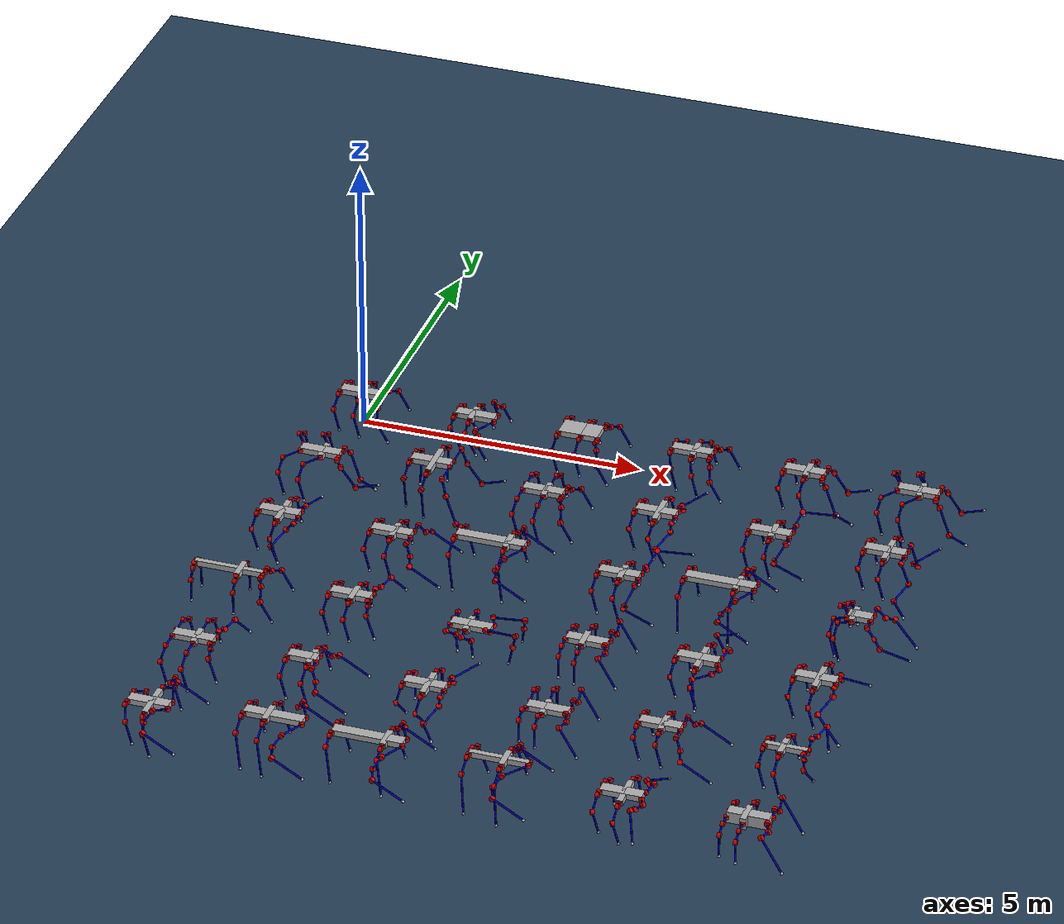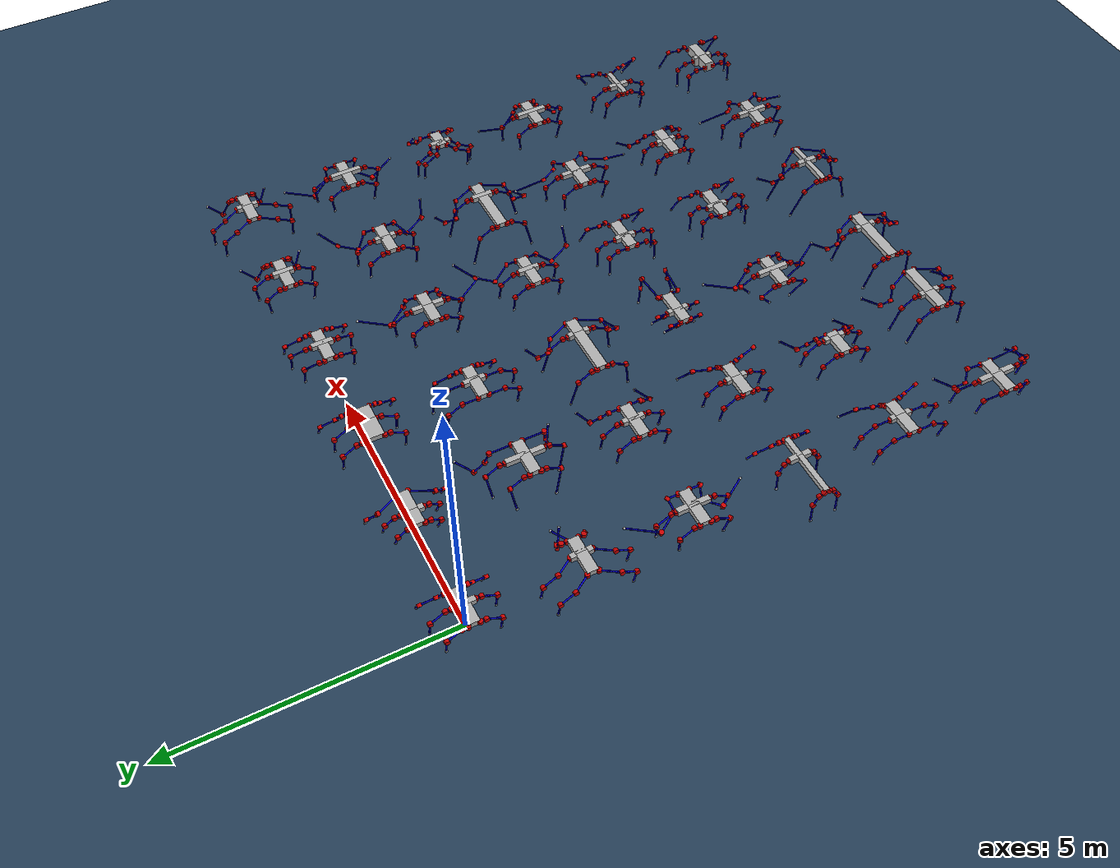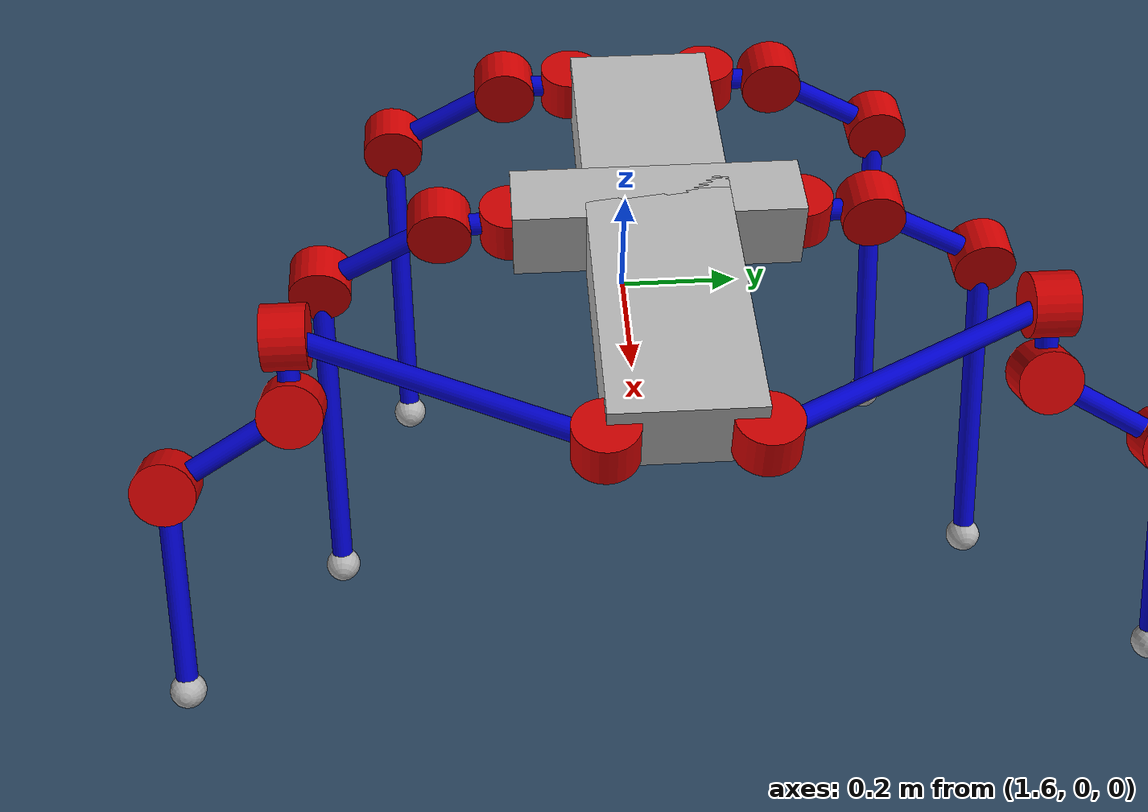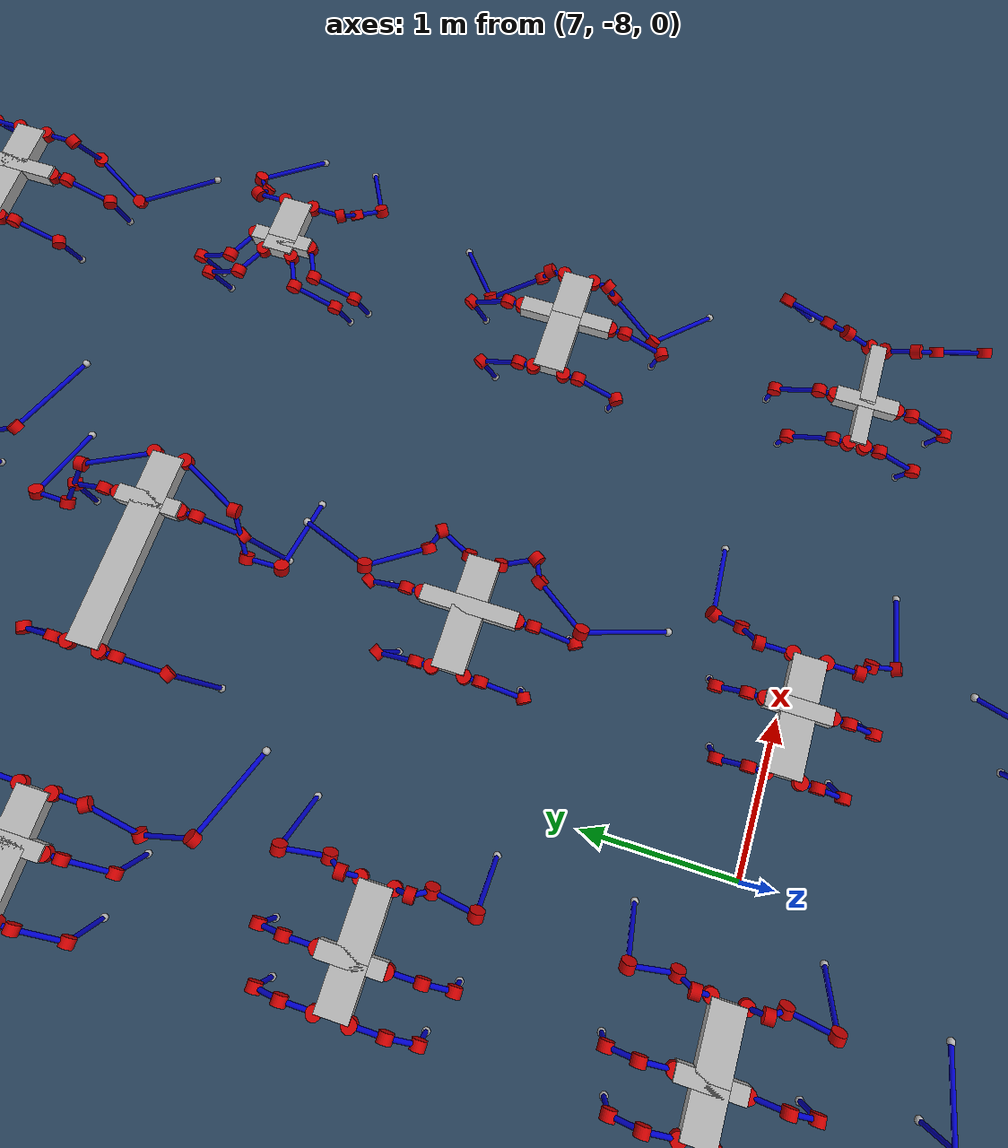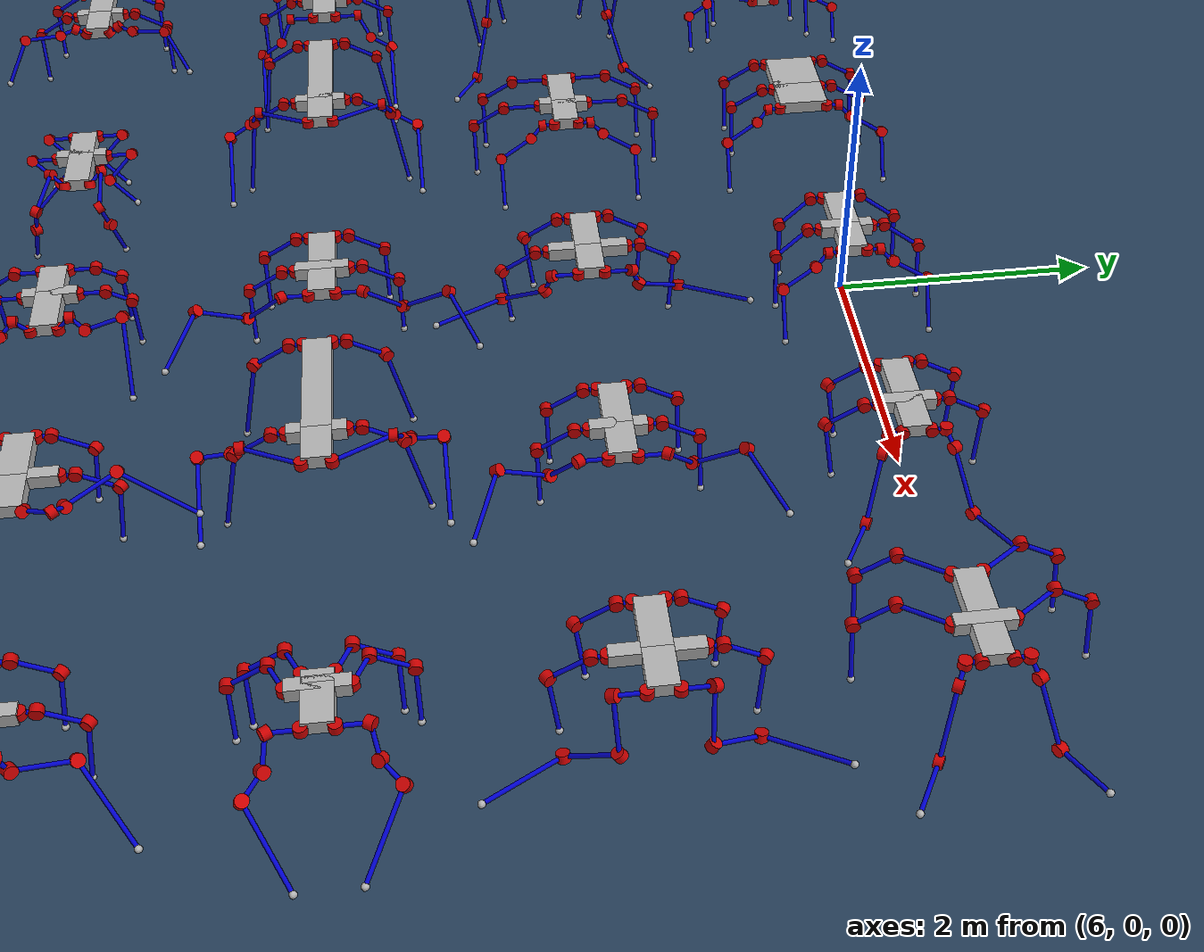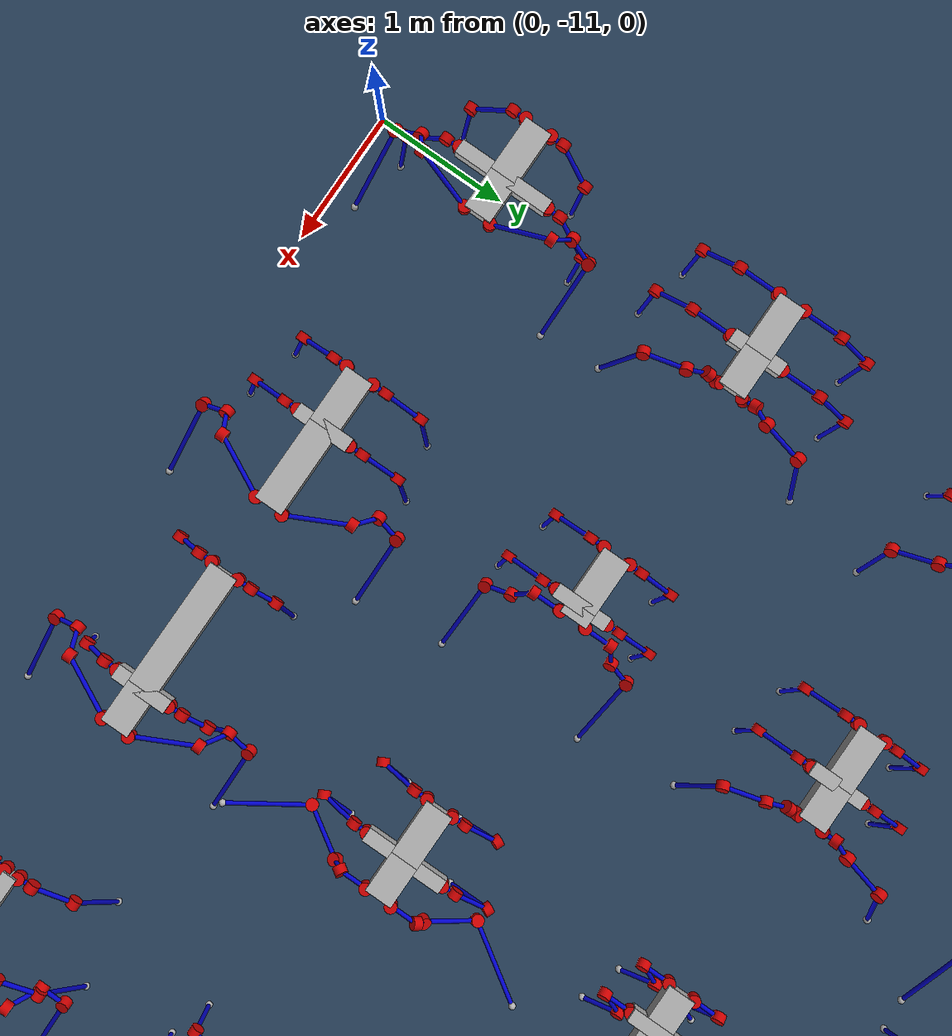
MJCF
<mujoco model="newhex_heterogeneous_grid">
  <compiler angle="radian"/>

  <visual>
    <global offwidth="3840" offheight="2160"/>
    <rgba haze="0.15 0.25 0.35 1"/>
  </visual>

  <default>
    <default class="floor">
      <geom size="0 0 0.05" type="plane" material="groundplane"/>
    </default>
    <default class="g006_o007/main">
      <default class="g006_o007/robot">
        <joint armature="0.01" damping="2" frictionloss="0.2"/>
        <default class="g006_o007/visual">
          <geom contype="0" conaffinity="0" group="2"/>
        </default>
        <default class="g006_o007/collision">
          <geom contype="0" group="3"/>
        </default>
      </default>
      <default class="g006_o007/floor">
        <geom size="0 0 0.05" type="plane" material="groundplane"/>
      </default>
    </default>
    <default class="g010_o025/main">
      <default class="g010_o025/robot">
        <joint armature="0.01" damping="2" frictionloss="0.2"/>
        <default class="g010_o025/visual">
          <geom contype="0" conaffinity="0" group="2"/>
        </default>
        <default class="g010_o025/collision">
          <geom contype="0" group="3"/>
        </default>
      </default>
      <default class="g010_o025/floor">
        <geom size="0 0 0.05" type="plane" material="groundplane"/>
      </default>
    </default>
    <default class="g011_o020/main">
      <default class="g011_o020/robot">
        <joint armature="0.01" damping="2" frictionloss="0.2"/>
        <default class="g011_o020/visual">
          <geom contype="0" conaffinity="0" group="2"/>
        </default>
        <default class="g011_o020/collision">
          <geom contype="0" group="3"/>
        </default>
      </default>
      <default class="g011_o020/floor">
        <geom size="0 0 0.05" type="plane" material="groundplane"/>
      </default>
    </default>
    <default class="g012_o031/main">
      <default class="g012_o031/robot">
        <joint armature="0.01" damping="2" frictionloss="0.2"/>
        <default class="g012_o031/visual">
          <geom contype="0" conaffinity="0" group="2"/>
        </default>
        <default class="g012_o031/collision">
          <geom contype="0" group="3"/>
        </default>
      </default>
      <default class="g012_o031/floor">
        <geom size="0 0 0.05" type="plane" material="groundplane"/>
      </default>
    </default>
    <default class="g020_o021/main">
      <default class="g020_o021/robot">
        <joint armature="0.01" damping="2" frictionloss="0.2"/>
        <default class="g020_o021/visual">
          <geom contype="0" conaffinity="0" group="2"/>
        </default>
        <default class="g020_o021/collision">
          <geom contype="0" group="3"/>
        </default>
      </default>
      <default class="g020_o021/floor">
        <geom size="0 0 0.05" type="plane" material="groundplane"/>
      </default>
    </default>
    <default class="g020_o023/main">
      <default class="g020_o023/robot">
        <joint armature="0.01" damping="2" frictionloss="0.2"/>
        <default class="g020_o023/visual">
          <geom contype="0" conaffinity="0" group="2"/>
        </default>
        <default class="g020_o023/collision">
          <geom contype="0" group="3"/>
        </default>
      </default>
      <default class="g020_o023/floor">
        <geom size="0 0 0.05" type="plane" material="groundplane"/>
      </default>
    </default>
    <default class="g021_o024/main">
      <default class="g021_o024/robot">
        <joint armature="0.01" damping="2" frictionloss="0.2"/>
        <default class="g021_o024/visual">
          <geom contype="0" conaffinity="0" group="2"/>
        </default>
        <default class="g021_o024/collision">
          <geom contype="0" group="3"/>
        </default>
      </default>
      <default class="g021_o024/floor">
        <geom size="0 0 0.05" type="plane" material="groundplane"/>
      </default>
    </default>
    <default class="g021_o043/main">
      <default class="g021_o043/robot">
        <joint armature="0.01" damping="2" frictionloss="0.2"/>
        <default class="g021_o043/visual">
          <geom contype="0" conaffinity="0" group="2"/>
        </default>
        <default class="g021_o043/collision">
          <geom contype="0" group="3"/>
        </default>
      </default>
      <default class="g021_o043/floor">
        <geom size="0 0 0.05" type="plane" material="groundplane"/>
      </default>
    </default>
    <default class="g022_o041/main">
      <default class="g022_o041/robot">
        <joint armature="0.01" damping="2" frictionloss="0.2"/>
        <default class="g022_o041/visual">
          <geom contype="0" conaffinity="0" group="2"/>
        </default>
        <default class="g022_o041/collision">
          <geom contype="0" group="3"/>
        </default>
      </default>
      <default class="g022_o041/floor">
        <geom size="0 0 0.05" type="plane" material="groundplane"/>
      </default>
    </default>
    <default class="g023_o020/main">
      <default class="g023_o020/robot">
        <joint armature="0.01" damping="2" frictionloss="0.2"/>
        <default class="g023_o020/visual">
          <geom contype="0" conaffinity="0" group="2"/>
        </default>
        <default class="g023_o020/collision">
          <geom contype="0" group="3"/>
        </default>
      </default>
      <default class="g023_o020/floor">
        <geom size="0 0 0.05" type="plane" material="groundplane"/>
      </default>
    </default>
    <default class="g023_o045/main">
      <default class="g023_o045/robot">
        <joint armature="0.01" damping="2" frictionloss="0.2"/>
        <default class="g023_o045/visual">
          <geom contype="0" conaffinity="0" group="2"/>
        </default>
        <default class="g023_o045/collision">
          <geom contype="0" group="3"/>
        </default>
      </default>
      <default class="g023_o045/floor">
        <geom size="0 0 0.05" type="plane" material="groundplane"/>
      </default>
    </default>
    <default class="g024_o006/main">
      <default class="g024_o006/robot">
        <joint armature="0.01" damping="2" frictionloss="0.2"/>
        <default class="g024_o006/visual">
          <geom contype="0" conaffinity="0" group="2"/>
        </default>
        <default class="g024_o006/collision">
          <geom contype="0" group="3"/>
        </default>
      </default>
      <default class="g024_o006/floor">
        <geom size="0 0 0.05" type="plane" material="groundplane"/>
      </default>
    </default>
    <default class="g025_o041/main">
      <default class="g025_o041/robot">
        <joint armature="0.01" damping="2" frictionloss="0.2"/>
        <default class="g025_o041/visual">
          <geom contype="0" conaffinity="0" group="2"/>
        </default>
        <default class="g025_o041/collision">
          <geom contype="0" group="3"/>
        </default>
      </default>
      <default class="g025_o041/floor">
        <geom size="0 0 0.05" type="plane" material="groundplane"/>
      </default>
    </default>
    <default class="g027_o037/main">
      <default class="g027_o037/robot">
        <joint armature="0.01" damping="2" frictionloss="0.2"/>
        <default class="g027_o037/visual">
          <geom contype="0" conaffinity="0" group="2"/>
        </default>
        <default class="g027_o037/collision">
          <geom contype="0" group="3"/>
        </default>
      </default>
      <default class="g027_o037/floor">
        <geom size="0 0 0.05" type="plane" material="groundplane"/>
      </default>
    </default>
    <default class="g027_o049/main">
      <default class="g027_o049/robot">
        <joint armature="0.01" damping="2" frictionloss="0.2"/>
        <default class="g027_o049/visual">
          <geom contype="0" conaffinity="0" group="2"/>
        </default>
        <default class="g027_o049/collision">
          <geom contype="0" group="3"/>
        </default>
      </default>
      <default class="g027_o049/floor">
        <geom size="0 0 0.05" type="plane" material="groundplane"/>
      </default>
    </default>
    <default class="g028_o010/main">
      <default class="g028_o010/robot">
        <joint armature="0.01" damping="2" frictionloss="0.2"/>
        <default class="g028_o010/visual">
          <geom contype="0" conaffinity="0" group="2"/>
        </default>
        <default class="g028_o010/collision">
          <geom contype="0" group="3"/>
        </default>
      </default>
      <default class="g028_o010/floor">
        <geom size="0 0 0.05" type="plane" material="groundplane"/>
      </default>
    </default>
    <default class="g028_o015/main">
      <default class="g028_o015/robot">
        <joint armature="0.01" damping="2" frictionloss="0.2"/>
        <default class="g028_o015/visual">
          <geom contype="0" conaffinity="0" group="2"/>
        </default>
        <default class="g028_o015/collision">
          <geom contype="0" group="3"/>
        </default>
      </default>
      <default class="g028_o015/floor">
        <geom size="0 0 0.05" type="plane" material="groundplane"/>
      </default>
    </default>
    <default class="g029_o012/main">
      <default class="g029_o012/robot">
        <joint armature="0.01" damping="2" frictionloss="0.2"/>
        <default class="g029_o012/visual">
          <geom contype="0" conaffinity="0" group="2"/>
        </default>
        <default class="g029_o012/collision">
          <geom contype="0" group="3"/>
        </default>
      </default>
      <default class="g029_o012/floor">
        <geom size="0 0 0.05" type="plane" material="groundplane"/>
      </default>
    </default>
    <default class="g030_o001/main">
      <default class="g030_o001/robot">
        <joint armature="0.01" damping="2" frictionloss="0.2"/>
        <default class="g030_o001/visual">
          <geom contype="0" conaffinity="0" group="2"/>
        </default>
        <default class="g030_o001/collision">
          <geom contype="0" group="3"/>
        </default>
      </default>
      <default class="g030_o001/floor">
        <geom size="0 0 0.05" type="plane" material="groundplane"/>
      </default>
    </default>
    <default class="g030_o007/main">
      <default class="g030_o007/robot">
        <joint armature="0.01" damping="2" frictionloss="0.2"/>
        <default class="g030_o007/visual">
          <geom contype="0" conaffinity="0" group="2"/>
        </default>
        <default class="g030_o007/collision">
          <geom contype="0" group="3"/>
        </default>
      </default>
      <default class="g030_o007/floor">
        <geom size="0 0 0.05" type="plane" material="groundplane"/>
      </default>
    </default>
    <default class="g030_o026/main">
      <default class="g030_o026/robot">
        <joint armature="0.01" damping="2" frictionloss="0.2"/>
        <default class="g030_o026/visual">
          <geom contype="0" conaffinity="0" group="2"/>
        </default>
        <default class="g030_o026/collision">
          <geom contype="0" group="3"/>
        </default>
      </default>
      <default class="g030_o026/floor">
        <geom size="0 0 0.05" type="plane" material="groundplane"/>
      </default>
    </default>
    <default class="g030_o027/main">
      <default class="g030_o027/robot">
        <joint armature="0.01" damping="2" frictionloss="0.2"/>
        <default class="g030_o027/visual">
          <geom contype="0" conaffinity="0" group="2"/>
        </default>
        <default class="g030_o027/collision">
          <geom contype="0" group="3"/>
        </default>
      </default>
      <default class="g030_o027/floor">
        <geom size="0 0 0.05" type="plane" material="groundplane"/>
      </default>
    </default>
    <default class="g031_o008/main">
      <default class="g031_o008/robot">
        <joint armature="0.01" damping="2" frictionloss="0.2"/>
        <default class="g031_o008/visual">
          <geom contype="0" conaffinity="0" group="2"/>
        </default>
        <default class="g031_o008/collision">
          <geom contype="0" group="3"/>
        </default>
      </default>
      <default class="g031_o008/floor">
        <geom size="0 0 0.05" type="plane" material="groundplane"/>
      </default>
    </default>
    <default class="g031_o028/main">
      <default class="g031_o028/robot">
        <joint armature="0.01" damping="2" frictionloss="0.2"/>
        <default class="g031_o028/visual">
          <geom contype="0" conaffinity="0" group="2"/>
        </default>
        <default class="g031_o028/collision">
          <geom contype="0" group="3"/>
        </default>
      </default>
      <default class="g031_o028/floor">
        <geom size="0 0 0.05" type="plane" material="groundplane"/>
      </default>
    </default>
    <default class="g032_o038/main">
      <default class="g032_o038/robot">
        <joint armature="0.01" damping="2" frictionloss="0.2"/>
        <default class="g032_o038/visual">
          <geom contype="0" conaffinity="0" group="2"/>
        </default>
        <default class="g032_o038/collision">
          <geom contype="0" group="3"/>
        </default>
      </default>
      <default class="g032_o038/floor">
        <geom size="0 0 0.05" type="plane" material="groundplane"/>
      </default>
    </default>
    <default class="g033_o011/main">
      <default class="g033_o011/robot">
        <joint armature="0.01" damping="2" frictionloss="0.2"/>
        <default class="g033_o011/visual">
          <geom contype="0" conaffinity="0" group="2"/>
        </default>
        <default class="g033_o011/collision">
          <geom contype="0" group="3"/>
        </default>
      </default>
      <default class="g033_o011/floor">
        <geom size="0 0 0.05" type="plane" material="groundplane"/>
      </default>
    </default>
    <default class="g034_o009/main">
      <default class="g034_o009/robot">
        <joint armature="0.01" damping="2" frictionloss="0.2"/>
        <default class="g034_o009/visual">
          <geom contype="0" conaffinity="0" group="2"/>
        </default>
        <default class="g034_o009/collision">
          <geom contype="0" group="3"/>
        </default>
      </default>
      <default class="g034_o009/floor">
        <geom size="0 0 0.05" type="plane" material="groundplane"/>
      </default>
    </default>
    <default class="g034_o023/main">
      <default class="g034_o023/robot">
        <joint armature="0.01" damping="2" frictionloss="0.2"/>
        <default class="g034_o023/visual">
          <geom contype="0" conaffinity="0" group="2"/>
        </default>
        <default class="g034_o023/collision">
          <geom contype="0" group="3"/>
        </default>
      </default>
      <default class="g034_o023/floor">
        <geom size="0 0 0.05" type="plane" material="groundplane"/>
      </default>
    </default>
    <default class="g036_o034/main">
      <default class="g036_o034/robot">
        <joint armature="0.01" damping="2" frictionloss="0.2"/>
        <default class="g036_o034/visual">
          <geom contype="0" conaffinity="0" group="2"/>
        </default>
        <default class="g036_o034/collision">
          <geom contype="0" group="3"/>
        </default>
      </default>
      <default class="g036_o034/floor">
        <geom size="0 0 0.05" type="plane" material="groundplane"/>
      </default>
    </default>
    <default class="g037_o010/main">
      <default class="g037_o010/robot">
        <joint armature="0.01" damping="2" frictionloss="0.2"/>
        <default class="g037_o010/visual">
          <geom contype="0" conaffinity="0" group="2"/>
        </default>
        <default class="g037_o010/collision">
          <geom contype="0" group="3"/>
        </default>
      </default>
      <default class="g037_o010/floor">
        <geom size="0 0 0.05" type="plane" material="groundplane"/>
      </default>
    </default>
    <default class="g038_o010/main">
      <default class="g038_o010/robot">
        <joint armature="0.01" damping="2" frictionloss="0.2"/>
        <default class="g038_o010/visual">
          <geom contype="0" conaffinity="0" group="2"/>
        </default>
        <default class="g038_o010/collision">
          <geom contype="0" group="3"/>
        </default>
      </default>
      <default class="g038_o010/floor">
        <geom size="0 0 0.05" type="plane" material="groundplane"/>
      </default>
    </default>
    <default class="g038_o024/main">
      <default class="g038_o024/robot">
        <joint armature="0.01" damping="2" frictionloss="0.2"/>
        <default class="g038_o024/visual">
          <geom contype="0" conaffinity="0" group="2"/>
        </default>
        <default class="g038_o024/collision">
          <geom contype="0" group="3"/>
        </default>
      </default>
      <default class="g038_o024/floor">
        <geom size="0 0 0.05" type="plane" material="groundplane"/>
      </default>
    </default>
    <default class="g038_o047/main">
      <default class="g038_o047/robot">
        <joint armature="0.01" damping="2" frictionloss="0.2"/>
        <default class="g038_o047/visual">
          <geom contype="0" conaffinity="0" group="2"/>
        </default>
        <default class="g038_o047/collision">
          <geom contype="0" group="3"/>
        </default>
      </default>
      <default class="g038_o047/floor">
        <geom size="0 0 0.05" type="plane" material="groundplane"/>
      </default>
    </default>
    <default class="g039_o041/main">
      <default class="g039_o041/robot">
        <joint armature="0.01" damping="2" frictionloss="0.2"/>
        <default class="g039_o041/visual">
          <geom contype="0" conaffinity="0" group="2"/>
        </default>
        <default class="g039_o041/collision">
          <geom contype="0" group="3"/>
        </default>
      </default>
      <default class="g039_o041/floor">
        <geom size="0 0 0.05" type="plane" material="groundplane"/>
      </default>
    </default>
    <default class="g040_o001/main">
      <default class="g040_o001/robot">
        <joint armature="0.01" damping="2" frictionloss="0.2"/>
        <default class="g040_o001/visual">
          <geom contype="0" conaffinity="0" group="2"/>
        </default>
        <default class="g040_o001/collision">
          <geom contype="0" group="3"/>
        </default>
      </default>
      <default class="g040_o001/floor">
        <geom size="0 0 0.05" type="plane" material="groundplane"/>
      </default>
    </default>
    <default class="g040_o019/main">
      <default class="g040_o019/robot">
        <joint armature="0.01" damping="2" frictionloss="0.2"/>
        <default class="g040_o019/visual">
          <geom contype="0" conaffinity="0" group="2"/>
        </default>
        <default class="g040_o019/collision">
          <geom contype="0" group="3"/>
        </default>
      </default>
      <default class="g040_o019/floor">
        <geom size="0 0 0.05" type="plane" material="groundplane"/>
      </default>
    </default>
  </default>

  <asset>
    <texture type="2d" colorspace="sRGB" name="groundplane" builtin="checker" mark="edge" rgb1="0.2 0.3 0.4" rgb2="0.1 0.2 0.3" markrgb="0.8 0.8 0.8" width="300" height="300"/>
    <material name="groundplane" texture="groundplane" texuniform="true" texrepeat="10 10" reflectance="0.2"/>
    <material name="g006_o007/blue" rgba="0 0 0.8 1"/>
    <material name="g006_o007/red" rgba="0.8 0 0 1"/>
    <material name="g006_o007/grey" rgba="0.7 0.7 0.7 1"/>
    <material name="g010_o025/blue" rgba="0 0 0.8 1"/>
    <material name="g010_o025/red" rgba="0.8 0 0 1"/>
    <material name="g010_o025/grey" rgba="0.7 0.7 0.7 1"/>
    <material name="g011_o020/blue" rgba="0 0 0.8 1"/>
    <material name="g011_o020/red" rgba="0.8 0 0 1"/>
    <material name="g011_o020/grey" rgba="0.7 0.7 0.7 1"/>
    <material name="g012_o031/blue" rgba="0 0 0.8 1"/>
    <material name="g012_o031/red" rgba="0.8 0 0 1"/>
    <material name="g012_o031/grey" rgba="0.7 0.7 0.7 1"/>
    <material name="g020_o021/blue" rgba="0 0 0.8 1"/>
    <material name="g020_o021/red" rgba="0.8 0 0 1"/>
    <material name="g020_o021/grey" rgba="0.7 0.7 0.7 1"/>
    <material name="g020_o023/blue" rgba="0 0 0.8 1"/>
    <material name="g020_o023/red" rgba="0.8 0 0 1"/>
    <material name="g020_o023/grey" rgba="0.7 0.7 0.7 1"/>
    <material name="g021_o024/blue" rgba="0 0 0.8 1"/>
    <material name="g021_o024/red" rgba="0.8 0 0 1"/>
    <material name="g021_o024/grey" rgba="0.7 0.7 0.7 1"/>
    <material name="g021_o043/blue" rgba="0 0 0.8 1"/>
    <material name="g021_o043/red" rgba="0.8 0 0 1"/>
    <material name="g021_o043/grey" rgba="0.7 0.7 0.7 1"/>
    <material name="g022_o041/blue" rgba="0 0 0.8 1"/>
    <material name="g022_o041/red" rgba="0.8 0 0 1"/>
    <material name="g022_o041/grey" rgba="0.7 0.7 0.7 1"/>
    <material name="g023_o020/blue" rgba="0 0 0.8 1"/>
    <material name="g023_o020/red" rgba="0.8 0 0 1"/>
    <material name="g023_o020/grey" rgba="0.7 0.7 0.7 1"/>
    <material name="g023_o045/blue" rgba="0 0 0.8 1"/>
    <material name="g023_o045/red" rgba="0.8 0 0 1"/>
    <material name="g023_o045/grey" rgba="0.7 0.7 0.7 1"/>
    <material name="g024_o006/blue" rgba="0 0 0.8 1"/>
    <material name="g024_o006/red" rgba="0.8 0 0 1"/>
    <material name="g024_o006/grey" rgba="0.7 0.7 0.7 1"/>
    <material name="g025_o041/blue" rgba="0 0 0.8 1"/>
    <material name="g025_o041/red" rgba="0.8 0 0 1"/>
    <material name="g025_o041/grey" rgba="0.7 0.7 0.7 1"/>
    <material name="g027_o037/blue" rgba="0 0 0.8 1"/>
    <material name="g027_o037/red" rgba="0.8 0 0 1"/>
    <material name="g027_o037/grey" rgba="0.7 0.7 0.7 1"/>
    <material name="g027_o049/blue" rgba="0 0 0.8 1"/>
    <material name="g027_o049/red" rgba="0.8 0 0 1"/>
    <material name="g027_o049/grey" rgba="0.7 0.7 0.7 1"/>
    <material name="g028_o010/blue" rgba="0 0 0.8 1"/>
    <material name="g028_o010/red" rgba="0.8 0 0 1"/>
    <material name="g028_o010/grey" rgba="0.7 0.7 0.7 1"/>
    <material name="g028_o015/blue" rgba="0 0 0.8 1"/>
    <material name="g028_o015/red" rgba="0.8 0 0 1"/>
    <material name="g028_o015/grey" rgba="0.7 0.7 0.7 1"/>
    <material name="g029_o012/blue" rgba="0 0 0.8 1"/>
    <material name="g029_o012/red" rgba="0.8 0 0 1"/>
    <material name="g029_o012/grey" rgba="0.7 0.7 0.7 1"/>
    <material name="g030_o001/blue" rgba="0 0 0.8 1"/>
    <material name="g030_o001/red" rgba="0.8 0 0 1"/>
    <material name="g030_o001/grey" rgba="0.7 0.7 0.7 1"/>
    <material name="g030_o007/blue" rgba="0 0 0.8 1"/>
    <material name="g030_o007/red" rgba="0.8 0 0 1"/>
    <material name="g030_o007/grey" rgba="0.7 0.7 0.7 1"/>
    <material name="g030_o026/blue" rgba="0 0 0.8 1"/>
    <material name="g030_o026/red" rgba="0.8 0 0 1"/>
    <material name="g030_o026/grey" rgba="0.7 0.7 0.7 1"/>
    <material name="g030_o027/blue" rgba="0 0 0.8 1"/>
    <material name="g030_o027/red" rgba="0.8 0 0 1"/>
    <material name="g030_o027/grey" rgba="0.7 0.7 0.7 1"/>
    <material name="g031_o008/blue" rgba="0 0 0.8 1"/>
    <material name="g031_o008/red" rgba="0.8 0 0 1"/>
    <material name="g031_o008/grey" rgba="0.7 0.7 0.7 1"/>
    <material name="g031_o028/blue" rgba="0 0 0.8 1"/>
    <material name="g031_o028/red" rgba="0.8 0 0 1"/>
    <material name="g031_o028/grey" rgba="0.7 0.7 0.7 1"/>
    <material name="g032_o038/blue" rgba="0 0 0.8 1"/>
    <material name="g032_o038/red" rgba="0.8 0 0 1"/>
    <material name="g032_o038/grey" rgba="0.7 0.7 0.7 1"/>
    <material name="g033_o011/blue" rgba="0 0 0.8 1"/>
    <material name="g033_o011/red" rgba="0.8 0 0 1"/>
    <material name="g033_o011/grey" rgba="0.7 0.7 0.7 1"/>
    <material name="g034_o009/blue" rgba="0 0 0.8 1"/>
    <material name="g034_o009/red" rgba="0.8 0 0 1"/>
    <material name="g034_o009/grey" rgba="0.7 0.7 0.7 1"/>
    <material name="g034_o023/blue" rgba="0 0 0.8 1"/>
    <material name="g034_o023/red" rgba="0.8 0 0 1"/>
    <material name="g034_o023/grey" rgba="0.7 0.7 0.7 1"/>
    <material name="g036_o034/blue" rgba="0 0 0.8 1"/>
    <material name="g036_o034/red" rgba="0.8 0 0 1"/>
    <material name="g036_o034/grey" rgba="0.7 0.7 0.7 1"/>
    <material name="g037_o010/blue" rgba="0 0 0.8 1"/>
    <material name="g037_o010/red" rgba="0.8 0 0 1"/>
    <material name="g037_o010/grey" rgba="0.7 0.7 0.7 1"/>
    <material name="g038_o010/blue" rgba="0 0 0.8 1"/>
    <material name="g038_o010/red" rgba="0.8 0 0 1"/>
    <material name="g038_o010/grey" rgba="0.7 0.7 0.7 1"/>
    <material name="g038_o024/blue" rgba="0 0 0.8 1"/>
    <material name="g038_o024/red" rgba="0.8 0 0 1"/>
    <material name="g038_o024/grey" rgba="0.7 0.7 0.7 1"/>
    <material name="g038_o047/blue" rgba="0 0 0.8 1"/>
    <material name="g038_o047/red" rgba="0.8 0 0 1"/>
    <material name="g038_o047/grey" rgba="0.7 0.7 0.7 1"/>
    <material name="g039_o041/blue" rgba="0 0 0.8 1"/>
    <material name="g039_o041/red" rgba="0.8 0 0 1"/>
    <material name="g039_o041/grey" rgba="0.7 0.7 0.7 1"/>
    <material name="g040_o001/blue" rgba="0 0 0.8 1"/>
    <material name="g040_o001/red" rgba="0.8 0 0 1"/>
    <material name="g040_o001/grey" rgba="0.7 0.7 0.7 1"/>
    <material name="g040_o019/blue" rgba="0 0 0.8 1"/>
    <material name="g040_o019/red" rgba="0.8 0 0 1"/>
    <material name="g040_o019/grey" rgba="0.7 0.7 0.7 1"/>
  </asset>

  <worldbody>
    <geom name="floor" class="floor"/>
    <light pos="0 0 5" dir="0 0 -1" type="directional"/>
    <body name="g006_o007/base_link" childclass="g006_o007/robot" pos="0 0 0.5885">
      <inertial pos="0 0 0" mass="18.4" diaginertia="0.0166667 0.0166667 0.0166667"/>
      <joint name="g006_o007/floating_base" type="free" armature="0" damping="0" frictionloss="0"/>
      <geom name="g006_o007/base_link_collision_0" class="g006_o007/collision" size="0.15 0.1 0.05" pos="0.15 0 0" type="box"/>
      <geom name="g006_o007/base_link_collision_1" class="g006_o007/collision" size="0.2 0.1 0.05" pos="-0.2 0 0" type="box"/>
      <geom name="g006_o007/base_link_collision_2" class="g006_o007/collision" size="0.05 0.2 0.05" type="box"/>
      <geom name="g006_o007/base_link_visual_0" class="g006_o007/visual" size="0.15 0.1 0.05" pos="0.15 0 0" type="box" material="g006_o007/grey"/>
      <geom name="g006_o007/base_link_visual_1" class="g006_o007/visual" size="0.2 0.1 0.05" pos="-0.2 0 0" type="box" material="g006_o007/grey"/>
      <geom name="g006_o007/base_link_visual_2" class="g006_o007/visual" size="0.05 0.2 0.05" type="box" material="g006_o007/grey"/>
      <site name="g006_o007/imu" pos="0 0 0" size="0.01" rgba="1 0 0 1"/>
      <body name="g006_o007/LF_link1" pos="0.3 0.1 0" quat="0.707407 0 0 0.706807">
        <inertial pos="0 0 0" mass="1" diaginertia="0.000968 0.000968 0.000784"/>
        <joint name="g006_o007/LF_joint1" pos="0 0 0" axis="0 0 1" range="-6.28 6.28"/>
        <geom name="g006_o007/LF_link1_collision" class="g006_o007/collision" size="0.015 0.05" pos="0.05 0 0" quat="0.707107 0 0.707107 0" type="cylinder"/>
        <geom name="g006_o007/LF_link1_visual_0" class="g006_o007/visual" size="0.044 0.03" type="cylinder" material="g006_o007/red"/>
        <geom name="g006_o007/LF_link1_visual_1" class="g006_o007/visual" size="0.015 0.05" pos="0.05 0 0" quat="0.707107 0 0.707107 0" type="cylinder" material="g006_o007/blue"/>
        <body name="g006_o007/LF_link2" pos="0.1 0 0" quat="0.682975 -0.182593 0.683275 -0.182593">
          <inertial pos="0 0 0" mass="1.08284" diaginertia="0.000968 0.000968 0.000784"/>
          <joint name="g006_o007/LF_joint2" pos="0 0 0" axis="0 0 1" range="-6.28 6.28"/>
          <geom name="g006_o007/LF_link2_collision" class="g006_o007/collision" size="0.015 0.0707105" pos="0.05 0 0.05" quat="0.923877 0 0.38269 0" type="cylinder"/>
          <geom name="g006_o007/LF_link2_visual_0" class="g006_o007/visual" size="0.044 0.03" type="cylinder" material="g006_o007/red"/>
          <geom name="g006_o007/LF_link2_visual_1" class="g006_o007/visual" size="0.015 0.0707105" pos="0.05 0 0.05" quat="0.923877 0 0.38269 0" type="cylinder" material="g006_o007/blue"/>
          <body name="g006_o007/LF_link3" pos="0.1 0 0.1" quat="0.612708 0.612208 -0.353505 0.353305">
            <inertial pos="0 0 0" mass="1.4" diaginertia="0.000968 0.000968 0.000784"/>
            <joint name="g006_o007/LF_joint3" pos="0 0 0" axis="0 0 1" range="-6.28 6.28"/>
            <geom name="g006_o007/LF_link3_collision" class="g006_o007/collision" size="0.015 0.15" pos="0.15 0 0" quat="0.707107 0 0.707107 0" type="cylinder"/>
            <geom name="g006_o007/LF_link3_visual_0" class="g006_o007/visual" size="0.044 0.03" type="cylinder" material="g006_o007/red"/>
            <geom name="g006_o007/LF_link3_visual_1" class="g006_o007/visual" size="0.015 0.15" pos="0.15 0 0" quat="0.707107 0 0.707107 0" type="cylinder" material="g006_o007/blue"/>
            <body name="g006_o007/LF_link4" pos="0.3 0 0" quat="0.866156 0 0 -0.499774">
              <inertial pos="0 0 0" mass="1.6" diaginertia="0.000968 0.000968 0.000784"/>
              <joint name="g006_o007/LF_joint4" pos="0 0 0" axis="0 0 1" range="-6.28 6.28"/>
              <geom name="g006_o007/LF_link4_collision" class="g006_o007/collision" size="0.015 0.2" pos="0.2 0 0" quat="0.707107 0 0.707107 0" type="cylinder"/>
              <geom name="g006_o007/LF_link4_visual_0" class="g006_o007/visual" size="0.044 0.03" type="cylinder" material="g006_o007/red"/>
              <geom name="g006_o007/LF_link4_visual_1" class="g006_o007/visual" size="0.015 0.2" pos="0.2 0 0" quat="0.707107 0 0.707107 0" type="cylinder" material="g006_o007/blue"/>
              <body name="g006_o007/LF_foot_link" pos="0.4 0 0">
                <inertial pos="0 0 0" mass="0.05" diaginertia="1.25e-05 1.25e-05 1.25e-05"/>
                <geom name="g006_o007/LF_foot_link_collision" class="g006_o007/collision" size="0.025"/>
                <geom name="g006_o007/LF_foot_link_visual" class="g006_o007/visual" size="0.025" material="g006_o007/grey"/>
                <site name="g006_o007/LF_touch_site" pos="0 0 0" size="0.01" rgba="0 0 0 0"/>
              </body>
            </body>
          </body>
        </body>
      </body>
      <body name="g006_o007/LM_link1" pos="0 0.2 0" quat="0.707407 0 0 0.706807">
        <inertial pos="0 0 0" mass="1" diaginertia="0.000968 0.000968 0.000784"/>
        <joint name="g006_o007/LM_joint1" pos="0 0 0" axis="0 0 1" range="-6.28 6.28"/>
        <geom name="g006_o007/LM_link1_collision" class="g006_o007/collision" size="0.015 0.05" pos="0.05 0 0" quat="0.707107 0 0.707107 0" type="cylinder"/>
        <geom name="g006_o007/LM_link1_visual_0" class="g006_o007/visual" size="0.044 0.03" type="cylinder" material="g006_o007/red"/>
        <geom name="g006_o007/LM_link1_visual_1" class="g006_o007/visual" size="0.015 0.05" pos="0.05 0 0" quat="0.707107 0 0.707107 0" type="cylinder" material="g006_o007/blue"/>
        <body name="g006_o007/LM_link2" pos="0.1 0 0" quat="0.683293 0.682793 0.182998 -0.182798">
          <inertial pos="0 0 0" mass="1.4" diaginertia="0.000968 0.000968 0.000784"/>
          <joint name="g006_o007/LM_joint2" pos="0 0 0" axis="0 0 1" range="-6.28 6.28"/>
          <geom name="g006_o007/LM_link2_collision" class="g006_o007/collision" size="0.015 0.15" pos="0.15 0 0" quat="0.707107 0 0.707107 0" type="cylinder"/>
          <geom name="g006_o007/LM_link2_visual_0" class="g006_o007/visual" size="0.044 0.03" type="cylinder" material="g006_o007/red"/>
          <geom name="g006_o007/LM_link2_visual_1" class="g006_o007/visual" size="0.015 0.15" pos="0.15 0 0" quat="0.707107 0 0.707107 0" type="cylinder" material="g006_o007/blue"/>
          <body name="g006_o007/LM_link3" pos="0.3 0 0" quat="0.866156 0 0 -0.499774">
            <inertial pos="0 0 0" mass="1.62462" diaginertia="0.000968 0.000968 0.000784"/>
            <joint name="g006_o007/LM_joint3" pos="0 0 0" axis="0 0 1" range="-6.28 6.28"/>
            <geom name="g006_o007/LM_link3_collision" class="g006_o007/collision" size="0.015 0.206155" pos="0.2 0 0.05" quat="0.788209 0 0.615407 0" type="cylinder"/>
            <geom name="g006_o007/LM_link3_visual_0" class="g006_o007/visual" size="0.044 0.03" type="cylinder" material="g006_o007/red"/>
            <geom name="g006_o007/LM_link3_visual_1" class="g006_o007/visual" size="0.015 0.206155" pos="0.2 0 0.05" quat="0.788209 0 0.615407 0" type="cylinder" material="g006_o007/blue"/>
            <body name="g006_o007/LM_foot_link" pos="0.4 0 0.1">
              <inertial pos="0 0 0" mass="0.05" diaginertia="1.25e-05 1.25e-05 1.25e-05"/>
              <geom name="g006_o007/LM_foot_link_collision" class="g006_o007/collision" size="0.025"/>
              <geom name="g006_o007/LM_foot_link_visual" class="g006_o007/visual" size="0.025" material="g006_o007/grey"/>
              <site name="g006_o007/LM_touch_site" pos="0 0 0" size="0.01" rgba="0 0 0 0"/>
            </body>
          </body>
        </body>
      </body>
      <body name="g006_o007/LB_link1" pos="-0.4 0.1 0" quat="0.707407 0 0 0.706807">
        <inertial pos="0 0 0" mass="1" diaginertia="0.000968 0.000968 0.000784"/>
        <joint name="g006_o007/LB_joint1" pos="0 0 0" axis="0 0 1" range="-6.28 6.28"/>
        <geom name="g006_o007/LB_link1_collision" class="g006_o007/collision" size="0.015 0.05" pos="0.05 0 0" quat="0.707107 0 0.707107 0" type="cylinder"/>
        <geom name="g006_o007/LB_link1_visual_0" class="g006_o007/visual" size="0.044 0.03" type="cylinder" material="g006_o007/red"/>
        <geom name="g006_o007/LB_link1_visual_1" class="g006_o007/visual" size="0.015 0.05" pos="0.05 0 0" quat="0.707107 0 0.707107 0" type="cylinder" material="g006_o007/blue"/>
        <body name="g006_o007/LB_link2" pos="0.1 0 0" quat="0.683293 0.682793 0.182998 -0.182798">
          <inertial pos="0 0 0" mass="1.4" diaginertia="0.000968 0.000968 0.000784"/>
          <joint name="g006_o007/LB_joint2" pos="0 0 0" axis="0 0 1" range="-6.28 6.28"/>
          <geom name="g006_o007/LB_link2_collision" class="g006_o007/collision" size="0.015 0.15" pos="0.15 0 0" quat="0.707107 0 0.707107 0" type="cylinder"/>
          <geom name="g006_o007/LB_link2_visual_0" class="g006_o007/visual" size="0.044 0.03" type="cylinder" material="g006_o007/red"/>
          <geom name="g006_o007/LB_link2_visual_1" class="g006_o007/visual" size="0.015 0.15" pos="0.15 0 0" quat="0.707107 0 0.707107 0" type="cylinder" material="g006_o007/blue"/>
          <body name="g006_o007/LB_link3" pos="0.3 0 0" quat="0.866156 0 0 -0.499774">
            <inertial pos="0 0 0" mass="1.62462" diaginertia="0.000968 0.000968 0.000784"/>
            <joint name="g006_o007/LB_joint3" pos="0 0 0" axis="0 0 1" range="-6.28 6.28"/>
            <geom name="g006_o007/LB_link3_collision" class="g006_o007/collision" size="0.015 0.206155" pos="0.2 0 0.05" quat="0.788209 0 0.615407 0" type="cylinder"/>
            <geom name="g006_o007/LB_link3_visual_0" class="g006_o007/visual" size="0.044 0.03" type="cylinder" material="g006_o007/red"/>
            <geom name="g006_o007/LB_link3_visual_1" class="g006_o007/visual" size="0.015 0.206155" pos="0.2 0 0.05" quat="0.788209 0 0.615407 0" type="cylinder" material="g006_o007/blue"/>
            <body name="g006_o007/LB_foot_link" pos="0.4 0 0.1">
              <inertial pos="0 0 0" mass="0.05" diaginertia="1.25e-05 1.25e-05 1.25e-05"/>
              <geom name="g006_o007/LB_foot_link_collision" class="g006_o007/collision" size="0.025"/>
              <geom name="g006_o007/LB_foot_link_visual" class="g006_o007/visual" size="0.025" material="g006_o007/grey"/>
              <site name="g006_o007/LB_touch_site" pos="0 0 0" size="0.01" rgba="0 0 0 0"/>
            </body>
          </body>
        </body>
      </body>
      <body name="g006_o007/RF_link1" pos="0.3 -0.1 0" quat="0.707407 0 0 -0.706807">
        <inertial pos="0 0 0" mass="1" diaginertia="0.000968 0.000968 0.000784"/>
        <joint name="g006_o007/RF_joint1" pos="0 0 0" axis="0 0 1" range="-6.28 6.28"/>
        <geom name="g006_o007/RF_link1_collision" class="g006_o007/collision" size="0.015 0.05" pos="0.05 0 0" quat="0.707107 0 0.707107 0" type="cylinder"/>
        <geom name="g006_o007/RF_link1_visual_0" class="g006_o007/visual" size="0.044 0.03" type="cylinder" material="g006_o007/red"/>
        <geom name="g006_o007/RF_link1_visual_1" class="g006_o007/visual" size="0.015 0.05" pos="0.05 0 0" quat="0.707107 0 0.707107 0" type="cylinder" material="g006_o007/blue"/>
        <body name="g006_o007/RF_link2" pos="0.1 0 0" quat="0.682975 0.182593 0.683275 0.182593">
          <inertial pos="0 0 0" mass="1.08284" diaginertia="0.000968 0.000968 0.000784"/>
          <joint name="g006_o007/RF_joint2" pos="0 0 0" axis="0 0 1" range="-6.28 6.28"/>
          <geom name="g006_o007/RF_link2_collision" class="g006_o007/collision" size="0.015 0.0707105" pos="0.05 0 0.05" quat="0.923877 0 0.38269 0" type="cylinder"/>
          <geom name="g006_o007/RF_link2_visual_0" class="g006_o007/visual" size="0.044 0.03" type="cylinder" material="g006_o007/red"/>
          <geom name="g006_o007/RF_link2_visual_1" class="g006_o007/visual" size="0.015 0.0707105" pos="0.05 0 0.05" quat="0.923877 0 0.38269 0" type="cylinder" material="g006_o007/blue"/>
          <body name="g006_o007/RF_link3" pos="0.1 0 0.1" quat="0.612708 -0.612208 -0.353505 -0.353305">
            <inertial pos="0 0 0" mass="1.4" diaginertia="0.000968 0.000968 0.000784"/>
            <joint name="g006_o007/RF_joint3" pos="0 0 0" axis="0 0 1" range="-6.28 6.28"/>
            <geom name="g006_o007/RF_link3_collision" class="g006_o007/collision" size="0.015 0.15" pos="0.15 0 0" quat="0.707107 0 0.707107 0" type="cylinder"/>
            <geom name="g006_o007/RF_link3_visual_0" class="g006_o007/visual" size="0.044 0.03" type="cylinder" material="g006_o007/red"/>
            <geom name="g006_o007/RF_link3_visual_1" class="g006_o007/visual" size="0.015 0.15" pos="0.15 0 0" quat="0.707107 0 0.707107 0" type="cylinder" material="g006_o007/blue"/>
            <body name="g006_o007/RF_link4" pos="0.3 0 0" quat="0.866156 0 0 0.499774">
              <inertial pos="0 0 0" mass="1.6" diaginertia="0.000968 0.000968 0.000784"/>
              <joint name="g006_o007/RF_joint4" pos="0 0 0" axis="0 0 1" range="-6.28 6.28"/>
              <geom name="g006_o007/RF_link4_collision" class="g006_o007/collision" size="0.015 0.2" pos="0.2 0 0" quat="0.707107 0 0.707107 0" type="cylinder"/>
              <geom name="g006_o007/RF_link4_visual_0" class="g006_o007/visual" size="0.044 0.03" type="cylinder" material="g006_o007/red"/>
              <geom name="g006_o007/RF_link4_visual_1" class="g006_o007/visual" size="0.015 0.2" pos="0.2 0 0" quat="0.707107 0 0.707107 0" type="cylinder" material="g006_o007/blue"/>
              <body name="g006_o007/RF_foot_link" pos="0.4 0 0">
                <inertial pos="0 0 0" mass="0.05" diaginertia="1.25e-05 1.25e-05 1.25e-05"/>
                <geom name="g006_o007/RF_foot_link_collision" class="g006_o007/collision" size="0.025"/>
                <geom name="g006_o007/RF_foot_link_visual" class="g006_o007/visual" size="0.025" material="g006_o007/grey"/>
                <site name="g006_o007/RF_touch_site" pos="0 0 0" size="0.01" rgba="0 0 0 0"/>
              </body>
            </body>
          </body>
        </body>
      </body>
      <body name="g006_o007/RM_link1" pos="0 -0.2 0" quat="0.707407 0 0 -0.706807">
        <inertial pos="0 0 0" mass="1" diaginertia="0.000968 0.000968 0.000784"/>
        <joint name="g006_o007/RM_joint1" pos="0 0 0" axis="0 0 1" range="-6.28 6.28"/>
        <geom name="g006_o007/RM_link1_collision" class="g006_o007/collision" size="0.015 0.05" pos="0.05 0 0" quat="0.707107 0 0.707107 0" type="cylinder"/>
        <geom name="g006_o007/RM_link1_visual_0" class="g006_o007/visual" size="0.044 0.03" type="cylinder" material="g006_o007/red"/>
        <geom name="g006_o007/RM_link1_visual_1" class="g006_o007/visual" size="0.015 0.05" pos="0.05 0 0" quat="0.707107 0 0.707107 0" type="cylinder" material="g006_o007/blue"/>
        <body name="g006_o007/RM_link2" pos="0.1 0 0" quat="0.683293 -0.682793 0.182998 0.182798">
          <inertial pos="0 0 0" mass="1.4" diaginertia="0.000968 0.000968 0.000784"/>
          <joint name="g006_o007/RM_joint2" pos="0 0 0" axis="0 0 1" range="-6.28 6.28"/>
          <geom name="g006_o007/RM_link2_collision" class="g006_o007/collision" size="0.015 0.15" pos="0.15 0 0" quat="0.707107 0 0.707107 0" type="cylinder"/>
          <geom name="g006_o007/RM_link2_visual_0" class="g006_o007/visual" size="0.044 0.03" type="cylinder" material="g006_o007/red"/>
          <geom name="g006_o007/RM_link2_visual_1" class="g006_o007/visual" size="0.015 0.15" pos="0.15 0 0" quat="0.707107 0 0.707107 0" type="cylinder" material="g006_o007/blue"/>
          <body name="g006_o007/RM_link3" pos="0.3 0 0" quat="0.866156 0 0 0.499774">
            <inertial pos="0 0 0" mass="1.62462" diaginertia="0.000968 0.000968 0.000784"/>
            <joint name="g006_o007/RM_joint3" pos="0 0 0" axis="0 0 1" range="-6.28 6.28"/>
            <geom name="g006_o007/RM_link3_collision" class="g006_o007/collision" size="0.015 0.206155" pos="0.2 0 0.05" quat="0.788209 0 0.615407 0" type="cylinder"/>
            <geom name="g006_o007/RM_link3_visual_0" class="g006_o007/visual" size="0.044 0.03" type="cylinder" material="g006_o007/red"/>
            <geom name="g006_o007/RM_link3_visual_1" class="g006_o007/visual" size="0.015 0.206155" pos="0.2 0 0.05" quat="0.788209 0 0.615407 0" type="cylinder" material="g006_o007/blue"/>
            <body name="g006_o007/RM_foot_link" pos="0.4 0 0.1">
              <inertial pos="0 0 0" mass="0.05" diaginertia="1.25e-05 1.25e-05 1.25e-05"/>
              <geom name="g006_o007/RM_foot_link_collision" class="g006_o007/collision" size="0.025"/>
              <geom name="g006_o007/RM_foot_link_visual" class="g006_o007/visual" size="0.025" material="g006_o007/grey"/>
              <site name="g006_o007/RM_touch_site" pos="0 0 0" size="0.01" rgba="0 0 0 0"/>
            </body>
          </body>
        </body>
      </body>
      <body name="g006_o007/RB_link1" pos="-0.4 -0.1 0" quat="0.707407 0 0 -0.706807">
        <inertial pos="0 0 0" mass="1" diaginertia="0.000968 0.000968 0.000784"/>
        <joint name="g006_o007/RB_joint1" pos="0 0 0" axis="0 0 1" range="-6.28 6.28"/>
        <geom name="g006_o007/RB_link1_collision" class="g006_o007/collision" size="0.015 0.05" pos="0.05 0 0" quat="0.707107 0 0.707107 0" type="cylinder"/>
        <geom name="g006_o007/RB_link1_visual_0" class="g006_o007/visual" size="0.044 0.03" type="cylinder" material="g006_o007/red"/>
        <geom name="g006_o007/RB_link1_visual_1" class="g006_o007/visual" size="0.015 0.05" pos="0.05 0 0" quat="0.707107 0 0.707107 0" type="cylinder" material="g006_o007/blue"/>
        <body name="g006_o007/RB_link2" pos="0.1 0 0" quat="0.683293 -0.682793 0.182998 0.182798">
          <inertial pos="0 0 0" mass="1.4" diaginertia="0.000968 0.000968 0.000784"/>
          <joint name="g006_o007/RB_joint2" pos="0 0 0" axis="0 0 1" range="-6.28 6.28"/>
          <geom name="g006_o007/RB_link2_collision" class="g006_o007/collision" size="0.015 0.15" pos="0.15 0 0" quat="0.707107 0 0.707107 0" type="cylinder"/>
          <geom name="g006_o007/RB_link2_visual_0" class="g006_o007/visual" size="0.044 0.03" type="cylinder" material="g006_o007/red"/>
          <geom name="g006_o007/RB_link2_visual_1" class="g006_o007/visual" size="0.015 0.15" pos="0.15 0 0" quat="0.707107 0 0.707107 0" type="cylinder" material="g006_o007/blue"/>
          <body name="g006_o007/RB_link3" pos="0.3 0 0" quat="0.866156 0 0 0.499774">
            <inertial pos="0 0 0" mass="1.62462" diaginertia="0.000968 0.000968 0.000784"/>
            <joint name="g006_o007/RB_joint3" pos="0 0 0" axis="0 0 1" range="-6.28 6.28"/>
            <geom name="g006_o007/RB_link3_collision" class="g006_o007/collision" size="0.015 0.206155" pos="0.2 0 0.05" quat="0.788209 0 0.615407 0" type="cylinder"/>
            <geom name="g006_o007/RB_link3_visual_0" class="g006_o007/visual" size="0.044 0.03" type="cylinder" material="g006_o007/red"/>
            <geom name="g006_o007/RB_link3_visual_1" class="g006_o007/visual" size="0.015 0.206155" pos="0.2 0 0.05" quat="0.788209 0 0.615407 0" type="cylinder" material="g006_o007/blue"/>
            <body name="g006_o007/RB_foot_link" pos="0.4 0 0.1">
              <inertial pos="0 0 0" mass="0.05" diaginertia="1.25e-05 1.25e-05 1.25e-05"/>
              <geom name="g006_o007/RB_foot_link_collision" class="g006_o007/collision" size="0.025"/>
              <geom name="g006_o007/RB_foot_link_visual" class="g006_o007/visual" size="0.025" material="g006_o007/grey"/>
              <site name="g006_o007/RB_touch_site" pos="0 0 0" size="0.01" rgba="0 0 0 0"/>
            </body>
          </body>
        </body>
      </body>
    </body>
    <body name="g010_o025/base_link" childclass="g010_o025/robot" pos="2 0 0.5249">
      <inertial pos="0 0 0" mass="18.4" diaginertia="0.0166667 0.0166667 0.0166667"/>
      <joint name="g010_o025/floating_base" type="free" armature="0" damping="0" frictionloss="0"/>
      <geom name="g010_o025/base_link_collision_0" class="g010_o025/collision" size="0.2 0.1 0.05" pos="0.2 0 0" type="box"/>
      <geom name="g010_o025/base_link_collision_1" class="g010_o025/collision" size="0.15 0.1 0.05" pos="-0.15 0 0" type="box"/>
      <geom name="g010_o025/base_link_collision_2" class="g010_o025/collision" size="0.05 0.2 0.05" type="box"/>
      <geom name="g010_o025/base_link_visual_0" class="g010_o025/visual" size="0.2 0.1 0.05" pos="0.2 0 0" type="box" material="g010_o025/grey"/>
      <geom name="g010_o025/base_link_visual_1" class="g010_o025/visual" size="0.15 0.1 0.05" pos="-0.15 0 0" type="box" material="g010_o025/grey"/>
      <geom name="g010_o025/base_link_visual_2" class="g010_o025/visual" size="0.05 0.2 0.05" type="box" material="g010_o025/grey"/>
      <site name="g010_o025/imu" pos="0 0 0" size="0.01" rgba="1 0 0 1"/>
      <body name="g010_o025/LF_link1" pos="0.4 0.1 0" quat="0.707407 0 0 0.706807">
        <inertial pos="0 0 0" mass="1.69443" diaginertia="0.000968 0.000968 0.000784"/>
        <joint name="g010_o025/LF_joint1" pos="0 0 0" axis="0 0 1" range="-6.28 6.28"/>
        <geom name="g010_o025/LF_link1_collision" class="g010_o025/collision" size="0.015 0.223607" pos="0.2 0.1 0" quat="0.688182 -0.162496 0.688182 0.162496" type="cylinder"/>
        <geom name="g010_o025/LF_link1_visual_0" class="g010_o025/visual" size="0.044 0.03" type="cylinder" material="g010_o025/red"/>
        <geom name="g010_o025/LF_link1_visual_1" class="g010_o025/visual" size="0.015 0.223607" pos="0.2 0.1 0" quat="0.688182 -0.162496 0.688182 0.162496" type="cylinder" material="g010_o025/blue"/>
        <body name="g010_o025/LF_link2" pos="0.4 0.2 0" quat="0.682975 -0.182593 0.683275 -0.182593">
          <inertial pos="0 0 0" mass="1" diaginertia="0.000968 0.000968 0.000784"/>
          <joint name="g010_o025/LF_joint2" pos="0 0 0" axis="0 0 1" range="-6.28 6.28"/>
          <geom name="g010_o025/LF_link2_collision" class="g010_o025/collision" size="0.015 0.05" pos="0.05 0 0" quat="0.707107 0 0.707107 0" type="cylinder"/>
          <geom name="g010_o025/LF_link2_visual_0" class="g010_o025/visual" size="0.044 0.03" type="cylinder" material="g010_o025/red"/>
          <geom name="g010_o025/LF_link2_visual_1" class="g010_o025/visual" size="0.015 0.05" pos="0.05 0 0" quat="0.707107 0 0.707107 0" type="cylinder" material="g010_o025/blue"/>
          <body name="g010_o025/LF_link3" pos="0.1 0 0" quat="0.612708 0.612208 -0.353505 0.353305">
            <inertial pos="0 0 0" mass="1.2" diaginertia="0.000968 0.000968 0.000784"/>
            <joint name="g010_o025/LF_joint3" pos="0 0 0" axis="0 0 1" range="-6.28 6.28"/>
            <geom name="g010_o025/LF_link3_collision" class="g010_o025/collision" size="0.015 0.1" pos="0.1 0 0" quat="0.707107 0 0.707107 0" type="cylinder"/>
            <geom name="g010_o025/LF_link3_visual_0" class="g010_o025/visual" size="0.044 0.03" type="cylinder" material="g010_o025/red"/>
            <geom name="g010_o025/LF_link3_visual_1" class="g010_o025/visual" size="0.015 0.1" pos="0.1 0 0" quat="0.707107 0 0.707107 0" type="cylinder" material="g010_o025/blue"/>
            <body name="g010_o025/LF_link4" pos="0.2 0 0" quat="0.866156 0 0 -0.499774">
              <inertial pos="0 0 0" mass="1.4" diaginertia="0.000968 0.000968 0.000784"/>
              <joint name="g010_o025/LF_joint4" pos="0 0 0" axis="0 0 1" range="-6.28 6.28"/>
              <geom name="g010_o025/LF_link4_collision" class="g010_o025/collision" size="0.015 0.15" pos="0.15 0 0" quat="0.707107 0 0.707107 0" type="cylinder"/>
              <geom name="g010_o025/LF_link4_visual_0" class="g010_o025/visual" size="0.044 0.03" type="cylinder" material="g010_o025/red"/>
              <geom name="g010_o025/LF_link4_visual_1" class="g010_o025/visual" size="0.015 0.15" pos="0.15 0 0" quat="0.707107 0 0.707107 0" type="cylinder" material="g010_o025/blue"/>
              <body name="g010_o025/LF_foot_link" pos="0.3 0 0">
                <inertial pos="0 0 0" mass="0.05" diaginertia="1.25e-05 1.25e-05 1.25e-05"/>
                <geom name="g010_o025/LF_foot_link_collision" class="g010_o025/collision" size="0.025"/>
                <geom name="g010_o025/LF_foot_link_visual" class="g010_o025/visual" size="0.025" material="g010_o025/grey"/>
                <site name="g010_o025/LF_touch_site" pos="0 0 0" size="0.01" rgba="0 0 0 0"/>
              </body>
            </body>
          </body>
        </body>
      </body>
      <body name="g010_o025/LM_link1" pos="0 0.2 0" quat="0.707407 0 0 0.706807">
        <inertial pos="0 0 0" mass="1" diaginertia="0.000968 0.000968 0.000784"/>
        <joint name="g010_o025/LM_joint1" pos="0 0 0" axis="0 0 1" range="-6.28 6.28"/>
        <geom name="g010_o025/LM_link1_collision" class="g010_o025/collision" size="0.015 0.05" pos="0.05 0 0" quat="0.707107 0 0.707107 0" type="cylinder"/>
        <geom name="g010_o025/LM_link1_visual_0" class="g010_o025/visual" size="0.044 0.03" type="cylinder" material="g010_o025/red"/>
        <geom name="g010_o025/LM_link1_visual_1" class="g010_o025/visual" size="0.015 0.05" pos="0.05 0 0" quat="0.707107 0 0.707107 0" type="cylinder" material="g010_o025/blue"/>
        <body name="g010_o025/LM_link2" pos="0.1 0 0" quat="0.683293 0.682793 0.182998 -0.182798">
          <inertial pos="0 0 0" mass="1.2" diaginertia="0.000968 0.000968 0.000784"/>
          <joint name="g010_o025/LM_joint2" pos="0 0 0" axis="0 0 1" range="-6.28 6.28"/>
          <geom name="g010_o025/LM_link2_collision" class="g010_o025/collision" size="0.015 0.1" pos="0.1 0 0" quat="0.707107 0 0.707107 0" type="cylinder"/>
          <geom name="g010_o025/LM_link2_visual_0" class="g010_o025/visual" size="0.044 0.03" type="cylinder" material="g010_o025/red"/>
          <geom name="g010_o025/LM_link2_visual_1" class="g010_o025/visual" size="0.015 0.1" pos="0.1 0 0" quat="0.707107 0 0.707107 0" type="cylinder" material="g010_o025/blue"/>
          <body name="g010_o025/LM_link3" pos="0.2 0 0" quat="0.866156 0 0 -0.499774">
            <inertial pos="0 0 0" mass="1.69443" diaginertia="0.000968 0.000968 0.000784"/>
            <joint name="g010_o025/LM_joint3" pos="0 0 0" axis="0 0 1" range="-6.28 6.28"/>
            <geom name="g010_o025/LM_link3_collision" class="g010_o025/collision" size="0.015 0.223607" pos="0.2 0 0.1" quat="0.850678 0 0.525687 0" type="cylinder"/>
            <geom name="g010_o025/LM_link3_visual_0" class="g010_o025/visual" size="0.044 0.03" type="cylinder" material="g010_o025/red"/>
            <geom name="g010_o025/LM_link3_visual_1" class="g010_o025/visual" size="0.015 0.223607" pos="0.2 0 0.1" quat="0.850678 0 0.525687 0" type="cylinder" material="g010_o025/blue"/>
            <body name="g010_o025/LM_foot_link" pos="0.4 0 0.2">
              <inertial pos="0 0 0" mass="0.05" diaginertia="1.25e-05 1.25e-05 1.25e-05"/>
              <geom name="g010_o025/LM_foot_link_collision" class="g010_o025/collision" size="0.025"/>
              <geom name="g010_o025/LM_foot_link_visual" class="g010_o025/visual" size="0.025" material="g010_o025/grey"/>
              <site name="g010_o025/LM_touch_site" pos="0 0 0" size="0.01" rgba="0 0 0 0"/>
            </body>
          </body>
        </body>
      </body>
      <body name="g010_o025/LB_link1" pos="-0.3 0.1 0" quat="0.707407 0 0 0.706807">
        <inertial pos="0 0 0" mass="1" diaginertia="0.000968 0.000968 0.000784"/>
        <joint name="g010_o025/LB_joint1" pos="0 0 0" axis="0 0 1" range="-6.28 6.28"/>
        <geom name="g010_o025/LB_link1_collision" class="g010_o025/collision" size="0.015 0.05" pos="0.05 0 0" quat="0.707107 0 0.707107 0" type="cylinder"/>
        <geom name="g010_o025/LB_link1_visual_0" class="g010_o025/visual" size="0.044 0.03" type="cylinder" material="g010_o025/red"/>
        <geom name="g010_o025/LB_link1_visual_1" class="g010_o025/visual" size="0.015 0.05" pos="0.05 0 0" quat="0.707107 0 0.707107 0" type="cylinder" material="g010_o025/blue"/>
        <body name="g010_o025/LB_link2" pos="0.1 0 0" quat="0.683293 0.682793 0.182998 -0.182798">
          <inertial pos="0 0 0" mass="1.2" diaginertia="0.000968 0.000968 0.000784"/>
          <joint name="g010_o025/LB_joint2" pos="0 0 0" axis="0 0 1" range="-6.28 6.28"/>
          <geom name="g010_o025/LB_link2_collision" class="g010_o025/collision" size="0.015 0.1" pos="0.1 0 0" quat="0.707107 0 0.707107 0" type="cylinder"/>
          <geom name="g010_o025/LB_link2_visual_0" class="g010_o025/visual" size="0.044 0.03" type="cylinder" material="g010_o025/red"/>
          <geom name="g010_o025/LB_link2_visual_1" class="g010_o025/visual" size="0.015 0.1" pos="0.1 0 0" quat="0.707107 0 0.707107 0" type="cylinder" material="g010_o025/blue"/>
          <body name="g010_o025/LB_link3" pos="0.2 0 0" quat="0.866156 0 0 -0.499774">
            <inertial pos="0 0 0" mass="1.69443" diaginertia="0.000968 0.000968 0.000784"/>
            <joint name="g010_o025/LB_joint3" pos="0 0 0" axis="0 0 1" range="-6.28 6.28"/>
            <geom name="g010_o025/LB_link3_collision" class="g010_o025/collision" size="0.015 0.223607" pos="0.2 0 0.1" quat="0.850678 0 0.525687 0" type="cylinder"/>
            <geom name="g010_o025/LB_link3_visual_0" class="g010_o025/visual" size="0.044 0.03" type="cylinder" material="g010_o025/red"/>
            <geom name="g010_o025/LB_link3_visual_1" class="g010_o025/visual" size="0.015 0.223607" pos="0.2 0 0.1" quat="0.850678 0 0.525687 0" type="cylinder" material="g010_o025/blue"/>
            <body name="g010_o025/LB_foot_link" pos="0.4 0 0.2">
              <inertial pos="0 0 0" mass="0.05" diaginertia="1.25e-05 1.25e-05 1.25e-05"/>
              <geom name="g010_o025/LB_foot_link_collision" class="g010_o025/collision" size="0.025"/>
              <geom name="g010_o025/LB_foot_link_visual" class="g010_o025/visual" size="0.025" material="g010_o025/grey"/>
              <site name="g010_o025/LB_touch_site" pos="0 0 0" size="0.01" rgba="0 0 0 0"/>
            </body>
          </body>
        </body>
      </body>
      <body name="g010_o025/RF_link1" pos="0.4 -0.1 0" quat="0.707407 0 0 -0.706807">
        <inertial pos="0 0 0" mass="1.69443" diaginertia="0.000968 0.000968 0.000784"/>
        <joint name="g010_o025/RF_joint1" pos="0 0 0" axis="0 0 1" range="-6.28 6.28"/>
        <geom name="g010_o025/RF_link1_collision" class="g010_o025/collision" size="0.015 0.223607" pos="0.2 -0.1 0" quat="0.688182 0.162496 0.688182 -0.162496" type="cylinder"/>
        <geom name="g010_o025/RF_link1_visual_0" class="g010_o025/visual" size="0.044 0.03" type="cylinder" material="g010_o025/red"/>
        <geom name="g010_o025/RF_link1_visual_1" class="g010_o025/visual" size="0.015 0.223607" pos="0.2 -0.1 0" quat="0.688182 0.162496 0.688182 -0.162496" type="cylinder" material="g010_o025/blue"/>
        <body name="g010_o025/RF_link2" pos="0.4 -0.2 0" quat="0.682975 0.182593 0.683275 0.182593">
          <inertial pos="0 0 0" mass="1" diaginertia="0.000968 0.000968 0.000784"/>
          <joint name="g010_o025/RF_joint2" pos="0 0 0" axis="0 0 1" range="-6.28 6.28"/>
          <geom name="g010_o025/RF_link2_collision" class="g010_o025/collision" size="0.015 0.05" pos="0.05 0 0" quat="0.707107 0 0.707107 0" type="cylinder"/>
          <geom name="g010_o025/RF_link2_visual_0" class="g010_o025/visual" size="0.044 0.03" type="cylinder" material="g010_o025/red"/>
          <geom name="g010_o025/RF_link2_visual_1" class="g010_o025/visual" size="0.015 0.05" pos="0.05 0 0" quat="0.707107 0 0.707107 0" type="cylinder" material="g010_o025/blue"/>
          <body name="g010_o025/RF_link3" pos="0.1 0 0" quat="0.612708 -0.612208 -0.353505 -0.353305">
            <inertial pos="0 0 0" mass="1.2" diaginertia="0.000968 0.000968 0.000784"/>
            <joint name="g010_o025/RF_joint3" pos="0 0 0" axis="0 0 1" range="-6.28 6.28"/>
            <geom name="g010_o025/RF_link3_collision" class="g010_o025/collision" size="0.015 0.1" pos="0.1 0 0" quat="0.707107 0 0.707107 0" type="cylinder"/>
            <geom name="g010_o025/RF_link3_visual_0" class="g010_o025/visual" size="0.044 0.03" type="cylinder" material="g010_o025/red"/>
            <geom name="g010_o025/RF_link3_visual_1" class="g010_o025/visual" size="0.015 0.1" pos="0.1 0 0" quat="0.707107 0 0.707107 0" type="cylinder" material="g010_o025/blue"/>
            <body name="g010_o025/RF_link4" pos="0.2 0 0" quat="0.866156 0 0 0.499774">
              <inertial pos="0 0 0" mass="1.4" diaginertia="0.000968 0.000968 0.000784"/>
              <joint name="g010_o025/RF_joint4" pos="0 0 0" axis="0 0 1" range="-6.28 6.28"/>
              <geom name="g010_o025/RF_link4_collision" class="g010_o025/collision" size="0.015 0.15" pos="0.15 0 0" quat="0.707107 0 0.707107 0" type="cylinder"/>
              <geom name="g010_o025/RF_link4_visual_0" class="g010_o025/visual" size="0.044 0.03" type="cylinder" material="g010_o025/red"/>
              <geom name="g010_o025/RF_link4_visual_1" class="g010_o025/visual" size="0.015 0.15" pos="0.15 0 0" quat="0.707107 0 0.707107 0" type="cylinder" material="g010_o025/blue"/>
              <body name="g010_o025/RF_foot_link" pos="0.3 0 0">
                <inertial pos="0 0 0" mass="0.05" diaginertia="1.25e-05 1.25e-05 1.25e-05"/>
                <geom name="g010_o025/RF_foot_link_collision" class="g010_o025/collision" size="0.025"/>
                <geom name="g010_o025/RF_foot_link_visual" class="g010_o025/visual" size="0.025" material="g010_o025/grey"/>
                <site name="g010_o025/RF_touch_site" pos="0 0 0" size="0.01" rgba="0 0 0 0"/>
              </body>
            </body>
          </body>
        </body>
      </body>
      <body name="g010_o025/RM_link1" pos="0 -0.2 0" quat="0.707407 0 0 -0.706807">
        <inertial pos="0 0 0" mass="1" diaginertia="0.000968 0.000968 0.000784"/>
        <joint name="g010_o025/RM_joint1" pos="0 0 0" axis="0 0 1" range="-6.28 6.28"/>
        <geom name="g010_o025/RM_link1_collision" class="g010_o025/collision" size="0.015 0.05" pos="0.05 0 0" quat="0.707107 0 0.707107 0" type="cylinder"/>
        <geom name="g010_o025/RM_link1_visual_0" class="g010_o025/visual" size="0.044 0.03" type="cylinder" material="g010_o025/red"/>
        <geom name="g010_o025/RM_link1_visual_1" class="g010_o025/visual" size="0.015 0.05" pos="0.05 0 0" quat="0.707107 0 0.707107 0" type="cylinder" material="g010_o025/blue"/>
        <body name="g010_o025/RM_link2" pos="0.1 0 0" quat="0.683293 -0.682793 0.182998 0.182798">
          <inertial pos="0 0 0" mass="1.2" diaginertia="0.000968 0.000968 0.000784"/>
          <joint name="g010_o025/RM_joint2" pos="0 0 0" axis="0 0 1" range="-6.28 6.28"/>
          <geom name="g010_o025/RM_link2_collision" class="g010_o025/collision" size="0.015 0.1" pos="0.1 0 0" quat="0.707107 0 0.707107 0" type="cylinder"/>
          <geom name="g010_o025/RM_link2_visual_0" class="g010_o025/visual" size="0.044 0.03" type="cylinder" material="g010_o025/red"/>
          <geom name="g010_o025/RM_link2_visual_1" class="g010_o025/visual" size="0.015 0.1" pos="0.1 0 0" quat="0.707107 0 0.707107 0" type="cylinder" material="g010_o025/blue"/>
          <body name="g010_o025/RM_link3" pos="0.2 0 0" quat="0.866156 0 0 0.499774">
            <inertial pos="0 0 0" mass="1.69443" diaginertia="0.000968 0.000968 0.000784"/>
            <joint name="g010_o025/RM_joint3" pos="0 0 0" axis="0 0 1" range="-6.28 6.28"/>
            <geom name="g010_o025/RM_link3_collision" class="g010_o025/collision" size="0.015 0.223607" pos="0.2 0 0.1" quat="0.850678 0 0.525687 0" type="cylinder"/>
            <geom name="g010_o025/RM_link3_visual_0" class="g010_o025/visual" size="0.044 0.03" type="cylinder" material="g010_o025/red"/>
            <geom name="g010_o025/RM_link3_visual_1" class="g010_o025/visual" size="0.015 0.223607" pos="0.2 0 0.1" quat="0.850678 0 0.525687 0" type="cylinder" material="g010_o025/blue"/>
            <body name="g010_o025/RM_foot_link" pos="0.4 0 0.2">
              <inertial pos="0 0 0" mass="0.05" diaginertia="1.25e-05 1.25e-05 1.25e-05"/>
              <geom name="g010_o025/RM_foot_link_collision" class="g010_o025/collision" size="0.025"/>
              <geom name="g010_o025/RM_foot_link_visual" class="g010_o025/visual" size="0.025" material="g010_o025/grey"/>
              <site name="g010_o025/RM_touch_site" pos="0 0 0" size="0.01" rgba="0 0 0 0"/>
            </body>
          </body>
        </body>
      </body>
      <body name="g010_o025/RB_link1" pos="-0.3 -0.1 0" quat="0.707407 0 0 -0.706807">
        <inertial pos="0 0 0" mass="1" diaginertia="0.000968 0.000968 0.000784"/>
        <joint name="g010_o025/RB_joint1" pos="0 0 0" axis="0 0 1" range="-6.28 6.28"/>
        <geom name="g010_o025/RB_link1_collision" class="g010_o025/collision" size="0.015 0.05" pos="0.05 0 0" quat="0.707107 0 0.707107 0" type="cylinder"/>
        <geom name="g010_o025/RB_link1_visual_0" class="g010_o025/visual" size="0.044 0.03" type="cylinder" material="g010_o025/red"/>
        <geom name="g010_o025/RB_link1_visual_1" class="g010_o025/visual" size="0.015 0.05" pos="0.05 0 0" quat="0.707107 0 0.707107 0" type="cylinder" material="g010_o025/blue"/>
        <body name="g010_o025/RB_link2" pos="0.1 0 0" quat="0.683293 -0.682793 0.182998 0.182798">
          <inertial pos="0 0 0" mass="1.2" diaginertia="0.000968 0.000968 0.000784"/>
          <joint name="g010_o025/RB_joint2" pos="0 0 0" axis="0 0 1" range="-6.28 6.28"/>
          <geom name="g010_o025/RB_link2_collision" class="g010_o025/collision" size="0.015 0.1" pos="0.1 0 0" quat="0.707107 0 0.707107 0" type="cylinder"/>
          <geom name="g010_o025/RB_link2_visual_0" class="g010_o025/visual" size="0.044 0.03" type="cylinder" material="g010_o025/red"/>
          <geom name="g010_o025/RB_link2_visual_1" class="g010_o025/visual" size="0.015 0.1" pos="0.1 0 0" quat="0.707107 0 0.707107 0" type="cylinder" material="g010_o025/blue"/>
          <body name="g010_o025/RB_link3" pos="0.2 0 0" quat="0.866156 0 0 0.499774">
            <inertial pos="0 0 0" mass="1.69443" diaginertia="0.000968 0.000968 0.000784"/>
            <joint name="g010_o025/RB_joint3" pos="0 0 0" axis="0 0 1" range="-6.28 6.28"/>
            <geom name="g010_o025/RB_link3_collision" class="g010_o025/collision" size="0.015 0.223607" pos="0.2 0 0.1" quat="0.850678 0 0.525687 0" type="cylinder"/>
            <geom name="g010_o025/RB_link3_visual_0" class="g010_o025/visual" size="0.044 0.03" type="cylinder" material="g010_o025/red"/>
            <geom name="g010_o025/RB_link3_visual_1" class="g010_o025/visual" size="0.015 0.223607" pos="0.2 0 0.1" quat="0.850678 0 0.525687 0" type="cylinder" material="g010_o025/blue"/>
            <body name="g010_o025/RB_foot_link" pos="0.4 0 0.2">
              <inertial pos="0 0 0" mass="0.05" diaginertia="1.25e-05 1.25e-05 1.25e-05"/>
              <geom name="g010_o025/RB_foot_link_collision" class="g010_o025/collision" size="0.025"/>
              <geom name="g010_o025/RB_foot_link_visual" class="g010_o025/visual" size="0.025" material="g010_o025/grey"/>
              <site name="g010_o025/RB_touch_site" pos="0 0 0" size="0.01" rgba="0 0 0 0"/>
            </body>
          </body>
        </body>
      </body>
    </body>
    <body name="g011_o020/base_link" childclass="g011_o020/robot" pos="4 0 0.5885">
      <inertial pos="0 0 0" mass="26.8" diaginertia="0.0166667 0.0166667 0.0166667"/>
      <joint name="g011_o020/floating_base" type="free" armature="0" damping="0" frictionloss="0"/>
      <geom name="g011_o020/base_link_collision_0" class="g011_o020/collision" size="0.15 0.2 0.05" pos="0.15 0 0" type="box"/>
      <geom name="g011_o020/base_link_collision_1" class="g011_o020/collision" size="0.2 0.2 0.05" pos="-0.2 0 0" type="box"/>
      <geom name="g011_o020/base_link_collision_2" class="g011_o020/collision" size="0.05 0.2 0.05" type="box"/>
      <geom name="g011_o020/base_link_visual_0" class="g011_o020/visual" size="0.15 0.2 0.05" pos="0.15 0 0" type="box" material="g011_o020/grey"/>
      <geom name="g011_o020/base_link_visual_1" class="g011_o020/visual" size="0.2 0.2 0.05" pos="-0.2 0 0" type="box" material="g011_o020/grey"/>
      <geom name="g011_o020/base_link_visual_2" class="g011_o020/visual" size="0.05 0.2 0.05" type="box" material="g011_o020/grey"/>
      <site name="g011_o020/imu" pos="0 0 0" size="0.01" rgba="1 0 0 1"/>
      <body name="g011_o020/LF_link1" pos="0.3 0.2 0" quat="0.707407 0 0 0.706807">
        <inertial pos="0 0 0" mass="1" diaginertia="0.000968 0.000968 0.000784"/>
        <joint name="g011_o020/LF_joint1" pos="0 0 0" axis="0 0 1" range="-6.28 6.28"/>
        <geom name="g011_o020/LF_link1_collision" class="g011_o020/collision" size="0.015 0.05" pos="0.05 0 0" quat="0.707107 0 0.707107 0" type="cylinder"/>
        <geom name="g011_o020/LF_link1_visual_0" class="g011_o020/visual" size="0.044 0.03" type="cylinder" material="g011_o020/red"/>
        <geom name="g011_o020/LF_link1_visual_1" class="g011_o020/visual" size="0.015 0.05" pos="0.05 0 0" quat="0.707107 0 0.707107 0" type="cylinder" material="g011_o020/blue"/>
        <body name="g011_o020/LF_link2" pos="0.1 0 0" quat="0.682975 -0.182593 0.683275 -0.182593">
          <inertial pos="0 0 0" mass="1.08284" diaginertia="0.000968 0.000968 0.000784"/>
          <joint name="g011_o020/LF_joint2" pos="0 0 0" axis="0 0 1" range="-6.28 6.28"/>
          <geom name="g011_o020/LF_link2_collision" class="g011_o020/collision" size="0.015 0.0707105" pos="0.05 0 0.05" quat="0.923877 0 0.38269 0" type="cylinder"/>
          <geom name="g011_o020/LF_link2_visual_0" class="g011_o020/visual" size="0.044 0.03" type="cylinder" material="g011_o020/red"/>
          <geom name="g011_o020/LF_link2_visual_1" class="g011_o020/visual" size="0.015 0.0707105" pos="0.05 0 0.05" quat="0.923877 0 0.38269 0" type="cylinder" material="g011_o020/blue"/>
          <body name="g011_o020/LF_link3" pos="0.1 0 0.1" quat="0.612708 0.612208 -0.353505 0.353305">
            <inertial pos="0 0 0" mass="1.4" diaginertia="0.000968 0.000968 0.000784"/>
            <joint name="g011_o020/LF_joint3" pos="0 0 0" axis="0 0 1" range="-6.28 6.28"/>
            <geom name="g011_o020/LF_link3_collision" class="g011_o020/collision" size="0.015 0.15" pos="0.15 0 0" quat="0.707107 0 0.707107 0" type="cylinder"/>
            <geom name="g011_o020/LF_link3_visual_0" class="g011_o020/visual" size="0.044 0.03" type="cylinder" material="g011_o020/red"/>
            <geom name="g011_o020/LF_link3_visual_1" class="g011_o020/visual" size="0.015 0.15" pos="0.15 0 0" quat="0.707107 0 0.707107 0" type="cylinder" material="g011_o020/blue"/>
            <body name="g011_o020/LF_link4" pos="0.3 0 0" quat="0.866156 0 0 -0.499774">
              <inertial pos="0 0 0" mass="1.6" diaginertia="0.000968 0.000968 0.000784"/>
              <joint name="g011_o020/LF_joint4" pos="0 0 0" axis="0 0 1" range="-6.28 6.28"/>
              <geom name="g011_o020/LF_link4_collision" class="g011_o020/collision" size="0.015 0.2" pos="0.2 0 0" quat="0.707107 0 0.707107 0" type="cylinder"/>
              <geom name="g011_o020/LF_link4_visual_0" class="g011_o020/visual" size="0.044 0.03" type="cylinder" material="g011_o020/red"/>
              <geom name="g011_o020/LF_link4_visual_1" class="g011_o020/visual" size="0.015 0.2" pos="0.2 0 0" quat="0.707107 0 0.707107 0" type="cylinder" material="g011_o020/blue"/>
              <body name="g011_o020/LF_foot_link" pos="0.4 0 0">
                <inertial pos="0 0 0" mass="0.05" diaginertia="1.25e-05 1.25e-05 1.25e-05"/>
                <geom name="g011_o020/LF_foot_link_collision" class="g011_o020/collision" size="0.025"/>
                <geom name="g011_o020/LF_foot_link_visual" class="g011_o020/visual" size="0.025" material="g011_o020/grey"/>
                <site name="g011_o020/LF_touch_site" pos="0 0 0" size="0.01" rgba="0 0 0 0"/>
              </body>
            </body>
          </body>
        </body>
      </body>
      <body name="g011_o020/LM_link1" pos="0 0.2 0" quat="0.707407 0 0 0.706807">
        <inertial pos="0 0 0" mass="1" diaginertia="0.000968 0.000968 0.000784"/>
        <joint name="g011_o020/LM_joint1" pos="0 0 0" axis="0 0 1" range="-6.28 6.28"/>
        <geom name="g011_o020/LM_link1_collision" class="g011_o020/collision" size="0.015 0.05" pos="0.05 0 0" quat="0.707107 0 0.707107 0" type="cylinder"/>
        <geom name="g011_o020/LM_link1_visual_0" class="g011_o020/visual" size="0.044 0.03" type="cylinder" material="g011_o020/red"/>
        <geom name="g011_o020/LM_link1_visual_1" class="g011_o020/visual" size="0.015 0.05" pos="0.05 0 0" quat="0.707107 0 0.707107 0" type="cylinder" material="g011_o020/blue"/>
        <body name="g011_o020/LM_link2" pos="0.1 0 0" quat="0.683293 0.682793 0.182998 -0.182798">
          <inertial pos="0 0 0" mass="1.4" diaginertia="0.000968 0.000968 0.000784"/>
          <joint name="g011_o020/LM_joint2" pos="0 0 0" axis="0 0 1" range="-6.28 6.28"/>
          <geom name="g011_o020/LM_link2_collision" class="g011_o020/collision" size="0.015 0.15" pos="0.15 0 0" quat="0.707107 0 0.707107 0" type="cylinder"/>
          <geom name="g011_o020/LM_link2_visual_0" class="g011_o020/visual" size="0.044 0.03" type="cylinder" material="g011_o020/red"/>
          <geom name="g011_o020/LM_link2_visual_1" class="g011_o020/visual" size="0.015 0.15" pos="0.15 0 0" quat="0.707107 0 0.707107 0" type="cylinder" material="g011_o020/blue"/>
          <body name="g011_o020/LM_link3" pos="0.3 0 0" quat="0.866156 0 0 -0.499774">
            <inertial pos="0 0 0" mass="1.62462" diaginertia="0.000968 0.000968 0.000784"/>
            <joint name="g011_o020/LM_joint3" pos="0 0 0" axis="0 0 1" range="-6.28 6.28"/>
            <geom name="g011_o020/LM_link3_collision" class="g011_o020/collision" size="0.015 0.206155" pos="0.2 0 0.05" quat="0.788209 0 0.615407 0" type="cylinder"/>
            <geom name="g011_o020/LM_link3_visual_0" class="g011_o020/visual" size="0.044 0.03" type="cylinder" material="g011_o020/red"/>
            <geom name="g011_o020/LM_link3_visual_1" class="g011_o020/visual" size="0.015 0.206155" pos="0.2 0 0.05" quat="0.788209 0 0.615407 0" type="cylinder" material="g011_o020/blue"/>
            <body name="g011_o020/LM_foot_link" pos="0.4 0 0.1">
              <inertial pos="0 0 0" mass="0.05" diaginertia="1.25e-05 1.25e-05 1.25e-05"/>
              <geom name="g011_o020/LM_foot_link_collision" class="g011_o020/collision" size="0.025"/>
              <geom name="g011_o020/LM_foot_link_visual" class="g011_o020/visual" size="0.025" material="g011_o020/grey"/>
              <site name="g011_o020/LM_touch_site" pos="0 0 0" size="0.01" rgba="0 0 0 0"/>
            </body>
          </body>
        </body>
      </body>
      <body name="g011_o020/LB_link1" pos="-0.4 0.2 0" quat="0.707407 0 0 0.706807">
        <inertial pos="0 0 0" mass="1" diaginertia="0.000968 0.000968 0.000784"/>
        <joint name="g011_o020/LB_joint1" pos="0 0 0" axis="0 0 1" range="-6.28 6.28"/>
        <geom name="g011_o020/LB_link1_collision" class="g011_o020/collision" size="0.015 0.05" pos="0.05 0 0" quat="0.707107 0 0.707107 0" type="cylinder"/>
        <geom name="g011_o020/LB_link1_visual_0" class="g011_o020/visual" size="0.044 0.03" type="cylinder" material="g011_o020/red"/>
        <geom name="g011_o020/LB_link1_visual_1" class="g011_o020/visual" size="0.015 0.05" pos="0.05 0 0" quat="0.707107 0 0.707107 0" type="cylinder" material="g011_o020/blue"/>
        <body name="g011_o020/LB_link2" pos="0.1 0 0" quat="0.683293 0.682793 0.182998 -0.182798">
          <inertial pos="0 0 0" mass="1.4" diaginertia="0.000968 0.000968 0.000784"/>
          <joint name="g011_o020/LB_joint2" pos="0 0 0" axis="0 0 1" range="-6.28 6.28"/>
          <geom name="g011_o020/LB_link2_collision" class="g011_o020/collision" size="0.015 0.15" pos="0.15 0 0" quat="0.707107 0 0.707107 0" type="cylinder"/>
          <geom name="g011_o020/LB_link2_visual_0" class="g011_o020/visual" size="0.044 0.03" type="cylinder" material="g011_o020/red"/>
          <geom name="g011_o020/LB_link2_visual_1" class="g011_o020/visual" size="0.015 0.15" pos="0.15 0 0" quat="0.707107 0 0.707107 0" type="cylinder" material="g011_o020/blue"/>
          <body name="g011_o020/LB_link3" pos="0.3 0 0" quat="0.866156 0 0 -0.499774">
            <inertial pos="0 0 0" mass="1.62462" diaginertia="0.000968 0.000968 0.000784"/>
            <joint name="g011_o020/LB_joint3" pos="0 0 0" axis="0 0 1" range="-6.28 6.28"/>
            <geom name="g011_o020/LB_link3_collision" class="g011_o020/collision" size="0.015 0.206155" pos="0.2 0 0.05" quat="0.788209 0 0.615407 0" type="cylinder"/>
            <geom name="g011_o020/LB_link3_visual_0" class="g011_o020/visual" size="0.044 0.03" type="cylinder" material="g011_o020/red"/>
            <geom name="g011_o020/LB_link3_visual_1" class="g011_o020/visual" size="0.015 0.206155" pos="0.2 0 0.05" quat="0.788209 0 0.615407 0" type="cylinder" material="g011_o020/blue"/>
            <body name="g011_o020/LB_foot_link" pos="0.4 0 0.1">
              <inertial pos="0 0 0" mass="0.05" diaginertia="1.25e-05 1.25e-05 1.25e-05"/>
              <geom name="g011_o020/LB_foot_link_collision" class="g011_o020/collision" size="0.025"/>
              <geom name="g011_o020/LB_foot_link_visual" class="g011_o020/visual" size="0.025" material="g011_o020/grey"/>
              <site name="g011_o020/LB_touch_site" pos="0 0 0" size="0.01" rgba="0 0 0 0"/>
            </body>
          </body>
        </body>
      </body>
      <body name="g011_o020/RF_link1" pos="0.3 -0.2 0" quat="0.707407 0 0 -0.706807">
        <inertial pos="0 0 0" mass="1" diaginertia="0.000968 0.000968 0.000784"/>
        <joint name="g011_o020/RF_joint1" pos="0 0 0" axis="0 0 1" range="-6.28 6.28"/>
        <geom name="g011_o020/RF_link1_collision" class="g011_o020/collision" size="0.015 0.05" pos="0.05 0 0" quat="0.707107 0 0.707107 0" type="cylinder"/>
        <geom name="g011_o020/RF_link1_visual_0" class="g011_o020/visual" size="0.044 0.03" type="cylinder" material="g011_o020/red"/>
        <geom name="g011_o020/RF_link1_visual_1" class="g011_o020/visual" size="0.015 0.05" pos="0.05 0 0" quat="0.707107 0 0.707107 0" type="cylinder" material="g011_o020/blue"/>
        <body name="g011_o020/RF_link2" pos="0.1 0 0" quat="0.682975 0.182593 0.683275 0.182593">
          <inertial pos="0 0 0" mass="1.08284" diaginertia="0.000968 0.000968 0.000784"/>
          <joint name="g011_o020/RF_joint2" pos="0 0 0" axis="0 0 1" range="-6.28 6.28"/>
          <geom name="g011_o020/RF_link2_collision" class="g011_o020/collision" size="0.015 0.0707105" pos="0.05 0 0.05" quat="0.923877 0 0.38269 0" type="cylinder"/>
          <geom name="g011_o020/RF_link2_visual_0" class="g011_o020/visual" size="0.044 0.03" type="cylinder" material="g011_o020/red"/>
          <geom name="g011_o020/RF_link2_visual_1" class="g011_o020/visual" size="0.015 0.0707105" pos="0.05 0 0.05" quat="0.923877 0 0.38269 0" type="cylinder" material="g011_o020/blue"/>
          <body name="g011_o020/RF_link3" pos="0.1 0 0.1" quat="0.612708 -0.612208 -0.353505 -0.353305">
            <inertial pos="0 0 0" mass="1.4" diaginertia="0.000968 0.000968 0.000784"/>
            <joint name="g011_o020/RF_joint3" pos="0 0 0" axis="0 0 1" range="-6.28 6.28"/>
            <geom name="g011_o020/RF_link3_collision" class="g011_o020/collision" size="0.015 0.15" pos="0.15 0 0" quat="0.707107 0 0.707107 0" type="cylinder"/>
            <geom name="g011_o020/RF_link3_visual_0" class="g011_o020/visual" size="0.044 0.03" type="cylinder" material="g011_o020/red"/>
            <geom name="g011_o020/RF_link3_visual_1" class="g011_o020/visual" size="0.015 0.15" pos="0.15 0 0" quat="0.707107 0 0.707107 0" type="cylinder" material="g011_o020/blue"/>
            <body name="g011_o020/RF_link4" pos="0.3 0 0" quat="0.866156 0 0 0.499774">
              <inertial pos="0 0 0" mass="1.6" diaginertia="0.000968 0.000968 0.000784"/>
              <joint name="g011_o020/RF_joint4" pos="0 0 0" axis="0 0 1" range="-6.28 6.28"/>
              <geom name="g011_o020/RF_link4_collision" class="g011_o020/collision" size="0.015 0.2" pos="0.2 0 0" quat="0.707107 0 0.707107 0" type="cylinder"/>
              <geom name="g011_o020/RF_link4_visual_0" class="g011_o020/visual" size="0.044 0.03" type="cylinder" material="g011_o020/red"/>
              <geom name="g011_o020/RF_link4_visual_1" class="g011_o020/visual" size="0.015 0.2" pos="0.2 0 0" quat="0.707107 0 0.707107 0" type="cylinder" material="g011_o020/blue"/>
              <body name="g011_o020/RF_foot_link" pos="0.4 0 0">
                <inertial pos="0 0 0" mass="0.05" diaginertia="1.25e-05 1.25e-05 1.25e-05"/>
                <geom name="g011_o020/RF_foot_link_collision" class="g011_o020/collision" size="0.025"/>
                <geom name="g011_o020/RF_foot_link_visual" class="g011_o020/visual" size="0.025" material="g011_o020/grey"/>
                <site name="g011_o020/RF_touch_site" pos="0 0 0" size="0.01" rgba="0 0 0 0"/>
              </body>
            </body>
          </body>
        </body>
      </body>
      <body name="g011_o020/RM_link1" pos="0 -0.2 0" quat="0.707407 0 0 -0.706807">
        <inertial pos="0 0 0" mass="1" diaginertia="0.000968 0.000968 0.000784"/>
        <joint name="g011_o020/RM_joint1" pos="0 0 0" axis="0 0 1" range="-6.28 6.28"/>
        <geom name="g011_o020/RM_link1_collision" class="g011_o020/collision" size="0.015 0.05" pos="0.05 0 0" quat="0.707107 0 0.707107 0" type="cylinder"/>
        <geom name="g011_o020/RM_link1_visual_0" class="g011_o020/visual" size="0.044 0.03" type="cylinder" material="g011_o020/red"/>
        <geom name="g011_o020/RM_link1_visual_1" class="g011_o020/visual" size="0.015 0.05" pos="0.05 0 0" quat="0.707107 0 0.707107 0" type="cylinder" material="g011_o020/blue"/>
        <body name="g011_o020/RM_link2" pos="0.1 0 0" quat="0.683293 -0.682793 0.182998 0.182798">
          <inertial pos="0 0 0" mass="1.4" diaginertia="0.000968 0.000968 0.000784"/>
          <joint name="g011_o020/RM_joint2" pos="0 0 0" axis="0 0 1" range="-6.28 6.28"/>
          <geom name="g011_o020/RM_link2_collision" class="g011_o020/collision" size="0.015 0.15" pos="0.15 0 0" quat="0.707107 0 0.707107 0" type="cylinder"/>
          <geom name="g011_o020/RM_link2_visual_0" class="g011_o020/visual" size="0.044 0.03" type="cylinder" material="g011_o020/red"/>
          <geom name="g011_o020/RM_link2_visual_1" class="g011_o020/visual" size="0.015 0.15" pos="0.15 0 0" quat="0.707107 0 0.707107 0" type="cylinder" material="g011_o020/blue"/>
          <body name="g011_o020/RM_link3" pos="0.3 0 0" quat="0.866156 0 0 0.499774">
            <inertial pos="0 0 0" mass="1.62462" diaginertia="0.000968 0.000968 0.000784"/>
            <joint name="g011_o020/RM_joint3" pos="0 0 0" axis="0 0 1" range="-6.28 6.28"/>
            <geom name="g011_o020/RM_link3_collision" class="g011_o020/collision" size="0.015 0.206155" pos="0.2 0 0.05" quat="0.788209 0 0.615407 0" type="cylinder"/>
            <geom name="g011_o020/RM_link3_visual_0" class="g011_o020/visual" size="0.044 0.03" type="cylinder" material="g011_o020/red"/>
            <geom name="g011_o020/RM_link3_visual_1" class="g011_o020/visual" size="0.015 0.206155" pos="0.2 0 0.05" quat="0.788209 0 0.615407 0" type="cylinder" material="g011_o020/blue"/>
            <body name="g011_o020/RM_foot_link" pos="0.4 0 0.1">
              <inertial pos="0 0 0" mass="0.05" diaginertia="1.25e-05 1.25e-05 1.25e-05"/>
              <geom name="g011_o020/RM_foot_link_collision" class="g011_o020/collision" size="0.025"/>
              <geom name="g011_o020/RM_foot_link_visual" class="g011_o020/visual" size="0.025" material="g011_o020/grey"/>
              <site name="g011_o020/RM_touch_site" pos="0 0 0" size="0.01" rgba="0 0 0 0"/>
            </body>
          </body>
        </body>
      </body>
      <body name="g011_o020/RB_link1" pos="-0.4 -0.2 0" quat="0.707407 0 0 -0.706807">
        <inertial pos="0 0 0" mass="1" diaginertia="0.000968 0.000968 0.000784"/>
        <joint name="g011_o020/RB_joint1" pos="0 0 0" axis="0 0 1" range="-6.28 6.28"/>
        <geom name="g011_o020/RB_link1_collision" class="g011_o020/collision" size="0.015 0.05" pos="0.05 0 0" quat="0.707107 0 0.707107 0" type="cylinder"/>
        <geom name="g011_o020/RB_link1_visual_0" class="g011_o020/visual" size="0.044 0.03" type="cylinder" material="g011_o020/red"/>
        <geom name="g011_o020/RB_link1_visual_1" class="g011_o020/visual" size="0.015 0.05" pos="0.05 0 0" quat="0.707107 0 0.707107 0" type="cylinder" material="g011_o020/blue"/>
        <body name="g011_o020/RB_link2" pos="0.1 0 0" quat="0.683293 -0.682793 0.182998 0.182798">
          <inertial pos="0 0 0" mass="1.4" diaginertia="0.000968 0.000968 0.000784"/>
          <joint name="g011_o020/RB_joint2" pos="0 0 0" axis="0 0 1" range="-6.28 6.28"/>
          <geom name="g011_o020/RB_link2_collision" class="g011_o020/collision" size="0.015 0.15" pos="0.15 0 0" quat="0.707107 0 0.707107 0" type="cylinder"/>
          <geom name="g011_o020/RB_link2_visual_0" class="g011_o020/visual" size="0.044 0.03" type="cylinder" material="g011_o020/red"/>
          <geom name="g011_o020/RB_link2_visual_1" class="g011_o020/visual" size="0.015 0.15" pos="0.15 0 0" quat="0.707107 0 0.707107 0" type="cylinder" material="g011_o020/blue"/>
          <body name="g011_o020/RB_link3" pos="0.3 0 0" quat="0.866156 0 0 0.499774">
            <inertial pos="0 0 0" mass="1.62462" diaginertia="0.000968 0.000968 0.000784"/>
            <joint name="g011_o020/RB_joint3" pos="0 0 0" axis="0 0 1" range="-6.28 6.28"/>
            <geom name="g011_o020/RB_link3_collision" class="g011_o020/collision" size="0.015 0.206155" pos="0.2 0 0.05" quat="0.788209 0 0.615407 0" type="cylinder"/>
            <geom name="g011_o020/RB_link3_visual_0" class="g011_o020/visual" size="0.044 0.03" type="cylinder" material="g011_o020/red"/>
            <geom name="g011_o020/RB_link3_visual_1" class="g011_o020/visual" size="0.015 0.206155" pos="0.2 0 0.05" quat="0.788209 0 0.615407 0" type="cylinder" material="g011_o020/blue"/>
            <body name="g011_o020/RB_foot_link" pos="0.4 0 0.1">
              <inertial pos="0 0 0" mass="0.05" diaginertia="1.25e-05 1.25e-05 1.25e-05"/>
              <geom name="g011_o020/RB_foot_link_collision" class="g011_o020/collision" size="0.025"/>
              <geom name="g011_o020/RB_foot_link_visual" class="g011_o020/visual" size="0.025" material="g011_o020/grey"/>
              <site name="g011_o020/RB_touch_site" pos="0 0 0" size="0.01" rgba="0 0 0 0"/>
            </body>
          </body>
        </body>
      </body>
    </body>
    <body name="g012_o031/base_link" childclass="g012_o031/robot" pos="6 0 0.5885">
      <inertial pos="0 0 0" mass="18.4" diaginertia="0.0166667 0.0166667 0.0166667"/>
      <joint name="g012_o031/floating_base" type="free" armature="0" damping="0" frictionloss="0"/>
      <geom name="g012_o031/base_link_collision_0" class="g012_o031/collision" size="0.15 0.1 0.05" pos="0.15 0 0" type="box"/>
      <geom name="g012_o031/base_link_collision_1" class="g012_o031/collision" size="0.2 0.1 0.05" pos="-0.2 0 0" type="box"/>
      <geom name="g012_o031/base_link_collision_2" class="g012_o031/collision" size="0.05 0.2 0.05" type="box"/>
      <geom name="g012_o031/base_link_visual_0" class="g012_o031/visual" size="0.15 0.1 0.05" pos="0.15 0 0" type="box" material="g012_o031/grey"/>
      <geom name="g012_o031/base_link_visual_1" class="g012_o031/visual" size="0.2 0.1 0.05" pos="-0.2 0 0" type="box" material="g012_o031/grey"/>
      <geom name="g012_o031/base_link_visual_2" class="g012_o031/visual" size="0.05 0.2 0.05" type="box" material="g012_o031/grey"/>
      <site name="g012_o031/imu" pos="0 0 0" size="0.01" rgba="1 0 0 1"/>
      <body name="g012_o031/LF_link1" pos="0.3 0.1 0" quat="0.707407 0 0 0.706807">
        <inertial pos="0 0 0" mass="1" diaginertia="0.000968 0.000968 0.000784"/>
        <joint name="g012_o031/LF_joint1" pos="0 0 0" axis="0 0 1" range="-6.28 6.28"/>
        <geom name="g012_o031/LF_link1_collision" class="g012_o031/collision" size="0.015 0.05" pos="0.05 0 0" quat="0.707107 0 0.707107 0" type="cylinder"/>
        <geom name="g012_o031/LF_link1_visual_0" class="g012_o031/visual" size="0.044 0.03" type="cylinder" material="g012_o031/red"/>
        <geom name="g012_o031/LF_link1_visual_1" class="g012_o031/visual" size="0.015 0.05" pos="0.05 0 0" quat="0.707107 0 0.707107 0" type="cylinder" material="g012_o031/blue"/>
        <body name="g012_o031/LF_link2" pos="0.1 0 0" quat="0.682975 -0.182593 0.683275 -0.182593">
          <inertial pos="0 0 0" mass="1.08284" diaginertia="0.000968 0.000968 0.000784"/>
          <joint name="g012_o031/LF_joint2" pos="0 0 0" axis="0 0 1" range="-6.28 6.28"/>
          <geom name="g012_o031/LF_link2_collision" class="g012_o031/collision" size="0.015 0.0707105" pos="0.05 0 0.05" quat="0.923877 0 0.38269 0" type="cylinder"/>
          <geom name="g012_o031/LF_link2_visual_0" class="g012_o031/visual" size="0.044 0.03" type="cylinder" material="g012_o031/red"/>
          <geom name="g012_o031/LF_link2_visual_1" class="g012_o031/visual" size="0.015 0.0707105" pos="0.05 0 0.05" quat="0.923877 0 0.38269 0" type="cylinder" material="g012_o031/blue"/>
          <body name="g012_o031/LF_link3" pos="0.1 0 0.1" quat="0.612708 0.612208 -0.353505 0.353305">
            <inertial pos="0 0 0" mass="1.4" diaginertia="0.000968 0.000968 0.000784"/>
            <joint name="g012_o031/LF_joint3" pos="0 0 0" axis="0 0 1" range="-6.28 6.28"/>
            <geom name="g012_o031/LF_link3_collision" class="g012_o031/collision" size="0.015 0.15" pos="0.15 0 0" quat="0.707107 0 0.707107 0" type="cylinder"/>
            <geom name="g012_o031/LF_link3_visual_0" class="g012_o031/visual" size="0.044 0.03" type="cylinder" material="g012_o031/red"/>
            <geom name="g012_o031/LF_link3_visual_1" class="g012_o031/visual" size="0.015 0.15" pos="0.15 0 0" quat="0.707107 0 0.707107 0" type="cylinder" material="g012_o031/blue"/>
            <body name="g012_o031/LF_link4" pos="0.3 0 0" quat="0.866156 0 0 -0.499774">
              <inertial pos="0 0 0" mass="1.6" diaginertia="0.000968 0.000968 0.000784"/>
              <joint name="g012_o031/LF_joint4" pos="0 0 0" axis="0 0 1" range="-6.28 6.28"/>
              <geom name="g012_o031/LF_link4_collision" class="g012_o031/collision" size="0.015 0.2" pos="0.2 0 0" quat="0.707107 0 0.707107 0" type="cylinder"/>
              <geom name="g012_o031/LF_link4_visual_0" class="g012_o031/visual" size="0.044 0.03" type="cylinder" material="g012_o031/red"/>
              <geom name="g012_o031/LF_link4_visual_1" class="g012_o031/visual" size="0.015 0.2" pos="0.2 0 0" quat="0.707107 0 0.707107 0" type="cylinder" material="g012_o031/blue"/>
              <body name="g012_o031/LF_foot_link" pos="0.4 0 0">
                <inertial pos="0 0 0" mass="0.05" diaginertia="1.25e-05 1.25e-05 1.25e-05"/>
                <geom name="g012_o031/LF_foot_link_collision" class="g012_o031/collision" size="0.025"/>
                <geom name="g012_o031/LF_foot_link_visual" class="g012_o031/visual" size="0.025" material="g012_o031/grey"/>
                <site name="g012_o031/LF_touch_site" pos="0 0 0" size="0.01" rgba="0 0 0 0"/>
              </body>
            </body>
          </body>
        </body>
      </body>
      <body name="g012_o031/LM_link1" pos="0 0.2 0" quat="0.707407 0 0 0.706807">
        <inertial pos="0 0 0" mass="1" diaginertia="0.000968 0.000968 0.000784"/>
        <joint name="g012_o031/LM_joint1" pos="0 0 0" axis="0 0 1" range="-6.28 6.28"/>
        <geom name="g012_o031/LM_link1_collision" class="g012_o031/collision" size="0.015 0.05" pos="0.05 0 0" quat="0.707107 0 0.707107 0" type="cylinder"/>
        <geom name="g012_o031/LM_link1_visual_0" class="g012_o031/visual" size="0.044 0.03" type="cylinder" material="g012_o031/red"/>
        <geom name="g012_o031/LM_link1_visual_1" class="g012_o031/visual" size="0.015 0.05" pos="0.05 0 0" quat="0.707107 0 0.707107 0" type="cylinder" material="g012_o031/blue"/>
        <body name="g012_o031/LM_link2" pos="0.1 0 0" quat="0.683293 0.682793 0.182998 -0.182798">
          <inertial pos="0 0 0" mass="1.43246" diaginertia="0.000968 0.000968 0.000784"/>
          <joint name="g012_o031/LM_joint2" pos="0 0 0" axis="0 0 1" range="-6.28 6.28"/>
          <geom name="g012_o031/LM_link2_collision" class="g012_o031/collision" size="0.015 0.158114" pos="0.15 0 0.05" quat="0.811233 0 0.584724 0" type="cylinder"/>
          <geom name="g012_o031/LM_link2_visual_0" class="g012_o031/visual" size="0.044 0.03" type="cylinder" material="g012_o031/red"/>
          <geom name="g012_o031/LM_link2_visual_1" class="g012_o031/visual" size="0.015 0.158114" pos="0.15 0 0.05" quat="0.811233 0 0.584724 0" type="cylinder" material="g012_o031/blue"/>
          <body name="g012_o031/LM_link3" pos="0.3 0 0.1" quat="0.866156 0 0 -0.499774">
            <inertial pos="0 0 0" mass="1.62462" diaginertia="0.000968 0.000968 0.000784"/>
            <joint name="g012_o031/LM_joint3" pos="0 0 0" axis="0 0 1" range="-6.28 6.28"/>
            <geom name="g012_o031/LM_link3_collision" class="g012_o031/collision" size="0.015 0.206155" pos="0.2 0 0.05" quat="0.788209 0 0.615407 0" type="cylinder"/>
            <geom name="g012_o031/LM_link3_visual_0" class="g012_o031/visual" size="0.044 0.03" type="cylinder" material="g012_o031/red"/>
            <geom name="g012_o031/LM_link3_visual_1" class="g012_o031/visual" size="0.015 0.206155" pos="0.2 0 0.05" quat="0.788209 0 0.615407 0" type="cylinder" material="g012_o031/blue"/>
            <body name="g012_o031/LM_foot_link" pos="0.4 0 0.1">
              <inertial pos="0 0 0" mass="0.05" diaginertia="1.25e-05 1.25e-05 1.25e-05"/>
              <geom name="g012_o031/LM_foot_link_collision" class="g012_o031/collision" size="0.025"/>
              <geom name="g012_o031/LM_foot_link_visual" class="g012_o031/visual" size="0.025" material="g012_o031/grey"/>
              <site name="g012_o031/LM_touch_site" pos="0 0 0" size="0.01" rgba="0 0 0 0"/>
            </body>
          </body>
        </body>
      </body>
      <body name="g012_o031/LB_link1" pos="-0.4 0.1 0" quat="0.707407 0 0 0.706807">
        <inertial pos="0 0 0" mass="1" diaginertia="0.000968 0.000968 0.000784"/>
        <joint name="g012_o031/LB_joint1" pos="0 0 0" axis="0 0 1" range="-6.28 6.28"/>
        <geom name="g012_o031/LB_link1_collision" class="g012_o031/collision" size="0.015 0.05" pos="0.05 0 0" quat="0.707107 0 0.707107 0" type="cylinder"/>
        <geom name="g012_o031/LB_link1_visual_0" class="g012_o031/visual" size="0.044 0.03" type="cylinder" material="g012_o031/red"/>
        <geom name="g012_o031/LB_link1_visual_1" class="g012_o031/visual" size="0.015 0.05" pos="0.05 0 0" quat="0.707107 0 0.707107 0" type="cylinder" material="g012_o031/blue"/>
        <body name="g012_o031/LB_link2" pos="0.1 0 0" quat="0.683293 0.682793 0.182998 -0.182798">
          <inertial pos="0 0 0" mass="1.43246" diaginertia="0.000968 0.000968 0.000784"/>
          <joint name="g012_o031/LB_joint2" pos="0 0 0" axis="0 0 1" range="-6.28 6.28"/>
          <geom name="g012_o031/LB_link2_collision" class="g012_o031/collision" size="0.015 0.158114" pos="0.15 0 0.05" quat="0.811233 0 0.584724 0" type="cylinder"/>
          <geom name="g012_o031/LB_link2_visual_0" class="g012_o031/visual" size="0.044 0.03" type="cylinder" material="g012_o031/red"/>
          <geom name="g012_o031/LB_link2_visual_1" class="g012_o031/visual" size="0.015 0.158114" pos="0.15 0 0.05" quat="0.811233 0 0.584724 0" type="cylinder" material="g012_o031/blue"/>
          <body name="g012_o031/LB_link3" pos="0.3 0 0.1" quat="0.866156 0 0 -0.499774">
            <inertial pos="0 0 0" mass="1.62462" diaginertia="0.000968 0.000968 0.000784"/>
            <joint name="g012_o031/LB_joint3" pos="0 0 0" axis="0 0 1" range="-6.28 6.28"/>
            <geom name="g012_o031/LB_link3_collision" class="g012_o031/collision" size="0.015 0.206155" pos="0.2 0 0.05" quat="0.788209 0 0.615407 0" type="cylinder"/>
            <geom name="g012_o031/LB_link3_visual_0" class="g012_o031/visual" size="0.044 0.03" type="cylinder" material="g012_o031/red"/>
            <geom name="g012_o031/LB_link3_visual_1" class="g012_o031/visual" size="0.015 0.206155" pos="0.2 0 0.05" quat="0.788209 0 0.615407 0" type="cylinder" material="g012_o031/blue"/>
            <body name="g012_o031/LB_foot_link" pos="0.4 0 0.1">
              <inertial pos="0 0 0" mass="0.05" diaginertia="1.25e-05 1.25e-05 1.25e-05"/>
              <geom name="g012_o031/LB_foot_link_collision" class="g012_o031/collision" size="0.025"/>
              <geom name="g012_o031/LB_foot_link_visual" class="g012_o031/visual" size="0.025" material="g012_o031/grey"/>
              <site name="g012_o031/LB_touch_site" pos="0 0 0" size="0.01" rgba="0 0 0 0"/>
            </body>
          </body>
        </body>
      </body>
      <body name="g012_o031/RF_link1" pos="0.3 -0.1 0" quat="0.707407 0 0 -0.706807">
        <inertial pos="0 0 0" mass="1" diaginertia="0.000968 0.000968 0.000784"/>
        <joint name="g012_o031/RF_joint1" pos="0 0 0" axis="0 0 1" range="-6.28 6.28"/>
        <geom name="g012_o031/RF_link1_collision" class="g012_o031/collision" size="0.015 0.05" pos="0.05 0 0" quat="0.707107 0 0.707107 0" type="cylinder"/>
        <geom name="g012_o031/RF_link1_visual_0" class="g012_o031/visual" size="0.044 0.03" type="cylinder" material="g012_o031/red"/>
        <geom name="g012_o031/RF_link1_visual_1" class="g012_o031/visual" size="0.015 0.05" pos="0.05 0 0" quat="0.707107 0 0.707107 0" type="cylinder" material="g012_o031/blue"/>
        <body name="g012_o031/RF_link2" pos="0.1 0 0" quat="0.682975 0.182593 0.683275 0.182593">
          <inertial pos="0 0 0" mass="1.08284" diaginertia="0.000968 0.000968 0.000784"/>
          <joint name="g012_o031/RF_joint2" pos="0 0 0" axis="0 0 1" range="-6.28 6.28"/>
          <geom name="g012_o031/RF_link2_collision" class="g012_o031/collision" size="0.015 0.0707105" pos="0.05 0 0.05" quat="0.923877 0 0.38269 0" type="cylinder"/>
          <geom name="g012_o031/RF_link2_visual_0" class="g012_o031/visual" size="0.044 0.03" type="cylinder" material="g012_o031/red"/>
          <geom name="g012_o031/RF_link2_visual_1" class="g012_o031/visual" size="0.015 0.0707105" pos="0.05 0 0.05" quat="0.923877 0 0.38269 0" type="cylinder" material="g012_o031/blue"/>
          <body name="g012_o031/RF_link3" pos="0.1 0 0.1" quat="0.612708 -0.612208 -0.353505 -0.353305">
            <inertial pos="0 0 0" mass="1.4" diaginertia="0.000968 0.000968 0.000784"/>
            <joint name="g012_o031/RF_joint3" pos="0 0 0" axis="0 0 1" range="-6.28 6.28"/>
            <geom name="g012_o031/RF_link3_collision" class="g012_o031/collision" size="0.015 0.15" pos="0.15 0 0" quat="0.707107 0 0.707107 0" type="cylinder"/>
            <geom name="g012_o031/RF_link3_visual_0" class="g012_o031/visual" size="0.044 0.03" type="cylinder" material="g012_o031/red"/>
            <geom name="g012_o031/RF_link3_visual_1" class="g012_o031/visual" size="0.015 0.15" pos="0.15 0 0" quat="0.707107 0 0.707107 0" type="cylinder" material="g012_o031/blue"/>
            <body name="g012_o031/RF_link4" pos="0.3 0 0" quat="0.866156 0 0 0.499774">
              <inertial pos="0 0 0" mass="1.6" diaginertia="0.000968 0.000968 0.000784"/>
              <joint name="g012_o031/RF_joint4" pos="0 0 0" axis="0 0 1" range="-6.28 6.28"/>
              <geom name="g012_o031/RF_link4_collision" class="g012_o031/collision" size="0.015 0.2" pos="0.2 0 0" quat="0.707107 0 0.707107 0" type="cylinder"/>
              <geom name="g012_o031/RF_link4_visual_0" class="g012_o031/visual" size="0.044 0.03" type="cylinder" material="g012_o031/red"/>
              <geom name="g012_o031/RF_link4_visual_1" class="g012_o031/visual" size="0.015 0.2" pos="0.2 0 0" quat="0.707107 0 0.707107 0" type="cylinder" material="g012_o031/blue"/>
              <body name="g012_o031/RF_foot_link" pos="0.4 0 0">
                <inertial pos="0 0 0" mass="0.05" diaginertia="1.25e-05 1.25e-05 1.25e-05"/>
                <geom name="g012_o031/RF_foot_link_collision" class="g012_o031/collision" size="0.025"/>
                <geom name="g012_o031/RF_foot_link_visual" class="g012_o031/visual" size="0.025" material="g012_o031/grey"/>
                <site name="g012_o031/RF_touch_site" pos="0 0 0" size="0.01" rgba="0 0 0 0"/>
              </body>
            </body>
          </body>
        </body>
      </body>
      <body name="g012_o031/RM_link1" pos="0 -0.2 0" quat="0.707407 0 0 -0.706807">
        <inertial pos="0 0 0" mass="1" diaginertia="0.000968 0.000968 0.000784"/>
        <joint name="g012_o031/RM_joint1" pos="0 0 0" axis="0 0 1" range="-6.28 6.28"/>
        <geom name="g012_o031/RM_link1_collision" class="g012_o031/collision" size="0.015 0.05" pos="0.05 0 0" quat="0.707107 0 0.707107 0" type="cylinder"/>
        <geom name="g012_o031/RM_link1_visual_0" class="g012_o031/visual" size="0.044 0.03" type="cylinder" material="g012_o031/red"/>
        <geom name="g012_o031/RM_link1_visual_1" class="g012_o031/visual" size="0.015 0.05" pos="0.05 0 0" quat="0.707107 0 0.707107 0" type="cylinder" material="g012_o031/blue"/>
        <body name="g012_o031/RM_link2" pos="0.1 0 0" quat="0.683293 -0.682793 0.182998 0.182798">
          <inertial pos="0 0 0" mass="1.43246" diaginertia="0.000968 0.000968 0.000784"/>
          <joint name="g012_o031/RM_joint2" pos="0 0 0" axis="0 0 1" range="-6.28 6.28"/>
          <geom name="g012_o031/RM_link2_collision" class="g012_o031/collision" size="0.015 0.158114" pos="0.15 0 0.05" quat="0.811233 0 0.584724 0" type="cylinder"/>
          <geom name="g012_o031/RM_link2_visual_0" class="g012_o031/visual" size="0.044 0.03" type="cylinder" material="g012_o031/red"/>
          <geom name="g012_o031/RM_link2_visual_1" class="g012_o031/visual" size="0.015 0.158114" pos="0.15 0 0.05" quat="0.811233 0 0.584724 0" type="cylinder" material="g012_o031/blue"/>
          <body name="g012_o031/RM_link3" pos="0.3 0 0.1" quat="0.866156 0 0 0.499774">
            <inertial pos="0 0 0" mass="1.62462" diaginertia="0.000968 0.000968 0.000784"/>
            <joint name="g012_o031/RM_joint3" pos="0 0 0" axis="0 0 1" range="-6.28 6.28"/>
            <geom name="g012_o031/RM_link3_collision" class="g012_o031/collision" size="0.015 0.206155" pos="0.2 0 0.05" quat="0.788209 0 0.615407 0" type="cylinder"/>
            <geom name="g012_o031/RM_link3_visual_0" class="g012_o031/visual" size="0.044 0.03" type="cylinder" material="g012_o031/red"/>
            <geom name="g012_o031/RM_link3_visual_1" class="g012_o031/visual" size="0.015 0.206155" pos="0.2 0 0.05" quat="0.788209 0 0.615407 0" type="cylinder" material="g012_o031/blue"/>
            <body name="g012_o031/RM_foot_link" pos="0.4 0 0.1">
              <inertial pos="0 0 0" mass="0.05" diaginertia="1.25e-05 1.25e-05 1.25e-05"/>
              <geom name="g012_o031/RM_foot_link_collision" class="g012_o031/collision" size="0.025"/>
              <geom name="g012_o031/RM_foot_link_visual" class="g012_o031/visual" size="0.025" material="g012_o031/grey"/>
              <site name="g012_o031/RM_touch_site" pos="0 0 0" size="0.01" rgba="0 0 0 0"/>
            </body>
          </body>
        </body>
      </body>
      <body name="g012_o031/RB_link1" pos="-0.4 -0.1 0" quat="0.707407 0 0 -0.706807">
        <inertial pos="0 0 0" mass="1" diaginertia="0.000968 0.000968 0.000784"/>
        <joint name="g012_o031/RB_joint1" pos="0 0 0" axis="0 0 1" range="-6.28 6.28"/>
        <geom name="g012_o031/RB_link1_collision" class="g012_o031/collision" size="0.015 0.05" pos="0.05 0 0" quat="0.707107 0 0.707107 0" type="cylinder"/>
        <geom name="g012_o031/RB_link1_visual_0" class="g012_o031/visual" size="0.044 0.03" type="cylinder" material="g012_o031/red"/>
        <geom name="g012_o031/RB_link1_visual_1" class="g012_o031/visual" size="0.015 0.05" pos="0.05 0 0" quat="0.707107 0 0.707107 0" type="cylinder" material="g012_o031/blue"/>
        <body name="g012_o031/RB_link2" pos="0.1 0 0" quat="0.683293 -0.682793 0.182998 0.182798">
          <inertial pos="0 0 0" mass="1.43246" diaginertia="0.000968 0.000968 0.000784"/>
          <joint name="g012_o031/RB_joint2" pos="0 0 0" axis="0 0 1" range="-6.28 6.28"/>
          <geom name="g012_o031/RB_link2_collision" class="g012_o031/collision" size="0.015 0.158114" pos="0.15 0 0.05" quat="0.811233 0 0.584724 0" type="cylinder"/>
          <geom name="g012_o031/RB_link2_visual_0" class="g012_o031/visual" size="0.044 0.03" type="cylinder" material="g012_o031/red"/>
          <geom name="g012_o031/RB_link2_visual_1" class="g012_o031/visual" size="0.015 0.158114" pos="0.15 0 0.05" quat="0.811233 0 0.584724 0" type="cylinder" material="g012_o031/blue"/>
          <body name="g012_o031/RB_link3" pos="0.3 0 0.1" quat="0.866156 0 0 0.499774">
            <inertial pos="0 0 0" mass="1.62462" diaginertia="0.000968 0.000968 0.000784"/>
            <joint name="g012_o031/RB_joint3" pos="0 0 0" axis="0 0 1" range="-6.28 6.28"/>
            <geom name="g012_o031/RB_link3_collision" class="g012_o031/collision" size="0.015 0.206155" pos="0.2 0 0.05" quat="0.788209 0 0.615407 0" type="cylinder"/>
            <geom name="g012_o031/RB_link3_visual_0" class="g012_o031/visual" size="0.044 0.03" type="cylinder" material="g012_o031/red"/>
            <geom name="g012_o031/RB_link3_visual_1" class="g012_o031/visual" size="0.015 0.206155" pos="0.2 0 0.05" quat="0.788209 0 0.615407 0" type="cylinder" material="g012_o031/blue"/>
            <body name="g012_o031/RB_foot_link" pos="0.4 0 0.1">
              <inertial pos="0 0 0" mass="0.05" diaginertia="1.25e-05 1.25e-05 1.25e-05"/>
              <geom name="g012_o031/RB_foot_link_collision" class="g012_o031/collision" size="0.025"/>
              <geom name="g012_o031/RB_foot_link_visual" class="g012_o031/visual" size="0.025" material="g012_o031/grey"/>
              <site name="g012_o031/RB_touch_site" pos="0 0 0" size="0.01" rgba="0 0 0 0"/>
            </body>
          </body>
        </body>
      </body>
    </body>
    <body name="g020_o021/base_link" childclass="g020_o021/robot" pos="8 0 0.5768">
      <inertial pos="0 0 0" mass="18.4" diaginertia="0.0166667 0.0166667 0.0166667"/>
      <joint name="g020_o021/floating_base" type="free" armature="0" damping="0" frictionloss="0"/>
      <geom name="g020_o021/base_link_collision_0" class="g020_o021/collision" size="0.15 0.1 0.05" pos="0.15 0 0" type="box"/>
      <geom name="g020_o021/base_link_collision_1" class="g020_o021/collision" size="0.2 0.1 0.05" pos="-0.2 0 0" type="box"/>
      <geom name="g020_o021/base_link_collision_2" class="g020_o021/collision" size="0.05 0.2 0.05" type="box"/>
      <geom name="g020_o021/base_link_visual_0" class="g020_o021/visual" size="0.15 0.1 0.05" pos="0.15 0 0" type="box" material="g020_o021/grey"/>
      <geom name="g020_o021/base_link_visual_1" class="g020_o021/visual" size="0.2 0.1 0.05" pos="-0.2 0 0" type="box" material="g020_o021/grey"/>
      <geom name="g020_o021/base_link_visual_2" class="g020_o021/visual" size="0.05 0.2 0.05" type="box" material="g020_o021/grey"/>
      <site name="g020_o021/imu" pos="0 0 0" size="0.01" rgba="1 0 0 1"/>
      <body name="g020_o021/LF_link1" pos="0.3 0.1 0" quat="0.5004 -0.5 -0.4996 0.5">
        <inertial pos="0 0 0" mass="1" diaginertia="0.000968 0.000968 0.000784"/>
        <joint name="g020_o021/LF_joint1" pos="0 0 0" axis="0 0 1" range="-6.28 6.28"/>
        <geom name="g020_o021/LF_link1_collision" class="g020_o021/collision" size="0.015 0.05" pos="0.05 0 0" quat="0.707107 0 0.707107 0" type="cylinder"/>
        <geom name="g020_o021/LF_link1_visual_0" class="g020_o021/visual" size="0.044 0.03" type="cylinder" material="g020_o021/red"/>
        <geom name="g020_o021/LF_link1_visual_1" class="g020_o021/visual" size="0.015 0.05" pos="0.05 0 0" quat="0.707107 0 0.707107 0" type="cylinder" material="g020_o021/blue"/>
        <body name="g020_o021/LF_link2" pos="0.1 0 0" quat="0.612238 -0.612138 0.354222 0.353522">
          <inertial pos="0 0 0" mass="1.08284" diaginertia="0.000968 0.000968 0.000784"/>
          <joint name="g020_o021/LF_joint2" pos="0 0 0" axis="0 0 1" range="-6.28 6.28"/>
          <geom name="g020_o021/LF_link2_collision" class="g020_o021/collision" size="0.015 0.0707105" pos="0.05 0 0.05" quat="0.923877 0 0.38269 0" type="cylinder"/>
          <geom name="g020_o021/LF_link2_visual_0" class="g020_o021/visual" size="0.044 0.03" type="cylinder" material="g020_o021/red"/>
          <geom name="g020_o021/LF_link2_visual_1" class="g020_o021/visual" size="0.015 0.0707105" pos="0.05 0 0.05" quat="0.923877 0 0.38269 0" type="cylinder" material="g020_o021/blue"/>
          <body name="g020_o021/LF_link3" pos="0.1 0 0.1" quat="0.612708 0.612208 -0.353505 0.353305">
            <inertial pos="0 0 0" mass="1.8" diaginertia="0.000968 0.000968 0.000784"/>
            <joint name="g020_o021/LF_joint3" pos="0 0 0" axis="0 0 1" range="-6.28 6.28"/>
            <geom name="g020_o021/LF_link3_collision" class="g020_o021/collision" size="0.015 0.25" pos="0.25 0 0" quat="0.707107 0 0.707107 0" type="cylinder"/>
            <geom name="g020_o021/LF_link3_visual_0" class="g020_o021/visual" size="0.044 0.03" type="cylinder" material="g020_o021/red"/>
            <geom name="g020_o021/LF_link3_visual_1" class="g020_o021/visual" size="0.015 0.25" pos="0.25 0 0" quat="0.707107 0 0.707107 0" type="cylinder" material="g020_o021/blue"/>
            <body name="g020_o021/LF_link4" pos="0.5 0 0" quat="0.866156 0 0 -0.499774">
              <inertial pos="0 0 0" mass="1.6" diaginertia="0.000968 0.000968 0.000784"/>
              <joint name="g020_o021/LF_joint4" pos="0 0 0" axis="0 0 1" range="-6.28 6.28"/>
              <geom name="g020_o021/LF_link4_collision" class="g020_o021/collision" size="0.015 0.2" pos="0.2 0 0" quat="0.707107 0 0.707107 0" type="cylinder"/>
              <geom name="g020_o021/LF_link4_visual_0" class="g020_o021/visual" size="0.044 0.03" type="cylinder" material="g020_o021/red"/>
              <geom name="g020_o021/LF_link4_visual_1" class="g020_o021/visual" size="0.015 0.2" pos="0.2 0 0" quat="0.707107 0 0.707107 0" type="cylinder" material="g020_o021/blue"/>
              <body name="g020_o021/LF_foot_link" pos="0.4 0 0">
                <inertial pos="0 0 0" mass="0.05" diaginertia="1.25e-05 1.25e-05 1.25e-05"/>
                <geom name="g020_o021/LF_foot_link_collision" class="g020_o021/collision" size="0.025"/>
                <geom name="g020_o021/LF_foot_link_visual" class="g020_o021/visual" size="0.025" material="g020_o021/grey"/>
                <site name="g020_o021/LF_touch_site" pos="0 0 0" size="0.01" rgba="0 0 0 0"/>
              </body>
            </body>
          </body>
        </body>
      </body>
      <body name="g020_o021/LM_link1" pos="0 0.2 0" quat="0.707407 0 0 0.706807">
        <inertial pos="0 0 0" mass="1" diaginertia="0.000968 0.000968 0.000784"/>
        <joint name="g020_o021/LM_joint1" pos="0 0 0" axis="0 0 1" range="-6.28 6.28"/>
        <geom name="g020_o021/LM_link1_collision" class="g020_o021/collision" size="0.015 0.05" pos="0.05 0 0" quat="0.707107 0 0.707107 0" type="cylinder"/>
        <geom name="g020_o021/LM_link1_visual_0" class="g020_o021/visual" size="0.044 0.03" type="cylinder" material="g020_o021/red"/>
        <geom name="g020_o021/LM_link1_visual_1" class="g020_o021/visual" size="0.015 0.05" pos="0.05 0 0" quat="0.707107 0 0.707107 0" type="cylinder" material="g020_o021/blue"/>
        <body name="g020_o021/LM_link2" pos="0.1 0 0" quat="0.683293 0.682793 0.182998 -0.182798">
          <inertial pos="0 0 0" mass="1.4" diaginertia="0.000968 0.000968 0.000784"/>
          <joint name="g020_o021/LM_joint2" pos="0 0 0" axis="0 0 1" range="-6.28 6.28"/>
          <geom name="g020_o021/LM_link2_collision" class="g020_o021/collision" size="0.015 0.15" pos="0.15 0 0" quat="0.707107 0 0.707107 0" type="cylinder"/>
          <geom name="g020_o021/LM_link2_visual_0" class="g020_o021/visual" size="0.044 0.03" type="cylinder" material="g020_o021/red"/>
          <geom name="g020_o021/LM_link2_visual_1" class="g020_o021/visual" size="0.015 0.15" pos="0.15 0 0" quat="0.707107 0 0.707107 0" type="cylinder" material="g020_o021/blue"/>
          <body name="g020_o021/LM_link3" pos="0.3 0 0" quat="0.836657 0.224089 -0.129293 -0.482775">
            <inertial pos="0 0 0" mass="1.62462" diaginertia="0.000968 0.000968 0.000784"/>
            <joint name="g020_o021/LM_joint3" pos="0 0 0" axis="0 0 1" range="-6.28 6.28"/>
            <geom name="g020_o021/LM_link3_collision" class="g020_o021/collision" size="0.015 0.206155" pos="0.2 0 0.05" quat="0.788209 0 0.615407 0" type="cylinder"/>
            <geom name="g020_o021/LM_link3_visual_0" class="g020_o021/visual" size="0.044 0.03" type="cylinder" material="g020_o021/red"/>
            <geom name="g020_o021/LM_link3_visual_1" class="g020_o021/visual" size="0.015 0.206155" pos="0.2 0 0.05" quat="0.788209 0 0.615407 0" type="cylinder" material="g020_o021/blue"/>
            <body name="g020_o021/LM_foot_link" pos="0.4 0 0.1">
              <inertial pos="0 0 0" mass="0.05" diaginertia="1.25e-05 1.25e-05 1.25e-05"/>
              <geom name="g020_o021/LM_foot_link_collision" class="g020_o021/collision" size="0.025"/>
              <geom name="g020_o021/LM_foot_link_visual" class="g020_o021/visual" size="0.025" material="g020_o021/grey"/>
              <site name="g020_o021/LM_touch_site" pos="0 0 0" size="0.01" rgba="0 0 0 0"/>
            </body>
          </body>
        </body>
      </body>
      <body name="g020_o021/LB_link1" pos="-0.4 0.1 0" quat="0.707407 0 0 0.706807">
        <inertial pos="0 0 0" mass="1" diaginertia="0.000968 0.000968 0.000784"/>
        <joint name="g020_o021/LB_joint1" pos="0 0 0" axis="0 0 1" range="-6.28 6.28"/>
        <geom name="g020_o021/LB_link1_collision" class="g020_o021/collision" size="0.015 0.05" pos="0.05 0 0" quat="0.707107 0 0.707107 0" type="cylinder"/>
        <geom name="g020_o021/LB_link1_visual_0" class="g020_o021/visual" size="0.044 0.03" type="cylinder" material="g020_o021/red"/>
        <geom name="g020_o021/LB_link1_visual_1" class="g020_o021/visual" size="0.015 0.05" pos="0.05 0 0" quat="0.707107 0 0.707107 0" type="cylinder" material="g020_o021/blue"/>
        <body name="g020_o021/LB_link2" pos="0.1 0 0" quat="0.683293 0.682793 0.182998 -0.182798">
          <inertial pos="0 0 0" mass="1.4" diaginertia="0.000968 0.000968 0.000784"/>
          <joint name="g020_o021/LB_joint2" pos="0 0 0" axis="0 0 1" range="-6.28 6.28"/>
          <geom name="g020_o021/LB_link2_collision" class="g020_o021/collision" size="0.015 0.15" pos="0.15 0 0" quat="0.707107 0 0.707107 0" type="cylinder"/>
          <geom name="g020_o021/LB_link2_visual_0" class="g020_o021/visual" size="0.044 0.03" type="cylinder" material="g020_o021/red"/>
          <geom name="g020_o021/LB_link2_visual_1" class="g020_o021/visual" size="0.015 0.15" pos="0.15 0 0" quat="0.707107 0 0.707107 0" type="cylinder" material="g020_o021/blue"/>
          <body name="g020_o021/LB_link3" pos="0.3 0 0" quat="0.836657 0.224089 -0.129293 -0.482775">
            <inertial pos="0 0 0" mass="1.62462" diaginertia="0.000968 0.000968 0.000784"/>
            <joint name="g020_o021/LB_joint3" pos="0 0 0" axis="0 0 1" range="-6.28 6.28"/>
            <geom name="g020_o021/LB_link3_collision" class="g020_o021/collision" size="0.015 0.206155" pos="0.2 0 0.05" quat="0.788209 0 0.615407 0" type="cylinder"/>
            <geom name="g020_o021/LB_link3_visual_0" class="g020_o021/visual" size="0.044 0.03" type="cylinder" material="g020_o021/red"/>
            <geom name="g020_o021/LB_link3_visual_1" class="g020_o021/visual" size="0.015 0.206155" pos="0.2 0 0.05" quat="0.788209 0 0.615407 0" type="cylinder" material="g020_o021/blue"/>
            <body name="g020_o021/LB_foot_link" pos="0.4 0 0.1">
              <inertial pos="0 0 0" mass="0.05" diaginertia="1.25e-05 1.25e-05 1.25e-05"/>
              <geom name="g020_o021/LB_foot_link_collision" class="g020_o021/collision" size="0.025"/>
              <geom name="g020_o021/LB_foot_link_visual" class="g020_o021/visual" size="0.025" material="g020_o021/grey"/>
              <site name="g020_o021/LB_touch_site" pos="0 0 0" size="0.01" rgba="0 0 0 0"/>
            </body>
          </body>
        </body>
      </body>
      <body name="g020_o021/RF_link1" pos="0.3 -0.1 0" quat="0.5004 0.5 -0.4996 -0.5">
        <inertial pos="0 0 0" mass="1" diaginertia="0.000968 0.000968 0.000784"/>
        <joint name="g020_o021/RF_joint1" pos="0 0 0" axis="0 0 1" range="-6.28 6.28"/>
        <geom name="g020_o021/RF_link1_collision" class="g020_o021/collision" size="0.015 0.05" pos="0.05 0 0" quat="0.707107 0 0.707107 0" type="cylinder"/>
        <geom name="g020_o021/RF_link1_visual_0" class="g020_o021/visual" size="0.044 0.03" type="cylinder" material="g020_o021/red"/>
        <geom name="g020_o021/RF_link1_visual_1" class="g020_o021/visual" size="0.015 0.05" pos="0.05 0 0" quat="0.707107 0 0.707107 0" type="cylinder" material="g020_o021/blue"/>
        <body name="g020_o021/RF_link2" pos="0.1 0 0" quat="0.612238 0.612138 0.354222 -0.353522">
          <inertial pos="0 0 0" mass="1.08284" diaginertia="0.000968 0.000968 0.000784"/>
          <joint name="g020_o021/RF_joint2" pos="0 0 0" axis="0 0 1" range="-6.28 6.28"/>
          <geom name="g020_o021/RF_link2_collision" class="g020_o021/collision" size="0.015 0.0707105" pos="0.05 0 0.05" quat="0.923877 0 0.38269 0" type="cylinder"/>
          <geom name="g020_o021/RF_link2_visual_0" class="g020_o021/visual" size="0.044 0.03" type="cylinder" material="g020_o021/red"/>
          <geom name="g020_o021/RF_link2_visual_1" class="g020_o021/visual" size="0.015 0.0707105" pos="0.05 0 0.05" quat="0.923877 0 0.38269 0" type="cylinder" material="g020_o021/blue"/>
          <body name="g020_o021/RF_link3" pos="0.1 0 0.1" quat="0.612708 -0.612208 -0.353505 -0.353305">
            <inertial pos="0 0 0" mass="1.8" diaginertia="0.000968 0.000968 0.000784"/>
            <joint name="g020_o021/RF_joint3" pos="0 0 0" axis="0 0 1" range="-6.28 6.28"/>
            <geom name="g020_o021/RF_link3_collision" class="g020_o021/collision" size="0.015 0.25" pos="0.25 0 0" quat="0.707107 0 0.707107 0" type="cylinder"/>
            <geom name="g020_o021/RF_link3_visual_0" class="g020_o021/visual" size="0.044 0.03" type="cylinder" material="g020_o021/red"/>
            <geom name="g020_o021/RF_link3_visual_1" class="g020_o021/visual" size="0.015 0.25" pos="0.25 0 0" quat="0.707107 0 0.707107 0" type="cylinder" material="g020_o021/blue"/>
            <body name="g020_o021/RF_link4" pos="0.5 0 0" quat="0.866156 0 0 0.499774">
              <inertial pos="0 0 0" mass="1.6" diaginertia="0.000968 0.000968 0.000784"/>
              <joint name="g020_o021/RF_joint4" pos="0 0 0" axis="0 0 1" range="-6.28 6.28"/>
              <geom name="g020_o021/RF_link4_collision" class="g020_o021/collision" size="0.015 0.2" pos="0.2 0 0" quat="0.707107 0 0.707107 0" type="cylinder"/>
              <geom name="g020_o021/RF_link4_visual_0" class="g020_o021/visual" size="0.044 0.03" type="cylinder" material="g020_o021/red"/>
              <geom name="g020_o021/RF_link4_visual_1" class="g020_o021/visual" size="0.015 0.2" pos="0.2 0 0" quat="0.707107 0 0.707107 0" type="cylinder" material="g020_o021/blue"/>
              <body name="g020_o021/RF_foot_link" pos="0.4 0 0">
                <inertial pos="0 0 0" mass="0.05" diaginertia="1.25e-05 1.25e-05 1.25e-05"/>
                <geom name="g020_o021/RF_foot_link_collision" class="g020_o021/collision" size="0.025"/>
                <geom name="g020_o021/RF_foot_link_visual" class="g020_o021/visual" size="0.025" material="g020_o021/grey"/>
                <site name="g020_o021/RF_touch_site" pos="0 0 0" size="0.01" rgba="0 0 0 0"/>
              </body>
            </body>
          </body>
        </body>
      </body>
      <body name="g020_o021/RM_link1" pos="0 -0.2 0" quat="0.707407 0 0 -0.706807">
        <inertial pos="0 0 0" mass="1" diaginertia="0.000968 0.000968 0.000784"/>
        <joint name="g020_o021/RM_joint1" pos="0 0 0" axis="0 0 1" range="-6.28 6.28"/>
        <geom name="g020_o021/RM_link1_collision" class="g020_o021/collision" size="0.015 0.05" pos="0.05 0 0" quat="0.707107 0 0.707107 0" type="cylinder"/>
        <geom name="g020_o021/RM_link1_visual_0" class="g020_o021/visual" size="0.044 0.03" type="cylinder" material="g020_o021/red"/>
        <geom name="g020_o021/RM_link1_visual_1" class="g020_o021/visual" size="0.015 0.05" pos="0.05 0 0" quat="0.707107 0 0.707107 0" type="cylinder" material="g020_o021/blue"/>
        <body name="g020_o021/RM_link2" pos="0.1 0 0" quat="0.683293 -0.682793 0.182998 0.182798">
          <inertial pos="0 0 0" mass="1.4" diaginertia="0.000968 0.000968 0.000784"/>
          <joint name="g020_o021/RM_joint2" pos="0 0 0" axis="0 0 1" range="-6.28 6.28"/>
          <geom name="g020_o021/RM_link2_collision" class="g020_o021/collision" size="0.015 0.15" pos="0.15 0 0" quat="0.707107 0 0.707107 0" type="cylinder"/>
          <geom name="g020_o021/RM_link2_visual_0" class="g020_o021/visual" size="0.044 0.03" type="cylinder" material="g020_o021/red"/>
          <geom name="g020_o021/RM_link2_visual_1" class="g020_o021/visual" size="0.015 0.15" pos="0.15 0 0" quat="0.707107 0 0.707107 0" type="cylinder" material="g020_o021/blue"/>
          <body name="g020_o021/RM_link3" pos="0.3 0 0" quat="0.836657 -0.224089 -0.129293 0.482775">
            <inertial pos="0 0 0" mass="1.62462" diaginertia="0.000968 0.000968 0.000784"/>
            <joint name="g020_o021/RM_joint3" pos="0 0 0" axis="0 0 1" range="-6.28 6.28"/>
            <geom name="g020_o021/RM_link3_collision" class="g020_o021/collision" size="0.015 0.206155" pos="0.2 0 0.05" quat="0.788209 0 0.615407 0" type="cylinder"/>
            <geom name="g020_o021/RM_link3_visual_0" class="g020_o021/visual" size="0.044 0.03" type="cylinder" material="g020_o021/red"/>
            <geom name="g020_o021/RM_link3_visual_1" class="g020_o021/visual" size="0.015 0.206155" pos="0.2 0 0.05" quat="0.788209 0 0.615407 0" type="cylinder" material="g020_o021/blue"/>
            <body name="g020_o021/RM_foot_link" pos="0.4 0 0.1">
              <inertial pos="0 0 0" mass="0.05" diaginertia="1.25e-05 1.25e-05 1.25e-05"/>
              <geom name="g020_o021/RM_foot_link_collision" class="g020_o021/collision" size="0.025"/>
              <geom name="g020_o021/RM_foot_link_visual" class="g020_o021/visual" size="0.025" material="g020_o021/grey"/>
              <site name="g020_o021/RM_touch_site" pos="0 0 0" size="0.01" rgba="0 0 0 0"/>
            </body>
          </body>
        </body>
      </body>
      <body name="g020_o021/RB_link1" pos="-0.4 -0.1 0" quat="0.707407 0 0 -0.706807">
        <inertial pos="0 0 0" mass="1" diaginertia="0.000968 0.000968 0.000784"/>
        <joint name="g020_o021/RB_joint1" pos="0 0 0" axis="0 0 1" range="-6.28 6.28"/>
        <geom name="g020_o021/RB_link1_collision" class="g020_o021/collision" size="0.015 0.05" pos="0.05 0 0" quat="0.707107 0 0.707107 0" type="cylinder"/>
        <geom name="g020_o021/RB_link1_visual_0" class="g020_o021/visual" size="0.044 0.03" type="cylinder" material="g020_o021/red"/>
        <geom name="g020_o021/RB_link1_visual_1" class="g020_o021/visual" size="0.015 0.05" pos="0.05 0 0" quat="0.707107 0 0.707107 0" type="cylinder" material="g020_o021/blue"/>
        <body name="g020_o021/RB_link2" pos="0.1 0 0" quat="0.683293 -0.682793 0.182998 0.182798">
          <inertial pos="0 0 0" mass="1.4" diaginertia="0.000968 0.000968 0.000784"/>
          <joint name="g020_o021/RB_joint2" pos="0 0 0" axis="0 0 1" range="-6.28 6.28"/>
          <geom name="g020_o021/RB_link2_collision" class="g020_o021/collision" size="0.015 0.15" pos="0.15 0 0" quat="0.707107 0 0.707107 0" type="cylinder"/>
          <geom name="g020_o021/RB_link2_visual_0" class="g020_o021/visual" size="0.044 0.03" type="cylinder" material="g020_o021/red"/>
          <geom name="g020_o021/RB_link2_visual_1" class="g020_o021/visual" size="0.015 0.15" pos="0.15 0 0" quat="0.707107 0 0.707107 0" type="cylinder" material="g020_o021/blue"/>
          <body name="g020_o021/RB_link3" pos="0.3 0 0" quat="0.836657 -0.224089 -0.129293 0.482775">
            <inertial pos="0 0 0" mass="1.62462" diaginertia="0.000968 0.000968 0.000784"/>
            <joint name="g020_o021/RB_joint3" pos="0 0 0" axis="0 0 1" range="-6.28 6.28"/>
            <geom name="g020_o021/RB_link3_collision" class="g020_o021/collision" size="0.015 0.206155" pos="0.2 0 0.05" quat="0.788209 0 0.615407 0" type="cylinder"/>
            <geom name="g020_o021/RB_link3_visual_0" class="g020_o021/visual" size="0.044 0.03" type="cylinder" material="g020_o021/red"/>
            <geom name="g020_o021/RB_link3_visual_1" class="g020_o021/visual" size="0.015 0.206155" pos="0.2 0 0.05" quat="0.788209 0 0.615407 0" type="cylinder" material="g020_o021/blue"/>
            <body name="g020_o021/RB_foot_link" pos="0.4 0 0.1">
              <inertial pos="0 0 0" mass="0.05" diaginertia="1.25e-05 1.25e-05 1.25e-05"/>
              <geom name="g020_o021/RB_foot_link_collision" class="g020_o021/collision" size="0.025"/>
              <geom name="g020_o021/RB_foot_link_visual" class="g020_o021/visual" size="0.025" material="g020_o021/grey"/>
              <site name="g020_o021/RB_touch_site" pos="0 0 0" size="0.01" rgba="0 0 0 0"/>
            </body>
          </body>
        </body>
      </body>
    </body>
    <body name="g020_o023/base_link" childclass="g020_o023/robot" pos="10 0 0.5768">
      <inertial pos="0 0 0" mass="18.4" diaginertia="0.0166667 0.0166667 0.0166667"/>
      <joint name="g020_o023/floating_base" type="free" armature="0" damping="0" frictionloss="0"/>
      <geom name="g020_o023/base_link_collision_0" class="g020_o023/collision" size="0.15 0.1 0.05" pos="0.15 0 0" type="box"/>
      <geom name="g020_o023/base_link_collision_1" class="g020_o023/collision" size="0.2 0.1 0.05" pos="-0.2 0 0" type="box"/>
      <geom name="g020_o023/base_link_collision_2" class="g020_o023/collision" size="0.05 0.2 0.05" type="box"/>
      <geom name="g020_o023/base_link_visual_0" class="g020_o023/visual" size="0.15 0.1 0.05" pos="0.15 0 0" type="box" material="g020_o023/grey"/>
      <geom name="g020_o023/base_link_visual_1" class="g020_o023/visual" size="0.2 0.1 0.05" pos="-0.2 0 0" type="box" material="g020_o023/grey"/>
      <geom name="g020_o023/base_link_visual_2" class="g020_o023/visual" size="0.05 0.2 0.05" type="box" material="g020_o023/grey"/>
      <site name="g020_o023/imu" pos="0 0 0" size="0.01" rgba="1 0 0 1"/>
      <body name="g020_o023/LF_link1" pos="0.3 0.1 0" quat="0.5004 -0.5 -0.4996 0.5">
        <inertial pos="0 0 0" mass="1" diaginertia="0.000968 0.000968 0.000784"/>
        <joint name="g020_o023/LF_joint1" pos="0 0 0" axis="0 0 1" range="-6.28 6.28"/>
        <geom name="g020_o023/LF_link1_collision" class="g020_o023/collision" size="0.015 0.05" pos="0.05 0 0" quat="0.707107 0 0.707107 0" type="cylinder"/>
        <geom name="g020_o023/LF_link1_visual_0" class="g020_o023/visual" size="0.044 0.03" type="cylinder" material="g020_o023/red"/>
        <geom name="g020_o023/LF_link1_visual_1" class="g020_o023/visual" size="0.015 0.05" pos="0.05 0 0" quat="0.707107 0 0.707107 0" type="cylinder" material="g020_o023/blue"/>
        <body name="g020_o023/LF_link2" pos="0.1 0 0" quat="0.612238 -0.612138 0.354222 0.353522">
          <inertial pos="0 0 0" mass="1.08284" diaginertia="0.000968 0.000968 0.000784"/>
          <joint name="g020_o023/LF_joint2" pos="0 0 0" axis="0 0 1" range="-6.28 6.28"/>
          <geom name="g020_o023/LF_link2_collision" class="g020_o023/collision" size="0.015 0.0707105" pos="0.05 0 0.05" quat="0.923877 0 0.38269 0" type="cylinder"/>
          <geom name="g020_o023/LF_link2_visual_0" class="g020_o023/visual" size="0.044 0.03" type="cylinder" material="g020_o023/red"/>
          <geom name="g020_o023/LF_link2_visual_1" class="g020_o023/visual" size="0.015 0.0707105" pos="0.05 0 0.05" quat="0.923877 0 0.38269 0" type="cylinder" material="g020_o023/blue"/>
          <body name="g020_o023/LF_link3" pos="0.1 0 0.1" quat="0.612708 0.612208 -0.353505 0.353305">
            <inertial pos="0 0 0" mass="1.8" diaginertia="0.000968 0.000968 0.000784"/>
            <joint name="g020_o023/LF_joint3" pos="0 0 0" axis="0 0 1" range="-6.28 6.28"/>
            <geom name="g020_o023/LF_link3_collision" class="g020_o023/collision" size="0.015 0.25" pos="0.25 0 0" quat="0.707107 0 0.707107 0" type="cylinder"/>
            <geom name="g020_o023/LF_link3_visual_0" class="g020_o023/visual" size="0.044 0.03" type="cylinder" material="g020_o023/red"/>
            <geom name="g020_o023/LF_link3_visual_1" class="g020_o023/visual" size="0.015 0.25" pos="0.25 0 0" quat="0.707107 0 0.707107 0" type="cylinder" material="g020_o023/blue"/>
            <body name="g020_o023/LF_link4" pos="0.5 0 0" quat="0.866156 0 0 -0.499774">
              <inertial pos="0 0 0" mass="1.6" diaginertia="0.000968 0.000968 0.000784"/>
              <joint name="g020_o023/LF_joint4" pos="0 0 0" axis="0 0 1" range="-6.28 6.28"/>
              <geom name="g020_o023/LF_link4_collision" class="g020_o023/collision" size="0.015 0.2" pos="0.2 0 0" quat="0.707107 0 0.707107 0" type="cylinder"/>
              <geom name="g020_o023/LF_link4_visual_0" class="g020_o023/visual" size="0.044 0.03" type="cylinder" material="g020_o023/red"/>
              <geom name="g020_o023/LF_link4_visual_1" class="g020_o023/visual" size="0.015 0.2" pos="0.2 0 0" quat="0.707107 0 0.707107 0" type="cylinder" material="g020_o023/blue"/>
              <body name="g020_o023/LF_foot_link" pos="0.4 0 0">
                <inertial pos="0 0 0" mass="0.05" diaginertia="1.25e-05 1.25e-05 1.25e-05"/>
                <geom name="g020_o023/LF_foot_link_collision" class="g020_o023/collision" size="0.025"/>
                <geom name="g020_o023/LF_foot_link_visual" class="g020_o023/visual" size="0.025" material="g020_o023/grey"/>
                <site name="g020_o023/LF_touch_site" pos="0 0 0" size="0.01" rgba="0 0 0 0"/>
              </body>
            </body>
          </body>
        </body>
      </body>
      <body name="g020_o023/LM_link1" pos="0 0.2 0" quat="0.707407 0 0 0.706807">
        <inertial pos="0 0 0" mass="1.52111" diaginertia="0.000968 0.000968 0.000784"/>
        <joint name="g020_o023/LM_joint1" pos="0 0 0" axis="0 0 1" range="-6.28 6.28"/>
        <geom name="g020_o023/LM_link1_collision" class="g020_o023/collision" size="0.015 0.180278" pos="0.15 0.1 0" quat="0.676771 -0.204891 0.676771 0.204891" type="cylinder"/>
        <geom name="g020_o023/LM_link1_visual_0" class="g020_o023/visual" size="0.044 0.03" type="cylinder" material="g020_o023/red"/>
        <geom name="g020_o023/LM_link1_visual_1" class="g020_o023/visual" size="0.015 0.180278" pos="0.15 0.1 0" quat="0.676771 -0.204891 0.676771 0.204891" type="cylinder" material="g020_o023/blue"/>
        <body name="g020_o023/LM_link2" pos="0.3 0.2 0" quat="0.683293 0.682793 0.182998 -0.182798">
          <inertial pos="0 0 0" mass="1.4" diaginertia="0.000968 0.000968 0.000784"/>
          <joint name="g020_o023/LM_joint2" pos="0 0 0" axis="0 0 1" range="-6.28 6.28"/>
          <geom name="g020_o023/LM_link2_collision" class="g020_o023/collision" size="0.015 0.15" pos="0.15 0 0" quat="0.707107 0 0.707107 0" type="cylinder"/>
          <geom name="g020_o023/LM_link2_visual_0" class="g020_o023/visual" size="0.044 0.03" type="cylinder" material="g020_o023/red"/>
          <geom name="g020_o023/LM_link2_visual_1" class="g020_o023/visual" size="0.015 0.15" pos="0.15 0 0" quat="0.707107 0 0.707107 0" type="cylinder" material="g020_o023/blue"/>
          <body name="g020_o023/LM_link3" pos="0.3 0 0" quat="0.866156 0 0 -0.499774">
            <inertial pos="0 0 0" mass="1.62462" diaginertia="0.000968 0.000968 0.000784"/>
            <joint name="g020_o023/LM_joint3" pos="0 0 0" axis="0 0 1" range="-6.28 6.28"/>
            <geom name="g020_o023/LM_link3_collision" class="g020_o023/collision" size="0.015 0.206155" pos="0.2 0 0.05" quat="0.788209 0 0.615407 0" type="cylinder"/>
            <geom name="g020_o023/LM_link3_visual_0" class="g020_o023/visual" size="0.044 0.03" type="cylinder" material="g020_o023/red"/>
            <geom name="g020_o023/LM_link3_visual_1" class="g020_o023/visual" size="0.015 0.206155" pos="0.2 0 0.05" quat="0.788209 0 0.615407 0" type="cylinder" material="g020_o023/blue"/>
            <body name="g020_o023/LM_foot_link" pos="0.4 0 0.1">
              <inertial pos="0 0 0" mass="0.05" diaginertia="1.25e-05 1.25e-05 1.25e-05"/>
              <geom name="g020_o023/LM_foot_link_collision" class="g020_o023/collision" size="0.025"/>
              <geom name="g020_o023/LM_foot_link_visual" class="g020_o023/visual" size="0.025" material="g020_o023/grey"/>
              <site name="g020_o023/LM_touch_site" pos="0 0 0" size="0.01" rgba="0 0 0 0"/>
            </body>
          </body>
        </body>
      </body>
      <body name="g020_o023/LB_link1" pos="-0.4 0.1 0" quat="0.707407 0 0 0.706807">
        <inertial pos="0 0 0" mass="1.52111" diaginertia="0.000968 0.000968 0.000784"/>
        <joint name="g020_o023/LB_joint1" pos="0 0 0" axis="0 0 1" range="-6.28 6.28"/>
        <geom name="g020_o023/LB_link1_collision" class="g020_o023/collision" size="0.015 0.180278" pos="0.15 0.1 0" quat="0.676771 -0.204891 0.676771 0.204891" type="cylinder"/>
        <geom name="g020_o023/LB_link1_visual_0" class="g020_o023/visual" size="0.044 0.03" type="cylinder" material="g020_o023/red"/>
        <geom name="g020_o023/LB_link1_visual_1" class="g020_o023/visual" size="0.015 0.180278" pos="0.15 0.1 0" quat="0.676771 -0.204891 0.676771 0.204891" type="cylinder" material="g020_o023/blue"/>
        <body name="g020_o023/LB_link2" pos="0.3 0.2 0" quat="0.683293 0.682793 0.182998 -0.182798">
          <inertial pos="0 0 0" mass="1.4" diaginertia="0.000968 0.000968 0.000784"/>
          <joint name="g020_o023/LB_joint2" pos="0 0 0" axis="0 0 1" range="-6.28 6.28"/>
          <geom name="g020_o023/LB_link2_collision" class="g020_o023/collision" size="0.015 0.15" pos="0.15 0 0" quat="0.707107 0 0.707107 0" type="cylinder"/>
          <geom name="g020_o023/LB_link2_visual_0" class="g020_o023/visual" size="0.044 0.03" type="cylinder" material="g020_o023/red"/>
          <geom name="g020_o023/LB_link2_visual_1" class="g020_o023/visual" size="0.015 0.15" pos="0.15 0 0" quat="0.707107 0 0.707107 0" type="cylinder" material="g020_o023/blue"/>
          <body name="g020_o023/LB_link3" pos="0.3 0 0" quat="0.866156 0 0 -0.499774">
            <inertial pos="0 0 0" mass="1.62462" diaginertia="0.000968 0.000968 0.000784"/>
            <joint name="g020_o023/LB_joint3" pos="0 0 0" axis="0 0 1" range="-6.28 6.28"/>
            <geom name="g020_o023/LB_link3_collision" class="g020_o023/collision" size="0.015 0.206155" pos="0.2 0 0.05" quat="0.788209 0 0.615407 0" type="cylinder"/>
            <geom name="g020_o023/LB_link3_visual_0" class="g020_o023/visual" size="0.044 0.03" type="cylinder" material="g020_o023/red"/>
            <geom name="g020_o023/LB_link3_visual_1" class="g020_o023/visual" size="0.015 0.206155" pos="0.2 0 0.05" quat="0.788209 0 0.615407 0" type="cylinder" material="g020_o023/blue"/>
            <body name="g020_o023/LB_foot_link" pos="0.4 0 0.1">
              <inertial pos="0 0 0" mass="0.05" diaginertia="1.25e-05 1.25e-05 1.25e-05"/>
              <geom name="g020_o023/LB_foot_link_collision" class="g020_o023/collision" size="0.025"/>
              <geom name="g020_o023/LB_foot_link_visual" class="g020_o023/visual" size="0.025" material="g020_o023/grey"/>
              <site name="g020_o023/LB_touch_site" pos="0 0 0" size="0.01" rgba="0 0 0 0"/>
            </body>
          </body>
        </body>
      </body>
      <body name="g020_o023/RF_link1" pos="0.3 -0.1 0" quat="0.5004 0.5 -0.4996 -0.5">
        <inertial pos="0 0 0" mass="1" diaginertia="0.000968 0.000968 0.000784"/>
        <joint name="g020_o023/RF_joint1" pos="0 0 0" axis="0 0 1" range="-6.28 6.28"/>
        <geom name="g020_o023/RF_link1_collision" class="g020_o023/collision" size="0.015 0.05" pos="0.05 0 0" quat="0.707107 0 0.707107 0" type="cylinder"/>
        <geom name="g020_o023/RF_link1_visual_0" class="g020_o023/visual" size="0.044 0.03" type="cylinder" material="g020_o023/red"/>
        <geom name="g020_o023/RF_link1_visual_1" class="g020_o023/visual" size="0.015 0.05" pos="0.05 0 0" quat="0.707107 0 0.707107 0" type="cylinder" material="g020_o023/blue"/>
        <body name="g020_o023/RF_link2" pos="0.1 0 0" quat="0.612238 0.612138 0.354222 -0.353522">
          <inertial pos="0 0 0" mass="1.08284" diaginertia="0.000968 0.000968 0.000784"/>
          <joint name="g020_o023/RF_joint2" pos="0 0 0" axis="0 0 1" range="-6.28 6.28"/>
          <geom name="g020_o023/RF_link2_collision" class="g020_o023/collision" size="0.015 0.0707105" pos="0.05 0 0.05" quat="0.923877 0 0.38269 0" type="cylinder"/>
          <geom name="g020_o023/RF_link2_visual_0" class="g020_o023/visual" size="0.044 0.03" type="cylinder" material="g020_o023/red"/>
          <geom name="g020_o023/RF_link2_visual_1" class="g020_o023/visual" size="0.015 0.0707105" pos="0.05 0 0.05" quat="0.923877 0 0.38269 0" type="cylinder" material="g020_o023/blue"/>
          <body name="g020_o023/RF_link3" pos="0.1 0 0.1" quat="0.612708 -0.612208 -0.353505 -0.353305">
            <inertial pos="0 0 0" mass="1.8" diaginertia="0.000968 0.000968 0.000784"/>
            <joint name="g020_o023/RF_joint3" pos="0 0 0" axis="0 0 1" range="-6.28 6.28"/>
            <geom name="g020_o023/RF_link3_collision" class="g020_o023/collision" size="0.015 0.25" pos="0.25 0 0" quat="0.707107 0 0.707107 0" type="cylinder"/>
            <geom name="g020_o023/RF_link3_visual_0" class="g020_o023/visual" size="0.044 0.03" type="cylinder" material="g020_o023/red"/>
            <geom name="g020_o023/RF_link3_visual_1" class="g020_o023/visual" size="0.015 0.25" pos="0.25 0 0" quat="0.707107 0 0.707107 0" type="cylinder" material="g020_o023/blue"/>
            <body name="g020_o023/RF_link4" pos="0.5 0 0" quat="0.866156 0 0 0.499774">
              <inertial pos="0 0 0" mass="1.6" diaginertia="0.000968 0.000968 0.000784"/>
              <joint name="g020_o023/RF_joint4" pos="0 0 0" axis="0 0 1" range="-6.28 6.28"/>
              <geom name="g020_o023/RF_link4_collision" class="g020_o023/collision" size="0.015 0.2" pos="0.2 0 0" quat="0.707107 0 0.707107 0" type="cylinder"/>
              <geom name="g020_o023/RF_link4_visual_0" class="g020_o023/visual" size="0.044 0.03" type="cylinder" material="g020_o023/red"/>
              <geom name="g020_o023/RF_link4_visual_1" class="g020_o023/visual" size="0.015 0.2" pos="0.2 0 0" quat="0.707107 0 0.707107 0" type="cylinder" material="g020_o023/blue"/>
              <body name="g020_o023/RF_foot_link" pos="0.4 0 0">
                <inertial pos="0 0 0" mass="0.05" diaginertia="1.25e-05 1.25e-05 1.25e-05"/>
                <geom name="g020_o023/RF_foot_link_collision" class="g020_o023/collision" size="0.025"/>
                <geom name="g020_o023/RF_foot_link_visual" class="g020_o023/visual" size="0.025" material="g020_o023/grey"/>
                <site name="g020_o023/RF_touch_site" pos="0 0 0" size="0.01" rgba="0 0 0 0"/>
              </body>
            </body>
          </body>
        </body>
      </body>
      <body name="g020_o023/RM_link1" pos="0 -0.2 0" quat="0.707407 0 0 -0.706807">
        <inertial pos="0 0 0" mass="1.52111" diaginertia="0.000968 0.000968 0.000784"/>
        <joint name="g020_o023/RM_joint1" pos="0 0 0" axis="0 0 1" range="-6.28 6.28"/>
        <geom name="g020_o023/RM_link1_collision" class="g020_o023/collision" size="0.015 0.180278" pos="0.15 -0.1 0" quat="0.676771 0.204891 0.676771 -0.204891" type="cylinder"/>
        <geom name="g020_o023/RM_link1_visual_0" class="g020_o023/visual" size="0.044 0.03" type="cylinder" material="g020_o023/red"/>
        <geom name="g020_o023/RM_link1_visual_1" class="g020_o023/visual" size="0.015 0.180278" pos="0.15 -0.1 0" quat="0.676771 0.204891 0.676771 -0.204891" type="cylinder" material="g020_o023/blue"/>
        <body name="g020_o023/RM_link2" pos="0.3 -0.2 0" quat="0.683293 -0.682793 0.182998 0.182798">
          <inertial pos="0 0 0" mass="1.4" diaginertia="0.000968 0.000968 0.000784"/>
          <joint name="g020_o023/RM_joint2" pos="0 0 0" axis="0 0 1" range="-6.28 6.28"/>
          <geom name="g020_o023/RM_link2_collision" class="g020_o023/collision" size="0.015 0.15" pos="0.15 0 0" quat="0.707107 0 0.707107 0" type="cylinder"/>
          <geom name="g020_o023/RM_link2_visual_0" class="g020_o023/visual" size="0.044 0.03" type="cylinder" material="g020_o023/red"/>
          <geom name="g020_o023/RM_link2_visual_1" class="g020_o023/visual" size="0.015 0.15" pos="0.15 0 0" quat="0.707107 0 0.707107 0" type="cylinder" material="g020_o023/blue"/>
          <body name="g020_o023/RM_link3" pos="0.3 0 0" quat="0.866156 0 0 0.499774">
            <inertial pos="0 0 0" mass="1.62462" diaginertia="0.000968 0.000968 0.000784"/>
            <joint name="g020_o023/RM_joint3" pos="0 0 0" axis="0 0 1" range="-6.28 6.28"/>
            <geom name="g020_o023/RM_link3_collision" class="g020_o023/collision" size="0.015 0.206155" pos="0.2 0 0.05" quat="0.788209 0 0.615407 0" type="cylinder"/>
            <geom name="g020_o023/RM_link3_visual_0" class="g020_o023/visual" size="0.044 0.03" type="cylinder" material="g020_o023/red"/>
            <geom name="g020_o023/RM_link3_visual_1" class="g020_o023/visual" size="0.015 0.206155" pos="0.2 0 0.05" quat="0.788209 0 0.615407 0" type="cylinder" material="g020_o023/blue"/>
            <body name="g020_o023/RM_foot_link" pos="0.4 0 0.1">
              <inertial pos="0 0 0" mass="0.05" diaginertia="1.25e-05 1.25e-05 1.25e-05"/>
              <geom name="g020_o023/RM_foot_link_collision" class="g020_o023/collision" size="0.025"/>
              <geom name="g020_o023/RM_foot_link_visual" class="g020_o023/visual" size="0.025" material="g020_o023/grey"/>
              <site name="g020_o023/RM_touch_site" pos="0 0 0" size="0.01" rgba="0 0 0 0"/>
            </body>
          </body>
        </body>
      </body>
      <body name="g020_o023/RB_link1" pos="-0.4 -0.1 0" quat="0.707407 0 0 -0.706807">
        <inertial pos="0 0 0" mass="1.52111" diaginertia="0.000968 0.000968 0.000784"/>
        <joint name="g020_o023/RB_joint1" pos="0 0 0" axis="0 0 1" range="-6.28 6.28"/>
        <geom name="g020_o023/RB_link1_collision" class="g020_o023/collision" size="0.015 0.180278" pos="0.15 -0.1 0" quat="0.676771 0.204891 0.676771 -0.204891" type="cylinder"/>
        <geom name="g020_o023/RB_link1_visual_0" class="g020_o023/visual" size="0.044 0.03" type="cylinder" material="g020_o023/red"/>
        <geom name="g020_o023/RB_link1_visual_1" class="g020_o023/visual" size="0.015 0.180278" pos="0.15 -0.1 0" quat="0.676771 0.204891 0.676771 -0.204891" type="cylinder" material="g020_o023/blue"/>
        <body name="g020_o023/RB_link2" pos="0.3 -0.2 0" quat="0.683293 -0.682793 0.182998 0.182798">
          <inertial pos="0 0 0" mass="1.4" diaginertia="0.000968 0.000968 0.000784"/>
          <joint name="g020_o023/RB_joint2" pos="0 0 0" axis="0 0 1" range="-6.28 6.28"/>
          <geom name="g020_o023/RB_link2_collision" class="g020_o023/collision" size="0.015 0.15" pos="0.15 0 0" quat="0.707107 0 0.707107 0" type="cylinder"/>
          <geom name="g020_o023/RB_link2_visual_0" class="g020_o023/visual" size="0.044 0.03" type="cylinder" material="g020_o023/red"/>
          <geom name="g020_o023/RB_link2_visual_1" class="g020_o023/visual" size="0.015 0.15" pos="0.15 0 0" quat="0.707107 0 0.707107 0" type="cylinder" material="g020_o023/blue"/>
          <body name="g020_o023/RB_link3" pos="0.3 0 0" quat="0.866156 0 0 0.499774">
            <inertial pos="0 0 0" mass="1.62462" diaginertia="0.000968 0.000968 0.000784"/>
            <joint name="g020_o023/RB_joint3" pos="0 0 0" axis="0 0 1" range="-6.28 6.28"/>
            <geom name="g020_o023/RB_link3_collision" class="g020_o023/collision" size="0.015 0.206155" pos="0.2 0 0.05" quat="0.788209 0 0.615407 0" type="cylinder"/>
            <geom name="g020_o023/RB_link3_visual_0" class="g020_o023/visual" size="0.044 0.03" type="cylinder" material="g020_o023/red"/>
            <geom name="g020_o023/RB_link3_visual_1" class="g020_o023/visual" size="0.015 0.206155" pos="0.2 0 0.05" quat="0.788209 0 0.615407 0" type="cylinder" material="g020_o023/blue"/>
            <body name="g020_o023/RB_foot_link" pos="0.4 0 0.1">
              <inertial pos="0 0 0" mass="0.05" diaginertia="1.25e-05 1.25e-05 1.25e-05"/>
              <geom name="g020_o023/RB_foot_link_collision" class="g020_o023/collision" size="0.025"/>
              <geom name="g020_o023/RB_foot_link_visual" class="g020_o023/visual" size="0.025" material="g020_o023/grey"/>
              <site name="g020_o023/RB_touch_site" pos="0 0 0" size="0.01" rgba="0 0 0 0"/>
            </body>
          </body>
        </body>
      </body>
    </body>
    <body name="g021_o024/base_link" childclass="g021_o024/robot" pos="0 -2 0.5771">
      <inertial pos="0 0 0" mass="18.4" diaginertia="0.0166667 0.0166667 0.0166667"/>
      <joint name="g021_o024/floating_base" type="free" armature="0" damping="0" frictionloss="0"/>
      <geom name="g021_o024/base_link_collision_0" class="g021_o024/collision" size="0.15 0.1 0.05" pos="0.15 0 0" type="box"/>
      <geom name="g021_o024/base_link_collision_1" class="g021_o024/collision" size="0.2 0.1 0.05" pos="-0.2 0 0" type="box"/>
      <geom name="g021_o024/base_link_collision_2" class="g021_o024/collision" size="0.05 0.2 0.05" type="box"/>
      <geom name="g021_o024/base_link_visual_0" class="g021_o024/visual" size="0.15 0.1 0.05" pos="0.15 0 0" type="box" material="g021_o024/grey"/>
      <geom name="g021_o024/base_link_visual_1" class="g021_o024/visual" size="0.2 0.1 0.05" pos="-0.2 0 0" type="box" material="g021_o024/grey"/>
      <geom name="g021_o024/base_link_visual_2" class="g021_o024/visual" size="0.05 0.2 0.05" type="box" material="g021_o024/grey"/>
      <site name="g021_o024/imu" pos="0 0 0" size="0.01" rgba="1 0 0 1"/>
      <body name="g021_o024/LF_link1" pos="0.3 0.1 0" quat="0.5004 -0.5 -0.4996 0.5">
        <inertial pos="0 0 0" mass="1" diaginertia="0.000968 0.000968 0.000784"/>
        <joint name="g021_o024/LF_joint1" pos="0 0 0" axis="0 0 1" range="-6.28 6.28"/>
        <geom name="g021_o024/LF_link1_collision" class="g021_o024/collision" size="0.015 0.05" pos="0.05 0 0" quat="0.707107 0 0.707107 0" type="cylinder"/>
        <geom name="g021_o024/LF_link1_visual_0" class="g021_o024/visual" size="0.044 0.03" type="cylinder" material="g021_o024/red"/>
        <geom name="g021_o024/LF_link1_visual_1" class="g021_o024/visual" size="0.015 0.05" pos="0.05 0 0" quat="0.707107 0 0.707107 0" type="cylinder" material="g021_o024/blue"/>
        <body name="g021_o024/LF_link2" pos="0.1 0 0" quat="0.612238 -0.612138 0.354222 0.353522">
          <inertial pos="0 0 0" mass="1.08284" diaginertia="0.000968 0.000968 0.000784"/>
          <joint name="g021_o024/LF_joint2" pos="0 0 0" axis="0 0 1" range="-6.28 6.28"/>
          <geom name="g021_o024/LF_link2_collision" class="g021_o024/collision" size="0.015 0.0707105" pos="0.05 0 0.05" quat="0.923877 0 0.38269 0" type="cylinder"/>
          <geom name="g021_o024/LF_link2_visual_0" class="g021_o024/visual" size="0.044 0.03" type="cylinder" material="g021_o024/red"/>
          <geom name="g021_o024/LF_link2_visual_1" class="g021_o024/visual" size="0.015 0.0707105" pos="0.05 0 0.05" quat="0.923877 0 0.38269 0" type="cylinder" material="g021_o024/blue"/>
          <body name="g021_o024/LF_link3" pos="0.1 0 0.1" quat="0.354183 0.706966 -0.00019999 0.612171">
            <inertial pos="0 0 0" mass="1.8" diaginertia="0.000968 0.000968 0.000784"/>
            <joint name="g021_o024/LF_joint3" pos="0 0 0" axis="0 0 1" range="-6.28 6.28"/>
            <geom name="g021_o024/LF_link3_collision" class="g021_o024/collision" size="0.015 0.25" pos="0.25 0 0" quat="0.707107 0 0.707107 0" type="cylinder"/>
            <geom name="g021_o024/LF_link3_visual_0" class="g021_o024/visual" size="0.044 0.03" type="cylinder" material="g021_o024/red"/>
            <geom name="g021_o024/LF_link3_visual_1" class="g021_o024/visual" size="0.015 0.25" pos="0.25 0 0" quat="0.707107 0 0.707107 0" type="cylinder" material="g021_o024/blue"/>
            <body name="g021_o024/LF_link4" pos="0.5 0 0" quat="0.866156 0 0 -0.499774">
              <inertial pos="0 0 0" mass="1.6" diaginertia="0.000968 0.000968 0.000784"/>
              <joint name="g021_o024/LF_joint4" pos="0 0 0" axis="0 0 1" range="-6.28 6.28"/>
              <geom name="g021_o024/LF_link4_collision" class="g021_o024/collision" size="0.015 0.2" pos="0.2 0 0" quat="0.707107 0 0.707107 0" type="cylinder"/>
              <geom name="g021_o024/LF_link4_visual_0" class="g021_o024/visual" size="0.044 0.03" type="cylinder" material="g021_o024/red"/>
              <geom name="g021_o024/LF_link4_visual_1" class="g021_o024/visual" size="0.015 0.2" pos="0.2 0 0" quat="0.707107 0 0.707107 0" type="cylinder" material="g021_o024/blue"/>
              <body name="g021_o024/LF_foot_link" pos="0.4 0 0">
                <inertial pos="0 0 0" mass="0.05" diaginertia="1.25e-05 1.25e-05 1.25e-05"/>
                <geom name="g021_o024/LF_foot_link_collision" class="g021_o024/collision" size="0.025"/>
                <geom name="g021_o024/LF_foot_link_visual" class="g021_o024/visual" size="0.025" material="g021_o024/grey"/>
                <site name="g021_o024/LF_touch_site" pos="0 0 0" size="0.01" rgba="0 0 0 0"/>
              </body>
            </body>
          </body>
        </body>
      </body>
      <body name="g021_o024/LM_link1" pos="0 0.2 0" quat="0.707407 0 0 0.706807">
        <inertial pos="0 0 0" mass="1.52111" diaginertia="0.000968 0.000968 0.000784"/>
        <joint name="g021_o024/LM_joint1" pos="0 0 0" axis="0 0 1" range="-6.28 6.28"/>
        <geom name="g021_o024/LM_link1_collision" class="g021_o024/collision" size="0.015 0.180278" pos="0.15 0.1 0" quat="0.676771 -0.204891 0.676771 0.204891" type="cylinder"/>
        <geom name="g021_o024/LM_link1_visual_0" class="g021_o024/visual" size="0.044 0.03" type="cylinder" material="g021_o024/red"/>
        <geom name="g021_o024/LM_link1_visual_1" class="g021_o024/visual" size="0.015 0.180278" pos="0.15 0.1 0" quat="0.676771 -0.204891 0.676771 0.204891" type="cylinder" material="g021_o024/blue"/>
        <body name="g021_o024/LM_link2" pos="0.3 0.2 0" quat="0.683293 0.682793 0.182998 -0.182798">
          <inertial pos="0 0 0" mass="1.4" diaginertia="0.000968 0.000968 0.000784"/>
          <joint name="g021_o024/LM_joint2" pos="0 0 0" axis="0 0 1" range="-6.28 6.28"/>
          <geom name="g021_o024/LM_link2_collision" class="g021_o024/collision" size="0.015 0.15" pos="0.15 0 0" quat="0.707107 0 0.707107 0" type="cylinder"/>
          <geom name="g021_o024/LM_link2_visual_0" class="g021_o024/visual" size="0.044 0.03" type="cylinder" material="g021_o024/red"/>
          <geom name="g021_o024/LM_link2_visual_1" class="g021_o024/visual" size="0.015 0.15" pos="0.15 0 0" quat="0.707107 0 0.707107 0" type="cylinder" material="g021_o024/blue"/>
          <body name="g021_o024/LM_link3" pos="0.3 0 0" quat="0.866156 0 0 -0.499774">
            <inertial pos="0 0 0" mass="1.62462" diaginertia="0.000968 0.000968 0.000784"/>
            <joint name="g021_o024/LM_joint3" pos="0 0 0" axis="0 0 1" range="-6.28 6.28"/>
            <geom name="g021_o024/LM_link3_collision" class="g021_o024/collision" size="0.015 0.206155" pos="0.2 0 0.05" quat="0.788209 0 0.615407 0" type="cylinder"/>
            <geom name="g021_o024/LM_link3_visual_0" class="g021_o024/visual" size="0.044 0.03" type="cylinder" material="g021_o024/red"/>
            <geom name="g021_o024/LM_link3_visual_1" class="g021_o024/visual" size="0.015 0.206155" pos="0.2 0 0.05" quat="0.788209 0 0.615407 0" type="cylinder" material="g021_o024/blue"/>
            <body name="g021_o024/LM_foot_link" pos="0.4 0 0.1">
              <inertial pos="0 0 0" mass="0.05" diaginertia="1.25e-05 1.25e-05 1.25e-05"/>
              <geom name="g021_o024/LM_foot_link_collision" class="g021_o024/collision" size="0.025"/>
              <geom name="g021_o024/LM_foot_link_visual" class="g021_o024/visual" size="0.025" material="g021_o024/grey"/>
              <site name="g021_o024/LM_touch_site" pos="0 0 0" size="0.01" rgba="0 0 0 0"/>
            </body>
          </body>
        </body>
      </body>
      <body name="g021_o024/LB_link1" pos="-0.4 0.1 0" quat="0.707407 0 0 0.706807">
        <inertial pos="0 0 0" mass="1.52111" diaginertia="0.000968 0.000968 0.000784"/>
        <joint name="g021_o024/LB_joint1" pos="0 0 0" axis="0 0 1" range="-6.28 6.28"/>
        <geom name="g021_o024/LB_link1_collision" class="g021_o024/collision" size="0.015 0.180278" pos="0.15 0.1 0" quat="0.676771 -0.204891 0.676771 0.204891" type="cylinder"/>
        <geom name="g021_o024/LB_link1_visual_0" class="g021_o024/visual" size="0.044 0.03" type="cylinder" material="g021_o024/red"/>
        <geom name="g021_o024/LB_link1_visual_1" class="g021_o024/visual" size="0.015 0.180278" pos="0.15 0.1 0" quat="0.676771 -0.204891 0.676771 0.204891" type="cylinder" material="g021_o024/blue"/>
        <body name="g021_o024/LB_link2" pos="0.3 0.2 0" quat="0.683293 0.682793 0.182998 -0.182798">
          <inertial pos="0 0 0" mass="1.4" diaginertia="0.000968 0.000968 0.000784"/>
          <joint name="g021_o024/LB_joint2" pos="0 0 0" axis="0 0 1" range="-6.28 6.28"/>
          <geom name="g021_o024/LB_link2_collision" class="g021_o024/collision" size="0.015 0.15" pos="0.15 0 0" quat="0.707107 0 0.707107 0" type="cylinder"/>
          <geom name="g021_o024/LB_link2_visual_0" class="g021_o024/visual" size="0.044 0.03" type="cylinder" material="g021_o024/red"/>
          <geom name="g021_o024/LB_link2_visual_1" class="g021_o024/visual" size="0.015 0.15" pos="0.15 0 0" quat="0.707107 0 0.707107 0" type="cylinder" material="g021_o024/blue"/>
          <body name="g021_o024/LB_link3" pos="0.3 0 0" quat="0.866156 0 0 -0.499774">
            <inertial pos="0 0 0" mass="1.62462" diaginertia="0.000968 0.000968 0.000784"/>
            <joint name="g021_o024/LB_joint3" pos="0 0 0" axis="0 0 1" range="-6.28 6.28"/>
            <geom name="g021_o024/LB_link3_collision" class="g021_o024/collision" size="0.015 0.206155" pos="0.2 0 0.05" quat="0.788209 0 0.615407 0" type="cylinder"/>
            <geom name="g021_o024/LB_link3_visual_0" class="g021_o024/visual" size="0.044 0.03" type="cylinder" material="g021_o024/red"/>
            <geom name="g021_o024/LB_link3_visual_1" class="g021_o024/visual" size="0.015 0.206155" pos="0.2 0 0.05" quat="0.788209 0 0.615407 0" type="cylinder" material="g021_o024/blue"/>
            <body name="g021_o024/LB_foot_link" pos="0.4 0 0.1">
              <inertial pos="0 0 0" mass="0.05" diaginertia="1.25e-05 1.25e-05 1.25e-05"/>
              <geom name="g021_o024/LB_foot_link_collision" class="g021_o024/collision" size="0.025"/>
              <geom name="g021_o024/LB_foot_link_visual" class="g021_o024/visual" size="0.025" material="g021_o024/grey"/>
              <site name="g021_o024/LB_touch_site" pos="0 0 0" size="0.01" rgba="0 0 0 0"/>
            </body>
          </body>
        </body>
      </body>
      <body name="g021_o024/RF_link1" pos="0.3 -0.1 0" quat="0.5004 0.5 -0.4996 -0.5">
        <inertial pos="0 0 0" mass="1" diaginertia="0.000968 0.000968 0.000784"/>
        <joint name="g021_o024/RF_joint1" pos="0 0 0" axis="0 0 1" range="-6.28 6.28"/>
        <geom name="g021_o024/RF_link1_collision" class="g021_o024/collision" size="0.015 0.05" pos="0.05 0 0" quat="0.707107 0 0.707107 0" type="cylinder"/>
        <geom name="g021_o024/RF_link1_visual_0" class="g021_o024/visual" size="0.044 0.03" type="cylinder" material="g021_o024/red"/>
        <geom name="g021_o024/RF_link1_visual_1" class="g021_o024/visual" size="0.015 0.05" pos="0.05 0 0" quat="0.707107 0 0.707107 0" type="cylinder" material="g021_o024/blue"/>
        <body name="g021_o024/RF_link2" pos="0.1 0 0" quat="0.612238 0.612138 0.354222 -0.353522">
          <inertial pos="0 0 0" mass="1.08284" diaginertia="0.000968 0.000968 0.000784"/>
          <joint name="g021_o024/RF_joint2" pos="0 0 0" axis="0 0 1" range="-6.28 6.28"/>
          <geom name="g021_o024/RF_link2_collision" class="g021_o024/collision" size="0.015 0.0707105" pos="0.05 0 0.05" quat="0.923877 0 0.38269 0" type="cylinder"/>
          <geom name="g021_o024/RF_link2_visual_0" class="g021_o024/visual" size="0.044 0.03" type="cylinder" material="g021_o024/red"/>
          <geom name="g021_o024/RF_link2_visual_1" class="g021_o024/visual" size="0.015 0.0707105" pos="0.05 0 0.05" quat="0.923877 0 0.38269 0" type="cylinder" material="g021_o024/blue"/>
          <body name="g021_o024/RF_link3" pos="0.1 0 0.1" quat="0.354183 -0.706966 -0.00019999 -0.612171">
            <inertial pos="0 0 0" mass="1.8" diaginertia="0.000968 0.000968 0.000784"/>
            <joint name="g021_o024/RF_joint3" pos="0 0 0" axis="0 0 1" range="-6.28 6.28"/>
            <geom name="g021_o024/RF_link3_collision" class="g021_o024/collision" size="0.015 0.25" pos="0.25 0 0" quat="0.707107 0 0.707107 0" type="cylinder"/>
            <geom name="g021_o024/RF_link3_visual_0" class="g021_o024/visual" size="0.044 0.03" type="cylinder" material="g021_o024/red"/>
            <geom name="g021_o024/RF_link3_visual_1" class="g021_o024/visual" size="0.015 0.25" pos="0.25 0 0" quat="0.707107 0 0.707107 0" type="cylinder" material="g021_o024/blue"/>
            <body name="g021_o024/RF_link4" pos="0.5 0 0" quat="0.866156 0 0 0.499774">
              <inertial pos="0 0 0" mass="1.6" diaginertia="0.000968 0.000968 0.000784"/>
              <joint name="g021_o024/RF_joint4" pos="0 0 0" axis="0 0 1" range="-6.28 6.28"/>
              <geom name="g021_o024/RF_link4_collision" class="g021_o024/collision" size="0.015 0.2" pos="0.2 0 0" quat="0.707107 0 0.707107 0" type="cylinder"/>
              <geom name="g021_o024/RF_link4_visual_0" class="g021_o024/visual" size="0.044 0.03" type="cylinder" material="g021_o024/red"/>
              <geom name="g021_o024/RF_link4_visual_1" class="g021_o024/visual" size="0.015 0.2" pos="0.2 0 0" quat="0.707107 0 0.707107 0" type="cylinder" material="g021_o024/blue"/>
              <body name="g021_o024/RF_foot_link" pos="0.4 0 0">
                <inertial pos="0 0 0" mass="0.05" diaginertia="1.25e-05 1.25e-05 1.25e-05"/>
                <geom name="g021_o024/RF_foot_link_collision" class="g021_o024/collision" size="0.025"/>
                <geom name="g021_o024/RF_foot_link_visual" class="g021_o024/visual" size="0.025" material="g021_o024/grey"/>
                <site name="g021_o024/RF_touch_site" pos="0 0 0" size="0.01" rgba="0 0 0 0"/>
              </body>
            </body>
          </body>
        </body>
      </body>
      <body name="g021_o024/RM_link1" pos="0 -0.2 0" quat="0.707407 0 0 -0.706807">
        <inertial pos="0 0 0" mass="1.52111" diaginertia="0.000968 0.000968 0.000784"/>
        <joint name="g021_o024/RM_joint1" pos="0 0 0" axis="0 0 1" range="-6.28 6.28"/>
        <geom name="g021_o024/RM_link1_collision" class="g021_o024/collision" size="0.015 0.180278" pos="0.15 -0.1 0" quat="0.676771 0.204891 0.676771 -0.204891" type="cylinder"/>
        <geom name="g021_o024/RM_link1_visual_0" class="g021_o024/visual" size="0.044 0.03" type="cylinder" material="g021_o024/red"/>
        <geom name="g021_o024/RM_link1_visual_1" class="g021_o024/visual" size="0.015 0.180278" pos="0.15 -0.1 0" quat="0.676771 0.204891 0.676771 -0.204891" type="cylinder" material="g021_o024/blue"/>
        <body name="g021_o024/RM_link2" pos="0.3 -0.2 0" quat="0.683293 -0.682793 0.182998 0.182798">
          <inertial pos="0 0 0" mass="1.4" diaginertia="0.000968 0.000968 0.000784"/>
          <joint name="g021_o024/RM_joint2" pos="0 0 0" axis="0 0 1" range="-6.28 6.28"/>
          <geom name="g021_o024/RM_link2_collision" class="g021_o024/collision" size="0.015 0.15" pos="0.15 0 0" quat="0.707107 0 0.707107 0" type="cylinder"/>
          <geom name="g021_o024/RM_link2_visual_0" class="g021_o024/visual" size="0.044 0.03" type="cylinder" material="g021_o024/red"/>
          <geom name="g021_o024/RM_link2_visual_1" class="g021_o024/visual" size="0.015 0.15" pos="0.15 0 0" quat="0.707107 0 0.707107 0" type="cylinder" material="g021_o024/blue"/>
          <body name="g021_o024/RM_link3" pos="0.3 0 0" quat="0.866156 0 0 0.499774">
            <inertial pos="0 0 0" mass="1.62462" diaginertia="0.000968 0.000968 0.000784"/>
            <joint name="g021_o024/RM_joint3" pos="0 0 0" axis="0 0 1" range="-6.28 6.28"/>
            <geom name="g021_o024/RM_link3_collision" class="g021_o024/collision" size="0.015 0.206155" pos="0.2 0 0.05" quat="0.788209 0 0.615407 0" type="cylinder"/>
            <geom name="g021_o024/RM_link3_visual_0" class="g021_o024/visual" size="0.044 0.03" type="cylinder" material="g021_o024/red"/>
            <geom name="g021_o024/RM_link3_visual_1" class="g021_o024/visual" size="0.015 0.206155" pos="0.2 0 0.05" quat="0.788209 0 0.615407 0" type="cylinder" material="g021_o024/blue"/>
            <body name="g021_o024/RM_foot_link" pos="0.4 0 0.1">
              <inertial pos="0 0 0" mass="0.05" diaginertia="1.25e-05 1.25e-05 1.25e-05"/>
              <geom name="g021_o024/RM_foot_link_collision" class="g021_o024/collision" size="0.025"/>
              <geom name="g021_o024/RM_foot_link_visual" class="g021_o024/visual" size="0.025" material="g021_o024/grey"/>
              <site name="g021_o024/RM_touch_site" pos="0 0 0" size="0.01" rgba="0 0 0 0"/>
            </body>
          </body>
        </body>
      </body>
      <body name="g021_o024/RB_link1" pos="-0.4 -0.1 0" quat="0.707407 0 0 -0.706807">
        <inertial pos="0 0 0" mass="1.52111" diaginertia="0.000968 0.000968 0.000784"/>
        <joint name="g021_o024/RB_joint1" pos="0 0 0" axis="0 0 1" range="-6.28 6.28"/>
        <geom name="g021_o024/RB_link1_collision" class="g021_o024/collision" size="0.015 0.180278" pos="0.15 -0.1 0" quat="0.676771 0.204891 0.676771 -0.204891" type="cylinder"/>
        <geom name="g021_o024/RB_link1_visual_0" class="g021_o024/visual" size="0.044 0.03" type="cylinder" material="g021_o024/red"/>
        <geom name="g021_o024/RB_link1_visual_1" class="g021_o024/visual" size="0.015 0.180278" pos="0.15 -0.1 0" quat="0.676771 0.204891 0.676771 -0.204891" type="cylinder" material="g021_o024/blue"/>
        <body name="g021_o024/RB_link2" pos="0.3 -0.2 0" quat="0.683293 -0.682793 0.182998 0.182798">
          <inertial pos="0 0 0" mass="1.4" diaginertia="0.000968 0.000968 0.000784"/>
          <joint name="g021_o024/RB_joint2" pos="0 0 0" axis="0 0 1" range="-6.28 6.28"/>
          <geom name="g021_o024/RB_link2_collision" class="g021_o024/collision" size="0.015 0.15" pos="0.15 0 0" quat="0.707107 0 0.707107 0" type="cylinder"/>
          <geom name="g021_o024/RB_link2_visual_0" class="g021_o024/visual" size="0.044 0.03" type="cylinder" material="g021_o024/red"/>
          <geom name="g021_o024/RB_link2_visual_1" class="g021_o024/visual" size="0.015 0.15" pos="0.15 0 0" quat="0.707107 0 0.707107 0" type="cylinder" material="g021_o024/blue"/>
          <body name="g021_o024/RB_link3" pos="0.3 0 0" quat="0.866156 0 0 0.499774">
            <inertial pos="0 0 0" mass="1.62462" diaginertia="0.000968 0.000968 0.000784"/>
            <joint name="g021_o024/RB_joint3" pos="0 0 0" axis="0 0 1" range="-6.28 6.28"/>
            <geom name="g021_o024/RB_link3_collision" class="g021_o024/collision" size="0.015 0.206155" pos="0.2 0 0.05" quat="0.788209 0 0.615407 0" type="cylinder"/>
            <geom name="g021_o024/RB_link3_visual_0" class="g021_o024/visual" size="0.044 0.03" type="cylinder" material="g021_o024/red"/>
            <geom name="g021_o024/RB_link3_visual_1" class="g021_o024/visual" size="0.015 0.206155" pos="0.2 0 0.05" quat="0.788209 0 0.615407 0" type="cylinder" material="g021_o024/blue"/>
            <body name="g021_o024/RB_foot_link" pos="0.4 0 0.1">
              <inertial pos="0 0 0" mass="0.05" diaginertia="1.25e-05 1.25e-05 1.25e-05"/>
              <geom name="g021_o024/RB_foot_link_collision" class="g021_o024/collision" size="0.025"/>
              <geom name="g021_o024/RB_foot_link_visual" class="g021_o024/visual" size="0.025" material="g021_o024/grey"/>
              <site name="g021_o024/RB_touch_site" pos="0 0 0" size="0.01" rgba="0 0 0 0"/>
            </body>
          </body>
        </body>
      </body>
    </body>
    <body name="g021_o043/base_link" childclass="g021_o043/robot" pos="2 -2 0.7768">
      <inertial pos="0 0 0" mass="18.4" diaginertia="0.0166667 0.0166667 0.0166667"/>
      <joint name="g021_o043/floating_base" type="free" armature="0" damping="0" frictionloss="0"/>
      <geom name="g021_o043/base_link_collision_0" class="g021_o043/collision" size="0.15 0.1 0.05" pos="0.15 0 0" type="box"/>
      <geom name="g021_o043/base_link_collision_1" class="g021_o043/collision" size="0.2 0.1 0.05" pos="-0.2 0 0" type="box"/>
      <geom name="g021_o043/base_link_collision_2" class="g021_o043/collision" size="0.05 0.35 0.05" type="box"/>
      <geom name="g021_o043/base_link_visual_0" class="g021_o043/visual" size="0.15 0.1 0.05" pos="0.15 0 0" type="box" material="g021_o043/grey"/>
      <geom name="g021_o043/base_link_visual_1" class="g021_o043/visual" size="0.2 0.1 0.05" pos="-0.2 0 0" type="box" material="g021_o043/grey"/>
      <geom name="g021_o043/base_link_visual_2" class="g021_o043/visual" size="0.05 0.35 0.05" type="box" material="g021_o043/grey"/>
      <site name="g021_o043/imu" pos="0 0 0" size="0.01" rgba="1 0 0 1"/>
      <body name="g021_o043/LF_link1" pos="0.3 0.1 0" quat="0.5004 -0.5 -0.4996 0.5">
        <inertial pos="0 0 0" mass="1.6" diaginertia="0.000968 0.000968 0.000784"/>
        <joint name="g021_o043/LF_joint1" pos="0 0 0" axis="0 0 1" range="-6.28 6.28"/>
        <geom name="g021_o043/LF_link1_collision" class="g021_o043/collision" size="0.015 0.2" pos="0.2 0 0" quat="0.707107 0 0.707107 0" type="cylinder"/>
        <geom name="g021_o043/LF_link1_visual_0" class="g021_o043/visual" size="0.044 0.03" type="cylinder" material="g021_o043/red"/>
        <geom name="g021_o043/LF_link1_visual_1" class="g021_o043/visual" size="0.015 0.2" pos="0.2 0 0" quat="0.707107 0 0.707107 0" type="cylinder" material="g021_o043/blue"/>
        <body name="g021_o043/LF_link2" pos="0.4 0 0" quat="0.612238 -0.612138 0.354222 0.353522">
          <inertial pos="0 0 0" mass="1.43246" diaginertia="0.000968 0.000968 0.000784"/>
          <joint name="g021_o043/LF_joint2" pos="0 0 0" axis="0 0 1" range="-6.28 6.28"/>
          <geom name="g021_o043/LF_link2_collision" class="g021_o043/collision" size="0.015 0.158114" pos="0.05 0 0.15" quat="0.987085 0 0.160198 0" type="cylinder"/>
          <geom name="g021_o043/LF_link2_visual_0" class="g021_o043/visual" size="0.044 0.03" type="cylinder" material="g021_o043/red"/>
          <geom name="g021_o043/LF_link2_visual_1" class="g021_o043/visual" size="0.015 0.158114" pos="0.05 0 0.15" quat="0.987085 0 0.160198 0" type="cylinder" material="g021_o043/blue"/>
          <body name="g021_o043/LF_link3" pos="0.1 0 0.3" quat="0.612708 0.612208 -0.353505 0.353305">
            <inertial pos="0 0 0" mass="1.8" diaginertia="0.000968 0.000968 0.000784"/>
            <joint name="g021_o043/LF_joint3" pos="0 0 0" axis="0 0 1" range="-6.28 6.28"/>
            <geom name="g021_o043/LF_link3_collision" class="g021_o043/collision" size="0.015 0.25" pos="0.25 0 0" quat="0.707107 0 0.707107 0" type="cylinder"/>
            <geom name="g021_o043/LF_link3_visual_0" class="g021_o043/visual" size="0.044 0.03" type="cylinder" material="g021_o043/red"/>
            <geom name="g021_o043/LF_link3_visual_1" class="g021_o043/visual" size="0.015 0.25" pos="0.25 0 0" quat="0.707107 0 0.707107 0" type="cylinder" material="g021_o043/blue"/>
            <body name="g021_o043/LF_link4" pos="0.5 0 0" quat="0.866156 0 0 -0.499774">
              <inertial pos="0 0 0" mass="1.6" diaginertia="0.000968 0.000968 0.000784"/>
              <joint name="g021_o043/LF_joint4" pos="0 0 0" axis="0 0 1" range="-6.28 6.28"/>
              <geom name="g021_o043/LF_link4_collision" class="g021_o043/collision" size="0.015 0.2" pos="0.2 0 0" quat="0.707107 0 0.707107 0" type="cylinder"/>
              <geom name="g021_o043/LF_link4_visual_0" class="g021_o043/visual" size="0.044 0.03" type="cylinder" material="g021_o043/red"/>
              <geom name="g021_o043/LF_link4_visual_1" class="g021_o043/visual" size="0.015 0.2" pos="0.2 0 0" quat="0.707107 0 0.707107 0" type="cylinder" material="g021_o043/blue"/>
              <body name="g021_o043/LF_foot_link" pos="0.4 0 0">
                <inertial pos="0 0 0" mass="0.05" diaginertia="1.25e-05 1.25e-05 1.25e-05"/>
                <geom name="g021_o043/LF_foot_link_collision" class="g021_o043/collision" size="0.025"/>
                <geom name="g021_o043/LF_foot_link_visual" class="g021_o043/visual" size="0.025" material="g021_o043/grey"/>
                <site name="g021_o043/LF_touch_site" pos="0 0 0" size="0.01" rgba="0 0 0 0"/>
              </body>
            </body>
          </body>
        </body>
      </body>
      <body name="g021_o043/LM_link1" pos="0 0.35 0" quat="0.707407 0 0 0.706807">
        <inertial pos="0 0 0" mass="1" diaginertia="0.000968 0.000968 0.000784"/>
        <joint name="g021_o043/LM_joint1" pos="0 0 0" axis="0 0 1" range="-6.28 6.28"/>
        <geom name="g021_o043/LM_link1_collision" class="g021_o043/collision" size="0.015 0.05" pos="0.05 0 0" quat="0.707107 0 0.707107 0" type="cylinder"/>
        <geom name="g021_o043/LM_link1_visual_0" class="g021_o043/visual" size="0.044 0.03" type="cylinder" material="g021_o043/red"/>
        <geom name="g021_o043/LM_link1_visual_1" class="g021_o043/visual" size="0.015 0.05" pos="0.05 0 0" quat="0.707107 0 0.707107 0" type="cylinder" material="g021_o043/blue"/>
        <body name="g021_o043/LM_link2" pos="0.1 0 0" quat="0.683293 0.682793 0.182998 -0.182798">
          <inertial pos="0 0 0" mass="1.4" diaginertia="0.000968 0.000968 0.000784"/>
          <joint name="g021_o043/LM_joint2" pos="0 0 0" axis="0 0 1" range="-6.28 6.28"/>
          <geom name="g021_o043/LM_link2_collision" class="g021_o043/collision" size="0.015 0.15" pos="0.15 0 0" quat="0.707107 0 0.707107 0" type="cylinder"/>
          <geom name="g021_o043/LM_link2_visual_0" class="g021_o043/visual" size="0.044 0.03" type="cylinder" material="g021_o043/red"/>
          <geom name="g021_o043/LM_link2_visual_1" class="g021_o043/visual" size="0.015 0.15" pos="0.15 0 0" quat="0.707107 0 0.707107 0" type="cylinder" material="g021_o043/blue"/>
          <body name="g021_o043/LM_link3" pos="0.3 0 0" quat="0.612708 0.612208 -0.353305 -0.353505">
            <inertial pos="0 0 0" mass="2.01655" diaginertia="0.000968 0.000968 0.000784"/>
            <joint name="g021_o043/LM_joint3" pos="0 0 0" axis="0 0 1" range="-6.28 6.28"/>
            <geom name="g021_o043/LM_link3_collision" class="g021_o043/collision" size="0.015 0.304138" pos="0.3 0 0.05" quat="0.762999 0 0.646399 0" type="cylinder"/>
            <geom name="g021_o043/LM_link3_visual_0" class="g021_o043/visual" size="0.044 0.03" type="cylinder" material="g021_o043/red"/>
            <geom name="g021_o043/LM_link3_visual_1" class="g021_o043/visual" size="0.015 0.304138" pos="0.3 0 0.05" quat="0.762999 0 0.646399 0" type="cylinder" material="g021_o043/blue"/>
            <body name="g021_o043/LM_foot_link" pos="0.6 0 0.1">
              <inertial pos="0 0 0" mass="0.05" diaginertia="1.25e-05 1.25e-05 1.25e-05"/>
              <geom name="g021_o043/LM_foot_link_collision" class="g021_o043/collision" size="0.025"/>
              <geom name="g021_o043/LM_foot_link_visual" class="g021_o043/visual" size="0.025" material="g021_o043/grey"/>
              <site name="g021_o043/LM_touch_site" pos="0 0 0" size="0.01" rgba="0 0 0 0"/>
            </body>
          </body>
        </body>
      </body>
      <body name="g021_o043/LB_link1" pos="-0.4 0.1 0" quat="0.707407 0 0 0.706807">
        <inertial pos="0 0 0" mass="1" diaginertia="0.000968 0.000968 0.000784"/>
        <joint name="g021_o043/LB_joint1" pos="0 0 0" axis="0 0 1" range="-6.28 6.28"/>
        <geom name="g021_o043/LB_link1_collision" class="g021_o043/collision" size="0.015 0.05" pos="0.05 0 0" quat="0.707107 0 0.707107 0" type="cylinder"/>
        <geom name="g021_o043/LB_link1_visual_0" class="g021_o043/visual" size="0.044 0.03" type="cylinder" material="g021_o043/red"/>
        <geom name="g021_o043/LB_link1_visual_1" class="g021_o043/visual" size="0.015 0.05" pos="0.05 0 0" quat="0.707107 0 0.707107 0" type="cylinder" material="g021_o043/blue"/>
        <body name="g021_o043/LB_link2" pos="0.1 0 0" quat="0.683293 0.682793 0.182998 -0.182798">
          <inertial pos="0 0 0" mass="1.4" diaginertia="0.000968 0.000968 0.000784"/>
          <joint name="g021_o043/LB_joint2" pos="0 0 0" axis="0 0 1" range="-6.28 6.28"/>
          <geom name="g021_o043/LB_link2_collision" class="g021_o043/collision" size="0.015 0.15" pos="0.15 0 0" quat="0.707107 0 0.707107 0" type="cylinder"/>
          <geom name="g021_o043/LB_link2_visual_0" class="g021_o043/visual" size="0.044 0.03" type="cylinder" material="g021_o043/red"/>
          <geom name="g021_o043/LB_link2_visual_1" class="g021_o043/visual" size="0.015 0.15" pos="0.15 0 0" quat="0.707107 0 0.707107 0" type="cylinder" material="g021_o043/blue"/>
          <body name="g021_o043/LB_link3" pos="0.3 0 0" quat="0.612708 0.612208 -0.353305 -0.353505">
            <inertial pos="0 0 0" mass="2.01655" diaginertia="0.000968 0.000968 0.000784"/>
            <joint name="g021_o043/LB_joint3" pos="0 0 0" axis="0 0 1" range="-6.28 6.28"/>
            <geom name="g021_o043/LB_link3_collision" class="g021_o043/collision" size="0.015 0.304138" pos="0.3 0 0.05" quat="0.762999 0 0.646399 0" type="cylinder"/>
            <geom name="g021_o043/LB_link3_visual_0" class="g021_o043/visual" size="0.044 0.03" type="cylinder" material="g021_o043/red"/>
            <geom name="g021_o043/LB_link3_visual_1" class="g021_o043/visual" size="0.015 0.304138" pos="0.3 0 0.05" quat="0.762999 0 0.646399 0" type="cylinder" material="g021_o043/blue"/>
            <body name="g021_o043/LB_foot_link" pos="0.6 0 0.1">
              <inertial pos="0 0 0" mass="0.05" diaginertia="1.25e-05 1.25e-05 1.25e-05"/>
              <geom name="g021_o043/LB_foot_link_collision" class="g021_o043/collision" size="0.025"/>
              <geom name="g021_o043/LB_foot_link_visual" class="g021_o043/visual" size="0.025" material="g021_o043/grey"/>
              <site name="g021_o043/LB_touch_site" pos="0 0 0" size="0.01" rgba="0 0 0 0"/>
            </body>
          </body>
        </body>
      </body>
      <body name="g021_o043/RF_link1" pos="0.3 -0.1 0" quat="0.5004 0.5 -0.4996 -0.5">
        <inertial pos="0 0 0" mass="1.6" diaginertia="0.000968 0.000968 0.000784"/>
        <joint name="g021_o043/RF_joint1" pos="0 0 0" axis="0 0 1" range="-6.28 6.28"/>
        <geom name="g021_o043/RF_link1_collision" class="g021_o043/collision" size="0.015 0.2" pos="0.2 0 0" quat="0.707107 0 0.707107 0" type="cylinder"/>
        <geom name="g021_o043/RF_link1_visual_0" class="g021_o043/visual" size="0.044 0.03" type="cylinder" material="g021_o043/red"/>
        <geom name="g021_o043/RF_link1_visual_1" class="g021_o043/visual" size="0.015 0.2" pos="0.2 0 0" quat="0.707107 0 0.707107 0" type="cylinder" material="g021_o043/blue"/>
        <body name="g021_o043/RF_link2" pos="0.4 0 0" quat="0.612238 0.612138 0.354222 -0.353522">
          <inertial pos="0 0 0" mass="1.43246" diaginertia="0.000968 0.000968 0.000784"/>
          <joint name="g021_o043/RF_joint2" pos="0 0 0" axis="0 0 1" range="-6.28 6.28"/>
          <geom name="g021_o043/RF_link2_collision" class="g021_o043/collision" size="0.015 0.158114" pos="0.05 0 0.15" quat="0.987085 0 0.160198 0" type="cylinder"/>
          <geom name="g021_o043/RF_link2_visual_0" class="g021_o043/visual" size="0.044 0.03" type="cylinder" material="g021_o043/red"/>
          <geom name="g021_o043/RF_link2_visual_1" class="g021_o043/visual" size="0.015 0.158114" pos="0.05 0 0.15" quat="0.987085 0 0.160198 0" type="cylinder" material="g021_o043/blue"/>
          <body name="g021_o043/RF_link3" pos="0.1 0 0.3" quat="0.612708 -0.612208 -0.353505 -0.353305">
            <inertial pos="0 0 0" mass="1.8" diaginertia="0.000968 0.000968 0.000784"/>
            <joint name="g021_o043/RF_joint3" pos="0 0 0" axis="0 0 1" range="-6.28 6.28"/>
            <geom name="g021_o043/RF_link3_collision" class="g021_o043/collision" size="0.015 0.25" pos="0.25 0 0" quat="0.707107 0 0.707107 0" type="cylinder"/>
            <geom name="g021_o043/RF_link3_visual_0" class="g021_o043/visual" size="0.044 0.03" type="cylinder" material="g021_o043/red"/>
            <geom name="g021_o043/RF_link3_visual_1" class="g021_o043/visual" size="0.015 0.25" pos="0.25 0 0" quat="0.707107 0 0.707107 0" type="cylinder" material="g021_o043/blue"/>
            <body name="g021_o043/RF_link4" pos="0.5 0 0" quat="0.866156 0 0 0.499774">
              <inertial pos="0 0 0" mass="1.6" diaginertia="0.000968 0.000968 0.000784"/>
              <joint name="g021_o043/RF_joint4" pos="0 0 0" axis="0 0 1" range="-6.28 6.28"/>
              <geom name="g021_o043/RF_link4_collision" class="g021_o043/collision" size="0.015 0.2" pos="0.2 0 0" quat="0.707107 0 0.707107 0" type="cylinder"/>
              <geom name="g021_o043/RF_link4_visual_0" class="g021_o043/visual" size="0.044 0.03" type="cylinder" material="g021_o043/red"/>
              <geom name="g021_o043/RF_link4_visual_1" class="g021_o043/visual" size="0.015 0.2" pos="0.2 0 0" quat="0.707107 0 0.707107 0" type="cylinder" material="g021_o043/blue"/>
              <body name="g021_o043/RF_foot_link" pos="0.4 0 0">
                <inertial pos="0 0 0" mass="0.05" diaginertia="1.25e-05 1.25e-05 1.25e-05"/>
                <geom name="g021_o043/RF_foot_link_collision" class="g021_o043/collision" size="0.025"/>
                <geom name="g021_o043/RF_foot_link_visual" class="g021_o043/visual" size="0.025" material="g021_o043/grey"/>
                <site name="g021_o043/RF_touch_site" pos="0 0 0" size="0.01" rgba="0 0 0 0"/>
              </body>
            </body>
          </body>
        </body>
      </body>
      <body name="g021_o043/RM_link1" pos="0 -0.35 0" quat="0.707407 0 0 -0.706807">
        <inertial pos="0 0 0" mass="1" diaginertia="0.000968 0.000968 0.000784"/>
        <joint name="g021_o043/RM_joint1" pos="0 0 0" axis="0 0 1" range="-6.28 6.28"/>
        <geom name="g021_o043/RM_link1_collision" class="g021_o043/collision" size="0.015 0.05" pos="0.05 0 0" quat="0.707107 0 0.707107 0" type="cylinder"/>
        <geom name="g021_o043/RM_link1_visual_0" class="g021_o043/visual" size="0.044 0.03" type="cylinder" material="g021_o043/red"/>
        <geom name="g021_o043/RM_link1_visual_1" class="g021_o043/visual" size="0.015 0.05" pos="0.05 0 0" quat="0.707107 0 0.707107 0" type="cylinder" material="g021_o043/blue"/>
        <body name="g021_o043/RM_link2" pos="0.1 0 0" quat="0.683293 -0.682793 0.182998 0.182798">
          <inertial pos="0 0 0" mass="1.4" diaginertia="0.000968 0.000968 0.000784"/>
          <joint name="g021_o043/RM_joint2" pos="0 0 0" axis="0 0 1" range="-6.28 6.28"/>
          <geom name="g021_o043/RM_link2_collision" class="g021_o043/collision" size="0.015 0.15" pos="0.15 0 0" quat="0.707107 0 0.707107 0" type="cylinder"/>
          <geom name="g021_o043/RM_link2_visual_0" class="g021_o043/visual" size="0.044 0.03" type="cylinder" material="g021_o043/red"/>
          <geom name="g021_o043/RM_link2_visual_1" class="g021_o043/visual" size="0.015 0.15" pos="0.15 0 0" quat="0.707107 0 0.707107 0" type="cylinder" material="g021_o043/blue"/>
          <body name="g021_o043/RM_link3" pos="0.3 0 0" quat="0.612708 -0.612208 -0.353305 0.353505">
            <inertial pos="0 0 0" mass="2.01655" diaginertia="0.000968 0.000968 0.000784"/>
            <joint name="g021_o043/RM_joint3" pos="0 0 0" axis="0 0 1" range="-6.28 6.28"/>
            <geom name="g021_o043/RM_link3_collision" class="g021_o043/collision" size="0.015 0.304138" pos="0.3 0 0.05" quat="0.762999 0 0.646399 0" type="cylinder"/>
            <geom name="g021_o043/RM_link3_visual_0" class="g021_o043/visual" size="0.044 0.03" type="cylinder" material="g021_o043/red"/>
            <geom name="g021_o043/RM_link3_visual_1" class="g021_o043/visual" size="0.015 0.304138" pos="0.3 0 0.05" quat="0.762999 0 0.646399 0" type="cylinder" material="g021_o043/blue"/>
            <body name="g021_o043/RM_foot_link" pos="0.6 0 0.1">
              <inertial pos="0 0 0" mass="0.05" diaginertia="1.25e-05 1.25e-05 1.25e-05"/>
              <geom name="g021_o043/RM_foot_link_collision" class="g021_o043/collision" size="0.025"/>
              <geom name="g021_o043/RM_foot_link_visual" class="g021_o043/visual" size="0.025" material="g021_o043/grey"/>
              <site name="g021_o043/RM_touch_site" pos="0 0 0" size="0.01" rgba="0 0 0 0"/>
            </body>
          </body>
        </body>
      </body>
      <body name="g021_o043/RB_link1" pos="-0.4 -0.1 0" quat="0.707407 0 0 -0.706807">
        <inertial pos="0 0 0" mass="1" diaginertia="0.000968 0.000968 0.000784"/>
        <joint name="g021_o043/RB_joint1" pos="0 0 0" axis="0 0 1" range="-6.28 6.28"/>
        <geom name="g021_o043/RB_link1_collision" class="g021_o043/collision" size="0.015 0.05" pos="0.05 0 0" quat="0.707107 0 0.707107 0" type="cylinder"/>
        <geom name="g021_o043/RB_link1_visual_0" class="g021_o043/visual" size="0.044 0.03" type="cylinder" material="g021_o043/red"/>
        <geom name="g021_o043/RB_link1_visual_1" class="g021_o043/visual" size="0.015 0.05" pos="0.05 0 0" quat="0.707107 0 0.707107 0" type="cylinder" material="g021_o043/blue"/>
        <body name="g021_o043/RB_link2" pos="0.1 0 0" quat="0.683293 -0.682793 0.182998 0.182798">
          <inertial pos="0 0 0" mass="1.4" diaginertia="0.000968 0.000968 0.000784"/>
          <joint name="g021_o043/RB_joint2" pos="0 0 0" axis="0 0 1" range="-6.28 6.28"/>
          <geom name="g021_o043/RB_link2_collision" class="g021_o043/collision" size="0.015 0.15" pos="0.15 0 0" quat="0.707107 0 0.707107 0" type="cylinder"/>
          <geom name="g021_o043/RB_link2_visual_0" class="g021_o043/visual" size="0.044 0.03" type="cylinder" material="g021_o043/red"/>
          <geom name="g021_o043/RB_link2_visual_1" class="g021_o043/visual" size="0.015 0.15" pos="0.15 0 0" quat="0.707107 0 0.707107 0" type="cylinder" material="g021_o043/blue"/>
          <body name="g021_o043/RB_link3" pos="0.3 0 0" quat="0.612708 -0.612208 -0.353305 0.353505">
            <inertial pos="0 0 0" mass="2.01655" diaginertia="0.000968 0.000968 0.000784"/>
            <joint name="g021_o043/RB_joint3" pos="0 0 0" axis="0 0 1" range="-6.28 6.28"/>
            <geom name="g021_o043/RB_link3_collision" class="g021_o043/collision" size="0.015 0.304138" pos="0.3 0 0.05" quat="0.762999 0 0.646399 0" type="cylinder"/>
            <geom name="g021_o043/RB_link3_visual_0" class="g021_o043/visual" size="0.044 0.03" type="cylinder" material="g021_o043/red"/>
            <geom name="g021_o043/RB_link3_visual_1" class="g021_o043/visual" size="0.015 0.304138" pos="0.3 0 0.05" quat="0.762999 0 0.646399 0" type="cylinder" material="g021_o043/blue"/>
            <body name="g021_o043/RB_foot_link" pos="0.6 0 0.1">
              <inertial pos="0 0 0" mass="0.05" diaginertia="1.25e-05 1.25e-05 1.25e-05"/>
              <geom name="g021_o043/RB_foot_link_collision" class="g021_o043/collision" size="0.025"/>
              <geom name="g021_o043/RB_foot_link_visual" class="g021_o043/visual" size="0.025" material="g021_o043/grey"/>
              <site name="g021_o043/RB_touch_site" pos="0 0 0" size="0.01" rgba="0 0 0 0"/>
            </body>
          </body>
        </body>
      </body>
    </body>
    <body name="g022_o041/base_link" childclass="g022_o041/robot" pos="4 -2 0.5885">
      <inertial pos="0 0 0" mass="18.4" diaginertia="0.0166667 0.0166667 0.0166667"/>
      <joint name="g022_o041/floating_base" type="free" armature="0" damping="0" frictionloss="0"/>
      <geom name="g022_o041/base_link_collision_0" class="g022_o041/collision" size="0.15 0.1 0.05" pos="0.15 0 0" type="box"/>
      <geom name="g022_o041/base_link_collision_1" class="g022_o041/collision" size="0.2 0.1 0.05" pos="-0.2 0 0" type="box"/>
      <geom name="g022_o041/base_link_collision_2" class="g022_o041/collision" size="0.05 0.2 0.05" type="box"/>
      <geom name="g022_o041/base_link_visual_0" class="g022_o041/visual" size="0.15 0.1 0.05" pos="0.15 0 0" type="box" material="g022_o041/grey"/>
      <geom name="g022_o041/base_link_visual_1" class="g022_o041/visual" size="0.2 0.1 0.05" pos="-0.2 0 0" type="box" material="g022_o041/grey"/>
      <geom name="g022_o041/base_link_visual_2" class="g022_o041/visual" size="0.05 0.2 0.05" type="box" material="g022_o041/grey"/>
      <site name="g022_o041/imu" pos="0 0 0" size="0.01" rgba="1 0 0 1"/>
      <body name="g022_o041/LF_link1" pos="0.3 0.1 0" quat="0.707407 0 0 0.706807">
        <inertial pos="0 0 0" mass="1" diaginertia="0.000968 0.000968 0.000784"/>
        <joint name="g022_o041/LF_joint1" pos="0 0 0" axis="0 0 1" range="-6.28 6.28"/>
        <geom name="g022_o041/LF_link1_collision" class="g022_o041/collision" size="0.015 0.05" pos="0.05 0 0" quat="0.707107 0 0.707107 0" type="cylinder"/>
        <geom name="g022_o041/LF_link1_visual_0" class="g022_o041/visual" size="0.044 0.03" type="cylinder" material="g022_o041/red"/>
        <geom name="g022_o041/LF_link1_visual_1" class="g022_o041/visual" size="0.015 0.05" pos="0.05 0 0" quat="0.707107 0 0.707107 0" type="cylinder" material="g022_o041/blue"/>
        <body name="g022_o041/LF_link2" pos="0.1 0 0" quat="0.682975 -0.182593 0.683275 -0.182593">
          <inertial pos="0 0 0" mass="1.08284" diaginertia="0.000968 0.000968 0.000784"/>
          <joint name="g022_o041/LF_joint2" pos="0 0 0" axis="0 0 1" range="-6.28 6.28"/>
          <geom name="g022_o041/LF_link2_collision" class="g022_o041/collision" size="0.015 0.0707105" pos="0.05 0 0.05" quat="0.923877 0 0.38269 0" type="cylinder"/>
          <geom name="g022_o041/LF_link2_visual_0" class="g022_o041/visual" size="0.044 0.03" type="cylinder" material="g022_o041/red"/>
          <geom name="g022_o041/LF_link2_visual_1" class="g022_o041/visual" size="0.015 0.0707105" pos="0.05 0 0.05" quat="0.923877 0 0.38269 0" type="cylinder" material="g022_o041/blue"/>
          <body name="g022_o041/LF_link3" pos="0.1 0 0.1" quat="0.612708 0.612208 -0.353505 0.353305">
            <inertial pos="0 0 0" mass="1.4" diaginertia="0.000968 0.000968 0.000784"/>
            <joint name="g022_o041/LF_joint3" pos="0 0 0" axis="0 0 1" range="-6.28 6.28"/>
            <geom name="g022_o041/LF_link3_collision" class="g022_o041/collision" size="0.015 0.15" pos="0.15 0 0" quat="0.707107 0 0.707107 0" type="cylinder"/>
            <geom name="g022_o041/LF_link3_visual_0" class="g022_o041/visual" size="0.044 0.03" type="cylinder" material="g022_o041/red"/>
            <geom name="g022_o041/LF_link3_visual_1" class="g022_o041/visual" size="0.015 0.15" pos="0.15 0 0" quat="0.707107 0 0.707107 0" type="cylinder" material="g022_o041/blue"/>
            <body name="g022_o041/LF_link4" pos="0.3 0 0" quat="0.866156 0 0 -0.499774">
              <inertial pos="0 0 0" mass="1.6" diaginertia="0.000968 0.000968 0.000784"/>
              <joint name="g022_o041/LF_joint4" pos="0 0 0" axis="0 0 1" range="-6.28 6.28"/>
              <geom name="g022_o041/LF_link4_collision" class="g022_o041/collision" size="0.015 0.2" pos="0.2 0 0" quat="0.707107 0 0.707107 0" type="cylinder"/>
              <geom name="g022_o041/LF_link4_visual_0" class="g022_o041/visual" size="0.044 0.03" type="cylinder" material="g022_o041/red"/>
              <geom name="g022_o041/LF_link4_visual_1" class="g022_o041/visual" size="0.015 0.2" pos="0.2 0 0" quat="0.707107 0 0.707107 0" type="cylinder" material="g022_o041/blue"/>
              <body name="g022_o041/LF_foot_link" pos="0.4 0 0">
                <inertial pos="0 0 0" mass="0.05" diaginertia="1.25e-05 1.25e-05 1.25e-05"/>
                <geom name="g022_o041/LF_foot_link_collision" class="g022_o041/collision" size="0.025"/>
                <geom name="g022_o041/LF_foot_link_visual" class="g022_o041/visual" size="0.025" material="g022_o041/grey"/>
                <site name="g022_o041/LF_touch_site" pos="0 0 0" size="0.01" rgba="0 0 0 0"/>
              </body>
            </body>
          </body>
        </body>
      </body>
      <body name="g022_o041/LM_link1" pos="0 0.2 0" quat="0.707407 0 0 0.706807">
        <inertial pos="0 0 0" mass="1.4" diaginertia="0.000968 0.000968 0.000784"/>
        <joint name="g022_o041/LM_joint1" pos="0 0 0" axis="0 0 1" range="-6.28 6.28"/>
        <geom name="g022_o041/LM_link1_collision" class="g022_o041/collision" size="0.015 0.15" pos="0.15 0 0" quat="0.707107 0 0.707107 0" type="cylinder"/>
        <geom name="g022_o041/LM_link1_visual_0" class="g022_o041/visual" size="0.044 0.03" type="cylinder" material="g022_o041/red"/>
        <geom name="g022_o041/LM_link1_visual_1" class="g022_o041/visual" size="0.015 0.15" pos="0.15 0 0" quat="0.707107 0 0.707107 0" type="cylinder" material="g022_o041/blue"/>
        <body name="g022_o041/LM_link2" pos="0.3 0 0" quat="0.683293 0.682793 0.182998 -0.182798">
          <inertial pos="0 0 0" mass="1.4" diaginertia="0.000968 0.000968 0.000784"/>
          <joint name="g022_o041/LM_joint2" pos="0 0 0" axis="0 0 1" range="-6.28 6.28"/>
          <geom name="g022_o041/LM_link2_collision" class="g022_o041/collision" size="0.015 0.15" pos="0.15 0 0" quat="0.707107 0 0.707107 0" type="cylinder"/>
          <geom name="g022_o041/LM_link2_visual_0" class="g022_o041/visual" size="0.044 0.03" type="cylinder" material="g022_o041/red"/>
          <geom name="g022_o041/LM_link2_visual_1" class="g022_o041/visual" size="0.015 0.15" pos="0.15 0 0" quat="0.707107 0 0.707107 0" type="cylinder" material="g022_o041/blue"/>
          <body name="g022_o041/LM_link3" pos="0.3 0 0" quat="0.866156 0 0 -0.499774">
            <inertial pos="0 0 0" mass="1.62462" diaginertia="0.000968 0.000968 0.000784"/>
            <joint name="g022_o041/LM_joint3" pos="0 0 0" axis="0 0 1" range="-6.28 6.28"/>
            <geom name="g022_o041/LM_link3_collision" class="g022_o041/collision" size="0.015 0.206155" pos="0.2 0 0.05" quat="0.788209 0 0.615407 0" type="cylinder"/>
            <geom name="g022_o041/LM_link3_visual_0" class="g022_o041/visual" size="0.044 0.03" type="cylinder" material="g022_o041/red"/>
            <geom name="g022_o041/LM_link3_visual_1" class="g022_o041/visual" size="0.015 0.206155" pos="0.2 0 0.05" quat="0.788209 0 0.615407 0" type="cylinder" material="g022_o041/blue"/>
            <body name="g022_o041/LM_foot_link" pos="0.4 0 0.1">
              <inertial pos="0 0 0" mass="0.05" diaginertia="1.25e-05 1.25e-05 1.25e-05"/>
              <geom name="g022_o041/LM_foot_link_collision" class="g022_o041/collision" size="0.025"/>
              <geom name="g022_o041/LM_foot_link_visual" class="g022_o041/visual" size="0.025" material="g022_o041/grey"/>
              <site name="g022_o041/LM_touch_site" pos="0 0 0" size="0.01" rgba="0 0 0 0"/>
            </body>
          </body>
        </body>
      </body>
      <body name="g022_o041/LB_link1" pos="-0.4 0.1 0" quat="0.707407 0 0 0.706807">
        <inertial pos="0 0 0" mass="1.4" diaginertia="0.000968 0.000968 0.000784"/>
        <joint name="g022_o041/LB_joint1" pos="0 0 0" axis="0 0 1" range="-6.28 6.28"/>
        <geom name="g022_o041/LB_link1_collision" class="g022_o041/collision" size="0.015 0.15" pos="0.15 0 0" quat="0.707107 0 0.707107 0" type="cylinder"/>
        <geom name="g022_o041/LB_link1_visual_0" class="g022_o041/visual" size="0.044 0.03" type="cylinder" material="g022_o041/red"/>
        <geom name="g022_o041/LB_link1_visual_1" class="g022_o041/visual" size="0.015 0.15" pos="0.15 0 0" quat="0.707107 0 0.707107 0" type="cylinder" material="g022_o041/blue"/>
        <body name="g022_o041/LB_link2" pos="0.3 0 0" quat="0.683293 0.682793 0.182998 -0.182798">
          <inertial pos="0 0 0" mass="1.4" diaginertia="0.000968 0.000968 0.000784"/>
          <joint name="g022_o041/LB_joint2" pos="0 0 0" axis="0 0 1" range="-6.28 6.28"/>
          <geom name="g022_o041/LB_link2_collision" class="g022_o041/collision" size="0.015 0.15" pos="0.15 0 0" quat="0.707107 0 0.707107 0" type="cylinder"/>
          <geom name="g022_o041/LB_link2_visual_0" class="g022_o041/visual" size="0.044 0.03" type="cylinder" material="g022_o041/red"/>
          <geom name="g022_o041/LB_link2_visual_1" class="g022_o041/visual" size="0.015 0.15" pos="0.15 0 0" quat="0.707107 0 0.707107 0" type="cylinder" material="g022_o041/blue"/>
          <body name="g022_o041/LB_link3" pos="0.3 0 0" quat="0.866156 0 0 -0.499774">
            <inertial pos="0 0 0" mass="1.62462" diaginertia="0.000968 0.000968 0.000784"/>
            <joint name="g022_o041/LB_joint3" pos="0 0 0" axis="0 0 1" range="-6.28 6.28"/>
            <geom name="g022_o041/LB_link3_collision" class="g022_o041/collision" size="0.015 0.206155" pos="0.2 0 0.05" quat="0.788209 0 0.615407 0" type="cylinder"/>
            <geom name="g022_o041/LB_link3_visual_0" class="g022_o041/visual" size="0.044 0.03" type="cylinder" material="g022_o041/red"/>
            <geom name="g022_o041/LB_link3_visual_1" class="g022_o041/visual" size="0.015 0.206155" pos="0.2 0 0.05" quat="0.788209 0 0.615407 0" type="cylinder" material="g022_o041/blue"/>
            <body name="g022_o041/LB_foot_link" pos="0.4 0 0.1">
              <inertial pos="0 0 0" mass="0.05" diaginertia="1.25e-05 1.25e-05 1.25e-05"/>
              <geom name="g022_o041/LB_foot_link_collision" class="g022_o041/collision" size="0.025"/>
              <geom name="g022_o041/LB_foot_link_visual" class="g022_o041/visual" size="0.025" material="g022_o041/grey"/>
              <site name="g022_o041/LB_touch_site" pos="0 0 0" size="0.01" rgba="0 0 0 0"/>
            </body>
          </body>
        </body>
      </body>
      <body name="g022_o041/RF_link1" pos="0.3 -0.1 0" quat="0.707407 0 0 -0.706807">
        <inertial pos="0 0 0" mass="1" diaginertia="0.000968 0.000968 0.000784"/>
        <joint name="g022_o041/RF_joint1" pos="0 0 0" axis="0 0 1" range="-6.28 6.28"/>
        <geom name="g022_o041/RF_link1_collision" class="g022_o041/collision" size="0.015 0.05" pos="0.05 0 0" quat="0.707107 0 0.707107 0" type="cylinder"/>
        <geom name="g022_o041/RF_link1_visual_0" class="g022_o041/visual" size="0.044 0.03" type="cylinder" material="g022_o041/red"/>
        <geom name="g022_o041/RF_link1_visual_1" class="g022_o041/visual" size="0.015 0.05" pos="0.05 0 0" quat="0.707107 0 0.707107 0" type="cylinder" material="g022_o041/blue"/>
        <body name="g022_o041/RF_link2" pos="0.1 0 0" quat="0.682975 0.182593 0.683275 0.182593">
          <inertial pos="0 0 0" mass="1.08284" diaginertia="0.000968 0.000968 0.000784"/>
          <joint name="g022_o041/RF_joint2" pos="0 0 0" axis="0 0 1" range="-6.28 6.28"/>
          <geom name="g022_o041/RF_link2_collision" class="g022_o041/collision" size="0.015 0.0707105" pos="0.05 0 0.05" quat="0.923877 0 0.38269 0" type="cylinder"/>
          <geom name="g022_o041/RF_link2_visual_0" class="g022_o041/visual" size="0.044 0.03" type="cylinder" material="g022_o041/red"/>
          <geom name="g022_o041/RF_link2_visual_1" class="g022_o041/visual" size="0.015 0.0707105" pos="0.05 0 0.05" quat="0.923877 0 0.38269 0" type="cylinder" material="g022_o041/blue"/>
          <body name="g022_o041/RF_link3" pos="0.1 0 0.1" quat="0.612708 -0.612208 -0.353505 -0.353305">
            <inertial pos="0 0 0" mass="1.4" diaginertia="0.000968 0.000968 0.000784"/>
            <joint name="g022_o041/RF_joint3" pos="0 0 0" axis="0 0 1" range="-6.28 6.28"/>
            <geom name="g022_o041/RF_link3_collision" class="g022_o041/collision" size="0.015 0.15" pos="0.15 0 0" quat="0.707107 0 0.707107 0" type="cylinder"/>
            <geom name="g022_o041/RF_link3_visual_0" class="g022_o041/visual" size="0.044 0.03" type="cylinder" material="g022_o041/red"/>
            <geom name="g022_o041/RF_link3_visual_1" class="g022_o041/visual" size="0.015 0.15" pos="0.15 0 0" quat="0.707107 0 0.707107 0" type="cylinder" material="g022_o041/blue"/>
            <body name="g022_o041/RF_link4" pos="0.3 0 0" quat="0.866156 0 0 0.499774">
              <inertial pos="0 0 0" mass="1.6" diaginertia="0.000968 0.000968 0.000784"/>
              <joint name="g022_o041/RF_joint4" pos="0 0 0" axis="0 0 1" range="-6.28 6.28"/>
              <geom name="g022_o041/RF_link4_collision" class="g022_o041/collision" size="0.015 0.2" pos="0.2 0 0" quat="0.707107 0 0.707107 0" type="cylinder"/>
              <geom name="g022_o041/RF_link4_visual_0" class="g022_o041/visual" size="0.044 0.03" type="cylinder" material="g022_o041/red"/>
              <geom name="g022_o041/RF_link4_visual_1" class="g022_o041/visual" size="0.015 0.2" pos="0.2 0 0" quat="0.707107 0 0.707107 0" type="cylinder" material="g022_o041/blue"/>
              <body name="g022_o041/RF_foot_link" pos="0.4 0 0">
                <inertial pos="0 0 0" mass="0.05" diaginertia="1.25e-05 1.25e-05 1.25e-05"/>
                <geom name="g022_o041/RF_foot_link_collision" class="g022_o041/collision" size="0.025"/>
                <geom name="g022_o041/RF_foot_link_visual" class="g022_o041/visual" size="0.025" material="g022_o041/grey"/>
                <site name="g022_o041/RF_touch_site" pos="0 0 0" size="0.01" rgba="0 0 0 0"/>
              </body>
            </body>
          </body>
        </body>
      </body>
      <body name="g022_o041/RM_link1" pos="0 -0.2 0" quat="0.707407 0 0 -0.706807">
        <inertial pos="0 0 0" mass="1.4" diaginertia="0.000968 0.000968 0.000784"/>
        <joint name="g022_o041/RM_joint1" pos="0 0 0" axis="0 0 1" range="-6.28 6.28"/>
        <geom name="g022_o041/RM_link1_collision" class="g022_o041/collision" size="0.015 0.15" pos="0.15 0 0" quat="0.707107 0 0.707107 0" type="cylinder"/>
        <geom name="g022_o041/RM_link1_visual_0" class="g022_o041/visual" size="0.044 0.03" type="cylinder" material="g022_o041/red"/>
        <geom name="g022_o041/RM_link1_visual_1" class="g022_o041/visual" size="0.015 0.15" pos="0.15 0 0" quat="0.707107 0 0.707107 0" type="cylinder" material="g022_o041/blue"/>
        <body name="g022_o041/RM_link2" pos="0.3 0 0" quat="0.683293 -0.682793 0.182998 0.182798">
          <inertial pos="0 0 0" mass="1.4" diaginertia="0.000968 0.000968 0.000784"/>
          <joint name="g022_o041/RM_joint2" pos="0 0 0" axis="0 0 1" range="-6.28 6.28"/>
          <geom name="g022_o041/RM_link2_collision" class="g022_o041/collision" size="0.015 0.15" pos="0.15 0 0" quat="0.707107 0 0.707107 0" type="cylinder"/>
          <geom name="g022_o041/RM_link2_visual_0" class="g022_o041/visual" size="0.044 0.03" type="cylinder" material="g022_o041/red"/>
          <geom name="g022_o041/RM_link2_visual_1" class="g022_o041/visual" size="0.015 0.15" pos="0.15 0 0" quat="0.707107 0 0.707107 0" type="cylinder" material="g022_o041/blue"/>
          <body name="g022_o041/RM_link3" pos="0.3 0 0" quat="0.866156 0 0 0.499774">
            <inertial pos="0 0 0" mass="1.62462" diaginertia="0.000968 0.000968 0.000784"/>
            <joint name="g022_o041/RM_joint3" pos="0 0 0" axis="0 0 1" range="-6.28 6.28"/>
            <geom name="g022_o041/RM_link3_collision" class="g022_o041/collision" size="0.015 0.206155" pos="0.2 0 0.05" quat="0.788209 0 0.615407 0" type="cylinder"/>
            <geom name="g022_o041/RM_link3_visual_0" class="g022_o041/visual" size="0.044 0.03" type="cylinder" material="g022_o041/red"/>
            <geom name="g022_o041/RM_link3_visual_1" class="g022_o041/visual" size="0.015 0.206155" pos="0.2 0 0.05" quat="0.788209 0 0.615407 0" type="cylinder" material="g022_o041/blue"/>
            <body name="g022_o041/RM_foot_link" pos="0.4 0 0.1">
              <inertial pos="0 0 0" mass="0.05" diaginertia="1.25e-05 1.25e-05 1.25e-05"/>
              <geom name="g022_o041/RM_foot_link_collision" class="g022_o041/collision" size="0.025"/>
              <geom name="g022_o041/RM_foot_link_visual" class="g022_o041/visual" size="0.025" material="g022_o041/grey"/>
              <site name="g022_o041/RM_touch_site" pos="0 0 0" size="0.01" rgba="0 0 0 0"/>
            </body>
          </body>
        </body>
      </body>
      <body name="g022_o041/RB_link1" pos="-0.4 -0.1 0" quat="0.707407 0 0 -0.706807">
        <inertial pos="0 0 0" mass="1.4" diaginertia="0.000968 0.000968 0.000784"/>
        <joint name="g022_o041/RB_joint1" pos="0 0 0" axis="0 0 1" range="-6.28 6.28"/>
        <geom name="g022_o041/RB_link1_collision" class="g022_o041/collision" size="0.015 0.15" pos="0.15 0 0" quat="0.707107 0 0.707107 0" type="cylinder"/>
        <geom name="g022_o041/RB_link1_visual_0" class="g022_o041/visual" size="0.044 0.03" type="cylinder" material="g022_o041/red"/>
        <geom name="g022_o041/RB_link1_visual_1" class="g022_o041/visual" size="0.015 0.15" pos="0.15 0 0" quat="0.707107 0 0.707107 0" type="cylinder" material="g022_o041/blue"/>
        <body name="g022_o041/RB_link2" pos="0.3 0 0" quat="0.683293 -0.682793 0.182998 0.182798">
          <inertial pos="0 0 0" mass="1.4" diaginertia="0.000968 0.000968 0.000784"/>
          <joint name="g022_o041/RB_joint2" pos="0 0 0" axis="0 0 1" range="-6.28 6.28"/>
          <geom name="g022_o041/RB_link2_collision" class="g022_o041/collision" size="0.015 0.15" pos="0.15 0 0" quat="0.707107 0 0.707107 0" type="cylinder"/>
          <geom name="g022_o041/RB_link2_visual_0" class="g022_o041/visual" size="0.044 0.03" type="cylinder" material="g022_o041/red"/>
          <geom name="g022_o041/RB_link2_visual_1" class="g022_o041/visual" size="0.015 0.15" pos="0.15 0 0" quat="0.707107 0 0.707107 0" type="cylinder" material="g022_o041/blue"/>
          <body name="g022_o041/RB_link3" pos="0.3 0 0" quat="0.866156 0 0 0.499774">
            <inertial pos="0 0 0" mass="1.62462" diaginertia="0.000968 0.000968 0.000784"/>
            <joint name="g022_o041/RB_joint3" pos="0 0 0" axis="0 0 1" range="-6.28 6.28"/>
            <geom name="g022_o041/RB_link3_collision" class="g022_o041/collision" size="0.015 0.206155" pos="0.2 0 0.05" quat="0.788209 0 0.615407 0" type="cylinder"/>
            <geom name="g022_o041/RB_link3_visual_0" class="g022_o041/visual" size="0.044 0.03" type="cylinder" material="g022_o041/red"/>
            <geom name="g022_o041/RB_link3_visual_1" class="g022_o041/visual" size="0.015 0.206155" pos="0.2 0 0.05" quat="0.788209 0 0.615407 0" type="cylinder" material="g022_o041/blue"/>
            <body name="g022_o041/RB_foot_link" pos="0.4 0 0.1">
              <inertial pos="0 0 0" mass="0.05" diaginertia="1.25e-05 1.25e-05 1.25e-05"/>
              <geom name="g022_o041/RB_foot_link_collision" class="g022_o041/collision" size="0.025"/>
              <geom name="g022_o041/RB_foot_link_visual" class="g022_o041/visual" size="0.025" material="g022_o041/grey"/>
              <site name="g022_o041/RB_touch_site" pos="0 0 0" size="0.01" rgba="0 0 0 0"/>
            </body>
          </body>
        </body>
      </body>
    </body>
    <body name="g023_o020/base_link" childclass="g023_o020/robot" pos="6 -2 0.5749">
      <inertial pos="0 0 0" mass="18.4" diaginertia="0.0166667 0.0166667 0.0166667"/>
      <joint name="g023_o020/floating_base" type="free" armature="0" damping="0" frictionloss="0"/>
      <geom name="g023_o020/base_link_collision_0" class="g023_o020/collision" size="0.15 0.1 0.05" pos="0.15 0 0" type="box"/>
      <geom name="g023_o020/base_link_collision_1" class="g023_o020/collision" size="0.2 0.1 0.05" pos="-0.2 0 0" type="box"/>
      <geom name="g023_o020/base_link_collision_2" class="g023_o020/collision" size="0.05 0.3 0.05" type="box"/>
      <geom name="g023_o020/base_link_visual_0" class="g023_o020/visual" size="0.15 0.1 0.05" pos="0.15 0 0" type="box" material="g023_o020/grey"/>
      <geom name="g023_o020/base_link_visual_1" class="g023_o020/visual" size="0.2 0.1 0.05" pos="-0.2 0 0" type="box" material="g023_o020/grey"/>
      <geom name="g023_o020/base_link_visual_2" class="g023_o020/visual" size="0.05 0.3 0.05" type="box" material="g023_o020/grey"/>
      <site name="g023_o020/imu" pos="0 0 0" size="0.01" rgba="1 0 0 1"/>
      <body name="g023_o020/LF_link1" pos="0.3 0.1 0" quat="0.707407 0 0 0.706807">
        <inertial pos="0 0 0" mass="1.2" diaginertia="0.000968 0.000968 0.000784"/>
        <joint name="g023_o020/LF_joint1" pos="0 0 0" axis="0 0 1" range="-6.28 6.28"/>
        <geom name="g023_o020/LF_link1_collision" class="g023_o020/collision" size="0.015 0.1" pos="0.1 0 0" quat="0.707107 0 0.707107 0" type="cylinder"/>
        <geom name="g023_o020/LF_link1_visual_0" class="g023_o020/visual" size="0.044 0.03" type="cylinder" material="g023_o020/red"/>
        <geom name="g023_o020/LF_link1_visual_1" class="g023_o020/visual" size="0.015 0.1" pos="0.1 0 0" quat="0.707107 0 0.707107 0" type="cylinder" material="g023_o020/blue"/>
        <body name="g023_o020/LF_link2" pos="0.2 0 0" quat="0.530673 -0.305785 0.78906 0.0475976">
          <inertial pos="0 0 0" mass="1.08284" diaginertia="0.000968 0.000968 0.000784"/>
          <joint name="g023_o020/LF_joint2" pos="0 0 0" axis="0 0 1" range="-6.28 6.28"/>
          <geom name="g023_o020/LF_link2_collision" class="g023_o020/collision" size="0.015 0.0707105" pos="0.05 0 0.05" quat="0.923877 0 0.38269 0" type="cylinder"/>
          <geom name="g023_o020/LF_link2_visual_0" class="g023_o020/visual" size="0.044 0.03" type="cylinder" material="g023_o020/red"/>
          <geom name="g023_o020/LF_link2_visual_1" class="g023_o020/visual" size="0.015 0.0707105" pos="0.05 0 0.05" quat="0.923877 0 0.38269 0" type="cylinder" material="g023_o020/blue"/>
          <body name="g023_o020/LF_link3" pos="0.1 0 0.1" quat="0.683093 0.183198 -0.682993 0.182598">
            <inertial pos="0 0 0" mass="1.6" diaginertia="0.000968 0.000968 0.000784"/>
            <joint name="g023_o020/LF_joint3" pos="0 0 0" axis="0 0 1" range="-6.28 6.28"/>
            <geom name="g023_o020/LF_link3_collision" class="g023_o020/collision" size="0.015 0.2" pos="0.2 0 0" quat="0.707107 0 0.707107 0" type="cylinder"/>
            <geom name="g023_o020/LF_link3_visual_0" class="g023_o020/visual" size="0.044 0.03" type="cylinder" material="g023_o020/red"/>
            <geom name="g023_o020/LF_link3_visual_1" class="g023_o020/visual" size="0.015 0.2" pos="0.2 0 0" quat="0.707107 0 0.707107 0" type="cylinder" material="g023_o020/blue"/>
            <body name="g023_o020/LF_link4" pos="0.4 0 0" quat="0.836657 -0.129293 -0.224089 -0.482775">
              <inertial pos="0 0 0" mass="2" diaginertia="0.000968 0.000968 0.000784"/>
              <joint name="g023_o020/LF_joint4" pos="0 0 0" axis="0 0 1" range="-6.28 6.28"/>
              <geom name="g023_o020/LF_link4_collision" class="g023_o020/collision" size="0.015 0.3" pos="0.3 0 0" quat="0.707107 0 0.707107 0" type="cylinder"/>
              <geom name="g023_o020/LF_link4_visual_0" class="g023_o020/visual" size="0.044 0.03" type="cylinder" material="g023_o020/red"/>
              <geom name="g023_o020/LF_link4_visual_1" class="g023_o020/visual" size="0.015 0.3" pos="0.3 0 0" quat="0.707107 0 0.707107 0" type="cylinder" material="g023_o020/blue"/>
              <body name="g023_o020/LF_foot_link" pos="0.6 0 0">
                <inertial pos="0 0 0" mass="0.05" diaginertia="1.25e-05 1.25e-05 1.25e-05"/>
                <geom name="g023_o020/LF_foot_link_collision" class="g023_o020/collision" size="0.025"/>
                <geom name="g023_o020/LF_foot_link_visual" class="g023_o020/visual" size="0.025" material="g023_o020/grey"/>
                <site name="g023_o020/LF_touch_site" pos="0 0 0" size="0.01" rgba="0 0 0 0"/>
              </body>
            </body>
          </body>
        </body>
      </body>
      <body name="g023_o020/LM_link1" pos="0 0.3 0" quat="0.707407 0 0 0.706807">
        <inertial pos="0 0 0" mass="1" diaginertia="0.000968 0.000968 0.000784"/>
        <joint name="g023_o020/LM_joint1" pos="0 0 0" axis="0 0 1" range="-6.28 6.28"/>
        <geom name="g023_o020/LM_link1_collision" class="g023_o020/collision" size="0.015 0.05" pos="0.05 0 0" quat="0.707107 0 0.707107 0" type="cylinder"/>
        <geom name="g023_o020/LM_link1_visual_0" class="g023_o020/visual" size="0.044 0.03" type="cylinder" material="g023_o020/red"/>
        <geom name="g023_o020/LM_link1_visual_1" class="g023_o020/visual" size="0.015 0.05" pos="0.05 0 0" quat="0.707107 0 0.707107 0" type="cylinder" material="g023_o020/blue"/>
        <body name="g023_o020/LM_link2" pos="0.1 0 0" quat="0.683293 0.682793 0.182998 -0.182798">
          <inertial pos="0 0 0" mass="1.4" diaginertia="0.000968 0.000968 0.000784"/>
          <joint name="g023_o020/LM_joint2" pos="0 0 0" axis="0 0 1" range="-6.28 6.28"/>
          <geom name="g023_o020/LM_link2_collision" class="g023_o020/collision" size="0.015 0.15" pos="0.15 0 0" quat="0.707107 0 0.707107 0" type="cylinder"/>
          <geom name="g023_o020/LM_link2_visual_0" class="g023_o020/visual" size="0.044 0.03" type="cylinder" material="g023_o020/red"/>
          <geom name="g023_o020/LM_link2_visual_1" class="g023_o020/visual" size="0.015 0.15" pos="0.15 0 0" quat="0.707107 0 0.707107 0" type="cylinder" material="g023_o020/blue"/>
          <body name="g023_o020/LM_link3" pos="0.3 0 0" quat="0.836657 0.224089 -0.129293 -0.482775">
            <inertial pos="0 0 0" mass="1.62462" diaginertia="0.000968 0.000968 0.000784"/>
            <joint name="g023_o020/LM_joint3" pos="0 0 0" axis="0 0 1" range="-6.28 6.28"/>
            <geom name="g023_o020/LM_link3_collision" class="g023_o020/collision" size="0.015 0.206155" pos="0.2 0 0.05" quat="0.788209 0 0.615407 0" type="cylinder"/>
            <geom name="g023_o020/LM_link3_visual_0" class="g023_o020/visual" size="0.044 0.03" type="cylinder" material="g023_o020/red"/>
            <geom name="g023_o020/LM_link3_visual_1" class="g023_o020/visual" size="0.015 0.206155" pos="0.2 0 0.05" quat="0.788209 0 0.615407 0" type="cylinder" material="g023_o020/blue"/>
            <body name="g023_o020/LM_foot_link" pos="0.4 0 0.1">
              <inertial pos="0 0 0" mass="0.05" diaginertia="1.25e-05 1.25e-05 1.25e-05"/>
              <geom name="g023_o020/LM_foot_link_collision" class="g023_o020/collision" size="0.025"/>
              <geom name="g023_o020/LM_foot_link_visual" class="g023_o020/visual" size="0.025" material="g023_o020/grey"/>
              <site name="g023_o020/LM_touch_site" pos="0 0 0" size="0.01" rgba="0 0 0 0"/>
            </body>
          </body>
        </body>
      </body>
      <body name="g023_o020/LB_link1" pos="-0.4 0.1 0" quat="0.707407 0 0 0.706807">
        <inertial pos="0 0 0" mass="1" diaginertia="0.000968 0.000968 0.000784"/>
        <joint name="g023_o020/LB_joint1" pos="0 0 0" axis="0 0 1" range="-6.28 6.28"/>
        <geom name="g023_o020/LB_link1_collision" class="g023_o020/collision" size="0.015 0.05" pos="0.05 0 0" quat="0.707107 0 0.707107 0" type="cylinder"/>
        <geom name="g023_o020/LB_link1_visual_0" class="g023_o020/visual" size="0.044 0.03" type="cylinder" material="g023_o020/red"/>
        <geom name="g023_o020/LB_link1_visual_1" class="g023_o020/visual" size="0.015 0.05" pos="0.05 0 0" quat="0.707107 0 0.707107 0" type="cylinder" material="g023_o020/blue"/>
        <body name="g023_o020/LB_link2" pos="0.1 0 0" quat="0.683293 0.682793 0.182998 -0.182798">
          <inertial pos="0 0 0" mass="1.4" diaginertia="0.000968 0.000968 0.000784"/>
          <joint name="g023_o020/LB_joint2" pos="0 0 0" axis="0 0 1" range="-6.28 6.28"/>
          <geom name="g023_o020/LB_link2_collision" class="g023_o020/collision" size="0.015 0.15" pos="0.15 0 0" quat="0.707107 0 0.707107 0" type="cylinder"/>
          <geom name="g023_o020/LB_link2_visual_0" class="g023_o020/visual" size="0.044 0.03" type="cylinder" material="g023_o020/red"/>
          <geom name="g023_o020/LB_link2_visual_1" class="g023_o020/visual" size="0.015 0.15" pos="0.15 0 0" quat="0.707107 0 0.707107 0" type="cylinder" material="g023_o020/blue"/>
          <body name="g023_o020/LB_link3" pos="0.3 0 0" quat="0.836657 0.224089 -0.129293 -0.482775">
            <inertial pos="0 0 0" mass="1.62462" diaginertia="0.000968 0.000968 0.000784"/>
            <joint name="g023_o020/LB_joint3" pos="0 0 0" axis="0 0 1" range="-6.28 6.28"/>
            <geom name="g023_o020/LB_link3_collision" class="g023_o020/collision" size="0.015 0.206155" pos="0.2 0 0.05" quat="0.788209 0 0.615407 0" type="cylinder"/>
            <geom name="g023_o020/LB_link3_visual_0" class="g023_o020/visual" size="0.044 0.03" type="cylinder" material="g023_o020/red"/>
            <geom name="g023_o020/LB_link3_visual_1" class="g023_o020/visual" size="0.015 0.206155" pos="0.2 0 0.05" quat="0.788209 0 0.615407 0" type="cylinder" material="g023_o020/blue"/>
            <body name="g023_o020/LB_foot_link" pos="0.4 0 0.1">
              <inertial pos="0 0 0" mass="0.05" diaginertia="1.25e-05 1.25e-05 1.25e-05"/>
              <geom name="g023_o020/LB_foot_link_collision" class="g023_o020/collision" size="0.025"/>
              <geom name="g023_o020/LB_foot_link_visual" class="g023_o020/visual" size="0.025" material="g023_o020/grey"/>
              <site name="g023_o020/LB_touch_site" pos="0 0 0" size="0.01" rgba="0 0 0 0"/>
            </body>
          </body>
        </body>
      </body>
      <body name="g023_o020/RF_link1" pos="0.3 -0.1 0" quat="0.707407 0 0 -0.706807">
        <inertial pos="0 0 0" mass="1.2" diaginertia="0.000968 0.000968 0.000784"/>
        <joint name="g023_o020/RF_joint1" pos="0 0 0" axis="0 0 1" range="-6.28 6.28"/>
        <geom name="g023_o020/RF_link1_collision" class="g023_o020/collision" size="0.015 0.1" pos="0.1 0 0" quat="0.707107 0 0.707107 0" type="cylinder"/>
        <geom name="g023_o020/RF_link1_visual_0" class="g023_o020/visual" size="0.044 0.03" type="cylinder" material="g023_o020/red"/>
        <geom name="g023_o020/RF_link1_visual_1" class="g023_o020/visual" size="0.015 0.1" pos="0.1 0 0" quat="0.707107 0 0.707107 0" type="cylinder" material="g023_o020/blue"/>
        <body name="g023_o020/RF_link2" pos="0.2 0 0" quat="0.530673 0.305785 0.78906 -0.0475976">
          <inertial pos="0 0 0" mass="1.08284" diaginertia="0.000968 0.000968 0.000784"/>
          <joint name="g023_o020/RF_joint2" pos="0 0 0" axis="0 0 1" range="-6.28 6.28"/>
          <geom name="g023_o020/RF_link2_collision" class="g023_o020/collision" size="0.015 0.0707105" pos="0.05 0 0.05" quat="0.923877 0 0.38269 0" type="cylinder"/>
          <geom name="g023_o020/RF_link2_visual_0" class="g023_o020/visual" size="0.044 0.03" type="cylinder" material="g023_o020/red"/>
          <geom name="g023_o020/RF_link2_visual_1" class="g023_o020/visual" size="0.015 0.0707105" pos="0.05 0 0.05" quat="0.923877 0 0.38269 0" type="cylinder" material="g023_o020/blue"/>
          <body name="g023_o020/RF_link3" pos="0.1 0 0.1" quat="0.683093 -0.183198 -0.682993 -0.182598">
            <inertial pos="0 0 0" mass="1.6" diaginertia="0.000968 0.000968 0.000784"/>
            <joint name="g023_o020/RF_joint3" pos="0 0 0" axis="0 0 1" range="-6.28 6.28"/>
            <geom name="g023_o020/RF_link3_collision" class="g023_o020/collision" size="0.015 0.2" pos="0.2 0 0" quat="0.707107 0 0.707107 0" type="cylinder"/>
            <geom name="g023_o020/RF_link3_visual_0" class="g023_o020/visual" size="0.044 0.03" type="cylinder" material="g023_o020/red"/>
            <geom name="g023_o020/RF_link3_visual_1" class="g023_o020/visual" size="0.015 0.2" pos="0.2 0 0" quat="0.707107 0 0.707107 0" type="cylinder" material="g023_o020/blue"/>
            <body name="g023_o020/RF_link4" pos="0.4 0 0" quat="0.836657 0.129293 -0.224089 0.482775">
              <inertial pos="0 0 0" mass="2" diaginertia="0.000968 0.000968 0.000784"/>
              <joint name="g023_o020/RF_joint4" pos="0 0 0" axis="0 0 1" range="-6.28 6.28"/>
              <geom name="g023_o020/RF_link4_collision" class="g023_o020/collision" size="0.015 0.3" pos="0.3 0 0" quat="0.707107 0 0.707107 0" type="cylinder"/>
              <geom name="g023_o020/RF_link4_visual_0" class="g023_o020/visual" size="0.044 0.03" type="cylinder" material="g023_o020/red"/>
              <geom name="g023_o020/RF_link4_visual_1" class="g023_o020/visual" size="0.015 0.3" pos="0.3 0 0" quat="0.707107 0 0.707107 0" type="cylinder" material="g023_o020/blue"/>
              <body name="g023_o020/RF_foot_link" pos="0.6 0 0">
                <inertial pos="0 0 0" mass="0.05" diaginertia="1.25e-05 1.25e-05 1.25e-05"/>
                <geom name="g023_o020/RF_foot_link_collision" class="g023_o020/collision" size="0.025"/>
                <geom name="g023_o020/RF_foot_link_visual" class="g023_o020/visual" size="0.025" material="g023_o020/grey"/>
                <site name="g023_o020/RF_touch_site" pos="0 0 0" size="0.01" rgba="0 0 0 0"/>
              </body>
            </body>
          </body>
        </body>
      </body>
      <body name="g023_o020/RM_link1" pos="0 -0.3 0" quat="0.707407 0 0 -0.706807">
        <inertial pos="0 0 0" mass="1" diaginertia="0.000968 0.000968 0.000784"/>
        <joint name="g023_o020/RM_joint1" pos="0 0 0" axis="0 0 1" range="-6.28 6.28"/>
        <geom name="g023_o020/RM_link1_collision" class="g023_o020/collision" size="0.015 0.05" pos="0.05 0 0" quat="0.707107 0 0.707107 0" type="cylinder"/>
        <geom name="g023_o020/RM_link1_visual_0" class="g023_o020/visual" size="0.044 0.03" type="cylinder" material="g023_o020/red"/>
        <geom name="g023_o020/RM_link1_visual_1" class="g023_o020/visual" size="0.015 0.05" pos="0.05 0 0" quat="0.707107 0 0.707107 0" type="cylinder" material="g023_o020/blue"/>
        <body name="g023_o020/RM_link2" pos="0.1 0 0" quat="0.683293 -0.682793 0.182998 0.182798">
          <inertial pos="0 0 0" mass="1.4" diaginertia="0.000968 0.000968 0.000784"/>
          <joint name="g023_o020/RM_joint2" pos="0 0 0" axis="0 0 1" range="-6.28 6.28"/>
          <geom name="g023_o020/RM_link2_collision" class="g023_o020/collision" size="0.015 0.15" pos="0.15 0 0" quat="0.707107 0 0.707107 0" type="cylinder"/>
          <geom name="g023_o020/RM_link2_visual_0" class="g023_o020/visual" size="0.044 0.03" type="cylinder" material="g023_o020/red"/>
          <geom name="g023_o020/RM_link2_visual_1" class="g023_o020/visual" size="0.015 0.15" pos="0.15 0 0" quat="0.707107 0 0.707107 0" type="cylinder" material="g023_o020/blue"/>
          <body name="g023_o020/RM_link3" pos="0.3 0 0" quat="0.836657 -0.224089 -0.129293 0.482775">
            <inertial pos="0 0 0" mass="1.62462" diaginertia="0.000968 0.000968 0.000784"/>
            <joint name="g023_o020/RM_joint3" pos="0 0 0" axis="0 0 1" range="-6.28 6.28"/>
            <geom name="g023_o020/RM_link3_collision" class="g023_o020/collision" size="0.015 0.206155" pos="0.2 0 0.05" quat="0.788209 0 0.615407 0" type="cylinder"/>
            <geom name="g023_o020/RM_link3_visual_0" class="g023_o020/visual" size="0.044 0.03" type="cylinder" material="g023_o020/red"/>
            <geom name="g023_o020/RM_link3_visual_1" class="g023_o020/visual" size="0.015 0.206155" pos="0.2 0 0.05" quat="0.788209 0 0.615407 0" type="cylinder" material="g023_o020/blue"/>
            <body name="g023_o020/RM_foot_link" pos="0.4 0 0.1">
              <inertial pos="0 0 0" mass="0.05" diaginertia="1.25e-05 1.25e-05 1.25e-05"/>
              <geom name="g023_o020/RM_foot_link_collision" class="g023_o020/collision" size="0.025"/>
              <geom name="g023_o020/RM_foot_link_visual" class="g023_o020/visual" size="0.025" material="g023_o020/grey"/>
              <site name="g023_o020/RM_touch_site" pos="0 0 0" size="0.01" rgba="0 0 0 0"/>
            </body>
          </body>
        </body>
      </body>
      <body name="g023_o020/RB_link1" pos="-0.4 -0.1 0" quat="0.707407 0 0 -0.706807">
        <inertial pos="0 0 0" mass="1" diaginertia="0.000968 0.000968 0.000784"/>
        <joint name="g023_o020/RB_joint1" pos="0 0 0" axis="0 0 1" range="-6.28 6.28"/>
        <geom name="g023_o020/RB_link1_collision" class="g023_o020/collision" size="0.015 0.05" pos="0.05 0 0" quat="0.707107 0 0.707107 0" type="cylinder"/>
        <geom name="g023_o020/RB_link1_visual_0" class="g023_o020/visual" size="0.044 0.03" type="cylinder" material="g023_o020/red"/>
        <geom name="g023_o020/RB_link1_visual_1" class="g023_o020/visual" size="0.015 0.05" pos="0.05 0 0" quat="0.707107 0 0.707107 0" type="cylinder" material="g023_o020/blue"/>
        <body name="g023_o020/RB_link2" pos="0.1 0 0" quat="0.683293 -0.682793 0.182998 0.182798">
          <inertial pos="0 0 0" mass="1.4" diaginertia="0.000968 0.000968 0.000784"/>
          <joint name="g023_o020/RB_joint2" pos="0 0 0" axis="0 0 1" range="-6.28 6.28"/>
          <geom name="g023_o020/RB_link2_collision" class="g023_o020/collision" size="0.015 0.15" pos="0.15 0 0" quat="0.707107 0 0.707107 0" type="cylinder"/>
          <geom name="g023_o020/RB_link2_visual_0" class="g023_o020/visual" size="0.044 0.03" type="cylinder" material="g023_o020/red"/>
          <geom name="g023_o020/RB_link2_visual_1" class="g023_o020/visual" size="0.015 0.15" pos="0.15 0 0" quat="0.707107 0 0.707107 0" type="cylinder" material="g023_o020/blue"/>
          <body name="g023_o020/RB_link3" pos="0.3 0 0" quat="0.836657 -0.224089 -0.129293 0.482775">
            <inertial pos="0 0 0" mass="1.62462" diaginertia="0.000968 0.000968 0.000784"/>
            <joint name="g023_o020/RB_joint3" pos="0 0 0" axis="0 0 1" range="-6.28 6.28"/>
            <geom name="g023_o020/RB_link3_collision" class="g023_o020/collision" size="0.015 0.206155" pos="0.2 0 0.05" quat="0.788209 0 0.615407 0" type="cylinder"/>
            <geom name="g023_o020/RB_link3_visual_0" class="g023_o020/visual" size="0.044 0.03" type="cylinder" material="g023_o020/red"/>
            <geom name="g023_o020/RB_link3_visual_1" class="g023_o020/visual" size="0.015 0.206155" pos="0.2 0 0.05" quat="0.788209 0 0.615407 0" type="cylinder" material="g023_o020/blue"/>
            <body name="g023_o020/RB_foot_link" pos="0.4 0 0.1">
              <inertial pos="0 0 0" mass="0.05" diaginertia="1.25e-05 1.25e-05 1.25e-05"/>
              <geom name="g023_o020/RB_foot_link_collision" class="g023_o020/collision" size="0.025"/>
              <geom name="g023_o020/RB_foot_link_visual" class="g023_o020/visual" size="0.025" material="g023_o020/grey"/>
              <site name="g023_o020/RB_touch_site" pos="0 0 0" size="0.01" rgba="0 0 0 0"/>
            </body>
          </body>
        </body>
      </body>
    </body>
    <body name="g023_o045/base_link" childclass="g023_o045/robot" pos="8 -2 0.5749">
      <inertial pos="0 0 0" mass="18.4" diaginertia="0.0166667 0.0166667 0.0166667"/>
      <joint name="g023_o045/floating_base" type="free" armature="0" damping="0" frictionloss="0"/>
      <geom name="g023_o045/base_link_collision_0" class="g023_o045/collision" size="0.15 0.1 0.05" pos="0.15 0 0" type="box"/>
      <geom name="g023_o045/base_link_collision_1" class="g023_o045/collision" size="0.2 0.1 0.05" pos="-0.2 0 0" type="box"/>
      <geom name="g023_o045/base_link_collision_2" class="g023_o045/collision" size="0.05 0.2 0.05" type="box"/>
      <geom name="g023_o045/base_link_visual_0" class="g023_o045/visual" size="0.15 0.1 0.05" pos="0.15 0 0" type="box" material="g023_o045/grey"/>
      <geom name="g023_o045/base_link_visual_1" class="g023_o045/visual" size="0.2 0.1 0.05" pos="-0.2 0 0" type="box" material="g023_o045/grey"/>
      <geom name="g023_o045/base_link_visual_2" class="g023_o045/visual" size="0.05 0.2 0.05" type="box" material="g023_o045/grey"/>
      <site name="g023_o045/imu" pos="0 0 0" size="0.01" rgba="1 0 0 1"/>
      <body name="g023_o045/LF_link1" pos="0.3 0.1 0" quat="0.707407 0 0 0.706807">
        <inertial pos="0 0 0" mass="1.2" diaginertia="0.000968 0.000968 0.000784"/>
        <joint name="g023_o045/LF_joint1" pos="0 0 0" axis="0 0 1" range="-6.28 6.28"/>
        <geom name="g023_o045/LF_link1_collision" class="g023_o045/collision" size="0.015 0.1" pos="0.1 0 0" quat="0.707107 0 0.707107 0" type="cylinder"/>
        <geom name="g023_o045/LF_link1_visual_0" class="g023_o045/visual" size="0.044 0.03" type="cylinder" material="g023_o045/red"/>
        <geom name="g023_o045/LF_link1_visual_1" class="g023_o045/visual" size="0.015 0.1" pos="0.1 0 0" quat="0.707107 0 0.707107 0" type="cylinder" material="g023_o045/blue"/>
        <body name="g023_o045/LF_link2" pos="0.2 0 0" quat="0.61251 0.000300005 0.707211 -0.353106">
          <inertial pos="0 0 0" mass="1.46332" diaginertia="0.000968 0.000968 0.000784"/>
          <joint name="g023_o045/LF_joint2" pos="0 0 0" axis="0 0 1" range="-6.28 6.28"/>
          <geom name="g023_o045/LF_link2_collision" class="g023_o045/collision" size="0.015 0.165831" pos="0.05 0.15 0.05" quat="0.654421 -0.345511 0.479416 0.471715" type="cylinder"/>
          <geom name="g023_o045/LF_link2_visual_0" class="g023_o045/visual" size="0.044 0.03" type="cylinder" material="g023_o045/red"/>
          <geom name="g023_o045/LF_link2_visual_1" class="g023_o045/visual" size="0.015 0.165831" pos="0.05 0.15 0.05" quat="0.654421 -0.345511 0.479416 0.471715" type="cylinder" material="g023_o045/blue"/>
          <body name="g023_o045/LF_link3" pos="0.1 0.3 0.1" quat="0.354022 0.353722 -0.612438 0.611938">
            <inertial pos="0 0 0" mass="1.6" diaginertia="0.000968 0.000968 0.000784"/>
            <joint name="g023_o045/LF_joint3" pos="0 0 0" axis="0 0 1" range="-6.28 6.28"/>
            <geom name="g023_o045/LF_link3_collision" class="g023_o045/collision" size="0.015 0.2" pos="0.2 0 0" quat="0.707107 0 0.707107 0" type="cylinder"/>
            <geom name="g023_o045/LF_link3_visual_0" class="g023_o045/visual" size="0.044 0.03" type="cylinder" material="g023_o045/red"/>
            <geom name="g023_o045/LF_link3_visual_1" class="g023_o045/visual" size="0.015 0.2" pos="0.2 0 0" quat="0.707107 0 0.707107 0" type="cylinder" material="g023_o045/blue"/>
            <body name="g023_o045/LF_link4" pos="0.4 0 0" quat="0.836657 -0.129293 -0.224089 -0.482775">
              <inertial pos="0 0 0" mass="2" diaginertia="0.000968 0.000968 0.000784"/>
              <joint name="g023_o045/LF_joint4" pos="0 0 0" axis="0 0 1" range="-6.28 6.28"/>
              <geom name="g023_o045/LF_link4_collision" class="g023_o045/collision" size="0.015 0.3" pos="0.3 0 0" quat="0.707107 0 0.707107 0" type="cylinder"/>
              <geom name="g023_o045/LF_link4_visual_0" class="g023_o045/visual" size="0.044 0.03" type="cylinder" material="g023_o045/red"/>
              <geom name="g023_o045/LF_link4_visual_1" class="g023_o045/visual" size="0.015 0.3" pos="0.3 0 0" quat="0.707107 0 0.707107 0" type="cylinder" material="g023_o045/blue"/>
              <body name="g023_o045/LF_foot_link" pos="0.6 0 0">
                <inertial pos="0 0 0" mass="0.05" diaginertia="1.25e-05 1.25e-05 1.25e-05"/>
                <geom name="g023_o045/LF_foot_link_collision" class="g023_o045/collision" size="0.025"/>
                <geom name="g023_o045/LF_foot_link_visual" class="g023_o045/visual" size="0.025" material="g023_o045/grey"/>
                <site name="g023_o045/LF_touch_site" pos="0 0 0" size="0.01" rgba="0 0 0 0"/>
              </body>
            </body>
          </body>
        </body>
      </body>
      <body name="g023_o045/LM_link1" pos="0 0.2 0" quat="0.707407 0 0 0.706807">
        <inertial pos="0 0 0" mass="1" diaginertia="0.000968 0.000968 0.000784"/>
        <joint name="g023_o045/LM_joint1" pos="0 0 0" axis="0 0 1" range="-6.28 6.28"/>
        <geom name="g023_o045/LM_link1_collision" class="g023_o045/collision" size="0.015 0.05" pos="0.05 0 0" quat="0.707107 0 0.707107 0" type="cylinder"/>
        <geom name="g023_o045/LM_link1_visual_0" class="g023_o045/visual" size="0.044 0.03" type="cylinder" material="g023_o045/red"/>
        <geom name="g023_o045/LM_link1_visual_1" class="g023_o045/visual" size="0.015 0.05" pos="0.05 0 0" quat="0.707107 0 0.707107 0" type="cylinder" material="g023_o045/blue"/>
        <body name="g023_o045/LM_link2" pos="0.1 0 0" quat="0.683293 0.682793 0.182998 -0.182798">
          <inertial pos="0 0 0" mass="1.4" diaginertia="0.000968 0.000968 0.000784"/>
          <joint name="g023_o045/LM_joint2" pos="0 0 0" axis="0 0 1" range="-6.28 6.28"/>
          <geom name="g023_o045/LM_link2_collision" class="g023_o045/collision" size="0.015 0.15" pos="0.15 0 0" quat="0.707107 0 0.707107 0" type="cylinder"/>
          <geom name="g023_o045/LM_link2_visual_0" class="g023_o045/visual" size="0.044 0.03" type="cylinder" material="g023_o045/red"/>
          <geom name="g023_o045/LM_link2_visual_1" class="g023_o045/visual" size="0.015 0.15" pos="0.15 0 0" quat="0.707107 0 0.707107 0" type="cylinder" material="g023_o045/blue"/>
          <body name="g023_o045/LM_link3" pos="0.3 0 0" quat="0.866156 0 0 -0.499774">
            <inertial pos="0 0 0" mass="1.62462" diaginertia="0.000968 0.000968 0.000784"/>
            <joint name="g023_o045/LM_joint3" pos="0 0 0" axis="0 0 1" range="-6.28 6.28"/>
            <geom name="g023_o045/LM_link3_collision" class="g023_o045/collision" size="0.015 0.206155" pos="0.2 0 0.05" quat="0.788209 0 0.615407 0" type="cylinder"/>
            <geom name="g023_o045/LM_link3_visual_0" class="g023_o045/visual" size="0.044 0.03" type="cylinder" material="g023_o045/red"/>
            <geom name="g023_o045/LM_link3_visual_1" class="g023_o045/visual" size="0.015 0.206155" pos="0.2 0 0.05" quat="0.788209 0 0.615407 0" type="cylinder" material="g023_o045/blue"/>
            <body name="g023_o045/LM_foot_link" pos="0.4 0 0.1">
              <inertial pos="0 0 0" mass="0.05" diaginertia="1.25e-05 1.25e-05 1.25e-05"/>
              <geom name="g023_o045/LM_foot_link_collision" class="g023_o045/collision" size="0.025"/>
              <geom name="g023_o045/LM_foot_link_visual" class="g023_o045/visual" size="0.025" material="g023_o045/grey"/>
              <site name="g023_o045/LM_touch_site" pos="0 0 0" size="0.01" rgba="0 0 0 0"/>
            </body>
          </body>
        </body>
      </body>
      <body name="g023_o045/LB_link1" pos="-0.4 0.1 0" quat="0.707407 0 0 0.706807">
        <inertial pos="0 0 0" mass="1" diaginertia="0.000968 0.000968 0.000784"/>
        <joint name="g023_o045/LB_joint1" pos="0 0 0" axis="0 0 1" range="-6.28 6.28"/>
        <geom name="g023_o045/LB_link1_collision" class="g023_o045/collision" size="0.015 0.05" pos="0.05 0 0" quat="0.707107 0 0.707107 0" type="cylinder"/>
        <geom name="g023_o045/LB_link1_visual_0" class="g023_o045/visual" size="0.044 0.03" type="cylinder" material="g023_o045/red"/>
        <geom name="g023_o045/LB_link1_visual_1" class="g023_o045/visual" size="0.015 0.05" pos="0.05 0 0" quat="0.707107 0 0.707107 0" type="cylinder" material="g023_o045/blue"/>
        <body name="g023_o045/LB_link2" pos="0.1 0 0" quat="0.683293 0.682793 0.182998 -0.182798">
          <inertial pos="0 0 0" mass="1.4" diaginertia="0.000968 0.000968 0.000784"/>
          <joint name="g023_o045/LB_joint2" pos="0 0 0" axis="0 0 1" range="-6.28 6.28"/>
          <geom name="g023_o045/LB_link2_collision" class="g023_o045/collision" size="0.015 0.15" pos="0.15 0 0" quat="0.707107 0 0.707107 0" type="cylinder"/>
          <geom name="g023_o045/LB_link2_visual_0" class="g023_o045/visual" size="0.044 0.03" type="cylinder" material="g023_o045/red"/>
          <geom name="g023_o045/LB_link2_visual_1" class="g023_o045/visual" size="0.015 0.15" pos="0.15 0 0" quat="0.707107 0 0.707107 0" type="cylinder" material="g023_o045/blue"/>
          <body name="g023_o045/LB_link3" pos="0.3 0 0" quat="0.866156 0 0 -0.499774">
            <inertial pos="0 0 0" mass="1.62462" diaginertia="0.000968 0.000968 0.000784"/>
            <joint name="g023_o045/LB_joint3" pos="0 0 0" axis="0 0 1" range="-6.28 6.28"/>
            <geom name="g023_o045/LB_link3_collision" class="g023_o045/collision" size="0.015 0.206155" pos="0.2 0 0.05" quat="0.788209 0 0.615407 0" type="cylinder"/>
            <geom name="g023_o045/LB_link3_visual_0" class="g023_o045/visual" size="0.044 0.03" type="cylinder" material="g023_o045/red"/>
            <geom name="g023_o045/LB_link3_visual_1" class="g023_o045/visual" size="0.015 0.206155" pos="0.2 0 0.05" quat="0.788209 0 0.615407 0" type="cylinder" material="g023_o045/blue"/>
            <body name="g023_o045/LB_foot_link" pos="0.4 0 0.1">
              <inertial pos="0 0 0" mass="0.05" diaginertia="1.25e-05 1.25e-05 1.25e-05"/>
              <geom name="g023_o045/LB_foot_link_collision" class="g023_o045/collision" size="0.025"/>
              <geom name="g023_o045/LB_foot_link_visual" class="g023_o045/visual" size="0.025" material="g023_o045/grey"/>
              <site name="g023_o045/LB_touch_site" pos="0 0 0" size="0.01" rgba="0 0 0 0"/>
            </body>
          </body>
        </body>
      </body>
      <body name="g023_o045/RF_link1" pos="0.3 -0.1 0" quat="0.707407 0 0 -0.706807">
        <inertial pos="0 0 0" mass="1.2" diaginertia="0.000968 0.000968 0.000784"/>
        <joint name="g023_o045/RF_joint1" pos="0 0 0" axis="0 0 1" range="-6.28 6.28"/>
        <geom name="g023_o045/RF_link1_collision" class="g023_o045/collision" size="0.015 0.1" pos="0.1 0 0" quat="0.707107 0 0.707107 0" type="cylinder"/>
        <geom name="g023_o045/RF_link1_visual_0" class="g023_o045/visual" size="0.044 0.03" type="cylinder" material="g023_o045/red"/>
        <geom name="g023_o045/RF_link1_visual_1" class="g023_o045/visual" size="0.015 0.1" pos="0.1 0 0" quat="0.707107 0 0.707107 0" type="cylinder" material="g023_o045/blue"/>
        <body name="g023_o045/RF_link2" pos="0.2 0 0" quat="0.61251 -0.000300005 0.707211 0.353106">
          <inertial pos="0 0 0" mass="1.46332" diaginertia="0.000968 0.000968 0.000784"/>
          <joint name="g023_o045/RF_joint2" pos="0 0 0" axis="0 0 1" range="-6.28 6.28"/>
          <geom name="g023_o045/RF_link2_collision" class="g023_o045/collision" size="0.015 0.165831" pos="0.05 -0.15 0.05" quat="0.654421 0.345511 0.479416 -0.471715" type="cylinder"/>
          <geom name="g023_o045/RF_link2_visual_0" class="g023_o045/visual" size="0.044 0.03" type="cylinder" material="g023_o045/red"/>
          <geom name="g023_o045/RF_link2_visual_1" class="g023_o045/visual" size="0.015 0.165831" pos="0.05 -0.15 0.05" quat="0.654421 0.345511 0.479416 -0.471715" type="cylinder" material="g023_o045/blue"/>
          <body name="g023_o045/RF_link3" pos="0.1 -0.3 0.1" quat="0.354022 -0.353722 -0.612438 -0.611938">
            <inertial pos="0 0 0" mass="1.6" diaginertia="0.000968 0.000968 0.000784"/>
            <joint name="g023_o045/RF_joint3" pos="0 0 0" axis="0 0 1" range="-6.28 6.28"/>
            <geom name="g023_o045/RF_link3_collision" class="g023_o045/collision" size="0.015 0.2" pos="0.2 0 0" quat="0.707107 0 0.707107 0" type="cylinder"/>
            <geom name="g023_o045/RF_link3_visual_0" class="g023_o045/visual" size="0.044 0.03" type="cylinder" material="g023_o045/red"/>
            <geom name="g023_o045/RF_link3_visual_1" class="g023_o045/visual" size="0.015 0.2" pos="0.2 0 0" quat="0.707107 0 0.707107 0" type="cylinder" material="g023_o045/blue"/>
            <body name="g023_o045/RF_link4" pos="0.4 0 0" quat="0.836657 0.129293 -0.224089 0.482775">
              <inertial pos="0 0 0" mass="2" diaginertia="0.000968 0.000968 0.000784"/>
              <joint name="g023_o045/RF_joint4" pos="0 0 0" axis="0 0 1" range="-6.28 6.28"/>
              <geom name="g023_o045/RF_link4_collision" class="g023_o045/collision" size="0.015 0.3" pos="0.3 0 0" quat="0.707107 0 0.707107 0" type="cylinder"/>
              <geom name="g023_o045/RF_link4_visual_0" class="g023_o045/visual" size="0.044 0.03" type="cylinder" material="g023_o045/red"/>
              <geom name="g023_o045/RF_link4_visual_1" class="g023_o045/visual" size="0.015 0.3" pos="0.3 0 0" quat="0.707107 0 0.707107 0" type="cylinder" material="g023_o045/blue"/>
              <body name="g023_o045/RF_foot_link" pos="0.6 0 0">
                <inertial pos="0 0 0" mass="0.05" diaginertia="1.25e-05 1.25e-05 1.25e-05"/>
                <geom name="g023_o045/RF_foot_link_collision" class="g023_o045/collision" size="0.025"/>
                <geom name="g023_o045/RF_foot_link_visual" class="g023_o045/visual" size="0.025" material="g023_o045/grey"/>
                <site name="g023_o045/RF_touch_site" pos="0 0 0" size="0.01" rgba="0 0 0 0"/>
              </body>
            </body>
          </body>
        </body>
      </body>
      <body name="g023_o045/RM_link1" pos="0 -0.2 0" quat="0.707407 0 0 -0.706807">
        <inertial pos="0 0 0" mass="1" diaginertia="0.000968 0.000968 0.000784"/>
        <joint name="g023_o045/RM_joint1" pos="0 0 0" axis="0 0 1" range="-6.28 6.28"/>
        <geom name="g023_o045/RM_link1_collision" class="g023_o045/collision" size="0.015 0.05" pos="0.05 0 0" quat="0.707107 0 0.707107 0" type="cylinder"/>
        <geom name="g023_o045/RM_link1_visual_0" class="g023_o045/visual" size="0.044 0.03" type="cylinder" material="g023_o045/red"/>
        <geom name="g023_o045/RM_link1_visual_1" class="g023_o045/visual" size="0.015 0.05" pos="0.05 0 0" quat="0.707107 0 0.707107 0" type="cylinder" material="g023_o045/blue"/>
        <body name="g023_o045/RM_link2" pos="0.1 0 0" quat="0.683293 -0.682793 0.182998 0.182798">
          <inertial pos="0 0 0" mass="1.4" diaginertia="0.000968 0.000968 0.000784"/>
          <joint name="g023_o045/RM_joint2" pos="0 0 0" axis="0 0 1" range="-6.28 6.28"/>
          <geom name="g023_o045/RM_link2_collision" class="g023_o045/collision" size="0.015 0.15" pos="0.15 0 0" quat="0.707107 0 0.707107 0" type="cylinder"/>
          <geom name="g023_o045/RM_link2_visual_0" class="g023_o045/visual" size="0.044 0.03" type="cylinder" material="g023_o045/red"/>
          <geom name="g023_o045/RM_link2_visual_1" class="g023_o045/visual" size="0.015 0.15" pos="0.15 0 0" quat="0.707107 0 0.707107 0" type="cylinder" material="g023_o045/blue"/>
          <body name="g023_o045/RM_link3" pos="0.3 0 0" quat="0.866156 0 0 0.499774">
            <inertial pos="0 0 0" mass="1.62462" diaginertia="0.000968 0.000968 0.000784"/>
            <joint name="g023_o045/RM_joint3" pos="0 0 0" axis="0 0 1" range="-6.28 6.28"/>
            <geom name="g023_o045/RM_link3_collision" class="g023_o045/collision" size="0.015 0.206155" pos="0.2 0 0.05" quat="0.788209 0 0.615407 0" type="cylinder"/>
            <geom name="g023_o045/RM_link3_visual_0" class="g023_o045/visual" size="0.044 0.03" type="cylinder" material="g023_o045/red"/>
            <geom name="g023_o045/RM_link3_visual_1" class="g023_o045/visual" size="0.015 0.206155" pos="0.2 0 0.05" quat="0.788209 0 0.615407 0" type="cylinder" material="g023_o045/blue"/>
            <body name="g023_o045/RM_foot_link" pos="0.4 0 0.1">
              <inertial pos="0 0 0" mass="0.05" diaginertia="1.25e-05 1.25e-05 1.25e-05"/>
              <geom name="g023_o045/RM_foot_link_collision" class="g023_o045/collision" size="0.025"/>
              <geom name="g023_o045/RM_foot_link_visual" class="g023_o045/visual" size="0.025" material="g023_o045/grey"/>
              <site name="g023_o045/RM_touch_site" pos="0 0 0" size="0.01" rgba="0 0 0 0"/>
            </body>
          </body>
        </body>
      </body>
      <body name="g023_o045/RB_link1" pos="-0.4 -0.1 0" quat="0.707407 0 0 -0.706807">
        <inertial pos="0 0 0" mass="1" diaginertia="0.000968 0.000968 0.000784"/>
        <joint name="g023_o045/RB_joint1" pos="0 0 0" axis="0 0 1" range="-6.28 6.28"/>
        <geom name="g023_o045/RB_link1_collision" class="g023_o045/collision" size="0.015 0.05" pos="0.05 0 0" quat="0.707107 0 0.707107 0" type="cylinder"/>
        <geom name="g023_o045/RB_link1_visual_0" class="g023_o045/visual" size="0.044 0.03" type="cylinder" material="g023_o045/red"/>
        <geom name="g023_o045/RB_link1_visual_1" class="g023_o045/visual" size="0.015 0.05" pos="0.05 0 0" quat="0.707107 0 0.707107 0" type="cylinder" material="g023_o045/blue"/>
        <body name="g023_o045/RB_link2" pos="0.1 0 0" quat="0.683293 -0.682793 0.182998 0.182798">
          <inertial pos="0 0 0" mass="1.4" diaginertia="0.000968 0.000968 0.000784"/>
          <joint name="g023_o045/RB_joint2" pos="0 0 0" axis="0 0 1" range="-6.28 6.28"/>
          <geom name="g023_o045/RB_link2_collision" class="g023_o045/collision" size="0.015 0.15" pos="0.15 0 0" quat="0.707107 0 0.707107 0" type="cylinder"/>
          <geom name="g023_o045/RB_link2_visual_0" class="g023_o045/visual" size="0.044 0.03" type="cylinder" material="g023_o045/red"/>
          <geom name="g023_o045/RB_link2_visual_1" class="g023_o045/visual" size="0.015 0.15" pos="0.15 0 0" quat="0.707107 0 0.707107 0" type="cylinder" material="g023_o045/blue"/>
          <body name="g023_o045/RB_link3" pos="0.3 0 0" quat="0.866156 0 0 0.499774">
            <inertial pos="0 0 0" mass="1.62462" diaginertia="0.000968 0.000968 0.000784"/>
            <joint name="g023_o045/RB_joint3" pos="0 0 0" axis="0 0 1" range="-6.28 6.28"/>
            <geom name="g023_o045/RB_link3_collision" class="g023_o045/collision" size="0.015 0.206155" pos="0.2 0 0.05" quat="0.788209 0 0.615407 0" type="cylinder"/>
            <geom name="g023_o045/RB_link3_visual_0" class="g023_o045/visual" size="0.044 0.03" type="cylinder" material="g023_o045/red"/>
            <geom name="g023_o045/RB_link3_visual_1" class="g023_o045/visual" size="0.015 0.206155" pos="0.2 0 0.05" quat="0.788209 0 0.615407 0" type="cylinder" material="g023_o045/blue"/>
            <body name="g023_o045/RB_foot_link" pos="0.4 0 0.1">
              <inertial pos="0 0 0" mass="0.05" diaginertia="1.25e-05 1.25e-05 1.25e-05"/>
              <geom name="g023_o045/RB_foot_link_collision" class="g023_o045/collision" size="0.025"/>
              <geom name="g023_o045/RB_foot_link_visual" class="g023_o045/visual" size="0.025" material="g023_o045/grey"/>
              <site name="g023_o045/RB_touch_site" pos="0 0 0" size="0.01" rgba="0 0 0 0"/>
            </body>
          </body>
        </body>
      </body>
    </body>
    <body name="g024_o006/base_link" childclass="g024_o006/robot" pos="10 -2 0.604">
      <inertial pos="0 0 0" mass="18.4" diaginertia="0.0166667 0.0166667 0.0166667"/>
      <joint name="g024_o006/floating_base" type="free" armature="0" damping="0" frictionloss="0"/>
      <geom name="g024_o006/base_link_collision_0" class="g024_o006/collision" size="0.15 0.1 0.05" pos="0.15 0 0" type="box"/>
      <geom name="g024_o006/base_link_collision_1" class="g024_o006/collision" size="0.2 0.1 0.05" pos="-0.2 0 0" type="box"/>
      <geom name="g024_o006/base_link_collision_2" class="g024_o006/collision" size="0.05 0.3 0.05" type="box"/>
      <geom name="g024_o006/base_link_visual_0" class="g024_o006/visual" size="0.15 0.1 0.05" pos="0.15 0 0" type="box" material="g024_o006/grey"/>
      <geom name="g024_o006/base_link_visual_1" class="g024_o006/visual" size="0.2 0.1 0.05" pos="-0.2 0 0" type="box" material="g024_o006/grey"/>
      <geom name="g024_o006/base_link_visual_2" class="g024_o006/visual" size="0.05 0.3 0.05" type="box" material="g024_o006/grey"/>
      <site name="g024_o006/imu" pos="0 0 0" size="0.01" rgba="1 0 0 1"/>
      <body name="g024_o006/LF_link1" pos="0.3 0.1 0" quat="0.707407 0 0 0.706807">
        <inertial pos="0 0 0" mass="1.2" diaginertia="0.000968 0.000968 0.000784"/>
        <joint name="g024_o006/LF_joint1" pos="0 0 0" axis="0 0 1" range="-6.28 6.28"/>
        <geom name="g024_o006/LF_link1_collision" class="g024_o006/collision" size="0.015 0.1" pos="0.1 0 0" quat="0.707107 0 0.707107 0" type="cylinder"/>
        <geom name="g024_o006/LF_link1_visual_0" class="g024_o006/visual" size="0.044 0.03" type="cylinder" material="g024_o006/red"/>
        <geom name="g024_o006/LF_link1_visual_1" class="g024_o006/visual" size="0.015 0.1" pos="0.1 0 0" quat="0.707107 0 0.707107 0" type="cylinder" material="g024_o006/blue"/>
        <body name="g024_o006/LF_link2" pos="0.2 0 0" quat="0.530673 -0.305785 0.78906 0.0475976">
          <inertial pos="0 0 0" mass="1.62462" diaginertia="0.000968 0.000968 0.000784"/>
          <joint name="g024_o006/LF_joint2" pos="0 0 0" axis="0 0 1" range="-6.28 6.28"/>
          <geom name="g024_o006/LF_link2_collision" class="g024_o006/collision" size="0.015 0.206155" pos="0.2 0 0.05" quat="0.788209 0 0.615407 0" type="cylinder"/>
          <geom name="g024_o006/LF_link2_visual_0" class="g024_o006/visual" size="0.044 0.03" type="cylinder" material="g024_o006/red"/>
          <geom name="g024_o006/LF_link2_visual_1" class="g024_o006/visual" size="0.015 0.206155" pos="0.2 0 0.05" quat="0.788209 0 0.615407 0" type="cylinder" material="g024_o006/blue"/>
          <body name="g024_o006/LF_link3" pos="0.4 0 0.1" quat="0.683093 0.183198 -0.682993 0.182598">
            <inertial pos="0 0 0" mass="1.6" diaginertia="0.000968 0.000968 0.000784"/>
            <joint name="g024_o006/LF_joint3" pos="0 0 0" axis="0 0 1" range="-6.28 6.28"/>
            <geom name="g024_o006/LF_link3_collision" class="g024_o006/collision" size="0.015 0.2" pos="0.2 0 0" quat="0.707107 0 0.707107 0" type="cylinder"/>
            <geom name="g024_o006/LF_link3_visual_0" class="g024_o006/visual" size="0.044 0.03" type="cylinder" material="g024_o006/red"/>
            <geom name="g024_o006/LF_link3_visual_1" class="g024_o006/visual" size="0.015 0.2" pos="0.2 0 0" quat="0.707107 0 0.707107 0" type="cylinder" material="g024_o006/blue"/>
            <body name="g024_o006/LF_link4" pos="0.4 0 0" quat="0.836657 -0.129293 -0.224089 -0.482775">
              <inertial pos="0 0 0" mass="2" diaginertia="0.000968 0.000968 0.000784"/>
              <joint name="g024_o006/LF_joint4" pos="0 0 0" axis="0 0 1" range="-6.28 6.28"/>
              <geom name="g024_o006/LF_link4_collision" class="g024_o006/collision" size="0.015 0.3" pos="0.3 0 0" quat="0.707107 0 0.707107 0" type="cylinder"/>
              <geom name="g024_o006/LF_link4_visual_0" class="g024_o006/visual" size="0.044 0.03" type="cylinder" material="g024_o006/red"/>
              <geom name="g024_o006/LF_link4_visual_1" class="g024_o006/visual" size="0.015 0.3" pos="0.3 0 0" quat="0.707107 0 0.707107 0" type="cylinder" material="g024_o006/blue"/>
              <body name="g024_o006/LF_foot_link" pos="0.6 0 0">
                <inertial pos="0 0 0" mass="0.05" diaginertia="1.25e-05 1.25e-05 1.25e-05"/>
                <geom name="g024_o006/LF_foot_link_collision" class="g024_o006/collision" size="0.025"/>
                <geom name="g024_o006/LF_foot_link_visual" class="g024_o006/visual" size="0.025" material="g024_o006/grey"/>
                <site name="g024_o006/LF_touch_site" pos="0 0 0" size="0.01" rgba="0 0 0 0"/>
              </body>
            </body>
          </body>
        </body>
      </body>
      <body name="g024_o006/LM_link1" pos="0 0.3 0" quat="0.707407 0 0 0.706807">
        <inertial pos="0 0 0" mass="1" diaginertia="0.000968 0.000968 0.000784"/>
        <joint name="g024_o006/LM_joint1" pos="0 0 0" axis="0 0 1" range="-6.28 6.28"/>
        <geom name="g024_o006/LM_link1_collision" class="g024_o006/collision" size="0.015 0.05" pos="0.05 0 0" quat="0.707107 0 0.707107 0" type="cylinder"/>
        <geom name="g024_o006/LM_link1_visual_0" class="g024_o006/visual" size="0.044 0.03" type="cylinder" material="g024_o006/red"/>
        <geom name="g024_o006/LM_link1_visual_1" class="g024_o006/visual" size="0.015 0.05" pos="0.05 0 0" quat="0.707107 0 0.707107 0" type="cylinder" material="g024_o006/blue"/>
        <body name="g024_o006/LM_link2" pos="0.1 0 0" quat="0.683293 0.682793 0.182998 -0.182798">
          <inertial pos="0 0 0" mass="1.4" diaginertia="0.000968 0.000968 0.000784"/>
          <joint name="g024_o006/LM_joint2" pos="0 0 0" axis="0 0 1" range="-6.28 6.28"/>
          <geom name="g024_o006/LM_link2_collision" class="g024_o006/collision" size="0.015 0.15" pos="0.15 0 0" quat="0.707107 0 0.707107 0" type="cylinder"/>
          <geom name="g024_o006/LM_link2_visual_0" class="g024_o006/visual" size="0.044 0.03" type="cylinder" material="g024_o006/red"/>
          <geom name="g024_o006/LM_link2_visual_1" class="g024_o006/visual" size="0.015 0.15" pos="0.15 0 0" quat="0.707107 0 0.707107 0" type="cylinder" material="g024_o006/blue"/>
          <body name="g024_o006/LM_link3" pos="0.3 0 0" quat="0.836657 0.224089 -0.129293 -0.482775">
            <inertial pos="0 0 0" mass="1.62462" diaginertia="0.000968 0.000968 0.000784"/>
            <joint name="g024_o006/LM_joint3" pos="0 0 0" axis="0 0 1" range="-6.28 6.28"/>
            <geom name="g024_o006/LM_link3_collision" class="g024_o006/collision" size="0.015 0.206155" pos="0.2 0 0.05" quat="0.788209 0 0.615407 0" type="cylinder"/>
            <geom name="g024_o006/LM_link3_visual_0" class="g024_o006/visual" size="0.044 0.03" type="cylinder" material="g024_o006/red"/>
            <geom name="g024_o006/LM_link3_visual_1" class="g024_o006/visual" size="0.015 0.206155" pos="0.2 0 0.05" quat="0.788209 0 0.615407 0" type="cylinder" material="g024_o006/blue"/>
            <body name="g024_o006/LM_foot_link" pos="0.4 0 0.1">
              <inertial pos="0 0 0" mass="0.05" diaginertia="1.25e-05 1.25e-05 1.25e-05"/>
              <geom name="g024_o006/LM_foot_link_collision" class="g024_o006/collision" size="0.025"/>
              <geom name="g024_o006/LM_foot_link_visual" class="g024_o006/visual" size="0.025" material="g024_o006/grey"/>
              <site name="g024_o006/LM_touch_site" pos="0 0 0" size="0.01" rgba="0 0 0 0"/>
            </body>
          </body>
        </body>
      </body>
      <body name="g024_o006/LB_link1" pos="-0.4 0.1 0" quat="0.707407 0 0 0.706807">
        <inertial pos="0 0 0" mass="1" diaginertia="0.000968 0.000968 0.000784"/>
        <joint name="g024_o006/LB_joint1" pos="0 0 0" axis="0 0 1" range="-6.28 6.28"/>
        <geom name="g024_o006/LB_link1_collision" class="g024_o006/collision" size="0.015 0.05" pos="0.05 0 0" quat="0.707107 0 0.707107 0" type="cylinder"/>
        <geom name="g024_o006/LB_link1_visual_0" class="g024_o006/visual" size="0.044 0.03" type="cylinder" material="g024_o006/red"/>
        <geom name="g024_o006/LB_link1_visual_1" class="g024_o006/visual" size="0.015 0.05" pos="0.05 0 0" quat="0.707107 0 0.707107 0" type="cylinder" material="g024_o006/blue"/>
        <body name="g024_o006/LB_link2" pos="0.1 0 0" quat="0.683293 0.682793 0.182998 -0.182798">
          <inertial pos="0 0 0" mass="1.4" diaginertia="0.000968 0.000968 0.000784"/>
          <joint name="g024_o006/LB_joint2" pos="0 0 0" axis="0 0 1" range="-6.28 6.28"/>
          <geom name="g024_o006/LB_link2_collision" class="g024_o006/collision" size="0.015 0.15" pos="0.15 0 0" quat="0.707107 0 0.707107 0" type="cylinder"/>
          <geom name="g024_o006/LB_link2_visual_0" class="g024_o006/visual" size="0.044 0.03" type="cylinder" material="g024_o006/red"/>
          <geom name="g024_o006/LB_link2_visual_1" class="g024_o006/visual" size="0.015 0.15" pos="0.15 0 0" quat="0.707107 0 0.707107 0" type="cylinder" material="g024_o006/blue"/>
          <body name="g024_o006/LB_link3" pos="0.3 0 0" quat="0.836657 0.224089 -0.129293 -0.482775">
            <inertial pos="0 0 0" mass="1.62462" diaginertia="0.000968 0.000968 0.000784"/>
            <joint name="g024_o006/LB_joint3" pos="0 0 0" axis="0 0 1" range="-6.28 6.28"/>
            <geom name="g024_o006/LB_link3_collision" class="g024_o006/collision" size="0.015 0.206155" pos="0.2 0 0.05" quat="0.788209 0 0.615407 0" type="cylinder"/>
            <geom name="g024_o006/LB_link3_visual_0" class="g024_o006/visual" size="0.044 0.03" type="cylinder" material="g024_o006/red"/>
            <geom name="g024_o006/LB_link3_visual_1" class="g024_o006/visual" size="0.015 0.206155" pos="0.2 0 0.05" quat="0.788209 0 0.615407 0" type="cylinder" material="g024_o006/blue"/>
            <body name="g024_o006/LB_foot_link" pos="0.4 0 0.1">
              <inertial pos="0 0 0" mass="0.05" diaginertia="1.25e-05 1.25e-05 1.25e-05"/>
              <geom name="g024_o006/LB_foot_link_collision" class="g024_o006/collision" size="0.025"/>
              <geom name="g024_o006/LB_foot_link_visual" class="g024_o006/visual" size="0.025" material="g024_o006/grey"/>
              <site name="g024_o006/LB_touch_site" pos="0 0 0" size="0.01" rgba="0 0 0 0"/>
            </body>
          </body>
        </body>
      </body>
      <body name="g024_o006/RF_link1" pos="0.3 -0.1 0" quat="0.707407 0 0 -0.706807">
        <inertial pos="0 0 0" mass="1.2" diaginertia="0.000968 0.000968 0.000784"/>
        <joint name="g024_o006/RF_joint1" pos="0 0 0" axis="0 0 1" range="-6.28 6.28"/>
        <geom name="g024_o006/RF_link1_collision" class="g024_o006/collision" size="0.015 0.1" pos="0.1 0 0" quat="0.707107 0 0.707107 0" type="cylinder"/>
        <geom name="g024_o006/RF_link1_visual_0" class="g024_o006/visual" size="0.044 0.03" type="cylinder" material="g024_o006/red"/>
        <geom name="g024_o006/RF_link1_visual_1" class="g024_o006/visual" size="0.015 0.1" pos="0.1 0 0" quat="0.707107 0 0.707107 0" type="cylinder" material="g024_o006/blue"/>
        <body name="g024_o006/RF_link2" pos="0.2 0 0" quat="0.530673 0.305785 0.78906 -0.0475976">
          <inertial pos="0 0 0" mass="1.62462" diaginertia="0.000968 0.000968 0.000784"/>
          <joint name="g024_o006/RF_joint2" pos="0 0 0" axis="0 0 1" range="-6.28 6.28"/>
          <geom name="g024_o006/RF_link2_collision" class="g024_o006/collision" size="0.015 0.206155" pos="0.2 0 0.05" quat="0.788209 0 0.615407 0" type="cylinder"/>
          <geom name="g024_o006/RF_link2_visual_0" class="g024_o006/visual" size="0.044 0.03" type="cylinder" material="g024_o006/red"/>
          <geom name="g024_o006/RF_link2_visual_1" class="g024_o006/visual" size="0.015 0.206155" pos="0.2 0 0.05" quat="0.788209 0 0.615407 0" type="cylinder" material="g024_o006/blue"/>
          <body name="g024_o006/RF_link3" pos="0.4 0 0.1" quat="0.683093 -0.183198 -0.682993 -0.182598">
            <inertial pos="0 0 0" mass="1.6" diaginertia="0.000968 0.000968 0.000784"/>
            <joint name="g024_o006/RF_joint3" pos="0 0 0" axis="0 0 1" range="-6.28 6.28"/>
            <geom name="g024_o006/RF_link3_collision" class="g024_o006/collision" size="0.015 0.2" pos="0.2 0 0" quat="0.707107 0 0.707107 0" type="cylinder"/>
            <geom name="g024_o006/RF_link3_visual_0" class="g024_o006/visual" size="0.044 0.03" type="cylinder" material="g024_o006/red"/>
            <geom name="g024_o006/RF_link3_visual_1" class="g024_o006/visual" size="0.015 0.2" pos="0.2 0 0" quat="0.707107 0 0.707107 0" type="cylinder" material="g024_o006/blue"/>
            <body name="g024_o006/RF_link4" pos="0.4 0 0" quat="0.836657 0.129293 -0.224089 0.482775">
              <inertial pos="0 0 0" mass="2" diaginertia="0.000968 0.000968 0.000784"/>
              <joint name="g024_o006/RF_joint4" pos="0 0 0" axis="0 0 1" range="-6.28 6.28"/>
              <geom name="g024_o006/RF_link4_collision" class="g024_o006/collision" size="0.015 0.3" pos="0.3 0 0" quat="0.707107 0 0.707107 0" type="cylinder"/>
              <geom name="g024_o006/RF_link4_visual_0" class="g024_o006/visual" size="0.044 0.03" type="cylinder" material="g024_o006/red"/>
              <geom name="g024_o006/RF_link4_visual_1" class="g024_o006/visual" size="0.015 0.3" pos="0.3 0 0" quat="0.707107 0 0.707107 0" type="cylinder" material="g024_o006/blue"/>
              <body name="g024_o006/RF_foot_link" pos="0.6 0 0">
                <inertial pos="0 0 0" mass="0.05" diaginertia="1.25e-05 1.25e-05 1.25e-05"/>
                <geom name="g024_o006/RF_foot_link_collision" class="g024_o006/collision" size="0.025"/>
                <geom name="g024_o006/RF_foot_link_visual" class="g024_o006/visual" size="0.025" material="g024_o006/grey"/>
                <site name="g024_o006/RF_touch_site" pos="0 0 0" size="0.01" rgba="0 0 0 0"/>
              </body>
            </body>
          </body>
        </body>
      </body>
      <body name="g024_o006/RM_link1" pos="0 -0.3 0" quat="0.707407 0 0 -0.706807">
        <inertial pos="0 0 0" mass="1" diaginertia="0.000968 0.000968 0.000784"/>
        <joint name="g024_o006/RM_joint1" pos="0 0 0" axis="0 0 1" range="-6.28 6.28"/>
        <geom name="g024_o006/RM_link1_collision" class="g024_o006/collision" size="0.015 0.05" pos="0.05 0 0" quat="0.707107 0 0.707107 0" type="cylinder"/>
        <geom name="g024_o006/RM_link1_visual_0" class="g024_o006/visual" size="0.044 0.03" type="cylinder" material="g024_o006/red"/>
        <geom name="g024_o006/RM_link1_visual_1" class="g024_o006/visual" size="0.015 0.05" pos="0.05 0 0" quat="0.707107 0 0.707107 0" type="cylinder" material="g024_o006/blue"/>
        <body name="g024_o006/RM_link2" pos="0.1 0 0" quat="0.683293 -0.682793 0.182998 0.182798">
          <inertial pos="0 0 0" mass="1.4" diaginertia="0.000968 0.000968 0.000784"/>
          <joint name="g024_o006/RM_joint2" pos="0 0 0" axis="0 0 1" range="-6.28 6.28"/>
          <geom name="g024_o006/RM_link2_collision" class="g024_o006/collision" size="0.015 0.15" pos="0.15 0 0" quat="0.707107 0 0.707107 0" type="cylinder"/>
          <geom name="g024_o006/RM_link2_visual_0" class="g024_o006/visual" size="0.044 0.03" type="cylinder" material="g024_o006/red"/>
          <geom name="g024_o006/RM_link2_visual_1" class="g024_o006/visual" size="0.015 0.15" pos="0.15 0 0" quat="0.707107 0 0.707107 0" type="cylinder" material="g024_o006/blue"/>
          <body name="g024_o006/RM_link3" pos="0.3 0 0" quat="0.836657 -0.224089 -0.129293 0.482775">
            <inertial pos="0 0 0" mass="1.62462" diaginertia="0.000968 0.000968 0.000784"/>
            <joint name="g024_o006/RM_joint3" pos="0 0 0" axis="0 0 1" range="-6.28 6.28"/>
            <geom name="g024_o006/RM_link3_collision" class="g024_o006/collision" size="0.015 0.206155" pos="0.2 0 0.05" quat="0.788209 0 0.615407 0" type="cylinder"/>
            <geom name="g024_o006/RM_link3_visual_0" class="g024_o006/visual" size="0.044 0.03" type="cylinder" material="g024_o006/red"/>
            <geom name="g024_o006/RM_link3_visual_1" class="g024_o006/visual" size="0.015 0.206155" pos="0.2 0 0.05" quat="0.788209 0 0.615407 0" type="cylinder" material="g024_o006/blue"/>
            <body name="g024_o006/RM_foot_link" pos="0.4 0 0.1">
              <inertial pos="0 0 0" mass="0.05" diaginertia="1.25e-05 1.25e-05 1.25e-05"/>
              <geom name="g024_o006/RM_foot_link_collision" class="g024_o006/collision" size="0.025"/>
              <geom name="g024_o006/RM_foot_link_visual" class="g024_o006/visual" size="0.025" material="g024_o006/grey"/>
              <site name="g024_o006/RM_touch_site" pos="0 0 0" size="0.01" rgba="0 0 0 0"/>
            </body>
          </body>
        </body>
      </body>
      <body name="g024_o006/RB_link1" pos="-0.4 -0.1 0" quat="0.707407 0 0 -0.706807">
        <inertial pos="0 0 0" mass="1" diaginertia="0.000968 0.000968 0.000784"/>
        <joint name="g024_o006/RB_joint1" pos="0 0 0" axis="0 0 1" range="-6.28 6.28"/>
        <geom name="g024_o006/RB_link1_collision" class="g024_o006/collision" size="0.015 0.05" pos="0.05 0 0" quat="0.707107 0 0.707107 0" type="cylinder"/>
        <geom name="g024_o006/RB_link1_visual_0" class="g024_o006/visual" size="0.044 0.03" type="cylinder" material="g024_o006/red"/>
        <geom name="g024_o006/RB_link1_visual_1" class="g024_o006/visual" size="0.015 0.05" pos="0.05 0 0" quat="0.707107 0 0.707107 0" type="cylinder" material="g024_o006/blue"/>
        <body name="g024_o006/RB_link2" pos="0.1 0 0" quat="0.683293 -0.682793 0.182998 0.182798">
          <inertial pos="0 0 0" mass="1.4" diaginertia="0.000968 0.000968 0.000784"/>
          <joint name="g024_o006/RB_joint2" pos="0 0 0" axis="0 0 1" range="-6.28 6.28"/>
          <geom name="g024_o006/RB_link2_collision" class="g024_o006/collision" size="0.015 0.15" pos="0.15 0 0" quat="0.707107 0 0.707107 0" type="cylinder"/>
          <geom name="g024_o006/RB_link2_visual_0" class="g024_o006/visual" size="0.044 0.03" type="cylinder" material="g024_o006/red"/>
          <geom name="g024_o006/RB_link2_visual_1" class="g024_o006/visual" size="0.015 0.15" pos="0.15 0 0" quat="0.707107 0 0.707107 0" type="cylinder" material="g024_o006/blue"/>
          <body name="g024_o006/RB_link3" pos="0.3 0 0" quat="0.836657 -0.224089 -0.129293 0.482775">
            <inertial pos="0 0 0" mass="1.62462" diaginertia="0.000968 0.000968 0.000784"/>
            <joint name="g024_o006/RB_joint3" pos="0 0 0" axis="0 0 1" range="-6.28 6.28"/>
            <geom name="g024_o006/RB_link3_collision" class="g024_o006/collision" size="0.015 0.206155" pos="0.2 0 0.05" quat="0.788209 0 0.615407 0" type="cylinder"/>
            <geom name="g024_o006/RB_link3_visual_0" class="g024_o006/visual" size="0.044 0.03" type="cylinder" material="g024_o006/red"/>
            <geom name="g024_o006/RB_link3_visual_1" class="g024_o006/visual" size="0.015 0.206155" pos="0.2 0 0.05" quat="0.788209 0 0.615407 0" type="cylinder" material="g024_o006/blue"/>
            <body name="g024_o006/RB_foot_link" pos="0.4 0 0.1">
              <inertial pos="0 0 0" mass="0.05" diaginertia="1.25e-05 1.25e-05 1.25e-05"/>
              <geom name="g024_o006/RB_foot_link_collision" class="g024_o006/collision" size="0.025"/>
              <geom name="g024_o006/RB_foot_link_visual" class="g024_o006/visual" size="0.025" material="g024_o006/grey"/>
              <site name="g024_o006/RB_touch_site" pos="0 0 0" size="0.01" rgba="0 0 0 0"/>
            </body>
          </body>
        </body>
      </body>
    </body>
    <body name="g025_o041/base_link" childclass="g025_o041/robot" pos="0 -4 0.5749">
      <inertial pos="0 0 0" mass="18.4" diaginertia="0.0166667 0.0166667 0.0166667"/>
      <joint name="g025_o041/floating_base" type="free" armature="0" damping="0" frictionloss="0"/>
      <geom name="g025_o041/base_link_collision_0" class="g025_o041/collision" size="0.15 0.1 0.05" pos="0.15 0 0" type="box"/>
      <geom name="g025_o041/base_link_collision_1" class="g025_o041/collision" size="0.2 0.1 0.05" pos="-0.2 0 0" type="box"/>
      <geom name="g025_o041/base_link_collision_2" class="g025_o041/collision" size="0.05 0.3 0.05" type="box"/>
      <geom name="g025_o041/base_link_visual_0" class="g025_o041/visual" size="0.15 0.1 0.05" pos="0.15 0 0" type="box" material="g025_o041/grey"/>
      <geom name="g025_o041/base_link_visual_1" class="g025_o041/visual" size="0.2 0.1 0.05" pos="-0.2 0 0" type="box" material="g025_o041/grey"/>
      <geom name="g025_o041/base_link_visual_2" class="g025_o041/visual" size="0.05 0.3 0.05" type="box" material="g025_o041/grey"/>
      <site name="g025_o041/imu" pos="0 0 0" size="0.01" rgba="1 0 0 1"/>
      <body name="g025_o041/LF_link1" pos="0.3 0.1 0" quat="0.707407 0 0 0.706807">
        <inertial pos="0 0 0" mass="1.2" diaginertia="0.000968 0.000968 0.000784"/>
        <joint name="g025_o041/LF_joint1" pos="0 0 0" axis="0 0 1" range="-6.28 6.28"/>
        <geom name="g025_o041/LF_link1_collision" class="g025_o041/collision" size="0.015 0.1" pos="0.1 0 0" quat="0.707107 0 0.707107 0" type="cylinder"/>
        <geom name="g025_o041/LF_link1_visual_0" class="g025_o041/visual" size="0.044 0.03" type="cylinder" material="g025_o041/red"/>
        <geom name="g025_o041/LF_link1_visual_1" class="g025_o041/visual" size="0.015 0.1" pos="0.1 0 0" quat="0.707107 0 0.707107 0" type="cylinder" material="g025_o041/blue"/>
        <body name="g025_o041/LF_link2" pos="0.2 0 0" quat="0.530673 -0.305785 0.78906 0.0475976">
          <inertial pos="0 0 0" mass="1.2899" diaginertia="0.000968 0.000968 0.000784"/>
          <joint name="g025_o041/LF_joint2" pos="0 0 0" axis="0 0 1" range="-6.28 6.28"/>
          <geom name="g025_o041/LF_link2_collision" class="g025_o041/collision" size="0.015 0.122475" pos="0.05 0.1 0.05" quat="0.71378 -0.285992 0.462687 0.441188" type="cylinder"/>
          <geom name="g025_o041/LF_link2_visual_0" class="g025_o041/visual" size="0.044 0.03" type="cylinder" material="g025_o041/red"/>
          <geom name="g025_o041/LF_link2_visual_1" class="g025_o041/visual" size="0.015 0.122475" pos="0.05 0.1 0.05" quat="0.71378 -0.285992 0.462687 0.441188" type="cylinder" material="g025_o041/blue"/>
          <body name="g025_o041/LF_link3" pos="0.1 0.2 0.1" quat="0.683093 0.183198 -0.682993 0.182598">
            <inertial pos="0 0 0" mass="1.6" diaginertia="0.000968 0.000968 0.000784"/>
            <joint name="g025_o041/LF_joint3" pos="0 0 0" axis="0 0 1" range="-6.28 6.28"/>
            <geom name="g025_o041/LF_link3_collision" class="g025_o041/collision" size="0.015 0.2" pos="0.2 0 0" quat="0.707107 0 0.707107 0" type="cylinder"/>
            <geom name="g025_o041/LF_link3_visual_0" class="g025_o041/visual" size="0.044 0.03" type="cylinder" material="g025_o041/red"/>
            <geom name="g025_o041/LF_link3_visual_1" class="g025_o041/visual" size="0.015 0.2" pos="0.2 0 0" quat="0.707107 0 0.707107 0" type="cylinder" material="g025_o041/blue"/>
            <body name="g025_o041/LF_link4" pos="0.4 0 0" quat="0.836657 -0.129293 -0.224089 -0.482775">
              <inertial pos="0 0 0" mass="2" diaginertia="0.000968 0.000968 0.000784"/>
              <joint name="g025_o041/LF_joint4" pos="0 0 0" axis="0 0 1" range="-6.28 6.28"/>
              <geom name="g025_o041/LF_link4_collision" class="g025_o041/collision" size="0.015 0.3" pos="0.3 0 0" quat="0.707107 0 0.707107 0" type="cylinder"/>
              <geom name="g025_o041/LF_link4_visual_0" class="g025_o041/visual" size="0.044 0.03" type="cylinder" material="g025_o041/red"/>
              <geom name="g025_o041/LF_link4_visual_1" class="g025_o041/visual" size="0.015 0.3" pos="0.3 0 0" quat="0.707107 0 0.707107 0" type="cylinder" material="g025_o041/blue"/>
              <body name="g025_o041/LF_foot_link" pos="0.6 0 0">
                <inertial pos="0 0 0" mass="0.05" diaginertia="1.25e-05 1.25e-05 1.25e-05"/>
                <geom name="g025_o041/LF_foot_link_collision" class="g025_o041/collision" size="0.025"/>
                <geom name="g025_o041/LF_foot_link_visual" class="g025_o041/visual" size="0.025" material="g025_o041/grey"/>
                <site name="g025_o041/LF_touch_site" pos="0 0 0" size="0.01" rgba="0 0 0 0"/>
              </body>
            </body>
          </body>
        </body>
      </body>
      <body name="g025_o041/LM_link1" pos="0 0.3 0" quat="0.707407 0 0 0.706807">
        <inertial pos="0 0 0" mass="1" diaginertia="0.000968 0.000968 0.000784"/>
        <joint name="g025_o041/LM_joint1" pos="0 0 0" axis="0 0 1" range="-6.28 6.28"/>
        <geom name="g025_o041/LM_link1_collision" class="g025_o041/collision" size="0.015 0.05" pos="0.05 0 0" quat="0.707107 0 0.707107 0" type="cylinder"/>
        <geom name="g025_o041/LM_link1_visual_0" class="g025_o041/visual" size="0.044 0.03" type="cylinder" material="g025_o041/red"/>
        <geom name="g025_o041/LM_link1_visual_1" class="g025_o041/visual" size="0.015 0.05" pos="0.05 0 0" quat="0.707107 0 0.707107 0" type="cylinder" material="g025_o041/blue"/>
        <body name="g025_o041/LM_link2" pos="0.1 0 0" quat="0.683293 0.682793 0.182998 -0.182798">
          <inertial pos="0 0 0" mass="1.4" diaginertia="0.000968 0.000968 0.000784"/>
          <joint name="g025_o041/LM_joint2" pos="0 0 0" axis="0 0 1" range="-6.28 6.28"/>
          <geom name="g025_o041/LM_link2_collision" class="g025_o041/collision" size="0.015 0.15" pos="0.15 0 0" quat="0.707107 0 0.707107 0" type="cylinder"/>
          <geom name="g025_o041/LM_link2_visual_0" class="g025_o041/visual" size="0.044 0.03" type="cylinder" material="g025_o041/red"/>
          <geom name="g025_o041/LM_link2_visual_1" class="g025_o041/visual" size="0.015 0.15" pos="0.15 0 0" quat="0.707107 0 0.707107 0" type="cylinder" material="g025_o041/blue"/>
          <body name="g025_o041/LM_link3" pos="0.3 0 0" quat="0.836657 0.224089 -0.129293 -0.482775">
            <inertial pos="0 0 0" mass="1.62462" diaginertia="0.000968 0.000968 0.000784"/>
            <joint name="g025_o041/LM_joint3" pos="0 0 0" axis="0 0 1" range="-6.28 6.28"/>
            <geom name="g025_o041/LM_link3_collision" class="g025_o041/collision" size="0.015 0.206155" pos="0.2 0 0.05" quat="0.788209 0 0.615407 0" type="cylinder"/>
            <geom name="g025_o041/LM_link3_visual_0" class="g025_o041/visual" size="0.044 0.03" type="cylinder" material="g025_o041/red"/>
            <geom name="g025_o041/LM_link3_visual_1" class="g025_o041/visual" size="0.015 0.206155" pos="0.2 0 0.05" quat="0.788209 0 0.615407 0" type="cylinder" material="g025_o041/blue"/>
            <body name="g025_o041/LM_foot_link" pos="0.4 0 0.1">
              <inertial pos="0 0 0" mass="0.05" diaginertia="1.25e-05 1.25e-05 1.25e-05"/>
              <geom name="g025_o041/LM_foot_link_collision" class="g025_o041/collision" size="0.025"/>
              <geom name="g025_o041/LM_foot_link_visual" class="g025_o041/visual" size="0.025" material="g025_o041/grey"/>
              <site name="g025_o041/LM_touch_site" pos="0 0 0" size="0.01" rgba="0 0 0 0"/>
            </body>
          </body>
        </body>
      </body>
      <body name="g025_o041/LB_link1" pos="-0.4 0.1 0" quat="0.707407 0 0 0.706807">
        <inertial pos="0 0 0" mass="1" diaginertia="0.000968 0.000968 0.000784"/>
        <joint name="g025_o041/LB_joint1" pos="0 0 0" axis="0 0 1" range="-6.28 6.28"/>
        <geom name="g025_o041/LB_link1_collision" class="g025_o041/collision" size="0.015 0.05" pos="0.05 0 0" quat="0.707107 0 0.707107 0" type="cylinder"/>
        <geom name="g025_o041/LB_link1_visual_0" class="g025_o041/visual" size="0.044 0.03" type="cylinder" material="g025_o041/red"/>
        <geom name="g025_o041/LB_link1_visual_1" class="g025_o041/visual" size="0.015 0.05" pos="0.05 0 0" quat="0.707107 0 0.707107 0" type="cylinder" material="g025_o041/blue"/>
        <body name="g025_o041/LB_link2" pos="0.1 0 0" quat="0.683293 0.682793 0.182998 -0.182798">
          <inertial pos="0 0 0" mass="1.4" diaginertia="0.000968 0.000968 0.000784"/>
          <joint name="g025_o041/LB_joint2" pos="0 0 0" axis="0 0 1" range="-6.28 6.28"/>
          <geom name="g025_o041/LB_link2_collision" class="g025_o041/collision" size="0.015 0.15" pos="0.15 0 0" quat="0.707107 0 0.707107 0" type="cylinder"/>
          <geom name="g025_o041/LB_link2_visual_0" class="g025_o041/visual" size="0.044 0.03" type="cylinder" material="g025_o041/red"/>
          <geom name="g025_o041/LB_link2_visual_1" class="g025_o041/visual" size="0.015 0.15" pos="0.15 0 0" quat="0.707107 0 0.707107 0" type="cylinder" material="g025_o041/blue"/>
          <body name="g025_o041/LB_link3" pos="0.3 0 0" quat="0.836657 0.224089 -0.129293 -0.482775">
            <inertial pos="0 0 0" mass="1.62462" diaginertia="0.000968 0.000968 0.000784"/>
            <joint name="g025_o041/LB_joint3" pos="0 0 0" axis="0 0 1" range="-6.28 6.28"/>
            <geom name="g025_o041/LB_link3_collision" class="g025_o041/collision" size="0.015 0.206155" pos="0.2 0 0.05" quat="0.788209 0 0.615407 0" type="cylinder"/>
            <geom name="g025_o041/LB_link3_visual_0" class="g025_o041/visual" size="0.044 0.03" type="cylinder" material="g025_o041/red"/>
            <geom name="g025_o041/LB_link3_visual_1" class="g025_o041/visual" size="0.015 0.206155" pos="0.2 0 0.05" quat="0.788209 0 0.615407 0" type="cylinder" material="g025_o041/blue"/>
            <body name="g025_o041/LB_foot_link" pos="0.4 0 0.1">
              <inertial pos="0 0 0" mass="0.05" diaginertia="1.25e-05 1.25e-05 1.25e-05"/>
              <geom name="g025_o041/LB_foot_link_collision" class="g025_o041/collision" size="0.025"/>
              <geom name="g025_o041/LB_foot_link_visual" class="g025_o041/visual" size="0.025" material="g025_o041/grey"/>
              <site name="g025_o041/LB_touch_site" pos="0 0 0" size="0.01" rgba="0 0 0 0"/>
            </body>
          </body>
        </body>
      </body>
      <body name="g025_o041/RF_link1" pos="0.3 -0.1 0" quat="0.707407 0 0 -0.706807">
        <inertial pos="0 0 0" mass="1.2" diaginertia="0.000968 0.000968 0.000784"/>
        <joint name="g025_o041/RF_joint1" pos="0 0 0" axis="0 0 1" range="-6.28 6.28"/>
        <geom name="g025_o041/RF_link1_collision" class="g025_o041/collision" size="0.015 0.1" pos="0.1 0 0" quat="0.707107 0 0.707107 0" type="cylinder"/>
        <geom name="g025_o041/RF_link1_visual_0" class="g025_o041/visual" size="0.044 0.03" type="cylinder" material="g025_o041/red"/>
        <geom name="g025_o041/RF_link1_visual_1" class="g025_o041/visual" size="0.015 0.1" pos="0.1 0 0" quat="0.707107 0 0.707107 0" type="cylinder" material="g025_o041/blue"/>
        <body name="g025_o041/RF_link2" pos="0.2 0 0" quat="0.530673 0.305785 0.78906 -0.0475976">
          <inertial pos="0 0 0" mass="1.2899" diaginertia="0.000968 0.000968 0.000784"/>
          <joint name="g025_o041/RF_joint2" pos="0 0 0" axis="0 0 1" range="-6.28 6.28"/>
          <geom name="g025_o041/RF_link2_collision" class="g025_o041/collision" size="0.015 0.122475" pos="0.05 -0.1 0.05" quat="0.71378 0.285992 0.462687 -0.441188" type="cylinder"/>
          <geom name="g025_o041/RF_link2_visual_0" class="g025_o041/visual" size="0.044 0.03" type="cylinder" material="g025_o041/red"/>
          <geom name="g025_o041/RF_link2_visual_1" class="g025_o041/visual" size="0.015 0.122475" pos="0.05 -0.1 0.05" quat="0.71378 0.285992 0.462687 -0.441188" type="cylinder" material="g025_o041/blue"/>
          <body name="g025_o041/RF_link3" pos="0.1 -0.2 0.1" quat="0.683093 -0.183198 -0.682993 -0.182598">
            <inertial pos="0 0 0" mass="1.6" diaginertia="0.000968 0.000968 0.000784"/>
            <joint name="g025_o041/RF_joint3" pos="0 0 0" axis="0 0 1" range="-6.28 6.28"/>
            <geom name="g025_o041/RF_link3_collision" class="g025_o041/collision" size="0.015 0.2" pos="0.2 0 0" quat="0.707107 0 0.707107 0" type="cylinder"/>
            <geom name="g025_o041/RF_link3_visual_0" class="g025_o041/visual" size="0.044 0.03" type="cylinder" material="g025_o041/red"/>
            <geom name="g025_o041/RF_link3_visual_1" class="g025_o041/visual" size="0.015 0.2" pos="0.2 0 0" quat="0.707107 0 0.707107 0" type="cylinder" material="g025_o041/blue"/>
            <body name="g025_o041/RF_link4" pos="0.4 0 0" quat="0.836657 0.129293 -0.224089 0.482775">
              <inertial pos="0 0 0" mass="2" diaginertia="0.000968 0.000968 0.000784"/>
              <joint name="g025_o041/RF_joint4" pos="0 0 0" axis="0 0 1" range="-6.28 6.28"/>
              <geom name="g025_o041/RF_link4_collision" class="g025_o041/collision" size="0.015 0.3" pos="0.3 0 0" quat="0.707107 0 0.707107 0" type="cylinder"/>
              <geom name="g025_o041/RF_link4_visual_0" class="g025_o041/visual" size="0.044 0.03" type="cylinder" material="g025_o041/red"/>
              <geom name="g025_o041/RF_link4_visual_1" class="g025_o041/visual" size="0.015 0.3" pos="0.3 0 0" quat="0.707107 0 0.707107 0" type="cylinder" material="g025_o041/blue"/>
              <body name="g025_o041/RF_foot_link" pos="0.6 0 0">
                <inertial pos="0 0 0" mass="0.05" diaginertia="1.25e-05 1.25e-05 1.25e-05"/>
                <geom name="g025_o041/RF_foot_link_collision" class="g025_o041/collision" size="0.025"/>
                <geom name="g025_o041/RF_foot_link_visual" class="g025_o041/visual" size="0.025" material="g025_o041/grey"/>
                <site name="g025_o041/RF_touch_site" pos="0 0 0" size="0.01" rgba="0 0 0 0"/>
              </body>
            </body>
          </body>
        </body>
      </body>
      <body name="g025_o041/RM_link1" pos="0 -0.3 0" quat="0.707407 0 0 -0.706807">
        <inertial pos="0 0 0" mass="1" diaginertia="0.000968 0.000968 0.000784"/>
        <joint name="g025_o041/RM_joint1" pos="0 0 0" axis="0 0 1" range="-6.28 6.28"/>
        <geom name="g025_o041/RM_link1_collision" class="g025_o041/collision" size="0.015 0.05" pos="0.05 0 0" quat="0.707107 0 0.707107 0" type="cylinder"/>
        <geom name="g025_o041/RM_link1_visual_0" class="g025_o041/visual" size="0.044 0.03" type="cylinder" material="g025_o041/red"/>
        <geom name="g025_o041/RM_link1_visual_1" class="g025_o041/visual" size="0.015 0.05" pos="0.05 0 0" quat="0.707107 0 0.707107 0" type="cylinder" material="g025_o041/blue"/>
        <body name="g025_o041/RM_link2" pos="0.1 0 0" quat="0.683293 -0.682793 0.182998 0.182798">
          <inertial pos="0 0 0" mass="1.4" diaginertia="0.000968 0.000968 0.000784"/>
          <joint name="g025_o041/RM_joint2" pos="0 0 0" axis="0 0 1" range="-6.28 6.28"/>
          <geom name="g025_o041/RM_link2_collision" class="g025_o041/collision" size="0.015 0.15" pos="0.15 0 0" quat="0.707107 0 0.707107 0" type="cylinder"/>
          <geom name="g025_o041/RM_link2_visual_0" class="g025_o041/visual" size="0.044 0.03" type="cylinder" material="g025_o041/red"/>
          <geom name="g025_o041/RM_link2_visual_1" class="g025_o041/visual" size="0.015 0.15" pos="0.15 0 0" quat="0.707107 0 0.707107 0" type="cylinder" material="g025_o041/blue"/>
          <body name="g025_o041/RM_link3" pos="0.3 0 0" quat="0.836657 -0.224089 -0.129293 0.482775">
            <inertial pos="0 0 0" mass="1.62462" diaginertia="0.000968 0.000968 0.000784"/>
            <joint name="g025_o041/RM_joint3" pos="0 0 0" axis="0 0 1" range="-6.28 6.28"/>
            <geom name="g025_o041/RM_link3_collision" class="g025_o041/collision" size="0.015 0.206155" pos="0.2 0 0.05" quat="0.788209 0 0.615407 0" type="cylinder"/>
            <geom name="g025_o041/RM_link3_visual_0" class="g025_o041/visual" size="0.044 0.03" type="cylinder" material="g025_o041/red"/>
            <geom name="g025_o041/RM_link3_visual_1" class="g025_o041/visual" size="0.015 0.206155" pos="0.2 0 0.05" quat="0.788209 0 0.615407 0" type="cylinder" material="g025_o041/blue"/>
            <body name="g025_o041/RM_foot_link" pos="0.4 0 0.1">
              <inertial pos="0 0 0" mass="0.05" diaginertia="1.25e-05 1.25e-05 1.25e-05"/>
              <geom name="g025_o041/RM_foot_link_collision" class="g025_o041/collision" size="0.025"/>
              <geom name="g025_o041/RM_foot_link_visual" class="g025_o041/visual" size="0.025" material="g025_o041/grey"/>
              <site name="g025_o041/RM_touch_site" pos="0 0 0" size="0.01" rgba="0 0 0 0"/>
            </body>
          </body>
        </body>
      </body>
      <body name="g025_o041/RB_link1" pos="-0.4 -0.1 0" quat="0.707407 0 0 -0.706807">
        <inertial pos="0 0 0" mass="1" diaginertia="0.000968 0.000968 0.000784"/>
        <joint name="g025_o041/RB_joint1" pos="0 0 0" axis="0 0 1" range="-6.28 6.28"/>
        <geom name="g025_o041/RB_link1_collision" class="g025_o041/collision" size="0.015 0.05" pos="0.05 0 0" quat="0.707107 0 0.707107 0" type="cylinder"/>
        <geom name="g025_o041/RB_link1_visual_0" class="g025_o041/visual" size="0.044 0.03" type="cylinder" material="g025_o041/red"/>
        <geom name="g025_o041/RB_link1_visual_1" class="g025_o041/visual" size="0.015 0.05" pos="0.05 0 0" quat="0.707107 0 0.707107 0" type="cylinder" material="g025_o041/blue"/>
        <body name="g025_o041/RB_link2" pos="0.1 0 0" quat="0.683293 -0.682793 0.182998 0.182798">
          <inertial pos="0 0 0" mass="1.4" diaginertia="0.000968 0.000968 0.000784"/>
          <joint name="g025_o041/RB_joint2" pos="0 0 0" axis="0 0 1" range="-6.28 6.28"/>
          <geom name="g025_o041/RB_link2_collision" class="g025_o041/collision" size="0.015 0.15" pos="0.15 0 0" quat="0.707107 0 0.707107 0" type="cylinder"/>
          <geom name="g025_o041/RB_link2_visual_0" class="g025_o041/visual" size="0.044 0.03" type="cylinder" material="g025_o041/red"/>
          <geom name="g025_o041/RB_link2_visual_1" class="g025_o041/visual" size="0.015 0.15" pos="0.15 0 0" quat="0.707107 0 0.707107 0" type="cylinder" material="g025_o041/blue"/>
          <body name="g025_o041/RB_link3" pos="0.3 0 0" quat="0.836657 -0.224089 -0.129293 0.482775">
            <inertial pos="0 0 0" mass="1.62462" diaginertia="0.000968 0.000968 0.000784"/>
            <joint name="g025_o041/RB_joint3" pos="0 0 0" axis="0 0 1" range="-6.28 6.28"/>
            <geom name="g025_o041/RB_link3_collision" class="g025_o041/collision" size="0.015 0.206155" pos="0.2 0 0.05" quat="0.788209 0 0.615407 0" type="cylinder"/>
            <geom name="g025_o041/RB_link3_visual_0" class="g025_o041/visual" size="0.044 0.03" type="cylinder" material="g025_o041/red"/>
            <geom name="g025_o041/RB_link3_visual_1" class="g025_o041/visual" size="0.015 0.206155" pos="0.2 0 0.05" quat="0.788209 0 0.615407 0" type="cylinder" material="g025_o041/blue"/>
            <body name="g025_o041/RB_foot_link" pos="0.4 0 0.1">
              <inertial pos="0 0 0" mass="0.05" diaginertia="1.25e-05 1.25e-05 1.25e-05"/>
              <geom name="g025_o041/RB_foot_link_collision" class="g025_o041/collision" size="0.025"/>
              <geom name="g025_o041/RB_foot_link_visual" class="g025_o041/visual" size="0.025" material="g025_o041/grey"/>
              <site name="g025_o041/RB_touch_site" pos="0 0 0" size="0.01" rgba="0 0 0 0"/>
            </body>
          </body>
        </body>
      </body>
    </body>
    <body name="g027_o037/base_link" childclass="g027_o037/robot" pos="2 -4 0.5857">
      <inertial pos="0 0 0" mass="18.4" diaginertia="0.0166667 0.0166667 0.0166667"/>
      <joint name="g027_o037/floating_base" type="free" armature="0" damping="0" frictionloss="0"/>
      <geom name="g027_o037/base_link_collision_0" class="g027_o037/collision" size="0.15 0.1 0.05" pos="0.15 0 0" type="box"/>
      <geom name="g027_o037/base_link_collision_1" class="g027_o037/collision" size="0.2 0.1 0.05" pos="-0.2 0 0" type="box"/>
      <geom name="g027_o037/base_link_collision_2" class="g027_o037/collision" size="0.05 0.2 0.05" type="box"/>
      <geom name="g027_o037/base_link_visual_0" class="g027_o037/visual" size="0.15 0.1 0.05" pos="0.15 0 0" type="box" material="g027_o037/grey"/>
      <geom name="g027_o037/base_link_visual_1" class="g027_o037/visual" size="0.2 0.1 0.05" pos="-0.2 0 0" type="box" material="g027_o037/grey"/>
      <geom name="g027_o037/base_link_visual_2" class="g027_o037/visual" size="0.05 0.2 0.05" type="box" material="g027_o037/grey"/>
      <site name="g027_o037/imu" pos="0 0 0" size="0.01" rgba="1 0 0 1"/>
      <body name="g027_o037/LF_link1" pos="0.3 0.1 0" quat="0.707407 0 0 0.706807">
        <inertial pos="0 0 0" mass="1.2" diaginertia="0.000968 0.000968 0.000784"/>
        <joint name="g027_o037/LF_joint1" pos="0 0 0" axis="0 0 1" range="-6.28 6.28"/>
        <geom name="g027_o037/LF_link1_collision" class="g027_o037/collision" size="0.015 0.1" pos="0.1 0 0" quat="0.707107 0 0.707107 0" type="cylinder"/>
        <geom name="g027_o037/LF_link1_visual_0" class="g027_o037/visual" size="0.044 0.03" type="cylinder" material="g027_o037/red"/>
        <geom name="g027_o037/LF_link1_visual_1" class="g027_o037/visual" size="0.015 0.1" pos="0.1 0 0" quat="0.707107 0 0.707107 0" type="cylinder" material="g027_o037/blue"/>
        <body name="g027_o037/LF_link2" pos="0.2 0 0" quat="0.682975 -0.182593 0.683275 -0.182593">
          <inertial pos="0 0 0" mass="1.24721" diaginertia="0.000968 0.000968 0.000784"/>
          <joint name="g027_o037/LF_joint2" pos="0 0 0" axis="0 0 1" range="-6.28 6.28"/>
          <geom name="g027_o037/LF_link2_collision" class="g027_o037/collision" size="0.015 0.111804" pos="0.1 0 0.05" quat="0.850678 0 0.525687 0" type="cylinder"/>
          <geom name="g027_o037/LF_link2_visual_0" class="g027_o037/visual" size="0.044 0.03" type="cylinder" material="g027_o037/red"/>
          <geom name="g027_o037/LF_link2_visual_1" class="g027_o037/visual" size="0.015 0.111804" pos="0.1 0 0.05" quat="0.850678 0 0.525687 0" type="cylinder" material="g027_o037/blue"/>
          <body name="g027_o037/LF_link3" pos="0.2 0 0.1" quat="0.612708 0.612208 -0.353505 0.353305">
            <inertial pos="0 0 0" mass="1.2" diaginertia="0.000968 0.000968 0.000784"/>
            <joint name="g027_o037/LF_joint3" pos="0 0 0" axis="0 0 1" range="-6.28 6.28"/>
            <geom name="g027_o037/LF_link3_collision" class="g027_o037/collision" size="0.015 0.1" pos="0.1 0 0" quat="0.707107 0 0.707107 0" type="cylinder"/>
            <geom name="g027_o037/LF_link3_visual_0" class="g027_o037/visual" size="0.044 0.03" type="cylinder" material="g027_o037/red"/>
            <geom name="g027_o037/LF_link3_visual_1" class="g027_o037/visual" size="0.015 0.1" pos="0.1 0 0" quat="0.707107 0 0.707107 0" type="cylinder" material="g027_o037/blue"/>
            <body name="g027_o037/LF_link4" pos="0.2 0 0" quat="0.774728 -0.341312 -0.0916034 -0.524319">
              <inertial pos="0 0 0" mass="2" diaginertia="0.000968 0.000968 0.000784"/>
              <joint name="g027_o037/LF_joint4" pos="0 0 0" axis="0 0 1" range="-6.28 6.28"/>
              <geom name="g027_o037/LF_link4_collision" class="g027_o037/collision" size="0.015 0.3" pos="0.3 0 0" quat="0.707107 0 0.707107 0" type="cylinder"/>
              <geom name="g027_o037/LF_link4_visual_0" class="g027_o037/visual" size="0.044 0.03" type="cylinder" material="g027_o037/red"/>
              <geom name="g027_o037/LF_link4_visual_1" class="g027_o037/visual" size="0.015 0.3" pos="0.3 0 0" quat="0.707107 0 0.707107 0" type="cylinder" material="g027_o037/blue"/>
              <body name="g027_o037/LF_foot_link" pos="0.6 0 0">
                <inertial pos="0 0 0" mass="0.05" diaginertia="1.25e-05 1.25e-05 1.25e-05"/>
                <geom name="g027_o037/LF_foot_link_collision" class="g027_o037/collision" size="0.025"/>
                <geom name="g027_o037/LF_foot_link_visual" class="g027_o037/visual" size="0.025" material="g027_o037/grey"/>
                <site name="g027_o037/LF_touch_site" pos="0 0 0" size="0.01" rgba="0 0 0 0"/>
              </body>
            </body>
          </body>
        </body>
      </body>
      <body name="g027_o037/LM_link1" pos="0 0.2 0" quat="0.707407 0 0 0.706807">
        <inertial pos="0 0 0" mass="1" diaginertia="0.000968 0.000968 0.000784"/>
        <joint name="g027_o037/LM_joint1" pos="0 0 0" axis="0 0 1" range="-6.28 6.28"/>
        <geom name="g027_o037/LM_link1_collision" class="g027_o037/collision" size="0.015 0.05" pos="0.05 0 0" quat="0.707107 0 0.707107 0" type="cylinder"/>
        <geom name="g027_o037/LM_link1_visual_0" class="g027_o037/visual" size="0.044 0.03" type="cylinder" material="g027_o037/red"/>
        <geom name="g027_o037/LM_link1_visual_1" class="g027_o037/visual" size="0.015 0.05" pos="0.05 0 0" quat="0.707107 0 0.707107 0" type="cylinder" material="g027_o037/blue"/>
        <body name="g027_o037/LM_link2" pos="0.1 0 0" quat="0.683293 0.682793 0.182998 -0.182798">
          <inertial pos="0 0 0" mass="1.4" diaginertia="0.000968 0.000968 0.000784"/>
          <joint name="g027_o037/LM_joint2" pos="0 0 0" axis="0 0 1" range="-6.28 6.28"/>
          <geom name="g027_o037/LM_link2_collision" class="g027_o037/collision" size="0.015 0.15" pos="0.15 0 0" quat="0.707107 0 0.707107 0" type="cylinder"/>
          <geom name="g027_o037/LM_link2_visual_0" class="g027_o037/visual" size="0.044 0.03" type="cylinder" material="g027_o037/red"/>
          <geom name="g027_o037/LM_link2_visual_1" class="g027_o037/visual" size="0.015 0.15" pos="0.15 0 0" quat="0.707107 0 0.707107 0" type="cylinder" material="g027_o037/blue"/>
          <body name="g027_o037/LM_link3" pos="0.3 0 0" quat="0.866156 0 0 -0.499774">
            <inertial pos="0 0 0" mass="1.62462" diaginertia="0.000968 0.000968 0.000784"/>
            <joint name="g027_o037/LM_joint3" pos="0 0 0" axis="0 0 1" range="-6.28 6.28"/>
            <geom name="g027_o037/LM_link3_collision" class="g027_o037/collision" size="0.015 0.206155" pos="0.2 0 0.05" quat="0.788209 0 0.615407 0" type="cylinder"/>
            <geom name="g027_o037/LM_link3_visual_0" class="g027_o037/visual" size="0.044 0.03" type="cylinder" material="g027_o037/red"/>
            <geom name="g027_o037/LM_link3_visual_1" class="g027_o037/visual" size="0.015 0.206155" pos="0.2 0 0.05" quat="0.788209 0 0.615407 0" type="cylinder" material="g027_o037/blue"/>
            <body name="g027_o037/LM_foot_link" pos="0.4 0 0.1">
              <inertial pos="0 0 0" mass="0.05" diaginertia="1.25e-05 1.25e-05 1.25e-05"/>
              <geom name="g027_o037/LM_foot_link_collision" class="g027_o037/collision" size="0.025"/>
              <geom name="g027_o037/LM_foot_link_visual" class="g027_o037/visual" size="0.025" material="g027_o037/grey"/>
              <site name="g027_o037/LM_touch_site" pos="0 0 0" size="0.01" rgba="0 0 0 0"/>
            </body>
          </body>
        </body>
      </body>
      <body name="g027_o037/LB_link1" pos="-0.4 0.1 0" quat="0.707407 0 0 0.706807">
        <inertial pos="0 0 0" mass="1" diaginertia="0.000968 0.000968 0.000784"/>
        <joint name="g027_o037/LB_joint1" pos="0 0 0" axis="0 0 1" range="-6.28 6.28"/>
        <geom name="g027_o037/LB_link1_collision" class="g027_o037/collision" size="0.015 0.05" pos="0.05 0 0" quat="0.707107 0 0.707107 0" type="cylinder"/>
        <geom name="g027_o037/LB_link1_visual_0" class="g027_o037/visual" size="0.044 0.03" type="cylinder" material="g027_o037/red"/>
        <geom name="g027_o037/LB_link1_visual_1" class="g027_o037/visual" size="0.015 0.05" pos="0.05 0 0" quat="0.707107 0 0.707107 0" type="cylinder" material="g027_o037/blue"/>
        <body name="g027_o037/LB_link2" pos="0.1 0 0" quat="0.683293 0.682793 0.182998 -0.182798">
          <inertial pos="0 0 0" mass="1.4" diaginertia="0.000968 0.000968 0.000784"/>
          <joint name="g027_o037/LB_joint2" pos="0 0 0" axis="0 0 1" range="-6.28 6.28"/>
          <geom name="g027_o037/LB_link2_collision" class="g027_o037/collision" size="0.015 0.15" pos="0.15 0 0" quat="0.707107 0 0.707107 0" type="cylinder"/>
          <geom name="g027_o037/LB_link2_visual_0" class="g027_o037/visual" size="0.044 0.03" type="cylinder" material="g027_o037/red"/>
          <geom name="g027_o037/LB_link2_visual_1" class="g027_o037/visual" size="0.015 0.15" pos="0.15 0 0" quat="0.707107 0 0.707107 0" type="cylinder" material="g027_o037/blue"/>
          <body name="g027_o037/LB_link3" pos="0.3 0 0" quat="0.866156 0 0 -0.499774">
            <inertial pos="0 0 0" mass="1.62462" diaginertia="0.000968 0.000968 0.000784"/>
            <joint name="g027_o037/LB_joint3" pos="0 0 0" axis="0 0 1" range="-6.28 6.28"/>
            <geom name="g027_o037/LB_link3_collision" class="g027_o037/collision" size="0.015 0.206155" pos="0.2 0 0.05" quat="0.788209 0 0.615407 0" type="cylinder"/>
            <geom name="g027_o037/LB_link3_visual_0" class="g027_o037/visual" size="0.044 0.03" type="cylinder" material="g027_o037/red"/>
            <geom name="g027_o037/LB_link3_visual_1" class="g027_o037/visual" size="0.015 0.206155" pos="0.2 0 0.05" quat="0.788209 0 0.615407 0" type="cylinder" material="g027_o037/blue"/>
            <body name="g027_o037/LB_foot_link" pos="0.4 0 0.1">
              <inertial pos="0 0 0" mass="0.05" diaginertia="1.25e-05 1.25e-05 1.25e-05"/>
              <geom name="g027_o037/LB_foot_link_collision" class="g027_o037/collision" size="0.025"/>
              <geom name="g027_o037/LB_foot_link_visual" class="g027_o037/visual" size="0.025" material="g027_o037/grey"/>
              <site name="g027_o037/LB_touch_site" pos="0 0 0" size="0.01" rgba="0 0 0 0"/>
            </body>
          </body>
        </body>
      </body>
      <body name="g027_o037/RF_link1" pos="0.3 -0.1 0" quat="0.707407 0 0 -0.706807">
        <inertial pos="0 0 0" mass="1.2" diaginertia="0.000968 0.000968 0.000784"/>
        <joint name="g027_o037/RF_joint1" pos="0 0 0" axis="0 0 1" range="-6.28 6.28"/>
        <geom name="g027_o037/RF_link1_collision" class="g027_o037/collision" size="0.015 0.1" pos="0.1 0 0" quat="0.707107 0 0.707107 0" type="cylinder"/>
        <geom name="g027_o037/RF_link1_visual_0" class="g027_o037/visual" size="0.044 0.03" type="cylinder" material="g027_o037/red"/>
        <geom name="g027_o037/RF_link1_visual_1" class="g027_o037/visual" size="0.015 0.1" pos="0.1 0 0" quat="0.707107 0 0.707107 0" type="cylinder" material="g027_o037/blue"/>
        <body name="g027_o037/RF_link2" pos="0.2 0 0" quat="0.682975 0.182593 0.683275 0.182593">
          <inertial pos="0 0 0" mass="1.24721" diaginertia="0.000968 0.000968 0.000784"/>
          <joint name="g027_o037/RF_joint2" pos="0 0 0" axis="0 0 1" range="-6.28 6.28"/>
          <geom name="g027_o037/RF_link2_collision" class="g027_o037/collision" size="0.015 0.111804" pos="0.1 0 0.05" quat="0.850678 0 0.525687 0" type="cylinder"/>
          <geom name="g027_o037/RF_link2_visual_0" class="g027_o037/visual" size="0.044 0.03" type="cylinder" material="g027_o037/red"/>
          <geom name="g027_o037/RF_link2_visual_1" class="g027_o037/visual" size="0.015 0.111804" pos="0.1 0 0.05" quat="0.850678 0 0.525687 0" type="cylinder" material="g027_o037/blue"/>
          <body name="g027_o037/RF_link3" pos="0.2 0 0.1" quat="0.612708 -0.612208 -0.353505 -0.353305">
            <inertial pos="0 0 0" mass="1.2" diaginertia="0.000968 0.000968 0.000784"/>
            <joint name="g027_o037/RF_joint3" pos="0 0 0" axis="0 0 1" range="-6.28 6.28"/>
            <geom name="g027_o037/RF_link3_collision" class="g027_o037/collision" size="0.015 0.1" pos="0.1 0 0" quat="0.707107 0 0.707107 0" type="cylinder"/>
            <geom name="g027_o037/RF_link3_visual_0" class="g027_o037/visual" size="0.044 0.03" type="cylinder" material="g027_o037/red"/>
            <geom name="g027_o037/RF_link3_visual_1" class="g027_o037/visual" size="0.015 0.1" pos="0.1 0 0" quat="0.707107 0 0.707107 0" type="cylinder" material="g027_o037/blue"/>
            <body name="g027_o037/RF_link4" pos="0.2 0 0" quat="0.774728 0.341312 -0.0916034 0.524319">
              <inertial pos="0 0 0" mass="2" diaginertia="0.000968 0.000968 0.000784"/>
              <joint name="g027_o037/RF_joint4" pos="0 0 0" axis="0 0 1" range="-6.28 6.28"/>
              <geom name="g027_o037/RF_link4_collision" class="g027_o037/collision" size="0.015 0.3" pos="0.3 0 0" quat="0.707107 0 0.707107 0" type="cylinder"/>
              <geom name="g027_o037/RF_link4_visual_0" class="g027_o037/visual" size="0.044 0.03" type="cylinder" material="g027_o037/red"/>
              <geom name="g027_o037/RF_link4_visual_1" class="g027_o037/visual" size="0.015 0.3" pos="0.3 0 0" quat="0.707107 0 0.707107 0" type="cylinder" material="g027_o037/blue"/>
              <body name="g027_o037/RF_foot_link" pos="0.6 0 0">
                <inertial pos="0 0 0" mass="0.05" diaginertia="1.25e-05 1.25e-05 1.25e-05"/>
                <geom name="g027_o037/RF_foot_link_collision" class="g027_o037/collision" size="0.025"/>
                <geom name="g027_o037/RF_foot_link_visual" class="g027_o037/visual" size="0.025" material="g027_o037/grey"/>
                <site name="g027_o037/RF_touch_site" pos="0 0 0" size="0.01" rgba="0 0 0 0"/>
              </body>
            </body>
          </body>
        </body>
      </body>
      <body name="g027_o037/RM_link1" pos="0 -0.2 0" quat="0.707407 0 0 -0.706807">
        <inertial pos="0 0 0" mass="1" diaginertia="0.000968 0.000968 0.000784"/>
        <joint name="g027_o037/RM_joint1" pos="0 0 0" axis="0 0 1" range="-6.28 6.28"/>
        <geom name="g027_o037/RM_link1_collision" class="g027_o037/collision" size="0.015 0.05" pos="0.05 0 0" quat="0.707107 0 0.707107 0" type="cylinder"/>
        <geom name="g027_o037/RM_link1_visual_0" class="g027_o037/visual" size="0.044 0.03" type="cylinder" material="g027_o037/red"/>
        <geom name="g027_o037/RM_link1_visual_1" class="g027_o037/visual" size="0.015 0.05" pos="0.05 0 0" quat="0.707107 0 0.707107 0" type="cylinder" material="g027_o037/blue"/>
        <body name="g027_o037/RM_link2" pos="0.1 0 0" quat="0.683293 -0.682793 0.182998 0.182798">
          <inertial pos="0 0 0" mass="1.4" diaginertia="0.000968 0.000968 0.000784"/>
          <joint name="g027_o037/RM_joint2" pos="0 0 0" axis="0 0 1" range="-6.28 6.28"/>
          <geom name="g027_o037/RM_link2_collision" class="g027_o037/collision" size="0.015 0.15" pos="0.15 0 0" quat="0.707107 0 0.707107 0" type="cylinder"/>
          <geom name="g027_o037/RM_link2_visual_0" class="g027_o037/visual" size="0.044 0.03" type="cylinder" material="g027_o037/red"/>
          <geom name="g027_o037/RM_link2_visual_1" class="g027_o037/visual" size="0.015 0.15" pos="0.15 0 0" quat="0.707107 0 0.707107 0" type="cylinder" material="g027_o037/blue"/>
          <body name="g027_o037/RM_link3" pos="0.3 0 0" quat="0.866156 0 0 0.499774">
            <inertial pos="0 0 0" mass="1.62462" diaginertia="0.000968 0.000968 0.000784"/>
            <joint name="g027_o037/RM_joint3" pos="0 0 0" axis="0 0 1" range="-6.28 6.28"/>
            <geom name="g027_o037/RM_link3_collision" class="g027_o037/collision" size="0.015 0.206155" pos="0.2 0 0.05" quat="0.788209 0 0.615407 0" type="cylinder"/>
            <geom name="g027_o037/RM_link3_visual_0" class="g027_o037/visual" size="0.044 0.03" type="cylinder" material="g027_o037/red"/>
            <geom name="g027_o037/RM_link3_visual_1" class="g027_o037/visual" size="0.015 0.206155" pos="0.2 0 0.05" quat="0.788209 0 0.615407 0" type="cylinder" material="g027_o037/blue"/>
            <body name="g027_o037/RM_foot_link" pos="0.4 0 0.1">
              <inertial pos="0 0 0" mass="0.05" diaginertia="1.25e-05 1.25e-05 1.25e-05"/>
              <geom name="g027_o037/RM_foot_link_collision" class="g027_o037/collision" size="0.025"/>
              <geom name="g027_o037/RM_foot_link_visual" class="g027_o037/visual" size="0.025" material="g027_o037/grey"/>
              <site name="g027_o037/RM_touch_site" pos="0 0 0" size="0.01" rgba="0 0 0 0"/>
            </body>
          </body>
        </body>
      </body>
      <body name="g027_o037/RB_link1" pos="-0.4 -0.1 0" quat="0.707407 0 0 -0.706807">
        <inertial pos="0 0 0" mass="1" diaginertia="0.000968 0.000968 0.000784"/>
        <joint name="g027_o037/RB_joint1" pos="0 0 0" axis="0 0 1" range="-6.28 6.28"/>
        <geom name="g027_o037/RB_link1_collision" class="g027_o037/collision" size="0.015 0.05" pos="0.05 0 0" quat="0.707107 0 0.707107 0" type="cylinder"/>
        <geom name="g027_o037/RB_link1_visual_0" class="g027_o037/visual" size="0.044 0.03" type="cylinder" material="g027_o037/red"/>
        <geom name="g027_o037/RB_link1_visual_1" class="g027_o037/visual" size="0.015 0.05" pos="0.05 0 0" quat="0.707107 0 0.707107 0" type="cylinder" material="g027_o037/blue"/>
        <body name="g027_o037/RB_link2" pos="0.1 0 0" quat="0.683293 -0.682793 0.182998 0.182798">
          <inertial pos="0 0 0" mass="1.4" diaginertia="0.000968 0.000968 0.000784"/>
          <joint name="g027_o037/RB_joint2" pos="0 0 0" axis="0 0 1" range="-6.28 6.28"/>
          <geom name="g027_o037/RB_link2_collision" class="g027_o037/collision" size="0.015 0.15" pos="0.15 0 0" quat="0.707107 0 0.707107 0" type="cylinder"/>
          <geom name="g027_o037/RB_link2_visual_0" class="g027_o037/visual" size="0.044 0.03" type="cylinder" material="g027_o037/red"/>
          <geom name="g027_o037/RB_link2_visual_1" class="g027_o037/visual" size="0.015 0.15" pos="0.15 0 0" quat="0.707107 0 0.707107 0" type="cylinder" material="g027_o037/blue"/>
          <body name="g027_o037/RB_link3" pos="0.3 0 0" quat="0.866156 0 0 0.499774">
            <inertial pos="0 0 0" mass="1.62462" diaginertia="0.000968 0.000968 0.000784"/>
            <joint name="g027_o037/RB_joint3" pos="0 0 0" axis="0 0 1" range="-6.28 6.28"/>
            <geom name="g027_o037/RB_link3_collision" class="g027_o037/collision" size="0.015 0.206155" pos="0.2 0 0.05" quat="0.788209 0 0.615407 0" type="cylinder"/>
            <geom name="g027_o037/RB_link3_visual_0" class="g027_o037/visual" size="0.044 0.03" type="cylinder" material="g027_o037/red"/>
            <geom name="g027_o037/RB_link3_visual_1" class="g027_o037/visual" size="0.015 0.206155" pos="0.2 0 0.05" quat="0.788209 0 0.615407 0" type="cylinder" material="g027_o037/blue"/>
            <body name="g027_o037/RB_foot_link" pos="0.4 0 0.1">
              <inertial pos="0 0 0" mass="0.05" diaginertia="1.25e-05 1.25e-05 1.25e-05"/>
              <geom name="g027_o037/RB_foot_link_collision" class="g027_o037/collision" size="0.025"/>
              <geom name="g027_o037/RB_foot_link_visual" class="g027_o037/visual" size="0.025" material="g027_o037/grey"/>
              <site name="g027_o037/RB_touch_site" pos="0 0 0" size="0.01" rgba="0 0 0 0"/>
            </body>
          </body>
        </body>
      </body>
    </body>
    <body name="g027_o049/base_link" childclass="g027_o049/robot" pos="4 -4 0.7748">
      <inertial pos="0 0 0" mass="24.4" diaginertia="0.0166667 0.0166667 0.0166667"/>
      <joint name="g027_o049/floating_base" type="free" armature="0" damping="0" frictionloss="0"/>
      <geom name="g027_o049/base_link_collision_0" class="g027_o049/collision" size="0.15 0.1 0.05" pos="0.15 0 0" type="box"/>
      <geom name="g027_o049/base_link_collision_1" class="g027_o049/collision" size="0.45 0.1 0.05" pos="-0.45 0 0" type="box"/>
      <geom name="g027_o049/base_link_collision_2" class="g027_o049/collision" size="0.05 0.2 0.05" type="box"/>
      <geom name="g027_o049/base_link_visual_0" class="g027_o049/visual" size="0.15 0.1 0.05" pos="0.15 0 0" type="box" material="g027_o049/grey"/>
      <geom name="g027_o049/base_link_visual_1" class="g027_o049/visual" size="0.45 0.1 0.05" pos="-0.45 0 0" type="box" material="g027_o049/grey"/>
      <geom name="g027_o049/base_link_visual_2" class="g027_o049/visual" size="0.05 0.2 0.05" type="box" material="g027_o049/grey"/>
      <site name="g027_o049/imu" pos="0 0 0" size="0.01" rgba="1 0 0 1"/>
      <body name="g027_o049/LF_link1" pos="0.3 0.1 0" quat="0.707407 0 0 0.706807">
        <inertial pos="0 0 0" mass="1.69443" diaginertia="0.000968 0.000968 0.000784"/>
        <joint name="g027_o049/LF_joint1" pos="0 0 0" axis="0 0 1" range="-6.28 6.28"/>
        <geom name="g027_o049/LF_link1_collision" class="g027_o049/collision" size="0.015 0.223607" pos="0.2 0.1 0" quat="0.688182 -0.162496 0.688182 0.162496" type="cylinder"/>
        <geom name="g027_o049/LF_link1_visual_0" class="g027_o049/visual" size="0.044 0.03" type="cylinder" material="g027_o049/red"/>
        <geom name="g027_o049/LF_link1_visual_1" class="g027_o049/visual" size="0.015 0.223607" pos="0.2 0.1 0" quat="0.688182 -0.162496 0.688182 0.162496" type="cylinder" material="g027_o049/blue"/>
        <body name="g027_o049/LF_link2" pos="0.4 0.2 0" quat="0.682975 -0.182593 0.683275 -0.182593">
          <inertial pos="0 0 0" mass="1.2899" diaginertia="0.000968 0.000968 0.000784"/>
          <joint name="g027_o049/LF_joint2" pos="0 0 0" axis="0 0 1" range="-6.28 6.28"/>
          <geom name="g027_o049/LF_link2_collision" class="g027_o049/collision" size="0.015 0.122475" pos="0.05 0.1 0.05" quat="0.71378 -0.285992 0.462687 0.441188" type="cylinder"/>
          <geom name="g027_o049/LF_link2_visual_0" class="g027_o049/visual" size="0.044 0.03" type="cylinder" material="g027_o049/red"/>
          <geom name="g027_o049/LF_link2_visual_1" class="g027_o049/visual" size="0.015 0.122475" pos="0.05 0.1 0.05" quat="0.71378 -0.285992 0.462687 0.441188" type="cylinder" material="g027_o049/blue"/>
          <body name="g027_o049/LF_link3" pos="0.1 0.2 0.1" quat="0.612708 0.612208 -0.353505 0.353305">
            <inertial pos="0 0 0" mass="1.2" diaginertia="0.000968 0.000968 0.000784"/>
            <joint name="g027_o049/LF_joint3" pos="0 0 0" axis="0 0 1" range="-6.28 6.28"/>
            <geom name="g027_o049/LF_link3_collision" class="g027_o049/collision" size="0.015 0.1" pos="0.1 0 0" quat="0.707107 0 0.707107 0" type="cylinder"/>
            <geom name="g027_o049/LF_link3_visual_0" class="g027_o049/visual" size="0.044 0.03" type="cylinder" material="g027_o049/red"/>
            <geom name="g027_o049/LF_link3_visual_1" class="g027_o049/visual" size="0.015 0.1" pos="0.1 0 0" quat="0.707107 0 0.707107 0" type="cylinder" material="g027_o049/blue"/>
            <body name="g027_o049/LF_link4" pos="0.2 0 0" quat="0.836657 -0.129293 -0.224089 -0.482775">
              <inertial pos="0 0 0" mass="2" diaginertia="0.000968 0.000968 0.000784"/>
              <joint name="g027_o049/LF_joint4" pos="0 0 0" axis="0 0 1" range="-6.28 6.28"/>
              <geom name="g027_o049/LF_link4_collision" class="g027_o049/collision" size="0.015 0.3" pos="0.3 0 0" quat="0.707107 0 0.707107 0" type="cylinder"/>
              <geom name="g027_o049/LF_link4_visual_0" class="g027_o049/visual" size="0.044 0.03" type="cylinder" material="g027_o049/red"/>
              <geom name="g027_o049/LF_link4_visual_1" class="g027_o049/visual" size="0.015 0.3" pos="0.3 0 0" quat="0.707107 0 0.707107 0" type="cylinder" material="g027_o049/blue"/>
              <body name="g027_o049/LF_foot_link" pos="0.6 0 0">
                <inertial pos="0 0 0" mass="0.05" diaginertia="1.25e-05 1.25e-05 1.25e-05"/>
                <geom name="g027_o049/LF_foot_link_collision" class="g027_o049/collision" size="0.025"/>
                <geom name="g027_o049/LF_foot_link_visual" class="g027_o049/visual" size="0.025" material="g027_o049/grey"/>
                <site name="g027_o049/LF_touch_site" pos="0 0 0" size="0.01" rgba="0 0 0 0"/>
              </body>
            </body>
          </body>
        </body>
      </body>
      <body name="g027_o049/LM_link1" pos="0 0.2 0" quat="0.707407 0 0 0.706807">
        <inertial pos="0 0 0" mass="1" diaginertia="0.000968 0.000968 0.000784"/>
        <joint name="g027_o049/LM_joint1" pos="0 0 0" axis="0 0 1" range="-6.28 6.28"/>
        <geom name="g027_o049/LM_link1_collision" class="g027_o049/collision" size="0.015 0.05" pos="0.05 0 0" quat="0.707107 0 0.707107 0" type="cylinder"/>
        <geom name="g027_o049/LM_link1_visual_0" class="g027_o049/visual" size="0.044 0.03" type="cylinder" material="g027_o049/red"/>
        <geom name="g027_o049/LM_link1_visual_1" class="g027_o049/visual" size="0.015 0.05" pos="0.05 0 0" quat="0.707107 0 0.707107 0" type="cylinder" material="g027_o049/blue"/>
        <body name="g027_o049/LM_link2" pos="0.1 0 0" quat="0.683293 0.682793 0.182998 -0.182798">
          <inertial pos="0 0 0" mass="1.4" diaginertia="0.000968 0.000968 0.000784"/>
          <joint name="g027_o049/LM_joint2" pos="0 0 0" axis="0 0 1" range="-6.28 6.28"/>
          <geom name="g027_o049/LM_link2_collision" class="g027_o049/collision" size="0.015 0.15" pos="0.15 0 0" quat="0.707107 0 0.707107 0" type="cylinder"/>
          <geom name="g027_o049/LM_link2_visual_0" class="g027_o049/visual" size="0.044 0.03" type="cylinder" material="g027_o049/red"/>
          <geom name="g027_o049/LM_link2_visual_1" class="g027_o049/visual" size="0.015 0.15" pos="0.15 0 0" quat="0.707107 0 0.707107 0" type="cylinder" material="g027_o049/blue"/>
          <body name="g027_o049/LM_link3" pos="0.3 0 0" quat="0.866156 0 0 -0.499774">
            <inertial pos="0 0 0" mass="2.03288" diaginertia="0.000968 0.000968 0.000784"/>
            <joint name="g027_o049/LM_joint3" pos="0 0 0" axis="0 0 1" range="-6.28 6.28"/>
            <geom name="g027_o049/LM_link3_collision" class="g027_o049/collision" size="0.015 0.308221" pos="0.3 0.05 0.05" quat="0.759709 -0.0534006 0.645007 0.0629007" type="cylinder"/>
            <geom name="g027_o049/LM_link3_visual_0" class="g027_o049/visual" size="0.044 0.03" type="cylinder" material="g027_o049/red"/>
            <geom name="g027_o049/LM_link3_visual_1" class="g027_o049/visual" size="0.015 0.308221" pos="0.3 0.05 0.05" quat="0.759709 -0.0534006 0.645007 0.0629007" type="cylinder" material="g027_o049/blue"/>
            <body name="g027_o049/LM_foot_link" pos="0.6 0.1 0.1">
              <inertial pos="0 0 0" mass="0.05" diaginertia="1.25e-05 1.25e-05 1.25e-05"/>
              <geom name="g027_o049/LM_foot_link_collision" class="g027_o049/collision" size="0.025"/>
              <geom name="g027_o049/LM_foot_link_visual" class="g027_o049/visual" size="0.025" material="g027_o049/grey"/>
              <site name="g027_o049/LM_touch_site" pos="0 0 0" size="0.01" rgba="0 0 0 0"/>
            </body>
          </body>
        </body>
      </body>
      <body name="g027_o049/LB_link1" pos="-0.9 0.1 0" quat="0.707407 0 0 0.706807">
        <inertial pos="0 0 0" mass="1" diaginertia="0.000968 0.000968 0.000784"/>
        <joint name="g027_o049/LB_joint1" pos="0 0 0" axis="0 0 1" range="-6.28 6.28"/>
        <geom name="g027_o049/LB_link1_collision" class="g027_o049/collision" size="0.015 0.05" pos="0.05 0 0" quat="0.707107 0 0.707107 0" type="cylinder"/>
        <geom name="g027_o049/LB_link1_visual_0" class="g027_o049/visual" size="0.044 0.03" type="cylinder" material="g027_o049/red"/>
        <geom name="g027_o049/LB_link1_visual_1" class="g027_o049/visual" size="0.015 0.05" pos="0.05 0 0" quat="0.707107 0 0.707107 0" type="cylinder" material="g027_o049/blue"/>
        <body name="g027_o049/LB_link2" pos="0.1 0 0" quat="0.683293 0.682793 0.182998 -0.182798">
          <inertial pos="0 0 0" mass="1.4" diaginertia="0.000968 0.000968 0.000784"/>
          <joint name="g027_o049/LB_joint2" pos="0 0 0" axis="0 0 1" range="-6.28 6.28"/>
          <geom name="g027_o049/LB_link2_collision" class="g027_o049/collision" size="0.015 0.15" pos="0.15 0 0" quat="0.707107 0 0.707107 0" type="cylinder"/>
          <geom name="g027_o049/LB_link2_visual_0" class="g027_o049/visual" size="0.044 0.03" type="cylinder" material="g027_o049/red"/>
          <geom name="g027_o049/LB_link2_visual_1" class="g027_o049/visual" size="0.015 0.15" pos="0.15 0 0" quat="0.707107 0 0.707107 0" type="cylinder" material="g027_o049/blue"/>
          <body name="g027_o049/LB_link3" pos="0.3 0 0" quat="0.866156 0 0 -0.499774">
            <inertial pos="0 0 0" mass="2.03288" diaginertia="0.000968 0.000968 0.000784"/>
            <joint name="g027_o049/LB_joint3" pos="0 0 0" axis="0 0 1" range="-6.28 6.28"/>
            <geom name="g027_o049/LB_link3_collision" class="g027_o049/collision" size="0.015 0.308221" pos="0.3 0.05 0.05" quat="0.759709 -0.0534006 0.645007 0.0629007" type="cylinder"/>
            <geom name="g027_o049/LB_link3_visual_0" class="g027_o049/visual" size="0.044 0.03" type="cylinder" material="g027_o049/red"/>
            <geom name="g027_o049/LB_link3_visual_1" class="g027_o049/visual" size="0.015 0.308221" pos="0.3 0.05 0.05" quat="0.759709 -0.0534006 0.645007 0.0629007" type="cylinder" material="g027_o049/blue"/>
            <body name="g027_o049/LB_foot_link" pos="0.6 0.1 0.1">
              <inertial pos="0 0 0" mass="0.05" diaginertia="1.25e-05 1.25e-05 1.25e-05"/>
              <geom name="g027_o049/LB_foot_link_collision" class="g027_o049/collision" size="0.025"/>
              <geom name="g027_o049/LB_foot_link_visual" class="g027_o049/visual" size="0.025" material="g027_o049/grey"/>
              <site name="g027_o049/LB_touch_site" pos="0 0 0" size="0.01" rgba="0 0 0 0"/>
            </body>
          </body>
        </body>
      </body>
      <body name="g027_o049/RF_link1" pos="0.3 -0.1 0" quat="0.707407 0 0 -0.706807">
        <inertial pos="0 0 0" mass="1.69443" diaginertia="0.000968 0.000968 0.000784"/>
        <joint name="g027_o049/RF_joint1" pos="0 0 0" axis="0 0 1" range="-6.28 6.28"/>
        <geom name="g027_o049/RF_link1_collision" class="g027_o049/collision" size="0.015 0.223607" pos="0.2 -0.1 0" quat="0.688182 0.162496 0.688182 -0.162496" type="cylinder"/>
        <geom name="g027_o049/RF_link1_visual_0" class="g027_o049/visual" size="0.044 0.03" type="cylinder" material="g027_o049/red"/>
        <geom name="g027_o049/RF_link1_visual_1" class="g027_o049/visual" size="0.015 0.223607" pos="0.2 -0.1 0" quat="0.688182 0.162496 0.688182 -0.162496" type="cylinder" material="g027_o049/blue"/>
        <body name="g027_o049/RF_link2" pos="0.4 -0.2 0" quat="0.682975 0.182593 0.683275 0.182593">
          <inertial pos="0 0 0" mass="1.2899" diaginertia="0.000968 0.000968 0.000784"/>
          <joint name="g027_o049/RF_joint2" pos="0 0 0" axis="0 0 1" range="-6.28 6.28"/>
          <geom name="g027_o049/RF_link2_collision" class="g027_o049/collision" size="0.015 0.122475" pos="0.05 -0.1 0.05" quat="0.71378 0.285992 0.462687 -0.441188" type="cylinder"/>
          <geom name="g027_o049/RF_link2_visual_0" class="g027_o049/visual" size="0.044 0.03" type="cylinder" material="g027_o049/red"/>
          <geom name="g027_o049/RF_link2_visual_1" class="g027_o049/visual" size="0.015 0.122475" pos="0.05 -0.1 0.05" quat="0.71378 0.285992 0.462687 -0.441188" type="cylinder" material="g027_o049/blue"/>
          <body name="g027_o049/RF_link3" pos="0.1 -0.2 0.1" quat="0.612708 -0.612208 -0.353505 -0.353305">
            <inertial pos="0 0 0" mass="1.2" diaginertia="0.000968 0.000968 0.000784"/>
            <joint name="g027_o049/RF_joint3" pos="0 0 0" axis="0 0 1" range="-6.28 6.28"/>
            <geom name="g027_o049/RF_link3_collision" class="g027_o049/collision" size="0.015 0.1" pos="0.1 0 0" quat="0.707107 0 0.707107 0" type="cylinder"/>
            <geom name="g027_o049/RF_link3_visual_0" class="g027_o049/visual" size="0.044 0.03" type="cylinder" material="g027_o049/red"/>
            <geom name="g027_o049/RF_link3_visual_1" class="g027_o049/visual" size="0.015 0.1" pos="0.1 0 0" quat="0.707107 0 0.707107 0" type="cylinder" material="g027_o049/blue"/>
            <body name="g027_o049/RF_link4" pos="0.2 0 0" quat="0.836657 0.129293 -0.224089 0.482775">
              <inertial pos="0 0 0" mass="2" diaginertia="0.000968 0.000968 0.000784"/>
              <joint name="g027_o049/RF_joint4" pos="0 0 0" axis="0 0 1" range="-6.28 6.28"/>
              <geom name="g027_o049/RF_link4_collision" class="g027_o049/collision" size="0.015 0.3" pos="0.3 0 0" quat="0.707107 0 0.707107 0" type="cylinder"/>
              <geom name="g027_o049/RF_link4_visual_0" class="g027_o049/visual" size="0.044 0.03" type="cylinder" material="g027_o049/red"/>
              <geom name="g027_o049/RF_link4_visual_1" class="g027_o049/visual" size="0.015 0.3" pos="0.3 0 0" quat="0.707107 0 0.707107 0" type="cylinder" material="g027_o049/blue"/>
              <body name="g027_o049/RF_foot_link" pos="0.6 0 0">
                <inertial pos="0 0 0" mass="0.05" diaginertia="1.25e-05 1.25e-05 1.25e-05"/>
                <geom name="g027_o049/RF_foot_link_collision" class="g027_o049/collision" size="0.025"/>
                <geom name="g027_o049/RF_foot_link_visual" class="g027_o049/visual" size="0.025" material="g027_o049/grey"/>
                <site name="g027_o049/RF_touch_site" pos="0 0 0" size="0.01" rgba="0 0 0 0"/>
              </body>
            </body>
          </body>
        </body>
      </body>
      <body name="g027_o049/RM_link1" pos="0 -0.2 0" quat="0.707407 0 0 -0.706807">
        <inertial pos="0 0 0" mass="1" diaginertia="0.000968 0.000968 0.000784"/>
        <joint name="g027_o049/RM_joint1" pos="0 0 0" axis="0 0 1" range="-6.28 6.28"/>
        <geom name="g027_o049/RM_link1_collision" class="g027_o049/collision" size="0.015 0.05" pos="0.05 0 0" quat="0.707107 0 0.707107 0" type="cylinder"/>
        <geom name="g027_o049/RM_link1_visual_0" class="g027_o049/visual" size="0.044 0.03" type="cylinder" material="g027_o049/red"/>
        <geom name="g027_o049/RM_link1_visual_1" class="g027_o049/visual" size="0.015 0.05" pos="0.05 0 0" quat="0.707107 0 0.707107 0" type="cylinder" material="g027_o049/blue"/>
        <body name="g027_o049/RM_link2" pos="0.1 0 0" quat="0.683293 -0.682793 0.182998 0.182798">
          <inertial pos="0 0 0" mass="1.4" diaginertia="0.000968 0.000968 0.000784"/>
          <joint name="g027_o049/RM_joint2" pos="0 0 0" axis="0 0 1" range="-6.28 6.28"/>
          <geom name="g027_o049/RM_link2_collision" class="g027_o049/collision" size="0.015 0.15" pos="0.15 0 0" quat="0.707107 0 0.707107 0" type="cylinder"/>
          <geom name="g027_o049/RM_link2_visual_0" class="g027_o049/visual" size="0.044 0.03" type="cylinder" material="g027_o049/red"/>
          <geom name="g027_o049/RM_link2_visual_1" class="g027_o049/visual" size="0.015 0.15" pos="0.15 0 0" quat="0.707107 0 0.707107 0" type="cylinder" material="g027_o049/blue"/>
          <body name="g027_o049/RM_link3" pos="0.3 0 0" quat="0.866156 0 0 0.499774">
            <inertial pos="0 0 0" mass="2.03288" diaginertia="0.000968 0.000968 0.000784"/>
            <joint name="g027_o049/RM_joint3" pos="0 0 0" axis="0 0 1" range="-6.28 6.28"/>
            <geom name="g027_o049/RM_link3_collision" class="g027_o049/collision" size="0.015 0.308221" pos="0.3 -0.05 0.05" quat="0.759709 0.0534006 0.645007 -0.0629007" type="cylinder"/>
            <geom name="g027_o049/RM_link3_visual_0" class="g027_o049/visual" size="0.044 0.03" type="cylinder" material="g027_o049/red"/>
            <geom name="g027_o049/RM_link3_visual_1" class="g027_o049/visual" size="0.015 0.308221" pos="0.3 -0.05 0.05" quat="0.759709 0.0534006 0.645007 -0.0629007" type="cylinder" material="g027_o049/blue"/>
            <body name="g027_o049/RM_foot_link" pos="0.6 -0.1 0.1">
              <inertial pos="0 0 0" mass="0.05" diaginertia="1.25e-05 1.25e-05 1.25e-05"/>
              <geom name="g027_o049/RM_foot_link_collision" class="g027_o049/collision" size="0.025"/>
              <geom name="g027_o049/RM_foot_link_visual" class="g027_o049/visual" size="0.025" material="g027_o049/grey"/>
              <site name="g027_o049/RM_touch_site" pos="0 0 0" size="0.01" rgba="0 0 0 0"/>
            </body>
          </body>
        </body>
      </body>
      <body name="g027_o049/RB_link1" pos="-0.9 -0.1 0" quat="0.707407 0 0 -0.706807">
        <inertial pos="0 0 0" mass="1" diaginertia="0.000968 0.000968 0.000784"/>
        <joint name="g027_o049/RB_joint1" pos="0 0 0" axis="0 0 1" range="-6.28 6.28"/>
        <geom name="g027_o049/RB_link1_collision" class="g027_o049/collision" size="0.015 0.05" pos="0.05 0 0" quat="0.707107 0 0.707107 0" type="cylinder"/>
        <geom name="g027_o049/RB_link1_visual_0" class="g027_o049/visual" size="0.044 0.03" type="cylinder" material="g027_o049/red"/>
        <geom name="g027_o049/RB_link1_visual_1" class="g027_o049/visual" size="0.015 0.05" pos="0.05 0 0" quat="0.707107 0 0.707107 0" type="cylinder" material="g027_o049/blue"/>
        <body name="g027_o049/RB_link2" pos="0.1 0 0" quat="0.683293 -0.682793 0.182998 0.182798">
          <inertial pos="0 0 0" mass="1.4" diaginertia="0.000968 0.000968 0.000784"/>
          <joint name="g027_o049/RB_joint2" pos="0 0 0" axis="0 0 1" range="-6.28 6.28"/>
          <geom name="g027_o049/RB_link2_collision" class="g027_o049/collision" size="0.015 0.15" pos="0.15 0 0" quat="0.707107 0 0.707107 0" type="cylinder"/>
          <geom name="g027_o049/RB_link2_visual_0" class="g027_o049/visual" size="0.044 0.03" type="cylinder" material="g027_o049/red"/>
          <geom name="g027_o049/RB_link2_visual_1" class="g027_o049/visual" size="0.015 0.15" pos="0.15 0 0" quat="0.707107 0 0.707107 0" type="cylinder" material="g027_o049/blue"/>
          <body name="g027_o049/RB_link3" pos="0.3 0 0" quat="0.866156 0 0 0.499774">
            <inertial pos="0 0 0" mass="2.03288" diaginertia="0.000968 0.000968 0.000784"/>
            <joint name="g027_o049/RB_joint3" pos="0 0 0" axis="0 0 1" range="-6.28 6.28"/>
            <geom name="g027_o049/RB_link3_collision" class="g027_o049/collision" size="0.015 0.308221" pos="0.3 -0.05 0.05" quat="0.759709 0.0534006 0.645007 -0.0629007" type="cylinder"/>
            <geom name="g027_o049/RB_link3_visual_0" class="g027_o049/visual" size="0.044 0.03" type="cylinder" material="g027_o049/red"/>
            <geom name="g027_o049/RB_link3_visual_1" class="g027_o049/visual" size="0.015 0.308221" pos="0.3 -0.05 0.05" quat="0.759709 0.0534006 0.645007 -0.0629007" type="cylinder" material="g027_o049/blue"/>
            <body name="g027_o049/RB_foot_link" pos="0.6 -0.1 0.1">
              <inertial pos="0 0 0" mass="0.05" diaginertia="1.25e-05 1.25e-05 1.25e-05"/>
              <geom name="g027_o049/RB_foot_link_collision" class="g027_o049/collision" size="0.025"/>
              <geom name="g027_o049/RB_foot_link_visual" class="g027_o049/visual" size="0.025" material="g027_o049/grey"/>
              <site name="g027_o049/RB_touch_site" pos="0 0 0" size="0.01" rgba="0 0 0 0"/>
            </body>
          </body>
        </body>
      </body>
    </body>
    <body name="g028_o010/base_link" childclass="g028_o010/robot" pos="6 -4 0.5749">
      <inertial pos="0 0 0" mass="18.4" diaginertia="0.0166667 0.0166667 0.0166667"/>
      <joint name="g028_o010/floating_base" type="free" armature="0" damping="0" frictionloss="0"/>
      <geom name="g028_o010/base_link_collision_0" class="g028_o010/collision" size="0.15 0.1 0.05" pos="0.15 0 0" type="box"/>
      <geom name="g028_o010/base_link_collision_1" class="g028_o010/collision" size="0.2 0.1 0.05" pos="-0.2 0 0" type="box"/>
      <geom name="g028_o010/base_link_collision_2" class="g028_o010/collision" size="0.05 0.2 0.05" type="box"/>
      <geom name="g028_o010/base_link_visual_0" class="g028_o010/visual" size="0.15 0.1 0.05" pos="0.15 0 0" type="box" material="g028_o010/grey"/>
      <geom name="g028_o010/base_link_visual_1" class="g028_o010/visual" size="0.2 0.1 0.05" pos="-0.2 0 0" type="box" material="g028_o010/grey"/>
      <geom name="g028_o010/base_link_visual_2" class="g028_o010/visual" size="0.05 0.2 0.05" type="box" material="g028_o010/grey"/>
      <site name="g028_o010/imu" pos="0 0 0" size="0.01" rgba="1 0 0 1"/>
      <body name="g028_o010/LF_link1" pos="0.3 0.1 0" quat="0.707407 0 0 0.706807">
        <inertial pos="0 0 0" mass="1.2" diaginertia="0.000968 0.000968 0.000784"/>
        <joint name="g028_o010/LF_joint1" pos="0 0 0" axis="0 0 1" range="-6.28 6.28"/>
        <geom name="g028_o010/LF_link1_collision" class="g028_o010/collision" size="0.015 0.1" pos="0.1 0 0" quat="0.707107 0 0.707107 0" type="cylinder"/>
        <geom name="g028_o010/LF_link1_visual_0" class="g028_o010/visual" size="0.044 0.03" type="cylinder" material="g028_o010/red"/>
        <geom name="g028_o010/LF_link1_visual_1" class="g028_o010/visual" size="0.015 0.1" pos="0.1 0 0" quat="0.707107 0 0.707107 0" type="cylinder" material="g028_o010/blue"/>
        <body name="g028_o010/LF_link2" pos="0.2 0 0" quat="0.61251 0.000300005 0.707211 -0.353106">
          <inertial pos="0 0 0" mass="1.54833" diaginertia="0.000968 0.000968 0.000784"/>
          <joint name="g028_o010/LF_joint2" pos="0 0 0" axis="0 0 1" range="-6.28 6.28"/>
          <geom name="g028_o010/LF_link2_collision" class="g028_o010/collision" size="0.015 0.187083" pos="0.05 0.15 0.1" quat="0.710573 -0.282089 0.391385 0.512181" type="cylinder"/>
          <geom name="g028_o010/LF_link2_visual_0" class="g028_o010/visual" size="0.044 0.03" type="cylinder" material="g028_o010/red"/>
          <geom name="g028_o010/LF_link2_visual_1" class="g028_o010/visual" size="0.015 0.187083" pos="0.05 0.15 0.1" quat="0.710573 -0.282089 0.391385 0.512181" type="cylinder" material="g028_o010/blue"/>
          <body name="g028_o010/LF_link3" pos="0.1 0.3 0.2" quat="0.354022 0.353722 -0.612438 0.611938">
            <inertial pos="0 0 0" mass="1.6" diaginertia="0.000968 0.000968 0.000784"/>
            <joint name="g028_o010/LF_joint3" pos="0 0 0" axis="0 0 1" range="-6.28 6.28"/>
            <geom name="g028_o010/LF_link3_collision" class="g028_o010/collision" size="0.015 0.2" pos="0.2 0 0" quat="0.707107 0 0.707107 0" type="cylinder"/>
            <geom name="g028_o010/LF_link3_visual_0" class="g028_o010/visual" size="0.044 0.03" type="cylinder" material="g028_o010/red"/>
            <geom name="g028_o010/LF_link3_visual_1" class="g028_o010/visual" size="0.015 0.2" pos="0.2 0 0" quat="0.707107 0 0.707107 0" type="cylinder" material="g028_o010/blue"/>
            <body name="g028_o010/LF_link4" pos="0.4 0 0" quat="0.836657 -0.129293 -0.224089 -0.482775">
              <inertial pos="0 0 0" mass="2" diaginertia="0.000968 0.000968 0.000784"/>
              <joint name="g028_o010/LF_joint4" pos="0 0 0" axis="0 0 1" range="-6.28 6.28"/>
              <geom name="g028_o010/LF_link4_collision" class="g028_o010/collision" size="0.015 0.3" pos="0.3 0 0" quat="0.707107 0 0.707107 0" type="cylinder"/>
              <geom name="g028_o010/LF_link4_visual_0" class="g028_o010/visual" size="0.044 0.03" type="cylinder" material="g028_o010/red"/>
              <geom name="g028_o010/LF_link4_visual_1" class="g028_o010/visual" size="0.015 0.3" pos="0.3 0 0" quat="0.707107 0 0.707107 0" type="cylinder" material="g028_o010/blue"/>
              <body name="g028_o010/LF_foot_link" pos="0.6 0 0">
                <inertial pos="0 0 0" mass="0.05" diaginertia="1.25e-05 1.25e-05 1.25e-05"/>
                <geom name="g028_o010/LF_foot_link_collision" class="g028_o010/collision" size="0.025"/>
                <geom name="g028_o010/LF_foot_link_visual" class="g028_o010/visual" size="0.025" material="g028_o010/grey"/>
                <site name="g028_o010/LF_touch_site" pos="0 0 0" size="0.01" rgba="0 0 0 0"/>
              </body>
            </body>
          </body>
        </body>
      </body>
      <body name="g028_o010/LM_link1" pos="0 0.2 0" quat="0.707407 0 0 0.706807">
        <inertial pos="0 0 0" mass="1" diaginertia="0.000968 0.000968 0.000784"/>
        <joint name="g028_o010/LM_joint1" pos="0 0 0" axis="0 0 1" range="-6.28 6.28"/>
        <geom name="g028_o010/LM_link1_collision" class="g028_o010/collision" size="0.015 0.05" pos="0.05 0 0" quat="0.707107 0 0.707107 0" type="cylinder"/>
        <geom name="g028_o010/LM_link1_visual_0" class="g028_o010/visual" size="0.044 0.03" type="cylinder" material="g028_o010/red"/>
        <geom name="g028_o010/LM_link1_visual_1" class="g028_o010/visual" size="0.015 0.05" pos="0.05 0 0" quat="0.707107 0 0.707107 0" type="cylinder" material="g028_o010/blue"/>
        <body name="g028_o010/LM_link2" pos="0.1 0 0" quat="0.683293 0.682793 0.182998 -0.182798">
          <inertial pos="0 0 0" mass="1.4" diaginertia="0.000968 0.000968 0.000784"/>
          <joint name="g028_o010/LM_joint2" pos="0 0 0" axis="0 0 1" range="-6.28 6.28"/>
          <geom name="g028_o010/LM_link2_collision" class="g028_o010/collision" size="0.015 0.15" pos="0.15 0 0" quat="0.707107 0 0.707107 0" type="cylinder"/>
          <geom name="g028_o010/LM_link2_visual_0" class="g028_o010/visual" size="0.044 0.03" type="cylinder" material="g028_o010/red"/>
          <geom name="g028_o010/LM_link2_visual_1" class="g028_o010/visual" size="0.015 0.15" pos="0.15 0 0" quat="0.707107 0 0.707107 0" type="cylinder" material="g028_o010/blue"/>
          <body name="g028_o010/LM_link3" pos="0.3 0 0" quat="0.866156 0 0 -0.499774">
            <inertial pos="0 0 0" mass="1.62462" diaginertia="0.000968 0.000968 0.000784"/>
            <joint name="g028_o010/LM_joint3" pos="0 0 0" axis="0 0 1" range="-6.28 6.28"/>
            <geom name="g028_o010/LM_link3_collision" class="g028_o010/collision" size="0.015 0.206155" pos="0.2 0 0.05" quat="0.788209 0 0.615407 0" type="cylinder"/>
            <geom name="g028_o010/LM_link3_visual_0" class="g028_o010/visual" size="0.044 0.03" type="cylinder" material="g028_o010/red"/>
            <geom name="g028_o010/LM_link3_visual_1" class="g028_o010/visual" size="0.015 0.206155" pos="0.2 0 0.05" quat="0.788209 0 0.615407 0" type="cylinder" material="g028_o010/blue"/>
            <body name="g028_o010/LM_foot_link" pos="0.4 0 0.1">
              <inertial pos="0 0 0" mass="0.05" diaginertia="1.25e-05 1.25e-05 1.25e-05"/>
              <geom name="g028_o010/LM_foot_link_collision" class="g028_o010/collision" size="0.025"/>
              <geom name="g028_o010/LM_foot_link_visual" class="g028_o010/visual" size="0.025" material="g028_o010/grey"/>
              <site name="g028_o010/LM_touch_site" pos="0 0 0" size="0.01" rgba="0 0 0 0"/>
            </body>
          </body>
        </body>
      </body>
      <body name="g028_o010/LB_link1" pos="-0.4 0.1 0" quat="0.707407 0 0 0.706807">
        <inertial pos="0 0 0" mass="1" diaginertia="0.000968 0.000968 0.000784"/>
        <joint name="g028_o010/LB_joint1" pos="0 0 0" axis="0 0 1" range="-6.28 6.28"/>
        <geom name="g028_o010/LB_link1_collision" class="g028_o010/collision" size="0.015 0.05" pos="0.05 0 0" quat="0.707107 0 0.707107 0" type="cylinder"/>
        <geom name="g028_o010/LB_link1_visual_0" class="g028_o010/visual" size="0.044 0.03" type="cylinder" material="g028_o010/red"/>
        <geom name="g028_o010/LB_link1_visual_1" class="g028_o010/visual" size="0.015 0.05" pos="0.05 0 0" quat="0.707107 0 0.707107 0" type="cylinder" material="g028_o010/blue"/>
        <body name="g028_o010/LB_link2" pos="0.1 0 0" quat="0.683293 0.682793 0.182998 -0.182798">
          <inertial pos="0 0 0" mass="1.4" diaginertia="0.000968 0.000968 0.000784"/>
          <joint name="g028_o010/LB_joint2" pos="0 0 0" axis="0 0 1" range="-6.28 6.28"/>
          <geom name="g028_o010/LB_link2_collision" class="g028_o010/collision" size="0.015 0.15" pos="0.15 0 0" quat="0.707107 0 0.707107 0" type="cylinder"/>
          <geom name="g028_o010/LB_link2_visual_0" class="g028_o010/visual" size="0.044 0.03" type="cylinder" material="g028_o010/red"/>
          <geom name="g028_o010/LB_link2_visual_1" class="g028_o010/visual" size="0.015 0.15" pos="0.15 0 0" quat="0.707107 0 0.707107 0" type="cylinder" material="g028_o010/blue"/>
          <body name="g028_o010/LB_link3" pos="0.3 0 0" quat="0.866156 0 0 -0.499774">
            <inertial pos="0 0 0" mass="1.62462" diaginertia="0.000968 0.000968 0.000784"/>
            <joint name="g028_o010/LB_joint3" pos="0 0 0" axis="0 0 1" range="-6.28 6.28"/>
            <geom name="g028_o010/LB_link3_collision" class="g028_o010/collision" size="0.015 0.206155" pos="0.2 0 0.05" quat="0.788209 0 0.615407 0" type="cylinder"/>
            <geom name="g028_o010/LB_link3_visual_0" class="g028_o010/visual" size="0.044 0.03" type="cylinder" material="g028_o010/red"/>
            <geom name="g028_o010/LB_link3_visual_1" class="g028_o010/visual" size="0.015 0.206155" pos="0.2 0 0.05" quat="0.788209 0 0.615407 0" type="cylinder" material="g028_o010/blue"/>
            <body name="g028_o010/LB_foot_link" pos="0.4 0 0.1">
              <inertial pos="0 0 0" mass="0.05" diaginertia="1.25e-05 1.25e-05 1.25e-05"/>
              <geom name="g028_o010/LB_foot_link_collision" class="g028_o010/collision" size="0.025"/>
              <geom name="g028_o010/LB_foot_link_visual" class="g028_o010/visual" size="0.025" material="g028_o010/grey"/>
              <site name="g028_o010/LB_touch_site" pos="0 0 0" size="0.01" rgba="0 0 0 0"/>
            </body>
          </body>
        </body>
      </body>
      <body name="g028_o010/RF_link1" pos="0.3 -0.1 0" quat="0.707407 0 0 -0.706807">
        <inertial pos="0 0 0" mass="1.2" diaginertia="0.000968 0.000968 0.000784"/>
        <joint name="g028_o010/RF_joint1" pos="0 0 0" axis="0 0 1" range="-6.28 6.28"/>
        <geom name="g028_o010/RF_link1_collision" class="g028_o010/collision" size="0.015 0.1" pos="0.1 0 0" quat="0.707107 0 0.707107 0" type="cylinder"/>
        <geom name="g028_o010/RF_link1_visual_0" class="g028_o010/visual" size="0.044 0.03" type="cylinder" material="g028_o010/red"/>
        <geom name="g028_o010/RF_link1_visual_1" class="g028_o010/visual" size="0.015 0.1" pos="0.1 0 0" quat="0.707107 0 0.707107 0" type="cylinder" material="g028_o010/blue"/>
        <body name="g028_o010/RF_link2" pos="0.2 0 0" quat="0.61251 -0.000300005 0.707211 0.353106">
          <inertial pos="0 0 0" mass="1.54833" diaginertia="0.000968 0.000968 0.000784"/>
          <joint name="g028_o010/RF_joint2" pos="0 0 0" axis="0 0 1" range="-6.28 6.28"/>
          <geom name="g028_o010/RF_link2_collision" class="g028_o010/collision" size="0.015 0.187083" pos="0.05 -0.15 0.1" quat="0.710573 0.282089 0.391385 -0.512181" type="cylinder"/>
          <geom name="g028_o010/RF_link2_visual_0" class="g028_o010/visual" size="0.044 0.03" type="cylinder" material="g028_o010/red"/>
          <geom name="g028_o010/RF_link2_visual_1" class="g028_o010/visual" size="0.015 0.187083" pos="0.05 -0.15 0.1" quat="0.710573 0.282089 0.391385 -0.512181" type="cylinder" material="g028_o010/blue"/>
          <body name="g028_o010/RF_link3" pos="0.1 -0.3 0.2" quat="0.354022 -0.353722 -0.612438 -0.611938">
            <inertial pos="0 0 0" mass="1.6" diaginertia="0.000968 0.000968 0.000784"/>
            <joint name="g028_o010/RF_joint3" pos="0 0 0" axis="0 0 1" range="-6.28 6.28"/>
            <geom name="g028_o010/RF_link3_collision" class="g028_o010/collision" size="0.015 0.2" pos="0.2 0 0" quat="0.707107 0 0.707107 0" type="cylinder"/>
            <geom name="g028_o010/RF_link3_visual_0" class="g028_o010/visual" size="0.044 0.03" type="cylinder" material="g028_o010/red"/>
            <geom name="g028_o010/RF_link3_visual_1" class="g028_o010/visual" size="0.015 0.2" pos="0.2 0 0" quat="0.707107 0 0.707107 0" type="cylinder" material="g028_o010/blue"/>
            <body name="g028_o010/RF_link4" pos="0.4 0 0" quat="0.836657 0.129293 -0.224089 0.482775">
              <inertial pos="0 0 0" mass="2" diaginertia="0.000968 0.000968 0.000784"/>
              <joint name="g028_o010/RF_joint4" pos="0 0 0" axis="0 0 1" range="-6.28 6.28"/>
              <geom name="g028_o010/RF_link4_collision" class="g028_o010/collision" size="0.015 0.3" pos="0.3 0 0" quat="0.707107 0 0.707107 0" type="cylinder"/>
              <geom name="g028_o010/RF_link4_visual_0" class="g028_o010/visual" size="0.044 0.03" type="cylinder" material="g028_o010/red"/>
              <geom name="g028_o010/RF_link4_visual_1" class="g028_o010/visual" size="0.015 0.3" pos="0.3 0 0" quat="0.707107 0 0.707107 0" type="cylinder" material="g028_o010/blue"/>
              <body name="g028_o010/RF_foot_link" pos="0.6 0 0">
                <inertial pos="0 0 0" mass="0.05" diaginertia="1.25e-05 1.25e-05 1.25e-05"/>
                <geom name="g028_o010/RF_foot_link_collision" class="g028_o010/collision" size="0.025"/>
                <geom name="g028_o010/RF_foot_link_visual" class="g028_o010/visual" size="0.025" material="g028_o010/grey"/>
                <site name="g028_o010/RF_touch_site" pos="0 0 0" size="0.01" rgba="0 0 0 0"/>
              </body>
            </body>
          </body>
        </body>
      </body>
      <body name="g028_o010/RM_link1" pos="0 -0.2 0" quat="0.707407 0 0 -0.706807">
        <inertial pos="0 0 0" mass="1" diaginertia="0.000968 0.000968 0.000784"/>
        <joint name="g028_o010/RM_joint1" pos="0 0 0" axis="0 0 1" range="-6.28 6.28"/>
        <geom name="g028_o010/RM_link1_collision" class="g028_o010/collision" size="0.015 0.05" pos="0.05 0 0" quat="0.707107 0 0.707107 0" type="cylinder"/>
        <geom name="g028_o010/RM_link1_visual_0" class="g028_o010/visual" size="0.044 0.03" type="cylinder" material="g028_o010/red"/>
        <geom name="g028_o010/RM_link1_visual_1" class="g028_o010/visual" size="0.015 0.05" pos="0.05 0 0" quat="0.707107 0 0.707107 0" type="cylinder" material="g028_o010/blue"/>
        <body name="g028_o010/RM_link2" pos="0.1 0 0" quat="0.683293 -0.682793 0.182998 0.182798">
          <inertial pos="0 0 0" mass="1.4" diaginertia="0.000968 0.000968 0.000784"/>
          <joint name="g028_o010/RM_joint2" pos="0 0 0" axis="0 0 1" range="-6.28 6.28"/>
          <geom name="g028_o010/RM_link2_collision" class="g028_o010/collision" size="0.015 0.15" pos="0.15 0 0" quat="0.707107 0 0.707107 0" type="cylinder"/>
          <geom name="g028_o010/RM_link2_visual_0" class="g028_o010/visual" size="0.044 0.03" type="cylinder" material="g028_o010/red"/>
          <geom name="g028_o010/RM_link2_visual_1" class="g028_o010/visual" size="0.015 0.15" pos="0.15 0 0" quat="0.707107 0 0.707107 0" type="cylinder" material="g028_o010/blue"/>
          <body name="g028_o010/RM_link3" pos="0.3 0 0" quat="0.866156 0 0 0.499774">
            <inertial pos="0 0 0" mass="1.62462" diaginertia="0.000968 0.000968 0.000784"/>
            <joint name="g028_o010/RM_joint3" pos="0 0 0" axis="0 0 1" range="-6.28 6.28"/>
            <geom name="g028_o010/RM_link3_collision" class="g028_o010/collision" size="0.015 0.206155" pos="0.2 0 0.05" quat="0.788209 0 0.615407 0" type="cylinder"/>
            <geom name="g028_o010/RM_link3_visual_0" class="g028_o010/visual" size="0.044 0.03" type="cylinder" material="g028_o010/red"/>
            <geom name="g028_o010/RM_link3_visual_1" class="g028_o010/visual" size="0.015 0.206155" pos="0.2 0 0.05" quat="0.788209 0 0.615407 0" type="cylinder" material="g028_o010/blue"/>
            <body name="g028_o010/RM_foot_link" pos="0.4 0 0.1">
              <inertial pos="0 0 0" mass="0.05" diaginertia="1.25e-05 1.25e-05 1.25e-05"/>
              <geom name="g028_o010/RM_foot_link_collision" class="g028_o010/collision" size="0.025"/>
              <geom name="g028_o010/RM_foot_link_visual" class="g028_o010/visual" size="0.025" material="g028_o010/grey"/>
              <site name="g028_o010/RM_touch_site" pos="0 0 0" size="0.01" rgba="0 0 0 0"/>
            </body>
          </body>
        </body>
      </body>
      <body name="g028_o010/RB_link1" pos="-0.4 -0.1 0" quat="0.707407 0 0 -0.706807">
        <inertial pos="0 0 0" mass="1" diaginertia="0.000968 0.000968 0.000784"/>
        <joint name="g028_o010/RB_joint1" pos="0 0 0" axis="0 0 1" range="-6.28 6.28"/>
        <geom name="g028_o010/RB_link1_collision" class="g028_o010/collision" size="0.015 0.05" pos="0.05 0 0" quat="0.707107 0 0.707107 0" type="cylinder"/>
        <geom name="g028_o010/RB_link1_visual_0" class="g028_o010/visual" size="0.044 0.03" type="cylinder" material="g028_o010/red"/>
        <geom name="g028_o010/RB_link1_visual_1" class="g028_o010/visual" size="0.015 0.05" pos="0.05 0 0" quat="0.707107 0 0.707107 0" type="cylinder" material="g028_o010/blue"/>
        <body name="g028_o010/RB_link2" pos="0.1 0 0" quat="0.683293 -0.682793 0.182998 0.182798">
          <inertial pos="0 0 0" mass="1.4" diaginertia="0.000968 0.000968 0.000784"/>
          <joint name="g028_o010/RB_joint2" pos="0 0 0" axis="0 0 1" range="-6.28 6.28"/>
          <geom name="g028_o010/RB_link2_collision" class="g028_o010/collision" size="0.015 0.15" pos="0.15 0 0" quat="0.707107 0 0.707107 0" type="cylinder"/>
          <geom name="g028_o010/RB_link2_visual_0" class="g028_o010/visual" size="0.044 0.03" type="cylinder" material="g028_o010/red"/>
          <geom name="g028_o010/RB_link2_visual_1" class="g028_o010/visual" size="0.015 0.15" pos="0.15 0 0" quat="0.707107 0 0.707107 0" type="cylinder" material="g028_o010/blue"/>
          <body name="g028_o010/RB_link3" pos="0.3 0 0" quat="0.866156 0 0 0.499774">
            <inertial pos="0 0 0" mass="1.62462" diaginertia="0.000968 0.000968 0.000784"/>
            <joint name="g028_o010/RB_joint3" pos="0 0 0" axis="0 0 1" range="-6.28 6.28"/>
            <geom name="g028_o010/RB_link3_collision" class="g028_o010/collision" size="0.015 0.206155" pos="0.2 0 0.05" quat="0.788209 0 0.615407 0" type="cylinder"/>
            <geom name="g028_o010/RB_link3_visual_0" class="g028_o010/visual" size="0.044 0.03" type="cylinder" material="g028_o010/red"/>
            <geom name="g028_o010/RB_link3_visual_1" class="g028_o010/visual" size="0.015 0.206155" pos="0.2 0 0.05" quat="0.788209 0 0.615407 0" type="cylinder" material="g028_o010/blue"/>
            <body name="g028_o010/RB_foot_link" pos="0.4 0 0.1">
              <inertial pos="0 0 0" mass="0.05" diaginertia="1.25e-05 1.25e-05 1.25e-05"/>
              <geom name="g028_o010/RB_foot_link_collision" class="g028_o010/collision" size="0.025"/>
              <geom name="g028_o010/RB_foot_link_visual" class="g028_o010/visual" size="0.025" material="g028_o010/grey"/>
              <site name="g028_o010/RB_touch_site" pos="0 0 0" size="0.01" rgba="0 0 0 0"/>
            </body>
          </body>
        </body>
      </body>
    </body>
    <body name="g028_o015/base_link" childclass="g028_o015/robot" pos="8 -4 0.7748">
      <inertial pos="0 0 0" mass="24.4" diaginertia="0.0166667 0.0166667 0.0166667"/>
      <joint name="g028_o015/floating_base" type="free" armature="0" damping="0" frictionloss="0"/>
      <geom name="g028_o015/base_link_collision_0" class="g028_o015/collision" size="0.15 0.1 0.05" pos="0.15 0 0" type="box"/>
      <geom name="g028_o015/base_link_collision_1" class="g028_o015/collision" size="0.45 0.1 0.05" pos="-0.45 0 0" type="box"/>
      <geom name="g028_o015/base_link_collision_2" class="g028_o015/collision" size="0.05 0.2 0.05" type="box"/>
      <geom name="g028_o015/base_link_visual_0" class="g028_o015/visual" size="0.15 0.1 0.05" pos="0.15 0 0" type="box" material="g028_o015/grey"/>
      <geom name="g028_o015/base_link_visual_1" class="g028_o015/visual" size="0.45 0.1 0.05" pos="-0.45 0 0" type="box" material="g028_o015/grey"/>
      <geom name="g028_o015/base_link_visual_2" class="g028_o015/visual" size="0.05 0.2 0.05" type="box" material="g028_o015/grey"/>
      <site name="g028_o015/imu" pos="0 0 0" size="0.01" rgba="1 0 0 1"/>
      <body name="g028_o015/LF_link1" pos="0.3 0.1 0" quat="0.707407 0 0 0.706807">
        <inertial pos="0 0 0" mass="1.69443" diaginertia="0.000968 0.000968 0.000784"/>
        <joint name="g028_o015/LF_joint1" pos="0 0 0" axis="0 0 1" range="-6.28 6.28"/>
        <geom name="g028_o015/LF_link1_collision" class="g028_o015/collision" size="0.015 0.223607" pos="0.2 0.1 0" quat="0.688182 -0.162496 0.688182 0.162496" type="cylinder"/>
        <geom name="g028_o015/LF_link1_visual_0" class="g028_o015/visual" size="0.044 0.03" type="cylinder" material="g028_o015/red"/>
        <geom name="g028_o015/LF_link1_visual_1" class="g028_o015/visual" size="0.015 0.223607" pos="0.2 0.1 0" quat="0.688182 -0.162496 0.688182 0.162496" type="cylinder" material="g028_o015/blue"/>
        <body name="g028_o015/LF_link2" pos="0.4 0.2 0" quat="0.682975 -0.182593 0.683275 -0.182593">
          <inertial pos="0 0 0" mass="1.46332" diaginertia="0.000968 0.000968 0.000784"/>
          <joint name="g028_o015/LF_joint2" pos="0 0 0" axis="0 0 1" range="-6.28 6.28"/>
          <geom name="g028_o015/LF_link2_collision" class="g028_o015/collision" size="0.015 0.165831" pos="0.05 0.15 0.05" quat="0.654421 -0.345511 0.479416 0.471715" type="cylinder"/>
          <geom name="g028_o015/LF_link2_visual_0" class="g028_o015/visual" size="0.044 0.03" type="cylinder" material="g028_o015/red"/>
          <geom name="g028_o015/LF_link2_visual_1" class="g028_o015/visual" size="0.015 0.165831" pos="0.05 0.15 0.05" quat="0.654421 -0.345511 0.479416 0.471715" type="cylinder" material="g028_o015/blue"/>
          <body name="g028_o015/LF_link3" pos="0.1 0.3 0.1" quat="0.612708 0.612208 -0.353505 0.353305">
            <inertial pos="0 0 0" mass="1.24721" diaginertia="0.000968 0.000968 0.000784"/>
            <joint name="g028_o015/LF_joint3" pos="0 0 0" axis="0 0 1" range="-6.28 6.28"/>
            <geom name="g028_o015/LF_link3_collision" class="g028_o015/collision" size="0.015 0.111804" pos="0.1 0.05 0" quat="0.688182 -0.162496 0.688182 0.162496" type="cylinder"/>
            <geom name="g028_o015/LF_link3_visual_0" class="g028_o015/visual" size="0.044 0.03" type="cylinder" material="g028_o015/red"/>
            <geom name="g028_o015/LF_link3_visual_1" class="g028_o015/visual" size="0.015 0.111804" pos="0.1 0.05 0" quat="0.688182 -0.162496 0.688182 0.162496" type="cylinder" material="g028_o015/blue"/>
            <body name="g028_o015/LF_link4" pos="0.2 0.1 0" quat="0.836657 -0.129293 -0.224089 -0.482775">
              <inertial pos="0 0 0" mass="2" diaginertia="0.000968 0.000968 0.000784"/>
              <joint name="g028_o015/LF_joint4" pos="0 0 0" axis="0 0 1" range="-6.28 6.28"/>
              <geom name="g028_o015/LF_link4_collision" class="g028_o015/collision" size="0.015 0.3" pos="0.3 0 0" quat="0.707107 0 0.707107 0" type="cylinder"/>
              <geom name="g028_o015/LF_link4_visual_0" class="g028_o015/visual" size="0.044 0.03" type="cylinder" material="g028_o015/red"/>
              <geom name="g028_o015/LF_link4_visual_1" class="g028_o015/visual" size="0.015 0.3" pos="0.3 0 0" quat="0.707107 0 0.707107 0" type="cylinder" material="g028_o015/blue"/>
              <body name="g028_o015/LF_foot_link" pos="0.6 0 0">
                <inertial pos="0 0 0" mass="0.05" diaginertia="1.25e-05 1.25e-05 1.25e-05"/>
                <geom name="g028_o015/LF_foot_link_collision" class="g028_o015/collision" size="0.025"/>
                <geom name="g028_o015/LF_foot_link_visual" class="g028_o015/visual" size="0.025" material="g028_o015/grey"/>
                <site name="g028_o015/LF_touch_site" pos="0 0 0" size="0.01" rgba="0 0 0 0"/>
              </body>
            </body>
          </body>
        </body>
      </body>
      <body name="g028_o015/LM_link1" pos="0 0.2 0" quat="0.707407 0 0 0.706807">
        <inertial pos="0 0 0" mass="1" diaginertia="0.000968 0.000968 0.000784"/>
        <joint name="g028_o015/LM_joint1" pos="0 0 0" axis="0 0 1" range="-6.28 6.28"/>
        <geom name="g028_o015/LM_link1_collision" class="g028_o015/collision" size="0.015 0.05" pos="0.05 0 0" quat="0.707107 0 0.707107 0" type="cylinder"/>
        <geom name="g028_o015/LM_link1_visual_0" class="g028_o015/visual" size="0.044 0.03" type="cylinder" material="g028_o015/red"/>
        <geom name="g028_o015/LM_link1_visual_1" class="g028_o015/visual" size="0.015 0.05" pos="0.05 0 0" quat="0.707107 0 0.707107 0" type="cylinder" material="g028_o015/blue"/>
        <body name="g028_o015/LM_link2" pos="0.1 0 0" quat="0.683293 0.682793 0.182998 -0.182798">
          <inertial pos="0 0 0" mass="1.4" diaginertia="0.000968 0.000968 0.000784"/>
          <joint name="g028_o015/LM_joint2" pos="0 0 0" axis="0 0 1" range="-6.28 6.28"/>
          <geom name="g028_o015/LM_link2_collision" class="g028_o015/collision" size="0.015 0.15" pos="0.15 0 0" quat="0.707107 0 0.707107 0" type="cylinder"/>
          <geom name="g028_o015/LM_link2_visual_0" class="g028_o015/visual" size="0.044 0.03" type="cylinder" material="g028_o015/red"/>
          <geom name="g028_o015/LM_link2_visual_1" class="g028_o015/visual" size="0.015 0.15" pos="0.15 0 0" quat="0.707107 0 0.707107 0" type="cylinder" material="g028_o015/blue"/>
          <body name="g028_o015/LM_link3" pos="0.3 0 0" quat="0.836657 -0.224089 0.129293 -0.482775">
            <inertial pos="0 0 0" mass="2.03288" diaginertia="0.000968 0.000968 0.000784"/>
            <joint name="g028_o015/LM_joint3" pos="0 0 0" axis="0 0 1" range="-6.28 6.28"/>
            <geom name="g028_o015/LM_link3_collision" class="g028_o015/collision" size="0.015 0.308221" pos="0.3 0.05 0.05" quat="0.759709 -0.0534006 0.645007 0.0629007" type="cylinder"/>
            <geom name="g028_o015/LM_link3_visual_0" class="g028_o015/visual" size="0.044 0.03" type="cylinder" material="g028_o015/red"/>
            <geom name="g028_o015/LM_link3_visual_1" class="g028_o015/visual" size="0.015 0.308221" pos="0.3 0.05 0.05" quat="0.759709 -0.0534006 0.645007 0.0629007" type="cylinder" material="g028_o015/blue"/>
            <body name="g028_o015/LM_foot_link" pos="0.6 0.1 0.1">
              <inertial pos="0 0 0" mass="0.05" diaginertia="1.25e-05 1.25e-05 1.25e-05"/>
              <geom name="g028_o015/LM_foot_link_collision" class="g028_o015/collision" size="0.025"/>
              <geom name="g028_o015/LM_foot_link_visual" class="g028_o015/visual" size="0.025" material="g028_o015/grey"/>
              <site name="g028_o015/LM_touch_site" pos="0 0 0" size="0.01" rgba="0 0 0 0"/>
            </body>
          </body>
        </body>
      </body>
      <body name="g028_o015/LB_link1" pos="-0.9 0.1 0" quat="0.707407 0 0 0.706807">
        <inertial pos="0 0 0" mass="1" diaginertia="0.000968 0.000968 0.000784"/>
        <joint name="g028_o015/LB_joint1" pos="0 0 0" axis="0 0 1" range="-6.28 6.28"/>
        <geom name="g028_o015/LB_link1_collision" class="g028_o015/collision" size="0.015 0.05" pos="0.05 0 0" quat="0.707107 0 0.707107 0" type="cylinder"/>
        <geom name="g028_o015/LB_link1_visual_0" class="g028_o015/visual" size="0.044 0.03" type="cylinder" material="g028_o015/red"/>
        <geom name="g028_o015/LB_link1_visual_1" class="g028_o015/visual" size="0.015 0.05" pos="0.05 0 0" quat="0.707107 0 0.707107 0" type="cylinder" material="g028_o015/blue"/>
        <body name="g028_o015/LB_link2" pos="0.1 0 0" quat="0.683293 0.682793 0.182998 -0.182798">
          <inertial pos="0 0 0" mass="1.4" diaginertia="0.000968 0.000968 0.000784"/>
          <joint name="g028_o015/LB_joint2" pos="0 0 0" axis="0 0 1" range="-6.28 6.28"/>
          <geom name="g028_o015/LB_link2_collision" class="g028_o015/collision" size="0.015 0.15" pos="0.15 0 0" quat="0.707107 0 0.707107 0" type="cylinder"/>
          <geom name="g028_o015/LB_link2_visual_0" class="g028_o015/visual" size="0.044 0.03" type="cylinder" material="g028_o015/red"/>
          <geom name="g028_o015/LB_link2_visual_1" class="g028_o015/visual" size="0.015 0.15" pos="0.15 0 0" quat="0.707107 0 0.707107 0" type="cylinder" material="g028_o015/blue"/>
          <body name="g028_o015/LB_link3" pos="0.3 0 0" quat="0.836657 -0.224089 0.129293 -0.482775">
            <inertial pos="0 0 0" mass="2.03288" diaginertia="0.000968 0.000968 0.000784"/>
            <joint name="g028_o015/LB_joint3" pos="0 0 0" axis="0 0 1" range="-6.28 6.28"/>
            <geom name="g028_o015/LB_link3_collision" class="g028_o015/collision" size="0.015 0.308221" pos="0.3 0.05 0.05" quat="0.759709 -0.0534006 0.645007 0.0629007" type="cylinder"/>
            <geom name="g028_o015/LB_link3_visual_0" class="g028_o015/visual" size="0.044 0.03" type="cylinder" material="g028_o015/red"/>
            <geom name="g028_o015/LB_link3_visual_1" class="g028_o015/visual" size="0.015 0.308221" pos="0.3 0.05 0.05" quat="0.759709 -0.0534006 0.645007 0.0629007" type="cylinder" material="g028_o015/blue"/>
            <body name="g028_o015/LB_foot_link" pos="0.6 0.1 0.1">
              <inertial pos="0 0 0" mass="0.05" diaginertia="1.25e-05 1.25e-05 1.25e-05"/>
              <geom name="g028_o015/LB_foot_link_collision" class="g028_o015/collision" size="0.025"/>
              <geom name="g028_o015/LB_foot_link_visual" class="g028_o015/visual" size="0.025" material="g028_o015/grey"/>
              <site name="g028_o015/LB_touch_site" pos="0 0 0" size="0.01" rgba="0 0 0 0"/>
            </body>
          </body>
        </body>
      </body>
      <body name="g028_o015/RF_link1" pos="0.3 -0.1 0" quat="0.707407 0 0 -0.706807">
        <inertial pos="0 0 0" mass="1.69443" diaginertia="0.000968 0.000968 0.000784"/>
        <joint name="g028_o015/RF_joint1" pos="0 0 0" axis="0 0 1" range="-6.28 6.28"/>
        <geom name="g028_o015/RF_link1_collision" class="g028_o015/collision" size="0.015 0.223607" pos="0.2 -0.1 0" quat="0.688182 0.162496 0.688182 -0.162496" type="cylinder"/>
        <geom name="g028_o015/RF_link1_visual_0" class="g028_o015/visual" size="0.044 0.03" type="cylinder" material="g028_o015/red"/>
        <geom name="g028_o015/RF_link1_visual_1" class="g028_o015/visual" size="0.015 0.223607" pos="0.2 -0.1 0" quat="0.688182 0.162496 0.688182 -0.162496" type="cylinder" material="g028_o015/blue"/>
        <body name="g028_o015/RF_link2" pos="0.4 -0.2 0" quat="0.682975 0.182593 0.683275 0.182593">
          <inertial pos="0 0 0" mass="1.46332" diaginertia="0.000968 0.000968 0.000784"/>
          <joint name="g028_o015/RF_joint2" pos="0 0 0" axis="0 0 1" range="-6.28 6.28"/>
          <geom name="g028_o015/RF_link2_collision" class="g028_o015/collision" size="0.015 0.165831" pos="0.05 -0.15 0.05" quat="0.654421 0.345511 0.479416 -0.471715" type="cylinder"/>
          <geom name="g028_o015/RF_link2_visual_0" class="g028_o015/visual" size="0.044 0.03" type="cylinder" material="g028_o015/red"/>
          <geom name="g028_o015/RF_link2_visual_1" class="g028_o015/visual" size="0.015 0.165831" pos="0.05 -0.15 0.05" quat="0.654421 0.345511 0.479416 -0.471715" type="cylinder" material="g028_o015/blue"/>
          <body name="g028_o015/RF_link3" pos="0.1 -0.3 0.1" quat="0.612708 -0.612208 -0.353505 -0.353305">
            <inertial pos="0 0 0" mass="1.24721" diaginertia="0.000968 0.000968 0.000784"/>
            <joint name="g028_o015/RF_joint3" pos="0 0 0" axis="0 0 1" range="-6.28 6.28"/>
            <geom name="g028_o015/RF_link3_collision" class="g028_o015/collision" size="0.015 0.111804" pos="0.1 -0.05 0" quat="0.688182 0.162496 0.688182 -0.162496" type="cylinder"/>
            <geom name="g028_o015/RF_link3_visual_0" class="g028_o015/visual" size="0.044 0.03" type="cylinder" material="g028_o015/red"/>
            <geom name="g028_o015/RF_link3_visual_1" class="g028_o015/visual" size="0.015 0.111804" pos="0.1 -0.05 0" quat="0.688182 0.162496 0.688182 -0.162496" type="cylinder" material="g028_o015/blue"/>
            <body name="g028_o015/RF_link4" pos="0.2 -0.1 0" quat="0.836657 0.129293 -0.224089 0.482775">
              <inertial pos="0 0 0" mass="2" diaginertia="0.000968 0.000968 0.000784"/>
              <joint name="g028_o015/RF_joint4" pos="0 0 0" axis="0 0 1" range="-6.28 6.28"/>
              <geom name="g028_o015/RF_link4_collision" class="g028_o015/collision" size="0.015 0.3" pos="0.3 0 0" quat="0.707107 0 0.707107 0" type="cylinder"/>
              <geom name="g028_o015/RF_link4_visual_0" class="g028_o015/visual" size="0.044 0.03" type="cylinder" material="g028_o015/red"/>
              <geom name="g028_o015/RF_link4_visual_1" class="g028_o015/visual" size="0.015 0.3" pos="0.3 0 0" quat="0.707107 0 0.707107 0" type="cylinder" material="g028_o015/blue"/>
              <body name="g028_o015/RF_foot_link" pos="0.6 0 0">
                <inertial pos="0 0 0" mass="0.05" diaginertia="1.25e-05 1.25e-05 1.25e-05"/>
                <geom name="g028_o015/RF_foot_link_collision" class="g028_o015/collision" size="0.025"/>
                <geom name="g028_o015/RF_foot_link_visual" class="g028_o015/visual" size="0.025" material="g028_o015/grey"/>
                <site name="g028_o015/RF_touch_site" pos="0 0 0" size="0.01" rgba="0 0 0 0"/>
              </body>
            </body>
          </body>
        </body>
      </body>
      <body name="g028_o015/RM_link1" pos="0 -0.2 0" quat="0.707407 0 0 -0.706807">
        <inertial pos="0 0 0" mass="1" diaginertia="0.000968 0.000968 0.000784"/>
        <joint name="g028_o015/RM_joint1" pos="0 0 0" axis="0 0 1" range="-6.28 6.28"/>
        <geom name="g028_o015/RM_link1_collision" class="g028_o015/collision" size="0.015 0.05" pos="0.05 0 0" quat="0.707107 0 0.707107 0" type="cylinder"/>
        <geom name="g028_o015/RM_link1_visual_0" class="g028_o015/visual" size="0.044 0.03" type="cylinder" material="g028_o015/red"/>
        <geom name="g028_o015/RM_link1_visual_1" class="g028_o015/visual" size="0.015 0.05" pos="0.05 0 0" quat="0.707107 0 0.707107 0" type="cylinder" material="g028_o015/blue"/>
        <body name="g028_o015/RM_link2" pos="0.1 0 0" quat="0.683293 -0.682793 0.182998 0.182798">
          <inertial pos="0 0 0" mass="1.4" diaginertia="0.000968 0.000968 0.000784"/>
          <joint name="g028_o015/RM_joint2" pos="0 0 0" axis="0 0 1" range="-6.28 6.28"/>
          <geom name="g028_o015/RM_link2_collision" class="g028_o015/collision" size="0.015 0.15" pos="0.15 0 0" quat="0.707107 0 0.707107 0" type="cylinder"/>
          <geom name="g028_o015/RM_link2_visual_0" class="g028_o015/visual" size="0.044 0.03" type="cylinder" material="g028_o015/red"/>
          <geom name="g028_o015/RM_link2_visual_1" class="g028_o015/visual" size="0.015 0.15" pos="0.15 0 0" quat="0.707107 0 0.707107 0" type="cylinder" material="g028_o015/blue"/>
          <body name="g028_o015/RM_link3" pos="0.3 0 0" quat="0.836657 0.224089 0.129293 0.482775">
            <inertial pos="0 0 0" mass="2.03288" diaginertia="0.000968 0.000968 0.000784"/>
            <joint name="g028_o015/RM_joint3" pos="0 0 0" axis="0 0 1" range="-6.28 6.28"/>
            <geom name="g028_o015/RM_link3_collision" class="g028_o015/collision" size="0.015 0.308221" pos="0.3 -0.05 0.05" quat="0.759709 0.0534006 0.645007 -0.0629007" type="cylinder"/>
            <geom name="g028_o015/RM_link3_visual_0" class="g028_o015/visual" size="0.044 0.03" type="cylinder" material="g028_o015/red"/>
            <geom name="g028_o015/RM_link3_visual_1" class="g028_o015/visual" size="0.015 0.308221" pos="0.3 -0.05 0.05" quat="0.759709 0.0534006 0.645007 -0.0629007" type="cylinder" material="g028_o015/blue"/>
            <body name="g028_o015/RM_foot_link" pos="0.6 -0.1 0.1">
              <inertial pos="0 0 0" mass="0.05" diaginertia="1.25e-05 1.25e-05 1.25e-05"/>
              <geom name="g028_o015/RM_foot_link_collision" class="g028_o015/collision" size="0.025"/>
              <geom name="g028_o015/RM_foot_link_visual" class="g028_o015/visual" size="0.025" material="g028_o015/grey"/>
              <site name="g028_o015/RM_touch_site" pos="0 0 0" size="0.01" rgba="0 0 0 0"/>
            </body>
          </body>
        </body>
      </body>
      <body name="g028_o015/RB_link1" pos="-0.9 -0.1 0" quat="0.707407 0 0 -0.706807">
        <inertial pos="0 0 0" mass="1" diaginertia="0.000968 0.000968 0.000784"/>
        <joint name="g028_o015/RB_joint1" pos="0 0 0" axis="0 0 1" range="-6.28 6.28"/>
        <geom name="g028_o015/RB_link1_collision" class="g028_o015/collision" size="0.015 0.05" pos="0.05 0 0" quat="0.707107 0 0.707107 0" type="cylinder"/>
        <geom name="g028_o015/RB_link1_visual_0" class="g028_o015/visual" size="0.044 0.03" type="cylinder" material="g028_o015/red"/>
        <geom name="g028_o015/RB_link1_visual_1" class="g028_o015/visual" size="0.015 0.05" pos="0.05 0 0" quat="0.707107 0 0.707107 0" type="cylinder" material="g028_o015/blue"/>
        <body name="g028_o015/RB_link2" pos="0.1 0 0" quat="0.683293 -0.682793 0.182998 0.182798">
          <inertial pos="0 0 0" mass="1.4" diaginertia="0.000968 0.000968 0.000784"/>
          <joint name="g028_o015/RB_joint2" pos="0 0 0" axis="0 0 1" range="-6.28 6.28"/>
          <geom name="g028_o015/RB_link2_collision" class="g028_o015/collision" size="0.015 0.15" pos="0.15 0 0" quat="0.707107 0 0.707107 0" type="cylinder"/>
          <geom name="g028_o015/RB_link2_visual_0" class="g028_o015/visual" size="0.044 0.03" type="cylinder" material="g028_o015/red"/>
          <geom name="g028_o015/RB_link2_visual_1" class="g028_o015/visual" size="0.015 0.15" pos="0.15 0 0" quat="0.707107 0 0.707107 0" type="cylinder" material="g028_o015/blue"/>
          <body name="g028_o015/RB_link3" pos="0.3 0 0" quat="0.836657 0.224089 0.129293 0.482775">
            <inertial pos="0 0 0" mass="2.03288" diaginertia="0.000968 0.000968 0.000784"/>
            <joint name="g028_o015/RB_joint3" pos="0 0 0" axis="0 0 1" range="-6.28 6.28"/>
            <geom name="g028_o015/RB_link3_collision" class="g028_o015/collision" size="0.015 0.308221" pos="0.3 -0.05 0.05" quat="0.759709 0.0534006 0.645007 -0.0629007" type="cylinder"/>
            <geom name="g028_o015/RB_link3_visual_0" class="g028_o015/visual" size="0.044 0.03" type="cylinder" material="g028_o015/red"/>
            <geom name="g028_o015/RB_link3_visual_1" class="g028_o015/visual" size="0.015 0.308221" pos="0.3 -0.05 0.05" quat="0.759709 0.0534006 0.645007 -0.0629007" type="cylinder" material="g028_o015/blue"/>
            <body name="g028_o015/RB_foot_link" pos="0.6 -0.1 0.1">
              <inertial pos="0 0 0" mass="0.05" diaginertia="1.25e-05 1.25e-05 1.25e-05"/>
              <geom name="g028_o015/RB_foot_link_collision" class="g028_o015/collision" size="0.025"/>
              <geom name="g028_o015/RB_foot_link_visual" class="g028_o015/visual" size="0.025" material="g028_o015/grey"/>
              <site name="g028_o015/RB_touch_site" pos="0 0 0" size="0.01" rgba="0 0 0 0"/>
            </body>
          </body>
        </body>
      </body>
    </body>
    <body name="g029_o012/base_link" childclass="g029_o012/robot" pos="10 -4 0.5855">
      <inertial pos="0 0 0" mass="14.8" diaginertia="0.0166667 0.0166667 0.0166667"/>
      <joint name="g029_o012/floating_base" type="free" armature="0" damping="0" frictionloss="0"/>
      <geom name="g029_o012/base_link_collision_0" class="g029_o012/collision" size="0.15 0.1 0.05" pos="0.15 0 0" type="box"/>
      <geom name="g029_o012/base_link_collision_1" class="g029_o012/collision" size="0.05 0.1 0.05" pos="-0.05 0 0" type="box"/>
      <geom name="g029_o012/base_link_collision_2" class="g029_o012/collision" size="0.05 0.2 0.05" type="box"/>
      <geom name="g029_o012/base_link_visual_0" class="g029_o012/visual" size="0.15 0.1 0.05" pos="0.15 0 0" type="box" material="g029_o012/grey"/>
      <geom name="g029_o012/base_link_visual_1" class="g029_o012/visual" size="0.05 0.1 0.05" pos="-0.05 0 0" type="box" material="g029_o012/grey"/>
      <geom name="g029_o012/base_link_visual_2" class="g029_o012/visual" size="0.05 0.2 0.05" type="box" material="g029_o012/grey"/>
      <site name="g029_o012/imu" pos="0 0 0" size="0.01" rgba="1 0 0 1"/>
      <body name="g029_o012/LF_link1" pos="0.3 0.1 0" quat="0.707407 0 0 0.706807">
        <inertial pos="0 0 0" mass="1.2" diaginertia="0.000968 0.000968 0.000784"/>
        <joint name="g029_o012/LF_joint1" pos="0 0 0" axis="0 0 1" range="-6.28 6.28"/>
        <geom name="g029_o012/LF_link1_collision" class="g029_o012/collision" size="0.015 0.1" pos="0.1 0 0" quat="0.707107 0 0.707107 0" type="cylinder"/>
        <geom name="g029_o012/LF_link1_visual_0" class="g029_o012/visual" size="0.044 0.03" type="cylinder" material="g029_o012/red"/>
        <geom name="g029_o012/LF_link1_visual_1" class="g029_o012/visual" size="0.015 0.1" pos="0.1 0 0" quat="0.707107 0 0.707107 0" type="cylinder" material="g029_o012/blue"/>
        <body name="g029_o012/LF_link2" pos="0.2 0 0" quat="0.61251 0.000300005 0.707211 -0.353106">
          <inertial pos="0 0 0" mass="1.24721" diaginertia="0.000968 0.000968 0.000784"/>
          <joint name="g029_o012/LF_joint2" pos="0 0 0" axis="0 0 1" range="-6.28 6.28"/>
          <geom name="g029_o012/LF_link2_collision" class="g029_o012/collision" size="0.015 0.111804" pos="0.1 0 0.05" quat="0.850678 0 0.525687 0" type="cylinder"/>
          <geom name="g029_o012/LF_link2_visual_0" class="g029_o012/visual" size="0.044 0.03" type="cylinder" material="g029_o012/red"/>
          <geom name="g029_o012/LF_link2_visual_1" class="g029_o012/visual" size="0.015 0.111804" pos="0.1 0 0.05" quat="0.850678 0 0.525687 0" type="cylinder" material="g029_o012/blue"/>
          <body name="g029_o012/LF_link3" pos="0.2 0 0.1" quat="0.612708 0.612208 -0.353505 0.353305">
            <inertial pos="0 0 0" mass="1.2" diaginertia="0.000968 0.000968 0.000784"/>
            <joint name="g029_o012/LF_joint3" pos="0 0 0" axis="0 0 1" range="-6.28 6.28"/>
            <geom name="g029_o012/LF_link3_collision" class="g029_o012/collision" size="0.015 0.1" pos="0.1 0 0" quat="0.707107 0 0.707107 0" type="cylinder"/>
            <geom name="g029_o012/LF_link3_visual_0" class="g029_o012/visual" size="0.044 0.03" type="cylinder" material="g029_o012/red"/>
            <geom name="g029_o012/LF_link3_visual_1" class="g029_o012/visual" size="0.015 0.1" pos="0.1 0 0" quat="0.707107 0 0.707107 0" type="cylinder" material="g029_o012/blue"/>
            <body name="g029_o012/LF_link4" pos="0.2 0 0" quat="0.836657 -0.129293 -0.224089 -0.482775">
              <inertial pos="0 0 0" mass="2" diaginertia="0.000968 0.000968 0.000784"/>
              <joint name="g029_o012/LF_joint4" pos="0 0 0" axis="0 0 1" range="-6.28 6.28"/>
              <geom name="g029_o012/LF_link4_collision" class="g029_o012/collision" size="0.015 0.3" pos="0.3 0 0" quat="0.707107 0 0.707107 0" type="cylinder"/>
              <geom name="g029_o012/LF_link4_visual_0" class="g029_o012/visual" size="0.044 0.03" type="cylinder" material="g029_o012/red"/>
              <geom name="g029_o012/LF_link4_visual_1" class="g029_o012/visual" size="0.015 0.3" pos="0.3 0 0" quat="0.707107 0 0.707107 0" type="cylinder" material="g029_o012/blue"/>
              <body name="g029_o012/LF_foot_link" pos="0.6 0 0">
                <inertial pos="0 0 0" mass="0.05" diaginertia="1.25e-05 1.25e-05 1.25e-05"/>
                <geom name="g029_o012/LF_foot_link_collision" class="g029_o012/collision" size="0.025"/>
                <geom name="g029_o012/LF_foot_link_visual" class="g029_o012/visual" size="0.025" material="g029_o012/grey"/>
                <site name="g029_o012/LF_touch_site" pos="0 0 0" size="0.01" rgba="0 0 0 0"/>
              </body>
            </body>
          </body>
        </body>
      </body>
      <body name="g029_o012/LM_link1" pos="0 0.2 0" quat="0.707407 0 0 0.706807">
        <inertial pos="0 0 0" mass="1.24721" diaginertia="0.000968 0.000968 0.000784"/>
        <joint name="g029_o012/LM_joint1" pos="0 0 0" axis="0 0 1" range="-6.28 6.28"/>
        <geom name="g029_o012/LM_link1_collision" class="g029_o012/collision" size="0.015 0.111804" pos="0.05 0.1 0" quat="0.601522 -0.371714 0.601522 0.371714" type="cylinder"/>
        <geom name="g029_o012/LM_link1_visual_0" class="g029_o012/visual" size="0.044 0.03" type="cylinder" material="g029_o012/red"/>
        <geom name="g029_o012/LM_link1_visual_1" class="g029_o012/visual" size="0.015 0.111804" pos="0.05 0.1 0" quat="0.601522 -0.371714 0.601522 0.371714" type="cylinder" material="g029_o012/blue"/>
        <body name="g029_o012/LM_link2" pos="0.1 0.2 0" quat="0.683293 0.682793 0.182998 -0.182798">
          <inertial pos="0 0 0" mass="1.4" diaginertia="0.000968 0.000968 0.000784"/>
          <joint name="g029_o012/LM_joint2" pos="0 0 0" axis="0 0 1" range="-6.28 6.28"/>
          <geom name="g029_o012/LM_link2_collision" class="g029_o012/collision" size="0.015 0.15" pos="0.15 0 0" quat="0.707107 0 0.707107 0" type="cylinder"/>
          <geom name="g029_o012/LM_link2_visual_0" class="g029_o012/visual" size="0.044 0.03" type="cylinder" material="g029_o012/red"/>
          <geom name="g029_o012/LM_link2_visual_1" class="g029_o012/visual" size="0.015 0.15" pos="0.15 0 0" quat="0.707107 0 0.707107 0" type="cylinder" material="g029_o012/blue"/>
          <body name="g029_o012/LM_link3" pos="0.3 0 0" quat="0.866156 0 0 -0.499774">
            <inertial pos="0 0 0" mass="1.62462" diaginertia="0.000968 0.000968 0.000784"/>
            <joint name="g029_o012/LM_joint3" pos="0 0 0" axis="0 0 1" range="-6.28 6.28"/>
            <geom name="g029_o012/LM_link3_collision" class="g029_o012/collision" size="0.015 0.206155" pos="0.2 0 0.05" quat="0.788209 0 0.615407 0" type="cylinder"/>
            <geom name="g029_o012/LM_link3_visual_0" class="g029_o012/visual" size="0.044 0.03" type="cylinder" material="g029_o012/red"/>
            <geom name="g029_o012/LM_link3_visual_1" class="g029_o012/visual" size="0.015 0.206155" pos="0.2 0 0.05" quat="0.788209 0 0.615407 0" type="cylinder" material="g029_o012/blue"/>
            <body name="g029_o012/LM_foot_link" pos="0.4 0 0.1">
              <inertial pos="0 0 0" mass="0.05" diaginertia="1.25e-05 1.25e-05 1.25e-05"/>
              <geom name="g029_o012/LM_foot_link_collision" class="g029_o012/collision" size="0.025"/>
              <geom name="g029_o012/LM_foot_link_visual" class="g029_o012/visual" size="0.025" material="g029_o012/grey"/>
              <site name="g029_o012/LM_touch_site" pos="0 0 0" size="0.01" rgba="0 0 0 0"/>
            </body>
          </body>
        </body>
      </body>
      <body name="g029_o012/LB_link1" pos="-0.1 0.1 0" quat="0.707407 0 0 0.706807">
        <inertial pos="0 0 0" mass="1.24721" diaginertia="0.000968 0.000968 0.000784"/>
        <joint name="g029_o012/LB_joint1" pos="0 0 0" axis="0 0 1" range="-6.28 6.28"/>
        <geom name="g029_o012/LB_link1_collision" class="g029_o012/collision" size="0.015 0.111804" pos="0.05 0.1 0" quat="0.601522 -0.371714 0.601522 0.371714" type="cylinder"/>
        <geom name="g029_o012/LB_link1_visual_0" class="g029_o012/visual" size="0.044 0.03" type="cylinder" material="g029_o012/red"/>
        <geom name="g029_o012/LB_link1_visual_1" class="g029_o012/visual" size="0.015 0.111804" pos="0.05 0.1 0" quat="0.601522 -0.371714 0.601522 0.371714" type="cylinder" material="g029_o012/blue"/>
        <body name="g029_o012/LB_link2" pos="0.1 0.2 0" quat="0.683293 0.682793 0.182998 -0.182798">
          <inertial pos="0 0 0" mass="1.4" diaginertia="0.000968 0.000968 0.000784"/>
          <joint name="g029_o012/LB_joint2" pos="0 0 0" axis="0 0 1" range="-6.28 6.28"/>
          <geom name="g029_o012/LB_link2_collision" class="g029_o012/collision" size="0.015 0.15" pos="0.15 0 0" quat="0.707107 0 0.707107 0" type="cylinder"/>
          <geom name="g029_o012/LB_link2_visual_0" class="g029_o012/visual" size="0.044 0.03" type="cylinder" material="g029_o012/red"/>
          <geom name="g029_o012/LB_link2_visual_1" class="g029_o012/visual" size="0.015 0.15" pos="0.15 0 0" quat="0.707107 0 0.707107 0" type="cylinder" material="g029_o012/blue"/>
          <body name="g029_o012/LB_link3" pos="0.3 0 0" quat="0.866156 0 0 -0.499774">
            <inertial pos="0 0 0" mass="1.62462" diaginertia="0.000968 0.000968 0.000784"/>
            <joint name="g029_o012/LB_joint3" pos="0 0 0" axis="0 0 1" range="-6.28 6.28"/>
            <geom name="g029_o012/LB_link3_collision" class="g029_o012/collision" size="0.015 0.206155" pos="0.2 0 0.05" quat="0.788209 0 0.615407 0" type="cylinder"/>
            <geom name="g029_o012/LB_link3_visual_0" class="g029_o012/visual" size="0.044 0.03" type="cylinder" material="g029_o012/red"/>
            <geom name="g029_o012/LB_link3_visual_1" class="g029_o012/visual" size="0.015 0.206155" pos="0.2 0 0.05" quat="0.788209 0 0.615407 0" type="cylinder" material="g029_o012/blue"/>
            <body name="g029_o012/LB_foot_link" pos="0.4 0 0.1">
              <inertial pos="0 0 0" mass="0.05" diaginertia="1.25e-05 1.25e-05 1.25e-05"/>
              <geom name="g029_o012/LB_foot_link_collision" class="g029_o012/collision" size="0.025"/>
              <geom name="g029_o012/LB_foot_link_visual" class="g029_o012/visual" size="0.025" material="g029_o012/grey"/>
              <site name="g029_o012/LB_touch_site" pos="0 0 0" size="0.01" rgba="0 0 0 0"/>
            </body>
          </body>
        </body>
      </body>
      <body name="g029_o012/RF_link1" pos="0.3 -0.1 0" quat="0.707407 0 0 -0.706807">
        <inertial pos="0 0 0" mass="1.2" diaginertia="0.000968 0.000968 0.000784"/>
        <joint name="g029_o012/RF_joint1" pos="0 0 0" axis="0 0 1" range="-6.28 6.28"/>
        <geom name="g029_o012/RF_link1_collision" class="g029_o012/collision" size="0.015 0.1" pos="0.1 0 0" quat="0.707107 0 0.707107 0" type="cylinder"/>
        <geom name="g029_o012/RF_link1_visual_0" class="g029_o012/visual" size="0.044 0.03" type="cylinder" material="g029_o012/red"/>
        <geom name="g029_o012/RF_link1_visual_1" class="g029_o012/visual" size="0.015 0.1" pos="0.1 0 0" quat="0.707107 0 0.707107 0" type="cylinder" material="g029_o012/blue"/>
        <body name="g029_o012/RF_link2" pos="0.2 0 0" quat="0.61251 -0.000300005 0.707211 0.353106">
          <inertial pos="0 0 0" mass="1.24721" diaginertia="0.000968 0.000968 0.000784"/>
          <joint name="g029_o012/RF_joint2" pos="0 0 0" axis="0 0 1" range="-6.28 6.28"/>
          <geom name="g029_o012/RF_link2_collision" class="g029_o012/collision" size="0.015 0.111804" pos="0.1 0 0.05" quat="0.850678 0 0.525687 0" type="cylinder"/>
          <geom name="g029_o012/RF_link2_visual_0" class="g029_o012/visual" size="0.044 0.03" type="cylinder" material="g029_o012/red"/>
          <geom name="g029_o012/RF_link2_visual_1" class="g029_o012/visual" size="0.015 0.111804" pos="0.1 0 0.05" quat="0.850678 0 0.525687 0" type="cylinder" material="g029_o012/blue"/>
          <body name="g029_o012/RF_link3" pos="0.2 0 0.1" quat="0.612708 -0.612208 -0.353505 -0.353305">
            <inertial pos="0 0 0" mass="1.2" diaginertia="0.000968 0.000968 0.000784"/>
            <joint name="g029_o012/RF_joint3" pos="0 0 0" axis="0 0 1" range="-6.28 6.28"/>
            <geom name="g029_o012/RF_link3_collision" class="g029_o012/collision" size="0.015 0.1" pos="0.1 0 0" quat="0.707107 0 0.707107 0" type="cylinder"/>
            <geom name="g029_o012/RF_link3_visual_0" class="g029_o012/visual" size="0.044 0.03" type="cylinder" material="g029_o012/red"/>
            <geom name="g029_o012/RF_link3_visual_1" class="g029_o012/visual" size="0.015 0.1" pos="0.1 0 0" quat="0.707107 0 0.707107 0" type="cylinder" material="g029_o012/blue"/>
            <body name="g029_o012/RF_link4" pos="0.2 0 0" quat="0.836657 0.129293 -0.224089 0.482775">
              <inertial pos="0 0 0" mass="2" diaginertia="0.000968 0.000968 0.000784"/>
              <joint name="g029_o012/RF_joint4" pos="0 0 0" axis="0 0 1" range="-6.28 6.28"/>
              <geom name="g029_o012/RF_link4_collision" class="g029_o012/collision" size="0.015 0.3" pos="0.3 0 0" quat="0.707107 0 0.707107 0" type="cylinder"/>
              <geom name="g029_o012/RF_link4_visual_0" class="g029_o012/visual" size="0.044 0.03" type="cylinder" material="g029_o012/red"/>
              <geom name="g029_o012/RF_link4_visual_1" class="g029_o012/visual" size="0.015 0.3" pos="0.3 0 0" quat="0.707107 0 0.707107 0" type="cylinder" material="g029_o012/blue"/>
              <body name="g029_o012/RF_foot_link" pos="0.6 0 0">
                <inertial pos="0 0 0" mass="0.05" diaginertia="1.25e-05 1.25e-05 1.25e-05"/>
                <geom name="g029_o012/RF_foot_link_collision" class="g029_o012/collision" size="0.025"/>
                <geom name="g029_o012/RF_foot_link_visual" class="g029_o012/visual" size="0.025" material="g029_o012/grey"/>
                <site name="g029_o012/RF_touch_site" pos="0 0 0" size="0.01" rgba="0 0 0 0"/>
              </body>
            </body>
          </body>
        </body>
      </body>
      <body name="g029_o012/RM_link1" pos="0 -0.2 0" quat="0.707407 0 0 -0.706807">
        <inertial pos="0 0 0" mass="1.24721" diaginertia="0.000968 0.000968 0.000784"/>
        <joint name="g029_o012/RM_joint1" pos="0 0 0" axis="0 0 1" range="-6.28 6.28"/>
        <geom name="g029_o012/RM_link1_collision" class="g029_o012/collision" size="0.015 0.111804" pos="0.05 -0.1 0" quat="0.601522 0.371714 0.601522 -0.371714" type="cylinder"/>
        <geom name="g029_o012/RM_link1_visual_0" class="g029_o012/visual" size="0.044 0.03" type="cylinder" material="g029_o012/red"/>
        <geom name="g029_o012/RM_link1_visual_1" class="g029_o012/visual" size="0.015 0.111804" pos="0.05 -0.1 0" quat="0.601522 0.371714 0.601522 -0.371714" type="cylinder" material="g029_o012/blue"/>
        <body name="g029_o012/RM_link2" pos="0.1 -0.2 0" quat="0.683293 -0.682793 0.182998 0.182798">
          <inertial pos="0 0 0" mass="1.4" diaginertia="0.000968 0.000968 0.000784"/>
          <joint name="g029_o012/RM_joint2" pos="0 0 0" axis="0 0 1" range="-6.28 6.28"/>
          <geom name="g029_o012/RM_link2_collision" class="g029_o012/collision" size="0.015 0.15" pos="0.15 0 0" quat="0.707107 0 0.707107 0" type="cylinder"/>
          <geom name="g029_o012/RM_link2_visual_0" class="g029_o012/visual" size="0.044 0.03" type="cylinder" material="g029_o012/red"/>
          <geom name="g029_o012/RM_link2_visual_1" class="g029_o012/visual" size="0.015 0.15" pos="0.15 0 0" quat="0.707107 0 0.707107 0" type="cylinder" material="g029_o012/blue"/>
          <body name="g029_o012/RM_link3" pos="0.3 0 0" quat="0.866156 0 0 0.499774">
            <inertial pos="0 0 0" mass="1.62462" diaginertia="0.000968 0.000968 0.000784"/>
            <joint name="g029_o012/RM_joint3" pos="0 0 0" axis="0 0 1" range="-6.28 6.28"/>
            <geom name="g029_o012/RM_link3_collision" class="g029_o012/collision" size="0.015 0.206155" pos="0.2 0 0.05" quat="0.788209 0 0.615407 0" type="cylinder"/>
            <geom name="g029_o012/RM_link3_visual_0" class="g029_o012/visual" size="0.044 0.03" type="cylinder" material="g029_o012/red"/>
            <geom name="g029_o012/RM_link3_visual_1" class="g029_o012/visual" size="0.015 0.206155" pos="0.2 0 0.05" quat="0.788209 0 0.615407 0" type="cylinder" material="g029_o012/blue"/>
            <body name="g029_o012/RM_foot_link" pos="0.4 0 0.1">
              <inertial pos="0 0 0" mass="0.05" diaginertia="1.25e-05 1.25e-05 1.25e-05"/>
              <geom name="g029_o012/RM_foot_link_collision" class="g029_o012/collision" size="0.025"/>
              <geom name="g029_o012/RM_foot_link_visual" class="g029_o012/visual" size="0.025" material="g029_o012/grey"/>
              <site name="g029_o012/RM_touch_site" pos="0 0 0" size="0.01" rgba="0 0 0 0"/>
            </body>
          </body>
        </body>
      </body>
      <body name="g029_o012/RB_link1" pos="-0.1 -0.1 0" quat="0.707407 0 0 -0.706807">
        <inertial pos="0 0 0" mass="1.24721" diaginertia="0.000968 0.000968 0.000784"/>
        <joint name="g029_o012/RB_joint1" pos="0 0 0" axis="0 0 1" range="-6.28 6.28"/>
        <geom name="g029_o012/RB_link1_collision" class="g029_o012/collision" size="0.015 0.111804" pos="0.05 -0.1 0" quat="0.601522 0.371714 0.601522 -0.371714" type="cylinder"/>
        <geom name="g029_o012/RB_link1_visual_0" class="g029_o012/visual" size="0.044 0.03" type="cylinder" material="g029_o012/red"/>
        <geom name="g029_o012/RB_link1_visual_1" class="g029_o012/visual" size="0.015 0.111804" pos="0.05 -0.1 0" quat="0.601522 0.371714 0.601522 -0.371714" type="cylinder" material="g029_o012/blue"/>
        <body name="g029_o012/RB_link2" pos="0.1 -0.2 0" quat="0.683293 -0.682793 0.182998 0.182798">
          <inertial pos="0 0 0" mass="1.4" diaginertia="0.000968 0.000968 0.000784"/>
          <joint name="g029_o012/RB_joint2" pos="0 0 0" axis="0 0 1" range="-6.28 6.28"/>
          <geom name="g029_o012/RB_link2_collision" class="g029_o012/collision" size="0.015 0.15" pos="0.15 0 0" quat="0.707107 0 0.707107 0" type="cylinder"/>
          <geom name="g029_o012/RB_link2_visual_0" class="g029_o012/visual" size="0.044 0.03" type="cylinder" material="g029_o012/red"/>
          <geom name="g029_o012/RB_link2_visual_1" class="g029_o012/visual" size="0.015 0.15" pos="0.15 0 0" quat="0.707107 0 0.707107 0" type="cylinder" material="g029_o012/blue"/>
          <body name="g029_o012/RB_link3" pos="0.3 0 0" quat="0.866156 0 0 0.499774">
            <inertial pos="0 0 0" mass="1.62462" diaginertia="0.000968 0.000968 0.000784"/>
            <joint name="g029_o012/RB_joint3" pos="0 0 0" axis="0 0 1" range="-6.28 6.28"/>
            <geom name="g029_o012/RB_link3_collision" class="g029_o012/collision" size="0.015 0.206155" pos="0.2 0 0.05" quat="0.788209 0 0.615407 0" type="cylinder"/>
            <geom name="g029_o012/RB_link3_visual_0" class="g029_o012/visual" size="0.044 0.03" type="cylinder" material="g029_o012/red"/>
            <geom name="g029_o012/RB_link3_visual_1" class="g029_o012/visual" size="0.015 0.206155" pos="0.2 0 0.05" quat="0.788209 0 0.615407 0" type="cylinder" material="g029_o012/blue"/>
            <body name="g029_o012/RB_foot_link" pos="0.4 0 0.1">
              <inertial pos="0 0 0" mass="0.05" diaginertia="1.25e-05 1.25e-05 1.25e-05"/>
              <geom name="g029_o012/RB_foot_link_collision" class="g029_o012/collision" size="0.025"/>
              <geom name="g029_o012/RB_foot_link_visual" class="g029_o012/visual" size="0.025" material="g029_o012/grey"/>
              <site name="g029_o012/RB_touch_site" pos="0 0 0" size="0.01" rgba="0 0 0 0"/>
            </body>
          </body>
        </body>
      </body>
    </body>
    <body name="g030_o001/base_link" childclass="g030_o001/robot" pos="0 -6 0.6481">
      <inertial pos="0 0 0" mass="17.2" diaginertia="0.0166667 0.0166667 0.0166667"/>
      <joint name="g030_o001/floating_base" type="free" armature="0" damping="0" frictionloss="0"/>
      <geom name="g030_o001/base_link_collision_0" class="g030_o001/collision" size="0.2 0.05 0.05" pos="0.2 0 0" type="box"/>
      <geom name="g030_o001/base_link_collision_1" class="g030_o001/collision" size="0.4 0.05 0.05" pos="-0.4 0 0" type="box"/>
      <geom name="g030_o001/base_link_collision_2" class="g030_o001/collision" size="0.05 0.2 0.05" type="box"/>
      <geom name="g030_o001/base_link_visual_0" class="g030_o001/visual" size="0.2 0.05 0.05" pos="0.2 0 0" type="box" material="g030_o001/grey"/>
      <geom name="g030_o001/base_link_visual_1" class="g030_o001/visual" size="0.4 0.05 0.05" pos="-0.4 0 0" type="box" material="g030_o001/grey"/>
      <geom name="g030_o001/base_link_visual_2" class="g030_o001/visual" size="0.05 0.2 0.05" type="box" material="g030_o001/grey"/>
      <site name="g030_o001/imu" pos="0 0 0" size="0.01" rgba="1 0 0 1"/>
      <body name="g030_o001/LF_link1" pos="0.4 0.05 0" quat="0.707407 0 0 0.706807">
        <inertial pos="0 0 0" mass="1" diaginertia="0.000968 0.000968 0.000784"/>
        <joint name="g030_o001/LF_joint1" pos="0 0 0" axis="0 0 1" range="-6.28 6.28"/>
        <geom name="g030_o001/LF_link1_collision" class="g030_o001/collision" size="0.015 0.05" pos="0.05 0 0" quat="0.707107 0 0.707107 0" type="cylinder"/>
        <geom name="g030_o001/LF_link1_visual_0" class="g030_o001/visual" size="0.044 0.03" type="cylinder" material="g030_o001/red"/>
        <geom name="g030_o001/LF_link1_visual_1" class="g030_o001/visual" size="0.015 0.05" pos="0.05 0 0" quat="0.707107 0 0.707107 0" type="cylinder" material="g030_o001/blue"/>
        <body name="g030_o001/LF_link2" pos="0.1 0 0" quat="0.682975 -0.182593 0.683275 -0.182593">
          <inertial pos="0 0 0" mass="1.08284" diaginertia="0.000968 0.000968 0.000784"/>
          <joint name="g030_o001/LF_joint2" pos="0 0 0" axis="0 0 1" range="-6.28 6.28"/>
          <geom name="g030_o001/LF_link2_collision" class="g030_o001/collision" size="0.015 0.0707105" pos="0.05 0 0.05" quat="0.923877 0 0.38269 0" type="cylinder"/>
          <geom name="g030_o001/LF_link2_visual_0" class="g030_o001/visual" size="0.044 0.03" type="cylinder" material="g030_o001/red"/>
          <geom name="g030_o001/LF_link2_visual_1" class="g030_o001/visual" size="0.015 0.0707105" pos="0.05 0 0.05" quat="0.923877 0 0.38269 0" type="cylinder" material="g030_o001/blue"/>
          <body name="g030_o001/LF_link3" pos="0.1 0 0.1" quat="0.612708 0.612208 -0.353505 0.353305">
            <inertial pos="0 0 0" mass="1.4" diaginertia="0.000968 0.000968 0.000784"/>
            <joint name="g030_o001/LF_joint3" pos="0 0 0" axis="0 0 1" range="-6.28 6.28"/>
            <geom name="g030_o001/LF_link3_collision" class="g030_o001/collision" size="0.015 0.15" pos="0.15 0 0" quat="0.707107 0 0.707107 0" type="cylinder"/>
            <geom name="g030_o001/LF_link3_visual_0" class="g030_o001/visual" size="0.044 0.03" type="cylinder" material="g030_o001/red"/>
            <geom name="g030_o001/LF_link3_visual_1" class="g030_o001/visual" size="0.015 0.15" pos="0.15 0 0" quat="0.707107 0 0.707107 0" type="cylinder" material="g030_o001/blue"/>
            <body name="g030_o001/LF_link4" pos="0.3 0 0" quat="0.866156 0 0 -0.499774">
              <inertial pos="0 0 0" mass="1.6" diaginertia="0.000968 0.000968 0.000784"/>
              <joint name="g030_o001/LF_joint4" pos="0 0 0" axis="0 0 1" range="-6.28 6.28"/>
              <geom name="g030_o001/LF_link4_collision" class="g030_o001/collision" size="0.015 0.2" pos="0.2 0 0" quat="0.707107 0 0.707107 0" type="cylinder"/>
              <geom name="g030_o001/LF_link4_visual_0" class="g030_o001/visual" size="0.044 0.03" type="cylinder" material="g030_o001/red"/>
              <geom name="g030_o001/LF_link4_visual_1" class="g030_o001/visual" size="0.015 0.2" pos="0.2 0 0" quat="0.707107 0 0.707107 0" type="cylinder" material="g030_o001/blue"/>
              <body name="g030_o001/LF_foot_link" pos="0.4 0 0">
                <inertial pos="0 0 0" mass="0.05" diaginertia="1.25e-05 1.25e-05 1.25e-05"/>
                <geom name="g030_o001/LF_foot_link_collision" class="g030_o001/collision" size="0.025"/>
                <geom name="g030_o001/LF_foot_link_visual" class="g030_o001/visual" size="0.025" material="g030_o001/grey"/>
                <site name="g030_o001/LF_touch_site" pos="0 0 0" size="0.01" rgba="0 0 0 0"/>
              </body>
            </body>
          </body>
        </body>
      </body>
      <body name="g030_o001/LM_link1" pos="0 0.2 0" quat="0.683293 -0.182798 0.182998 0.682793">
        <inertial pos="0 0 0" mass="1" diaginertia="0.000968 0.000968 0.000784"/>
        <joint name="g030_o001/LM_joint1" pos="0 0 0" axis="0 0 1" range="-6.28 6.28"/>
        <geom name="g030_o001/LM_link1_collision" class="g030_o001/collision" size="0.015 0.05" pos="0.05 0 0" quat="0.707107 0 0.707107 0" type="cylinder"/>
        <geom name="g030_o001/LM_link1_visual_0" class="g030_o001/visual" size="0.044 0.03" type="cylinder" material="g030_o001/red"/>
        <geom name="g030_o001/LM_link1_visual_1" class="g030_o001/visual" size="0.015 0.05" pos="0.05 0 0" quat="0.707107 0 0.707107 0" type="cylinder" material="g030_o001/blue"/>
        <body name="g030_o001/LM_link2" pos="0.1 0 0" quat="0.683293 0.682793 0.182998 -0.182798">
          <inertial pos="0 0 0" mass="1.2" diaginertia="0.000968 0.000968 0.000784"/>
          <joint name="g030_o001/LM_joint2" pos="0 0 0" axis="0 0 1" range="-6.28 6.28"/>
          <geom name="g030_o001/LM_link2_collision" class="g030_o001/collision" size="0.015 0.1" pos="0.1 0 0" quat="0.707107 0 0.707107 0" type="cylinder"/>
          <geom name="g030_o001/LM_link2_visual_0" class="g030_o001/visual" size="0.044 0.03" type="cylinder" material="g030_o001/red"/>
          <geom name="g030_o001/LM_link2_visual_1" class="g030_o001/visual" size="0.015 0.1" pos="0.1 0 0" quat="0.707107 0 0.707107 0" type="cylinder" material="g030_o001/blue"/>
          <body name="g030_o001/LM_link3" pos="0.2 0 0" quat="0.965961 0 0 -0.258689">
            <inertial pos="0 0 0" mass="1.6" diaginertia="0.000968 0.000968 0.000784"/>
            <joint name="g030_o001/LM_joint3" pos="0 0 0" axis="0 0 1" range="-6.28 6.28"/>
            <geom name="g030_o001/LM_link3_collision" class="g030_o001/collision" size="0.015 0.2" pos="0.2 0 0" quat="0.707107 0 0.707107 0" type="cylinder"/>
            <geom name="g030_o001/LM_link3_visual_0" class="g030_o001/visual" size="0.044 0.03" type="cylinder" material="g030_o001/red"/>
            <geom name="g030_o001/LM_link3_visual_1" class="g030_o001/visual" size="0.015 0.2" pos="0.2 0 0" quat="0.707107 0 0.707107 0" type="cylinder" material="g030_o001/blue"/>
            <body name="g030_o001/LM_foot_link" pos="0.4 0 0">
              <inertial pos="0 0 0" mass="0.05" diaginertia="1.25e-05 1.25e-05 1.25e-05"/>
              <geom name="g030_o001/LM_foot_link_collision" class="g030_o001/collision" size="0.025"/>
              <geom name="g030_o001/LM_foot_link_visual" class="g030_o001/visual" size="0.025" material="g030_o001/grey"/>
              <site name="g030_o001/LM_touch_site" pos="0 0 0" size="0.01" rgba="0 0 0 0"/>
            </body>
          </body>
        </body>
      </body>
      <body name="g030_o001/LB_link1" pos="-0.8 0.05 0" quat="0.683293 -0.182798 0.182998 0.682793">
        <inertial pos="0 0 0" mass="1" diaginertia="0.000968 0.000968 0.000784"/>
        <joint name="g030_o001/LB_joint1" pos="0 0 0" axis="0 0 1" range="-6.28 6.28"/>
        <geom name="g030_o001/LB_link1_collision" class="g030_o001/collision" size="0.015 0.05" pos="0.05 0 0" quat="0.707107 0 0.707107 0" type="cylinder"/>
        <geom name="g030_o001/LB_link1_visual_0" class="g030_o001/visual" size="0.044 0.03" type="cylinder" material="g030_o001/red"/>
        <geom name="g030_o001/LB_link1_visual_1" class="g030_o001/visual" size="0.015 0.05" pos="0.05 0 0" quat="0.707107 0 0.707107 0" type="cylinder" material="g030_o001/blue"/>
        <body name="g030_o001/LB_link2" pos="0.1 0 0" quat="0.683293 0.682793 0.182998 -0.182798">
          <inertial pos="0 0 0" mass="1.2" diaginertia="0.000968 0.000968 0.000784"/>
          <joint name="g030_o001/LB_joint2" pos="0 0 0" axis="0 0 1" range="-6.28 6.28"/>
          <geom name="g030_o001/LB_link2_collision" class="g030_o001/collision" size="0.015 0.1" pos="0.1 0 0" quat="0.707107 0 0.707107 0" type="cylinder"/>
          <geom name="g030_o001/LB_link2_visual_0" class="g030_o001/visual" size="0.044 0.03" type="cylinder" material="g030_o001/red"/>
          <geom name="g030_o001/LB_link2_visual_1" class="g030_o001/visual" size="0.015 0.1" pos="0.1 0 0" quat="0.707107 0 0.707107 0" type="cylinder" material="g030_o001/blue"/>
          <body name="g030_o001/LB_link3" pos="0.2 0 0" quat="0.965961 0 0 -0.258689">
            <inertial pos="0 0 0" mass="1.6" diaginertia="0.000968 0.000968 0.000784"/>
            <joint name="g030_o001/LB_joint3" pos="0 0 0" axis="0 0 1" range="-6.28 6.28"/>
            <geom name="g030_o001/LB_link3_collision" class="g030_o001/collision" size="0.015 0.2" pos="0.2 0 0" quat="0.707107 0 0.707107 0" type="cylinder"/>
            <geom name="g030_o001/LB_link3_visual_0" class="g030_o001/visual" size="0.044 0.03" type="cylinder" material="g030_o001/red"/>
            <geom name="g030_o001/LB_link3_visual_1" class="g030_o001/visual" size="0.015 0.2" pos="0.2 0 0" quat="0.707107 0 0.707107 0" type="cylinder" material="g030_o001/blue"/>
            <body name="g030_o001/LB_foot_link" pos="0.4 0 0">
              <inertial pos="0 0 0" mass="0.05" diaginertia="1.25e-05 1.25e-05 1.25e-05"/>
              <geom name="g030_o001/LB_foot_link_collision" class="g030_o001/collision" size="0.025"/>
              <geom name="g030_o001/LB_foot_link_visual" class="g030_o001/visual" size="0.025" material="g030_o001/grey"/>
              <site name="g030_o001/LB_touch_site" pos="0 0 0" size="0.01" rgba="0 0 0 0"/>
            </body>
          </body>
        </body>
      </body>
      <body name="g030_o001/RF_link1" pos="0.4 -0.05 0" quat="0.707407 0 0 -0.706807">
        <inertial pos="0 0 0" mass="1" diaginertia="0.000968 0.000968 0.000784"/>
        <joint name="g030_o001/RF_joint1" pos="0 0 0" axis="0 0 1" range="-6.28 6.28"/>
        <geom name="g030_o001/RF_link1_collision" class="g030_o001/collision" size="0.015 0.05" pos="0.05 0 0" quat="0.707107 0 0.707107 0" type="cylinder"/>
        <geom name="g030_o001/RF_link1_visual_0" class="g030_o001/visual" size="0.044 0.03" type="cylinder" material="g030_o001/red"/>
        <geom name="g030_o001/RF_link1_visual_1" class="g030_o001/visual" size="0.015 0.05" pos="0.05 0 0" quat="0.707107 0 0.707107 0" type="cylinder" material="g030_o001/blue"/>
        <body name="g030_o001/RF_link2" pos="0.1 0 0" quat="0.682975 0.182593 0.683275 0.182593">
          <inertial pos="0 0 0" mass="1.08284" diaginertia="0.000968 0.000968 0.000784"/>
          <joint name="g030_o001/RF_joint2" pos="0 0 0" axis="0 0 1" range="-6.28 6.28"/>
          <geom name="g030_o001/RF_link2_collision" class="g030_o001/collision" size="0.015 0.0707105" pos="0.05 0 0.05" quat="0.923877 0 0.38269 0" type="cylinder"/>
          <geom name="g030_o001/RF_link2_visual_0" class="g030_o001/visual" size="0.044 0.03" type="cylinder" material="g030_o001/red"/>
          <geom name="g030_o001/RF_link2_visual_1" class="g030_o001/visual" size="0.015 0.0707105" pos="0.05 0 0.05" quat="0.923877 0 0.38269 0" type="cylinder" material="g030_o001/blue"/>
          <body name="g030_o001/RF_link3" pos="0.1 0 0.1" quat="0.612708 -0.612208 -0.353505 -0.353305">
            <inertial pos="0 0 0" mass="1.4" diaginertia="0.000968 0.000968 0.000784"/>
            <joint name="g030_o001/RF_joint3" pos="0 0 0" axis="0 0 1" range="-6.28 6.28"/>
            <geom name="g030_o001/RF_link3_collision" class="g030_o001/collision" size="0.015 0.15" pos="0.15 0 0" quat="0.707107 0 0.707107 0" type="cylinder"/>
            <geom name="g030_o001/RF_link3_visual_0" class="g030_o001/visual" size="0.044 0.03" type="cylinder" material="g030_o001/red"/>
            <geom name="g030_o001/RF_link3_visual_1" class="g030_o001/visual" size="0.015 0.15" pos="0.15 0 0" quat="0.707107 0 0.707107 0" type="cylinder" material="g030_o001/blue"/>
            <body name="g030_o001/RF_link4" pos="0.3 0 0" quat="0.866156 0 0 0.499774">
              <inertial pos="0 0 0" mass="1.6" diaginertia="0.000968 0.000968 0.000784"/>
              <joint name="g030_o001/RF_joint4" pos="0 0 0" axis="0 0 1" range="-6.28 6.28"/>
              <geom name="g030_o001/RF_link4_collision" class="g030_o001/collision" size="0.015 0.2" pos="0.2 0 0" quat="0.707107 0 0.707107 0" type="cylinder"/>
              <geom name="g030_o001/RF_link4_visual_0" class="g030_o001/visual" size="0.044 0.03" type="cylinder" material="g030_o001/red"/>
              <geom name="g030_o001/RF_link4_visual_1" class="g030_o001/visual" size="0.015 0.2" pos="0.2 0 0" quat="0.707107 0 0.707107 0" type="cylinder" material="g030_o001/blue"/>
              <body name="g030_o001/RF_foot_link" pos="0.4 0 0">
                <inertial pos="0 0 0" mass="0.05" diaginertia="1.25e-05 1.25e-05 1.25e-05"/>
                <geom name="g030_o001/RF_foot_link_collision" class="g030_o001/collision" size="0.025"/>
                <geom name="g030_o001/RF_foot_link_visual" class="g030_o001/visual" size="0.025" material="g030_o001/grey"/>
                <site name="g030_o001/RF_touch_site" pos="0 0 0" size="0.01" rgba="0 0 0 0"/>
              </body>
            </body>
          </body>
        </body>
      </body>
      <body name="g030_o001/RM_link1" pos="0 -0.2 0" quat="0.683293 0.182798 0.182998 -0.682793">
        <inertial pos="0 0 0" mass="1" diaginertia="0.000968 0.000968 0.000784"/>
        <joint name="g030_o001/RM_joint1" pos="0 0 0" axis="0 0 1" range="-6.28 6.28"/>
        <geom name="g030_o001/RM_link1_collision" class="g030_o001/collision" size="0.015 0.05" pos="0.05 0 0" quat="0.707107 0 0.707107 0" type="cylinder"/>
        <geom name="g030_o001/RM_link1_visual_0" class="g030_o001/visual" size="0.044 0.03" type="cylinder" material="g030_o001/red"/>
        <geom name="g030_o001/RM_link1_visual_1" class="g030_o001/visual" size="0.015 0.05" pos="0.05 0 0" quat="0.707107 0 0.707107 0" type="cylinder" material="g030_o001/blue"/>
        <body name="g030_o001/RM_link2" pos="0.1 0 0" quat="0.683293 -0.682793 0.182998 0.182798">
          <inertial pos="0 0 0" mass="1.2" diaginertia="0.000968 0.000968 0.000784"/>
          <joint name="g030_o001/RM_joint2" pos="0 0 0" axis="0 0 1" range="-6.28 6.28"/>
          <geom name="g030_o001/RM_link2_collision" class="g030_o001/collision" size="0.015 0.1" pos="0.1 0 0" quat="0.707107 0 0.707107 0" type="cylinder"/>
          <geom name="g030_o001/RM_link2_visual_0" class="g030_o001/visual" size="0.044 0.03" type="cylinder" material="g030_o001/red"/>
          <geom name="g030_o001/RM_link2_visual_1" class="g030_o001/visual" size="0.015 0.1" pos="0.1 0 0" quat="0.707107 0 0.707107 0" type="cylinder" material="g030_o001/blue"/>
          <body name="g030_o001/RM_link3" pos="0.2 0 0" quat="0.965961 0 0 0.258689">
            <inertial pos="0 0 0" mass="1.6" diaginertia="0.000968 0.000968 0.000784"/>
            <joint name="g030_o001/RM_joint3" pos="0 0 0" axis="0 0 1" range="-6.28 6.28"/>
            <geom name="g030_o001/RM_link3_collision" class="g030_o001/collision" size="0.015 0.2" pos="0.2 0 0" quat="0.707107 0 0.707107 0" type="cylinder"/>
            <geom name="g030_o001/RM_link3_visual_0" class="g030_o001/visual" size="0.044 0.03" type="cylinder" material="g030_o001/red"/>
            <geom name="g030_o001/RM_link3_visual_1" class="g030_o001/visual" size="0.015 0.2" pos="0.2 0 0" quat="0.707107 0 0.707107 0" type="cylinder" material="g030_o001/blue"/>
            <body name="g030_o001/RM_foot_link" pos="0.4 0 0">
              <inertial pos="0 0 0" mass="0.05" diaginertia="1.25e-05 1.25e-05 1.25e-05"/>
              <geom name="g030_o001/RM_foot_link_collision" class="g030_o001/collision" size="0.025"/>
              <geom name="g030_o001/RM_foot_link_visual" class="g030_o001/visual" size="0.025" material="g030_o001/grey"/>
              <site name="g030_o001/RM_touch_site" pos="0 0 0" size="0.01" rgba="0 0 0 0"/>
            </body>
          </body>
        </body>
      </body>
      <body name="g030_o001/RB_link1" pos="-0.8 -0.05 0" quat="0.683293 0.182798 0.182998 -0.682793">
        <inertial pos="0 0 0" mass="1" diaginertia="0.000968 0.000968 0.000784"/>
        <joint name="g030_o001/RB_joint1" pos="0 0 0" axis="0 0 1" range="-6.28 6.28"/>
        <geom name="g030_o001/RB_link1_collision" class="g030_o001/collision" size="0.015 0.05" pos="0.05 0 0" quat="0.707107 0 0.707107 0" type="cylinder"/>
        <geom name="g030_o001/RB_link1_visual_0" class="g030_o001/visual" size="0.044 0.03" type="cylinder" material="g030_o001/red"/>
        <geom name="g030_o001/RB_link1_visual_1" class="g030_o001/visual" size="0.015 0.05" pos="0.05 0 0" quat="0.707107 0 0.707107 0" type="cylinder" material="g030_o001/blue"/>
        <body name="g030_o001/RB_link2" pos="0.1 0 0" quat="0.683293 -0.682793 0.182998 0.182798">
          <inertial pos="0 0 0" mass="1.2" diaginertia="0.000968 0.000968 0.000784"/>
          <joint name="g030_o001/RB_joint2" pos="0 0 0" axis="0 0 1" range="-6.28 6.28"/>
          <geom name="g030_o001/RB_link2_collision" class="g030_o001/collision" size="0.015 0.1" pos="0.1 0 0" quat="0.707107 0 0.707107 0" type="cylinder"/>
          <geom name="g030_o001/RB_link2_visual_0" class="g030_o001/visual" size="0.044 0.03" type="cylinder" material="g030_o001/red"/>
          <geom name="g030_o001/RB_link2_visual_1" class="g030_o001/visual" size="0.015 0.1" pos="0.1 0 0" quat="0.707107 0 0.707107 0" type="cylinder" material="g030_o001/blue"/>
          <body name="g030_o001/RB_link3" pos="0.2 0 0" quat="0.965961 0 0 0.258689">
            <inertial pos="0 0 0" mass="1.6" diaginertia="0.000968 0.000968 0.000784"/>
            <joint name="g030_o001/RB_joint3" pos="0 0 0" axis="0 0 1" range="-6.28 6.28"/>
            <geom name="g030_o001/RB_link3_collision" class="g030_o001/collision" size="0.015 0.2" pos="0.2 0 0" quat="0.707107 0 0.707107 0" type="cylinder"/>
            <geom name="g030_o001/RB_link3_visual_0" class="g030_o001/visual" size="0.044 0.03" type="cylinder" material="g030_o001/red"/>
            <geom name="g030_o001/RB_link3_visual_1" class="g030_o001/visual" size="0.015 0.2" pos="0.2 0 0" quat="0.707107 0 0.707107 0" type="cylinder" material="g030_o001/blue"/>
            <body name="g030_o001/RB_foot_link" pos="0.4 0 0">
              <inertial pos="0 0 0" mass="0.05" diaginertia="1.25e-05 1.25e-05 1.25e-05"/>
              <geom name="g030_o001/RB_foot_link_collision" class="g030_o001/collision" size="0.025"/>
              <geom name="g030_o001/RB_foot_link_visual" class="g030_o001/visual" size="0.025" material="g030_o001/grey"/>
              <site name="g030_o001/RB_touch_site" pos="0 0 0" size="0.01" rgba="0 0 0 0"/>
            </body>
          </body>
        </body>
      </body>
    </body>
    <body name="g030_o007/base_link" childclass="g030_o007/robot" pos="2 -6 0.5749">
      <inertial pos="0 0 0" mass="18.4" diaginertia="0.0166667 0.0166667 0.0166667"/>
      <joint name="g030_o007/floating_base" type="free" armature="0" damping="0" frictionloss="0"/>
      <geom name="g030_o007/base_link_collision_0" class="g030_o007/collision" size="0.15 0.1 0.05" pos="0.15 0 0" type="box"/>
      <geom name="g030_o007/base_link_collision_1" class="g030_o007/collision" size="0.2 0.1 0.05" pos="-0.2 0 0" type="box"/>
      <geom name="g030_o007/base_link_collision_2" class="g030_o007/collision" size="0.05 0.2 0.05" type="box"/>
      <geom name="g030_o007/base_link_visual_0" class="g030_o007/visual" size="0.15 0.1 0.05" pos="0.15 0 0" type="box" material="g030_o007/grey"/>
      <geom name="g030_o007/base_link_visual_1" class="g030_o007/visual" size="0.2 0.1 0.05" pos="-0.2 0 0" type="box" material="g030_o007/grey"/>
      <geom name="g030_o007/base_link_visual_2" class="g030_o007/visual" size="0.05 0.2 0.05" type="box" material="g030_o007/grey"/>
      <site name="g030_o007/imu" pos="0 0 0" size="0.01" rgba="1 0 0 1"/>
      <body name="g030_o007/LF_link1" pos="0.3 0.1 0" quat="0.683293 0.182798 -0.182998 0.682793">
        <inertial pos="0 0 0" mass="1" diaginertia="0.000968 0.000968 0.000784"/>
        <joint name="g030_o007/LF_joint1" pos="0 0 0" axis="0 0 1" range="-6.28 6.28"/>
        <geom name="g030_o007/LF_link1_collision" class="g030_o007/collision" size="0.015 0.05" pos="0.05 0 0" quat="0.707107 0 0.707107 0" type="cylinder"/>
        <geom name="g030_o007/LF_link1_visual_0" class="g030_o007/visual" size="0.044 0.03" type="cylinder" material="g030_o007/red"/>
        <geom name="g030_o007/LF_link1_visual_1" class="g030_o007/visual" size="0.015 0.05" pos="0.05 0 0" quat="0.707107 0 0.707107 0" type="cylinder" material="g030_o007/blue"/>
        <body name="g030_o007/LF_link2" pos="0.1 0 0" quat="0.682975 -0.182593 0.683275 -0.182593">
          <inertial pos="0 0 0" mass="1.08284" diaginertia="0.000968 0.000968 0.000784"/>
          <joint name="g030_o007/LF_joint2" pos="0 0 0" axis="0 0 1" range="-6.28 6.28"/>
          <geom name="g030_o007/LF_link2_collision" class="g030_o007/collision" size="0.015 0.0707105" pos="0.05 0 0.05" quat="0.923877 0 0.38269 0" type="cylinder"/>
          <geom name="g030_o007/LF_link2_visual_0" class="g030_o007/visual" size="0.044 0.03" type="cylinder" material="g030_o007/red"/>
          <geom name="g030_o007/LF_link2_visual_1" class="g030_o007/visual" size="0.015 0.0707105" pos="0.05 0 0.05" quat="0.923877 0 0.38269 0" type="cylinder" material="g030_o007/blue"/>
          <body name="g030_o007/LF_link3" pos="0.1 0 0.1" quat="0.612708 0.612208 -0.353505 0.353305">
            <inertial pos="0 0 0" mass="1.4" diaginertia="0.000968 0.000968 0.000784"/>
            <joint name="g030_o007/LF_joint3" pos="0 0 0" axis="0 0 1" range="-6.28 6.28"/>
            <geom name="g030_o007/LF_link3_collision" class="g030_o007/collision" size="0.015 0.15" pos="0.15 0 0" quat="0.707107 0 0.707107 0" type="cylinder"/>
            <geom name="g030_o007/LF_link3_visual_0" class="g030_o007/visual" size="0.044 0.03" type="cylinder" material="g030_o007/red"/>
            <geom name="g030_o007/LF_link3_visual_1" class="g030_o007/visual" size="0.015 0.15" pos="0.15 0 0" quat="0.707107 0 0.707107 0" type="cylinder" material="g030_o007/blue"/>
            <body name="g030_o007/LF_link4" pos="0.3 0 0" quat="0.866156 0 0 -0.499774">
              <inertial pos="0 0 0" mass="1.6" diaginertia="0.000968 0.000968 0.000784"/>
              <joint name="g030_o007/LF_joint4" pos="0 0 0" axis="0 0 1" range="-6.28 6.28"/>
              <geom name="g030_o007/LF_link4_collision" class="g030_o007/collision" size="0.015 0.2" pos="0.2 0 0" quat="0.707107 0 0.707107 0" type="cylinder"/>
              <geom name="g030_o007/LF_link4_visual_0" class="g030_o007/visual" size="0.044 0.03" type="cylinder" material="g030_o007/red"/>
              <geom name="g030_o007/LF_link4_visual_1" class="g030_o007/visual" size="0.015 0.2" pos="0.2 0 0" quat="0.707107 0 0.707107 0" type="cylinder" material="g030_o007/blue"/>
              <body name="g030_o007/LF_foot_link" pos="0.4 0 0">
                <inertial pos="0 0 0" mass="0.05" diaginertia="1.25e-05 1.25e-05 1.25e-05"/>
                <geom name="g030_o007/LF_foot_link_collision" class="g030_o007/collision" size="0.025"/>
                <geom name="g030_o007/LF_foot_link_visual" class="g030_o007/visual" size="0.025" material="g030_o007/grey"/>
                <site name="g030_o007/LF_touch_site" pos="0 0 0" size="0.01" rgba="0 0 0 0"/>
              </body>
            </body>
          </body>
        </body>
      </body>
      <body name="g030_o007/LM_link1" pos="0 0.2 0" quat="0.707407 0 0 0.706807">
        <inertial pos="0 0 0" mass="1" diaginertia="0.000968 0.000968 0.000784"/>
        <joint name="g030_o007/LM_joint1" pos="0 0 0" axis="0 0 1" range="-6.28 6.28"/>
        <geom name="g030_o007/LM_link1_collision" class="g030_o007/collision" size="0.015 0.05" pos="0.05 0 0" quat="0.707107 0 0.707107 0" type="cylinder"/>
        <geom name="g030_o007/LM_link1_visual_0" class="g030_o007/visual" size="0.044 0.03" type="cylinder" material="g030_o007/red"/>
        <geom name="g030_o007/LM_link1_visual_1" class="g030_o007/visual" size="0.015 0.05" pos="0.05 0 0" quat="0.707107 0 0.707107 0" type="cylinder" material="g030_o007/blue"/>
        <body name="g030_o007/LM_link2" pos="0.1 0 0" quat="0.683293 0.682793 0.182998 -0.182798">
          <inertial pos="0 0 0" mass="1.4" diaginertia="0.000968 0.000968 0.000784"/>
          <joint name="g030_o007/LM_joint2" pos="0 0 0" axis="0 0 1" range="-6.28 6.28"/>
          <geom name="g030_o007/LM_link2_collision" class="g030_o007/collision" size="0.015 0.15" pos="0.15 0 0" quat="0.707107 0 0.707107 0" type="cylinder"/>
          <geom name="g030_o007/LM_link2_visual_0" class="g030_o007/visual" size="0.044 0.03" type="cylinder" material="g030_o007/red"/>
          <geom name="g030_o007/LM_link2_visual_1" class="g030_o007/visual" size="0.015 0.15" pos="0.15 0 0" quat="0.707107 0 0.707107 0" type="cylinder" material="g030_o007/blue"/>
          <body name="g030_o007/LM_link3" pos="0.3 0 0" quat="0.866156 0 0 -0.499774">
            <inertial pos="0 0 0" mass="1.62462" diaginertia="0.000968 0.000968 0.000784"/>
            <joint name="g030_o007/LM_joint3" pos="0 0 0" axis="0 0 1" range="-6.28 6.28"/>
            <geom name="g030_o007/LM_link3_collision" class="g030_o007/collision" size="0.015 0.206155" pos="0.2 0 0.05" quat="0.788209 0 0.615407 0" type="cylinder"/>
            <geom name="g030_o007/LM_link3_visual_0" class="g030_o007/visual" size="0.044 0.03" type="cylinder" material="g030_o007/red"/>
            <geom name="g030_o007/LM_link3_visual_1" class="g030_o007/visual" size="0.015 0.206155" pos="0.2 0 0.05" quat="0.788209 0 0.615407 0" type="cylinder" material="g030_o007/blue"/>
            <body name="g030_o007/LM_foot_link" pos="0.4 0 0.1">
              <inertial pos="0 0 0" mass="0.05" diaginertia="1.25e-05 1.25e-05 1.25e-05"/>
              <geom name="g030_o007/LM_foot_link_collision" class="g030_o007/collision" size="0.025"/>
              <geom name="g030_o007/LM_foot_link_visual" class="g030_o007/visual" size="0.025" material="g030_o007/grey"/>
              <site name="g030_o007/LM_touch_site" pos="0 0 0" size="0.01" rgba="0 0 0 0"/>
            </body>
          </body>
        </body>
      </body>
      <body name="g030_o007/LB_link1" pos="-0.4 0.1 0" quat="0.707407 0 0 0.706807">
        <inertial pos="0 0 0" mass="1" diaginertia="0.000968 0.000968 0.000784"/>
        <joint name="g030_o007/LB_joint1" pos="0 0 0" axis="0 0 1" range="-6.28 6.28"/>
        <geom name="g030_o007/LB_link1_collision" class="g030_o007/collision" size="0.015 0.05" pos="0.05 0 0" quat="0.707107 0 0.707107 0" type="cylinder"/>
        <geom name="g030_o007/LB_link1_visual_0" class="g030_o007/visual" size="0.044 0.03" type="cylinder" material="g030_o007/red"/>
        <geom name="g030_o007/LB_link1_visual_1" class="g030_o007/visual" size="0.015 0.05" pos="0.05 0 0" quat="0.707107 0 0.707107 0" type="cylinder" material="g030_o007/blue"/>
        <body name="g030_o007/LB_link2" pos="0.1 0 0" quat="0.683293 0.682793 0.182998 -0.182798">
          <inertial pos="0 0 0" mass="1.4" diaginertia="0.000968 0.000968 0.000784"/>
          <joint name="g030_o007/LB_joint2" pos="0 0 0" axis="0 0 1" range="-6.28 6.28"/>
          <geom name="g030_o007/LB_link2_collision" class="g030_o007/collision" size="0.015 0.15" pos="0.15 0 0" quat="0.707107 0 0.707107 0" type="cylinder"/>
          <geom name="g030_o007/LB_link2_visual_0" class="g030_o007/visual" size="0.044 0.03" type="cylinder" material="g030_o007/red"/>
          <geom name="g030_o007/LB_link2_visual_1" class="g030_o007/visual" size="0.015 0.15" pos="0.15 0 0" quat="0.707107 0 0.707107 0" type="cylinder" material="g030_o007/blue"/>
          <body name="g030_o007/LB_link3" pos="0.3 0 0" quat="0.866156 0 0 -0.499774">
            <inertial pos="0 0 0" mass="1.62462" diaginertia="0.000968 0.000968 0.000784"/>
            <joint name="g030_o007/LB_joint3" pos="0 0 0" axis="0 0 1" range="-6.28 6.28"/>
            <geom name="g030_o007/LB_link3_collision" class="g030_o007/collision" size="0.015 0.206155" pos="0.2 0 0.05" quat="0.788209 0 0.615407 0" type="cylinder"/>
            <geom name="g030_o007/LB_link3_visual_0" class="g030_o007/visual" size="0.044 0.03" type="cylinder" material="g030_o007/red"/>
            <geom name="g030_o007/LB_link3_visual_1" class="g030_o007/visual" size="0.015 0.206155" pos="0.2 0 0.05" quat="0.788209 0 0.615407 0" type="cylinder" material="g030_o007/blue"/>
            <body name="g030_o007/LB_foot_link" pos="0.4 0 0.1">
              <inertial pos="0 0 0" mass="0.05" diaginertia="1.25e-05 1.25e-05 1.25e-05"/>
              <geom name="g030_o007/LB_foot_link_collision" class="g030_o007/collision" size="0.025"/>
              <geom name="g030_o007/LB_foot_link_visual" class="g030_o007/visual" size="0.025" material="g030_o007/grey"/>
              <site name="g030_o007/LB_touch_site" pos="0 0 0" size="0.01" rgba="0 0 0 0"/>
            </body>
          </body>
        </body>
      </body>
      <body name="g030_o007/RF_link1" pos="0.3 -0.1 0" quat="0.683293 -0.182798 -0.182998 -0.682793">
        <inertial pos="0 0 0" mass="1" diaginertia="0.000968 0.000968 0.000784"/>
        <joint name="g030_o007/RF_joint1" pos="0 0 0" axis="0 0 1" range="-6.28 6.28"/>
        <geom name="g030_o007/RF_link1_collision" class="g030_o007/collision" size="0.015 0.05" pos="0.05 0 0" quat="0.707107 0 0.707107 0" type="cylinder"/>
        <geom name="g030_o007/RF_link1_visual_0" class="g030_o007/visual" size="0.044 0.03" type="cylinder" material="g030_o007/red"/>
        <geom name="g030_o007/RF_link1_visual_1" class="g030_o007/visual" size="0.015 0.05" pos="0.05 0 0" quat="0.707107 0 0.707107 0" type="cylinder" material="g030_o007/blue"/>
        <body name="g030_o007/RF_link2" pos="0.1 0 0" quat="0.682975 0.182593 0.683275 0.182593">
          <inertial pos="0 0 0" mass="1.08284" diaginertia="0.000968 0.000968 0.000784"/>
          <joint name="g030_o007/RF_joint2" pos="0 0 0" axis="0 0 1" range="-6.28 6.28"/>
          <geom name="g030_o007/RF_link2_collision" class="g030_o007/collision" size="0.015 0.0707105" pos="0.05 0 0.05" quat="0.923877 0 0.38269 0" type="cylinder"/>
          <geom name="g030_o007/RF_link2_visual_0" class="g030_o007/visual" size="0.044 0.03" type="cylinder" material="g030_o007/red"/>
          <geom name="g030_o007/RF_link2_visual_1" class="g030_o007/visual" size="0.015 0.0707105" pos="0.05 0 0.05" quat="0.923877 0 0.38269 0" type="cylinder" material="g030_o007/blue"/>
          <body name="g030_o007/RF_link3" pos="0.1 0 0.1" quat="0.612708 -0.612208 -0.353505 -0.353305">
            <inertial pos="0 0 0" mass="1.4" diaginertia="0.000968 0.000968 0.000784"/>
            <joint name="g030_o007/RF_joint3" pos="0 0 0" axis="0 0 1" range="-6.28 6.28"/>
            <geom name="g030_o007/RF_link3_collision" class="g030_o007/collision" size="0.015 0.15" pos="0.15 0 0" quat="0.707107 0 0.707107 0" type="cylinder"/>
            <geom name="g030_o007/RF_link3_visual_0" class="g030_o007/visual" size="0.044 0.03" type="cylinder" material="g030_o007/red"/>
            <geom name="g030_o007/RF_link3_visual_1" class="g030_o007/visual" size="0.015 0.15" pos="0.15 0 0" quat="0.707107 0 0.707107 0" type="cylinder" material="g030_o007/blue"/>
            <body name="g030_o007/RF_link4" pos="0.3 0 0" quat="0.866156 0 0 0.499774">
              <inertial pos="0 0 0" mass="1.6" diaginertia="0.000968 0.000968 0.000784"/>
              <joint name="g030_o007/RF_joint4" pos="0 0 0" axis="0 0 1" range="-6.28 6.28"/>
              <geom name="g030_o007/RF_link4_collision" class="g030_o007/collision" size="0.015 0.2" pos="0.2 0 0" quat="0.707107 0 0.707107 0" type="cylinder"/>
              <geom name="g030_o007/RF_link4_visual_0" class="g030_o007/visual" size="0.044 0.03" type="cylinder" material="g030_o007/red"/>
              <geom name="g030_o007/RF_link4_visual_1" class="g030_o007/visual" size="0.015 0.2" pos="0.2 0 0" quat="0.707107 0 0.707107 0" type="cylinder" material="g030_o007/blue"/>
              <body name="g030_o007/RF_foot_link" pos="0.4 0 0">
                <inertial pos="0 0 0" mass="0.05" diaginertia="1.25e-05 1.25e-05 1.25e-05"/>
                <geom name="g030_o007/RF_foot_link_collision" class="g030_o007/collision" size="0.025"/>
                <geom name="g030_o007/RF_foot_link_visual" class="g030_o007/visual" size="0.025" material="g030_o007/grey"/>
                <site name="g030_o007/RF_touch_site" pos="0 0 0" size="0.01" rgba="0 0 0 0"/>
              </body>
            </body>
          </body>
        </body>
      </body>
      <body name="g030_o007/RM_link1" pos="0 -0.2 0" quat="0.707407 0 0 -0.706807">
        <inertial pos="0 0 0" mass="1" diaginertia="0.000968 0.000968 0.000784"/>
        <joint name="g030_o007/RM_joint1" pos="0 0 0" axis="0 0 1" range="-6.28 6.28"/>
        <geom name="g030_o007/RM_link1_collision" class="g030_o007/collision" size="0.015 0.05" pos="0.05 0 0" quat="0.707107 0 0.707107 0" type="cylinder"/>
        <geom name="g030_o007/RM_link1_visual_0" class="g030_o007/visual" size="0.044 0.03" type="cylinder" material="g030_o007/red"/>
        <geom name="g030_o007/RM_link1_visual_1" class="g030_o007/visual" size="0.015 0.05" pos="0.05 0 0" quat="0.707107 0 0.707107 0" type="cylinder" material="g030_o007/blue"/>
        <body name="g030_o007/RM_link2" pos="0.1 0 0" quat="0.683293 -0.682793 0.182998 0.182798">
          <inertial pos="0 0 0" mass="1.4" diaginertia="0.000968 0.000968 0.000784"/>
          <joint name="g030_o007/RM_joint2" pos="0 0 0" axis="0 0 1" range="-6.28 6.28"/>
          <geom name="g030_o007/RM_link2_collision" class="g030_o007/collision" size="0.015 0.15" pos="0.15 0 0" quat="0.707107 0 0.707107 0" type="cylinder"/>
          <geom name="g030_o007/RM_link2_visual_0" class="g030_o007/visual" size="0.044 0.03" type="cylinder" material="g030_o007/red"/>
          <geom name="g030_o007/RM_link2_visual_1" class="g030_o007/visual" size="0.015 0.15" pos="0.15 0 0" quat="0.707107 0 0.707107 0" type="cylinder" material="g030_o007/blue"/>
          <body name="g030_o007/RM_link3" pos="0.3 0 0" quat="0.866156 0 0 0.499774">
            <inertial pos="0 0 0" mass="1.62462" diaginertia="0.000968 0.000968 0.000784"/>
            <joint name="g030_o007/RM_joint3" pos="0 0 0" axis="0 0 1" range="-6.28 6.28"/>
            <geom name="g030_o007/RM_link3_collision" class="g030_o007/collision" size="0.015 0.206155" pos="0.2 0 0.05" quat="0.788209 0 0.615407 0" type="cylinder"/>
            <geom name="g030_o007/RM_link3_visual_0" class="g030_o007/visual" size="0.044 0.03" type="cylinder" material="g030_o007/red"/>
            <geom name="g030_o007/RM_link3_visual_1" class="g030_o007/visual" size="0.015 0.206155" pos="0.2 0 0.05" quat="0.788209 0 0.615407 0" type="cylinder" material="g030_o007/blue"/>
            <body name="g030_o007/RM_foot_link" pos="0.4 0 0.1">
              <inertial pos="0 0 0" mass="0.05" diaginertia="1.25e-05 1.25e-05 1.25e-05"/>
              <geom name="g030_o007/RM_foot_link_collision" class="g030_o007/collision" size="0.025"/>
              <geom name="g030_o007/RM_foot_link_visual" class="g030_o007/visual" size="0.025" material="g030_o007/grey"/>
              <site name="g030_o007/RM_touch_site" pos="0 0 0" size="0.01" rgba="0 0 0 0"/>
            </body>
          </body>
        </body>
      </body>
      <body name="g030_o007/RB_link1" pos="-0.4 -0.1 0" quat="0.707407 0 0 -0.706807">
        <inertial pos="0 0 0" mass="1" diaginertia="0.000968 0.000968 0.000784"/>
        <joint name="g030_o007/RB_joint1" pos="0 0 0" axis="0 0 1" range="-6.28 6.28"/>
        <geom name="g030_o007/RB_link1_collision" class="g030_o007/collision" size="0.015 0.05" pos="0.05 0 0" quat="0.707107 0 0.707107 0" type="cylinder"/>
        <geom name="g030_o007/RB_link1_visual_0" class="g030_o007/visual" size="0.044 0.03" type="cylinder" material="g030_o007/red"/>
        <geom name="g030_o007/RB_link1_visual_1" class="g030_o007/visual" size="0.015 0.05" pos="0.05 0 0" quat="0.707107 0 0.707107 0" type="cylinder" material="g030_o007/blue"/>
        <body name="g030_o007/RB_link2" pos="0.1 0 0" quat="0.683293 -0.682793 0.182998 0.182798">
          <inertial pos="0 0 0" mass="1.4" diaginertia="0.000968 0.000968 0.000784"/>
          <joint name="g030_o007/RB_joint2" pos="0 0 0" axis="0 0 1" range="-6.28 6.28"/>
          <geom name="g030_o007/RB_link2_collision" class="g030_o007/collision" size="0.015 0.15" pos="0.15 0 0" quat="0.707107 0 0.707107 0" type="cylinder"/>
          <geom name="g030_o007/RB_link2_visual_0" class="g030_o007/visual" size="0.044 0.03" type="cylinder" material="g030_o007/red"/>
          <geom name="g030_o007/RB_link2_visual_1" class="g030_o007/visual" size="0.015 0.15" pos="0.15 0 0" quat="0.707107 0 0.707107 0" type="cylinder" material="g030_o007/blue"/>
          <body name="g030_o007/RB_link3" pos="0.3 0 0" quat="0.866156 0 0 0.499774">
            <inertial pos="0 0 0" mass="1.62462" diaginertia="0.000968 0.000968 0.000784"/>
            <joint name="g030_o007/RB_joint3" pos="0 0 0" axis="0 0 1" range="-6.28 6.28"/>
            <geom name="g030_o007/RB_link3_collision" class="g030_o007/collision" size="0.015 0.206155" pos="0.2 0 0.05" quat="0.788209 0 0.615407 0" type="cylinder"/>
            <geom name="g030_o007/RB_link3_visual_0" class="g030_o007/visual" size="0.044 0.03" type="cylinder" material="g030_o007/red"/>
            <geom name="g030_o007/RB_link3_visual_1" class="g030_o007/visual" size="0.015 0.206155" pos="0.2 0 0.05" quat="0.788209 0 0.615407 0" type="cylinder" material="g030_o007/blue"/>
            <body name="g030_o007/RB_foot_link" pos="0.4 0 0.1">
              <inertial pos="0 0 0" mass="0.05" diaginertia="1.25e-05 1.25e-05 1.25e-05"/>
              <geom name="g030_o007/RB_foot_link_collision" class="g030_o007/collision" size="0.025"/>
              <geom name="g030_o007/RB_foot_link_visual" class="g030_o007/visual" size="0.025" material="g030_o007/grey"/>
              <site name="g030_o007/RB_touch_site" pos="0 0 0" size="0.01" rgba="0 0 0 0"/>
            </body>
          </body>
        </body>
      </body>
    </body>
    <body name="g030_o026/base_link" childclass="g030_o026/robot" pos="4 -6 0.3985">
      <inertial pos="0 0 0" mass="18.4" diaginertia="0.0166667 0.0166667 0.0166667"/>
      <joint name="g030_o026/floating_base" type="free" armature="0" damping="0" frictionloss="0"/>
      <geom name="g030_o026/base_link_collision_0" class="g030_o026/collision" size="0.2 0.1 0.05" pos="0.2 0 0" type="box"/>
      <geom name="g030_o026/base_link_collision_1" class="g030_o026/collision" size="0.15 0.1 0.05" pos="-0.15 0 0" type="box"/>
      <geom name="g030_o026/base_link_collision_2" class="g030_o026/collision" size="0.05 0.2 0.05" type="box"/>
      <geom name="g030_o026/base_link_visual_0" class="g030_o026/visual" size="0.2 0.1 0.05" pos="0.2 0 0" type="box" material="g030_o026/grey"/>
      <geom name="g030_o026/base_link_visual_1" class="g030_o026/visual" size="0.15 0.1 0.05" pos="-0.15 0 0" type="box" material="g030_o026/grey"/>
      <geom name="g030_o026/base_link_visual_2" class="g030_o026/visual" size="0.05 0.2 0.05" type="box" material="g030_o026/grey"/>
      <site name="g030_o026/imu" pos="0 0 0" size="0.01" rgba="1 0 0 1"/>
      <body name="g030_o026/LF_link1" pos="0.4 0.1 0" quat="0.683293 -0.182998 -0.182798 0.682793">
        <inertial pos="0 0 0" mass="1.08284" diaginertia="0.000968 0.000968 0.000784"/>
        <joint name="g030_o026/LF_joint1" pos="0 0 0" axis="0 0 1" range="-6.28 6.28"/>
        <geom name="g030_o026/LF_link1_collision" class="g030_o026/collision" size="0.015 0.0707105" pos="0.05 0 0.05" quat="0.923877 0 0.38269 0" type="cylinder"/>
        <geom name="g030_o026/LF_link1_visual_0" class="g030_o026/visual" size="0.044 0.03" type="cylinder" material="g030_o026/red"/>
        <geom name="g030_o026/LF_link1_visual_1" class="g030_o026/visual" size="0.015 0.0707105" pos="0.05 0 0.05" quat="0.923877 0 0.38269 0" type="cylinder" material="g030_o026/blue"/>
        <body name="g030_o026/LF_link2" pos="0.1 0 0.1" quat="0.500501 0.682802 -0.1827 -0.499901">
          <inertial pos="0 0 0" mass="1.87703" diaginertia="0.000968 0.000968 0.000784"/>
          <joint name="g030_o026/LF_joint2" pos="0 0 0" axis="0 0 1" range="-6.28 6.28"/>
          <geom name="g030_o026/LF_link2_collision" class="g030_o026/collision" size="0.015 0.269258" pos="0.25 0 0.1" quat="0.828091 0 0.560594 0" type="cylinder"/>
          <geom name="g030_o026/LF_link2_visual_0" class="g030_o026/visual" size="0.044 0.03" type="cylinder" material="g030_o026/red"/>
          <geom name="g030_o026/LF_link2_visual_1" class="g030_o026/visual" size="0.015 0.269258" pos="0.25 0 0.1" quat="0.828091 0 0.560594 0" type="cylinder" material="g030_o026/blue"/>
          <body name="g030_o026/LF_link3" pos="0.5 0 0.2" quat="0.683293 0.182798 0.182998 -0.682793">
            <inertial pos="0 0 0" mass="1.2" diaginertia="0.000968 0.000968 0.000784"/>
            <joint name="g030_o026/LF_joint3" pos="0 0 0" axis="0 0 1" range="-6.28 6.28"/>
            <geom name="g030_o026/LF_link3_collision" class="g030_o026/collision" size="0.015 0.1" pos="0.1 0 0" quat="0.707107 0 0.707107 0" type="cylinder"/>
            <geom name="g030_o026/LF_link3_visual_0" class="g030_o026/visual" size="0.044 0.03" type="cylinder" material="g030_o026/red"/>
            <geom name="g030_o026/LF_link3_visual_1" class="g030_o026/visual" size="0.015 0.1" pos="0.1 0 0" quat="0.707107 0 0.707107 0" type="cylinder" material="g030_o026/blue"/>
            <body name="g030_o026/LF_link4" pos="0.2 0 0" quat="0.866156 0.499774 0 0">
              <inertial pos="0 0 0" mass="1.4" diaginertia="0.000968 0.000968 0.000784"/>
              <joint name="g030_o026/LF_joint4" pos="0 0 0" axis="0 0 1" range="-6.28 6.28"/>
              <geom name="g030_o026/LF_link4_collision" class="g030_o026/collision" size="0.015 0.15" pos="0.15 0 0" quat="0.707107 0 0.707107 0" type="cylinder"/>
              <geom name="g030_o026/LF_link4_visual_0" class="g030_o026/visual" size="0.044 0.03" type="cylinder" material="g030_o026/red"/>
              <geom name="g030_o026/LF_link4_visual_1" class="g030_o026/visual" size="0.015 0.15" pos="0.15 0 0" quat="0.707107 0 0.707107 0" type="cylinder" material="g030_o026/blue"/>
              <body name="g030_o026/LF_foot_link" pos="0.3 0 0">
                <inertial pos="0 0 0" mass="0.05" diaginertia="1.25e-05 1.25e-05 1.25e-05"/>
                <geom name="g030_o026/LF_foot_link_collision" class="g030_o026/collision" size="0.025"/>
                <geom name="g030_o026/LF_foot_link_visual" class="g030_o026/visual" size="0.025" material="g030_o026/grey"/>
                <site name="g030_o026/LF_touch_site" pos="0 0 0" size="0.01" rgba="0 0 0 0"/>
              </body>
            </body>
          </body>
        </body>
      </body>
      <body name="g030_o026/LM_link1" pos="0 0.2 0" quat="0.707407 0 0 0.706807">
        <inertial pos="0 0 0" mass="1.2" diaginertia="0.000968 0.000968 0.000784"/>
        <joint name="g030_o026/LM_joint1" pos="0 0 0" axis="0 0 1" range="-6.28 6.28"/>
        <geom name="g030_o026/LM_link1_collision" class="g030_o026/collision" size="0.015 0.1" pos="0.1 0 0" quat="0.707107 0 0.707107 0" type="cylinder"/>
        <geom name="g030_o026/LM_link1_visual_0" class="g030_o026/visual" size="0.044 0.03" type="cylinder" material="g030_o026/red"/>
        <geom name="g030_o026/LM_link1_visual_1" class="g030_o026/visual" size="0.015 0.1" pos="0.1 0 0" quat="0.707107 0 0.707107 0" type="cylinder" material="g030_o026/blue"/>
        <body name="g030_o026/LM_link2" pos="0.2 0 0" quat="-0.352805 0.613008 -0.611908 -0.354005">
          <inertial pos="0 0 0" mass="1.36569" diaginertia="0.000968 0.000968 0.000784"/>
          <joint name="g030_o026/LM_joint2" pos="0 0 0" axis="0 0 1" range="-6.28 6.28"/>
          <geom name="g030_o026/LM_link2_collision" class="g030_o026/collision" size="0.015 0.141422" pos="0.1 0.1 0" quat="0.653284 -0.270593 0.653284 0.270593" type="cylinder"/>
          <geom name="g030_o026/LM_link2_visual_0" class="g030_o026/visual" size="0.044 0.03" type="cylinder" material="g030_o026/red"/>
          <geom name="g030_o026/LM_link2_visual_1" class="g030_o026/visual" size="0.015 0.141422" pos="0.1 0.1 0" quat="0.653284 -0.270593 0.653284 0.270593" type="cylinder" material="g030_o026/blue"/>
          <body name="g030_o026/LM_link3" pos="0.2 0.2 0" quat="0.707407 0 0 -0.706807">
            <inertial pos="0 0 0" mass="1.36569" diaginertia="0.000968 0.000968 0.000784"/>
            <joint name="g030_o026/LM_joint3" pos="0 0 0" axis="0 0 1" range="-6.28 6.28"/>
            <geom name="g030_o026/LM_link3_collision" class="g030_o026/collision" size="0.015 0.141422" pos="0.1 0.1 0" quat="0.653284 -0.270593 0.653284 0.270593" type="cylinder"/>
            <geom name="g030_o026/LM_link3_visual_0" class="g030_o026/visual" size="0.044 0.03" type="cylinder" material="g030_o026/red"/>
            <geom name="g030_o026/LM_link3_visual_1" class="g030_o026/visual" size="0.015 0.141422" pos="0.1 0.1 0" quat="0.653284 -0.270593 0.653284 0.270593" type="cylinder" material="g030_o026/blue"/>
            <body name="g030_o026/LM_foot_link" pos="0.2 0.2 0">
              <inertial pos="0 0 0" mass="0.05" diaginertia="1.25e-05 1.25e-05 1.25e-05"/>
              <geom name="g030_o026/LM_foot_link_collision" class="g030_o026/collision" size="0.025"/>
              <geom name="g030_o026/LM_foot_link_visual" class="g030_o026/visual" size="0.025" material="g030_o026/grey"/>
              <site name="g030_o026/LM_touch_site" pos="0 0 0" size="0.01" rgba="0 0 0 0"/>
            </body>
          </body>
        </body>
      </body>
      <body name="g030_o026/LB_link1" pos="-0.3 0.1 0" quat="0.707407 0 0 0.706807">
        <inertial pos="0 0 0" mass="1.2" diaginertia="0.000968 0.000968 0.000784"/>
        <joint name="g030_o026/LB_joint1" pos="0 0 0" axis="0 0 1" range="-6.28 6.28"/>
        <geom name="g030_o026/LB_link1_collision" class="g030_o026/collision" size="0.015 0.1" pos="0.1 0 0" quat="0.707107 0 0.707107 0" type="cylinder"/>
        <geom name="g030_o026/LB_link1_visual_0" class="g030_o026/visual" size="0.044 0.03" type="cylinder" material="g030_o026/red"/>
        <geom name="g030_o026/LB_link1_visual_1" class="g030_o026/visual" size="0.015 0.1" pos="0.1 0 0" quat="0.707107 0 0.707107 0" type="cylinder" material="g030_o026/blue"/>
        <body name="g030_o026/LB_link2" pos="0.2 0 0" quat="-0.352805 0.613008 -0.611908 -0.354005">
          <inertial pos="0 0 0" mass="1.36569" diaginertia="0.000968 0.000968 0.000784"/>
          <joint name="g030_o026/LB_joint2" pos="0 0 0" axis="0 0 1" range="-6.28 6.28"/>
          <geom name="g030_o026/LB_link2_collision" class="g030_o026/collision" size="0.015 0.141422" pos="0.1 0.1 0" quat="0.653284 -0.270593 0.653284 0.270593" type="cylinder"/>
          <geom name="g030_o026/LB_link2_visual_0" class="g030_o026/visual" size="0.044 0.03" type="cylinder" material="g030_o026/red"/>
          <geom name="g030_o026/LB_link2_visual_1" class="g030_o026/visual" size="0.015 0.141422" pos="0.1 0.1 0" quat="0.653284 -0.270593 0.653284 0.270593" type="cylinder" material="g030_o026/blue"/>
          <body name="g030_o026/LB_link3" pos="0.2 0.2 0" quat="0.707407 0 0 -0.706807">
            <inertial pos="0 0 0" mass="1.36569" diaginertia="0.000968 0.000968 0.000784"/>
            <joint name="g030_o026/LB_joint3" pos="0 0 0" axis="0 0 1" range="-6.28 6.28"/>
            <geom name="g030_o026/LB_link3_collision" class="g030_o026/collision" size="0.015 0.141422" pos="0.1 0.1 0" quat="0.653284 -0.270593 0.653284 0.270593" type="cylinder"/>
            <geom name="g030_o026/LB_link3_visual_0" class="g030_o026/visual" size="0.044 0.03" type="cylinder" material="g030_o026/red"/>
            <geom name="g030_o026/LB_link3_visual_1" class="g030_o026/visual" size="0.015 0.141422" pos="0.1 0.1 0" quat="0.653284 -0.270593 0.653284 0.270593" type="cylinder" material="g030_o026/blue"/>
            <body name="g030_o026/LB_foot_link" pos="0.2 0.2 0">
              <inertial pos="0 0 0" mass="0.05" diaginertia="1.25e-05 1.25e-05 1.25e-05"/>
              <geom name="g030_o026/LB_foot_link_collision" class="g030_o026/collision" size="0.025"/>
              <geom name="g030_o026/LB_foot_link_visual" class="g030_o026/visual" size="0.025" material="g030_o026/grey"/>
              <site name="g030_o026/LB_touch_site" pos="0 0 0" size="0.01" rgba="0 0 0 0"/>
            </body>
          </body>
        </body>
      </body>
      <body name="g030_o026/RF_link1" pos="0.4 -0.1 0" quat="0.683293 0.182998 -0.182798 -0.682793">
        <inertial pos="0 0 0" mass="1.08284" diaginertia="0.000968 0.000968 0.000784"/>
        <joint name="g030_o026/RF_joint1" pos="0 0 0" axis="0 0 1" range="-6.28 6.28"/>
        <geom name="g030_o026/RF_link1_collision" class="g030_o026/collision" size="0.015 0.0707105" pos="0.05 0 0.05" quat="0.923877 0 0.38269 0" type="cylinder"/>
        <geom name="g030_o026/RF_link1_visual_0" class="g030_o026/visual" size="0.044 0.03" type="cylinder" material="g030_o026/red"/>
        <geom name="g030_o026/RF_link1_visual_1" class="g030_o026/visual" size="0.015 0.0707105" pos="0.05 0 0.05" quat="0.923877 0 0.38269 0" type="cylinder" material="g030_o026/blue"/>
        <body name="g030_o026/RF_link2" pos="0.1 0 0.1" quat="0.500501 -0.682802 -0.1827 0.499901">
          <inertial pos="0 0 0" mass="1.87703" diaginertia="0.000968 0.000968 0.000784"/>
          <joint name="g030_o026/RF_joint2" pos="0 0 0" axis="0 0 1" range="-6.28 6.28"/>
          <geom name="g030_o026/RF_link2_collision" class="g030_o026/collision" size="0.015 0.269258" pos="0.25 0 0.1" quat="0.828091 0 0.560594 0" type="cylinder"/>
          <geom name="g030_o026/RF_link2_visual_0" class="g030_o026/visual" size="0.044 0.03" type="cylinder" material="g030_o026/red"/>
          <geom name="g030_o026/RF_link2_visual_1" class="g030_o026/visual" size="0.015 0.269258" pos="0.25 0 0.1" quat="0.828091 0 0.560594 0" type="cylinder" material="g030_o026/blue"/>
          <body name="g030_o026/RF_link3" pos="0.5 0 0.2" quat="0.683293 -0.182798 0.182998 0.682793">
            <inertial pos="0 0 0" mass="1.2" diaginertia="0.000968 0.000968 0.000784"/>
            <joint name="g030_o026/RF_joint3" pos="0 0 0" axis="0 0 1" range="-6.28 6.28"/>
            <geom name="g030_o026/RF_link3_collision" class="g030_o026/collision" size="0.015 0.1" pos="0.1 0 0" quat="0.707107 0 0.707107 0" type="cylinder"/>
            <geom name="g030_o026/RF_link3_visual_0" class="g030_o026/visual" size="0.044 0.03" type="cylinder" material="g030_o026/red"/>
            <geom name="g030_o026/RF_link3_visual_1" class="g030_o026/visual" size="0.015 0.1" pos="0.1 0 0" quat="0.707107 0 0.707107 0" type="cylinder" material="g030_o026/blue"/>
            <body name="g030_o026/RF_link4" pos="0.2 0 0" quat="0.866156 -0.499774 0 0">
              <inertial pos="0 0 0" mass="1.4" diaginertia="0.000968 0.000968 0.000784"/>
              <joint name="g030_o026/RF_joint4" pos="0 0 0" axis="0 0 1" range="-6.28 6.28"/>
              <geom name="g030_o026/RF_link4_collision" class="g030_o026/collision" size="0.015 0.15" pos="0.15 0 0" quat="0.707107 0 0.707107 0" type="cylinder"/>
              <geom name="g030_o026/RF_link4_visual_0" class="g030_o026/visual" size="0.044 0.03" type="cylinder" material="g030_o026/red"/>
              <geom name="g030_o026/RF_link4_visual_1" class="g030_o026/visual" size="0.015 0.15" pos="0.15 0 0" quat="0.707107 0 0.707107 0" type="cylinder" material="g030_o026/blue"/>
              <body name="g030_o026/RF_foot_link" pos="0.3 0 0">
                <inertial pos="0 0 0" mass="0.05" diaginertia="1.25e-05 1.25e-05 1.25e-05"/>
                <geom name="g030_o026/RF_foot_link_collision" class="g030_o026/collision" size="0.025"/>
                <geom name="g030_o026/RF_foot_link_visual" class="g030_o026/visual" size="0.025" material="g030_o026/grey"/>
                <site name="g030_o026/RF_touch_site" pos="0 0 0" size="0.01" rgba="0 0 0 0"/>
              </body>
            </body>
          </body>
        </body>
      </body>
      <body name="g030_o026/RM_link1" pos="0 -0.2 0" quat="0.707407 0 0 -0.706807">
        <inertial pos="0 0 0" mass="1.2" diaginertia="0.000968 0.000968 0.000784"/>
        <joint name="g030_o026/RM_joint1" pos="0 0 0" axis="0 0 1" range="-6.28 6.28"/>
        <geom name="g030_o026/RM_link1_collision" class="g030_o026/collision" size="0.015 0.1" pos="0.1 0 0" quat="0.707107 0 0.707107 0" type="cylinder"/>
        <geom name="g030_o026/RM_link1_visual_0" class="g030_o026/visual" size="0.044 0.03" type="cylinder" material="g030_o026/red"/>
        <geom name="g030_o026/RM_link1_visual_1" class="g030_o026/visual" size="0.015 0.1" pos="0.1 0 0" quat="0.707107 0 0.707107 0" type="cylinder" material="g030_o026/blue"/>
        <body name="g030_o026/RM_link2" pos="0.2 0 0" quat="-0.352805 -0.613008 -0.611908 0.354005">
          <inertial pos="0 0 0" mass="1.36569" diaginertia="0.000968 0.000968 0.000784"/>
          <joint name="g030_o026/RM_joint2" pos="0 0 0" axis="0 0 1" range="-6.28 6.28"/>
          <geom name="g030_o026/RM_link2_collision" class="g030_o026/collision" size="0.015 0.141422" pos="0.1 -0.1 0" quat="0.653284 0.270593 0.653284 -0.270593" type="cylinder"/>
          <geom name="g030_o026/RM_link2_visual_0" class="g030_o026/visual" size="0.044 0.03" type="cylinder" material="g030_o026/red"/>
          <geom name="g030_o026/RM_link2_visual_1" class="g030_o026/visual" size="0.015 0.141422" pos="0.1 -0.1 0" quat="0.653284 0.270593 0.653284 -0.270593" type="cylinder" material="g030_o026/blue"/>
          <body name="g030_o026/RM_link3" pos="0.2 -0.2 0" quat="0.707407 0 0 0.706807">
            <inertial pos="0 0 0" mass="1.36569" diaginertia="0.000968 0.000968 0.000784"/>
            <joint name="g030_o026/RM_joint3" pos="0 0 0" axis="0 0 1" range="-6.28 6.28"/>
            <geom name="g030_o026/RM_link3_collision" class="g030_o026/collision" size="0.015 0.141422" pos="0.1 -0.1 0" quat="0.653284 0.270593 0.653284 -0.270593" type="cylinder"/>
            <geom name="g030_o026/RM_link3_visual_0" class="g030_o026/visual" size="0.044 0.03" type="cylinder" material="g030_o026/red"/>
            <geom name="g030_o026/RM_link3_visual_1" class="g030_o026/visual" size="0.015 0.141422" pos="0.1 -0.1 0" quat="0.653284 0.270593 0.653284 -0.270593" type="cylinder" material="g030_o026/blue"/>
            <body name="g030_o026/RM_foot_link" pos="0.2 -0.2 0">
              <inertial pos="0 0 0" mass="0.05" diaginertia="1.25e-05 1.25e-05 1.25e-05"/>
              <geom name="g030_o026/RM_foot_link_collision" class="g030_o026/collision" size="0.025"/>
              <geom name="g030_o026/RM_foot_link_visual" class="g030_o026/visual" size="0.025" material="g030_o026/grey"/>
              <site name="g030_o026/RM_touch_site" pos="0 0 0" size="0.01" rgba="0 0 0 0"/>
            </body>
          </body>
        </body>
      </body>
      <body name="g030_o026/RB_link1" pos="-0.3 -0.1 0" quat="0.707407 0 0 -0.706807">
        <inertial pos="0 0 0" mass="1.2" diaginertia="0.000968 0.000968 0.000784"/>
        <joint name="g030_o026/RB_joint1" pos="0 0 0" axis="0 0 1" range="-6.28 6.28"/>
        <geom name="g030_o026/RB_link1_collision" class="g030_o026/collision" size="0.015 0.1" pos="0.1 0 0" quat="0.707107 0 0.707107 0" type="cylinder"/>
        <geom name="g030_o026/RB_link1_visual_0" class="g030_o026/visual" size="0.044 0.03" type="cylinder" material="g030_o026/red"/>
        <geom name="g030_o026/RB_link1_visual_1" class="g030_o026/visual" size="0.015 0.1" pos="0.1 0 0" quat="0.707107 0 0.707107 0" type="cylinder" material="g030_o026/blue"/>
        <body name="g030_o026/RB_link2" pos="0.2 0 0" quat="-0.352805 -0.613008 -0.611908 0.354005">
          <inertial pos="0 0 0" mass="1.36569" diaginertia="0.000968 0.000968 0.000784"/>
          <joint name="g030_o026/RB_joint2" pos="0 0 0" axis="0 0 1" range="-6.28 6.28"/>
          <geom name="g030_o026/RB_link2_collision" class="g030_o026/collision" size="0.015 0.141422" pos="0.1 -0.1 0" quat="0.653284 0.270593 0.653284 -0.270593" type="cylinder"/>
          <geom name="g030_o026/RB_link2_visual_0" class="g030_o026/visual" size="0.044 0.03" type="cylinder" material="g030_o026/red"/>
          <geom name="g030_o026/RB_link2_visual_1" class="g030_o026/visual" size="0.015 0.141422" pos="0.1 -0.1 0" quat="0.653284 0.270593 0.653284 -0.270593" type="cylinder" material="g030_o026/blue"/>
          <body name="g030_o026/RB_link3" pos="0.2 -0.2 0" quat="0.707407 0 0 0.706807">
            <inertial pos="0 0 0" mass="1.36569" diaginertia="0.000968 0.000968 0.000784"/>
            <joint name="g030_o026/RB_joint3" pos="0 0 0" axis="0 0 1" range="-6.28 6.28"/>
            <geom name="g030_o026/RB_link3_collision" class="g030_o026/collision" size="0.015 0.141422" pos="0.1 -0.1 0" quat="0.653284 0.270593 0.653284 -0.270593" type="cylinder"/>
            <geom name="g030_o026/RB_link3_visual_0" class="g030_o026/visual" size="0.044 0.03" type="cylinder" material="g030_o026/red"/>
            <geom name="g030_o026/RB_link3_visual_1" class="g030_o026/visual" size="0.015 0.141422" pos="0.1 -0.1 0" quat="0.653284 0.270593 0.653284 -0.270593" type="cylinder" material="g030_o026/blue"/>
            <body name="g030_o026/RB_foot_link" pos="0.2 -0.2 0">
              <inertial pos="0 0 0" mass="0.05" diaginertia="1.25e-05 1.25e-05 1.25e-05"/>
              <geom name="g030_o026/RB_foot_link_collision" class="g030_o026/collision" size="0.025"/>
              <geom name="g030_o026/RB_foot_link_visual" class="g030_o026/visual" size="0.025" material="g030_o026/grey"/>
              <site name="g030_o026/RB_touch_site" pos="0 0 0" size="0.01" rgba="0 0 0 0"/>
            </body>
          </body>
        </body>
      </body>
    </body>
    <body name="g030_o027/base_link" childclass="g030_o027/robot" pos="6 -6 0.525">
      <inertial pos="0 0 0" mass="18.4" diaginertia="0.0166667 0.0166667 0.0166667"/>
      <joint name="g030_o027/floating_base" type="free" armature="0" damping="0" frictionloss="0"/>
      <geom name="g030_o027/base_link_collision_0" class="g030_o027/collision" size="0.2 0.1 0.05" pos="0.2 0 0" type="box"/>
      <geom name="g030_o027/base_link_collision_1" class="g030_o027/collision" size="0.15 0.1 0.05" pos="-0.15 0 0" type="box"/>
      <geom name="g030_o027/base_link_collision_2" class="g030_o027/collision" size="0.05 0.2 0.05" type="box"/>
      <geom name="g030_o027/base_link_visual_0" class="g030_o027/visual" size="0.2 0.1 0.05" pos="0.2 0 0" type="box" material="g030_o027/grey"/>
      <geom name="g030_o027/base_link_visual_1" class="g030_o027/visual" size="0.15 0.1 0.05" pos="-0.15 0 0" type="box" material="g030_o027/grey"/>
      <geom name="g030_o027/base_link_visual_2" class="g030_o027/visual" size="0.05 0.2 0.05" type="box" material="g030_o027/grey"/>
      <site name="g030_o027/imu" pos="0 0 0" size="0.01" rgba="1 0 0 1"/>
      <body name="g030_o027/LF_link1" pos="0.4 0.1 0" quat="0.707407 0 0 0.706807">
        <inertial pos="0 0 0" mass="1.08284" diaginertia="0.000968 0.000968 0.000784"/>
        <joint name="g030_o027/LF_joint1" pos="0 0 0" axis="0 0 1" range="-6.28 6.28"/>
        <geom name="g030_o027/LF_link1_collision" class="g030_o027/collision" size="0.015 0.0707105" pos="0.05 0 0.05" quat="0.923877 0 0.38269 0" type="cylinder"/>
        <geom name="g030_o027/LF_link1_visual_0" class="g030_o027/visual" size="0.044 0.03" type="cylinder" material="g030_o027/red"/>
        <geom name="g030_o027/LF_link1_visual_1" class="g030_o027/visual" size="0.015 0.0707105" pos="0.05 0 0.05" quat="0.923877 0 0.38269 0" type="cylinder" material="g030_o027/blue"/>
        <body name="g030_o027/LF_link2" pos="0.1 0 0.1" quat="0.682975 -0.182593 0.683275 -0.182593">
          <inertial pos="0 0 0" mass="1.08284" diaginertia="0.000968 0.000968 0.000784"/>
          <joint name="g030_o027/LF_joint2" pos="0 0 0" axis="0 0 1" range="-6.28 6.28"/>
          <geom name="g030_o027/LF_link2_collision" class="g030_o027/collision" size="0.015 0.0707105" pos="0.05 0 0.05" quat="0.923877 0 0.38269 0" type="cylinder"/>
          <geom name="g030_o027/LF_link2_visual_0" class="g030_o027/visual" size="0.044 0.03" type="cylinder" material="g030_o027/red"/>
          <geom name="g030_o027/LF_link2_visual_1" class="g030_o027/visual" size="0.015 0.0707105" pos="0.05 0 0.05" quat="0.923877 0 0.38269 0" type="cylinder" material="g030_o027/blue"/>
          <body name="g030_o027/LF_link3" pos="0.1 0 0.1" quat="0.612708 0.612208 -0.353505 0.353305">
            <inertial pos="0 0 0" mass="1.36569" diaginertia="0.000968 0.000968 0.000784"/>
            <joint name="g030_o027/LF_joint3" pos="0 0 0" axis="0 0 1" range="-6.28 6.28"/>
            <geom name="g030_o027/LF_link3_collision" class="g030_o027/collision" size="0.015 0.141422" pos="0.1 0.1 0" quat="0.653284 -0.270593 0.653284 0.270593" type="cylinder"/>
            <geom name="g030_o027/LF_link3_visual_0" class="g030_o027/visual" size="0.044 0.03" type="cylinder" material="g030_o027/red"/>
            <geom name="g030_o027/LF_link3_visual_1" class="g030_o027/visual" size="0.015 0.141422" pos="0.1 0.1 0" quat="0.653284 -0.270593 0.653284 0.270593" type="cylinder" material="g030_o027/blue"/>
            <body name="g030_o027/LF_link4" pos="0.2 0.2 0" quat="0.866156 0 0 -0.499774">
              <inertial pos="0 0 0" mass="2" diaginertia="0.000968 0.000968 0.000784"/>
              <joint name="g030_o027/LF_joint4" pos="0 0 0" axis="0 0 1" range="-6.28 6.28"/>
              <geom name="g030_o027/LF_link4_collision" class="g030_o027/collision" size="0.015 0.3" pos="0.3 0 0" quat="0.707107 0 0.707107 0" type="cylinder"/>
              <geom name="g030_o027/LF_link4_visual_0" class="g030_o027/visual" size="0.044 0.03" type="cylinder" material="g030_o027/red"/>
              <geom name="g030_o027/LF_link4_visual_1" class="g030_o027/visual" size="0.015 0.3" pos="0.3 0 0" quat="0.707107 0 0.707107 0" type="cylinder" material="g030_o027/blue"/>
              <body name="g030_o027/LF_foot_link" pos="0.6 0 0">
                <inertial pos="0 0 0" mass="0.05" diaginertia="1.25e-05 1.25e-05 1.25e-05"/>
                <geom name="g030_o027/LF_foot_link_collision" class="g030_o027/collision" size="0.025"/>
                <geom name="g030_o027/LF_foot_link_visual" class="g030_o027/visual" size="0.025" material="g030_o027/grey"/>
                <site name="g030_o027/LF_touch_site" pos="0 0 0" size="0.01" rgba="0 0 0 0"/>
              </body>
            </body>
          </body>
        </body>
      </body>
      <body name="g030_o027/LM_link1" pos="0 0.2 0" quat="0.707407 0 0 0.706807">
        <inertial pos="0 0 0" mass="1.2" diaginertia="0.000968 0.000968 0.000784"/>
        <joint name="g030_o027/LM_joint1" pos="0 0 0" axis="0 0 1" range="-6.28 6.28"/>
        <geom name="g030_o027/LM_link1_collision" class="g030_o027/collision" size="0.015 0.1" pos="0.1 0 0" quat="0.707107 0 0.707107 0" type="cylinder"/>
        <geom name="g030_o027/LM_link1_visual_0" class="g030_o027/visual" size="0.044 0.03" type="cylinder" material="g030_o027/red"/>
        <geom name="g030_o027/LM_link1_visual_1" class="g030_o027/visual" size="0.015 0.1" pos="0.1 0 0" quat="0.707107 0 0.707107 0" type="cylinder" material="g030_o027/blue"/>
        <body name="g030_o027/LM_link2" pos="0.2 0 0" quat="0.683293 0.682793 0.182998 -0.182798">
          <inertial pos="0 0 0" mass="1.2" diaginertia="0.000968 0.000968 0.000784"/>
          <joint name="g030_o027/LM_joint2" pos="0 0 0" axis="0 0 1" range="-6.28 6.28"/>
          <geom name="g030_o027/LM_link2_collision" class="g030_o027/collision" size="0.015 0.1" pos="0.1 0 0" quat="0.707107 0 0.707107 0" type="cylinder"/>
          <geom name="g030_o027/LM_link2_visual_0" class="g030_o027/visual" size="0.044 0.03" type="cylinder" material="g030_o027/red"/>
          <geom name="g030_o027/LM_link2_visual_1" class="g030_o027/visual" size="0.015 0.1" pos="0.1 0 0" quat="0.707107 0 0.707107 0" type="cylinder" material="g030_o027/blue"/>
          <body name="g030_o027/LM_link3" pos="0.2 0 0" quat="0.866156 0 0 -0.499774">
            <inertial pos="0 0 0" mass="1.6" diaginertia="0.000968 0.000968 0.000784"/>
            <joint name="g030_o027/LM_joint3" pos="0 0 0" axis="0 0 1" range="-6.28 6.28"/>
            <geom name="g030_o027/LM_link3_collision" class="g030_o027/collision" size="0.015 0.2" pos="0.2 0 0" quat="0.707107 0 0.707107 0" type="cylinder"/>
            <geom name="g030_o027/LM_link3_visual_0" class="g030_o027/visual" size="0.044 0.03" type="cylinder" material="g030_o027/red"/>
            <geom name="g030_o027/LM_link3_visual_1" class="g030_o027/visual" size="0.015 0.2" pos="0.2 0 0" quat="0.707107 0 0.707107 0" type="cylinder" material="g030_o027/blue"/>
            <body name="g030_o027/LM_foot_link" pos="0.4 0 0">
              <inertial pos="0 0 0" mass="0.05" diaginertia="1.25e-05 1.25e-05 1.25e-05"/>
              <geom name="g030_o027/LM_foot_link_collision" class="g030_o027/collision" size="0.025"/>
              <geom name="g030_o027/LM_foot_link_visual" class="g030_o027/visual" size="0.025" material="g030_o027/grey"/>
              <site name="g030_o027/LM_touch_site" pos="0 0 0" size="0.01" rgba="0 0 0 0"/>
            </body>
          </body>
        </body>
      </body>
      <body name="g030_o027/LB_link1" pos="-0.3 0.1 0" quat="0.707407 0 0 0.706807">
        <inertial pos="0 0 0" mass="1.2" diaginertia="0.000968 0.000968 0.000784"/>
        <joint name="g030_o027/LB_joint1" pos="0 0 0" axis="0 0 1" range="-6.28 6.28"/>
        <geom name="g030_o027/LB_link1_collision" class="g030_o027/collision" size="0.015 0.1" pos="0.1 0 0" quat="0.707107 0 0.707107 0" type="cylinder"/>
        <geom name="g030_o027/LB_link1_visual_0" class="g030_o027/visual" size="0.044 0.03" type="cylinder" material="g030_o027/red"/>
        <geom name="g030_o027/LB_link1_visual_1" class="g030_o027/visual" size="0.015 0.1" pos="0.1 0 0" quat="0.707107 0 0.707107 0" type="cylinder" material="g030_o027/blue"/>
        <body name="g030_o027/LB_link2" pos="0.2 0 0" quat="0.683293 0.682793 0.182998 -0.182798">
          <inertial pos="0 0 0" mass="1.2" diaginertia="0.000968 0.000968 0.000784"/>
          <joint name="g030_o027/LB_joint2" pos="0 0 0" axis="0 0 1" range="-6.28 6.28"/>
          <geom name="g030_o027/LB_link2_collision" class="g030_o027/collision" size="0.015 0.1" pos="0.1 0 0" quat="0.707107 0 0.707107 0" type="cylinder"/>
          <geom name="g030_o027/LB_link2_visual_0" class="g030_o027/visual" size="0.044 0.03" type="cylinder" material="g030_o027/red"/>
          <geom name="g030_o027/LB_link2_visual_1" class="g030_o027/visual" size="0.015 0.1" pos="0.1 0 0" quat="0.707107 0 0.707107 0" type="cylinder" material="g030_o027/blue"/>
          <body name="g030_o027/LB_link3" pos="0.2 0 0" quat="0.866156 0 0 -0.499774">
            <inertial pos="0 0 0" mass="1.6" diaginertia="0.000968 0.000968 0.000784"/>
            <joint name="g030_o027/LB_joint3" pos="0 0 0" axis="0 0 1" range="-6.28 6.28"/>
            <geom name="g030_o027/LB_link3_collision" class="g030_o027/collision" size="0.015 0.2" pos="0.2 0 0" quat="0.707107 0 0.707107 0" type="cylinder"/>
            <geom name="g030_o027/LB_link3_visual_0" class="g030_o027/visual" size="0.044 0.03" type="cylinder" material="g030_o027/red"/>
            <geom name="g030_o027/LB_link3_visual_1" class="g030_o027/visual" size="0.015 0.2" pos="0.2 0 0" quat="0.707107 0 0.707107 0" type="cylinder" material="g030_o027/blue"/>
            <body name="g030_o027/LB_foot_link" pos="0.4 0 0">
              <inertial pos="0 0 0" mass="0.05" diaginertia="1.25e-05 1.25e-05 1.25e-05"/>
              <geom name="g030_o027/LB_foot_link_collision" class="g030_o027/collision" size="0.025"/>
              <geom name="g030_o027/LB_foot_link_visual" class="g030_o027/visual" size="0.025" material="g030_o027/grey"/>
              <site name="g030_o027/LB_touch_site" pos="0 0 0" size="0.01" rgba="0 0 0 0"/>
            </body>
          </body>
        </body>
      </body>
      <body name="g030_o027/RF_link1" pos="0.4 -0.1 0" quat="0.707407 0 0 -0.706807">
        <inertial pos="0 0 0" mass="1.08284" diaginertia="0.000968 0.000968 0.000784"/>
        <joint name="g030_o027/RF_joint1" pos="0 0 0" axis="0 0 1" range="-6.28 6.28"/>
        <geom name="g030_o027/RF_link1_collision" class="g030_o027/collision" size="0.015 0.0707105" pos="0.05 0 0.05" quat="0.923877 0 0.38269 0" type="cylinder"/>
        <geom name="g030_o027/RF_link1_visual_0" class="g030_o027/visual" size="0.044 0.03" type="cylinder" material="g030_o027/red"/>
        <geom name="g030_o027/RF_link1_visual_1" class="g030_o027/visual" size="0.015 0.0707105" pos="0.05 0 0.05" quat="0.923877 0 0.38269 0" type="cylinder" material="g030_o027/blue"/>
        <body name="g030_o027/RF_link2" pos="0.1 0 0.1" quat="0.682975 0.182593 0.683275 0.182593">
          <inertial pos="0 0 0" mass="1.08284" diaginertia="0.000968 0.000968 0.000784"/>
          <joint name="g030_o027/RF_joint2" pos="0 0 0" axis="0 0 1" range="-6.28 6.28"/>
          <geom name="g030_o027/RF_link2_collision" class="g030_o027/collision" size="0.015 0.0707105" pos="0.05 0 0.05" quat="0.923877 0 0.38269 0" type="cylinder"/>
          <geom name="g030_o027/RF_link2_visual_0" class="g030_o027/visual" size="0.044 0.03" type="cylinder" material="g030_o027/red"/>
          <geom name="g030_o027/RF_link2_visual_1" class="g030_o027/visual" size="0.015 0.0707105" pos="0.05 0 0.05" quat="0.923877 0 0.38269 0" type="cylinder" material="g030_o027/blue"/>
          <body name="g030_o027/RF_link3" pos="0.1 0 0.1" quat="0.612708 -0.612208 -0.353505 -0.353305">
            <inertial pos="0 0 0" mass="1.36569" diaginertia="0.000968 0.000968 0.000784"/>
            <joint name="g030_o027/RF_joint3" pos="0 0 0" axis="0 0 1" range="-6.28 6.28"/>
            <geom name="g030_o027/RF_link3_collision" class="g030_o027/collision" size="0.015 0.141422" pos="0.1 -0.1 0" quat="0.653284 0.270593 0.653284 -0.270593" type="cylinder"/>
            <geom name="g030_o027/RF_link3_visual_0" class="g030_o027/visual" size="0.044 0.03" type="cylinder" material="g030_o027/red"/>
            <geom name="g030_o027/RF_link3_visual_1" class="g030_o027/visual" size="0.015 0.141422" pos="0.1 -0.1 0" quat="0.653284 0.270593 0.653284 -0.270593" type="cylinder" material="g030_o027/blue"/>
            <body name="g030_o027/RF_link4" pos="0.2 -0.2 0" quat="0.866156 0 0 0.499774">
              <inertial pos="0 0 0" mass="2" diaginertia="0.000968 0.000968 0.000784"/>
              <joint name="g030_o027/RF_joint4" pos="0 0 0" axis="0 0 1" range="-6.28 6.28"/>
              <geom name="g030_o027/RF_link4_collision" class="g030_o027/collision" size="0.015 0.3" pos="0.3 0 0" quat="0.707107 0 0.707107 0" type="cylinder"/>
              <geom name="g030_o027/RF_link4_visual_0" class="g030_o027/visual" size="0.044 0.03" type="cylinder" material="g030_o027/red"/>
              <geom name="g030_o027/RF_link4_visual_1" class="g030_o027/visual" size="0.015 0.3" pos="0.3 0 0" quat="0.707107 0 0.707107 0" type="cylinder" material="g030_o027/blue"/>
              <body name="g030_o027/RF_foot_link" pos="0.6 0 0">
                <inertial pos="0 0 0" mass="0.05" diaginertia="1.25e-05 1.25e-05 1.25e-05"/>
                <geom name="g030_o027/RF_foot_link_collision" class="g030_o027/collision" size="0.025"/>
                <geom name="g030_o027/RF_foot_link_visual" class="g030_o027/visual" size="0.025" material="g030_o027/grey"/>
                <site name="g030_o027/RF_touch_site" pos="0 0 0" size="0.01" rgba="0 0 0 0"/>
              </body>
            </body>
          </body>
        </body>
      </body>
      <body name="g030_o027/RM_link1" pos="0 -0.2 0" quat="0.707407 0 0 -0.706807">
        <inertial pos="0 0 0" mass="1.2" diaginertia="0.000968 0.000968 0.000784"/>
        <joint name="g030_o027/RM_joint1" pos="0 0 0" axis="0 0 1" range="-6.28 6.28"/>
        <geom name="g030_o027/RM_link1_collision" class="g030_o027/collision" size="0.015 0.1" pos="0.1 0 0" quat="0.707107 0 0.707107 0" type="cylinder"/>
        <geom name="g030_o027/RM_link1_visual_0" class="g030_o027/visual" size="0.044 0.03" type="cylinder" material="g030_o027/red"/>
        <geom name="g030_o027/RM_link1_visual_1" class="g030_o027/visual" size="0.015 0.1" pos="0.1 0 0" quat="0.707107 0 0.707107 0" type="cylinder" material="g030_o027/blue"/>
        <body name="g030_o027/RM_link2" pos="0.2 0 0" quat="0.683293 -0.682793 0.182998 0.182798">
          <inertial pos="0 0 0" mass="1.2" diaginertia="0.000968 0.000968 0.000784"/>
          <joint name="g030_o027/RM_joint2" pos="0 0 0" axis="0 0 1" range="-6.28 6.28"/>
          <geom name="g030_o027/RM_link2_collision" class="g030_o027/collision" size="0.015 0.1" pos="0.1 0 0" quat="0.707107 0 0.707107 0" type="cylinder"/>
          <geom name="g030_o027/RM_link2_visual_0" class="g030_o027/visual" size="0.044 0.03" type="cylinder" material="g030_o027/red"/>
          <geom name="g030_o027/RM_link2_visual_1" class="g030_o027/visual" size="0.015 0.1" pos="0.1 0 0" quat="0.707107 0 0.707107 0" type="cylinder" material="g030_o027/blue"/>
          <body name="g030_o027/RM_link3" pos="0.2 0 0" quat="0.866156 0 0 0.499774">
            <inertial pos="0 0 0" mass="1.6" diaginertia="0.000968 0.000968 0.000784"/>
            <joint name="g030_o027/RM_joint3" pos="0 0 0" axis="0 0 1" range="-6.28 6.28"/>
            <geom name="g030_o027/RM_link3_collision" class="g030_o027/collision" size="0.015 0.2" pos="0.2 0 0" quat="0.707107 0 0.707107 0" type="cylinder"/>
            <geom name="g030_o027/RM_link3_visual_0" class="g030_o027/visual" size="0.044 0.03" type="cylinder" material="g030_o027/red"/>
            <geom name="g030_o027/RM_link3_visual_1" class="g030_o027/visual" size="0.015 0.2" pos="0.2 0 0" quat="0.707107 0 0.707107 0" type="cylinder" material="g030_o027/blue"/>
            <body name="g030_o027/RM_foot_link" pos="0.4 0 0">
              <inertial pos="0 0 0" mass="0.05" diaginertia="1.25e-05 1.25e-05 1.25e-05"/>
              <geom name="g030_o027/RM_foot_link_collision" class="g030_o027/collision" size="0.025"/>
              <geom name="g030_o027/RM_foot_link_visual" class="g030_o027/visual" size="0.025" material="g030_o027/grey"/>
              <site name="g030_o027/RM_touch_site" pos="0 0 0" size="0.01" rgba="0 0 0 0"/>
            </body>
          </body>
        </body>
      </body>
      <body name="g030_o027/RB_link1" pos="-0.3 -0.1 0" quat="0.707407 0 0 -0.706807">
        <inertial pos="0 0 0" mass="1.2" diaginertia="0.000968 0.000968 0.000784"/>
        <joint name="g030_o027/RB_joint1" pos="0 0 0" axis="0 0 1" range="-6.28 6.28"/>
        <geom name="g030_o027/RB_link1_collision" class="g030_o027/collision" size="0.015 0.1" pos="0.1 0 0" quat="0.707107 0 0.707107 0" type="cylinder"/>
        <geom name="g030_o027/RB_link1_visual_0" class="g030_o027/visual" size="0.044 0.03" type="cylinder" material="g030_o027/red"/>
        <geom name="g030_o027/RB_link1_visual_1" class="g030_o027/visual" size="0.015 0.1" pos="0.1 0 0" quat="0.707107 0 0.707107 0" type="cylinder" material="g030_o027/blue"/>
        <body name="g030_o027/RB_link2" pos="0.2 0 0" quat="0.683293 -0.682793 0.182998 0.182798">
          <inertial pos="0 0 0" mass="1.2" diaginertia="0.000968 0.000968 0.000784"/>
          <joint name="g030_o027/RB_joint2" pos="0 0 0" axis="0 0 1" range="-6.28 6.28"/>
          <geom name="g030_o027/RB_link2_collision" class="g030_o027/collision" size="0.015 0.1" pos="0.1 0 0" quat="0.707107 0 0.707107 0" type="cylinder"/>
          <geom name="g030_o027/RB_link2_visual_0" class="g030_o027/visual" size="0.044 0.03" type="cylinder" material="g030_o027/red"/>
          <geom name="g030_o027/RB_link2_visual_1" class="g030_o027/visual" size="0.015 0.1" pos="0.1 0 0" quat="0.707107 0 0.707107 0" type="cylinder" material="g030_o027/blue"/>
          <body name="g030_o027/RB_link3" pos="0.2 0 0" quat="0.866156 0 0 0.499774">
            <inertial pos="0 0 0" mass="1.6" diaginertia="0.000968 0.000968 0.000784"/>
            <joint name="g030_o027/RB_joint3" pos="0 0 0" axis="0 0 1" range="-6.28 6.28"/>
            <geom name="g030_o027/RB_link3_collision" class="g030_o027/collision" size="0.015 0.2" pos="0.2 0 0" quat="0.707107 0 0.707107 0" type="cylinder"/>
            <geom name="g030_o027/RB_link3_visual_0" class="g030_o027/visual" size="0.044 0.03" type="cylinder" material="g030_o027/red"/>
            <geom name="g030_o027/RB_link3_visual_1" class="g030_o027/visual" size="0.015 0.2" pos="0.2 0 0" quat="0.707107 0 0.707107 0" type="cylinder" material="g030_o027/blue"/>
            <body name="g030_o027/RB_foot_link" pos="0.4 0 0">
              <inertial pos="0 0 0" mass="0.05" diaginertia="1.25e-05 1.25e-05 1.25e-05"/>
              <geom name="g030_o027/RB_foot_link_collision" class="g030_o027/collision" size="0.025"/>
              <geom name="g030_o027/RB_foot_link_visual" class="g030_o027/visual" size="0.025" material="g030_o027/grey"/>
              <site name="g030_o027/RB_touch_site" pos="0 0 0" size="0.01" rgba="0 0 0 0"/>
            </body>
          </body>
        </body>
      </body>
    </body>
    <body name="g031_o008/base_link" childclass="g031_o008/robot" pos="8 -6 0.5749">
      <inertial pos="0 0 0" mass="18.4" diaginertia="0.0166667 0.0166667 0.0166667"/>
      <joint name="g031_o008/floating_base" type="free" armature="0" damping="0" frictionloss="0"/>
      <geom name="g031_o008/base_link_collision_0" class="g031_o008/collision" size="0.15 0.1 0.05" pos="0.15 0 0" type="box"/>
      <geom name="g031_o008/base_link_collision_1" class="g031_o008/collision" size="0.2 0.1 0.05" pos="-0.2 0 0" type="box"/>
      <geom name="g031_o008/base_link_collision_2" class="g031_o008/collision" size="0.05 0.3 0.05" type="box"/>
      <geom name="g031_o008/base_link_visual_0" class="g031_o008/visual" size="0.15 0.1 0.05" pos="0.15 0 0" type="box" material="g031_o008/grey"/>
      <geom name="g031_o008/base_link_visual_1" class="g031_o008/visual" size="0.2 0.1 0.05" pos="-0.2 0 0" type="box" material="g031_o008/grey"/>
      <geom name="g031_o008/base_link_visual_2" class="g031_o008/visual" size="0.05 0.3 0.05" type="box" material="g031_o008/grey"/>
      <site name="g031_o008/imu" pos="0 0 0" size="0.01" rgba="1 0 0 1"/>
      <body name="g031_o008/LF_link1" pos="0.3 0.1 0" quat="0.612708 0.353505 0.353305 0.612208">
        <inertial pos="0 0 0" mass="1.24721" diaginertia="0.000968 0.000968 0.000784"/>
        <joint name="g031_o008/LF_joint1" pos="0 0 0" axis="0 0 1" range="-6.28 6.28"/>
        <geom name="g031_o008/LF_link1_collision" class="g031_o008/collision" size="0.015 0.111804" pos="0.1 0 0.05" quat="0.850678 0 0.525687 0" type="cylinder"/>
        <geom name="g031_o008/LF_link1_visual_0" class="g031_o008/visual" size="0.044 0.03" type="cylinder" material="g031_o008/red"/>
        <geom name="g031_o008/LF_link1_visual_1" class="g031_o008/visual" size="0.015 0.111804" pos="0.1 0 0.05" quat="0.850678 0 0.525687 0" type="cylinder" material="g031_o008/blue"/>
        <body name="g031_o008/LF_link2" pos="0.2 0 0.1" quat="0.530673 -0.305785 0.78906 0.0475976">
          <inertial pos="0 0 0" mass="1.08284" diaginertia="0.000968 0.000968 0.000784"/>
          <joint name="g031_o008/LF_joint2" pos="0 0 0" axis="0 0 1" range="-6.28 6.28"/>
          <geom name="g031_o008/LF_link2_collision" class="g031_o008/collision" size="0.015 0.0707105" pos="0.05 0 0.05" quat="0.923877 0 0.38269 0" type="cylinder"/>
          <geom name="g031_o008/LF_link2_visual_0" class="g031_o008/visual" size="0.044 0.03" type="cylinder" material="g031_o008/red"/>
          <geom name="g031_o008/LF_link2_visual_1" class="g031_o008/visual" size="0.015 0.0707105" pos="0.05 0 0.05" quat="0.923877 0 0.38269 0" type="cylinder" material="g031_o008/blue"/>
          <body name="g031_o008/LF_link3" pos="0.1 0 0.1" quat="0.683093 0.183198 -0.682993 0.182598">
            <inertial pos="0 0 0" mass="1.6" diaginertia="0.000968 0.000968 0.000784"/>
            <joint name="g031_o008/LF_joint3" pos="0 0 0" axis="0 0 1" range="-6.28 6.28"/>
            <geom name="g031_o008/LF_link3_collision" class="g031_o008/collision" size="0.015 0.2" pos="0.2 0 0" quat="0.707107 0 0.707107 0" type="cylinder"/>
            <geom name="g031_o008/LF_link3_visual_0" class="g031_o008/visual" size="0.044 0.03" type="cylinder" material="g031_o008/red"/>
            <geom name="g031_o008/LF_link3_visual_1" class="g031_o008/visual" size="0.015 0.2" pos="0.2 0 0" quat="0.707107 0 0.707107 0" type="cylinder" material="g031_o008/blue"/>
            <body name="g031_o008/LF_link4" pos="0.4 0 0" quat="0.836657 -0.129293 -0.224089 -0.482775">
              <inertial pos="0 0 0" mass="2" diaginertia="0.000968 0.000968 0.000784"/>
              <joint name="g031_o008/LF_joint4" pos="0 0 0" axis="0 0 1" range="-6.28 6.28"/>
              <geom name="g031_o008/LF_link4_collision" class="g031_o008/collision" size="0.015 0.3" pos="0.3 0 0" quat="0.707107 0 0.707107 0" type="cylinder"/>
              <geom name="g031_o008/LF_link4_visual_0" class="g031_o008/visual" size="0.044 0.03" type="cylinder" material="g031_o008/red"/>
              <geom name="g031_o008/LF_link4_visual_1" class="g031_o008/visual" size="0.015 0.3" pos="0.3 0 0" quat="0.707107 0 0.707107 0" type="cylinder" material="g031_o008/blue"/>
              <body name="g031_o008/LF_foot_link" pos="0.6 0 0">
                <inertial pos="0 0 0" mass="0.05" diaginertia="1.25e-05 1.25e-05 1.25e-05"/>
                <geom name="g031_o008/LF_foot_link_collision" class="g031_o008/collision" size="0.025"/>
                <geom name="g031_o008/LF_foot_link_visual" class="g031_o008/visual" size="0.025" material="g031_o008/grey"/>
                <site name="g031_o008/LF_touch_site" pos="0 0 0" size="0.01" rgba="0 0 0 0"/>
              </body>
            </body>
          </body>
        </body>
      </body>
      <body name="g031_o008/LM_link1" pos="0 0.3 0" quat="0.707407 0 0 0.706807">
        <inertial pos="0 0 0" mass="1" diaginertia="0.000968 0.000968 0.000784"/>
        <joint name="g031_o008/LM_joint1" pos="0 0 0" axis="0 0 1" range="-6.28 6.28"/>
        <geom name="g031_o008/LM_link1_collision" class="g031_o008/collision" size="0.015 0.05" pos="0.05 0 0" quat="0.707107 0 0.707107 0" type="cylinder"/>
        <geom name="g031_o008/LM_link1_visual_0" class="g031_o008/visual" size="0.044 0.03" type="cylinder" material="g031_o008/red"/>
        <geom name="g031_o008/LM_link1_visual_1" class="g031_o008/visual" size="0.015 0.05" pos="0.05 0 0" quat="0.707107 0 0.707107 0" type="cylinder" material="g031_o008/blue"/>
        <body name="g031_o008/LM_link2" pos="0.1 0 0" quat="0.683293 0.682793 0.182998 -0.182798">
          <inertial pos="0 0 0" mass="1.4" diaginertia="0.000968 0.000968 0.000784"/>
          <joint name="g031_o008/LM_joint2" pos="0 0 0" axis="0 0 1" range="-6.28 6.28"/>
          <geom name="g031_o008/LM_link2_collision" class="g031_o008/collision" size="0.015 0.15" pos="0.15 0 0" quat="0.707107 0 0.707107 0" type="cylinder"/>
          <geom name="g031_o008/LM_link2_visual_0" class="g031_o008/visual" size="0.044 0.03" type="cylinder" material="g031_o008/red"/>
          <geom name="g031_o008/LM_link2_visual_1" class="g031_o008/visual" size="0.015 0.15" pos="0.15 0 0" quat="0.707107 0 0.707107 0" type="cylinder" material="g031_o008/blue"/>
          <body name="g031_o008/LM_link3" pos="0.3 0 0" quat="0.836657 0.224089 -0.129293 -0.482775">
            <inertial pos="0 0 0" mass="1.62462" diaginertia="0.000968 0.000968 0.000784"/>
            <joint name="g031_o008/LM_joint3" pos="0 0 0" axis="0 0 1" range="-6.28 6.28"/>
            <geom name="g031_o008/LM_link3_collision" class="g031_o008/collision" size="0.015 0.206155" pos="0.2 0 0.05" quat="0.788209 0 0.615407 0" type="cylinder"/>
            <geom name="g031_o008/LM_link3_visual_0" class="g031_o008/visual" size="0.044 0.03" type="cylinder" material="g031_o008/red"/>
            <geom name="g031_o008/LM_link3_visual_1" class="g031_o008/visual" size="0.015 0.206155" pos="0.2 0 0.05" quat="0.788209 0 0.615407 0" type="cylinder" material="g031_o008/blue"/>
            <body name="g031_o008/LM_foot_link" pos="0.4 0 0.1">
              <inertial pos="0 0 0" mass="0.05" diaginertia="1.25e-05 1.25e-05 1.25e-05"/>
              <geom name="g031_o008/LM_foot_link_collision" class="g031_o008/collision" size="0.025"/>
              <geom name="g031_o008/LM_foot_link_visual" class="g031_o008/visual" size="0.025" material="g031_o008/grey"/>
              <site name="g031_o008/LM_touch_site" pos="0 0 0" size="0.01" rgba="0 0 0 0"/>
            </body>
          </body>
        </body>
      </body>
      <body name="g031_o008/LB_link1" pos="-0.4 0.1 0" quat="0.707407 0 0 0.706807">
        <inertial pos="0 0 0" mass="1" diaginertia="0.000968 0.000968 0.000784"/>
        <joint name="g031_o008/LB_joint1" pos="0 0 0" axis="0 0 1" range="-6.28 6.28"/>
        <geom name="g031_o008/LB_link1_collision" class="g031_o008/collision" size="0.015 0.05" pos="0.05 0 0" quat="0.707107 0 0.707107 0" type="cylinder"/>
        <geom name="g031_o008/LB_link1_visual_0" class="g031_o008/visual" size="0.044 0.03" type="cylinder" material="g031_o008/red"/>
        <geom name="g031_o008/LB_link1_visual_1" class="g031_o008/visual" size="0.015 0.05" pos="0.05 0 0" quat="0.707107 0 0.707107 0" type="cylinder" material="g031_o008/blue"/>
        <body name="g031_o008/LB_link2" pos="0.1 0 0" quat="0.683293 0.682793 0.182998 -0.182798">
          <inertial pos="0 0 0" mass="1.4" diaginertia="0.000968 0.000968 0.000784"/>
          <joint name="g031_o008/LB_joint2" pos="0 0 0" axis="0 0 1" range="-6.28 6.28"/>
          <geom name="g031_o008/LB_link2_collision" class="g031_o008/collision" size="0.015 0.15" pos="0.15 0 0" quat="0.707107 0 0.707107 0" type="cylinder"/>
          <geom name="g031_o008/LB_link2_visual_0" class="g031_o008/visual" size="0.044 0.03" type="cylinder" material="g031_o008/red"/>
          <geom name="g031_o008/LB_link2_visual_1" class="g031_o008/visual" size="0.015 0.15" pos="0.15 0 0" quat="0.707107 0 0.707107 0" type="cylinder" material="g031_o008/blue"/>
          <body name="g031_o008/LB_link3" pos="0.3 0 0" quat="0.836657 0.224089 -0.129293 -0.482775">
            <inertial pos="0 0 0" mass="1.62462" diaginertia="0.000968 0.000968 0.000784"/>
            <joint name="g031_o008/LB_joint3" pos="0 0 0" axis="0 0 1" range="-6.28 6.28"/>
            <geom name="g031_o008/LB_link3_collision" class="g031_o008/collision" size="0.015 0.206155" pos="0.2 0 0.05" quat="0.788209 0 0.615407 0" type="cylinder"/>
            <geom name="g031_o008/LB_link3_visual_0" class="g031_o008/visual" size="0.044 0.03" type="cylinder" material="g031_o008/red"/>
            <geom name="g031_o008/LB_link3_visual_1" class="g031_o008/visual" size="0.015 0.206155" pos="0.2 0 0.05" quat="0.788209 0 0.615407 0" type="cylinder" material="g031_o008/blue"/>
            <body name="g031_o008/LB_foot_link" pos="0.4 0 0.1">
              <inertial pos="0 0 0" mass="0.05" diaginertia="1.25e-05 1.25e-05 1.25e-05"/>
              <geom name="g031_o008/LB_foot_link_collision" class="g031_o008/collision" size="0.025"/>
              <geom name="g031_o008/LB_foot_link_visual" class="g031_o008/visual" size="0.025" material="g031_o008/grey"/>
              <site name="g031_o008/LB_touch_site" pos="0 0 0" size="0.01" rgba="0 0 0 0"/>
            </body>
          </body>
        </body>
      </body>
      <body name="g031_o008/RF_link1" pos="0.3 -0.1 0" quat="0.612708 -0.353505 0.353305 -0.612208">
        <inertial pos="0 0 0" mass="1.24721" diaginertia="0.000968 0.000968 0.000784"/>
        <joint name="g031_o008/RF_joint1" pos="0 0 0" axis="0 0 1" range="-6.28 6.28"/>
        <geom name="g031_o008/RF_link1_collision" class="g031_o008/collision" size="0.015 0.111804" pos="0.1 0 0.05" quat="0.850678 0 0.525687 0" type="cylinder"/>
        <geom name="g031_o008/RF_link1_visual_0" class="g031_o008/visual" size="0.044 0.03" type="cylinder" material="g031_o008/red"/>
        <geom name="g031_o008/RF_link1_visual_1" class="g031_o008/visual" size="0.015 0.111804" pos="0.1 0 0.05" quat="0.850678 0 0.525687 0" type="cylinder" material="g031_o008/blue"/>
        <body name="g031_o008/RF_link2" pos="0.2 0 0.1" quat="0.530673 0.305785 0.78906 -0.0475976">
          <inertial pos="0 0 0" mass="1.08284" diaginertia="0.000968 0.000968 0.000784"/>
          <joint name="g031_o008/RF_joint2" pos="0 0 0" axis="0 0 1" range="-6.28 6.28"/>
          <geom name="g031_o008/RF_link2_collision" class="g031_o008/collision" size="0.015 0.0707105" pos="0.05 0 0.05" quat="0.923877 0 0.38269 0" type="cylinder"/>
          <geom name="g031_o008/RF_link2_visual_0" class="g031_o008/visual" size="0.044 0.03" type="cylinder" material="g031_o008/red"/>
          <geom name="g031_o008/RF_link2_visual_1" class="g031_o008/visual" size="0.015 0.0707105" pos="0.05 0 0.05" quat="0.923877 0 0.38269 0" type="cylinder" material="g031_o008/blue"/>
          <body name="g031_o008/RF_link3" pos="0.1 0 0.1" quat="0.683093 -0.183198 -0.682993 -0.182598">
            <inertial pos="0 0 0" mass="1.6" diaginertia="0.000968 0.000968 0.000784"/>
            <joint name="g031_o008/RF_joint3" pos="0 0 0" axis="0 0 1" range="-6.28 6.28"/>
            <geom name="g031_o008/RF_link3_collision" class="g031_o008/collision" size="0.015 0.2" pos="0.2 0 0" quat="0.707107 0 0.707107 0" type="cylinder"/>
            <geom name="g031_o008/RF_link3_visual_0" class="g031_o008/visual" size="0.044 0.03" type="cylinder" material="g031_o008/red"/>
            <geom name="g031_o008/RF_link3_visual_1" class="g031_o008/visual" size="0.015 0.2" pos="0.2 0 0" quat="0.707107 0 0.707107 0" type="cylinder" material="g031_o008/blue"/>
            <body name="g031_o008/RF_link4" pos="0.4 0 0" quat="0.836657 0.129293 -0.224089 0.482775">
              <inertial pos="0 0 0" mass="2" diaginertia="0.000968 0.000968 0.000784"/>
              <joint name="g031_o008/RF_joint4" pos="0 0 0" axis="0 0 1" range="-6.28 6.28"/>
              <geom name="g031_o008/RF_link4_collision" class="g031_o008/collision" size="0.015 0.3" pos="0.3 0 0" quat="0.707107 0 0.707107 0" type="cylinder"/>
              <geom name="g031_o008/RF_link4_visual_0" class="g031_o008/visual" size="0.044 0.03" type="cylinder" material="g031_o008/red"/>
              <geom name="g031_o008/RF_link4_visual_1" class="g031_o008/visual" size="0.015 0.3" pos="0.3 0 0" quat="0.707107 0 0.707107 0" type="cylinder" material="g031_o008/blue"/>
              <body name="g031_o008/RF_foot_link" pos="0.6 0 0">
                <inertial pos="0 0 0" mass="0.05" diaginertia="1.25e-05 1.25e-05 1.25e-05"/>
                <geom name="g031_o008/RF_foot_link_collision" class="g031_o008/collision" size="0.025"/>
                <geom name="g031_o008/RF_foot_link_visual" class="g031_o008/visual" size="0.025" material="g031_o008/grey"/>
                <site name="g031_o008/RF_touch_site" pos="0 0 0" size="0.01" rgba="0 0 0 0"/>
              </body>
            </body>
          </body>
        </body>
      </body>
      <body name="g031_o008/RM_link1" pos="0 -0.3 0" quat="0.707407 0 0 -0.706807">
        <inertial pos="0 0 0" mass="1" diaginertia="0.000968 0.000968 0.000784"/>
        <joint name="g031_o008/RM_joint1" pos="0 0 0" axis="0 0 1" range="-6.28 6.28"/>
        <geom name="g031_o008/RM_link1_collision" class="g031_o008/collision" size="0.015 0.05" pos="0.05 0 0" quat="0.707107 0 0.707107 0" type="cylinder"/>
        <geom name="g031_o008/RM_link1_visual_0" class="g031_o008/visual" size="0.044 0.03" type="cylinder" material="g031_o008/red"/>
        <geom name="g031_o008/RM_link1_visual_1" class="g031_o008/visual" size="0.015 0.05" pos="0.05 0 0" quat="0.707107 0 0.707107 0" type="cylinder" material="g031_o008/blue"/>
        <body name="g031_o008/RM_link2" pos="0.1 0 0" quat="0.683293 -0.682793 0.182998 0.182798">
          <inertial pos="0 0 0" mass="1.4" diaginertia="0.000968 0.000968 0.000784"/>
          <joint name="g031_o008/RM_joint2" pos="0 0 0" axis="0 0 1" range="-6.28 6.28"/>
          <geom name="g031_o008/RM_link2_collision" class="g031_o008/collision" size="0.015 0.15" pos="0.15 0 0" quat="0.707107 0 0.707107 0" type="cylinder"/>
          <geom name="g031_o008/RM_link2_visual_0" class="g031_o008/visual" size="0.044 0.03" type="cylinder" material="g031_o008/red"/>
          <geom name="g031_o008/RM_link2_visual_1" class="g031_o008/visual" size="0.015 0.15" pos="0.15 0 0" quat="0.707107 0 0.707107 0" type="cylinder" material="g031_o008/blue"/>
          <body name="g031_o008/RM_link3" pos="0.3 0 0" quat="0.836657 -0.224089 -0.129293 0.482775">
            <inertial pos="0 0 0" mass="1.62462" diaginertia="0.000968 0.000968 0.000784"/>
            <joint name="g031_o008/RM_joint3" pos="0 0 0" axis="0 0 1" range="-6.28 6.28"/>
            <geom name="g031_o008/RM_link3_collision" class="g031_o008/collision" size="0.015 0.206155" pos="0.2 0 0.05" quat="0.788209 0 0.615407 0" type="cylinder"/>
            <geom name="g031_o008/RM_link3_visual_0" class="g031_o008/visual" size="0.044 0.03" type="cylinder" material="g031_o008/red"/>
            <geom name="g031_o008/RM_link3_visual_1" class="g031_o008/visual" size="0.015 0.206155" pos="0.2 0 0.05" quat="0.788209 0 0.615407 0" type="cylinder" material="g031_o008/blue"/>
            <body name="g031_o008/RM_foot_link" pos="0.4 0 0.1">
              <inertial pos="0 0 0" mass="0.05" diaginertia="1.25e-05 1.25e-05 1.25e-05"/>
              <geom name="g031_o008/RM_foot_link_collision" class="g031_o008/collision" size="0.025"/>
              <geom name="g031_o008/RM_foot_link_visual" class="g031_o008/visual" size="0.025" material="g031_o008/grey"/>
              <site name="g031_o008/RM_touch_site" pos="0 0 0" size="0.01" rgba="0 0 0 0"/>
            </body>
          </body>
        </body>
      </body>
      <body name="g031_o008/RB_link1" pos="-0.4 -0.1 0" quat="0.707407 0 0 -0.706807">
        <inertial pos="0 0 0" mass="1" diaginertia="0.000968 0.000968 0.000784"/>
        <joint name="g031_o008/RB_joint1" pos="0 0 0" axis="0 0 1" range="-6.28 6.28"/>
        <geom name="g031_o008/RB_link1_collision" class="g031_o008/collision" size="0.015 0.05" pos="0.05 0 0" quat="0.707107 0 0.707107 0" type="cylinder"/>
        <geom name="g031_o008/RB_link1_visual_0" class="g031_o008/visual" size="0.044 0.03" type="cylinder" material="g031_o008/red"/>
        <geom name="g031_o008/RB_link1_visual_1" class="g031_o008/visual" size="0.015 0.05" pos="0.05 0 0" quat="0.707107 0 0.707107 0" type="cylinder" material="g031_o008/blue"/>
        <body name="g031_o008/RB_link2" pos="0.1 0 0" quat="0.683293 -0.682793 0.182998 0.182798">
          <inertial pos="0 0 0" mass="1.4" diaginertia="0.000968 0.000968 0.000784"/>
          <joint name="g031_o008/RB_joint2" pos="0 0 0" axis="0 0 1" range="-6.28 6.28"/>
          <geom name="g031_o008/RB_link2_collision" class="g031_o008/collision" size="0.015 0.15" pos="0.15 0 0" quat="0.707107 0 0.707107 0" type="cylinder"/>
          <geom name="g031_o008/RB_link2_visual_0" class="g031_o008/visual" size="0.044 0.03" type="cylinder" material="g031_o008/red"/>
          <geom name="g031_o008/RB_link2_visual_1" class="g031_o008/visual" size="0.015 0.15" pos="0.15 0 0" quat="0.707107 0 0.707107 0" type="cylinder" material="g031_o008/blue"/>
          <body name="g031_o008/RB_link3" pos="0.3 0 0" quat="0.836657 -0.224089 -0.129293 0.482775">
            <inertial pos="0 0 0" mass="1.62462" diaginertia="0.000968 0.000968 0.000784"/>
            <joint name="g031_o008/RB_joint3" pos="0 0 0" axis="0 0 1" range="-6.28 6.28"/>
            <geom name="g031_o008/RB_link3_collision" class="g031_o008/collision" size="0.015 0.206155" pos="0.2 0 0.05" quat="0.788209 0 0.615407 0" type="cylinder"/>
            <geom name="g031_o008/RB_link3_visual_0" class="g031_o008/visual" size="0.044 0.03" type="cylinder" material="g031_o008/red"/>
            <geom name="g031_o008/RB_link3_visual_1" class="g031_o008/visual" size="0.015 0.206155" pos="0.2 0 0.05" quat="0.788209 0 0.615407 0" type="cylinder" material="g031_o008/blue"/>
            <body name="g031_o008/RB_foot_link" pos="0.4 0 0.1">
              <inertial pos="0 0 0" mass="0.05" diaginertia="1.25e-05 1.25e-05 1.25e-05"/>
              <geom name="g031_o008/RB_foot_link_collision" class="g031_o008/collision" size="0.025"/>
              <geom name="g031_o008/RB_foot_link_visual" class="g031_o008/visual" size="0.025" material="g031_o008/grey"/>
              <site name="g031_o008/RB_touch_site" pos="0 0 0" size="0.01" rgba="0 0 0 0"/>
            </body>
          </body>
        </body>
      </body>
    </body>
    <body name="g031_o028/base_link" childclass="g031_o028/robot" pos="10 -6 0.6155">
      <inertial pos="0 0 0" mass="18.4" diaginertia="0.0166667 0.0166667 0.0166667"/>
      <joint name="g031_o028/floating_base" type="free" armature="0" damping="0" frictionloss="0"/>
      <geom name="g031_o028/base_link_collision_0" class="g031_o028/collision" size="0.15 0.1 0.05" pos="0.15 0 0" type="box"/>
      <geom name="g031_o028/base_link_collision_1" class="g031_o028/collision" size="0.2 0.1 0.05" pos="-0.2 0 0" type="box"/>
      <geom name="g031_o028/base_link_collision_2" class="g031_o028/collision" size="0.05 0.3 0.05" type="box"/>
      <geom name="g031_o028/base_link_visual_0" class="g031_o028/visual" size="0.15 0.1 0.05" pos="0.15 0 0" type="box" material="g031_o028/grey"/>
      <geom name="g031_o028/base_link_visual_1" class="g031_o028/visual" size="0.2 0.1 0.05" pos="-0.2 0 0" type="box" material="g031_o028/grey"/>
      <geom name="g031_o028/base_link_visual_2" class="g031_o028/visual" size="0.05 0.3 0.05" type="box" material="g031_o028/grey"/>
      <site name="g031_o028/imu" pos="0 0 0" size="0.01" rgba="1 0 0 1"/>
      <body name="g031_o028/LF_link1" pos="0.3 0.1 0" quat="0.707407 0 0 0.706807">
        <inertial pos="0 0 0" mass="1" diaginertia="0.000968 0.000968 0.000784"/>
        <joint name="g031_o028/LF_joint1" pos="0 0 0" axis="0 0 1" range="-6.28 6.28"/>
        <geom name="g031_o028/LF_link1_collision" class="g031_o028/collision" size="0.015 0.05" pos="0.05 0 0" quat="0.707107 0 0.707107 0" type="cylinder"/>
        <geom name="g031_o028/LF_link1_visual_0" class="g031_o028/visual" size="0.044 0.03" type="cylinder" material="g031_o028/red"/>
        <geom name="g031_o028/LF_link1_visual_1" class="g031_o028/visual" size="0.015 0.05" pos="0.05 0 0" quat="0.707107 0 0.707107 0" type="cylinder" material="g031_o028/blue"/>
        <body name="g031_o028/LF_link2" pos="0.1 0 0" quat="0.530673 -0.305785 0.78906 0.0475976">
          <inertial pos="0 0 0" mass="1.08284" diaginertia="0.000968 0.000968 0.000784"/>
          <joint name="g031_o028/LF_joint2" pos="0 0 0" axis="0 0 1" range="-6.28 6.28"/>
          <geom name="g031_o028/LF_link2_collision" class="g031_o028/collision" size="0.015 0.0707105" pos="0.05 0 0.05" quat="0.923877 0 0.38269 0" type="cylinder"/>
          <geom name="g031_o028/LF_link2_visual_0" class="g031_o028/visual" size="0.044 0.03" type="cylinder" material="g031_o028/red"/>
          <geom name="g031_o028/LF_link2_visual_1" class="g031_o028/visual" size="0.015 0.0707105" pos="0.05 0 0.05" quat="0.923877 0 0.38269 0" type="cylinder" material="g031_o028/blue"/>
          <body name="g031_o028/LF_link3" pos="0.1 0 0.1" quat="0.5004 0.5 -0.5 0.4996">
            <inertial pos="0 0 0" mass="1.6" diaginertia="0.000968 0.000968 0.000784"/>
            <joint name="g031_o028/LF_joint3" pos="0 0 0" axis="0 0 1" range="-6.28 6.28"/>
            <geom name="g031_o028/LF_link3_collision" class="g031_o028/collision" size="0.015 0.2" pos="0.2 0 0" quat="0.707107 0 0.707107 0" type="cylinder"/>
            <geom name="g031_o028/LF_link3_visual_0" class="g031_o028/visual" size="0.044 0.03" type="cylinder" material="g031_o028/red"/>
            <geom name="g031_o028/LF_link3_visual_1" class="g031_o028/visual" size="0.015 0.2" pos="0.2 0 0" quat="0.707107 0 0.707107 0" type="cylinder" material="g031_o028/blue"/>
            <body name="g031_o028/LF_link4" pos="0.4 0 0" quat="0.836657 -0.129293 -0.224089 -0.482775">
              <inertial pos="0 0 0" mass="2.06491" diaginertia="0.000968 0.000968 0.000784"/>
              <joint name="g031_o028/LF_joint4" pos="0 0 0" axis="0 0 1" range="-6.28 6.28"/>
              <geom name="g031_o028/LF_link4_collision" class="g031_o028/collision" size="0.015 0.316228" pos="0.3 0 0.1" quat="0.811233 0 0.584724 0" type="cylinder"/>
              <geom name="g031_o028/LF_link4_visual_0" class="g031_o028/visual" size="0.044 0.03" type="cylinder" material="g031_o028/red"/>
              <geom name="g031_o028/LF_link4_visual_1" class="g031_o028/visual" size="0.015 0.316228" pos="0.3 0 0.1" quat="0.811233 0 0.584724 0" type="cylinder" material="g031_o028/blue"/>
              <body name="g031_o028/LF_foot_link" pos="0.6 0 0.2">
                <inertial pos="0 0 0" mass="0.05" diaginertia="1.25e-05 1.25e-05 1.25e-05"/>
                <geom name="g031_o028/LF_foot_link_collision" class="g031_o028/collision" size="0.025"/>
                <geom name="g031_o028/LF_foot_link_visual" class="g031_o028/visual" size="0.025" material="g031_o028/grey"/>
                <site name="g031_o028/LF_touch_site" pos="0 0 0" size="0.01" rgba="0 0 0 0"/>
              </body>
            </body>
          </body>
        </body>
      </body>
      <body name="g031_o028/LM_link1" pos="0 0.3 0" quat="0.707407 0 0 0.706807">
        <inertial pos="0 0 0" mass="1" diaginertia="0.000968 0.000968 0.000784"/>
        <joint name="g031_o028/LM_joint1" pos="0 0 0" axis="0 0 1" range="-6.28 6.28"/>
        <geom name="g031_o028/LM_link1_collision" class="g031_o028/collision" size="0.015 0.05" pos="0.05 0 0" quat="0.707107 0 0.707107 0" type="cylinder"/>
        <geom name="g031_o028/LM_link1_visual_0" class="g031_o028/visual" size="0.044 0.03" type="cylinder" material="g031_o028/red"/>
        <geom name="g031_o028/LM_link1_visual_1" class="g031_o028/visual" size="0.015 0.05" pos="0.05 0 0" quat="0.707107 0 0.707107 0" type="cylinder" material="g031_o028/blue"/>
        <body name="g031_o028/LM_link2" pos="0.1 0 0" quat="0.683293 0.682793 0.182998 -0.182798">
          <inertial pos="0 0 0" mass="1.4" diaginertia="0.000968 0.000968 0.000784"/>
          <joint name="g031_o028/LM_joint2" pos="0 0 0" axis="0 0 1" range="-6.28 6.28"/>
          <geom name="g031_o028/LM_link2_collision" class="g031_o028/collision" size="0.015 0.15" pos="0.15 0 0" quat="0.707107 0 0.707107 0" type="cylinder"/>
          <geom name="g031_o028/LM_link2_visual_0" class="g031_o028/visual" size="0.044 0.03" type="cylinder" material="g031_o028/red"/>
          <geom name="g031_o028/LM_link2_visual_1" class="g031_o028/visual" size="0.015 0.15" pos="0.15 0 0" quat="0.707107 0 0.707107 0" type="cylinder" material="g031_o028/blue"/>
          <body name="g031_o028/LM_link3" pos="0.3 0 0" quat="0.836657 0.224089 -0.129293 -0.482775">
            <inertial pos="0 0 0" mass="1.62462" diaginertia="0.000968 0.000968 0.000784"/>
            <joint name="g031_o028/LM_joint3" pos="0 0 0" axis="0 0 1" range="-6.28 6.28"/>
            <geom name="g031_o028/LM_link3_collision" class="g031_o028/collision" size="0.015 0.206155" pos="0.2 0 0.05" quat="0.788209 0 0.615407 0" type="cylinder"/>
            <geom name="g031_o028/LM_link3_visual_0" class="g031_o028/visual" size="0.044 0.03" type="cylinder" material="g031_o028/red"/>
            <geom name="g031_o028/LM_link3_visual_1" class="g031_o028/visual" size="0.015 0.206155" pos="0.2 0 0.05" quat="0.788209 0 0.615407 0" type="cylinder" material="g031_o028/blue"/>
            <body name="g031_o028/LM_foot_link" pos="0.4 0 0.1">
              <inertial pos="0 0 0" mass="0.05" diaginertia="1.25e-05 1.25e-05 1.25e-05"/>
              <geom name="g031_o028/LM_foot_link_collision" class="g031_o028/collision" size="0.025"/>
              <geom name="g031_o028/LM_foot_link_visual" class="g031_o028/visual" size="0.025" material="g031_o028/grey"/>
              <site name="g031_o028/LM_touch_site" pos="0 0 0" size="0.01" rgba="0 0 0 0"/>
            </body>
          </body>
        </body>
      </body>
      <body name="g031_o028/LB_link1" pos="-0.4 0.1 0" quat="0.707407 0 0 0.706807">
        <inertial pos="0 0 0" mass="1" diaginertia="0.000968 0.000968 0.000784"/>
        <joint name="g031_o028/LB_joint1" pos="0 0 0" axis="0 0 1" range="-6.28 6.28"/>
        <geom name="g031_o028/LB_link1_collision" class="g031_o028/collision" size="0.015 0.05" pos="0.05 0 0" quat="0.707107 0 0.707107 0" type="cylinder"/>
        <geom name="g031_o028/LB_link1_visual_0" class="g031_o028/visual" size="0.044 0.03" type="cylinder" material="g031_o028/red"/>
        <geom name="g031_o028/LB_link1_visual_1" class="g031_o028/visual" size="0.015 0.05" pos="0.05 0 0" quat="0.707107 0 0.707107 0" type="cylinder" material="g031_o028/blue"/>
        <body name="g031_o028/LB_link2" pos="0.1 0 0" quat="0.683293 0.682793 0.182998 -0.182798">
          <inertial pos="0 0 0" mass="1.4" diaginertia="0.000968 0.000968 0.000784"/>
          <joint name="g031_o028/LB_joint2" pos="0 0 0" axis="0 0 1" range="-6.28 6.28"/>
          <geom name="g031_o028/LB_link2_collision" class="g031_o028/collision" size="0.015 0.15" pos="0.15 0 0" quat="0.707107 0 0.707107 0" type="cylinder"/>
          <geom name="g031_o028/LB_link2_visual_0" class="g031_o028/visual" size="0.044 0.03" type="cylinder" material="g031_o028/red"/>
          <geom name="g031_o028/LB_link2_visual_1" class="g031_o028/visual" size="0.015 0.15" pos="0.15 0 0" quat="0.707107 0 0.707107 0" type="cylinder" material="g031_o028/blue"/>
          <body name="g031_o028/LB_link3" pos="0.3 0 0" quat="0.836657 0.224089 -0.129293 -0.482775">
            <inertial pos="0 0 0" mass="1.62462" diaginertia="0.000968 0.000968 0.000784"/>
            <joint name="g031_o028/LB_joint3" pos="0 0 0" axis="0 0 1" range="-6.28 6.28"/>
            <geom name="g031_o028/LB_link3_collision" class="g031_o028/collision" size="0.015 0.206155" pos="0.2 0 0.05" quat="0.788209 0 0.615407 0" type="cylinder"/>
            <geom name="g031_o028/LB_link3_visual_0" class="g031_o028/visual" size="0.044 0.03" type="cylinder" material="g031_o028/red"/>
            <geom name="g031_o028/LB_link3_visual_1" class="g031_o028/visual" size="0.015 0.206155" pos="0.2 0 0.05" quat="0.788209 0 0.615407 0" type="cylinder" material="g031_o028/blue"/>
            <body name="g031_o028/LB_foot_link" pos="0.4 0 0.1">
              <inertial pos="0 0 0" mass="0.05" diaginertia="1.25e-05 1.25e-05 1.25e-05"/>
              <geom name="g031_o028/LB_foot_link_collision" class="g031_o028/collision" size="0.025"/>
              <geom name="g031_o028/LB_foot_link_visual" class="g031_o028/visual" size="0.025" material="g031_o028/grey"/>
              <site name="g031_o028/LB_touch_site" pos="0 0 0" size="0.01" rgba="0 0 0 0"/>
            </body>
          </body>
        </body>
      </body>
      <body name="g031_o028/RF_link1" pos="0.3 -0.1 0" quat="0.707407 0 0 -0.706807">
        <inertial pos="0 0 0" mass="1" diaginertia="0.000968 0.000968 0.000784"/>
        <joint name="g031_o028/RF_joint1" pos="0 0 0" axis="0 0 1" range="-6.28 6.28"/>
        <geom name="g031_o028/RF_link1_collision" class="g031_o028/collision" size="0.015 0.05" pos="0.05 0 0" quat="0.707107 0 0.707107 0" type="cylinder"/>
        <geom name="g031_o028/RF_link1_visual_0" class="g031_o028/visual" size="0.044 0.03" type="cylinder" material="g031_o028/red"/>
        <geom name="g031_o028/RF_link1_visual_1" class="g031_o028/visual" size="0.015 0.05" pos="0.05 0 0" quat="0.707107 0 0.707107 0" type="cylinder" material="g031_o028/blue"/>
        <body name="g031_o028/RF_link2" pos="0.1 0 0" quat="0.530673 0.305785 0.78906 -0.0475976">
          <inertial pos="0 0 0" mass="1.08284" diaginertia="0.000968 0.000968 0.000784"/>
          <joint name="g031_o028/RF_joint2" pos="0 0 0" axis="0 0 1" range="-6.28 6.28"/>
          <geom name="g031_o028/RF_link2_collision" class="g031_o028/collision" size="0.015 0.0707105" pos="0.05 0 0.05" quat="0.923877 0 0.38269 0" type="cylinder"/>
          <geom name="g031_o028/RF_link2_visual_0" class="g031_o028/visual" size="0.044 0.03" type="cylinder" material="g031_o028/red"/>
          <geom name="g031_o028/RF_link2_visual_1" class="g031_o028/visual" size="0.015 0.0707105" pos="0.05 0 0.05" quat="0.923877 0 0.38269 0" type="cylinder" material="g031_o028/blue"/>
          <body name="g031_o028/RF_link3" pos="0.1 0 0.1" quat="0.5004 -0.5 -0.5 -0.4996">
            <inertial pos="0 0 0" mass="1.6" diaginertia="0.000968 0.000968 0.000784"/>
            <joint name="g031_o028/RF_joint3" pos="0 0 0" axis="0 0 1" range="-6.28 6.28"/>
            <geom name="g031_o028/RF_link3_collision" class="g031_o028/collision" size="0.015 0.2" pos="0.2 0 0" quat="0.707107 0 0.707107 0" type="cylinder"/>
            <geom name="g031_o028/RF_link3_visual_0" class="g031_o028/visual" size="0.044 0.03" type="cylinder" material="g031_o028/red"/>
            <geom name="g031_o028/RF_link3_visual_1" class="g031_o028/visual" size="0.015 0.2" pos="0.2 0 0" quat="0.707107 0 0.707107 0" type="cylinder" material="g031_o028/blue"/>
            <body name="g031_o028/RF_link4" pos="0.4 0 0" quat="0.836657 0.129293 -0.224089 0.482775">
              <inertial pos="0 0 0" mass="2.06491" diaginertia="0.000968 0.000968 0.000784"/>
              <joint name="g031_o028/RF_joint4" pos="0 0 0" axis="0 0 1" range="-6.28 6.28"/>
              <geom name="g031_o028/RF_link4_collision" class="g031_o028/collision" size="0.015 0.316228" pos="0.3 0 0.1" quat="0.811233 0 0.584724 0" type="cylinder"/>
              <geom name="g031_o028/RF_link4_visual_0" class="g031_o028/visual" size="0.044 0.03" type="cylinder" material="g031_o028/red"/>
              <geom name="g031_o028/RF_link4_visual_1" class="g031_o028/visual" size="0.015 0.316228" pos="0.3 0 0.1" quat="0.811233 0 0.584724 0" type="cylinder" material="g031_o028/blue"/>
              <body name="g031_o028/RF_foot_link" pos="0.6 0 0.2">
                <inertial pos="0 0 0" mass="0.05" diaginertia="1.25e-05 1.25e-05 1.25e-05"/>
                <geom name="g031_o028/RF_foot_link_collision" class="g031_o028/collision" size="0.025"/>
                <geom name="g031_o028/RF_foot_link_visual" class="g031_o028/visual" size="0.025" material="g031_o028/grey"/>
                <site name="g031_o028/RF_touch_site" pos="0 0 0" size="0.01" rgba="0 0 0 0"/>
              </body>
            </body>
          </body>
        </body>
      </body>
      <body name="g031_o028/RM_link1" pos="0 -0.3 0" quat="0.707407 0 0 -0.706807">
        <inertial pos="0 0 0" mass="1" diaginertia="0.000968 0.000968 0.000784"/>
        <joint name="g031_o028/RM_joint1" pos="0 0 0" axis="0 0 1" range="-6.28 6.28"/>
        <geom name="g031_o028/RM_link1_collision" class="g031_o028/collision" size="0.015 0.05" pos="0.05 0 0" quat="0.707107 0 0.707107 0" type="cylinder"/>
        <geom name="g031_o028/RM_link1_visual_0" class="g031_o028/visual" size="0.044 0.03" type="cylinder" material="g031_o028/red"/>
        <geom name="g031_o028/RM_link1_visual_1" class="g031_o028/visual" size="0.015 0.05" pos="0.05 0 0" quat="0.707107 0 0.707107 0" type="cylinder" material="g031_o028/blue"/>
        <body name="g031_o028/RM_link2" pos="0.1 0 0" quat="0.683293 -0.682793 0.182998 0.182798">
          <inertial pos="0 0 0" mass="1.4" diaginertia="0.000968 0.000968 0.000784"/>
          <joint name="g031_o028/RM_joint2" pos="0 0 0" axis="0 0 1" range="-6.28 6.28"/>
          <geom name="g031_o028/RM_link2_collision" class="g031_o028/collision" size="0.015 0.15" pos="0.15 0 0" quat="0.707107 0 0.707107 0" type="cylinder"/>
          <geom name="g031_o028/RM_link2_visual_0" class="g031_o028/visual" size="0.044 0.03" type="cylinder" material="g031_o028/red"/>
          <geom name="g031_o028/RM_link2_visual_1" class="g031_o028/visual" size="0.015 0.15" pos="0.15 0 0" quat="0.707107 0 0.707107 0" type="cylinder" material="g031_o028/blue"/>
          <body name="g031_o028/RM_link3" pos="0.3 0 0" quat="0.836657 -0.224089 -0.129293 0.482775">
            <inertial pos="0 0 0" mass="1.62462" diaginertia="0.000968 0.000968 0.000784"/>
            <joint name="g031_o028/RM_joint3" pos="0 0 0" axis="0 0 1" range="-6.28 6.28"/>
            <geom name="g031_o028/RM_link3_collision" class="g031_o028/collision" size="0.015 0.206155" pos="0.2 0 0.05" quat="0.788209 0 0.615407 0" type="cylinder"/>
            <geom name="g031_o028/RM_link3_visual_0" class="g031_o028/visual" size="0.044 0.03" type="cylinder" material="g031_o028/red"/>
            <geom name="g031_o028/RM_link3_visual_1" class="g031_o028/visual" size="0.015 0.206155" pos="0.2 0 0.05" quat="0.788209 0 0.615407 0" type="cylinder" material="g031_o028/blue"/>
            <body name="g031_o028/RM_foot_link" pos="0.4 0 0.1">
              <inertial pos="0 0 0" mass="0.05" diaginertia="1.25e-05 1.25e-05 1.25e-05"/>
              <geom name="g031_o028/RM_foot_link_collision" class="g031_o028/collision" size="0.025"/>
              <geom name="g031_o028/RM_foot_link_visual" class="g031_o028/visual" size="0.025" material="g031_o028/grey"/>
              <site name="g031_o028/RM_touch_site" pos="0 0 0" size="0.01" rgba="0 0 0 0"/>
            </body>
          </body>
        </body>
      </body>
      <body name="g031_o028/RB_link1" pos="-0.4 -0.1 0" quat="0.707407 0 0 -0.706807">
        <inertial pos="0 0 0" mass="1" diaginertia="0.000968 0.000968 0.000784"/>
        <joint name="g031_o028/RB_joint1" pos="0 0 0" axis="0 0 1" range="-6.28 6.28"/>
        <geom name="g031_o028/RB_link1_collision" class="g031_o028/collision" size="0.015 0.05" pos="0.05 0 0" quat="0.707107 0 0.707107 0" type="cylinder"/>
        <geom name="g031_o028/RB_link1_visual_0" class="g031_o028/visual" size="0.044 0.03" type="cylinder" material="g031_o028/red"/>
        <geom name="g031_o028/RB_link1_visual_1" class="g031_o028/visual" size="0.015 0.05" pos="0.05 0 0" quat="0.707107 0 0.707107 0" type="cylinder" material="g031_o028/blue"/>
        <body name="g031_o028/RB_link2" pos="0.1 0 0" quat="0.683293 -0.682793 0.182998 0.182798">
          <inertial pos="0 0 0" mass="1.4" diaginertia="0.000968 0.000968 0.000784"/>
          <joint name="g031_o028/RB_joint2" pos="0 0 0" axis="0 0 1" range="-6.28 6.28"/>
          <geom name="g031_o028/RB_link2_collision" class="g031_o028/collision" size="0.015 0.15" pos="0.15 0 0" quat="0.707107 0 0.707107 0" type="cylinder"/>
          <geom name="g031_o028/RB_link2_visual_0" class="g031_o028/visual" size="0.044 0.03" type="cylinder" material="g031_o028/red"/>
          <geom name="g031_o028/RB_link2_visual_1" class="g031_o028/visual" size="0.015 0.15" pos="0.15 0 0" quat="0.707107 0 0.707107 0" type="cylinder" material="g031_o028/blue"/>
          <body name="g031_o028/RB_link3" pos="0.3 0 0" quat="0.836657 -0.224089 -0.129293 0.482775">
            <inertial pos="0 0 0" mass="1.62462" diaginertia="0.000968 0.000968 0.000784"/>
            <joint name="g031_o028/RB_joint3" pos="0 0 0" axis="0 0 1" range="-6.28 6.28"/>
            <geom name="g031_o028/RB_link3_collision" class="g031_o028/collision" size="0.015 0.206155" pos="0.2 0 0.05" quat="0.788209 0 0.615407 0" type="cylinder"/>
            <geom name="g031_o028/RB_link3_visual_0" class="g031_o028/visual" size="0.044 0.03" type="cylinder" material="g031_o028/red"/>
            <geom name="g031_o028/RB_link3_visual_1" class="g031_o028/visual" size="0.015 0.206155" pos="0.2 0 0.05" quat="0.788209 0 0.615407 0" type="cylinder" material="g031_o028/blue"/>
            <body name="g031_o028/RB_foot_link" pos="0.4 0 0.1">
              <inertial pos="0 0 0" mass="0.05" diaginertia="1.25e-05 1.25e-05 1.25e-05"/>
              <geom name="g031_o028/RB_foot_link_collision" class="g031_o028/collision" size="0.025"/>
              <geom name="g031_o028/RB_foot_link_visual" class="g031_o028/visual" size="0.025" material="g031_o028/grey"/>
              <site name="g031_o028/RB_touch_site" pos="0 0 0" size="0.01" rgba="0 0 0 0"/>
            </body>
          </body>
        </body>
      </body>
    </body>
    <body name="g032_o038/base_link" childclass="g032_o038/robot" pos="0 -8 0.5749">
      <inertial pos="0 0 0" mass="18.4" diaginertia="0.0166667 0.0166667 0.0166667"/>
      <joint name="g032_o038/floating_base" type="free" armature="0" damping="0" frictionloss="0"/>
      <geom name="g032_o038/base_link_collision_0" class="g032_o038/collision" size="0.15 0.1 0.05" pos="0.15 0 0" type="box"/>
      <geom name="g032_o038/base_link_collision_1" class="g032_o038/collision" size="0.2 0.1 0.05" pos="-0.2 0 0" type="box"/>
      <geom name="g032_o038/base_link_collision_2" class="g032_o038/collision" size="0.05 0.2 0.05" type="box"/>
      <geom name="g032_o038/base_link_visual_0" class="g032_o038/visual" size="0.15 0.1 0.05" pos="0.15 0 0" type="box" material="g032_o038/grey"/>
      <geom name="g032_o038/base_link_visual_1" class="g032_o038/visual" size="0.2 0.1 0.05" pos="-0.2 0 0" type="box" material="g032_o038/grey"/>
      <geom name="g032_o038/base_link_visual_2" class="g032_o038/visual" size="0.05 0.2 0.05" type="box" material="g032_o038/grey"/>
      <site name="g032_o038/imu" pos="0 0 0" size="0.01" rgba="1 0 0 1"/>
      <body name="g032_o038/LF_link1" pos="0.3 0.1 0" quat="0.683293 0.182798 -0.182998 0.682793">
        <inertial pos="0 0 0" mass="1" diaginertia="0.000968 0.000968 0.000784"/>
        <joint name="g032_o038/LF_joint1" pos="0 0 0" axis="0 0 1" range="-6.28 6.28"/>
        <geom name="g032_o038/LF_link1_collision" class="g032_o038/collision" size="0.015 0.05" pos="0.05 0 0" quat="0.707107 0 0.707107 0" type="cylinder"/>
        <geom name="g032_o038/LF_link1_visual_0" class="g032_o038/visual" size="0.044 0.03" type="cylinder" material="g032_o038/red"/>
        <geom name="g032_o038/LF_link1_visual_1" class="g032_o038/visual" size="0.015 0.05" pos="0.05 0 0" quat="0.707107 0 0.707107 0" type="cylinder" material="g032_o038/blue"/>
        <body name="g032_o038/LF_link2" pos="0.1 0 0" quat="0.682975 -0.182593 0.683275 -0.182593">
          <inertial pos="0 0 0" mass="1.08284" diaginertia="0.000968 0.000968 0.000784"/>
          <joint name="g032_o038/LF_joint2" pos="0 0 0" axis="0 0 1" range="-6.28 6.28"/>
          <geom name="g032_o038/LF_link2_collision" class="g032_o038/collision" size="0.015 0.0707105" pos="0.05 0 0.05" quat="0.923877 0 0.38269 0" type="cylinder"/>
          <geom name="g032_o038/LF_link2_visual_0" class="g032_o038/visual" size="0.044 0.03" type="cylinder" material="g032_o038/red"/>
          <geom name="g032_o038/LF_link2_visual_1" class="g032_o038/visual" size="0.015 0.0707105" pos="0.05 0 0.05" quat="0.923877 0 0.38269 0" type="cylinder" material="g032_o038/blue"/>
          <body name="g032_o038/LF_link3" pos="0.1 0 0.1" quat="0.612708 0.612208 -0.353505 0.353305">
            <inertial pos="0 0 0" mass="1.4" diaginertia="0.000968 0.000968 0.000784"/>
            <joint name="g032_o038/LF_joint3" pos="0 0 0" axis="0 0 1" range="-6.28 6.28"/>
            <geom name="g032_o038/LF_link3_collision" class="g032_o038/collision" size="0.015 0.15" pos="0.15 0 0" quat="0.707107 0 0.707107 0" type="cylinder"/>
            <geom name="g032_o038/LF_link3_visual_0" class="g032_o038/visual" size="0.044 0.03" type="cylinder" material="g032_o038/red"/>
            <geom name="g032_o038/LF_link3_visual_1" class="g032_o038/visual" size="0.015 0.15" pos="0.15 0 0" quat="0.707107 0 0.707107 0" type="cylinder" material="g032_o038/blue"/>
            <body name="g032_o038/LF_link4" pos="0.3 0 0" quat="0.866156 0 0 -0.499774">
              <inertial pos="0 0 0" mass="1.6" diaginertia="0.000968 0.000968 0.000784"/>
              <joint name="g032_o038/LF_joint4" pos="0 0 0" axis="0 0 1" range="-6.28 6.28"/>
              <geom name="g032_o038/LF_link4_collision" class="g032_o038/collision" size="0.015 0.2" pos="0.2 0 0" quat="0.707107 0 0.707107 0" type="cylinder"/>
              <geom name="g032_o038/LF_link4_visual_0" class="g032_o038/visual" size="0.044 0.03" type="cylinder" material="g032_o038/red"/>
              <geom name="g032_o038/LF_link4_visual_1" class="g032_o038/visual" size="0.015 0.2" pos="0.2 0 0" quat="0.707107 0 0.707107 0" type="cylinder" material="g032_o038/blue"/>
              <body name="g032_o038/LF_foot_link" pos="0.4 0 0">
                <inertial pos="0 0 0" mass="0.05" diaginertia="1.25e-05 1.25e-05 1.25e-05"/>
                <geom name="g032_o038/LF_foot_link_collision" class="g032_o038/collision" size="0.025"/>
                <geom name="g032_o038/LF_foot_link_visual" class="g032_o038/visual" size="0.025" material="g032_o038/grey"/>
                <site name="g032_o038/LF_touch_site" pos="0 0 0" size="0.01" rgba="0 0 0 0"/>
              </body>
            </body>
          </body>
        </body>
      </body>
      <body name="g032_o038/LM_link1" pos="0 0.2 0" quat="0.707407 0 0 0.706807">
        <inertial pos="0 0 0" mass="1.4" diaginertia="0.000968 0.000968 0.000784"/>
        <joint name="g032_o038/LM_joint1" pos="0 0 0" axis="0 0 1" range="-6.28 6.28"/>
        <geom name="g032_o038/LM_link1_collision" class="g032_o038/collision" size="0.015 0.15" pos="0.15 0 0" quat="0.707107 0 0.707107 0" type="cylinder"/>
        <geom name="g032_o038/LM_link1_visual_0" class="g032_o038/visual" size="0.044 0.03" type="cylinder" material="g032_o038/red"/>
        <geom name="g032_o038/LM_link1_visual_1" class="g032_o038/visual" size="0.015 0.15" pos="0.15 0 0" quat="0.707107 0 0.707107 0" type="cylinder" material="g032_o038/blue"/>
        <body name="g032_o038/LM_link2" pos="0.3 0 0" quat="0.683293 0.682793 0.182998 -0.182798">
          <inertial pos="0 0 0" mass="1.4" diaginertia="0.000968 0.000968 0.000784"/>
          <joint name="g032_o038/LM_joint2" pos="0 0 0" axis="0 0 1" range="-6.28 6.28"/>
          <geom name="g032_o038/LM_link2_collision" class="g032_o038/collision" size="0.015 0.15" pos="0.15 0 0" quat="0.707107 0 0.707107 0" type="cylinder"/>
          <geom name="g032_o038/LM_link2_visual_0" class="g032_o038/visual" size="0.044 0.03" type="cylinder" material="g032_o038/red"/>
          <geom name="g032_o038/LM_link2_visual_1" class="g032_o038/visual" size="0.015 0.15" pos="0.15 0 0" quat="0.707107 0 0.707107 0" type="cylinder" material="g032_o038/blue"/>
          <body name="g032_o038/LM_link3" pos="0.3 0 0" quat="0.866156 0 0 -0.499774">
            <inertial pos="0 0 0" mass="1.62462" diaginertia="0.000968 0.000968 0.000784"/>
            <joint name="g032_o038/LM_joint3" pos="0 0 0" axis="0 0 1" range="-6.28 6.28"/>
            <geom name="g032_o038/LM_link3_collision" class="g032_o038/collision" size="0.015 0.206155" pos="0.2 0 0.05" quat="0.788209 0 0.615407 0" type="cylinder"/>
            <geom name="g032_o038/LM_link3_visual_0" class="g032_o038/visual" size="0.044 0.03" type="cylinder" material="g032_o038/red"/>
            <geom name="g032_o038/LM_link3_visual_1" class="g032_o038/visual" size="0.015 0.206155" pos="0.2 0 0.05" quat="0.788209 0 0.615407 0" type="cylinder" material="g032_o038/blue"/>
            <body name="g032_o038/LM_foot_link" pos="0.4 0 0.1">
              <inertial pos="0 0 0" mass="0.05" diaginertia="1.25e-05 1.25e-05 1.25e-05"/>
              <geom name="g032_o038/LM_foot_link_collision" class="g032_o038/collision" size="0.025"/>
              <geom name="g032_o038/LM_foot_link_visual" class="g032_o038/visual" size="0.025" material="g032_o038/grey"/>
              <site name="g032_o038/LM_touch_site" pos="0 0 0" size="0.01" rgba="0 0 0 0"/>
            </body>
          </body>
        </body>
      </body>
      <body name="g032_o038/LB_link1" pos="-0.4 0.1 0" quat="0.707407 0 0 0.706807">
        <inertial pos="0 0 0" mass="1.4" diaginertia="0.000968 0.000968 0.000784"/>
        <joint name="g032_o038/LB_joint1" pos="0 0 0" axis="0 0 1" range="-6.28 6.28"/>
        <geom name="g032_o038/LB_link1_collision" class="g032_o038/collision" size="0.015 0.15" pos="0.15 0 0" quat="0.707107 0 0.707107 0" type="cylinder"/>
        <geom name="g032_o038/LB_link1_visual_0" class="g032_o038/visual" size="0.044 0.03" type="cylinder" material="g032_o038/red"/>
        <geom name="g032_o038/LB_link1_visual_1" class="g032_o038/visual" size="0.015 0.15" pos="0.15 0 0" quat="0.707107 0 0.707107 0" type="cylinder" material="g032_o038/blue"/>
        <body name="g032_o038/LB_link2" pos="0.3 0 0" quat="0.683293 0.682793 0.182998 -0.182798">
          <inertial pos="0 0 0" mass="1.4" diaginertia="0.000968 0.000968 0.000784"/>
          <joint name="g032_o038/LB_joint2" pos="0 0 0" axis="0 0 1" range="-6.28 6.28"/>
          <geom name="g032_o038/LB_link2_collision" class="g032_o038/collision" size="0.015 0.15" pos="0.15 0 0" quat="0.707107 0 0.707107 0" type="cylinder"/>
          <geom name="g032_o038/LB_link2_visual_0" class="g032_o038/visual" size="0.044 0.03" type="cylinder" material="g032_o038/red"/>
          <geom name="g032_o038/LB_link2_visual_1" class="g032_o038/visual" size="0.015 0.15" pos="0.15 0 0" quat="0.707107 0 0.707107 0" type="cylinder" material="g032_o038/blue"/>
          <body name="g032_o038/LB_link3" pos="0.3 0 0" quat="0.866156 0 0 -0.499774">
            <inertial pos="0 0 0" mass="1.62462" diaginertia="0.000968 0.000968 0.000784"/>
            <joint name="g032_o038/LB_joint3" pos="0 0 0" axis="0 0 1" range="-6.28 6.28"/>
            <geom name="g032_o038/LB_link3_collision" class="g032_o038/collision" size="0.015 0.206155" pos="0.2 0 0.05" quat="0.788209 0 0.615407 0" type="cylinder"/>
            <geom name="g032_o038/LB_link3_visual_0" class="g032_o038/visual" size="0.044 0.03" type="cylinder" material="g032_o038/red"/>
            <geom name="g032_o038/LB_link3_visual_1" class="g032_o038/visual" size="0.015 0.206155" pos="0.2 0 0.05" quat="0.788209 0 0.615407 0" type="cylinder" material="g032_o038/blue"/>
            <body name="g032_o038/LB_foot_link" pos="0.4 0 0.1">
              <inertial pos="0 0 0" mass="0.05" diaginertia="1.25e-05 1.25e-05 1.25e-05"/>
              <geom name="g032_o038/LB_foot_link_collision" class="g032_o038/collision" size="0.025"/>
              <geom name="g032_o038/LB_foot_link_visual" class="g032_o038/visual" size="0.025" material="g032_o038/grey"/>
              <site name="g032_o038/LB_touch_site" pos="0 0 0" size="0.01" rgba="0 0 0 0"/>
            </body>
          </body>
        </body>
      </body>
      <body name="g032_o038/RF_link1" pos="0.3 -0.1 0" quat="0.683293 -0.182798 -0.182998 -0.682793">
        <inertial pos="0 0 0" mass="1" diaginertia="0.000968 0.000968 0.000784"/>
        <joint name="g032_o038/RF_joint1" pos="0 0 0" axis="0 0 1" range="-6.28 6.28"/>
        <geom name="g032_o038/RF_link1_collision" class="g032_o038/collision" size="0.015 0.05" pos="0.05 0 0" quat="0.707107 0 0.707107 0" type="cylinder"/>
        <geom name="g032_o038/RF_link1_visual_0" class="g032_o038/visual" size="0.044 0.03" type="cylinder" material="g032_o038/red"/>
        <geom name="g032_o038/RF_link1_visual_1" class="g032_o038/visual" size="0.015 0.05" pos="0.05 0 0" quat="0.707107 0 0.707107 0" type="cylinder" material="g032_o038/blue"/>
        <body name="g032_o038/RF_link2" pos="0.1 0 0" quat="0.682975 0.182593 0.683275 0.182593">
          <inertial pos="0 0 0" mass="1.08284" diaginertia="0.000968 0.000968 0.000784"/>
          <joint name="g032_o038/RF_joint2" pos="0 0 0" axis="0 0 1" range="-6.28 6.28"/>
          <geom name="g032_o038/RF_link2_collision" class="g032_o038/collision" size="0.015 0.0707105" pos="0.05 0 0.05" quat="0.923877 0 0.38269 0" type="cylinder"/>
          <geom name="g032_o038/RF_link2_visual_0" class="g032_o038/visual" size="0.044 0.03" type="cylinder" material="g032_o038/red"/>
          <geom name="g032_o038/RF_link2_visual_1" class="g032_o038/visual" size="0.015 0.0707105" pos="0.05 0 0.05" quat="0.923877 0 0.38269 0" type="cylinder" material="g032_o038/blue"/>
          <body name="g032_o038/RF_link3" pos="0.1 0 0.1" quat="0.612708 -0.612208 -0.353505 -0.353305">
            <inertial pos="0 0 0" mass="1.4" diaginertia="0.000968 0.000968 0.000784"/>
            <joint name="g032_o038/RF_joint3" pos="0 0 0" axis="0 0 1" range="-6.28 6.28"/>
            <geom name="g032_o038/RF_link3_collision" class="g032_o038/collision" size="0.015 0.15" pos="0.15 0 0" quat="0.707107 0 0.707107 0" type="cylinder"/>
            <geom name="g032_o038/RF_link3_visual_0" class="g032_o038/visual" size="0.044 0.03" type="cylinder" material="g032_o038/red"/>
            <geom name="g032_o038/RF_link3_visual_1" class="g032_o038/visual" size="0.015 0.15" pos="0.15 0 0" quat="0.707107 0 0.707107 0" type="cylinder" material="g032_o038/blue"/>
            <body name="g032_o038/RF_link4" pos="0.3 0 0" quat="0.866156 0 0 0.499774">
              <inertial pos="0 0 0" mass="1.6" diaginertia="0.000968 0.000968 0.000784"/>
              <joint name="g032_o038/RF_joint4" pos="0 0 0" axis="0 0 1" range="-6.28 6.28"/>
              <geom name="g032_o038/RF_link4_collision" class="g032_o038/collision" size="0.015 0.2" pos="0.2 0 0" quat="0.707107 0 0.707107 0" type="cylinder"/>
              <geom name="g032_o038/RF_link4_visual_0" class="g032_o038/visual" size="0.044 0.03" type="cylinder" material="g032_o038/red"/>
              <geom name="g032_o038/RF_link4_visual_1" class="g032_o038/visual" size="0.015 0.2" pos="0.2 0 0" quat="0.707107 0 0.707107 0" type="cylinder" material="g032_o038/blue"/>
              <body name="g032_o038/RF_foot_link" pos="0.4 0 0">
                <inertial pos="0 0 0" mass="0.05" diaginertia="1.25e-05 1.25e-05 1.25e-05"/>
                <geom name="g032_o038/RF_foot_link_collision" class="g032_o038/collision" size="0.025"/>
                <geom name="g032_o038/RF_foot_link_visual" class="g032_o038/visual" size="0.025" material="g032_o038/grey"/>
                <site name="g032_o038/RF_touch_site" pos="0 0 0" size="0.01" rgba="0 0 0 0"/>
              </body>
            </body>
          </body>
        </body>
      </body>
      <body name="g032_o038/RM_link1" pos="0 -0.2 0" quat="0.707407 0 0 -0.706807">
        <inertial pos="0 0 0" mass="1.4" diaginertia="0.000968 0.000968 0.000784"/>
        <joint name="g032_o038/RM_joint1" pos="0 0 0" axis="0 0 1" range="-6.28 6.28"/>
        <geom name="g032_o038/RM_link1_collision" class="g032_o038/collision" size="0.015 0.15" pos="0.15 0 0" quat="0.707107 0 0.707107 0" type="cylinder"/>
        <geom name="g032_o038/RM_link1_visual_0" class="g032_o038/visual" size="0.044 0.03" type="cylinder" material="g032_o038/red"/>
        <geom name="g032_o038/RM_link1_visual_1" class="g032_o038/visual" size="0.015 0.15" pos="0.15 0 0" quat="0.707107 0 0.707107 0" type="cylinder" material="g032_o038/blue"/>
        <body name="g032_o038/RM_link2" pos="0.3 0 0" quat="0.683293 -0.682793 0.182998 0.182798">
          <inertial pos="0 0 0" mass="1.4" diaginertia="0.000968 0.000968 0.000784"/>
          <joint name="g032_o038/RM_joint2" pos="0 0 0" axis="0 0 1" range="-6.28 6.28"/>
          <geom name="g032_o038/RM_link2_collision" class="g032_o038/collision" size="0.015 0.15" pos="0.15 0 0" quat="0.707107 0 0.707107 0" type="cylinder"/>
          <geom name="g032_o038/RM_link2_visual_0" class="g032_o038/visual" size="0.044 0.03" type="cylinder" material="g032_o038/red"/>
          <geom name="g032_o038/RM_link2_visual_1" class="g032_o038/visual" size="0.015 0.15" pos="0.15 0 0" quat="0.707107 0 0.707107 0" type="cylinder" material="g032_o038/blue"/>
          <body name="g032_o038/RM_link3" pos="0.3 0 0" quat="0.866156 0 0 0.499774">
            <inertial pos="0 0 0" mass="1.62462" diaginertia="0.000968 0.000968 0.000784"/>
            <joint name="g032_o038/RM_joint3" pos="0 0 0" axis="0 0 1" range="-6.28 6.28"/>
            <geom name="g032_o038/RM_link3_collision" class="g032_o038/collision" size="0.015 0.206155" pos="0.2 0 0.05" quat="0.788209 0 0.615407 0" type="cylinder"/>
            <geom name="g032_o038/RM_link3_visual_0" class="g032_o038/visual" size="0.044 0.03" type="cylinder" material="g032_o038/red"/>
            <geom name="g032_o038/RM_link3_visual_1" class="g032_o038/visual" size="0.015 0.206155" pos="0.2 0 0.05" quat="0.788209 0 0.615407 0" type="cylinder" material="g032_o038/blue"/>
            <body name="g032_o038/RM_foot_link" pos="0.4 0 0.1">
              <inertial pos="0 0 0" mass="0.05" diaginertia="1.25e-05 1.25e-05 1.25e-05"/>
              <geom name="g032_o038/RM_foot_link_collision" class="g032_o038/collision" size="0.025"/>
              <geom name="g032_o038/RM_foot_link_visual" class="g032_o038/visual" size="0.025" material="g032_o038/grey"/>
              <site name="g032_o038/RM_touch_site" pos="0 0 0" size="0.01" rgba="0 0 0 0"/>
            </body>
          </body>
        </body>
      </body>
      <body name="g032_o038/RB_link1" pos="-0.4 -0.1 0" quat="0.707407 0 0 -0.706807">
        <inertial pos="0 0 0" mass="1.4" diaginertia="0.000968 0.000968 0.000784"/>
        <joint name="g032_o038/RB_joint1" pos="0 0 0" axis="0 0 1" range="-6.28 6.28"/>
        <geom name="g032_o038/RB_link1_collision" class="g032_o038/collision" size="0.015 0.15" pos="0.15 0 0" quat="0.707107 0 0.707107 0" type="cylinder"/>
        <geom name="g032_o038/RB_link1_visual_0" class="g032_o038/visual" size="0.044 0.03" type="cylinder" material="g032_o038/red"/>
        <geom name="g032_o038/RB_link1_visual_1" class="g032_o038/visual" size="0.015 0.15" pos="0.15 0 0" quat="0.707107 0 0.707107 0" type="cylinder" material="g032_o038/blue"/>
        <body name="g032_o038/RB_link2" pos="0.3 0 0" quat="0.683293 -0.682793 0.182998 0.182798">
          <inertial pos="0 0 0" mass="1.4" diaginertia="0.000968 0.000968 0.000784"/>
          <joint name="g032_o038/RB_joint2" pos="0 0 0" axis="0 0 1" range="-6.28 6.28"/>
          <geom name="g032_o038/RB_link2_collision" class="g032_o038/collision" size="0.015 0.15" pos="0.15 0 0" quat="0.707107 0 0.707107 0" type="cylinder"/>
          <geom name="g032_o038/RB_link2_visual_0" class="g032_o038/visual" size="0.044 0.03" type="cylinder" material="g032_o038/red"/>
          <geom name="g032_o038/RB_link2_visual_1" class="g032_o038/visual" size="0.015 0.15" pos="0.15 0 0" quat="0.707107 0 0.707107 0" type="cylinder" material="g032_o038/blue"/>
          <body name="g032_o038/RB_link3" pos="0.3 0 0" quat="0.866156 0 0 0.499774">
            <inertial pos="0 0 0" mass="1.62462" diaginertia="0.000968 0.000968 0.000784"/>
            <joint name="g032_o038/RB_joint3" pos="0 0 0" axis="0 0 1" range="-6.28 6.28"/>
            <geom name="g032_o038/RB_link3_collision" class="g032_o038/collision" size="0.015 0.206155" pos="0.2 0 0.05" quat="0.788209 0 0.615407 0" type="cylinder"/>
            <geom name="g032_o038/RB_link3_visual_0" class="g032_o038/visual" size="0.044 0.03" type="cylinder" material="g032_o038/red"/>
            <geom name="g032_o038/RB_link3_visual_1" class="g032_o038/visual" size="0.015 0.206155" pos="0.2 0 0.05" quat="0.788209 0 0.615407 0" type="cylinder" material="g032_o038/blue"/>
            <body name="g032_o038/RB_foot_link" pos="0.4 0 0.1">
              <inertial pos="0 0 0" mass="0.05" diaginertia="1.25e-05 1.25e-05 1.25e-05"/>
              <geom name="g032_o038/RB_foot_link_collision" class="g032_o038/collision" size="0.025"/>
              <geom name="g032_o038/RB_foot_link_visual" class="g032_o038/visual" size="0.025" material="g032_o038/grey"/>
              <site name="g032_o038/RB_touch_site" pos="0 0 0" size="0.01" rgba="0 0 0 0"/>
            </body>
          </body>
        </body>
      </body>
    </body>
    <body name="g033_o011/base_link" childclass="g033_o011/robot" pos="2 -8 0.5857">
      <inertial pos="0 0 0" mass="16" diaginertia="0.0166667 0.0166667 0.0166667"/>
      <joint name="g033_o011/floating_base" type="free" armature="0" damping="0" frictionloss="0"/>
      <geom name="g033_o011/base_link_collision_0" class="g033_o011/collision" size="0.05 0.1 0.05" pos="0.05 0 0" type="box"/>
      <geom name="g033_o011/base_link_collision_1" class="g033_o011/collision" size="0.2 0.1 0.05" pos="-0.2 0 0" type="box"/>
      <geom name="g033_o011/base_link_collision_2" class="g033_o011/collision" size="0.05 0.2 0.05" type="box"/>
      <geom name="g033_o011/base_link_visual_0" class="g033_o011/visual" size="0.05 0.1 0.05" pos="0.05 0 0" type="box" material="g033_o011/grey"/>
      <geom name="g033_o011/base_link_visual_1" class="g033_o011/visual" size="0.2 0.1 0.05" pos="-0.2 0 0" type="box" material="g033_o011/grey"/>
      <geom name="g033_o011/base_link_visual_2" class="g033_o011/visual" size="0.05 0.2 0.05" type="box" material="g033_o011/grey"/>
      <site name="g033_o011/imu" pos="0 0 0" size="0.01" rgba="1 0 0 1"/>
      <body name="g033_o011/LF_link1" pos="0.1 0.1 0" quat="0.707407 0 0 0.706807">
        <inertial pos="0 0 0" mass="1.2" diaginertia="0.000968 0.000968 0.000784"/>
        <joint name="g033_o011/LF_joint1" pos="0 0 0" axis="0 0 1" range="-6.28 6.28"/>
        <geom name="g033_o011/LF_link1_collision" class="g033_o011/collision" size="0.015 0.1" pos="0.1 0 0" quat="0.707107 0 0.707107 0" type="cylinder"/>
        <geom name="g033_o011/LF_link1_visual_0" class="g033_o011/visual" size="0.044 0.03" type="cylinder" material="g033_o011/red"/>
        <geom name="g033_o011/LF_link1_visual_1" class="g033_o011/visual" size="0.015 0.1" pos="0.1 0 0" quat="0.707107 0 0.707107 0" type="cylinder" material="g033_o011/blue"/>
        <body name="g033_o011/LF_link2" pos="0.2 0 0" quat="0.682975 -0.182593 0.683275 -0.182593">
          <inertial pos="0 0 0" mass="1.24721" diaginertia="0.000968 0.000968 0.000784"/>
          <joint name="g033_o011/LF_joint2" pos="0 0 0" axis="0 0 1" range="-6.28 6.28"/>
          <geom name="g033_o011/LF_link2_collision" class="g033_o011/collision" size="0.015 0.111804" pos="0.1 0 0.05" quat="0.850678 0 0.525687 0" type="cylinder"/>
          <geom name="g033_o011/LF_link2_visual_0" class="g033_o011/visual" size="0.044 0.03" type="cylinder" material="g033_o011/red"/>
          <geom name="g033_o011/LF_link2_visual_1" class="g033_o011/visual" size="0.015 0.111804" pos="0.1 0 0.05" quat="0.850678 0 0.525687 0" type="cylinder" material="g033_o011/blue"/>
          <body name="g033_o011/LF_link3" pos="0.2 0 0.1" quat="0.612708 0.612208 -0.353505 0.353305">
            <inertial pos="0 0 0" mass="1.2" diaginertia="0.000968 0.000968 0.000784"/>
            <joint name="g033_o011/LF_joint3" pos="0 0 0" axis="0 0 1" range="-6.28 6.28"/>
            <geom name="g033_o011/LF_link3_collision" class="g033_o011/collision" size="0.015 0.1" pos="0.1 0 0" quat="0.707107 0 0.707107 0" type="cylinder"/>
            <geom name="g033_o011/LF_link3_visual_0" class="g033_o011/visual" size="0.044 0.03" type="cylinder" material="g033_o011/red"/>
            <geom name="g033_o011/LF_link3_visual_1" class="g033_o011/visual" size="0.015 0.1" pos="0.1 0 0" quat="0.707107 0 0.707107 0" type="cylinder" material="g033_o011/blue"/>
            <body name="g033_o011/LF_link4" pos="0.2 0 0" quat="0.836657 -0.129293 -0.224089 -0.482775">
              <inertial pos="0 0 0" mass="2" diaginertia="0.000968 0.000968 0.000784"/>
              <joint name="g033_o011/LF_joint4" pos="0 0 0" axis="0 0 1" range="-6.28 6.28"/>
              <geom name="g033_o011/LF_link4_collision" class="g033_o011/collision" size="0.015 0.3" pos="0.3 0 0" quat="0.707107 0 0.707107 0" type="cylinder"/>
              <geom name="g033_o011/LF_link4_visual_0" class="g033_o011/visual" size="0.044 0.03" type="cylinder" material="g033_o011/red"/>
              <geom name="g033_o011/LF_link4_visual_1" class="g033_o011/visual" size="0.015 0.3" pos="0.3 0 0" quat="0.707107 0 0.707107 0" type="cylinder" material="g033_o011/blue"/>
              <body name="g033_o011/LF_foot_link" pos="0.6 0 0">
                <inertial pos="0 0 0" mass="0.05" diaginertia="1.25e-05 1.25e-05 1.25e-05"/>
                <geom name="g033_o011/LF_foot_link_collision" class="g033_o011/collision" size="0.025"/>
                <geom name="g033_o011/LF_foot_link_visual" class="g033_o011/visual" size="0.025" material="g033_o011/grey"/>
                <site name="g033_o011/LF_touch_site" pos="0 0 0" size="0.01" rgba="0 0 0 0"/>
              </body>
            </body>
          </body>
        </body>
      </body>
      <body name="g033_o011/LM_link1" pos="0 0.2 0" quat="0.707407 0 0 0.706807">
        <inertial pos="0 0 0" mass="1" diaginertia="0.000968 0.000968 0.000784"/>
        <joint name="g033_o011/LM_joint1" pos="0 0 0" axis="0 0 1" range="-6.28 6.28"/>
        <geom name="g033_o011/LM_link1_collision" class="g033_o011/collision" size="0.015 0.05" pos="0.05 0 0" quat="0.707107 0 0.707107 0" type="cylinder"/>
        <geom name="g033_o011/LM_link1_visual_0" class="g033_o011/visual" size="0.044 0.03" type="cylinder" material="g033_o011/red"/>
        <geom name="g033_o011/LM_link1_visual_1" class="g033_o011/visual" size="0.015 0.05" pos="0.05 0 0" quat="0.707107 0 0.707107 0" type="cylinder" material="g033_o011/blue"/>
        <body name="g033_o011/LM_link2" pos="0.1 0 0" quat="0.683293 0.682793 0.182998 -0.182798">
          <inertial pos="0 0 0" mass="1.4" diaginertia="0.000968 0.000968 0.000784"/>
          <joint name="g033_o011/LM_joint2" pos="0 0 0" axis="0 0 1" range="-6.28 6.28"/>
          <geom name="g033_o011/LM_link2_collision" class="g033_o011/collision" size="0.015 0.15" pos="0.15 0 0" quat="0.707107 0 0.707107 0" type="cylinder"/>
          <geom name="g033_o011/LM_link2_visual_0" class="g033_o011/visual" size="0.044 0.03" type="cylinder" material="g033_o011/red"/>
          <geom name="g033_o011/LM_link2_visual_1" class="g033_o011/visual" size="0.015 0.15" pos="0.15 0 0" quat="0.707107 0 0.707107 0" type="cylinder" material="g033_o011/blue"/>
          <body name="g033_o011/LM_link3" pos="0.3 0 0" quat="0.866156 0 0 -0.499774">
            <inertial pos="0 0 0" mass="1.62462" diaginertia="0.000968 0.000968 0.000784"/>
            <joint name="g033_o011/LM_joint3" pos="0 0 0" axis="0 0 1" range="-6.28 6.28"/>
            <geom name="g033_o011/LM_link3_collision" class="g033_o011/collision" size="0.015 0.206155" pos="0.2 0 0.05" quat="0.788209 0 0.615407 0" type="cylinder"/>
            <geom name="g033_o011/LM_link3_visual_0" class="g033_o011/visual" size="0.044 0.03" type="cylinder" material="g033_o011/red"/>
            <geom name="g033_o011/LM_link3_visual_1" class="g033_o011/visual" size="0.015 0.206155" pos="0.2 0 0.05" quat="0.788209 0 0.615407 0" type="cylinder" material="g033_o011/blue"/>
            <body name="g033_o011/LM_foot_link" pos="0.4 0 0.1">
              <inertial pos="0 0 0" mass="0.05" diaginertia="1.25e-05 1.25e-05 1.25e-05"/>
              <geom name="g033_o011/LM_foot_link_collision" class="g033_o011/collision" size="0.025"/>
              <geom name="g033_o011/LM_foot_link_visual" class="g033_o011/visual" size="0.025" material="g033_o011/grey"/>
              <site name="g033_o011/LM_touch_site" pos="0 0 0" size="0.01" rgba="0 0 0 0"/>
            </body>
          </body>
        </body>
      </body>
      <body name="g033_o011/LB_link1" pos="-0.4 0.1 0" quat="0.707407 0 0 0.706807">
        <inertial pos="0 0 0" mass="1" diaginertia="0.000968 0.000968 0.000784"/>
        <joint name="g033_o011/LB_joint1" pos="0 0 0" axis="0 0 1" range="-6.28 6.28"/>
        <geom name="g033_o011/LB_link1_collision" class="g033_o011/collision" size="0.015 0.05" pos="0.05 0 0" quat="0.707107 0 0.707107 0" type="cylinder"/>
        <geom name="g033_o011/LB_link1_visual_0" class="g033_o011/visual" size="0.044 0.03" type="cylinder" material="g033_o011/red"/>
        <geom name="g033_o011/LB_link1_visual_1" class="g033_o011/visual" size="0.015 0.05" pos="0.05 0 0" quat="0.707107 0 0.707107 0" type="cylinder" material="g033_o011/blue"/>
        <body name="g033_o011/LB_link2" pos="0.1 0 0" quat="0.683293 0.682793 0.182998 -0.182798">
          <inertial pos="0 0 0" mass="1.4" diaginertia="0.000968 0.000968 0.000784"/>
          <joint name="g033_o011/LB_joint2" pos="0 0 0" axis="0 0 1" range="-6.28 6.28"/>
          <geom name="g033_o011/LB_link2_collision" class="g033_o011/collision" size="0.015 0.15" pos="0.15 0 0" quat="0.707107 0 0.707107 0" type="cylinder"/>
          <geom name="g033_o011/LB_link2_visual_0" class="g033_o011/visual" size="0.044 0.03" type="cylinder" material="g033_o011/red"/>
          <geom name="g033_o011/LB_link2_visual_1" class="g033_o011/visual" size="0.015 0.15" pos="0.15 0 0" quat="0.707107 0 0.707107 0" type="cylinder" material="g033_o011/blue"/>
          <body name="g033_o011/LB_link3" pos="0.3 0 0" quat="0.866156 0 0 -0.499774">
            <inertial pos="0 0 0" mass="1.62462" diaginertia="0.000968 0.000968 0.000784"/>
            <joint name="g033_o011/LB_joint3" pos="0 0 0" axis="0 0 1" range="-6.28 6.28"/>
            <geom name="g033_o011/LB_link3_collision" class="g033_o011/collision" size="0.015 0.206155" pos="0.2 0 0.05" quat="0.788209 0 0.615407 0" type="cylinder"/>
            <geom name="g033_o011/LB_link3_visual_0" class="g033_o011/visual" size="0.044 0.03" type="cylinder" material="g033_o011/red"/>
            <geom name="g033_o011/LB_link3_visual_1" class="g033_o011/visual" size="0.015 0.206155" pos="0.2 0 0.05" quat="0.788209 0 0.615407 0" type="cylinder" material="g033_o011/blue"/>
            <body name="g033_o011/LB_foot_link" pos="0.4 0 0.1">
              <inertial pos="0 0 0" mass="0.05" diaginertia="1.25e-05 1.25e-05 1.25e-05"/>
              <geom name="g033_o011/LB_foot_link_collision" class="g033_o011/collision" size="0.025"/>
              <geom name="g033_o011/LB_foot_link_visual" class="g033_o011/visual" size="0.025" material="g033_o011/grey"/>
              <site name="g033_o011/LB_touch_site" pos="0 0 0" size="0.01" rgba="0 0 0 0"/>
            </body>
          </body>
        </body>
      </body>
      <body name="g033_o011/RF_link1" pos="0.1 -0.1 0" quat="0.707407 0 0 -0.706807">
        <inertial pos="0 0 0" mass="1.2" diaginertia="0.000968 0.000968 0.000784"/>
        <joint name="g033_o011/RF_joint1" pos="0 0 0" axis="0 0 1" range="-6.28 6.28"/>
        <geom name="g033_o011/RF_link1_collision" class="g033_o011/collision" size="0.015 0.1" pos="0.1 0 0" quat="0.707107 0 0.707107 0" type="cylinder"/>
        <geom name="g033_o011/RF_link1_visual_0" class="g033_o011/visual" size="0.044 0.03" type="cylinder" material="g033_o011/red"/>
        <geom name="g033_o011/RF_link1_visual_1" class="g033_o011/visual" size="0.015 0.1" pos="0.1 0 0" quat="0.707107 0 0.707107 0" type="cylinder" material="g033_o011/blue"/>
        <body name="g033_o011/RF_link2" pos="0.2 0 0" quat="0.682975 0.182593 0.683275 0.182593">
          <inertial pos="0 0 0" mass="1.24721" diaginertia="0.000968 0.000968 0.000784"/>
          <joint name="g033_o011/RF_joint2" pos="0 0 0" axis="0 0 1" range="-6.28 6.28"/>
          <geom name="g033_o011/RF_link2_collision" class="g033_o011/collision" size="0.015 0.111804" pos="0.1 0 0.05" quat="0.850678 0 0.525687 0" type="cylinder"/>
          <geom name="g033_o011/RF_link2_visual_0" class="g033_o011/visual" size="0.044 0.03" type="cylinder" material="g033_o011/red"/>
          <geom name="g033_o011/RF_link2_visual_1" class="g033_o011/visual" size="0.015 0.111804" pos="0.1 0 0.05" quat="0.850678 0 0.525687 0" type="cylinder" material="g033_o011/blue"/>
          <body name="g033_o011/RF_link3" pos="0.2 0 0.1" quat="0.612708 -0.612208 -0.353505 -0.353305">
            <inertial pos="0 0 0" mass="1.2" diaginertia="0.000968 0.000968 0.000784"/>
            <joint name="g033_o011/RF_joint3" pos="0 0 0" axis="0 0 1" range="-6.28 6.28"/>
            <geom name="g033_o011/RF_link3_collision" class="g033_o011/collision" size="0.015 0.1" pos="0.1 0 0" quat="0.707107 0 0.707107 0" type="cylinder"/>
            <geom name="g033_o011/RF_link3_visual_0" class="g033_o011/visual" size="0.044 0.03" type="cylinder" material="g033_o011/red"/>
            <geom name="g033_o011/RF_link3_visual_1" class="g033_o011/visual" size="0.015 0.1" pos="0.1 0 0" quat="0.707107 0 0.707107 0" type="cylinder" material="g033_o011/blue"/>
            <body name="g033_o011/RF_link4" pos="0.2 0 0" quat="0.836657 0.129293 -0.224089 0.482775">
              <inertial pos="0 0 0" mass="2" diaginertia="0.000968 0.000968 0.000784"/>
              <joint name="g033_o011/RF_joint4" pos="0 0 0" axis="0 0 1" range="-6.28 6.28"/>
              <geom name="g033_o011/RF_link4_collision" class="g033_o011/collision" size="0.015 0.3" pos="0.3 0 0" quat="0.707107 0 0.707107 0" type="cylinder"/>
              <geom name="g033_o011/RF_link4_visual_0" class="g033_o011/visual" size="0.044 0.03" type="cylinder" material="g033_o011/red"/>
              <geom name="g033_o011/RF_link4_visual_1" class="g033_o011/visual" size="0.015 0.3" pos="0.3 0 0" quat="0.707107 0 0.707107 0" type="cylinder" material="g033_o011/blue"/>
              <body name="g033_o011/RF_foot_link" pos="0.6 0 0">
                <inertial pos="0 0 0" mass="0.05" diaginertia="1.25e-05 1.25e-05 1.25e-05"/>
                <geom name="g033_o011/RF_foot_link_collision" class="g033_o011/collision" size="0.025"/>
                <geom name="g033_o011/RF_foot_link_visual" class="g033_o011/visual" size="0.025" material="g033_o011/grey"/>
                <site name="g033_o011/RF_touch_site" pos="0 0 0" size="0.01" rgba="0 0 0 0"/>
              </body>
            </body>
          </body>
        </body>
      </body>
      <body name="g033_o011/RM_link1" pos="0 -0.2 0" quat="0.707407 0 0 -0.706807">
        <inertial pos="0 0 0" mass="1" diaginertia="0.000968 0.000968 0.000784"/>
        <joint name="g033_o011/RM_joint1" pos="0 0 0" axis="0 0 1" range="-6.28 6.28"/>
        <geom name="g033_o011/RM_link1_collision" class="g033_o011/collision" size="0.015 0.05" pos="0.05 0 0" quat="0.707107 0 0.707107 0" type="cylinder"/>
        <geom name="g033_o011/RM_link1_visual_0" class="g033_o011/visual" size="0.044 0.03" type="cylinder" material="g033_o011/red"/>
        <geom name="g033_o011/RM_link1_visual_1" class="g033_o011/visual" size="0.015 0.05" pos="0.05 0 0" quat="0.707107 0 0.707107 0" type="cylinder" material="g033_o011/blue"/>
        <body name="g033_o011/RM_link2" pos="0.1 0 0" quat="0.683293 -0.682793 0.182998 0.182798">
          <inertial pos="0 0 0" mass="1.4" diaginertia="0.000968 0.000968 0.000784"/>
          <joint name="g033_o011/RM_joint2" pos="0 0 0" axis="0 0 1" range="-6.28 6.28"/>
          <geom name="g033_o011/RM_link2_collision" class="g033_o011/collision" size="0.015 0.15" pos="0.15 0 0" quat="0.707107 0 0.707107 0" type="cylinder"/>
          <geom name="g033_o011/RM_link2_visual_0" class="g033_o011/visual" size="0.044 0.03" type="cylinder" material="g033_o011/red"/>
          <geom name="g033_o011/RM_link2_visual_1" class="g033_o011/visual" size="0.015 0.15" pos="0.15 0 0" quat="0.707107 0 0.707107 0" type="cylinder" material="g033_o011/blue"/>
          <body name="g033_o011/RM_link3" pos="0.3 0 0" quat="0.866156 0 0 0.499774">
            <inertial pos="0 0 0" mass="1.62462" diaginertia="0.000968 0.000968 0.000784"/>
            <joint name="g033_o011/RM_joint3" pos="0 0 0" axis="0 0 1" range="-6.28 6.28"/>
            <geom name="g033_o011/RM_link3_collision" class="g033_o011/collision" size="0.015 0.206155" pos="0.2 0 0.05" quat="0.788209 0 0.615407 0" type="cylinder"/>
            <geom name="g033_o011/RM_link3_visual_0" class="g033_o011/visual" size="0.044 0.03" type="cylinder" material="g033_o011/red"/>
            <geom name="g033_o011/RM_link3_visual_1" class="g033_o011/visual" size="0.015 0.206155" pos="0.2 0 0.05" quat="0.788209 0 0.615407 0" type="cylinder" material="g033_o011/blue"/>
            <body name="g033_o011/RM_foot_link" pos="0.4 0 0.1">
              <inertial pos="0 0 0" mass="0.05" diaginertia="1.25e-05 1.25e-05 1.25e-05"/>
              <geom name="g033_o011/RM_foot_link_collision" class="g033_o011/collision" size="0.025"/>
              <geom name="g033_o011/RM_foot_link_visual" class="g033_o011/visual" size="0.025" material="g033_o011/grey"/>
              <site name="g033_o011/RM_touch_site" pos="0 0 0" size="0.01" rgba="0 0 0 0"/>
            </body>
          </body>
        </body>
      </body>
      <body name="g033_o011/RB_link1" pos="-0.4 -0.1 0" quat="0.707407 0 0 -0.706807">
        <inertial pos="0 0 0" mass="1" diaginertia="0.000968 0.000968 0.000784"/>
        <joint name="g033_o011/RB_joint1" pos="0 0 0" axis="0 0 1" range="-6.28 6.28"/>
        <geom name="g033_o011/RB_link1_collision" class="g033_o011/collision" size="0.015 0.05" pos="0.05 0 0" quat="0.707107 0 0.707107 0" type="cylinder"/>
        <geom name="g033_o011/RB_link1_visual_0" class="g033_o011/visual" size="0.044 0.03" type="cylinder" material="g033_o011/red"/>
        <geom name="g033_o011/RB_link1_visual_1" class="g033_o011/visual" size="0.015 0.05" pos="0.05 0 0" quat="0.707107 0 0.707107 0" type="cylinder" material="g033_o011/blue"/>
        <body name="g033_o011/RB_link2" pos="0.1 0 0" quat="0.683293 -0.682793 0.182998 0.182798">
          <inertial pos="0 0 0" mass="1.4" diaginertia="0.000968 0.000968 0.000784"/>
          <joint name="g033_o011/RB_joint2" pos="0 0 0" axis="0 0 1" range="-6.28 6.28"/>
          <geom name="g033_o011/RB_link2_collision" class="g033_o011/collision" size="0.015 0.15" pos="0.15 0 0" quat="0.707107 0 0.707107 0" type="cylinder"/>
          <geom name="g033_o011/RB_link2_visual_0" class="g033_o011/visual" size="0.044 0.03" type="cylinder" material="g033_o011/red"/>
          <geom name="g033_o011/RB_link2_visual_1" class="g033_o011/visual" size="0.015 0.15" pos="0.15 0 0" quat="0.707107 0 0.707107 0" type="cylinder" material="g033_o011/blue"/>
          <body name="g033_o011/RB_link3" pos="0.3 0 0" quat="0.866156 0 0 0.499774">
            <inertial pos="0 0 0" mass="1.62462" diaginertia="0.000968 0.000968 0.000784"/>
            <joint name="g033_o011/RB_joint3" pos="0 0 0" axis="0 0 1" range="-6.28 6.28"/>
            <geom name="g033_o011/RB_link3_collision" class="g033_o011/collision" size="0.015 0.206155" pos="0.2 0 0.05" quat="0.788209 0 0.615407 0" type="cylinder"/>
            <geom name="g033_o011/RB_link3_visual_0" class="g033_o011/visual" size="0.044 0.03" type="cylinder" material="g033_o011/red"/>
            <geom name="g033_o011/RB_link3_visual_1" class="g033_o011/visual" size="0.015 0.206155" pos="0.2 0 0.05" quat="0.788209 0 0.615407 0" type="cylinder" material="g033_o011/blue"/>
            <body name="g033_o011/RB_foot_link" pos="0.4 0 0.1">
              <inertial pos="0 0 0" mass="0.05" diaginertia="1.25e-05 1.25e-05 1.25e-05"/>
              <geom name="g033_o011/RB_foot_link_collision" class="g033_o011/collision" size="0.025"/>
              <geom name="g033_o011/RB_foot_link_visual" class="g033_o011/visual" size="0.025" material="g033_o011/grey"/>
              <site name="g033_o011/RB_touch_site" pos="0 0 0" size="0.01" rgba="0 0 0 0"/>
            </body>
          </body>
        </body>
      </body>
    </body>
    <body name="g034_o009/base_link" childclass="g034_o009/robot" pos="4 -8 0.4966">
      <inertial pos="0 0 0" mass="18.4" diaginertia="0.0166667 0.0166667 0.0166667"/>
      <joint name="g034_o009/floating_base" type="free" armature="0" damping="0" frictionloss="0"/>
      <geom name="g034_o009/base_link_collision_0" class="g034_o009/collision" size="0.15 0.1 0.05" pos="0.15 0 0" type="box"/>
      <geom name="g034_o009/base_link_collision_1" class="g034_o009/collision" size="0.2 0.1 0.05" pos="-0.2 0 0" type="box"/>
      <geom name="g034_o009/base_link_collision_2" class="g034_o009/collision" size="0.05 0.3 0.05" type="box"/>
      <geom name="g034_o009/base_link_visual_0" class="g034_o009/visual" size="0.15 0.1 0.05" pos="0.15 0 0" type="box" material="g034_o009/grey"/>
      <geom name="g034_o009/base_link_visual_1" class="g034_o009/visual" size="0.2 0.1 0.05" pos="-0.2 0 0" type="box" material="g034_o009/grey"/>
      <geom name="g034_o009/base_link_visual_2" class="g034_o009/visual" size="0.05 0.3 0.05" type="box" material="g034_o009/grey"/>
      <site name="g034_o009/imu" pos="0 0 0" size="0.01" rgba="1 0 0 1"/>
      <body name="g034_o009/LF_link1" pos="0.3 0.1 0" quat="0.707407 0 0 0.706807">
        <inertial pos="0 0 0" mass="1.2" diaginertia="0.000968 0.000968 0.000784"/>
        <joint name="g034_o009/LF_joint1" pos="0 0 0" axis="0 0 1" range="-6.28 6.28"/>
        <geom name="g034_o009/LF_link1_collision" class="g034_o009/collision" size="0.015 0.1" pos="0.1 0 0" quat="0.707107 0 0.707107 0" type="cylinder"/>
        <geom name="g034_o009/LF_link1_visual_0" class="g034_o009/visual" size="0.044 0.03" type="cylinder" material="g034_o009/red"/>
        <geom name="g034_o009/LF_link1_visual_1" class="g034_o009/visual" size="0.015 0.1" pos="0.1 0 0" quat="0.707107 0 0.707107 0" type="cylinder" material="g034_o009/blue"/>
        <body name="g034_o009/LF_link2" pos="0.2 0 0" quat="0.530673 -0.305785 0.78906 0.0475976">
          <inertial pos="0 0 0" mass="1.08284" diaginertia="0.000968 0.000968 0.000784"/>
          <joint name="g034_o009/LF_joint2" pos="0 0 0" axis="0 0 1" range="-6.28 6.28"/>
          <geom name="g034_o009/LF_link2_collision" class="g034_o009/collision" size="0.015 0.0707105" pos="0.05 0 0.05" quat="0.923877 0 0.38269 0" type="cylinder"/>
          <geom name="g034_o009/LF_link2_visual_0" class="g034_o009/visual" size="0.044 0.03" type="cylinder" material="g034_o009/red"/>
          <geom name="g034_o009/LF_link2_visual_1" class="g034_o009/visual" size="0.015 0.0707105" pos="0.05 0 0.05" quat="0.923877 0 0.38269 0" type="cylinder" material="g034_o009/blue"/>
          <body name="g034_o009/LF_link3" pos="0.1 0 0.1" quat="0.683093 0.183198 -0.682993 0.182598">
            <inertial pos="0 0 0" mass="1.6" diaginertia="0.000968 0.000968 0.000784"/>
            <joint name="g034_o009/LF_joint3" pos="0 0 0" axis="0 0 1" range="-6.28 6.28"/>
            <geom name="g034_o009/LF_link3_collision" class="g034_o009/collision" size="0.015 0.2" pos="0.2 0 0" quat="0.707107 0 0.707107 0" type="cylinder"/>
            <geom name="g034_o009/LF_link3_visual_0" class="g034_o009/visual" size="0.044 0.03" type="cylinder" material="g034_o009/red"/>
            <geom name="g034_o009/LF_link3_visual_1" class="g034_o009/visual" size="0.015 0.2" pos="0.2 0 0" quat="0.707107 0 0.707107 0" type="cylinder" material="g034_o009/blue"/>
            <body name="g034_o009/LF_link4" pos="0.4 0 0" quat="0.836657 -0.129293 -0.224089 -0.482775">
              <inertial pos="0 0 0" mass="2" diaginertia="0.000968 0.000968 0.000784"/>
              <joint name="g034_o009/LF_joint4" pos="0 0 0" axis="0 0 1" range="-6.28 6.28"/>
              <geom name="g034_o009/LF_link4_collision" class="g034_o009/collision" size="0.015 0.3" pos="0.3 0 0" quat="0.707107 0 0.707107 0" type="cylinder"/>
              <geom name="g034_o009/LF_link4_visual_0" class="g034_o009/visual" size="0.044 0.03" type="cylinder" material="g034_o009/red"/>
              <geom name="g034_o009/LF_link4_visual_1" class="g034_o009/visual" size="0.015 0.3" pos="0.3 0 0" quat="0.707107 0 0.707107 0" type="cylinder" material="g034_o009/blue"/>
              <body name="g034_o009/LF_foot_link" pos="0.6 0 0">
                <inertial pos="0 0 0" mass="0.05" diaginertia="1.25e-05 1.25e-05 1.25e-05"/>
                <geom name="g034_o009/LF_foot_link_collision" class="g034_o009/collision" size="0.025"/>
                <geom name="g034_o009/LF_foot_link_visual" class="g034_o009/visual" size="0.025" material="g034_o009/grey"/>
                <site name="g034_o009/LF_touch_site" pos="0 0 0" size="0.01" rgba="0 0 0 0"/>
              </body>
            </body>
          </body>
        </body>
      </body>
      <body name="g034_o009/LM_link1" pos="0 0.3 0" quat="0.707407 0 0 0.706807">
        <inertial pos="0 0 0" mass="1" diaginertia="0.000968 0.000968 0.000784"/>
        <joint name="g034_o009/LM_joint1" pos="0 0 0" axis="0 0 1" range="-6.28 6.28"/>
        <geom name="g034_o009/LM_link1_collision" class="g034_o009/collision" size="0.015 0.05" pos="0.05 0 0" quat="0.707107 0 0.707107 0" type="cylinder"/>
        <geom name="g034_o009/LM_link1_visual_0" class="g034_o009/visual" size="0.044 0.03" type="cylinder" material="g034_o009/red"/>
        <geom name="g034_o009/LM_link1_visual_1" class="g034_o009/visual" size="0.015 0.05" pos="0.05 0 0" quat="0.707107 0 0.707107 0" type="cylinder" material="g034_o009/blue"/>
        <body name="g034_o009/LM_link2" pos="0.1 0 0" quat="0.683293 0.682793 0.182998 -0.182798">
          <inertial pos="0 0 0" mass="1.4" diaginertia="0.000968 0.000968 0.000784"/>
          <joint name="g034_o009/LM_joint2" pos="0 0 0" axis="0 0 1" range="-6.28 6.28"/>
          <geom name="g034_o009/LM_link2_collision" class="g034_o009/collision" size="0.015 0.15" pos="0.15 0 0" quat="0.707107 0 0.707107 0" type="cylinder"/>
          <geom name="g034_o009/LM_link2_visual_0" class="g034_o009/visual" size="0.044 0.03" type="cylinder" material="g034_o009/red"/>
          <geom name="g034_o009/LM_link2_visual_1" class="g034_o009/visual" size="0.015 0.15" pos="0.15 0 0" quat="0.707107 0 0.707107 0" type="cylinder" material="g034_o009/blue"/>
          <body name="g034_o009/LM_link3" pos="0.3 0 0" quat="0.683293 0.182998 -0.182798 -0.682793">
            <inertial pos="0 0 0" mass="1.62462" diaginertia="0.000968 0.000968 0.000784"/>
            <joint name="g034_o009/LM_joint3" pos="0 0 0" axis="0 0 1" range="-6.28 6.28"/>
            <geom name="g034_o009/LM_link3_collision" class="g034_o009/collision" size="0.015 0.206155" pos="0.2 0 0.05" quat="0.788209 0 0.615407 0" type="cylinder"/>
            <geom name="g034_o009/LM_link3_visual_0" class="g034_o009/visual" size="0.044 0.03" type="cylinder" material="g034_o009/red"/>
            <geom name="g034_o009/LM_link3_visual_1" class="g034_o009/visual" size="0.015 0.206155" pos="0.2 0 0.05" quat="0.788209 0 0.615407 0" type="cylinder" material="g034_o009/blue"/>
            <body name="g034_o009/LM_foot_link" pos="0.4 0 0.1">
              <inertial pos="0 0 0" mass="0.05" diaginertia="1.25e-05 1.25e-05 1.25e-05"/>
              <geom name="g034_o009/LM_foot_link_collision" class="g034_o009/collision" size="0.025"/>
              <geom name="g034_o009/LM_foot_link_visual" class="g034_o009/visual" size="0.025" material="g034_o009/grey"/>
              <site name="g034_o009/LM_touch_site" pos="0 0 0" size="0.01" rgba="0 0 0 0"/>
            </body>
          </body>
        </body>
      </body>
      <body name="g034_o009/LB_link1" pos="-0.4 0.1 0" quat="0.707407 0 0 0.706807">
        <inertial pos="0 0 0" mass="1" diaginertia="0.000968 0.000968 0.000784"/>
        <joint name="g034_o009/LB_joint1" pos="0 0 0" axis="0 0 1" range="-6.28 6.28"/>
        <geom name="g034_o009/LB_link1_collision" class="g034_o009/collision" size="0.015 0.05" pos="0.05 0 0" quat="0.707107 0 0.707107 0" type="cylinder"/>
        <geom name="g034_o009/LB_link1_visual_0" class="g034_o009/visual" size="0.044 0.03" type="cylinder" material="g034_o009/red"/>
        <geom name="g034_o009/LB_link1_visual_1" class="g034_o009/visual" size="0.015 0.05" pos="0.05 0 0" quat="0.707107 0 0.707107 0" type="cylinder" material="g034_o009/blue"/>
        <body name="g034_o009/LB_link2" pos="0.1 0 0" quat="0.683293 0.682793 0.182998 -0.182798">
          <inertial pos="0 0 0" mass="1.4" diaginertia="0.000968 0.000968 0.000784"/>
          <joint name="g034_o009/LB_joint2" pos="0 0 0" axis="0 0 1" range="-6.28 6.28"/>
          <geom name="g034_o009/LB_link2_collision" class="g034_o009/collision" size="0.015 0.15" pos="0.15 0 0" quat="0.707107 0 0.707107 0" type="cylinder"/>
          <geom name="g034_o009/LB_link2_visual_0" class="g034_o009/visual" size="0.044 0.03" type="cylinder" material="g034_o009/red"/>
          <geom name="g034_o009/LB_link2_visual_1" class="g034_o009/visual" size="0.015 0.15" pos="0.15 0 0" quat="0.707107 0 0.707107 0" type="cylinder" material="g034_o009/blue"/>
          <body name="g034_o009/LB_link3" pos="0.3 0 0" quat="0.683293 0.182998 -0.182798 -0.682793">
            <inertial pos="0 0 0" mass="1.62462" diaginertia="0.000968 0.000968 0.000784"/>
            <joint name="g034_o009/LB_joint3" pos="0 0 0" axis="0 0 1" range="-6.28 6.28"/>
            <geom name="g034_o009/LB_link3_collision" class="g034_o009/collision" size="0.015 0.206155" pos="0.2 0 0.05" quat="0.788209 0 0.615407 0" type="cylinder"/>
            <geom name="g034_o009/LB_link3_visual_0" class="g034_o009/visual" size="0.044 0.03" type="cylinder" material="g034_o009/red"/>
            <geom name="g034_o009/LB_link3_visual_1" class="g034_o009/visual" size="0.015 0.206155" pos="0.2 0 0.05" quat="0.788209 0 0.615407 0" type="cylinder" material="g034_o009/blue"/>
            <body name="g034_o009/LB_foot_link" pos="0.4 0 0.1">
              <inertial pos="0 0 0" mass="0.05" diaginertia="1.25e-05 1.25e-05 1.25e-05"/>
              <geom name="g034_o009/LB_foot_link_collision" class="g034_o009/collision" size="0.025"/>
              <geom name="g034_o009/LB_foot_link_visual" class="g034_o009/visual" size="0.025" material="g034_o009/grey"/>
              <site name="g034_o009/LB_touch_site" pos="0 0 0" size="0.01" rgba="0 0 0 0"/>
            </body>
          </body>
        </body>
      </body>
      <body name="g034_o009/RF_link1" pos="0.3 -0.1 0" quat="0.707407 0 0 -0.706807">
        <inertial pos="0 0 0" mass="1.2" diaginertia="0.000968 0.000968 0.000784"/>
        <joint name="g034_o009/RF_joint1" pos="0 0 0" axis="0 0 1" range="-6.28 6.28"/>
        <geom name="g034_o009/RF_link1_collision" class="g034_o009/collision" size="0.015 0.1" pos="0.1 0 0" quat="0.707107 0 0.707107 0" type="cylinder"/>
        <geom name="g034_o009/RF_link1_visual_0" class="g034_o009/visual" size="0.044 0.03" type="cylinder" material="g034_o009/red"/>
        <geom name="g034_o009/RF_link1_visual_1" class="g034_o009/visual" size="0.015 0.1" pos="0.1 0 0" quat="0.707107 0 0.707107 0" type="cylinder" material="g034_o009/blue"/>
        <body name="g034_o009/RF_link2" pos="0.2 0 0" quat="0.530673 0.305785 0.78906 -0.0475976">
          <inertial pos="0 0 0" mass="1.08284" diaginertia="0.000968 0.000968 0.000784"/>
          <joint name="g034_o009/RF_joint2" pos="0 0 0" axis="0 0 1" range="-6.28 6.28"/>
          <geom name="g034_o009/RF_link2_collision" class="g034_o009/collision" size="0.015 0.0707105" pos="0.05 0 0.05" quat="0.923877 0 0.38269 0" type="cylinder"/>
          <geom name="g034_o009/RF_link2_visual_0" class="g034_o009/visual" size="0.044 0.03" type="cylinder" material="g034_o009/red"/>
          <geom name="g034_o009/RF_link2_visual_1" class="g034_o009/visual" size="0.015 0.0707105" pos="0.05 0 0.05" quat="0.923877 0 0.38269 0" type="cylinder" material="g034_o009/blue"/>
          <body name="g034_o009/RF_link3" pos="0.1 0 0.1" quat="0.683093 -0.183198 -0.682993 -0.182598">
            <inertial pos="0 0 0" mass="1.6" diaginertia="0.000968 0.000968 0.000784"/>
            <joint name="g034_o009/RF_joint3" pos="0 0 0" axis="0 0 1" range="-6.28 6.28"/>
            <geom name="g034_o009/RF_link3_collision" class="g034_o009/collision" size="0.015 0.2" pos="0.2 0 0" quat="0.707107 0 0.707107 0" type="cylinder"/>
            <geom name="g034_o009/RF_link3_visual_0" class="g034_o009/visual" size="0.044 0.03" type="cylinder" material="g034_o009/red"/>
            <geom name="g034_o009/RF_link3_visual_1" class="g034_o009/visual" size="0.015 0.2" pos="0.2 0 0" quat="0.707107 0 0.707107 0" type="cylinder" material="g034_o009/blue"/>
            <body name="g034_o009/RF_link4" pos="0.4 0 0" quat="0.836657 0.129293 -0.224089 0.482775">
              <inertial pos="0 0 0" mass="2" diaginertia="0.000968 0.000968 0.000784"/>
              <joint name="g034_o009/RF_joint4" pos="0 0 0" axis="0 0 1" range="-6.28 6.28"/>
              <geom name="g034_o009/RF_link4_collision" class="g034_o009/collision" size="0.015 0.3" pos="0.3 0 0" quat="0.707107 0 0.707107 0" type="cylinder"/>
              <geom name="g034_o009/RF_link4_visual_0" class="g034_o009/visual" size="0.044 0.03" type="cylinder" material="g034_o009/red"/>
              <geom name="g034_o009/RF_link4_visual_1" class="g034_o009/visual" size="0.015 0.3" pos="0.3 0 0" quat="0.707107 0 0.707107 0" type="cylinder" material="g034_o009/blue"/>
              <body name="g034_o009/RF_foot_link" pos="0.6 0 0">
                <inertial pos="0 0 0" mass="0.05" diaginertia="1.25e-05 1.25e-05 1.25e-05"/>
                <geom name="g034_o009/RF_foot_link_collision" class="g034_o009/collision" size="0.025"/>
                <geom name="g034_o009/RF_foot_link_visual" class="g034_o009/visual" size="0.025" material="g034_o009/grey"/>
                <site name="g034_o009/RF_touch_site" pos="0 0 0" size="0.01" rgba="0 0 0 0"/>
              </body>
            </body>
          </body>
        </body>
      </body>
      <body name="g034_o009/RM_link1" pos="0 -0.3 0" quat="0.707407 0 0 -0.706807">
        <inertial pos="0 0 0" mass="1" diaginertia="0.000968 0.000968 0.000784"/>
        <joint name="g034_o009/RM_joint1" pos="0 0 0" axis="0 0 1" range="-6.28 6.28"/>
        <geom name="g034_o009/RM_link1_collision" class="g034_o009/collision" size="0.015 0.05" pos="0.05 0 0" quat="0.707107 0 0.707107 0" type="cylinder"/>
        <geom name="g034_o009/RM_link1_visual_0" class="g034_o009/visual" size="0.044 0.03" type="cylinder" material="g034_o009/red"/>
        <geom name="g034_o009/RM_link1_visual_1" class="g034_o009/visual" size="0.015 0.05" pos="0.05 0 0" quat="0.707107 0 0.707107 0" type="cylinder" material="g034_o009/blue"/>
        <body name="g034_o009/RM_link2" pos="0.1 0 0" quat="0.683293 -0.682793 0.182998 0.182798">
          <inertial pos="0 0 0" mass="1.4" diaginertia="0.000968 0.000968 0.000784"/>
          <joint name="g034_o009/RM_joint2" pos="0 0 0" axis="0 0 1" range="-6.28 6.28"/>
          <geom name="g034_o009/RM_link2_collision" class="g034_o009/collision" size="0.015 0.15" pos="0.15 0 0" quat="0.707107 0 0.707107 0" type="cylinder"/>
          <geom name="g034_o009/RM_link2_visual_0" class="g034_o009/visual" size="0.044 0.03" type="cylinder" material="g034_o009/red"/>
          <geom name="g034_o009/RM_link2_visual_1" class="g034_o009/visual" size="0.015 0.15" pos="0.15 0 0" quat="0.707107 0 0.707107 0" type="cylinder" material="g034_o009/blue"/>
          <body name="g034_o009/RM_link3" pos="0.3 0 0" quat="0.683293 -0.182998 -0.182798 0.682793">
            <inertial pos="0 0 0" mass="1.62462" diaginertia="0.000968 0.000968 0.000784"/>
            <joint name="g034_o009/RM_joint3" pos="0 0 0" axis="0 0 1" range="-6.28 6.28"/>
            <geom name="g034_o009/RM_link3_collision" class="g034_o009/collision" size="0.015 0.206155" pos="0.2 0 0.05" quat="0.788209 0 0.615407 0" type="cylinder"/>
            <geom name="g034_o009/RM_link3_visual_0" class="g034_o009/visual" size="0.044 0.03" type="cylinder" material="g034_o009/red"/>
            <geom name="g034_o009/RM_link3_visual_1" class="g034_o009/visual" size="0.015 0.206155" pos="0.2 0 0.05" quat="0.788209 0 0.615407 0" type="cylinder" material="g034_o009/blue"/>
            <body name="g034_o009/RM_foot_link" pos="0.4 0 0.1">
              <inertial pos="0 0 0" mass="0.05" diaginertia="1.25e-05 1.25e-05 1.25e-05"/>
              <geom name="g034_o009/RM_foot_link_collision" class="g034_o009/collision" size="0.025"/>
              <geom name="g034_o009/RM_foot_link_visual" class="g034_o009/visual" size="0.025" material="g034_o009/grey"/>
              <site name="g034_o009/RM_touch_site" pos="0 0 0" size="0.01" rgba="0 0 0 0"/>
            </body>
          </body>
        </body>
      </body>
      <body name="g034_o009/RB_link1" pos="-0.4 -0.1 0" quat="0.707407 0 0 -0.706807">
        <inertial pos="0 0 0" mass="1" diaginertia="0.000968 0.000968 0.000784"/>
        <joint name="g034_o009/RB_joint1" pos="0 0 0" axis="0 0 1" range="-6.28 6.28"/>
        <geom name="g034_o009/RB_link1_collision" class="g034_o009/collision" size="0.015 0.05" pos="0.05 0 0" quat="0.707107 0 0.707107 0" type="cylinder"/>
        <geom name="g034_o009/RB_link1_visual_0" class="g034_o009/visual" size="0.044 0.03" type="cylinder" material="g034_o009/red"/>
        <geom name="g034_o009/RB_link1_visual_1" class="g034_o009/visual" size="0.015 0.05" pos="0.05 0 0" quat="0.707107 0 0.707107 0" type="cylinder" material="g034_o009/blue"/>
        <body name="g034_o009/RB_link2" pos="0.1 0 0" quat="0.683293 -0.682793 0.182998 0.182798">
          <inertial pos="0 0 0" mass="1.4" diaginertia="0.000968 0.000968 0.000784"/>
          <joint name="g034_o009/RB_joint2" pos="0 0 0" axis="0 0 1" range="-6.28 6.28"/>
          <geom name="g034_o009/RB_link2_collision" class="g034_o009/collision" size="0.015 0.15" pos="0.15 0 0" quat="0.707107 0 0.707107 0" type="cylinder"/>
          <geom name="g034_o009/RB_link2_visual_0" class="g034_o009/visual" size="0.044 0.03" type="cylinder" material="g034_o009/red"/>
          <geom name="g034_o009/RB_link2_visual_1" class="g034_o009/visual" size="0.015 0.15" pos="0.15 0 0" quat="0.707107 0 0.707107 0" type="cylinder" material="g034_o009/blue"/>
          <body name="g034_o009/RB_link3" pos="0.3 0 0" quat="0.683293 -0.182998 -0.182798 0.682793">
            <inertial pos="0 0 0" mass="1.62462" diaginertia="0.000968 0.000968 0.000784"/>
            <joint name="g034_o009/RB_joint3" pos="0 0 0" axis="0 0 1" range="-6.28 6.28"/>
            <geom name="g034_o009/RB_link3_collision" class="g034_o009/collision" size="0.015 0.206155" pos="0.2 0 0.05" quat="0.788209 0 0.615407 0" type="cylinder"/>
            <geom name="g034_o009/RB_link3_visual_0" class="g034_o009/visual" size="0.044 0.03" type="cylinder" material="g034_o009/red"/>
            <geom name="g034_o009/RB_link3_visual_1" class="g034_o009/visual" size="0.015 0.206155" pos="0.2 0 0.05" quat="0.788209 0 0.615407 0" type="cylinder" material="g034_o009/blue"/>
            <body name="g034_o009/RB_foot_link" pos="0.4 0 0.1">
              <inertial pos="0 0 0" mass="0.05" diaginertia="1.25e-05 1.25e-05 1.25e-05"/>
              <geom name="g034_o009/RB_foot_link_collision" class="g034_o009/collision" size="0.025"/>
              <geom name="g034_o009/RB_foot_link_visual" class="g034_o009/visual" size="0.025" material="g034_o009/grey"/>
              <site name="g034_o009/RB_touch_site" pos="0 0 0" size="0.01" rgba="0 0 0 0"/>
            </body>
          </body>
        </body>
      </body>
    </body>
    <body name="g034_o023/base_link" childclass="g034_o023/robot" pos="6 -8 0.4685">
      <inertial pos="0 0 0" mass="18.4" diaginertia="0.0166667 0.0166667 0.0166667"/>
      <joint name="g034_o023/floating_base" type="free" armature="0" damping="0" frictionloss="0"/>
      <geom name="g034_o023/base_link_collision_0" class="g034_o023/collision" size="0.2 0.1 0.05" pos="0.2 0 0" type="box"/>
      <geom name="g034_o023/base_link_collision_1" class="g034_o023/collision" size="0.15 0.1 0.05" pos="-0.15 0 0" type="box"/>
      <geom name="g034_o023/base_link_collision_2" class="g034_o023/collision" size="0.05 0.2 0.05" type="box"/>
      <geom name="g034_o023/base_link_visual_0" class="g034_o023/visual" size="0.2 0.1 0.05" pos="0.2 0 0" type="box" material="g034_o023/grey"/>
      <geom name="g034_o023/base_link_visual_1" class="g034_o023/visual" size="0.15 0.1 0.05" pos="-0.15 0 0" type="box" material="g034_o023/grey"/>
      <geom name="g034_o023/base_link_visual_2" class="g034_o023/visual" size="0.05 0.2 0.05" type="box" material="g034_o023/grey"/>
      <site name="g034_o023/imu" pos="0 0 0" size="0.01" rgba="1 0 0 1"/>
      <body name="g034_o023/LF_link1" pos="0.4 0.1 0" quat="0.707407 0 0 0.706807">
        <inertial pos="0 0 0" mass="1.08284" diaginertia="0.000968 0.000968 0.000784"/>
        <joint name="g034_o023/LF_joint1" pos="0 0 0" axis="0 0 1" range="-6.28 6.28"/>
        <geom name="g034_o023/LF_link1_collision" class="g034_o023/collision" size="0.015 0.0707105" pos="0.05 0 0.05" quat="0.923877 0 0.38269 0" type="cylinder"/>
        <geom name="g034_o023/LF_link1_visual_0" class="g034_o023/visual" size="0.044 0.03" type="cylinder" material="g034_o023/red"/>
        <geom name="g034_o023/LF_link1_visual_1" class="g034_o023/visual" size="0.015 0.0707105" pos="0.05 0 0.05" quat="0.923877 0 0.38269 0" type="cylinder" material="g034_o023/blue"/>
        <body name="g034_o023/LF_link2" pos="0.1 0 0.1" quat="0.682975 -0.182593 0.683275 -0.182593">
          <inertial pos="0 0 0" mass="1.08284" diaginertia="0.000968 0.000968 0.000784"/>
          <joint name="g034_o023/LF_joint2" pos="0 0 0" axis="0 0 1" range="-6.28 6.28"/>
          <geom name="g034_o023/LF_link2_collision" class="g034_o023/collision" size="0.015 0.0707105" pos="0.05 0 0.05" quat="0.923877 0 0.38269 0" type="cylinder"/>
          <geom name="g034_o023/LF_link2_visual_0" class="g034_o023/visual" size="0.044 0.03" type="cylinder" material="g034_o023/red"/>
          <geom name="g034_o023/LF_link2_visual_1" class="g034_o023/visual" size="0.015 0.0707105" pos="0.05 0 0.05" quat="0.923877 0 0.38269 0" type="cylinder" material="g034_o023/blue"/>
          <body name="g034_o023/LF_link3" pos="0.1 0 0.1" quat="0.612708 0.612208 -0.353505 0.353305">
            <inertial pos="0 0 0" mass="1.36569" diaginertia="0.000968 0.000968 0.000784"/>
            <joint name="g034_o023/LF_joint3" pos="0 0 0" axis="0 0 1" range="-6.28 6.28"/>
            <geom name="g034_o023/LF_link3_collision" class="g034_o023/collision" size="0.015 0.141422" pos="0.1 0.1 0" quat="0.653284 -0.270593 0.653284 0.270593" type="cylinder"/>
            <geom name="g034_o023/LF_link3_visual_0" class="g034_o023/visual" size="0.044 0.03" type="cylinder" material="g034_o023/red"/>
            <geom name="g034_o023/LF_link3_visual_1" class="g034_o023/visual" size="0.015 0.141422" pos="0.1 0.1 0" quat="0.653284 -0.270593 0.653284 0.270593" type="cylinder" material="g034_o023/blue"/>
            <body name="g034_o023/LF_link4" pos="0.2 0.2 0" quat="0.866156 0 0 -0.499774">
              <inertial pos="0 0 0" mass="2" diaginertia="0.000968 0.000968 0.000784"/>
              <joint name="g034_o023/LF_joint4" pos="0 0 0" axis="0 0 1" range="-6.28 6.28"/>
              <geom name="g034_o023/LF_link4_collision" class="g034_o023/collision" size="0.015 0.3" pos="0.3 0 0" quat="0.707107 0 0.707107 0" type="cylinder"/>
              <geom name="g034_o023/LF_link4_visual_0" class="g034_o023/visual" size="0.044 0.03" type="cylinder" material="g034_o023/red"/>
              <geom name="g034_o023/LF_link4_visual_1" class="g034_o023/visual" size="0.015 0.3" pos="0.3 0 0" quat="0.707107 0 0.707107 0" type="cylinder" material="g034_o023/blue"/>
              <body name="g034_o023/LF_foot_link" pos="0.6 0 0">
                <inertial pos="0 0 0" mass="0.05" diaginertia="1.25e-05 1.25e-05 1.25e-05"/>
                <geom name="g034_o023/LF_foot_link_collision" class="g034_o023/collision" size="0.025"/>
                <geom name="g034_o023/LF_foot_link_visual" class="g034_o023/visual" size="0.025" material="g034_o023/grey"/>
                <site name="g034_o023/LF_touch_site" pos="0 0 0" size="0.01" rgba="0 0 0 0"/>
              </body>
            </body>
          </body>
        </body>
      </body>
      <body name="g034_o023/LM_link1" pos="0 0.2 0" quat="0.707407 0 0 0.706807">
        <inertial pos="0 0 0" mass="1.24721" diaginertia="0.000968 0.000968 0.000784"/>
        <joint name="g034_o023/LM_joint1" pos="0 0 0" axis="0 0 1" range="-6.28 6.28"/>
        <geom name="g034_o023/LM_link1_collision" class="g034_o023/collision" size="0.015 0.111804" pos="0.1 0 0.05" quat="0.850678 0 0.525687 0" type="cylinder"/>
        <geom name="g034_o023/LM_link1_visual_0" class="g034_o023/visual" size="0.044 0.03" type="cylinder" material="g034_o023/red"/>
        <geom name="g034_o023/LM_link1_visual_1" class="g034_o023/visual" size="0.015 0.111804" pos="0.1 0 0.05" quat="0.850678 0 0.525687 0" type="cylinder" material="g034_o023/blue"/>
        <body name="g034_o023/LM_link2" pos="0.2 0 0.1" quat="0.683293 0.682793 0.182998 -0.182798">
          <inertial pos="0 0 0" mass="1.2" diaginertia="0.000968 0.000968 0.000784"/>
          <joint name="g034_o023/LM_joint2" pos="0 0 0" axis="0 0 1" range="-6.28 6.28"/>
          <geom name="g034_o023/LM_link2_collision" class="g034_o023/collision" size="0.015 0.1" pos="0.1 0 0" quat="0.707107 0 0.707107 0" type="cylinder"/>
          <geom name="g034_o023/LM_link2_visual_0" class="g034_o023/visual" size="0.044 0.03" type="cylinder" material="g034_o023/red"/>
          <geom name="g034_o023/LM_link2_visual_1" class="g034_o023/visual" size="0.015 0.1" pos="0.1 0 0" quat="0.707107 0 0.707107 0" type="cylinder" material="g034_o023/blue"/>
          <body name="g034_o023/LM_link3" pos="0.2 0 0" quat="0.866156 0 0 -0.499774">
            <inertial pos="0 0 0" mass="1.6" diaginertia="0.000968 0.000968 0.000784"/>
            <joint name="g034_o023/LM_joint3" pos="0 0 0" axis="0 0 1" range="-6.28 6.28"/>
            <geom name="g034_o023/LM_link3_collision" class="g034_o023/collision" size="0.015 0.2" pos="0.2 0 0" quat="0.707107 0 0.707107 0" type="cylinder"/>
            <geom name="g034_o023/LM_link3_visual_0" class="g034_o023/visual" size="0.044 0.03" type="cylinder" material="g034_o023/red"/>
            <geom name="g034_o023/LM_link3_visual_1" class="g034_o023/visual" size="0.015 0.2" pos="0.2 0 0" quat="0.707107 0 0.707107 0" type="cylinder" material="g034_o023/blue"/>
            <body name="g034_o023/LM_foot_link" pos="0.4 0 0">
              <inertial pos="0 0 0" mass="0.05" diaginertia="1.25e-05 1.25e-05 1.25e-05"/>
              <geom name="g034_o023/LM_foot_link_collision" class="g034_o023/collision" size="0.025"/>
              <geom name="g034_o023/LM_foot_link_visual" class="g034_o023/visual" size="0.025" material="g034_o023/grey"/>
              <site name="g034_o023/LM_touch_site" pos="0 0 0" size="0.01" rgba="0 0 0 0"/>
            </body>
          </body>
        </body>
      </body>
      <body name="g034_o023/LB_link1" pos="-0.3 0.1 0" quat="0.707407 0 0 0.706807">
        <inertial pos="0 0 0" mass="1.24721" diaginertia="0.000968 0.000968 0.000784"/>
        <joint name="g034_o023/LB_joint1" pos="0 0 0" axis="0 0 1" range="-6.28 6.28"/>
        <geom name="g034_o023/LB_link1_collision" class="g034_o023/collision" size="0.015 0.111804" pos="0.1 0 0.05" quat="0.850678 0 0.525687 0" type="cylinder"/>
        <geom name="g034_o023/LB_link1_visual_0" class="g034_o023/visual" size="0.044 0.03" type="cylinder" material="g034_o023/red"/>
        <geom name="g034_o023/LB_link1_visual_1" class="g034_o023/visual" size="0.015 0.111804" pos="0.1 0 0.05" quat="0.850678 0 0.525687 0" type="cylinder" material="g034_o023/blue"/>
        <body name="g034_o023/LB_link2" pos="0.2 0 0.1" quat="0.683293 0.682793 0.182998 -0.182798">
          <inertial pos="0 0 0" mass="1.2" diaginertia="0.000968 0.000968 0.000784"/>
          <joint name="g034_o023/LB_joint2" pos="0 0 0" axis="0 0 1" range="-6.28 6.28"/>
          <geom name="g034_o023/LB_link2_collision" class="g034_o023/collision" size="0.015 0.1" pos="0.1 0 0" quat="0.707107 0 0.707107 0" type="cylinder"/>
          <geom name="g034_o023/LB_link2_visual_0" class="g034_o023/visual" size="0.044 0.03" type="cylinder" material="g034_o023/red"/>
          <geom name="g034_o023/LB_link2_visual_1" class="g034_o023/visual" size="0.015 0.1" pos="0.1 0 0" quat="0.707107 0 0.707107 0" type="cylinder" material="g034_o023/blue"/>
          <body name="g034_o023/LB_link3" pos="0.2 0 0" quat="0.866156 0 0 -0.499774">
            <inertial pos="0 0 0" mass="1.6" diaginertia="0.000968 0.000968 0.000784"/>
            <joint name="g034_o023/LB_joint3" pos="0 0 0" axis="0 0 1" range="-6.28 6.28"/>
            <geom name="g034_o023/LB_link3_collision" class="g034_o023/collision" size="0.015 0.2" pos="0.2 0 0" quat="0.707107 0 0.707107 0" type="cylinder"/>
            <geom name="g034_o023/LB_link3_visual_0" class="g034_o023/visual" size="0.044 0.03" type="cylinder" material="g034_o023/red"/>
            <geom name="g034_o023/LB_link3_visual_1" class="g034_o023/visual" size="0.015 0.2" pos="0.2 0 0" quat="0.707107 0 0.707107 0" type="cylinder" material="g034_o023/blue"/>
            <body name="g034_o023/LB_foot_link" pos="0.4 0 0">
              <inertial pos="0 0 0" mass="0.05" diaginertia="1.25e-05 1.25e-05 1.25e-05"/>
              <geom name="g034_o023/LB_foot_link_collision" class="g034_o023/collision" size="0.025"/>
              <geom name="g034_o023/LB_foot_link_visual" class="g034_o023/visual" size="0.025" material="g034_o023/grey"/>
              <site name="g034_o023/LB_touch_site" pos="0 0 0" size="0.01" rgba="0 0 0 0"/>
            </body>
          </body>
        </body>
      </body>
      <body name="g034_o023/RF_link1" pos="0.4 -0.1 0" quat="0.707407 0 0 -0.706807">
        <inertial pos="0 0 0" mass="1.08284" diaginertia="0.000968 0.000968 0.000784"/>
        <joint name="g034_o023/RF_joint1" pos="0 0 0" axis="0 0 1" range="-6.28 6.28"/>
        <geom name="g034_o023/RF_link1_collision" class="g034_o023/collision" size="0.015 0.0707105" pos="0.05 0 0.05" quat="0.923877 0 0.38269 0" type="cylinder"/>
        <geom name="g034_o023/RF_link1_visual_0" class="g034_o023/visual" size="0.044 0.03" type="cylinder" material="g034_o023/red"/>
        <geom name="g034_o023/RF_link1_visual_1" class="g034_o023/visual" size="0.015 0.0707105" pos="0.05 0 0.05" quat="0.923877 0 0.38269 0" type="cylinder" material="g034_o023/blue"/>
        <body name="g034_o023/RF_link2" pos="0.1 0 0.1" quat="0.682975 0.182593 0.683275 0.182593">
          <inertial pos="0 0 0" mass="1.08284" diaginertia="0.000968 0.000968 0.000784"/>
          <joint name="g034_o023/RF_joint2" pos="0 0 0" axis="0 0 1" range="-6.28 6.28"/>
          <geom name="g034_o023/RF_link2_collision" class="g034_o023/collision" size="0.015 0.0707105" pos="0.05 0 0.05" quat="0.923877 0 0.38269 0" type="cylinder"/>
          <geom name="g034_o023/RF_link2_visual_0" class="g034_o023/visual" size="0.044 0.03" type="cylinder" material="g034_o023/red"/>
          <geom name="g034_o023/RF_link2_visual_1" class="g034_o023/visual" size="0.015 0.0707105" pos="0.05 0 0.05" quat="0.923877 0 0.38269 0" type="cylinder" material="g034_o023/blue"/>
          <body name="g034_o023/RF_link3" pos="0.1 0 0.1" quat="0.612708 -0.612208 -0.353505 -0.353305">
            <inertial pos="0 0 0" mass="1.36569" diaginertia="0.000968 0.000968 0.000784"/>
            <joint name="g034_o023/RF_joint3" pos="0 0 0" axis="0 0 1" range="-6.28 6.28"/>
            <geom name="g034_o023/RF_link3_collision" class="g034_o023/collision" size="0.015 0.141422" pos="0.1 -0.1 0" quat="0.653284 0.270593 0.653284 -0.270593" type="cylinder"/>
            <geom name="g034_o023/RF_link3_visual_0" class="g034_o023/visual" size="0.044 0.03" type="cylinder" material="g034_o023/red"/>
            <geom name="g034_o023/RF_link3_visual_1" class="g034_o023/visual" size="0.015 0.141422" pos="0.1 -0.1 0" quat="0.653284 0.270593 0.653284 -0.270593" type="cylinder" material="g034_o023/blue"/>
            <body name="g034_o023/RF_link4" pos="0.2 -0.2 0" quat="0.866156 0 0 0.499774">
              <inertial pos="0 0 0" mass="2" diaginertia="0.000968 0.000968 0.000784"/>
              <joint name="g034_o023/RF_joint4" pos="0 0 0" axis="0 0 1" range="-6.28 6.28"/>
              <geom name="g034_o023/RF_link4_collision" class="g034_o023/collision" size="0.015 0.3" pos="0.3 0 0" quat="0.707107 0 0.707107 0" type="cylinder"/>
              <geom name="g034_o023/RF_link4_visual_0" class="g034_o023/visual" size="0.044 0.03" type="cylinder" material="g034_o023/red"/>
              <geom name="g034_o023/RF_link4_visual_1" class="g034_o023/visual" size="0.015 0.3" pos="0.3 0 0" quat="0.707107 0 0.707107 0" type="cylinder" material="g034_o023/blue"/>
              <body name="g034_o023/RF_foot_link" pos="0.6 0 0">
                <inertial pos="0 0 0" mass="0.05" diaginertia="1.25e-05 1.25e-05 1.25e-05"/>
                <geom name="g034_o023/RF_foot_link_collision" class="g034_o023/collision" size="0.025"/>
                <geom name="g034_o023/RF_foot_link_visual" class="g034_o023/visual" size="0.025" material="g034_o023/grey"/>
                <site name="g034_o023/RF_touch_site" pos="0 0 0" size="0.01" rgba="0 0 0 0"/>
              </body>
            </body>
          </body>
        </body>
      </body>
      <body name="g034_o023/RM_link1" pos="0 -0.2 0" quat="0.707407 0 0 -0.706807">
        <inertial pos="0 0 0" mass="1.24721" diaginertia="0.000968 0.000968 0.000784"/>
        <joint name="g034_o023/RM_joint1" pos="0 0 0" axis="0 0 1" range="-6.28 6.28"/>
        <geom name="g034_o023/RM_link1_collision" class="g034_o023/collision" size="0.015 0.111804" pos="0.1 0 0.05" quat="0.850678 0 0.525687 0" type="cylinder"/>
        <geom name="g034_o023/RM_link1_visual_0" class="g034_o023/visual" size="0.044 0.03" type="cylinder" material="g034_o023/red"/>
        <geom name="g034_o023/RM_link1_visual_1" class="g034_o023/visual" size="0.015 0.111804" pos="0.1 0 0.05" quat="0.850678 0 0.525687 0" type="cylinder" material="g034_o023/blue"/>
        <body name="g034_o023/RM_link2" pos="0.2 0 0.1" quat="0.683293 -0.682793 0.182998 0.182798">
          <inertial pos="0 0 0" mass="1.2" diaginertia="0.000968 0.000968 0.000784"/>
          <joint name="g034_o023/RM_joint2" pos="0 0 0" axis="0 0 1" range="-6.28 6.28"/>
          <geom name="g034_o023/RM_link2_collision" class="g034_o023/collision" size="0.015 0.1" pos="0.1 0 0" quat="0.707107 0 0.707107 0" type="cylinder"/>
          <geom name="g034_o023/RM_link2_visual_0" class="g034_o023/visual" size="0.044 0.03" type="cylinder" material="g034_o023/red"/>
          <geom name="g034_o023/RM_link2_visual_1" class="g034_o023/visual" size="0.015 0.1" pos="0.1 0 0" quat="0.707107 0 0.707107 0" type="cylinder" material="g034_o023/blue"/>
          <body name="g034_o023/RM_link3" pos="0.2 0 0" quat="0.866156 0 0 0.499774">
            <inertial pos="0 0 0" mass="1.6" diaginertia="0.000968 0.000968 0.000784"/>
            <joint name="g034_o023/RM_joint3" pos="0 0 0" axis="0 0 1" range="-6.28 6.28"/>
            <geom name="g034_o023/RM_link3_collision" class="g034_o023/collision" size="0.015 0.2" pos="0.2 0 0" quat="0.707107 0 0.707107 0" type="cylinder"/>
            <geom name="g034_o023/RM_link3_visual_0" class="g034_o023/visual" size="0.044 0.03" type="cylinder" material="g034_o023/red"/>
            <geom name="g034_o023/RM_link3_visual_1" class="g034_o023/visual" size="0.015 0.2" pos="0.2 0 0" quat="0.707107 0 0.707107 0" type="cylinder" material="g034_o023/blue"/>
            <body name="g034_o023/RM_foot_link" pos="0.4 0 0">
              <inertial pos="0 0 0" mass="0.05" diaginertia="1.25e-05 1.25e-05 1.25e-05"/>
              <geom name="g034_o023/RM_foot_link_collision" class="g034_o023/collision" size="0.025"/>
              <geom name="g034_o023/RM_foot_link_visual" class="g034_o023/visual" size="0.025" material="g034_o023/grey"/>
              <site name="g034_o023/RM_touch_site" pos="0 0 0" size="0.01" rgba="0 0 0 0"/>
            </body>
          </body>
        </body>
      </body>
      <body name="g034_o023/RB_link1" pos="-0.3 -0.1 0" quat="0.707407 0 0 -0.706807">
        <inertial pos="0 0 0" mass="1.24721" diaginertia="0.000968 0.000968 0.000784"/>
        <joint name="g034_o023/RB_joint1" pos="0 0 0" axis="0 0 1" range="-6.28 6.28"/>
        <geom name="g034_o023/RB_link1_collision" class="g034_o023/collision" size="0.015 0.111804" pos="0.1 0 0.05" quat="0.850678 0 0.525687 0" type="cylinder"/>
        <geom name="g034_o023/RB_link1_visual_0" class="g034_o023/visual" size="0.044 0.03" type="cylinder" material="g034_o023/red"/>
        <geom name="g034_o023/RB_link1_visual_1" class="g034_o023/visual" size="0.015 0.111804" pos="0.1 0 0.05" quat="0.850678 0 0.525687 0" type="cylinder" material="g034_o023/blue"/>
        <body name="g034_o023/RB_link2" pos="0.2 0 0.1" quat="0.683293 -0.682793 0.182998 0.182798">
          <inertial pos="0 0 0" mass="1.2" diaginertia="0.000968 0.000968 0.000784"/>
          <joint name="g034_o023/RB_joint2" pos="0 0 0" axis="0 0 1" range="-6.28 6.28"/>
          <geom name="g034_o023/RB_link2_collision" class="g034_o023/collision" size="0.015 0.1" pos="0.1 0 0" quat="0.707107 0 0.707107 0" type="cylinder"/>
          <geom name="g034_o023/RB_link2_visual_0" class="g034_o023/visual" size="0.044 0.03" type="cylinder" material="g034_o023/red"/>
          <geom name="g034_o023/RB_link2_visual_1" class="g034_o023/visual" size="0.015 0.1" pos="0.1 0 0" quat="0.707107 0 0.707107 0" type="cylinder" material="g034_o023/blue"/>
          <body name="g034_o023/RB_link3" pos="0.2 0 0" quat="0.866156 0 0 0.499774">
            <inertial pos="0 0 0" mass="1.6" diaginertia="0.000968 0.000968 0.000784"/>
            <joint name="g034_o023/RB_joint3" pos="0 0 0" axis="0 0 1" range="-6.28 6.28"/>
            <geom name="g034_o023/RB_link3_collision" class="g034_o023/collision" size="0.015 0.2" pos="0.2 0 0" quat="0.707107 0 0.707107 0" type="cylinder"/>
            <geom name="g034_o023/RB_link3_visual_0" class="g034_o023/visual" size="0.044 0.03" type="cylinder" material="g034_o023/red"/>
            <geom name="g034_o023/RB_link3_visual_1" class="g034_o023/visual" size="0.015 0.2" pos="0.2 0 0" quat="0.707107 0 0.707107 0" type="cylinder" material="g034_o023/blue"/>
            <body name="g034_o023/RB_foot_link" pos="0.4 0 0">
              <inertial pos="0 0 0" mass="0.05" diaginertia="1.25e-05 1.25e-05 1.25e-05"/>
              <geom name="g034_o023/RB_foot_link_collision" class="g034_o023/collision" size="0.025"/>
              <geom name="g034_o023/RB_foot_link_visual" class="g034_o023/visual" size="0.025" material="g034_o023/grey"/>
              <site name="g034_o023/RB_touch_site" pos="0 0 0" size="0.01" rgba="0 0 0 0"/>
            </body>
          </body>
        </body>
      </body>
    </body>
    <body name="g036_o034/base_link" childclass="g036_o034/robot" pos="8 -8 0.5857">
      <inertial pos="0 0 0" mass="18.4" diaginertia="0.0166667 0.0166667 0.0166667"/>
      <joint name="g036_o034/floating_base" type="free" armature="0" damping="0" frictionloss="0"/>
      <geom name="g036_o034/base_link_collision_0" class="g036_o034/collision" size="0.15 0.1 0.05" pos="0.15 0 0" type="box"/>
      <geom name="g036_o034/base_link_collision_1" class="g036_o034/collision" size="0.2 0.1 0.05" pos="-0.2 0 0" type="box"/>
      <geom name="g036_o034/base_link_collision_2" class="g036_o034/collision" size="0.05 0.2 0.05" type="box"/>
      <geom name="g036_o034/base_link_visual_0" class="g036_o034/visual" size="0.15 0.1 0.05" pos="0.15 0 0" type="box" material="g036_o034/grey"/>
      <geom name="g036_o034/base_link_visual_1" class="g036_o034/visual" size="0.2 0.1 0.05" pos="-0.2 0 0" type="box" material="g036_o034/grey"/>
      <geom name="g036_o034/base_link_visual_2" class="g036_o034/visual" size="0.05 0.2 0.05" type="box" material="g036_o034/grey"/>
      <site name="g036_o034/imu" pos="0 0 0" size="0.01" rgba="1 0 0 1"/>
      <body name="g036_o034/LF_link1" pos="0.3 0.1 0" quat="0.707407 0 0 0.706807">
        <inertial pos="0 0 0" mass="1.2" diaginertia="0.000968 0.000968 0.000784"/>
        <joint name="g036_o034/LF_joint1" pos="0 0 0" axis="0 0 1" range="-6.28 6.28"/>
        <geom name="g036_o034/LF_link1_collision" class="g036_o034/collision" size="0.015 0.1" pos="0.1 0 0" quat="0.707107 0 0.707107 0" type="cylinder"/>
        <geom name="g036_o034/LF_link1_visual_0" class="g036_o034/visual" size="0.044 0.03" type="cylinder" material="g036_o034/red"/>
        <geom name="g036_o034/LF_link1_visual_1" class="g036_o034/visual" size="0.015 0.1" pos="0.1 0 0" quat="0.707107 0 0.707107 0" type="cylinder" material="g036_o034/blue"/>
        <body name="g036_o034/LF_link2" pos="0.2 0 0" quat="0.682975 -0.182593 0.683275 -0.182593">
          <inertial pos="0 0 0" mass="1.24721" diaginertia="0.000968 0.000968 0.000784"/>
          <joint name="g036_o034/LF_joint2" pos="0 0 0" axis="0 0 1" range="-6.28 6.28"/>
          <geom name="g036_o034/LF_link2_collision" class="g036_o034/collision" size="0.015 0.111804" pos="0.1 0 0.05" quat="0.850678 0 0.525687 0" type="cylinder"/>
          <geom name="g036_o034/LF_link2_visual_0" class="g036_o034/visual" size="0.044 0.03" type="cylinder" material="g036_o034/red"/>
          <geom name="g036_o034/LF_link2_visual_1" class="g036_o034/visual" size="0.015 0.111804" pos="0.1 0 0.05" quat="0.850678 0 0.525687 0" type="cylinder" material="g036_o034/blue"/>
          <body name="g036_o034/LF_link3" pos="0.2 0 0.1" quat="0.612708 0.612208 -0.353505 0.353305">
            <inertial pos="0 0 0" mass="1.2" diaginertia="0.000968 0.000968 0.000784"/>
            <joint name="g036_o034/LF_joint3" pos="0 0 0" axis="0 0 1" range="-6.28 6.28"/>
            <geom name="g036_o034/LF_link3_collision" class="g036_o034/collision" size="0.015 0.1" pos="0.1 0 0" quat="0.707107 0 0.707107 0" type="cylinder"/>
            <geom name="g036_o034/LF_link3_visual_0" class="g036_o034/visual" size="0.044 0.03" type="cylinder" material="g036_o034/red"/>
            <geom name="g036_o034/LF_link3_visual_1" class="g036_o034/visual" size="0.015 0.1" pos="0.1 0 0" quat="0.707107 0 0.707107 0" type="cylinder" material="g036_o034/blue"/>
            <body name="g036_o034/LF_link4" pos="0.2 0 0" quat="0.530669 0.659661 -0.530069 -0.0475972">
              <inertial pos="0 0 0" mass="2" diaginertia="0.000968 0.000968 0.000784"/>
              <joint name="g036_o034/LF_joint4" pos="0 0 0" axis="0 0 1" range="-6.28 6.28"/>
              <geom name="g036_o034/LF_link4_collision" class="g036_o034/collision" size="0.015 0.3" pos="0.3 0 0" quat="0.707107 0 0.707107 0" type="cylinder"/>
              <geom name="g036_o034/LF_link4_visual_0" class="g036_o034/visual" size="0.044 0.03" type="cylinder" material="g036_o034/red"/>
              <geom name="g036_o034/LF_link4_visual_1" class="g036_o034/visual" size="0.015 0.3" pos="0.3 0 0" quat="0.707107 0 0.707107 0" type="cylinder" material="g036_o034/blue"/>
              <body name="g036_o034/LF_foot_link" pos="0.6 0 0">
                <inertial pos="0 0 0" mass="0.05" diaginertia="1.25e-05 1.25e-05 1.25e-05"/>
                <geom name="g036_o034/LF_foot_link_collision" class="g036_o034/collision" size="0.025"/>
                <geom name="g036_o034/LF_foot_link_visual" class="g036_o034/visual" size="0.025" material="g036_o034/grey"/>
                <site name="g036_o034/LF_touch_site" pos="0 0 0" size="0.01" rgba="0 0 0 0"/>
              </body>
            </body>
          </body>
        </body>
      </body>
      <body name="g036_o034/LM_link1" pos="0 0.2 0" quat="0.707407 0 0 0.706807">
        <inertial pos="0 0 0" mass="1" diaginertia="0.000968 0.000968 0.000784"/>
        <joint name="g036_o034/LM_joint1" pos="0 0 0" axis="0 0 1" range="-6.28 6.28"/>
        <geom name="g036_o034/LM_link1_collision" class="g036_o034/collision" size="0.015 0.05" pos="0.05 0 0" quat="0.707107 0 0.707107 0" type="cylinder"/>
        <geom name="g036_o034/LM_link1_visual_0" class="g036_o034/visual" size="0.044 0.03" type="cylinder" material="g036_o034/red"/>
        <geom name="g036_o034/LM_link1_visual_1" class="g036_o034/visual" size="0.015 0.05" pos="0.05 0 0" quat="0.707107 0 0.707107 0" type="cylinder" material="g036_o034/blue"/>
        <body name="g036_o034/LM_link2" pos="0.1 0 0" quat="0.683293 0.682793 0.182998 -0.182798">
          <inertial pos="0 0 0" mass="1.2" diaginertia="0.000968 0.000968 0.000784"/>
          <joint name="g036_o034/LM_joint2" pos="0 0 0" axis="0 0 1" range="-6.28 6.28"/>
          <geom name="g036_o034/LM_link2_collision" class="g036_o034/collision" size="0.015 0.1" pos="0.1 0 0" quat="0.707107 0 0.707107 0" type="cylinder"/>
          <geom name="g036_o034/LM_link2_visual_0" class="g036_o034/visual" size="0.044 0.03" type="cylinder" material="g036_o034/red"/>
          <geom name="g036_o034/LM_link2_visual_1" class="g036_o034/visual" size="0.015 0.1" pos="0.1 0 0" quat="0.707107 0 0.707107 0" type="cylinder" material="g036_o034/blue"/>
          <body name="g036_o034/LM_link3" pos="0.2 0 0" quat="0.866156 0 0 -0.499774">
            <inertial pos="0 0 0" mass="1.62462" diaginertia="0.000968 0.000968 0.000784"/>
            <joint name="g036_o034/LM_joint3" pos="0 0 0" axis="0 0 1" range="-6.28 6.28"/>
            <geom name="g036_o034/LM_link3_collision" class="g036_o034/collision" size="0.015 0.206155" pos="0.2 0 0.05" quat="0.788209 0 0.615407 0" type="cylinder"/>
            <geom name="g036_o034/LM_link3_visual_0" class="g036_o034/visual" size="0.044 0.03" type="cylinder" material="g036_o034/red"/>
            <geom name="g036_o034/LM_link3_visual_1" class="g036_o034/visual" size="0.015 0.206155" pos="0.2 0 0.05" quat="0.788209 0 0.615407 0" type="cylinder" material="g036_o034/blue"/>
            <body name="g036_o034/LM_foot_link" pos="0.4 0 0.1">
              <inertial pos="0 0 0" mass="0.05" diaginertia="1.25e-05 1.25e-05 1.25e-05"/>
              <geom name="g036_o034/LM_foot_link_collision" class="g036_o034/collision" size="0.025"/>
              <geom name="g036_o034/LM_foot_link_visual" class="g036_o034/visual" size="0.025" material="g036_o034/grey"/>
              <site name="g036_o034/LM_touch_site" pos="0 0 0" size="0.01" rgba="0 0 0 0"/>
            </body>
          </body>
        </body>
      </body>
      <body name="g036_o034/LB_link1" pos="-0.4 0.1 0" quat="0.707407 0 0 0.706807">
        <inertial pos="0 0 0" mass="1" diaginertia="0.000968 0.000968 0.000784"/>
        <joint name="g036_o034/LB_joint1" pos="0 0 0" axis="0 0 1" range="-6.28 6.28"/>
        <geom name="g036_o034/LB_link1_collision" class="g036_o034/collision" size="0.015 0.05" pos="0.05 0 0" quat="0.707107 0 0.707107 0" type="cylinder"/>
        <geom name="g036_o034/LB_link1_visual_0" class="g036_o034/visual" size="0.044 0.03" type="cylinder" material="g036_o034/red"/>
        <geom name="g036_o034/LB_link1_visual_1" class="g036_o034/visual" size="0.015 0.05" pos="0.05 0 0" quat="0.707107 0 0.707107 0" type="cylinder" material="g036_o034/blue"/>
        <body name="g036_o034/LB_link2" pos="0.1 0 0" quat="0.683293 0.682793 0.182998 -0.182798">
          <inertial pos="0 0 0" mass="1.2" diaginertia="0.000968 0.000968 0.000784"/>
          <joint name="g036_o034/LB_joint2" pos="0 0 0" axis="0 0 1" range="-6.28 6.28"/>
          <geom name="g036_o034/LB_link2_collision" class="g036_o034/collision" size="0.015 0.1" pos="0.1 0 0" quat="0.707107 0 0.707107 0" type="cylinder"/>
          <geom name="g036_o034/LB_link2_visual_0" class="g036_o034/visual" size="0.044 0.03" type="cylinder" material="g036_o034/red"/>
          <geom name="g036_o034/LB_link2_visual_1" class="g036_o034/visual" size="0.015 0.1" pos="0.1 0 0" quat="0.707107 0 0.707107 0" type="cylinder" material="g036_o034/blue"/>
          <body name="g036_o034/LB_link3" pos="0.2 0 0" quat="0.866156 0 0 -0.499774">
            <inertial pos="0 0 0" mass="1.62462" diaginertia="0.000968 0.000968 0.000784"/>
            <joint name="g036_o034/LB_joint3" pos="0 0 0" axis="0 0 1" range="-6.28 6.28"/>
            <geom name="g036_o034/LB_link3_collision" class="g036_o034/collision" size="0.015 0.206155" pos="0.2 0 0.05" quat="0.788209 0 0.615407 0" type="cylinder"/>
            <geom name="g036_o034/LB_link3_visual_0" class="g036_o034/visual" size="0.044 0.03" type="cylinder" material="g036_o034/red"/>
            <geom name="g036_o034/LB_link3_visual_1" class="g036_o034/visual" size="0.015 0.206155" pos="0.2 0 0.05" quat="0.788209 0 0.615407 0" type="cylinder" material="g036_o034/blue"/>
            <body name="g036_o034/LB_foot_link" pos="0.4 0 0.1">
              <inertial pos="0 0 0" mass="0.05" diaginertia="1.25e-05 1.25e-05 1.25e-05"/>
              <geom name="g036_o034/LB_foot_link_collision" class="g036_o034/collision" size="0.025"/>
              <geom name="g036_o034/LB_foot_link_visual" class="g036_o034/visual" size="0.025" material="g036_o034/grey"/>
              <site name="g036_o034/LB_touch_site" pos="0 0 0" size="0.01" rgba="0 0 0 0"/>
            </body>
          </body>
        </body>
      </body>
      <body name="g036_o034/RF_link1" pos="0.3 -0.1 0" quat="0.707407 0 0 -0.706807">
        <inertial pos="0 0 0" mass="1.2" diaginertia="0.000968 0.000968 0.000784"/>
        <joint name="g036_o034/RF_joint1" pos="0 0 0" axis="0 0 1" range="-6.28 6.28"/>
        <geom name="g036_o034/RF_link1_collision" class="g036_o034/collision" size="0.015 0.1" pos="0.1 0 0" quat="0.707107 0 0.707107 0" type="cylinder"/>
        <geom name="g036_o034/RF_link1_visual_0" class="g036_o034/visual" size="0.044 0.03" type="cylinder" material="g036_o034/red"/>
        <geom name="g036_o034/RF_link1_visual_1" class="g036_o034/visual" size="0.015 0.1" pos="0.1 0 0" quat="0.707107 0 0.707107 0" type="cylinder" material="g036_o034/blue"/>
        <body name="g036_o034/RF_link2" pos="0.2 0 0" quat="0.682975 0.182593 0.683275 0.182593">
          <inertial pos="0 0 0" mass="1.24721" diaginertia="0.000968 0.000968 0.000784"/>
          <joint name="g036_o034/RF_joint2" pos="0 0 0" axis="0 0 1" range="-6.28 6.28"/>
          <geom name="g036_o034/RF_link2_collision" class="g036_o034/collision" size="0.015 0.111804" pos="0.1 0 0.05" quat="0.850678 0 0.525687 0" type="cylinder"/>
          <geom name="g036_o034/RF_link2_visual_0" class="g036_o034/visual" size="0.044 0.03" type="cylinder" material="g036_o034/red"/>
          <geom name="g036_o034/RF_link2_visual_1" class="g036_o034/visual" size="0.015 0.111804" pos="0.1 0 0.05" quat="0.850678 0 0.525687 0" type="cylinder" material="g036_o034/blue"/>
          <body name="g036_o034/RF_link3" pos="0.2 0 0.1" quat="0.612708 -0.612208 -0.353505 -0.353305">
            <inertial pos="0 0 0" mass="1.2" diaginertia="0.000968 0.000968 0.000784"/>
            <joint name="g036_o034/RF_joint3" pos="0 0 0" axis="0 0 1" range="-6.28 6.28"/>
            <geom name="g036_o034/RF_link3_collision" class="g036_o034/collision" size="0.015 0.1" pos="0.1 0 0" quat="0.707107 0 0.707107 0" type="cylinder"/>
            <geom name="g036_o034/RF_link3_visual_0" class="g036_o034/visual" size="0.044 0.03" type="cylinder" material="g036_o034/red"/>
            <geom name="g036_o034/RF_link3_visual_1" class="g036_o034/visual" size="0.015 0.1" pos="0.1 0 0" quat="0.707107 0 0.707107 0" type="cylinder" material="g036_o034/blue"/>
            <body name="g036_o034/RF_link4" pos="0.2 0 0" quat="0.530669 -0.659661 -0.530069 0.0475972">
              <inertial pos="0 0 0" mass="2" diaginertia="0.000968 0.000968 0.000784"/>
              <joint name="g036_o034/RF_joint4" pos="0 0 0" axis="0 0 1" range="-6.28 6.28"/>
              <geom name="g036_o034/RF_link4_collision" class="g036_o034/collision" size="0.015 0.3" pos="0.3 0 0" quat="0.707107 0 0.707107 0" type="cylinder"/>
              <geom name="g036_o034/RF_link4_visual_0" class="g036_o034/visual" size="0.044 0.03" type="cylinder" material="g036_o034/red"/>
              <geom name="g036_o034/RF_link4_visual_1" class="g036_o034/visual" size="0.015 0.3" pos="0.3 0 0" quat="0.707107 0 0.707107 0" type="cylinder" material="g036_o034/blue"/>
              <body name="g036_o034/RF_foot_link" pos="0.6 0 0">
                <inertial pos="0 0 0" mass="0.05" diaginertia="1.25e-05 1.25e-05 1.25e-05"/>
                <geom name="g036_o034/RF_foot_link_collision" class="g036_o034/collision" size="0.025"/>
                <geom name="g036_o034/RF_foot_link_visual" class="g036_o034/visual" size="0.025" material="g036_o034/grey"/>
                <site name="g036_o034/RF_touch_site" pos="0 0 0" size="0.01" rgba="0 0 0 0"/>
              </body>
            </body>
          </body>
        </body>
      </body>
      <body name="g036_o034/RM_link1" pos="0 -0.2 0" quat="0.707407 0 0 -0.706807">
        <inertial pos="0 0 0" mass="1" diaginertia="0.000968 0.000968 0.000784"/>
        <joint name="g036_o034/RM_joint1" pos="0 0 0" axis="0 0 1" range="-6.28 6.28"/>
        <geom name="g036_o034/RM_link1_collision" class="g036_o034/collision" size="0.015 0.05" pos="0.05 0 0" quat="0.707107 0 0.707107 0" type="cylinder"/>
        <geom name="g036_o034/RM_link1_visual_0" class="g036_o034/visual" size="0.044 0.03" type="cylinder" material="g036_o034/red"/>
        <geom name="g036_o034/RM_link1_visual_1" class="g036_o034/visual" size="0.015 0.05" pos="0.05 0 0" quat="0.707107 0 0.707107 0" type="cylinder" material="g036_o034/blue"/>
        <body name="g036_o034/RM_link2" pos="0.1 0 0" quat="0.683293 -0.682793 0.182998 0.182798">
          <inertial pos="0 0 0" mass="1.2" diaginertia="0.000968 0.000968 0.000784"/>
          <joint name="g036_o034/RM_joint2" pos="0 0 0" axis="0 0 1" range="-6.28 6.28"/>
          <geom name="g036_o034/RM_link2_collision" class="g036_o034/collision" size="0.015 0.1" pos="0.1 0 0" quat="0.707107 0 0.707107 0" type="cylinder"/>
          <geom name="g036_o034/RM_link2_visual_0" class="g036_o034/visual" size="0.044 0.03" type="cylinder" material="g036_o034/red"/>
          <geom name="g036_o034/RM_link2_visual_1" class="g036_o034/visual" size="0.015 0.1" pos="0.1 0 0" quat="0.707107 0 0.707107 0" type="cylinder" material="g036_o034/blue"/>
          <body name="g036_o034/RM_link3" pos="0.2 0 0" quat="0.866156 0 0 0.499774">
            <inertial pos="0 0 0" mass="1.62462" diaginertia="0.000968 0.000968 0.000784"/>
            <joint name="g036_o034/RM_joint3" pos="0 0 0" axis="0 0 1" range="-6.28 6.28"/>
            <geom name="g036_o034/RM_link3_collision" class="g036_o034/collision" size="0.015 0.206155" pos="0.2 0 0.05" quat="0.788209 0 0.615407 0" type="cylinder"/>
            <geom name="g036_o034/RM_link3_visual_0" class="g036_o034/visual" size="0.044 0.03" type="cylinder" material="g036_o034/red"/>
            <geom name="g036_o034/RM_link3_visual_1" class="g036_o034/visual" size="0.015 0.206155" pos="0.2 0 0.05" quat="0.788209 0 0.615407 0" type="cylinder" material="g036_o034/blue"/>
            <body name="g036_o034/RM_foot_link" pos="0.4 0 0.1">
              <inertial pos="0 0 0" mass="0.05" diaginertia="1.25e-05 1.25e-05 1.25e-05"/>
              <geom name="g036_o034/RM_foot_link_collision" class="g036_o034/collision" size="0.025"/>
              <geom name="g036_o034/RM_foot_link_visual" class="g036_o034/visual" size="0.025" material="g036_o034/grey"/>
              <site name="g036_o034/RM_touch_site" pos="0 0 0" size="0.01" rgba="0 0 0 0"/>
            </body>
          </body>
        </body>
      </body>
      <body name="g036_o034/RB_link1" pos="-0.4 -0.1 0" quat="0.707407 0 0 -0.706807">
        <inertial pos="0 0 0" mass="1" diaginertia="0.000968 0.000968 0.000784"/>
        <joint name="g036_o034/RB_joint1" pos="0 0 0" axis="0 0 1" range="-6.28 6.28"/>
        <geom name="g036_o034/RB_link1_collision" class="g036_o034/collision" size="0.015 0.05" pos="0.05 0 0" quat="0.707107 0 0.707107 0" type="cylinder"/>
        <geom name="g036_o034/RB_link1_visual_0" class="g036_o034/visual" size="0.044 0.03" type="cylinder" material="g036_o034/red"/>
        <geom name="g036_o034/RB_link1_visual_1" class="g036_o034/visual" size="0.015 0.05" pos="0.05 0 0" quat="0.707107 0 0.707107 0" type="cylinder" material="g036_o034/blue"/>
        <body name="g036_o034/RB_link2" pos="0.1 0 0" quat="0.683293 -0.682793 0.182998 0.182798">
          <inertial pos="0 0 0" mass="1.2" diaginertia="0.000968 0.000968 0.000784"/>
          <joint name="g036_o034/RB_joint2" pos="0 0 0" axis="0 0 1" range="-6.28 6.28"/>
          <geom name="g036_o034/RB_link2_collision" class="g036_o034/collision" size="0.015 0.1" pos="0.1 0 0" quat="0.707107 0 0.707107 0" type="cylinder"/>
          <geom name="g036_o034/RB_link2_visual_0" class="g036_o034/visual" size="0.044 0.03" type="cylinder" material="g036_o034/red"/>
          <geom name="g036_o034/RB_link2_visual_1" class="g036_o034/visual" size="0.015 0.1" pos="0.1 0 0" quat="0.707107 0 0.707107 0" type="cylinder" material="g036_o034/blue"/>
          <body name="g036_o034/RB_link3" pos="0.2 0 0" quat="0.866156 0 0 0.499774">
            <inertial pos="0 0 0" mass="1.62462" diaginertia="0.000968 0.000968 0.000784"/>
            <joint name="g036_o034/RB_joint3" pos="0 0 0" axis="0 0 1" range="-6.28 6.28"/>
            <geom name="g036_o034/RB_link3_collision" class="g036_o034/collision" size="0.015 0.206155" pos="0.2 0 0.05" quat="0.788209 0 0.615407 0" type="cylinder"/>
            <geom name="g036_o034/RB_link3_visual_0" class="g036_o034/visual" size="0.044 0.03" type="cylinder" material="g036_o034/red"/>
            <geom name="g036_o034/RB_link3_visual_1" class="g036_o034/visual" size="0.015 0.206155" pos="0.2 0 0.05" quat="0.788209 0 0.615407 0" type="cylinder" material="g036_o034/blue"/>
            <body name="g036_o034/RB_foot_link" pos="0.4 0 0.1">
              <inertial pos="0 0 0" mass="0.05" diaginertia="1.25e-05 1.25e-05 1.25e-05"/>
              <geom name="g036_o034/RB_foot_link_collision" class="g036_o034/collision" size="0.025"/>
              <geom name="g036_o034/RB_foot_link_visual" class="g036_o034/visual" size="0.025" material="g036_o034/grey"/>
              <site name="g036_o034/RB_touch_site" pos="0 0 0" size="0.01" rgba="0 0 0 0"/>
            </body>
          </body>
        </body>
      </body>
    </body>
    <body name="g037_o010/base_link" childclass="g037_o010/robot" pos="10 -8 0.5749">
      <inertial pos="0 0 0" mass="14.2" diaginertia="0.0166667 0.0166667 0.0166667"/>
      <joint name="g037_o010/floating_base" type="free" armature="0" damping="0" frictionloss="0"/>
      <geom name="g037_o010/base_link_collision_0" class="g037_o010/collision" size="0.2 0.05 0.05" pos="0.2 0 0" type="box"/>
      <geom name="g037_o010/base_link_collision_1" class="g037_o010/collision" size="0.15 0.05 0.05" pos="-0.15 0 0" type="box"/>
      <geom name="g037_o010/base_link_collision_2" class="g037_o010/collision" size="0.05 0.2 0.05" type="box"/>
      <geom name="g037_o010/base_link_visual_0" class="g037_o010/visual" size="0.2 0.05 0.05" pos="0.2 0 0" type="box" material="g037_o010/grey"/>
      <geom name="g037_o010/base_link_visual_1" class="g037_o010/visual" size="0.15 0.05 0.05" pos="-0.15 0 0" type="box" material="g037_o010/grey"/>
      <geom name="g037_o010/base_link_visual_2" class="g037_o010/visual" size="0.05 0.2 0.05" type="box" material="g037_o010/grey"/>
      <site name="g037_o010/imu" pos="0 0 0" size="0.01" rgba="1 0 0 1"/>
      <body name="g037_o010/LF_link1" pos="0.4 0.05 0" quat="0.683293 0.182798 -0.182998 0.682793">
        <inertial pos="0 0 0" mass="1.2" diaginertia="0.000968 0.000968 0.000784"/>
        <joint name="g037_o010/LF_joint1" pos="0 0 0" axis="0 0 1" range="-6.28 6.28"/>
        <geom name="g037_o010/LF_link1_collision" class="g037_o010/collision" size="0.015 0.1" pos="0.1 0 0" quat="0.707107 0 0.707107 0" type="cylinder"/>
        <geom name="g037_o010/LF_link1_visual_0" class="g037_o010/visual" size="0.044 0.03" type="cylinder" material="g037_o010/red"/>
        <geom name="g037_o010/LF_link1_visual_1" class="g037_o010/visual" size="0.015 0.1" pos="0.1 0 0" quat="0.707107 0 0.707107 0" type="cylinder" material="g037_o010/blue"/>
        <body name="g037_o010/LF_link2" pos="0.2 0 0" quat="0.682975 -0.182593 0.683275 -0.182593">
          <inertial pos="0 0 0" mass="1.08284" diaginertia="0.000968 0.000968 0.000784"/>
          <joint name="g037_o010/LF_joint2" pos="0 0 0" axis="0 0 1" range="-6.28 6.28"/>
          <geom name="g037_o010/LF_link2_collision" class="g037_o010/collision" size="0.015 0.0707105" pos="0.05 0 0.05" quat="0.923877 0 0.38269 0" type="cylinder"/>
          <geom name="g037_o010/LF_link2_visual_0" class="g037_o010/visual" size="0.044 0.03" type="cylinder" material="g037_o010/red"/>
          <geom name="g037_o010/LF_link2_visual_1" class="g037_o010/visual" size="0.015 0.0707105" pos="0.05 0 0.05" quat="0.923877 0 0.38269 0" type="cylinder" material="g037_o010/blue"/>
          <body name="g037_o010/LF_link3" pos="0.1 0 0.1" quat="0.612708 0.612208 -0.353505 0.353305">
            <inertial pos="0 0 0" mass="1.4" diaginertia="0.000968 0.000968 0.000784"/>
            <joint name="g037_o010/LF_joint3" pos="0 0 0" axis="0 0 1" range="-6.28 6.28"/>
            <geom name="g037_o010/LF_link3_collision" class="g037_o010/collision" size="0.015 0.15" pos="0.15 0 0" quat="0.707107 0 0.707107 0" type="cylinder"/>
            <geom name="g037_o010/LF_link3_visual_0" class="g037_o010/visual" size="0.044 0.03" type="cylinder" material="g037_o010/red"/>
            <geom name="g037_o010/LF_link3_visual_1" class="g037_o010/visual" size="0.015 0.15" pos="0.15 0 0" quat="0.707107 0 0.707107 0" type="cylinder" material="g037_o010/blue"/>
            <body name="g037_o010/LF_link4" pos="0.3 0 0" quat="0.500473 0 0 -0.865752">
              <inertial pos="0 0 0" mass="1.6" diaginertia="0.000968 0.000968 0.000784"/>
              <joint name="g037_o010/LF_joint4" pos="0 0 0" axis="0 0 1" range="-6.28 6.28"/>
              <geom name="g037_o010/LF_link4_collision" class="g037_o010/collision" size="0.015 0.2" pos="0.2 0 0" quat="0.707107 0 0.707107 0" type="cylinder"/>
              <geom name="g037_o010/LF_link4_visual_0" class="g037_o010/visual" size="0.044 0.03" type="cylinder" material="g037_o010/red"/>
              <geom name="g037_o010/LF_link4_visual_1" class="g037_o010/visual" size="0.015 0.2" pos="0.2 0 0" quat="0.707107 0 0.707107 0" type="cylinder" material="g037_o010/blue"/>
              <body name="g037_o010/LF_foot_link" pos="0.4 0 0">
                <inertial pos="0 0 0" mass="0.05" diaginertia="1.25e-05 1.25e-05 1.25e-05"/>
                <geom name="g037_o010/LF_foot_link_collision" class="g037_o010/collision" size="0.025"/>
                <geom name="g037_o010/LF_foot_link_visual" class="g037_o010/visual" size="0.025" material="g037_o010/grey"/>
                <site name="g037_o010/LF_touch_site" pos="0 0 0" size="0.01" rgba="0 0 0 0"/>
              </body>
            </body>
          </body>
        </body>
      </body>
      <body name="g037_o010/LM_link1" pos="0 0.2 0" quat="0.707407 0 0 0.706807">
        <inertial pos="0 0 0" mass="1" diaginertia="0.000968 0.000968 0.000784"/>
        <joint name="g037_o010/LM_joint1" pos="0 0 0" axis="0 0 1" range="-6.28 6.28"/>
        <geom name="g037_o010/LM_link1_collision" class="g037_o010/collision" size="0.015 0.05" pos="0.05 0 0" quat="0.707107 0 0.707107 0" type="cylinder"/>
        <geom name="g037_o010/LM_link1_visual_0" class="g037_o010/visual" size="0.044 0.03" type="cylinder" material="g037_o010/red"/>
        <geom name="g037_o010/LM_link1_visual_1" class="g037_o010/visual" size="0.015 0.05" pos="0.05 0 0" quat="0.707107 0 0.707107 0" type="cylinder" material="g037_o010/blue"/>
        <body name="g037_o010/LM_link2" pos="0.1 0 0" quat="0.683293 0.682793 0.182998 -0.182798">
          <inertial pos="0 0 0" mass="1.4" diaginertia="0.000968 0.000968 0.000784"/>
          <joint name="g037_o010/LM_joint2" pos="0 0 0" axis="0 0 1" range="-6.28 6.28"/>
          <geom name="g037_o010/LM_link2_collision" class="g037_o010/collision" size="0.015 0.15" pos="0.15 0 0" quat="0.707107 0 0.707107 0" type="cylinder"/>
          <geom name="g037_o010/LM_link2_visual_0" class="g037_o010/visual" size="0.044 0.03" type="cylinder" material="g037_o010/red"/>
          <geom name="g037_o010/LM_link2_visual_1" class="g037_o010/visual" size="0.015 0.15" pos="0.15 0 0" quat="0.707107 0 0.707107 0" type="cylinder" material="g037_o010/blue"/>
          <body name="g037_o010/LM_link3" pos="0.3 0 0" quat="0.866156 0 0 -0.499774">
            <inertial pos="0 0 0" mass="1.62462" diaginertia="0.000968 0.000968 0.000784"/>
            <joint name="g037_o010/LM_joint3" pos="0 0 0" axis="0 0 1" range="-6.28 6.28"/>
            <geom name="g037_o010/LM_link3_collision" class="g037_o010/collision" size="0.015 0.206155" pos="0.2 0 0.05" quat="0.788209 0 0.615407 0" type="cylinder"/>
            <geom name="g037_o010/LM_link3_visual_0" class="g037_o010/visual" size="0.044 0.03" type="cylinder" material="g037_o010/red"/>
            <geom name="g037_o010/LM_link3_visual_1" class="g037_o010/visual" size="0.015 0.206155" pos="0.2 0 0.05" quat="0.788209 0 0.615407 0" type="cylinder" material="g037_o010/blue"/>
            <body name="g037_o010/LM_foot_link" pos="0.4 0 0.1">
              <inertial pos="0 0 0" mass="0.05" diaginertia="1.25e-05 1.25e-05 1.25e-05"/>
              <geom name="g037_o010/LM_foot_link_collision" class="g037_o010/collision" size="0.025"/>
              <geom name="g037_o010/LM_foot_link_visual" class="g037_o010/visual" size="0.025" material="g037_o010/grey"/>
              <site name="g037_o010/LM_touch_site" pos="0 0 0" size="0.01" rgba="0 0 0 0"/>
            </body>
          </body>
        </body>
      </body>
      <body name="g037_o010/LB_link1" pos="-0.3 0.05 0" quat="0.707407 0 0 0.706807">
        <inertial pos="0 0 0" mass="1" diaginertia="0.000968 0.000968 0.000784"/>
        <joint name="g037_o010/LB_joint1" pos="0 0 0" axis="0 0 1" range="-6.28 6.28"/>
        <geom name="g037_o010/LB_link1_collision" class="g037_o010/collision" size="0.015 0.05" pos="0.05 0 0" quat="0.707107 0 0.707107 0" type="cylinder"/>
        <geom name="g037_o010/LB_link1_visual_0" class="g037_o010/visual" size="0.044 0.03" type="cylinder" material="g037_o010/red"/>
        <geom name="g037_o010/LB_link1_visual_1" class="g037_o010/visual" size="0.015 0.05" pos="0.05 0 0" quat="0.707107 0 0.707107 0" type="cylinder" material="g037_o010/blue"/>
        <body name="g037_o010/LB_link2" pos="0.1 0 0" quat="0.683293 0.682793 0.182998 -0.182798">
          <inertial pos="0 0 0" mass="1.4" diaginertia="0.000968 0.000968 0.000784"/>
          <joint name="g037_o010/LB_joint2" pos="0 0 0" axis="0 0 1" range="-6.28 6.28"/>
          <geom name="g037_o010/LB_link2_collision" class="g037_o010/collision" size="0.015 0.15" pos="0.15 0 0" quat="0.707107 0 0.707107 0" type="cylinder"/>
          <geom name="g037_o010/LB_link2_visual_0" class="g037_o010/visual" size="0.044 0.03" type="cylinder" material="g037_o010/red"/>
          <geom name="g037_o010/LB_link2_visual_1" class="g037_o010/visual" size="0.015 0.15" pos="0.15 0 0" quat="0.707107 0 0.707107 0" type="cylinder" material="g037_o010/blue"/>
          <body name="g037_o010/LB_link3" pos="0.3 0 0" quat="0.866156 0 0 -0.499774">
            <inertial pos="0 0 0" mass="1.62462" diaginertia="0.000968 0.000968 0.000784"/>
            <joint name="g037_o010/LB_joint3" pos="0 0 0" axis="0 0 1" range="-6.28 6.28"/>
            <geom name="g037_o010/LB_link3_collision" class="g037_o010/collision" size="0.015 0.206155" pos="0.2 0 0.05" quat="0.788209 0 0.615407 0" type="cylinder"/>
            <geom name="g037_o010/LB_link3_visual_0" class="g037_o010/visual" size="0.044 0.03" type="cylinder" material="g037_o010/red"/>
            <geom name="g037_o010/LB_link3_visual_1" class="g037_o010/visual" size="0.015 0.206155" pos="0.2 0 0.05" quat="0.788209 0 0.615407 0" type="cylinder" material="g037_o010/blue"/>
            <body name="g037_o010/LB_foot_link" pos="0.4 0 0.1">
              <inertial pos="0 0 0" mass="0.05" diaginertia="1.25e-05 1.25e-05 1.25e-05"/>
              <geom name="g037_o010/LB_foot_link_collision" class="g037_o010/collision" size="0.025"/>
              <geom name="g037_o010/LB_foot_link_visual" class="g037_o010/visual" size="0.025" material="g037_o010/grey"/>
              <site name="g037_o010/LB_touch_site" pos="0 0 0" size="0.01" rgba="0 0 0 0"/>
            </body>
          </body>
        </body>
      </body>
      <body name="g037_o010/RF_link1" pos="0.4 -0.05 0" quat="0.683293 -0.182798 -0.182998 -0.682793">
        <inertial pos="0 0 0" mass="1.2" diaginertia="0.000968 0.000968 0.000784"/>
        <joint name="g037_o010/RF_joint1" pos="0 0 0" axis="0 0 1" range="-6.28 6.28"/>
        <geom name="g037_o010/RF_link1_collision" class="g037_o010/collision" size="0.015 0.1" pos="0.1 0 0" quat="0.707107 0 0.707107 0" type="cylinder"/>
        <geom name="g037_o010/RF_link1_visual_0" class="g037_o010/visual" size="0.044 0.03" type="cylinder" material="g037_o010/red"/>
        <geom name="g037_o010/RF_link1_visual_1" class="g037_o010/visual" size="0.015 0.1" pos="0.1 0 0" quat="0.707107 0 0.707107 0" type="cylinder" material="g037_o010/blue"/>
        <body name="g037_o010/RF_link2" pos="0.2 0 0" quat="0.682975 0.182593 0.683275 0.182593">
          <inertial pos="0 0 0" mass="1.08284" diaginertia="0.000968 0.000968 0.000784"/>
          <joint name="g037_o010/RF_joint2" pos="0 0 0" axis="0 0 1" range="-6.28 6.28"/>
          <geom name="g037_o010/RF_link2_collision" class="g037_o010/collision" size="0.015 0.0707105" pos="0.05 0 0.05" quat="0.923877 0 0.38269 0" type="cylinder"/>
          <geom name="g037_o010/RF_link2_visual_0" class="g037_o010/visual" size="0.044 0.03" type="cylinder" material="g037_o010/red"/>
          <geom name="g037_o010/RF_link2_visual_1" class="g037_o010/visual" size="0.015 0.0707105" pos="0.05 0 0.05" quat="0.923877 0 0.38269 0" type="cylinder" material="g037_o010/blue"/>
          <body name="g037_o010/RF_link3" pos="0.1 0 0.1" quat="0.612708 -0.612208 -0.353505 -0.353305">
            <inertial pos="0 0 0" mass="1.4" diaginertia="0.000968 0.000968 0.000784"/>
            <joint name="g037_o010/RF_joint3" pos="0 0 0" axis="0 0 1" range="-6.28 6.28"/>
            <geom name="g037_o010/RF_link3_collision" class="g037_o010/collision" size="0.015 0.15" pos="0.15 0 0" quat="0.707107 0 0.707107 0" type="cylinder"/>
            <geom name="g037_o010/RF_link3_visual_0" class="g037_o010/visual" size="0.044 0.03" type="cylinder" material="g037_o010/red"/>
            <geom name="g037_o010/RF_link3_visual_1" class="g037_o010/visual" size="0.015 0.15" pos="0.15 0 0" quat="0.707107 0 0.707107 0" type="cylinder" material="g037_o010/blue"/>
            <body name="g037_o010/RF_link4" pos="0.3 0 0" quat="0.500473 0 0 0.865752">
              <inertial pos="0 0 0" mass="1.6" diaginertia="0.000968 0.000968 0.000784"/>
              <joint name="g037_o010/RF_joint4" pos="0 0 0" axis="0 0 1" range="-6.28 6.28"/>
              <geom name="g037_o010/RF_link4_collision" class="g037_o010/collision" size="0.015 0.2" pos="0.2 0 0" quat="0.707107 0 0.707107 0" type="cylinder"/>
              <geom name="g037_o010/RF_link4_visual_0" class="g037_o010/visual" size="0.044 0.03" type="cylinder" material="g037_o010/red"/>
              <geom name="g037_o010/RF_link4_visual_1" class="g037_o010/visual" size="0.015 0.2" pos="0.2 0 0" quat="0.707107 0 0.707107 0" type="cylinder" material="g037_o010/blue"/>
              <body name="g037_o010/RF_foot_link" pos="0.4 0 0">
                <inertial pos="0 0 0" mass="0.05" diaginertia="1.25e-05 1.25e-05 1.25e-05"/>
                <geom name="g037_o010/RF_foot_link_collision" class="g037_o010/collision" size="0.025"/>
                <geom name="g037_o010/RF_foot_link_visual" class="g037_o010/visual" size="0.025" material="g037_o010/grey"/>
                <site name="g037_o010/RF_touch_site" pos="0 0 0" size="0.01" rgba="0 0 0 0"/>
              </body>
            </body>
          </body>
        </body>
      </body>
      <body name="g037_o010/RM_link1" pos="0 -0.2 0" quat="0.707407 0 0 -0.706807">
        <inertial pos="0 0 0" mass="1" diaginertia="0.000968 0.000968 0.000784"/>
        <joint name="g037_o010/RM_joint1" pos="0 0 0" axis="0 0 1" range="-6.28 6.28"/>
        <geom name="g037_o010/RM_link1_collision" class="g037_o010/collision" size="0.015 0.05" pos="0.05 0 0" quat="0.707107 0 0.707107 0" type="cylinder"/>
        <geom name="g037_o010/RM_link1_visual_0" class="g037_o010/visual" size="0.044 0.03" type="cylinder" material="g037_o010/red"/>
        <geom name="g037_o010/RM_link1_visual_1" class="g037_o010/visual" size="0.015 0.05" pos="0.05 0 0" quat="0.707107 0 0.707107 0" type="cylinder" material="g037_o010/blue"/>
        <body name="g037_o010/RM_link2" pos="0.1 0 0" quat="0.683293 -0.682793 0.182998 0.182798">
          <inertial pos="0 0 0" mass="1.4" diaginertia="0.000968 0.000968 0.000784"/>
          <joint name="g037_o010/RM_joint2" pos="0 0 0" axis="0 0 1" range="-6.28 6.28"/>
          <geom name="g037_o010/RM_link2_collision" class="g037_o010/collision" size="0.015 0.15" pos="0.15 0 0" quat="0.707107 0 0.707107 0" type="cylinder"/>
          <geom name="g037_o010/RM_link2_visual_0" class="g037_o010/visual" size="0.044 0.03" type="cylinder" material="g037_o010/red"/>
          <geom name="g037_o010/RM_link2_visual_1" class="g037_o010/visual" size="0.015 0.15" pos="0.15 0 0" quat="0.707107 0 0.707107 0" type="cylinder" material="g037_o010/blue"/>
          <body name="g037_o010/RM_link3" pos="0.3 0 0" quat="0.866156 0 0 0.499774">
            <inertial pos="0 0 0" mass="1.62462" diaginertia="0.000968 0.000968 0.000784"/>
            <joint name="g037_o010/RM_joint3" pos="0 0 0" axis="0 0 1" range="-6.28 6.28"/>
            <geom name="g037_o010/RM_link3_collision" class="g037_o010/collision" size="0.015 0.206155" pos="0.2 0 0.05" quat="0.788209 0 0.615407 0" type="cylinder"/>
            <geom name="g037_o010/RM_link3_visual_0" class="g037_o010/visual" size="0.044 0.03" type="cylinder" material="g037_o010/red"/>
            <geom name="g037_o010/RM_link3_visual_1" class="g037_o010/visual" size="0.015 0.206155" pos="0.2 0 0.05" quat="0.788209 0 0.615407 0" type="cylinder" material="g037_o010/blue"/>
            <body name="g037_o010/RM_foot_link" pos="0.4 0 0.1">
              <inertial pos="0 0 0" mass="0.05" diaginertia="1.25e-05 1.25e-05 1.25e-05"/>
              <geom name="g037_o010/RM_foot_link_collision" class="g037_o010/collision" size="0.025"/>
              <geom name="g037_o010/RM_foot_link_visual" class="g037_o010/visual" size="0.025" material="g037_o010/grey"/>
              <site name="g037_o010/RM_touch_site" pos="0 0 0" size="0.01" rgba="0 0 0 0"/>
            </body>
          </body>
        </body>
      </body>
      <body name="g037_o010/RB_link1" pos="-0.3 -0.05 0" quat="0.707407 0 0 -0.706807">
        <inertial pos="0 0 0" mass="1" diaginertia="0.000968 0.000968 0.000784"/>
        <joint name="g037_o010/RB_joint1" pos="0 0 0" axis="0 0 1" range="-6.28 6.28"/>
        <geom name="g037_o010/RB_link1_collision" class="g037_o010/collision" size="0.015 0.05" pos="0.05 0 0" quat="0.707107 0 0.707107 0" type="cylinder"/>
        <geom name="g037_o010/RB_link1_visual_0" class="g037_o010/visual" size="0.044 0.03" type="cylinder" material="g037_o010/red"/>
        <geom name="g037_o010/RB_link1_visual_1" class="g037_o010/visual" size="0.015 0.05" pos="0.05 0 0" quat="0.707107 0 0.707107 0" type="cylinder" material="g037_o010/blue"/>
        <body name="g037_o010/RB_link2" pos="0.1 0 0" quat="0.683293 -0.682793 0.182998 0.182798">
          <inertial pos="0 0 0" mass="1.4" diaginertia="0.000968 0.000968 0.000784"/>
          <joint name="g037_o010/RB_joint2" pos="0 0 0" axis="0 0 1" range="-6.28 6.28"/>
          <geom name="g037_o010/RB_link2_collision" class="g037_o010/collision" size="0.015 0.15" pos="0.15 0 0" quat="0.707107 0 0.707107 0" type="cylinder"/>
          <geom name="g037_o010/RB_link2_visual_0" class="g037_o010/visual" size="0.044 0.03" type="cylinder" material="g037_o010/red"/>
          <geom name="g037_o010/RB_link2_visual_1" class="g037_o010/visual" size="0.015 0.15" pos="0.15 0 0" quat="0.707107 0 0.707107 0" type="cylinder" material="g037_o010/blue"/>
          <body name="g037_o010/RB_link3" pos="0.3 0 0" quat="0.866156 0 0 0.499774">
            <inertial pos="0 0 0" mass="1.62462" diaginertia="0.000968 0.000968 0.000784"/>
            <joint name="g037_o010/RB_joint3" pos="0 0 0" axis="0 0 1" range="-6.28 6.28"/>
            <geom name="g037_o010/RB_link3_collision" class="g037_o010/collision" size="0.015 0.206155" pos="0.2 0 0.05" quat="0.788209 0 0.615407 0" type="cylinder"/>
            <geom name="g037_o010/RB_link3_visual_0" class="g037_o010/visual" size="0.044 0.03" type="cylinder" material="g037_o010/red"/>
            <geom name="g037_o010/RB_link3_visual_1" class="g037_o010/visual" size="0.015 0.206155" pos="0.2 0 0.05" quat="0.788209 0 0.615407 0" type="cylinder" material="g037_o010/blue"/>
            <body name="g037_o010/RB_foot_link" pos="0.4 0 0.1">
              <inertial pos="0 0 0" mass="0.05" diaginertia="1.25e-05 1.25e-05 1.25e-05"/>
              <geom name="g037_o010/RB_foot_link_collision" class="g037_o010/collision" size="0.025"/>
              <geom name="g037_o010/RB_foot_link_visual" class="g037_o010/visual" size="0.025" material="g037_o010/grey"/>
              <site name="g037_o010/RB_touch_site" pos="0 0 0" size="0.01" rgba="0 0 0 0"/>
            </body>
          </body>
        </body>
      </body>
    </body>
    <body name="g038_o010/base_link" childclass="g038_o010/robot" pos="0 -10 0.5748">
      <inertial pos="0 0 0" mass="18.4" diaginertia="0.0166667 0.0166667 0.0166667"/>
      <joint name="g038_o010/floating_base" type="free" armature="0" damping="0" frictionloss="0"/>
      <geom name="g038_o010/base_link_collision_0" class="g038_o010/collision" size="0.15 0.1 0.05" pos="0.15 0 0" type="box"/>
      <geom name="g038_o010/base_link_collision_1" class="g038_o010/collision" size="0.2 0.1 0.05" pos="-0.2 0 0" type="box"/>
      <geom name="g038_o010/base_link_collision_2" class="g038_o010/collision" size="0.05 0.35 0.05" type="box"/>
      <geom name="g038_o010/base_link_visual_0" class="g038_o010/visual" size="0.15 0.1 0.05" pos="0.15 0 0" type="box" material="g038_o010/grey"/>
      <geom name="g038_o010/base_link_visual_1" class="g038_o010/visual" size="0.2 0.1 0.05" pos="-0.2 0 0" type="box" material="g038_o010/grey"/>
      <geom name="g038_o010/base_link_visual_2" class="g038_o010/visual" size="0.05 0.35 0.05" type="box" material="g038_o010/grey"/>
      <site name="g038_o010/imu" pos="0 0 0" size="0.01" rgba="1 0 0 1"/>
      <body name="g038_o010/LF_link1" pos="0.3 0.1 0" quat="0.707407 0 0 0.706807">
        <inertial pos="0 0 0" mass="1.71652" diaginertia="0.000968 0.000968 0.000784"/>
        <joint name="g038_o010/LF_joint1" pos="0 0 0" axis="0 0 1" range="-6.28 6.28"/>
        <geom name="g038_o010/LF_link1_collision" class="g038_o010/collision" size="0.015 0.229129" pos="0.2 0.05 0.1" quat="0.841101 -0.0649001 0.526901 0.1035" type="cylinder"/>
        <geom name="g038_o010/LF_link1_visual_0" class="g038_o010/visual" size="0.044 0.03" type="cylinder" material="g038_o010/red"/>
        <geom name="g038_o010/LF_link1_visual_1" class="g038_o010/visual" size="0.015 0.229129" pos="0.2 0.05 0.1" quat="0.841101 -0.0649001 0.526901 0.1035" type="cylinder" material="g038_o010/blue"/>
        <body name="g038_o010/LF_link2" pos="0.4 0.1 0.2" quat="0.682975 -0.182593 0.683275 -0.182593">
          <inertial pos="0 0 0" mass="1.2899" diaginertia="0.000968 0.000968 0.000784"/>
          <joint name="g038_o010/LF_joint2" pos="0 0 0" axis="0 0 1" range="-6.28 6.28"/>
          <geom name="g038_o010/LF_link2_collision" class="g038_o010/collision" size="0.015 0.122475" pos="0.05 0.1 0.05" quat="0.71378 -0.285992 0.462687 0.441188" type="cylinder"/>
          <geom name="g038_o010/LF_link2_visual_0" class="g038_o010/visual" size="0.044 0.03" type="cylinder" material="g038_o010/red"/>
          <geom name="g038_o010/LF_link2_visual_1" class="g038_o010/visual" size="0.015 0.122475" pos="0.05 0.1 0.05" quat="0.71378 -0.285992 0.462687 0.441188" type="cylinder" material="g038_o010/blue"/>
          <body name="g038_o010/LF_link3" pos="0.1 0.2 0.1" quat="0.612708 0.612208 -0.353505 0.353305">
            <inertial pos="0 0 0" mass="1.2" diaginertia="0.000968 0.000968 0.000784"/>
            <joint name="g038_o010/LF_joint3" pos="0 0 0" axis="0 0 1" range="-6.28 6.28"/>
            <geom name="g038_o010/LF_link3_collision" class="g038_o010/collision" size="0.015 0.1" pos="0.1 0 0" quat="0.707107 0 0.707107 0" type="cylinder"/>
            <geom name="g038_o010/LF_link3_visual_0" class="g038_o010/visual" size="0.044 0.03" type="cylinder" material="g038_o010/red"/>
            <geom name="g038_o010/LF_link3_visual_1" class="g038_o010/visual" size="0.015 0.1" pos="0.1 0 0" quat="0.707107 0 0.707107 0" type="cylinder" material="g038_o010/blue"/>
            <body name="g038_o010/LF_link4" pos="0.2 0 0" quat="0.836657 -0.129293 -0.224089 -0.482775">
              <inertial pos="0 0 0" mass="2" diaginertia="0.000968 0.000968 0.000784"/>
              <joint name="g038_o010/LF_joint4" pos="0 0 0" axis="0 0 1" range="-6.28 6.28"/>
              <geom name="g038_o010/LF_link4_collision" class="g038_o010/collision" size="0.015 0.3" pos="0.3 0 0" quat="0.707107 0 0.707107 0" type="cylinder"/>
              <geom name="g038_o010/LF_link4_visual_0" class="g038_o010/visual" size="0.044 0.03" type="cylinder" material="g038_o010/red"/>
              <geom name="g038_o010/LF_link4_visual_1" class="g038_o010/visual" size="0.015 0.3" pos="0.3 0 0" quat="0.707107 0 0.707107 0" type="cylinder" material="g038_o010/blue"/>
              <body name="g038_o010/LF_foot_link" pos="0.6 0 0">
                <inertial pos="0 0 0" mass="0.05" diaginertia="1.25e-05 1.25e-05 1.25e-05"/>
                <geom name="g038_o010/LF_foot_link_collision" class="g038_o010/collision" size="0.025"/>
                <geom name="g038_o010/LF_foot_link_visual" class="g038_o010/visual" size="0.025" material="g038_o010/grey"/>
                <site name="g038_o010/LF_touch_site" pos="0 0 0" size="0.01" rgba="0 0 0 0"/>
              </body>
            </body>
          </body>
        </body>
      </body>
      <body name="g038_o010/LM_link1" pos="0 0.35 0" quat="0.707407 0 0 0.706807">
        <inertial pos="0 0 0" mass="1" diaginertia="0.000968 0.000968 0.000784"/>
        <joint name="g038_o010/LM_joint1" pos="0 0 0" axis="0 0 1" range="-6.28 6.28"/>
        <geom name="g038_o010/LM_link1_collision" class="g038_o010/collision" size="0.015 0.05" pos="0.05 0 0" quat="0.707107 0 0.707107 0" type="cylinder"/>
        <geom name="g038_o010/LM_link1_visual_0" class="g038_o010/visual" size="0.044 0.03" type="cylinder" material="g038_o010/red"/>
        <geom name="g038_o010/LM_link1_visual_1" class="g038_o010/visual" size="0.015 0.05" pos="0.05 0 0" quat="0.707107 0 0.707107 0" type="cylinder" material="g038_o010/blue"/>
        <body name="g038_o010/LM_link2" pos="0.1 0 0" quat="0.683293 0.682793 0.182998 -0.182798">
          <inertial pos="0 0 0" mass="1.43246" diaginertia="0.000968 0.000968 0.000784"/>
          <joint name="g038_o010/LM_joint2" pos="0 0 0" axis="0 0 1" range="-6.28 6.28"/>
          <geom name="g038_o010/LM_link2_collision" class="g038_o010/collision" size="0.015 0.158114" pos="0.15 0 0.05" quat="0.811233 0 0.584724 0" type="cylinder"/>
          <geom name="g038_o010/LM_link2_visual_0" class="g038_o010/visual" size="0.044 0.03" type="cylinder" material="g038_o010/red"/>
          <geom name="g038_o010/LM_link2_visual_1" class="g038_o010/visual" size="0.015 0.158114" pos="0.15 0 0.05" quat="0.811233 0 0.584724 0" type="cylinder" material="g038_o010/blue"/>
          <body name="g038_o010/LM_link3" pos="0.3 0 0.1" quat="0.866156 0 0 -0.499774">
            <inertial pos="0 0 0" mass="1.62462" diaginertia="0.000968 0.000968 0.000784"/>
            <joint name="g038_o010/LM_joint3" pos="0 0 0" axis="0 0 1" range="-6.28 6.28"/>
            <geom name="g038_o010/LM_link3_collision" class="g038_o010/collision" size="0.015 0.206155" pos="0.2 0 0.05" quat="0.788209 0 0.615407 0" type="cylinder"/>
            <geom name="g038_o010/LM_link3_visual_0" class="g038_o010/visual" size="0.044 0.03" type="cylinder" material="g038_o010/red"/>
            <geom name="g038_o010/LM_link3_visual_1" class="g038_o010/visual" size="0.015 0.206155" pos="0.2 0 0.05" quat="0.788209 0 0.615407 0" type="cylinder" material="g038_o010/blue"/>
            <body name="g038_o010/LM_foot_link" pos="0.4 0 0.1">
              <inertial pos="0 0 0" mass="0.05" diaginertia="1.25e-05 1.25e-05 1.25e-05"/>
              <geom name="g038_o010/LM_foot_link_collision" class="g038_o010/collision" size="0.025"/>
              <geom name="g038_o010/LM_foot_link_visual" class="g038_o010/visual" size="0.025" material="g038_o010/grey"/>
              <site name="g038_o010/LM_touch_site" pos="0 0 0" size="0.01" rgba="0 0 0 0"/>
            </body>
          </body>
        </body>
      </body>
      <body name="g038_o010/LB_link1" pos="-0.4 0.1 0" quat="0.707407 0 0 0.706807">
        <inertial pos="0 0 0" mass="1" diaginertia="0.000968 0.000968 0.000784"/>
        <joint name="g038_o010/LB_joint1" pos="0 0 0" axis="0 0 1" range="-6.28 6.28"/>
        <geom name="g038_o010/LB_link1_collision" class="g038_o010/collision" size="0.015 0.05" pos="0.05 0 0" quat="0.707107 0 0.707107 0" type="cylinder"/>
        <geom name="g038_o010/LB_link1_visual_0" class="g038_o010/visual" size="0.044 0.03" type="cylinder" material="g038_o010/red"/>
        <geom name="g038_o010/LB_link1_visual_1" class="g038_o010/visual" size="0.015 0.05" pos="0.05 0 0" quat="0.707107 0 0.707107 0" type="cylinder" material="g038_o010/blue"/>
        <body name="g038_o010/LB_link2" pos="0.1 0 0" quat="0.683293 0.682793 0.182998 -0.182798">
          <inertial pos="0 0 0" mass="1.43246" diaginertia="0.000968 0.000968 0.000784"/>
          <joint name="g038_o010/LB_joint2" pos="0 0 0" axis="0 0 1" range="-6.28 6.28"/>
          <geom name="g038_o010/LB_link2_collision" class="g038_o010/collision" size="0.015 0.158114" pos="0.15 0 0.05" quat="0.811233 0 0.584724 0" type="cylinder"/>
          <geom name="g038_o010/LB_link2_visual_0" class="g038_o010/visual" size="0.044 0.03" type="cylinder" material="g038_o010/red"/>
          <geom name="g038_o010/LB_link2_visual_1" class="g038_o010/visual" size="0.015 0.158114" pos="0.15 0 0.05" quat="0.811233 0 0.584724 0" type="cylinder" material="g038_o010/blue"/>
          <body name="g038_o010/LB_link3" pos="0.3 0 0.1" quat="0.866156 0 0 -0.499774">
            <inertial pos="0 0 0" mass="1.62462" diaginertia="0.000968 0.000968 0.000784"/>
            <joint name="g038_o010/LB_joint3" pos="0 0 0" axis="0 0 1" range="-6.28 6.28"/>
            <geom name="g038_o010/LB_link3_collision" class="g038_o010/collision" size="0.015 0.206155" pos="0.2 0 0.05" quat="0.788209 0 0.615407 0" type="cylinder"/>
            <geom name="g038_o010/LB_link3_visual_0" class="g038_o010/visual" size="0.044 0.03" type="cylinder" material="g038_o010/red"/>
            <geom name="g038_o010/LB_link3_visual_1" class="g038_o010/visual" size="0.015 0.206155" pos="0.2 0 0.05" quat="0.788209 0 0.615407 0" type="cylinder" material="g038_o010/blue"/>
            <body name="g038_o010/LB_foot_link" pos="0.4 0 0.1">
              <inertial pos="0 0 0" mass="0.05" diaginertia="1.25e-05 1.25e-05 1.25e-05"/>
              <geom name="g038_o010/LB_foot_link_collision" class="g038_o010/collision" size="0.025"/>
              <geom name="g038_o010/LB_foot_link_visual" class="g038_o010/visual" size="0.025" material="g038_o010/grey"/>
              <site name="g038_o010/LB_touch_site" pos="0 0 0" size="0.01" rgba="0 0 0 0"/>
            </body>
          </body>
        </body>
      </body>
      <body name="g038_o010/RF_link1" pos="0.3 -0.1 0" quat="0.707407 0 0 -0.706807">
        <inertial pos="0 0 0" mass="1.71652" diaginertia="0.000968 0.000968 0.000784"/>
        <joint name="g038_o010/RF_joint1" pos="0 0 0" axis="0 0 1" range="-6.28 6.28"/>
        <geom name="g038_o010/RF_link1_collision" class="g038_o010/collision" size="0.015 0.229129" pos="0.2 -0.05 0.1" quat="0.841101 0.0649001 0.526901 -0.1035" type="cylinder"/>
        <geom name="g038_o010/RF_link1_visual_0" class="g038_o010/visual" size="0.044 0.03" type="cylinder" material="g038_o010/red"/>
        <geom name="g038_o010/RF_link1_visual_1" class="g038_o010/visual" size="0.015 0.229129" pos="0.2 -0.05 0.1" quat="0.841101 0.0649001 0.526901 -0.1035" type="cylinder" material="g038_o010/blue"/>
        <body name="g038_o010/RF_link2" pos="0.4 -0.1 0.2" quat="0.682975 0.182593 0.683275 0.182593">
          <inertial pos="0 0 0" mass="1.2899" diaginertia="0.000968 0.000968 0.000784"/>
          <joint name="g038_o010/RF_joint2" pos="0 0 0" axis="0 0 1" range="-6.28 6.28"/>
          <geom name="g038_o010/RF_link2_collision" class="g038_o010/collision" size="0.015 0.122475" pos="0.05 -0.1 0.05" quat="0.71378 0.285992 0.462687 -0.441188" type="cylinder"/>
          <geom name="g038_o010/RF_link2_visual_0" class="g038_o010/visual" size="0.044 0.03" type="cylinder" material="g038_o010/red"/>
          <geom name="g038_o010/RF_link2_visual_1" class="g038_o010/visual" size="0.015 0.122475" pos="0.05 -0.1 0.05" quat="0.71378 0.285992 0.462687 -0.441188" type="cylinder" material="g038_o010/blue"/>
          <body name="g038_o010/RF_link3" pos="0.1 -0.2 0.1" quat="0.612708 -0.612208 -0.353505 -0.353305">
            <inertial pos="0 0 0" mass="1.2" diaginertia="0.000968 0.000968 0.000784"/>
            <joint name="g038_o010/RF_joint3" pos="0 0 0" axis="0 0 1" range="-6.28 6.28"/>
            <geom name="g038_o010/RF_link3_collision" class="g038_o010/collision" size="0.015 0.1" pos="0.1 0 0" quat="0.707107 0 0.707107 0" type="cylinder"/>
            <geom name="g038_o010/RF_link3_visual_0" class="g038_o010/visual" size="0.044 0.03" type="cylinder" material="g038_o010/red"/>
            <geom name="g038_o010/RF_link3_visual_1" class="g038_o010/visual" size="0.015 0.1" pos="0.1 0 0" quat="0.707107 0 0.707107 0" type="cylinder" material="g038_o010/blue"/>
            <body name="g038_o010/RF_link4" pos="0.2 0 0" quat="0.836657 0.129293 -0.224089 0.482775">
              <inertial pos="0 0 0" mass="2" diaginertia="0.000968 0.000968 0.000784"/>
              <joint name="g038_o010/RF_joint4" pos="0 0 0" axis="0 0 1" range="-6.28 6.28"/>
              <geom name="g038_o010/RF_link4_collision" class="g038_o010/collision" size="0.015 0.3" pos="0.3 0 0" quat="0.707107 0 0.707107 0" type="cylinder"/>
              <geom name="g038_o010/RF_link4_visual_0" class="g038_o010/visual" size="0.044 0.03" type="cylinder" material="g038_o010/red"/>
              <geom name="g038_o010/RF_link4_visual_1" class="g038_o010/visual" size="0.015 0.3" pos="0.3 0 0" quat="0.707107 0 0.707107 0" type="cylinder" material="g038_o010/blue"/>
              <body name="g038_o010/RF_foot_link" pos="0.6 0 0">
                <inertial pos="0 0 0" mass="0.05" diaginertia="1.25e-05 1.25e-05 1.25e-05"/>
                <geom name="g038_o010/RF_foot_link_collision" class="g038_o010/collision" size="0.025"/>
                <geom name="g038_o010/RF_foot_link_visual" class="g038_o010/visual" size="0.025" material="g038_o010/grey"/>
                <site name="g038_o010/RF_touch_site" pos="0 0 0" size="0.01" rgba="0 0 0 0"/>
              </body>
            </body>
          </body>
        </body>
      </body>
      <body name="g038_o010/RM_link1" pos="0 -0.35 0" quat="0.707407 0 0 -0.706807">
        <inertial pos="0 0 0" mass="1" diaginertia="0.000968 0.000968 0.000784"/>
        <joint name="g038_o010/RM_joint1" pos="0 0 0" axis="0 0 1" range="-6.28 6.28"/>
        <geom name="g038_o010/RM_link1_collision" class="g038_o010/collision" size="0.015 0.05" pos="0.05 0 0" quat="0.707107 0 0.707107 0" type="cylinder"/>
        <geom name="g038_o010/RM_link1_visual_0" class="g038_o010/visual" size="0.044 0.03" type="cylinder" material="g038_o010/red"/>
        <geom name="g038_o010/RM_link1_visual_1" class="g038_o010/visual" size="0.015 0.05" pos="0.05 0 0" quat="0.707107 0 0.707107 0" type="cylinder" material="g038_o010/blue"/>
        <body name="g038_o010/RM_link2" pos="0.1 0 0" quat="0.683293 -0.682793 0.182998 0.182798">
          <inertial pos="0 0 0" mass="1.43246" diaginertia="0.000968 0.000968 0.000784"/>
          <joint name="g038_o010/RM_joint2" pos="0 0 0" axis="0 0 1" range="-6.28 6.28"/>
          <geom name="g038_o010/RM_link2_collision" class="g038_o010/collision" size="0.015 0.158114" pos="0.15 0 0.05" quat="0.811233 0 0.584724 0" type="cylinder"/>
          <geom name="g038_o010/RM_link2_visual_0" class="g038_o010/visual" size="0.044 0.03" type="cylinder" material="g038_o010/red"/>
          <geom name="g038_o010/RM_link2_visual_1" class="g038_o010/visual" size="0.015 0.158114" pos="0.15 0 0.05" quat="0.811233 0 0.584724 0" type="cylinder" material="g038_o010/blue"/>
          <body name="g038_o010/RM_link3" pos="0.3 0 0.1" quat="0.866156 0 0 0.499774">
            <inertial pos="0 0 0" mass="1.62462" diaginertia="0.000968 0.000968 0.000784"/>
            <joint name="g038_o010/RM_joint3" pos="0 0 0" axis="0 0 1" range="-6.28 6.28"/>
            <geom name="g038_o010/RM_link3_collision" class="g038_o010/collision" size="0.015 0.206155" pos="0.2 0 0.05" quat="0.788209 0 0.615407 0" type="cylinder"/>
            <geom name="g038_o010/RM_link3_visual_0" class="g038_o010/visual" size="0.044 0.03" type="cylinder" material="g038_o010/red"/>
            <geom name="g038_o010/RM_link3_visual_1" class="g038_o010/visual" size="0.015 0.206155" pos="0.2 0 0.05" quat="0.788209 0 0.615407 0" type="cylinder" material="g038_o010/blue"/>
            <body name="g038_o010/RM_foot_link" pos="0.4 0 0.1">
              <inertial pos="0 0 0" mass="0.05" diaginertia="1.25e-05 1.25e-05 1.25e-05"/>
              <geom name="g038_o010/RM_foot_link_collision" class="g038_o010/collision" size="0.025"/>
              <geom name="g038_o010/RM_foot_link_visual" class="g038_o010/visual" size="0.025" material="g038_o010/grey"/>
              <site name="g038_o010/RM_touch_site" pos="0 0 0" size="0.01" rgba="0 0 0 0"/>
            </body>
          </body>
        </body>
      </body>
      <body name="g038_o010/RB_link1" pos="-0.4 -0.1 0" quat="0.707407 0 0 -0.706807">
        <inertial pos="0 0 0" mass="1" diaginertia="0.000968 0.000968 0.000784"/>
        <joint name="g038_o010/RB_joint1" pos="0 0 0" axis="0 0 1" range="-6.28 6.28"/>
        <geom name="g038_o010/RB_link1_collision" class="g038_o010/collision" size="0.015 0.05" pos="0.05 0 0" quat="0.707107 0 0.707107 0" type="cylinder"/>
        <geom name="g038_o010/RB_link1_visual_0" class="g038_o010/visual" size="0.044 0.03" type="cylinder" material="g038_o010/red"/>
        <geom name="g038_o010/RB_link1_visual_1" class="g038_o010/visual" size="0.015 0.05" pos="0.05 0 0" quat="0.707107 0 0.707107 0" type="cylinder" material="g038_o010/blue"/>
        <body name="g038_o010/RB_link2" pos="0.1 0 0" quat="0.683293 -0.682793 0.182998 0.182798">
          <inertial pos="0 0 0" mass="1.43246" diaginertia="0.000968 0.000968 0.000784"/>
          <joint name="g038_o010/RB_joint2" pos="0 0 0" axis="0 0 1" range="-6.28 6.28"/>
          <geom name="g038_o010/RB_link2_collision" class="g038_o010/collision" size="0.015 0.158114" pos="0.15 0 0.05" quat="0.811233 0 0.584724 0" type="cylinder"/>
          <geom name="g038_o010/RB_link2_visual_0" class="g038_o010/visual" size="0.044 0.03" type="cylinder" material="g038_o010/red"/>
          <geom name="g038_o010/RB_link2_visual_1" class="g038_o010/visual" size="0.015 0.158114" pos="0.15 0 0.05" quat="0.811233 0 0.584724 0" type="cylinder" material="g038_o010/blue"/>
          <body name="g038_o010/RB_link3" pos="0.3 0 0.1" quat="0.866156 0 0 0.499774">
            <inertial pos="0 0 0" mass="1.62462" diaginertia="0.000968 0.000968 0.000784"/>
            <joint name="g038_o010/RB_joint3" pos="0 0 0" axis="0 0 1" range="-6.28 6.28"/>
            <geom name="g038_o010/RB_link3_collision" class="g038_o010/collision" size="0.015 0.206155" pos="0.2 0 0.05" quat="0.788209 0 0.615407 0" type="cylinder"/>
            <geom name="g038_o010/RB_link3_visual_0" class="g038_o010/visual" size="0.044 0.03" type="cylinder" material="g038_o010/red"/>
            <geom name="g038_o010/RB_link3_visual_1" class="g038_o010/visual" size="0.015 0.206155" pos="0.2 0 0.05" quat="0.788209 0 0.615407 0" type="cylinder" material="g038_o010/blue"/>
            <body name="g038_o010/RB_foot_link" pos="0.4 0 0.1">
              <inertial pos="0 0 0" mass="0.05" diaginertia="1.25e-05 1.25e-05 1.25e-05"/>
              <geom name="g038_o010/RB_foot_link_collision" class="g038_o010/collision" size="0.025"/>
              <geom name="g038_o010/RB_foot_link_visual" class="g038_o010/visual" size="0.025" material="g038_o010/grey"/>
              <site name="g038_o010/RB_touch_site" pos="0 0 0" size="0.01" rgba="0 0 0 0"/>
            </body>
          </body>
        </body>
      </body>
    </body>
    <body name="g038_o024/base_link" childclass="g038_o024/robot" pos="2 -10 0.7748">
      <inertial pos="0 0 0" mass="22" diaginertia="0.0166667 0.0166667 0.0166667"/>
      <joint name="g038_o024/floating_base" type="free" armature="0" damping="0" frictionloss="0"/>
      <geom name="g038_o024/base_link_collision_0" class="g038_o024/collision" size="0.3 0.1 0.05" pos="0.3 0 0" type="box"/>
      <geom name="g038_o024/base_link_collision_1" class="g038_o024/collision" size="0.2 0.1 0.05" pos="-0.2 0 0" type="box"/>
      <geom name="g038_o024/base_link_collision_2" class="g038_o024/collision" size="0.05 0.2 0.05" type="box"/>
      <geom name="g038_o024/base_link_visual_0" class="g038_o024/visual" size="0.3 0.1 0.05" pos="0.3 0 0" type="box" material="g038_o024/grey"/>
      <geom name="g038_o024/base_link_visual_1" class="g038_o024/visual" size="0.2 0.1 0.05" pos="-0.2 0 0" type="box" material="g038_o024/grey"/>
      <geom name="g038_o024/base_link_visual_2" class="g038_o024/visual" size="0.05 0.2 0.05" type="box" material="g038_o024/grey"/>
      <site name="g038_o024/imu" pos="0 0 0" size="0.01" rgba="1 0 0 1"/>
      <body name="g038_o024/LF_link1" pos="0.6 0.1 0" quat="0.707407 0 0 0.706807">
        <inertial pos="0 0 0" mass="1.69443" diaginertia="0.000968 0.000968 0.000784"/>
        <joint name="g038_o024/LF_joint1" pos="0 0 0" axis="0 0 1" range="-6.28 6.28"/>
        <geom name="g038_o024/LF_link1_collision" class="g038_o024/collision" size="0.015 0.223607" pos="0.2 0.1 0" quat="0.688182 -0.162496 0.688182 0.162496" type="cylinder"/>
        <geom name="g038_o024/LF_link1_visual_0" class="g038_o024/visual" size="0.044 0.03" type="cylinder" material="g038_o024/red"/>
        <geom name="g038_o024/LF_link1_visual_1" class="g038_o024/visual" size="0.015 0.223607" pos="0.2 0.1 0" quat="0.688182 -0.162496 0.688182 0.162496" type="cylinder" material="g038_o024/blue"/>
        <body name="g038_o024/LF_link2" pos="0.4 0.2 0" quat="0.682975 -0.182593 0.683275 -0.182593">
          <inertial pos="0 0 0" mass="1.2899" diaginertia="0.000968 0.000968 0.000784"/>
          <joint name="g038_o024/LF_joint2" pos="0 0 0" axis="0 0 1" range="-6.28 6.28"/>
          <geom name="g038_o024/LF_link2_collision" class="g038_o024/collision" size="0.015 0.122475" pos="0.05 0.1 0.05" quat="0.71378 -0.285992 0.462687 0.441188" type="cylinder"/>
          <geom name="g038_o024/LF_link2_visual_0" class="g038_o024/visual" size="0.044 0.03" type="cylinder" material="g038_o024/red"/>
          <geom name="g038_o024/LF_link2_visual_1" class="g038_o024/visual" size="0.015 0.122475" pos="0.05 0.1 0.05" quat="0.71378 -0.285992 0.462687 0.441188" type="cylinder" material="g038_o024/blue"/>
          <body name="g038_o024/LF_link3" pos="0.1 0.2 0.1" quat="0.612708 0.612208 -0.353505 0.353305">
            <inertial pos="0 0 0" mass="1.2" diaginertia="0.000968 0.000968 0.000784"/>
            <joint name="g038_o024/LF_joint3" pos="0 0 0" axis="0 0 1" range="-6.28 6.28"/>
            <geom name="g038_o024/LF_link3_collision" class="g038_o024/collision" size="0.015 0.1" pos="0.1 0 0" quat="0.707107 0 0.707107 0" type="cylinder"/>
            <geom name="g038_o024/LF_link3_visual_0" class="g038_o024/visual" size="0.044 0.03" type="cylinder" material="g038_o024/red"/>
            <geom name="g038_o024/LF_link3_visual_1" class="g038_o024/visual" size="0.015 0.1" pos="0.1 0 0" quat="0.707107 0 0.707107 0" type="cylinder" material="g038_o024/blue"/>
            <body name="g038_o024/LF_link4" pos="0.2 0 0" quat="0.836657 -0.129293 -0.224089 -0.482775">
              <inertial pos="0 0 0" mass="2" diaginertia="0.000968 0.000968 0.000784"/>
              <joint name="g038_o024/LF_joint4" pos="0 0 0" axis="0 0 1" range="-6.28 6.28"/>
              <geom name="g038_o024/LF_link4_collision" class="g038_o024/collision" size="0.015 0.3" pos="0.3 0 0" quat="0.707107 0 0.707107 0" type="cylinder"/>
              <geom name="g038_o024/LF_link4_visual_0" class="g038_o024/visual" size="0.044 0.03" type="cylinder" material="g038_o024/red"/>
              <geom name="g038_o024/LF_link4_visual_1" class="g038_o024/visual" size="0.015 0.3" pos="0.3 0 0" quat="0.707107 0 0.707107 0" type="cylinder" material="g038_o024/blue"/>
              <body name="g038_o024/LF_foot_link" pos="0.6 0 0">
                <inertial pos="0 0 0" mass="0.05" diaginertia="1.25e-05 1.25e-05 1.25e-05"/>
                <geom name="g038_o024/LF_foot_link_collision" class="g038_o024/collision" size="0.025"/>
                <geom name="g038_o024/LF_foot_link_visual" class="g038_o024/visual" size="0.025" material="g038_o024/grey"/>
                <site name="g038_o024/LF_touch_site" pos="0 0 0" size="0.01" rgba="0 0 0 0"/>
              </body>
            </body>
          </body>
        </body>
      </body>
      <body name="g038_o024/LM_link1" pos="0 0.2 0" quat="0.707407 0 0 0.706807">
        <inertial pos="0 0 0" mass="1" diaginertia="0.000968 0.000968 0.000784"/>
        <joint name="g038_o024/LM_joint1" pos="0 0 0" axis="0 0 1" range="-6.28 6.28"/>
        <geom name="g038_o024/LM_link1_collision" class="g038_o024/collision" size="0.015 0.05" pos="0.05 0 0" quat="0.707107 0 0.707107 0" type="cylinder"/>
        <geom name="g038_o024/LM_link1_visual_0" class="g038_o024/visual" size="0.044 0.03" type="cylinder" material="g038_o024/red"/>
        <geom name="g038_o024/LM_link1_visual_1" class="g038_o024/visual" size="0.015 0.05" pos="0.05 0 0" quat="0.707107 0 0.707107 0" type="cylinder" material="g038_o024/blue"/>
        <body name="g038_o024/LM_link2" pos="0.1 0 0" quat="0.683293 0.682793 0.182998 -0.182798">
          <inertial pos="0 0 0" mass="1.4" diaginertia="0.000968 0.000968 0.000784"/>
          <joint name="g038_o024/LM_joint2" pos="0 0 0" axis="0 0 1" range="-6.28 6.28"/>
          <geom name="g038_o024/LM_link2_collision" class="g038_o024/collision" size="0.015 0.15" pos="0.15 0 0" quat="0.707107 0 0.707107 0" type="cylinder"/>
          <geom name="g038_o024/LM_link2_visual_0" class="g038_o024/visual" size="0.044 0.03" type="cylinder" material="g038_o024/red"/>
          <geom name="g038_o024/LM_link2_visual_1" class="g038_o024/visual" size="0.015 0.15" pos="0.15 0 0" quat="0.707107 0 0.707107 0" type="cylinder" material="g038_o024/blue"/>
          <body name="g038_o024/LM_link3" pos="0.3 0 0" quat="0.866156 0 0 -0.499774">
            <inertial pos="0 0 0" mass="2.03288" diaginertia="0.000968 0.000968 0.000784"/>
            <joint name="g038_o024/LM_joint3" pos="0 0 0" axis="0 0 1" range="-6.28 6.28"/>
            <geom name="g038_o024/LM_link3_collision" class="g038_o024/collision" size="0.015 0.308221" pos="0.3 0.05 0.05" quat="0.759709 -0.0534006 0.645007 0.0629007" type="cylinder"/>
            <geom name="g038_o024/LM_link3_visual_0" class="g038_o024/visual" size="0.044 0.03" type="cylinder" material="g038_o024/red"/>
            <geom name="g038_o024/LM_link3_visual_1" class="g038_o024/visual" size="0.015 0.308221" pos="0.3 0.05 0.05" quat="0.759709 -0.0534006 0.645007 0.0629007" type="cylinder" material="g038_o024/blue"/>
            <body name="g038_o024/LM_foot_link" pos="0.6 0.1 0.1">
              <inertial pos="0 0 0" mass="0.05" diaginertia="1.25e-05 1.25e-05 1.25e-05"/>
              <geom name="g038_o024/LM_foot_link_collision" class="g038_o024/collision" size="0.025"/>
              <geom name="g038_o024/LM_foot_link_visual" class="g038_o024/visual" size="0.025" material="g038_o024/grey"/>
              <site name="g038_o024/LM_touch_site" pos="0 0 0" size="0.01" rgba="0 0 0 0"/>
            </body>
          </body>
        </body>
      </body>
      <body name="g038_o024/LB_link1" pos="-0.4 0.1 0" quat="0.707407 0 0 0.706807">
        <inertial pos="0 0 0" mass="1" diaginertia="0.000968 0.000968 0.000784"/>
        <joint name="g038_o024/LB_joint1" pos="0 0 0" axis="0 0 1" range="-6.28 6.28"/>
        <geom name="g038_o024/LB_link1_collision" class="g038_o024/collision" size="0.015 0.05" pos="0.05 0 0" quat="0.707107 0 0.707107 0" type="cylinder"/>
        <geom name="g038_o024/LB_link1_visual_0" class="g038_o024/visual" size="0.044 0.03" type="cylinder" material="g038_o024/red"/>
        <geom name="g038_o024/LB_link1_visual_1" class="g038_o024/visual" size="0.015 0.05" pos="0.05 0 0" quat="0.707107 0 0.707107 0" type="cylinder" material="g038_o024/blue"/>
        <body name="g038_o024/LB_link2" pos="0.1 0 0" quat="0.683293 0.682793 0.182998 -0.182798">
          <inertial pos="0 0 0" mass="1.4" diaginertia="0.000968 0.000968 0.000784"/>
          <joint name="g038_o024/LB_joint2" pos="0 0 0" axis="0 0 1" range="-6.28 6.28"/>
          <geom name="g038_o024/LB_link2_collision" class="g038_o024/collision" size="0.015 0.15" pos="0.15 0 0" quat="0.707107 0 0.707107 0" type="cylinder"/>
          <geom name="g038_o024/LB_link2_visual_0" class="g038_o024/visual" size="0.044 0.03" type="cylinder" material="g038_o024/red"/>
          <geom name="g038_o024/LB_link2_visual_1" class="g038_o024/visual" size="0.015 0.15" pos="0.15 0 0" quat="0.707107 0 0.707107 0" type="cylinder" material="g038_o024/blue"/>
          <body name="g038_o024/LB_link3" pos="0.3 0 0" quat="0.866156 0 0 -0.499774">
            <inertial pos="0 0 0" mass="2.03288" diaginertia="0.000968 0.000968 0.000784"/>
            <joint name="g038_o024/LB_joint3" pos="0 0 0" axis="0 0 1" range="-6.28 6.28"/>
            <geom name="g038_o024/LB_link3_collision" class="g038_o024/collision" size="0.015 0.308221" pos="0.3 0.05 0.05" quat="0.759709 -0.0534006 0.645007 0.0629007" type="cylinder"/>
            <geom name="g038_o024/LB_link3_visual_0" class="g038_o024/visual" size="0.044 0.03" type="cylinder" material="g038_o024/red"/>
            <geom name="g038_o024/LB_link3_visual_1" class="g038_o024/visual" size="0.015 0.308221" pos="0.3 0.05 0.05" quat="0.759709 -0.0534006 0.645007 0.0629007" type="cylinder" material="g038_o024/blue"/>
            <body name="g038_o024/LB_foot_link" pos="0.6 0.1 0.1">
              <inertial pos="0 0 0" mass="0.05" diaginertia="1.25e-05 1.25e-05 1.25e-05"/>
              <geom name="g038_o024/LB_foot_link_collision" class="g038_o024/collision" size="0.025"/>
              <geom name="g038_o024/LB_foot_link_visual" class="g038_o024/visual" size="0.025" material="g038_o024/grey"/>
              <site name="g038_o024/LB_touch_site" pos="0 0 0" size="0.01" rgba="0 0 0 0"/>
            </body>
          </body>
        </body>
      </body>
      <body name="g038_o024/RF_link1" pos="0.6 -0.1 0" quat="0.707407 0 0 -0.706807">
        <inertial pos="0 0 0" mass="1.69443" diaginertia="0.000968 0.000968 0.000784"/>
        <joint name="g038_o024/RF_joint1" pos="0 0 0" axis="0 0 1" range="-6.28 6.28"/>
        <geom name="g038_o024/RF_link1_collision" class="g038_o024/collision" size="0.015 0.223607" pos="0.2 -0.1 0" quat="0.688182 0.162496 0.688182 -0.162496" type="cylinder"/>
        <geom name="g038_o024/RF_link1_visual_0" class="g038_o024/visual" size="0.044 0.03" type="cylinder" material="g038_o024/red"/>
        <geom name="g038_o024/RF_link1_visual_1" class="g038_o024/visual" size="0.015 0.223607" pos="0.2 -0.1 0" quat="0.688182 0.162496 0.688182 -0.162496" type="cylinder" material="g038_o024/blue"/>
        <body name="g038_o024/RF_link2" pos="0.4 -0.2 0" quat="0.682975 0.182593 0.683275 0.182593">
          <inertial pos="0 0 0" mass="1.2899" diaginertia="0.000968 0.000968 0.000784"/>
          <joint name="g038_o024/RF_joint2" pos="0 0 0" axis="0 0 1" range="-6.28 6.28"/>
          <geom name="g038_o024/RF_link2_collision" class="g038_o024/collision" size="0.015 0.122475" pos="0.05 -0.1 0.05" quat="0.71378 0.285992 0.462687 -0.441188" type="cylinder"/>
          <geom name="g038_o024/RF_link2_visual_0" class="g038_o024/visual" size="0.044 0.03" type="cylinder" material="g038_o024/red"/>
          <geom name="g038_o024/RF_link2_visual_1" class="g038_o024/visual" size="0.015 0.122475" pos="0.05 -0.1 0.05" quat="0.71378 0.285992 0.462687 -0.441188" type="cylinder" material="g038_o024/blue"/>
          <body name="g038_o024/RF_link3" pos="0.1 -0.2 0.1" quat="0.612708 -0.612208 -0.353505 -0.353305">
            <inertial pos="0 0 0" mass="1.2" diaginertia="0.000968 0.000968 0.000784"/>
            <joint name="g038_o024/RF_joint3" pos="0 0 0" axis="0 0 1" range="-6.28 6.28"/>
            <geom name="g038_o024/RF_link3_collision" class="g038_o024/collision" size="0.015 0.1" pos="0.1 0 0" quat="0.707107 0 0.707107 0" type="cylinder"/>
            <geom name="g038_o024/RF_link3_visual_0" class="g038_o024/visual" size="0.044 0.03" type="cylinder" material="g038_o024/red"/>
            <geom name="g038_o024/RF_link3_visual_1" class="g038_o024/visual" size="0.015 0.1" pos="0.1 0 0" quat="0.707107 0 0.707107 0" type="cylinder" material="g038_o024/blue"/>
            <body name="g038_o024/RF_link4" pos="0.2 0 0" quat="0.836657 0.129293 -0.224089 0.482775">
              <inertial pos="0 0 0" mass="2" diaginertia="0.000968 0.000968 0.000784"/>
              <joint name="g038_o024/RF_joint4" pos="0 0 0" axis="0 0 1" range="-6.28 6.28"/>
              <geom name="g038_o024/RF_link4_collision" class="g038_o024/collision" size="0.015 0.3" pos="0.3 0 0" quat="0.707107 0 0.707107 0" type="cylinder"/>
              <geom name="g038_o024/RF_link4_visual_0" class="g038_o024/visual" size="0.044 0.03" type="cylinder" material="g038_o024/red"/>
              <geom name="g038_o024/RF_link4_visual_1" class="g038_o024/visual" size="0.015 0.3" pos="0.3 0 0" quat="0.707107 0 0.707107 0" type="cylinder" material="g038_o024/blue"/>
              <body name="g038_o024/RF_foot_link" pos="0.6 0 0">
                <inertial pos="0 0 0" mass="0.05" diaginertia="1.25e-05 1.25e-05 1.25e-05"/>
                <geom name="g038_o024/RF_foot_link_collision" class="g038_o024/collision" size="0.025"/>
                <geom name="g038_o024/RF_foot_link_visual" class="g038_o024/visual" size="0.025" material="g038_o024/grey"/>
                <site name="g038_o024/RF_touch_site" pos="0 0 0" size="0.01" rgba="0 0 0 0"/>
              </body>
            </body>
          </body>
        </body>
      </body>
      <body name="g038_o024/RM_link1" pos="0 -0.2 0" quat="0.707407 0 0 -0.706807">
        <inertial pos="0 0 0" mass="1" diaginertia="0.000968 0.000968 0.000784"/>
        <joint name="g038_o024/RM_joint1" pos="0 0 0" axis="0 0 1" range="-6.28 6.28"/>
        <geom name="g038_o024/RM_link1_collision" class="g038_o024/collision" size="0.015 0.05" pos="0.05 0 0" quat="0.707107 0 0.707107 0" type="cylinder"/>
        <geom name="g038_o024/RM_link1_visual_0" class="g038_o024/visual" size="0.044 0.03" type="cylinder" material="g038_o024/red"/>
        <geom name="g038_o024/RM_link1_visual_1" class="g038_o024/visual" size="0.015 0.05" pos="0.05 0 0" quat="0.707107 0 0.707107 0" type="cylinder" material="g038_o024/blue"/>
        <body name="g038_o024/RM_link2" pos="0.1 0 0" quat="0.683293 -0.682793 0.182998 0.182798">
          <inertial pos="0 0 0" mass="1.4" diaginertia="0.000968 0.000968 0.000784"/>
          <joint name="g038_o024/RM_joint2" pos="0 0 0" axis="0 0 1" range="-6.28 6.28"/>
          <geom name="g038_o024/RM_link2_collision" class="g038_o024/collision" size="0.015 0.15" pos="0.15 0 0" quat="0.707107 0 0.707107 0" type="cylinder"/>
          <geom name="g038_o024/RM_link2_visual_0" class="g038_o024/visual" size="0.044 0.03" type="cylinder" material="g038_o024/red"/>
          <geom name="g038_o024/RM_link2_visual_1" class="g038_o024/visual" size="0.015 0.15" pos="0.15 0 0" quat="0.707107 0 0.707107 0" type="cylinder" material="g038_o024/blue"/>
          <body name="g038_o024/RM_link3" pos="0.3 0 0" quat="0.866156 0 0 0.499774">
            <inertial pos="0 0 0" mass="2.03288" diaginertia="0.000968 0.000968 0.000784"/>
            <joint name="g038_o024/RM_joint3" pos="0 0 0" axis="0 0 1" range="-6.28 6.28"/>
            <geom name="g038_o024/RM_link3_collision" class="g038_o024/collision" size="0.015 0.308221" pos="0.3 -0.05 0.05" quat="0.759709 0.0534006 0.645007 -0.0629007" type="cylinder"/>
            <geom name="g038_o024/RM_link3_visual_0" class="g038_o024/visual" size="0.044 0.03" type="cylinder" material="g038_o024/red"/>
            <geom name="g038_o024/RM_link3_visual_1" class="g038_o024/visual" size="0.015 0.308221" pos="0.3 -0.05 0.05" quat="0.759709 0.0534006 0.645007 -0.0629007" type="cylinder" material="g038_o024/blue"/>
            <body name="g038_o024/RM_foot_link" pos="0.6 -0.1 0.1">
              <inertial pos="0 0 0" mass="0.05" diaginertia="1.25e-05 1.25e-05 1.25e-05"/>
              <geom name="g038_o024/RM_foot_link_collision" class="g038_o024/collision" size="0.025"/>
              <geom name="g038_o024/RM_foot_link_visual" class="g038_o024/visual" size="0.025" material="g038_o024/grey"/>
              <site name="g038_o024/RM_touch_site" pos="0 0 0" size="0.01" rgba="0 0 0 0"/>
            </body>
          </body>
        </body>
      </body>
      <body name="g038_o024/RB_link1" pos="-0.4 -0.1 0" quat="0.707407 0 0 -0.706807">
        <inertial pos="0 0 0" mass="1" diaginertia="0.000968 0.000968 0.000784"/>
        <joint name="g038_o024/RB_joint1" pos="0 0 0" axis="0 0 1" range="-6.28 6.28"/>
        <geom name="g038_o024/RB_link1_collision" class="g038_o024/collision" size="0.015 0.05" pos="0.05 0 0" quat="0.707107 0 0.707107 0" type="cylinder"/>
        <geom name="g038_o024/RB_link1_visual_0" class="g038_o024/visual" size="0.044 0.03" type="cylinder" material="g038_o024/red"/>
        <geom name="g038_o024/RB_link1_visual_1" class="g038_o024/visual" size="0.015 0.05" pos="0.05 0 0" quat="0.707107 0 0.707107 0" type="cylinder" material="g038_o024/blue"/>
        <body name="g038_o024/RB_link2" pos="0.1 0 0" quat="0.683293 -0.682793 0.182998 0.182798">
          <inertial pos="0 0 0" mass="1.4" diaginertia="0.000968 0.000968 0.000784"/>
          <joint name="g038_o024/RB_joint2" pos="0 0 0" axis="0 0 1" range="-6.28 6.28"/>
          <geom name="g038_o024/RB_link2_collision" class="g038_o024/collision" size="0.015 0.15" pos="0.15 0 0" quat="0.707107 0 0.707107 0" type="cylinder"/>
          <geom name="g038_o024/RB_link2_visual_0" class="g038_o024/visual" size="0.044 0.03" type="cylinder" material="g038_o024/red"/>
          <geom name="g038_o024/RB_link2_visual_1" class="g038_o024/visual" size="0.015 0.15" pos="0.15 0 0" quat="0.707107 0 0.707107 0" type="cylinder" material="g038_o024/blue"/>
          <body name="g038_o024/RB_link3" pos="0.3 0 0" quat="0.866156 0 0 0.499774">
            <inertial pos="0 0 0" mass="2.03288" diaginertia="0.000968 0.000968 0.000784"/>
            <joint name="g038_o024/RB_joint3" pos="0 0 0" axis="0 0 1" range="-6.28 6.28"/>
            <geom name="g038_o024/RB_link3_collision" class="g038_o024/collision" size="0.015 0.308221" pos="0.3 -0.05 0.05" quat="0.759709 0.0534006 0.645007 -0.0629007" type="cylinder"/>
            <geom name="g038_o024/RB_link3_visual_0" class="g038_o024/visual" size="0.044 0.03" type="cylinder" material="g038_o024/red"/>
            <geom name="g038_o024/RB_link3_visual_1" class="g038_o024/visual" size="0.015 0.308221" pos="0.3 -0.05 0.05" quat="0.759709 0.0534006 0.645007 -0.0629007" type="cylinder" material="g038_o024/blue"/>
            <body name="g038_o024/RB_foot_link" pos="0.6 -0.1 0.1">
              <inertial pos="0 0 0" mass="0.05" diaginertia="1.25e-05 1.25e-05 1.25e-05"/>
              <geom name="g038_o024/RB_foot_link_collision" class="g038_o024/collision" size="0.025"/>
              <geom name="g038_o024/RB_foot_link_visual" class="g038_o024/visual" size="0.025" material="g038_o024/grey"/>
              <site name="g038_o024/RB_touch_site" pos="0 0 0" size="0.01" rgba="0 0 0 0"/>
            </body>
          </body>
        </body>
      </body>
    </body>
    <body name="g038_o047/base_link" childclass="g038_o047/robot" pos="4 -10 0.7249">
      <inertial pos="0 0 0" mass="24.4" diaginertia="0.0166667 0.0166667 0.0166667"/>
      <joint name="g038_o047/floating_base" type="free" armature="0" damping="0" frictionloss="0"/>
      <geom name="g038_o047/base_link_collision_0" class="g038_o047/collision" size="0.15 0.1 0.05" pos="0.15 0 0" type="box"/>
      <geom name="g038_o047/base_link_collision_1" class="g038_o047/collision" size="0.45 0.1 0.05" pos="-0.45 0 0" type="box"/>
      <geom name="g038_o047/base_link_collision_2" class="g038_o047/collision" size="0.05 0.2 0.05" type="box"/>
      <geom name="g038_o047/base_link_visual_0" class="g038_o047/visual" size="0.15 0.1 0.05" pos="0.15 0 0" type="box" material="g038_o047/grey"/>
      <geom name="g038_o047/base_link_visual_1" class="g038_o047/visual" size="0.45 0.1 0.05" pos="-0.45 0 0" type="box" material="g038_o047/grey"/>
      <geom name="g038_o047/base_link_visual_2" class="g038_o047/visual" size="0.05 0.2 0.05" type="box" material="g038_o047/grey"/>
      <site name="g038_o047/imu" pos="0 0 0" size="0.01" rgba="1 0 0 1"/>
      <body name="g038_o047/LF_link1" pos="0.3 0.1 0" quat="0.707407 0 0 0.706807">
        <inertial pos="0 0 0" mass="1.69443" diaginertia="0.000968 0.000968 0.000784"/>
        <joint name="g038_o047/LF_joint1" pos="0 0 0" axis="0 0 1" range="-6.28 6.28"/>
        <geom name="g038_o047/LF_link1_collision" class="g038_o047/collision" size="0.015 0.223607" pos="0.2 0.1 0" quat="0.688182 -0.162496 0.688182 0.162496" type="cylinder"/>
        <geom name="g038_o047/LF_link1_visual_0" class="g038_o047/visual" size="0.044 0.03" type="cylinder" material="g038_o047/red"/>
        <geom name="g038_o047/LF_link1_visual_1" class="g038_o047/visual" size="0.015 0.223607" pos="0.2 0.1 0" quat="0.688182 -0.162496 0.688182 0.162496" type="cylinder" material="g038_o047/blue"/>
        <body name="g038_o047/LF_link2" pos="0.4 0.2 0" quat="0.682975 -0.182593 0.683275 -0.182593">
          <inertial pos="0 0 0" mass="1.2899" diaginertia="0.000968 0.000968 0.000784"/>
          <joint name="g038_o047/LF_joint2" pos="0 0 0" axis="0 0 1" range="-6.28 6.28"/>
          <geom name="g038_o047/LF_link2_collision" class="g038_o047/collision" size="0.015 0.122475" pos="0.05 0.1 0.05" quat="0.71378 -0.285992 0.462687 0.441188" type="cylinder"/>
          <geom name="g038_o047/LF_link2_visual_0" class="g038_o047/visual" size="0.044 0.03" type="cylinder" material="g038_o047/red"/>
          <geom name="g038_o047/LF_link2_visual_1" class="g038_o047/visual" size="0.015 0.122475" pos="0.05 0.1 0.05" quat="0.71378 -0.285992 0.462687 0.441188" type="cylinder" material="g038_o047/blue"/>
          <body name="g038_o047/LF_link3" pos="0.1 0.2 0.1" quat="0.612708 0.612208 -0.353505 0.353305">
            <inertial pos="0 0 0" mass="1.2" diaginertia="0.000968 0.000968 0.000784"/>
            <joint name="g038_o047/LF_joint3" pos="0 0 0" axis="0 0 1" range="-6.28 6.28"/>
            <geom name="g038_o047/LF_link3_collision" class="g038_o047/collision" size="0.015 0.1" pos="0.1 0 0" quat="0.707107 0 0.707107 0" type="cylinder"/>
            <geom name="g038_o047/LF_link3_visual_0" class="g038_o047/visual" size="0.044 0.03" type="cylinder" material="g038_o047/red"/>
            <geom name="g038_o047/LF_link3_visual_1" class="g038_o047/visual" size="0.015 0.1" pos="0.1 0 0" quat="0.707107 0 0.707107 0" type="cylinder" material="g038_o047/blue"/>
            <body name="g038_o047/LF_link4" pos="0.2 0 0" quat="0.836657 -0.129293 -0.224089 -0.482775">
              <inertial pos="0 0 0" mass="2" diaginertia="0.000968 0.000968 0.000784"/>
              <joint name="g038_o047/LF_joint4" pos="0 0 0" axis="0 0 1" range="-6.28 6.28"/>
              <geom name="g038_o047/LF_link4_collision" class="g038_o047/collision" size="0.015 0.3" pos="0.3 0 0" quat="0.707107 0 0.707107 0" type="cylinder"/>
              <geom name="g038_o047/LF_link4_visual_0" class="g038_o047/visual" size="0.044 0.03" type="cylinder" material="g038_o047/red"/>
              <geom name="g038_o047/LF_link4_visual_1" class="g038_o047/visual" size="0.015 0.3" pos="0.3 0 0" quat="0.707107 0 0.707107 0" type="cylinder" material="g038_o047/blue"/>
              <body name="g038_o047/LF_foot_link" pos="0.6 0 0">
                <inertial pos="0 0 0" mass="0.05" diaginertia="1.25e-05 1.25e-05 1.25e-05"/>
                <geom name="g038_o047/LF_foot_link_collision" class="g038_o047/collision" size="0.025"/>
                <geom name="g038_o047/LF_foot_link_visual" class="g038_o047/visual" size="0.025" material="g038_o047/grey"/>
                <site name="g038_o047/LF_touch_site" pos="0 0 0" size="0.01" rgba="0 0 0 0"/>
              </body>
            </body>
          </body>
        </body>
      </body>
      <body name="g038_o047/LM_link1" pos="0 0.2 0" quat="0.707407 0 0 0.706807">
        <inertial pos="0 0 0" mass="1" diaginertia="0.000968 0.000968 0.000784"/>
        <joint name="g038_o047/LM_joint1" pos="0 0 0" axis="0 0 1" range="-6.28 6.28"/>
        <geom name="g038_o047/LM_link1_collision" class="g038_o047/collision" size="0.015 0.05" pos="0.05 0 0" quat="0.707107 0 0.707107 0" type="cylinder"/>
        <geom name="g038_o047/LM_link1_visual_0" class="g038_o047/visual" size="0.044 0.03" type="cylinder" material="g038_o047/red"/>
        <geom name="g038_o047/LM_link1_visual_1" class="g038_o047/visual" size="0.015 0.05" pos="0.05 0 0" quat="0.707107 0 0.707107 0" type="cylinder" material="g038_o047/blue"/>
        <body name="g038_o047/LM_link2" pos="0.1 0 0" quat="0.683293 0.682793 0.182998 -0.182798">
          <inertial pos="0 0 0" mass="1.2" diaginertia="0.000968 0.000968 0.000784"/>
          <joint name="g038_o047/LM_joint2" pos="0 0 0" axis="0 0 1" range="-6.28 6.28"/>
          <geom name="g038_o047/LM_link2_collision" class="g038_o047/collision" size="0.015 0.1" pos="0.1 0 0" quat="0.707107 0 0.707107 0" type="cylinder"/>
          <geom name="g038_o047/LM_link2_visual_0" class="g038_o047/visual" size="0.044 0.03" type="cylinder" material="g038_o047/red"/>
          <geom name="g038_o047/LM_link2_visual_1" class="g038_o047/visual" size="0.015 0.1" pos="0.1 0 0" quat="0.707107 0 0.707107 0" type="cylinder" material="g038_o047/blue"/>
          <body name="g038_o047/LM_link3" pos="0.2 0 0" quat="0.866156 0 0 -0.499774">
            <inertial pos="0 0 0" mass="2.03288" diaginertia="0.000968 0.000968 0.000784"/>
            <joint name="g038_o047/LM_joint3" pos="0 0 0" axis="0 0 1" range="-6.28 6.28"/>
            <geom name="g038_o047/LM_link3_collision" class="g038_o047/collision" size="0.015 0.308221" pos="0.3 0.05 0.05" quat="0.759709 -0.0534006 0.645007 0.0629007" type="cylinder"/>
            <geom name="g038_o047/LM_link3_visual_0" class="g038_o047/visual" size="0.044 0.03" type="cylinder" material="g038_o047/red"/>
            <geom name="g038_o047/LM_link3_visual_1" class="g038_o047/visual" size="0.015 0.308221" pos="0.3 0.05 0.05" quat="0.759709 -0.0534006 0.645007 0.0629007" type="cylinder" material="g038_o047/blue"/>
            <body name="g038_o047/LM_foot_link" pos="0.6 0.1 0.1">
              <inertial pos="0 0 0" mass="0.05" diaginertia="1.25e-05 1.25e-05 1.25e-05"/>
              <geom name="g038_o047/LM_foot_link_collision" class="g038_o047/collision" size="0.025"/>
              <geom name="g038_o047/LM_foot_link_visual" class="g038_o047/visual" size="0.025" material="g038_o047/grey"/>
              <site name="g038_o047/LM_touch_site" pos="0 0 0" size="0.01" rgba="0 0 0 0"/>
            </body>
          </body>
        </body>
      </body>
      <body name="g038_o047/LB_link1" pos="-0.9 0.1 0" quat="0.707407 0 0 0.706807">
        <inertial pos="0 0 0" mass="1" diaginertia="0.000968 0.000968 0.000784"/>
        <joint name="g038_o047/LB_joint1" pos="0 0 0" axis="0 0 1" range="-6.28 6.28"/>
        <geom name="g038_o047/LB_link1_collision" class="g038_o047/collision" size="0.015 0.05" pos="0.05 0 0" quat="0.707107 0 0.707107 0" type="cylinder"/>
        <geom name="g038_o047/LB_link1_visual_0" class="g038_o047/visual" size="0.044 0.03" type="cylinder" material="g038_o047/red"/>
        <geom name="g038_o047/LB_link1_visual_1" class="g038_o047/visual" size="0.015 0.05" pos="0.05 0 0" quat="0.707107 0 0.707107 0" type="cylinder" material="g038_o047/blue"/>
        <body name="g038_o047/LB_link2" pos="0.1 0 0" quat="0.683293 0.682793 0.182998 -0.182798">
          <inertial pos="0 0 0" mass="1.2" diaginertia="0.000968 0.000968 0.000784"/>
          <joint name="g038_o047/LB_joint2" pos="0 0 0" axis="0 0 1" range="-6.28 6.28"/>
          <geom name="g038_o047/LB_link2_collision" class="g038_o047/collision" size="0.015 0.1" pos="0.1 0 0" quat="0.707107 0 0.707107 0" type="cylinder"/>
          <geom name="g038_o047/LB_link2_visual_0" class="g038_o047/visual" size="0.044 0.03" type="cylinder" material="g038_o047/red"/>
          <geom name="g038_o047/LB_link2_visual_1" class="g038_o047/visual" size="0.015 0.1" pos="0.1 0 0" quat="0.707107 0 0.707107 0" type="cylinder" material="g038_o047/blue"/>
          <body name="g038_o047/LB_link3" pos="0.2 0 0" quat="0.866156 0 0 -0.499774">
            <inertial pos="0 0 0" mass="2.03288" diaginertia="0.000968 0.000968 0.000784"/>
            <joint name="g038_o047/LB_joint3" pos="0 0 0" axis="0 0 1" range="-6.28 6.28"/>
            <geom name="g038_o047/LB_link3_collision" class="g038_o047/collision" size="0.015 0.308221" pos="0.3 0.05 0.05" quat="0.759709 -0.0534006 0.645007 0.0629007" type="cylinder"/>
            <geom name="g038_o047/LB_link3_visual_0" class="g038_o047/visual" size="0.044 0.03" type="cylinder" material="g038_o047/red"/>
            <geom name="g038_o047/LB_link3_visual_1" class="g038_o047/visual" size="0.015 0.308221" pos="0.3 0.05 0.05" quat="0.759709 -0.0534006 0.645007 0.0629007" type="cylinder" material="g038_o047/blue"/>
            <body name="g038_o047/LB_foot_link" pos="0.6 0.1 0.1">
              <inertial pos="0 0 0" mass="0.05" diaginertia="1.25e-05 1.25e-05 1.25e-05"/>
              <geom name="g038_o047/LB_foot_link_collision" class="g038_o047/collision" size="0.025"/>
              <geom name="g038_o047/LB_foot_link_visual" class="g038_o047/visual" size="0.025" material="g038_o047/grey"/>
              <site name="g038_o047/LB_touch_site" pos="0 0 0" size="0.01" rgba="0 0 0 0"/>
            </body>
          </body>
        </body>
      </body>
      <body name="g038_o047/RF_link1" pos="0.3 -0.1 0" quat="0.707407 0 0 -0.706807">
        <inertial pos="0 0 0" mass="1.69443" diaginertia="0.000968 0.000968 0.000784"/>
        <joint name="g038_o047/RF_joint1" pos="0 0 0" axis="0 0 1" range="-6.28 6.28"/>
        <geom name="g038_o047/RF_link1_collision" class="g038_o047/collision" size="0.015 0.223607" pos="0.2 -0.1 0" quat="0.688182 0.162496 0.688182 -0.162496" type="cylinder"/>
        <geom name="g038_o047/RF_link1_visual_0" class="g038_o047/visual" size="0.044 0.03" type="cylinder" material="g038_o047/red"/>
        <geom name="g038_o047/RF_link1_visual_1" class="g038_o047/visual" size="0.015 0.223607" pos="0.2 -0.1 0" quat="0.688182 0.162496 0.688182 -0.162496" type="cylinder" material="g038_o047/blue"/>
        <body name="g038_o047/RF_link2" pos="0.4 -0.2 0" quat="0.682975 0.182593 0.683275 0.182593">
          <inertial pos="0 0 0" mass="1.2899" diaginertia="0.000968 0.000968 0.000784"/>
          <joint name="g038_o047/RF_joint2" pos="0 0 0" axis="0 0 1" range="-6.28 6.28"/>
          <geom name="g038_o047/RF_link2_collision" class="g038_o047/collision" size="0.015 0.122475" pos="0.05 -0.1 0.05" quat="0.71378 0.285992 0.462687 -0.441188" type="cylinder"/>
          <geom name="g038_o047/RF_link2_visual_0" class="g038_o047/visual" size="0.044 0.03" type="cylinder" material="g038_o047/red"/>
          <geom name="g038_o047/RF_link2_visual_1" class="g038_o047/visual" size="0.015 0.122475" pos="0.05 -0.1 0.05" quat="0.71378 0.285992 0.462687 -0.441188" type="cylinder" material="g038_o047/blue"/>
          <body name="g038_o047/RF_link3" pos="0.1 -0.2 0.1" quat="0.612708 -0.612208 -0.353505 -0.353305">
            <inertial pos="0 0 0" mass="1.2" diaginertia="0.000968 0.000968 0.000784"/>
            <joint name="g038_o047/RF_joint3" pos="0 0 0" axis="0 0 1" range="-6.28 6.28"/>
            <geom name="g038_o047/RF_link3_collision" class="g038_o047/collision" size="0.015 0.1" pos="0.1 0 0" quat="0.707107 0 0.707107 0" type="cylinder"/>
            <geom name="g038_o047/RF_link3_visual_0" class="g038_o047/visual" size="0.044 0.03" type="cylinder" material="g038_o047/red"/>
            <geom name="g038_o047/RF_link3_visual_1" class="g038_o047/visual" size="0.015 0.1" pos="0.1 0 0" quat="0.707107 0 0.707107 0" type="cylinder" material="g038_o047/blue"/>
            <body name="g038_o047/RF_link4" pos="0.2 0 0" quat="0.836657 0.129293 -0.224089 0.482775">
              <inertial pos="0 0 0" mass="2" diaginertia="0.000968 0.000968 0.000784"/>
              <joint name="g038_o047/RF_joint4" pos="0 0 0" axis="0 0 1" range="-6.28 6.28"/>
              <geom name="g038_o047/RF_link4_collision" class="g038_o047/collision" size="0.015 0.3" pos="0.3 0 0" quat="0.707107 0 0.707107 0" type="cylinder"/>
              <geom name="g038_o047/RF_link4_visual_0" class="g038_o047/visual" size="0.044 0.03" type="cylinder" material="g038_o047/red"/>
              <geom name="g038_o047/RF_link4_visual_1" class="g038_o047/visual" size="0.015 0.3" pos="0.3 0 0" quat="0.707107 0 0.707107 0" type="cylinder" material="g038_o047/blue"/>
              <body name="g038_o047/RF_foot_link" pos="0.6 0 0">
                <inertial pos="0 0 0" mass="0.05" diaginertia="1.25e-05 1.25e-05 1.25e-05"/>
                <geom name="g038_o047/RF_foot_link_collision" class="g038_o047/collision" size="0.025"/>
                <geom name="g038_o047/RF_foot_link_visual" class="g038_o047/visual" size="0.025" material="g038_o047/grey"/>
                <site name="g038_o047/RF_touch_site" pos="0 0 0" size="0.01" rgba="0 0 0 0"/>
              </body>
            </body>
          </body>
        </body>
      </body>
      <body name="g038_o047/RM_link1" pos="0 -0.2 0" quat="0.707407 0 0 -0.706807">
        <inertial pos="0 0 0" mass="1" diaginertia="0.000968 0.000968 0.000784"/>
        <joint name="g038_o047/RM_joint1" pos="0 0 0" axis="0 0 1" range="-6.28 6.28"/>
        <geom name="g038_o047/RM_link1_collision" class="g038_o047/collision" size="0.015 0.05" pos="0.05 0 0" quat="0.707107 0 0.707107 0" type="cylinder"/>
        <geom name="g038_o047/RM_link1_visual_0" class="g038_o047/visual" size="0.044 0.03" type="cylinder" material="g038_o047/red"/>
        <geom name="g038_o047/RM_link1_visual_1" class="g038_o047/visual" size="0.015 0.05" pos="0.05 0 0" quat="0.707107 0 0.707107 0" type="cylinder" material="g038_o047/blue"/>
        <body name="g038_o047/RM_link2" pos="0.1 0 0" quat="0.683293 -0.682793 0.182998 0.182798">
          <inertial pos="0 0 0" mass="1.2" diaginertia="0.000968 0.000968 0.000784"/>
          <joint name="g038_o047/RM_joint2" pos="0 0 0" axis="0 0 1" range="-6.28 6.28"/>
          <geom name="g038_o047/RM_link2_collision" class="g038_o047/collision" size="0.015 0.1" pos="0.1 0 0" quat="0.707107 0 0.707107 0" type="cylinder"/>
          <geom name="g038_o047/RM_link2_visual_0" class="g038_o047/visual" size="0.044 0.03" type="cylinder" material="g038_o047/red"/>
          <geom name="g038_o047/RM_link2_visual_1" class="g038_o047/visual" size="0.015 0.1" pos="0.1 0 0" quat="0.707107 0 0.707107 0" type="cylinder" material="g038_o047/blue"/>
          <body name="g038_o047/RM_link3" pos="0.2 0 0" quat="0.866156 0 0 0.499774">
            <inertial pos="0 0 0" mass="2.03288" diaginertia="0.000968 0.000968 0.000784"/>
            <joint name="g038_o047/RM_joint3" pos="0 0 0" axis="0 0 1" range="-6.28 6.28"/>
            <geom name="g038_o047/RM_link3_collision" class="g038_o047/collision" size="0.015 0.308221" pos="0.3 -0.05 0.05" quat="0.759709 0.0534006 0.645007 -0.0629007" type="cylinder"/>
            <geom name="g038_o047/RM_link3_visual_0" class="g038_o047/visual" size="0.044 0.03" type="cylinder" material="g038_o047/red"/>
            <geom name="g038_o047/RM_link3_visual_1" class="g038_o047/visual" size="0.015 0.308221" pos="0.3 -0.05 0.05" quat="0.759709 0.0534006 0.645007 -0.0629007" type="cylinder" material="g038_o047/blue"/>
            <body name="g038_o047/RM_foot_link" pos="0.6 -0.1 0.1">
              <inertial pos="0 0 0" mass="0.05" diaginertia="1.25e-05 1.25e-05 1.25e-05"/>
              <geom name="g038_o047/RM_foot_link_collision" class="g038_o047/collision" size="0.025"/>
              <geom name="g038_o047/RM_foot_link_visual" class="g038_o047/visual" size="0.025" material="g038_o047/grey"/>
              <site name="g038_o047/RM_touch_site" pos="0 0 0" size="0.01" rgba="0 0 0 0"/>
            </body>
          </body>
        </body>
      </body>
      <body name="g038_o047/RB_link1" pos="-0.9 -0.1 0" quat="0.707407 0 0 -0.706807">
        <inertial pos="0 0 0" mass="1" diaginertia="0.000968 0.000968 0.000784"/>
        <joint name="g038_o047/RB_joint1" pos="0 0 0" axis="0 0 1" range="-6.28 6.28"/>
        <geom name="g038_o047/RB_link1_collision" class="g038_o047/collision" size="0.015 0.05" pos="0.05 0 0" quat="0.707107 0 0.707107 0" type="cylinder"/>
        <geom name="g038_o047/RB_link1_visual_0" class="g038_o047/visual" size="0.044 0.03" type="cylinder" material="g038_o047/red"/>
        <geom name="g038_o047/RB_link1_visual_1" class="g038_o047/visual" size="0.015 0.05" pos="0.05 0 0" quat="0.707107 0 0.707107 0" type="cylinder" material="g038_o047/blue"/>
        <body name="g038_o047/RB_link2" pos="0.1 0 0" quat="0.683293 -0.682793 0.182998 0.182798">
          <inertial pos="0 0 0" mass="1.2" diaginertia="0.000968 0.000968 0.000784"/>
          <joint name="g038_o047/RB_joint2" pos="0 0 0" axis="0 0 1" range="-6.28 6.28"/>
          <geom name="g038_o047/RB_link2_collision" class="g038_o047/collision" size="0.015 0.1" pos="0.1 0 0" quat="0.707107 0 0.707107 0" type="cylinder"/>
          <geom name="g038_o047/RB_link2_visual_0" class="g038_o047/visual" size="0.044 0.03" type="cylinder" material="g038_o047/red"/>
          <geom name="g038_o047/RB_link2_visual_1" class="g038_o047/visual" size="0.015 0.1" pos="0.1 0 0" quat="0.707107 0 0.707107 0" type="cylinder" material="g038_o047/blue"/>
          <body name="g038_o047/RB_link3" pos="0.2 0 0" quat="0.866156 0 0 0.499774">
            <inertial pos="0 0 0" mass="2.03288" diaginertia="0.000968 0.000968 0.000784"/>
            <joint name="g038_o047/RB_joint3" pos="0 0 0" axis="0 0 1" range="-6.28 6.28"/>
            <geom name="g038_o047/RB_link3_collision" class="g038_o047/collision" size="0.015 0.308221" pos="0.3 -0.05 0.05" quat="0.759709 0.0534006 0.645007 -0.0629007" type="cylinder"/>
            <geom name="g038_o047/RB_link3_visual_0" class="g038_o047/visual" size="0.044 0.03" type="cylinder" material="g038_o047/red"/>
            <geom name="g038_o047/RB_link3_visual_1" class="g038_o047/visual" size="0.015 0.308221" pos="0.3 -0.05 0.05" quat="0.759709 0.0534006 0.645007 -0.0629007" type="cylinder" material="g038_o047/blue"/>
            <body name="g038_o047/RB_foot_link" pos="0.6 -0.1 0.1">
              <inertial pos="0 0 0" mass="0.05" diaginertia="1.25e-05 1.25e-05 1.25e-05"/>
              <geom name="g038_o047/RB_foot_link_collision" class="g038_o047/collision" size="0.025"/>
              <geom name="g038_o047/RB_foot_link_visual" class="g038_o047/visual" size="0.025" material="g038_o047/grey"/>
              <site name="g038_o047/RB_touch_site" pos="0 0 0" size="0.01" rgba="0 0 0 0"/>
            </body>
          </body>
        </body>
      </body>
    </body>
    <body name="g039_o041/base_link" childclass="g039_o041/robot" pos="6 -10 0.7747">
      <inertial pos="0 0 0" mass="16" diaginertia="0.0166667 0.0166667 0.0166667"/>
      <joint name="g039_o041/floating_base" type="free" armature="0" damping="0" frictionloss="0"/>
      <geom name="g039_o041/base_link_collision_0" class="g039_o041/collision" size="0.2 0.05 0.05" pos="0.2 0 0" type="box"/>
      <geom name="g039_o041/base_link_collision_1" class="g039_o041/collision" size="0.3 0.05 0.05" pos="-0.3 0 0" type="box"/>
      <geom name="g039_o041/base_link_collision_2" class="g039_o041/collision" size="0.05 0.2 0.05" type="box"/>
      <geom name="g039_o041/base_link_visual_0" class="g039_o041/visual" size="0.2 0.05 0.05" pos="0.2 0 0" type="box" material="g039_o041/grey"/>
      <geom name="g039_o041/base_link_visual_1" class="g039_o041/visual" size="0.3 0.05 0.05" pos="-0.3 0 0" type="box" material="g039_o041/grey"/>
      <geom name="g039_o041/base_link_visual_2" class="g039_o041/visual" size="0.05 0.2 0.05" type="box" material="g039_o041/grey"/>
      <site name="g039_o041/imu" pos="0 0 0" size="0.01" rgba="1 0 0 1"/>
      <body name="g039_o041/LF_link1" pos="0.4 0.05 0" quat="0.707407 0 0 0.706807">
        <inertial pos="0 0 0" mass="1.8" diaginertia="0.000968 0.000968 0.000784"/>
        <joint name="g039_o041/LF_joint1" pos="0 0 0" axis="0 0 1" range="-6.28 6.28"/>
        <geom name="g039_o041/LF_link1_collision" class="g039_o041/collision" size="0.015 0.25" pos="0.2 0.15 0" quat="0.67082 -0.223607 0.67082 0.223607" type="cylinder"/>
        <geom name="g039_o041/LF_link1_visual_0" class="g039_o041/visual" size="0.044 0.03" type="cylinder" material="g039_o041/red"/>
        <geom name="g039_o041/LF_link1_visual_1" class="g039_o041/visual" size="0.015 0.25" pos="0.2 0.15 0" quat="0.67082 -0.223607 0.67082 0.223607" type="cylinder" material="g039_o041/blue"/>
        <body name="g039_o041/LF_link2" pos="0.4 0.3 0" quat="0.682975 -0.182593 0.683275 -0.182593">
          <inertial pos="0 0 0" mass="1.2899" diaginertia="0.000968 0.000968 0.000784"/>
          <joint name="g039_o041/LF_joint2" pos="0 0 0" axis="0 0 1" range="-6.28 6.28"/>
          <geom name="g039_o041/LF_link2_collision" class="g039_o041/collision" size="0.015 0.122475" pos="0.05 0.1 0.05" quat="0.71378 -0.285992 0.462687 0.441188" type="cylinder"/>
          <geom name="g039_o041/LF_link2_visual_0" class="g039_o041/visual" size="0.044 0.03" type="cylinder" material="g039_o041/red"/>
          <geom name="g039_o041/LF_link2_visual_1" class="g039_o041/visual" size="0.015 0.122475" pos="0.05 0.1 0.05" quat="0.71378 -0.285992 0.462687 0.441188" type="cylinder" material="g039_o041/blue"/>
          <body name="g039_o041/LF_link3" pos="0.1 0.2 0.1" quat="0.612708 0.612208 -0.353505 0.353305">
            <inertial pos="0 0 0" mass="1.2" diaginertia="0.000968 0.000968 0.000784"/>
            <joint name="g039_o041/LF_joint3" pos="0 0 0" axis="0 0 1" range="-6.28 6.28"/>
            <geom name="g039_o041/LF_link3_collision" class="g039_o041/collision" size="0.015 0.1" pos="0.1 0 0" quat="0.707107 0 0.707107 0" type="cylinder"/>
            <geom name="g039_o041/LF_link3_visual_0" class="g039_o041/visual" size="0.044 0.03" type="cylinder" material="g039_o041/red"/>
            <geom name="g039_o041/LF_link3_visual_1" class="g039_o041/visual" size="0.015 0.1" pos="0.1 0 0" quat="0.707107 0 0.707107 0" type="cylinder" material="g039_o041/blue"/>
            <body name="g039_o041/LF_link4" pos="0.2 0 0" quat="0.836657 -0.129293 -0.224089 -0.482775">
              <inertial pos="0 0 0" mass="2" diaginertia="0.000968 0.000968 0.000784"/>
              <joint name="g039_o041/LF_joint4" pos="0 0 0" axis="0 0 1" range="-6.28 6.28"/>
              <geom name="g039_o041/LF_link4_collision" class="g039_o041/collision" size="0.015 0.3" pos="0.3 0 0" quat="0.707107 0 0.707107 0" type="cylinder"/>
              <geom name="g039_o041/LF_link4_visual_0" class="g039_o041/visual" size="0.044 0.03" type="cylinder" material="g039_o041/red"/>
              <geom name="g039_o041/LF_link4_visual_1" class="g039_o041/visual" size="0.015 0.3" pos="0.3 0 0" quat="0.707107 0 0.707107 0" type="cylinder" material="g039_o041/blue"/>
              <body name="g039_o041/LF_foot_link" pos="0.6 0 0">
                <inertial pos="0 0 0" mass="0.05" diaginertia="1.25e-05 1.25e-05 1.25e-05"/>
                <geom name="g039_o041/LF_foot_link_collision" class="g039_o041/collision" size="0.025"/>
                <geom name="g039_o041/LF_foot_link_visual" class="g039_o041/visual" size="0.025" material="g039_o041/grey"/>
                <site name="g039_o041/LF_touch_site" pos="0 0 0" size="0.01" rgba="0 0 0 0"/>
              </body>
            </body>
          </body>
        </body>
      </body>
      <body name="g039_o041/LM_link1" pos="0 0.2 0" quat="0.707407 0 0 0.706807">
        <inertial pos="0 0 0" mass="1" diaginertia="0.000968 0.000968 0.000784"/>
        <joint name="g039_o041/LM_joint1" pos="0 0 0" axis="0 0 1" range="-6.28 6.28"/>
        <geom name="g039_o041/LM_link1_collision" class="g039_o041/collision" size="0.015 0.05" pos="0.05 0 0" quat="0.707107 0 0.707107 0" type="cylinder"/>
        <geom name="g039_o041/LM_link1_visual_0" class="g039_o041/visual" size="0.044 0.03" type="cylinder" material="g039_o041/red"/>
        <geom name="g039_o041/LM_link1_visual_1" class="g039_o041/visual" size="0.015 0.05" pos="0.05 0 0" quat="0.707107 0 0.707107 0" type="cylinder" material="g039_o041/blue"/>
        <body name="g039_o041/LM_link2" pos="0.1 0 0" quat="0.683293 0.682793 0.182998 -0.182798">
          <inertial pos="0 0 0" mass="1.4" diaginertia="0.000968 0.000968 0.000784"/>
          <joint name="g039_o041/LM_joint2" pos="0 0 0" axis="0 0 1" range="-6.28 6.28"/>
          <geom name="g039_o041/LM_link2_collision" class="g039_o041/collision" size="0.015 0.15" pos="0.15 0 0" quat="0.707107 0 0.707107 0" type="cylinder"/>
          <geom name="g039_o041/LM_link2_visual_0" class="g039_o041/visual" size="0.044 0.03" type="cylinder" material="g039_o041/red"/>
          <geom name="g039_o041/LM_link2_visual_1" class="g039_o041/visual" size="0.015 0.15" pos="0.15 0 0" quat="0.707107 0 0.707107 0" type="cylinder" material="g039_o041/blue"/>
          <body name="g039_o041/LM_link3" pos="0.3 0 0" quat="0.866156 0 0 -0.499774">
            <inertial pos="0 0 0" mass="2.08062" diaginertia="0.000968 0.000968 0.000784"/>
            <joint name="g039_o041/LM_joint3" pos="0 0 0" axis="0 0 1" range="-6.28 6.28"/>
            <geom name="g039_o041/LM_link3_collision" class="g039_o041/collision" size="0.015 0.320156" pos="0.3 0.1 0.05" quat="0.750485 -0.103998 0.641188 0.121798" type="cylinder"/>
            <geom name="g039_o041/LM_link3_visual_0" class="g039_o041/visual" size="0.044 0.03" type="cylinder" material="g039_o041/red"/>
            <geom name="g039_o041/LM_link3_visual_1" class="g039_o041/visual" size="0.015 0.320156" pos="0.3 0.1 0.05" quat="0.750485 -0.103998 0.641188 0.121798" type="cylinder" material="g039_o041/blue"/>
            <body name="g039_o041/LM_foot_link" pos="0.6 0.2 0.1">
              <inertial pos="0 0 0" mass="0.05" diaginertia="1.25e-05 1.25e-05 1.25e-05"/>
              <geom name="g039_o041/LM_foot_link_collision" class="g039_o041/collision" size="0.025"/>
              <geom name="g039_o041/LM_foot_link_visual" class="g039_o041/visual" size="0.025" material="g039_o041/grey"/>
              <site name="g039_o041/LM_touch_site" pos="0 0 0" size="0.01" rgba="0 0 0 0"/>
            </body>
          </body>
        </body>
      </body>
      <body name="g039_o041/LB_link1" pos="-0.6 0.05 0" quat="0.707407 0 0 0.706807">
        <inertial pos="0 0 0" mass="1" diaginertia="0.000968 0.000968 0.000784"/>
        <joint name="g039_o041/LB_joint1" pos="0 0 0" axis="0 0 1" range="-6.28 6.28"/>
        <geom name="g039_o041/LB_link1_collision" class="g039_o041/collision" size="0.015 0.05" pos="0.05 0 0" quat="0.707107 0 0.707107 0" type="cylinder"/>
        <geom name="g039_o041/LB_link1_visual_0" class="g039_o041/visual" size="0.044 0.03" type="cylinder" material="g039_o041/red"/>
        <geom name="g039_o041/LB_link1_visual_1" class="g039_o041/visual" size="0.015 0.05" pos="0.05 0 0" quat="0.707107 0 0.707107 0" type="cylinder" material="g039_o041/blue"/>
        <body name="g039_o041/LB_link2" pos="0.1 0 0" quat="0.683293 0.682793 0.182998 -0.182798">
          <inertial pos="0 0 0" mass="1.4" diaginertia="0.000968 0.000968 0.000784"/>
          <joint name="g039_o041/LB_joint2" pos="0 0 0" axis="0 0 1" range="-6.28 6.28"/>
          <geom name="g039_o041/LB_link2_collision" class="g039_o041/collision" size="0.015 0.15" pos="0.15 0 0" quat="0.707107 0 0.707107 0" type="cylinder"/>
          <geom name="g039_o041/LB_link2_visual_0" class="g039_o041/visual" size="0.044 0.03" type="cylinder" material="g039_o041/red"/>
          <geom name="g039_o041/LB_link2_visual_1" class="g039_o041/visual" size="0.015 0.15" pos="0.15 0 0" quat="0.707107 0 0.707107 0" type="cylinder" material="g039_o041/blue"/>
          <body name="g039_o041/LB_link3" pos="0.3 0 0" quat="0.866156 0 0 -0.499774">
            <inertial pos="0 0 0" mass="2.08062" diaginertia="0.000968 0.000968 0.000784"/>
            <joint name="g039_o041/LB_joint3" pos="0 0 0" axis="0 0 1" range="-6.28 6.28"/>
            <geom name="g039_o041/LB_link3_collision" class="g039_o041/collision" size="0.015 0.320156" pos="0.3 0.1 0.05" quat="0.750485 -0.103998 0.641188 0.121798" type="cylinder"/>
            <geom name="g039_o041/LB_link3_visual_0" class="g039_o041/visual" size="0.044 0.03" type="cylinder" material="g039_o041/red"/>
            <geom name="g039_o041/LB_link3_visual_1" class="g039_o041/visual" size="0.015 0.320156" pos="0.3 0.1 0.05" quat="0.750485 -0.103998 0.641188 0.121798" type="cylinder" material="g039_o041/blue"/>
            <body name="g039_o041/LB_foot_link" pos="0.6 0.2 0.1">
              <inertial pos="0 0 0" mass="0.05" diaginertia="1.25e-05 1.25e-05 1.25e-05"/>
              <geom name="g039_o041/LB_foot_link_collision" class="g039_o041/collision" size="0.025"/>
              <geom name="g039_o041/LB_foot_link_visual" class="g039_o041/visual" size="0.025" material="g039_o041/grey"/>
              <site name="g039_o041/LB_touch_site" pos="0 0 0" size="0.01" rgba="0 0 0 0"/>
            </body>
          </body>
        </body>
      </body>
      <body name="g039_o041/RF_link1" pos="0.4 -0.05 0" quat="0.707407 0 0 -0.706807">
        <inertial pos="0 0 0" mass="1.8" diaginertia="0.000968 0.000968 0.000784"/>
        <joint name="g039_o041/RF_joint1" pos="0 0 0" axis="0 0 1" range="-6.28 6.28"/>
        <geom name="g039_o041/RF_link1_collision" class="g039_o041/collision" size="0.015 0.25" pos="0.2 -0.15 0" quat="0.67082 0.223607 0.67082 -0.223607" type="cylinder"/>
        <geom name="g039_o041/RF_link1_visual_0" class="g039_o041/visual" size="0.044 0.03" type="cylinder" material="g039_o041/red"/>
        <geom name="g039_o041/RF_link1_visual_1" class="g039_o041/visual" size="0.015 0.25" pos="0.2 -0.15 0" quat="0.67082 0.223607 0.67082 -0.223607" type="cylinder" material="g039_o041/blue"/>
        <body name="g039_o041/RF_link2" pos="0.4 -0.3 0" quat="0.682975 0.182593 0.683275 0.182593">
          <inertial pos="0 0 0" mass="1.2899" diaginertia="0.000968 0.000968 0.000784"/>
          <joint name="g039_o041/RF_joint2" pos="0 0 0" axis="0 0 1" range="-6.28 6.28"/>
          <geom name="g039_o041/RF_link2_collision" class="g039_o041/collision" size="0.015 0.122475" pos="0.05 -0.1 0.05" quat="0.71378 0.285992 0.462687 -0.441188" type="cylinder"/>
          <geom name="g039_o041/RF_link2_visual_0" class="g039_o041/visual" size="0.044 0.03" type="cylinder" material="g039_o041/red"/>
          <geom name="g039_o041/RF_link2_visual_1" class="g039_o041/visual" size="0.015 0.122475" pos="0.05 -0.1 0.05" quat="0.71378 0.285992 0.462687 -0.441188" type="cylinder" material="g039_o041/blue"/>
          <body name="g039_o041/RF_link3" pos="0.1 -0.2 0.1" quat="0.612708 -0.612208 -0.353505 -0.353305">
            <inertial pos="0 0 0" mass="1.2" diaginertia="0.000968 0.000968 0.000784"/>
            <joint name="g039_o041/RF_joint3" pos="0 0 0" axis="0 0 1" range="-6.28 6.28"/>
            <geom name="g039_o041/RF_link3_collision" class="g039_o041/collision" size="0.015 0.1" pos="0.1 0 0" quat="0.707107 0 0.707107 0" type="cylinder"/>
            <geom name="g039_o041/RF_link3_visual_0" class="g039_o041/visual" size="0.044 0.03" type="cylinder" material="g039_o041/red"/>
            <geom name="g039_o041/RF_link3_visual_1" class="g039_o041/visual" size="0.015 0.1" pos="0.1 0 0" quat="0.707107 0 0.707107 0" type="cylinder" material="g039_o041/blue"/>
            <body name="g039_o041/RF_link4" pos="0.2 0 0" quat="0.836657 0.129293 -0.224089 0.482775">
              <inertial pos="0 0 0" mass="2" diaginertia="0.000968 0.000968 0.000784"/>
              <joint name="g039_o041/RF_joint4" pos="0 0 0" axis="0 0 1" range="-6.28 6.28"/>
              <geom name="g039_o041/RF_link4_collision" class="g039_o041/collision" size="0.015 0.3" pos="0.3 0 0" quat="0.707107 0 0.707107 0" type="cylinder"/>
              <geom name="g039_o041/RF_link4_visual_0" class="g039_o041/visual" size="0.044 0.03" type="cylinder" material="g039_o041/red"/>
              <geom name="g039_o041/RF_link4_visual_1" class="g039_o041/visual" size="0.015 0.3" pos="0.3 0 0" quat="0.707107 0 0.707107 0" type="cylinder" material="g039_o041/blue"/>
              <body name="g039_o041/RF_foot_link" pos="0.6 0 0">
                <inertial pos="0 0 0" mass="0.05" diaginertia="1.25e-05 1.25e-05 1.25e-05"/>
                <geom name="g039_o041/RF_foot_link_collision" class="g039_o041/collision" size="0.025"/>
                <geom name="g039_o041/RF_foot_link_visual" class="g039_o041/visual" size="0.025" material="g039_o041/grey"/>
                <site name="g039_o041/RF_touch_site" pos="0 0 0" size="0.01" rgba="0 0 0 0"/>
              </body>
            </body>
          </body>
        </body>
      </body>
      <body name="g039_o041/RM_link1" pos="0 -0.2 0" quat="0.707407 0 0 -0.706807">
        <inertial pos="0 0 0" mass="1" diaginertia="0.000968 0.000968 0.000784"/>
        <joint name="g039_o041/RM_joint1" pos="0 0 0" axis="0 0 1" range="-6.28 6.28"/>
        <geom name="g039_o041/RM_link1_collision" class="g039_o041/collision" size="0.015 0.05" pos="0.05 0 0" quat="0.707107 0 0.707107 0" type="cylinder"/>
        <geom name="g039_o041/RM_link1_visual_0" class="g039_o041/visual" size="0.044 0.03" type="cylinder" material="g039_o041/red"/>
        <geom name="g039_o041/RM_link1_visual_1" class="g039_o041/visual" size="0.015 0.05" pos="0.05 0 0" quat="0.707107 0 0.707107 0" type="cylinder" material="g039_o041/blue"/>
        <body name="g039_o041/RM_link2" pos="0.1 0 0" quat="0.683293 -0.682793 0.182998 0.182798">
          <inertial pos="0 0 0" mass="1.4" diaginertia="0.000968 0.000968 0.000784"/>
          <joint name="g039_o041/RM_joint2" pos="0 0 0" axis="0 0 1" range="-6.28 6.28"/>
          <geom name="g039_o041/RM_link2_collision" class="g039_o041/collision" size="0.015 0.15" pos="0.15 0 0" quat="0.707107 0 0.707107 0" type="cylinder"/>
          <geom name="g039_o041/RM_link2_visual_0" class="g039_o041/visual" size="0.044 0.03" type="cylinder" material="g039_o041/red"/>
          <geom name="g039_o041/RM_link2_visual_1" class="g039_o041/visual" size="0.015 0.15" pos="0.15 0 0" quat="0.707107 0 0.707107 0" type="cylinder" material="g039_o041/blue"/>
          <body name="g039_o041/RM_link3" pos="0.3 0 0" quat="0.866156 0 0 0.499774">
            <inertial pos="0 0 0" mass="2.08062" diaginertia="0.000968 0.000968 0.000784"/>
            <joint name="g039_o041/RM_joint3" pos="0 0 0" axis="0 0 1" range="-6.28 6.28"/>
            <geom name="g039_o041/RM_link3_collision" class="g039_o041/collision" size="0.015 0.320156" pos="0.3 -0.1 0.05" quat="0.750485 0.103998 0.641188 -0.121798" type="cylinder"/>
            <geom name="g039_o041/RM_link3_visual_0" class="g039_o041/visual" size="0.044 0.03" type="cylinder" material="g039_o041/red"/>
            <geom name="g039_o041/RM_link3_visual_1" class="g039_o041/visual" size="0.015 0.320156" pos="0.3 -0.1 0.05" quat="0.750485 0.103998 0.641188 -0.121798" type="cylinder" material="g039_o041/blue"/>
            <body name="g039_o041/RM_foot_link" pos="0.6 -0.2 0.1">
              <inertial pos="0 0 0" mass="0.05" diaginertia="1.25e-05 1.25e-05 1.25e-05"/>
              <geom name="g039_o041/RM_foot_link_collision" class="g039_o041/collision" size="0.025"/>
              <geom name="g039_o041/RM_foot_link_visual" class="g039_o041/visual" size="0.025" material="g039_o041/grey"/>
              <site name="g039_o041/RM_touch_site" pos="0 0 0" size="0.01" rgba="0 0 0 0"/>
            </body>
          </body>
        </body>
      </body>
      <body name="g039_o041/RB_link1" pos="-0.6 -0.05 0" quat="0.707407 0 0 -0.706807">
        <inertial pos="0 0 0" mass="1" diaginertia="0.000968 0.000968 0.000784"/>
        <joint name="g039_o041/RB_joint1" pos="0 0 0" axis="0 0 1" range="-6.28 6.28"/>
        <geom name="g039_o041/RB_link1_collision" class="g039_o041/collision" size="0.015 0.05" pos="0.05 0 0" quat="0.707107 0 0.707107 0" type="cylinder"/>
        <geom name="g039_o041/RB_link1_visual_0" class="g039_o041/visual" size="0.044 0.03" type="cylinder" material="g039_o041/red"/>
        <geom name="g039_o041/RB_link1_visual_1" class="g039_o041/visual" size="0.015 0.05" pos="0.05 0 0" quat="0.707107 0 0.707107 0" type="cylinder" material="g039_o041/blue"/>
        <body name="g039_o041/RB_link2" pos="0.1 0 0" quat="0.683293 -0.682793 0.182998 0.182798">
          <inertial pos="0 0 0" mass="1.4" diaginertia="0.000968 0.000968 0.000784"/>
          <joint name="g039_o041/RB_joint2" pos="0 0 0" axis="0 0 1" range="-6.28 6.28"/>
          <geom name="g039_o041/RB_link2_collision" class="g039_o041/collision" size="0.015 0.15" pos="0.15 0 0" quat="0.707107 0 0.707107 0" type="cylinder"/>
          <geom name="g039_o041/RB_link2_visual_0" class="g039_o041/visual" size="0.044 0.03" type="cylinder" material="g039_o041/red"/>
          <geom name="g039_o041/RB_link2_visual_1" class="g039_o041/visual" size="0.015 0.15" pos="0.15 0 0" quat="0.707107 0 0.707107 0" type="cylinder" material="g039_o041/blue"/>
          <body name="g039_o041/RB_link3" pos="0.3 0 0" quat="0.866156 0 0 0.499774">
            <inertial pos="0 0 0" mass="2.08062" diaginertia="0.000968 0.000968 0.000784"/>
            <joint name="g039_o041/RB_joint3" pos="0 0 0" axis="0 0 1" range="-6.28 6.28"/>
            <geom name="g039_o041/RB_link3_collision" class="g039_o041/collision" size="0.015 0.320156" pos="0.3 -0.1 0.05" quat="0.750485 0.103998 0.641188 -0.121798" type="cylinder"/>
            <geom name="g039_o041/RB_link3_visual_0" class="g039_o041/visual" size="0.044 0.03" type="cylinder" material="g039_o041/red"/>
            <geom name="g039_o041/RB_link3_visual_1" class="g039_o041/visual" size="0.015 0.320156" pos="0.3 -0.1 0.05" quat="0.750485 0.103998 0.641188 -0.121798" type="cylinder" material="g039_o041/blue"/>
            <body name="g039_o041/RB_foot_link" pos="0.6 -0.2 0.1">
              <inertial pos="0 0 0" mass="0.05" diaginertia="1.25e-05 1.25e-05 1.25e-05"/>
              <geom name="g039_o041/RB_foot_link_collision" class="g039_o041/collision" size="0.025"/>
              <geom name="g039_o041/RB_foot_link_visual" class="g039_o041/visual" size="0.025" material="g039_o041/grey"/>
              <site name="g039_o041/RB_touch_site" pos="0 0 0" size="0.01" rgba="0 0 0 0"/>
            </body>
          </body>
        </body>
      </body>
    </body>
    <body name="g040_o001/base_link" childclass="g040_o001/robot" pos="8 -10 0.5749">
      <inertial pos="0 0 0" mass="18.4" diaginertia="0.0166667 0.0166667 0.0166667"/>
      <joint name="g040_o001/floating_base" type="free" armature="0" damping="0" frictionloss="0"/>
      <geom name="g040_o001/base_link_collision_0" class="g040_o001/collision" size="0.15 0.1 0.05" pos="0.15 0 0" type="box"/>
      <geom name="g040_o001/base_link_collision_1" class="g040_o001/collision" size="0.2 0.1 0.05" pos="-0.2 0 0" type="box"/>
      <geom name="g040_o001/base_link_collision_2" class="g040_o001/collision" size="0.05 0.3 0.05" type="box"/>
      <geom name="g040_o001/base_link_visual_0" class="g040_o001/visual" size="0.15 0.1 0.05" pos="0.15 0 0" type="box" material="g040_o001/grey"/>
      <geom name="g040_o001/base_link_visual_1" class="g040_o001/visual" size="0.2 0.1 0.05" pos="-0.2 0 0" type="box" material="g040_o001/grey"/>
      <geom name="g040_o001/base_link_visual_2" class="g040_o001/visual" size="0.05 0.3 0.05" type="box" material="g040_o001/grey"/>
      <site name="g040_o001/imu" pos="0 0 0" size="0.01" rgba="1 0 0 1"/>
      <body name="g040_o001/LF_link1" pos="0.3 0.1 0" quat="0.612708 0.353505 0.353305 0.612208">
        <inertial pos="0 0 0" mass="1.24721" diaginertia="0.000968 0.000968 0.000784"/>
        <joint name="g040_o001/LF_joint1" pos="0 0 0" axis="0 0 1" range="-6.28 6.28"/>
        <geom name="g040_o001/LF_link1_collision" class="g040_o001/collision" size="0.015 0.111804" pos="0.1 0 0.05" quat="0.850678 0 0.525687 0" type="cylinder"/>
        <geom name="g040_o001/LF_link1_visual_0" class="g040_o001/visual" size="0.044 0.03" type="cylinder" material="g040_o001/red"/>
        <geom name="g040_o001/LF_link1_visual_1" class="g040_o001/visual" size="0.015 0.111804" pos="0.1 0 0.05" quat="0.850678 0 0.525687 0" type="cylinder" material="g040_o001/blue"/>
        <body name="g040_o001/LF_link2" pos="0.2 0 0.1" quat="0.530673 -0.305785 0.78906 0.0475976">
          <inertial pos="0 0 0" mass="1.08284" diaginertia="0.000968 0.000968 0.000784"/>
          <joint name="g040_o001/LF_joint2" pos="0 0 0" axis="0 0 1" range="-6.28 6.28"/>
          <geom name="g040_o001/LF_link2_collision" class="g040_o001/collision" size="0.015 0.0707105" pos="0.05 0 0.05" quat="0.923877 0 0.38269 0" type="cylinder"/>
          <geom name="g040_o001/LF_link2_visual_0" class="g040_o001/visual" size="0.044 0.03" type="cylinder" material="g040_o001/red"/>
          <geom name="g040_o001/LF_link2_visual_1" class="g040_o001/visual" size="0.015 0.0707105" pos="0.05 0 0.05" quat="0.923877 0 0.38269 0" type="cylinder" material="g040_o001/blue"/>
          <body name="g040_o001/LF_link3" pos="0.1 0 0.1" quat="0.683093 0.183198 -0.682993 0.182598">
            <inertial pos="0 0 0" mass="1" diaginertia="0.000968 0.000968 0.000784"/>
            <joint name="g040_o001/LF_joint3" pos="0 0 0" axis="0 0 1" range="-6.28 6.28"/>
            <geom name="g040_o001/LF_link3_collision" class="g040_o001/collision" size="0.015 0.05" pos="0.05 0 0" quat="0.707107 0 0.707107 0" type="cylinder"/>
            <geom name="g040_o001/LF_link3_visual_0" class="g040_o001/visual" size="0.044 0.03" type="cylinder" material="g040_o001/red"/>
            <geom name="g040_o001/LF_link3_visual_1" class="g040_o001/visual" size="0.015 0.05" pos="0.05 0 0" quat="0.707107 0 0.707107 0" type="cylinder" material="g040_o001/blue"/>
            <body name="g040_o001/LF_link4" pos="0.1 0 0" quat="0.836657 -0.129293 -0.224089 -0.482775">
              <inertial pos="0 0 0" mass="2" diaginertia="0.000968 0.000968 0.000784"/>
              <joint name="g040_o001/LF_joint4" pos="0 0 0" axis="0 0 1" range="-6.28 6.28"/>
              <geom name="g040_o001/LF_link4_collision" class="g040_o001/collision" size="0.015 0.3" pos="0.3 0 0" quat="0.707107 0 0.707107 0" type="cylinder"/>
              <geom name="g040_o001/LF_link4_visual_0" class="g040_o001/visual" size="0.044 0.03" type="cylinder" material="g040_o001/red"/>
              <geom name="g040_o001/LF_link4_visual_1" class="g040_o001/visual" size="0.015 0.3" pos="0.3 0 0" quat="0.707107 0 0.707107 0" type="cylinder" material="g040_o001/blue"/>
              <body name="g040_o001/LF_foot_link" pos="0.6 0 0">
                <inertial pos="0 0 0" mass="0.05" diaginertia="1.25e-05 1.25e-05 1.25e-05"/>
                <geom name="g040_o001/LF_foot_link_collision" class="g040_o001/collision" size="0.025"/>
                <geom name="g040_o001/LF_foot_link_visual" class="g040_o001/visual" size="0.025" material="g040_o001/grey"/>
                <site name="g040_o001/LF_touch_site" pos="0 0 0" size="0.01" rgba="0 0 0 0"/>
              </body>
            </body>
          </body>
        </body>
      </body>
      <body name="g040_o001/LM_link1" pos="0 0.3 0" quat="0.707407 0 0 0.706807">
        <inertial pos="0 0 0" mass="1" diaginertia="0.000968 0.000968 0.000784"/>
        <joint name="g040_o001/LM_joint1" pos="0 0 0" axis="0 0 1" range="-6.28 6.28"/>
        <geom name="g040_o001/LM_link1_collision" class="g040_o001/collision" size="0.015 0.05" pos="0.05 0 0" quat="0.707107 0 0.707107 0" type="cylinder"/>
        <geom name="g040_o001/LM_link1_visual_0" class="g040_o001/visual" size="0.044 0.03" type="cylinder" material="g040_o001/red"/>
        <geom name="g040_o001/LM_link1_visual_1" class="g040_o001/visual" size="0.015 0.05" pos="0.05 0 0" quat="0.707107 0 0.707107 0" type="cylinder" material="g040_o001/blue"/>
        <body name="g040_o001/LM_link2" pos="0.1 0 0" quat="0.683293 0.682793 0.182998 -0.182798">
          <inertial pos="0 0 0" mass="1.4" diaginertia="0.000968 0.000968 0.000784"/>
          <joint name="g040_o001/LM_joint2" pos="0 0 0" axis="0 0 1" range="-6.28 6.28"/>
          <geom name="g040_o001/LM_link2_collision" class="g040_o001/collision" size="0.015 0.15" pos="0.15 0 0" quat="0.707107 0 0.707107 0" type="cylinder"/>
          <geom name="g040_o001/LM_link2_visual_0" class="g040_o001/visual" size="0.044 0.03" type="cylinder" material="g040_o001/red"/>
          <geom name="g040_o001/LM_link2_visual_1" class="g040_o001/visual" size="0.015 0.15" pos="0.15 0 0" quat="0.707107 0 0.707107 0" type="cylinder" material="g040_o001/blue"/>
          <body name="g040_o001/LM_link3" pos="0.3 0 0" quat="0.836657 0.224089 -0.129293 -0.482775">
            <inertial pos="0 0 0" mass="1.62462" diaginertia="0.000968 0.000968 0.000784"/>
            <joint name="g040_o001/LM_joint3" pos="0 0 0" axis="0 0 1" range="-6.28 6.28"/>
            <geom name="g040_o001/LM_link3_collision" class="g040_o001/collision" size="0.015 0.206155" pos="0.2 0 0.05" quat="0.788209 0 0.615407 0" type="cylinder"/>
            <geom name="g040_o001/LM_link3_visual_0" class="g040_o001/visual" size="0.044 0.03" type="cylinder" material="g040_o001/red"/>
            <geom name="g040_o001/LM_link3_visual_1" class="g040_o001/visual" size="0.015 0.206155" pos="0.2 0 0.05" quat="0.788209 0 0.615407 0" type="cylinder" material="g040_o001/blue"/>
            <body name="g040_o001/LM_foot_link" pos="0.4 0 0.1">
              <inertial pos="0 0 0" mass="0.05" diaginertia="1.25e-05 1.25e-05 1.25e-05"/>
              <geom name="g040_o001/LM_foot_link_collision" class="g040_o001/collision" size="0.025"/>
              <geom name="g040_o001/LM_foot_link_visual" class="g040_o001/visual" size="0.025" material="g040_o001/grey"/>
              <site name="g040_o001/LM_touch_site" pos="0 0 0" size="0.01" rgba="0 0 0 0"/>
            </body>
          </body>
        </body>
      </body>
      <body name="g040_o001/LB_link1" pos="-0.4 0.1 0" quat="0.707407 0 0 0.706807">
        <inertial pos="0 0 0" mass="1" diaginertia="0.000968 0.000968 0.000784"/>
        <joint name="g040_o001/LB_joint1" pos="0 0 0" axis="0 0 1" range="-6.28 6.28"/>
        <geom name="g040_o001/LB_link1_collision" class="g040_o001/collision" size="0.015 0.05" pos="0.05 0 0" quat="0.707107 0 0.707107 0" type="cylinder"/>
        <geom name="g040_o001/LB_link1_visual_0" class="g040_o001/visual" size="0.044 0.03" type="cylinder" material="g040_o001/red"/>
        <geom name="g040_o001/LB_link1_visual_1" class="g040_o001/visual" size="0.015 0.05" pos="0.05 0 0" quat="0.707107 0 0.707107 0" type="cylinder" material="g040_o001/blue"/>
        <body name="g040_o001/LB_link2" pos="0.1 0 0" quat="0.683293 0.682793 0.182998 -0.182798">
          <inertial pos="0 0 0" mass="1.4" diaginertia="0.000968 0.000968 0.000784"/>
          <joint name="g040_o001/LB_joint2" pos="0 0 0" axis="0 0 1" range="-6.28 6.28"/>
          <geom name="g040_o001/LB_link2_collision" class="g040_o001/collision" size="0.015 0.15" pos="0.15 0 0" quat="0.707107 0 0.707107 0" type="cylinder"/>
          <geom name="g040_o001/LB_link2_visual_0" class="g040_o001/visual" size="0.044 0.03" type="cylinder" material="g040_o001/red"/>
          <geom name="g040_o001/LB_link2_visual_1" class="g040_o001/visual" size="0.015 0.15" pos="0.15 0 0" quat="0.707107 0 0.707107 0" type="cylinder" material="g040_o001/blue"/>
          <body name="g040_o001/LB_link3" pos="0.3 0 0" quat="0.836657 0.224089 -0.129293 -0.482775">
            <inertial pos="0 0 0" mass="1.62462" diaginertia="0.000968 0.000968 0.000784"/>
            <joint name="g040_o001/LB_joint3" pos="0 0 0" axis="0 0 1" range="-6.28 6.28"/>
            <geom name="g040_o001/LB_link3_collision" class="g040_o001/collision" size="0.015 0.206155" pos="0.2 0 0.05" quat="0.788209 0 0.615407 0" type="cylinder"/>
            <geom name="g040_o001/LB_link3_visual_0" class="g040_o001/visual" size="0.044 0.03" type="cylinder" material="g040_o001/red"/>
            <geom name="g040_o001/LB_link3_visual_1" class="g040_o001/visual" size="0.015 0.206155" pos="0.2 0 0.05" quat="0.788209 0 0.615407 0" type="cylinder" material="g040_o001/blue"/>
            <body name="g040_o001/LB_foot_link" pos="0.4 0 0.1">
              <inertial pos="0 0 0" mass="0.05" diaginertia="1.25e-05 1.25e-05 1.25e-05"/>
              <geom name="g040_o001/LB_foot_link_collision" class="g040_o001/collision" size="0.025"/>
              <geom name="g040_o001/LB_foot_link_visual" class="g040_o001/visual" size="0.025" material="g040_o001/grey"/>
              <site name="g040_o001/LB_touch_site" pos="0 0 0" size="0.01" rgba="0 0 0 0"/>
            </body>
          </body>
        </body>
      </body>
      <body name="g040_o001/RF_link1" pos="0.3 -0.1 0" quat="0.612708 -0.353505 0.353305 -0.612208">
        <inertial pos="0 0 0" mass="1.24721" diaginertia="0.000968 0.000968 0.000784"/>
        <joint name="g040_o001/RF_joint1" pos="0 0 0" axis="0 0 1" range="-6.28 6.28"/>
        <geom name="g040_o001/RF_link1_collision" class="g040_o001/collision" size="0.015 0.111804" pos="0.1 0 0.05" quat="0.850678 0 0.525687 0" type="cylinder"/>
        <geom name="g040_o001/RF_link1_visual_0" class="g040_o001/visual" size="0.044 0.03" type="cylinder" material="g040_o001/red"/>
        <geom name="g040_o001/RF_link1_visual_1" class="g040_o001/visual" size="0.015 0.111804" pos="0.1 0 0.05" quat="0.850678 0 0.525687 0" type="cylinder" material="g040_o001/blue"/>
        <body name="g040_o001/RF_link2" pos="0.2 0 0.1" quat="0.530673 0.305785 0.78906 -0.0475976">
          <inertial pos="0 0 0" mass="1.08284" diaginertia="0.000968 0.000968 0.000784"/>
          <joint name="g040_o001/RF_joint2" pos="0 0 0" axis="0 0 1" range="-6.28 6.28"/>
          <geom name="g040_o001/RF_link2_collision" class="g040_o001/collision" size="0.015 0.0707105" pos="0.05 0 0.05" quat="0.923877 0 0.38269 0" type="cylinder"/>
          <geom name="g040_o001/RF_link2_visual_0" class="g040_o001/visual" size="0.044 0.03" type="cylinder" material="g040_o001/red"/>
          <geom name="g040_o001/RF_link2_visual_1" class="g040_o001/visual" size="0.015 0.0707105" pos="0.05 0 0.05" quat="0.923877 0 0.38269 0" type="cylinder" material="g040_o001/blue"/>
          <body name="g040_o001/RF_link3" pos="0.1 0 0.1" quat="0.683093 -0.183198 -0.682993 -0.182598">
            <inertial pos="0 0 0" mass="1" diaginertia="0.000968 0.000968 0.000784"/>
            <joint name="g040_o001/RF_joint3" pos="0 0 0" axis="0 0 1" range="-6.28 6.28"/>
            <geom name="g040_o001/RF_link3_collision" class="g040_o001/collision" size="0.015 0.05" pos="0.05 0 0" quat="0.707107 0 0.707107 0" type="cylinder"/>
            <geom name="g040_o001/RF_link3_visual_0" class="g040_o001/visual" size="0.044 0.03" type="cylinder" material="g040_o001/red"/>
            <geom name="g040_o001/RF_link3_visual_1" class="g040_o001/visual" size="0.015 0.05" pos="0.05 0 0" quat="0.707107 0 0.707107 0" type="cylinder" material="g040_o001/blue"/>
            <body name="g040_o001/RF_link4" pos="0.1 0 0" quat="0.836657 0.129293 -0.224089 0.482775">
              <inertial pos="0 0 0" mass="2" diaginertia="0.000968 0.000968 0.000784"/>
              <joint name="g040_o001/RF_joint4" pos="0 0 0" axis="0 0 1" range="-6.28 6.28"/>
              <geom name="g040_o001/RF_link4_collision" class="g040_o001/collision" size="0.015 0.3" pos="0.3 0 0" quat="0.707107 0 0.707107 0" type="cylinder"/>
              <geom name="g040_o001/RF_link4_visual_0" class="g040_o001/visual" size="0.044 0.03" type="cylinder" material="g040_o001/red"/>
              <geom name="g040_o001/RF_link4_visual_1" class="g040_o001/visual" size="0.015 0.3" pos="0.3 0 0" quat="0.707107 0 0.707107 0" type="cylinder" material="g040_o001/blue"/>
              <body name="g040_o001/RF_foot_link" pos="0.6 0 0">
                <inertial pos="0 0 0" mass="0.05" diaginertia="1.25e-05 1.25e-05 1.25e-05"/>
                <geom name="g040_o001/RF_foot_link_collision" class="g040_o001/collision" size="0.025"/>
                <geom name="g040_o001/RF_foot_link_visual" class="g040_o001/visual" size="0.025" material="g040_o001/grey"/>
                <site name="g040_o001/RF_touch_site" pos="0 0 0" size="0.01" rgba="0 0 0 0"/>
              </body>
            </body>
          </body>
        </body>
      </body>
      <body name="g040_o001/RM_link1" pos="0 -0.3 0" quat="0.707407 0 0 -0.706807">
        <inertial pos="0 0 0" mass="1" diaginertia="0.000968 0.000968 0.000784"/>
        <joint name="g040_o001/RM_joint1" pos="0 0 0" axis="0 0 1" range="-6.28 6.28"/>
        <geom name="g040_o001/RM_link1_collision" class="g040_o001/collision" size="0.015 0.05" pos="0.05 0 0" quat="0.707107 0 0.707107 0" type="cylinder"/>
        <geom name="g040_o001/RM_link1_visual_0" class="g040_o001/visual" size="0.044 0.03" type="cylinder" material="g040_o001/red"/>
        <geom name="g040_o001/RM_link1_visual_1" class="g040_o001/visual" size="0.015 0.05" pos="0.05 0 0" quat="0.707107 0 0.707107 0" type="cylinder" material="g040_o001/blue"/>
        <body name="g040_o001/RM_link2" pos="0.1 0 0" quat="0.683293 -0.682793 0.182998 0.182798">
          <inertial pos="0 0 0" mass="1.4" diaginertia="0.000968 0.000968 0.000784"/>
          <joint name="g040_o001/RM_joint2" pos="0 0 0" axis="0 0 1" range="-6.28 6.28"/>
          <geom name="g040_o001/RM_link2_collision" class="g040_o001/collision" size="0.015 0.15" pos="0.15 0 0" quat="0.707107 0 0.707107 0" type="cylinder"/>
          <geom name="g040_o001/RM_link2_visual_0" class="g040_o001/visual" size="0.044 0.03" type="cylinder" material="g040_o001/red"/>
          <geom name="g040_o001/RM_link2_visual_1" class="g040_o001/visual" size="0.015 0.15" pos="0.15 0 0" quat="0.707107 0 0.707107 0" type="cylinder" material="g040_o001/blue"/>
          <body name="g040_o001/RM_link3" pos="0.3 0 0" quat="0.836657 -0.224089 -0.129293 0.482775">
            <inertial pos="0 0 0" mass="1.62462" diaginertia="0.000968 0.000968 0.000784"/>
            <joint name="g040_o001/RM_joint3" pos="0 0 0" axis="0 0 1" range="-6.28 6.28"/>
            <geom name="g040_o001/RM_link3_collision" class="g040_o001/collision" size="0.015 0.206155" pos="0.2 0 0.05" quat="0.788209 0 0.615407 0" type="cylinder"/>
            <geom name="g040_o001/RM_link3_visual_0" class="g040_o001/visual" size="0.044 0.03" type="cylinder" material="g040_o001/red"/>
            <geom name="g040_o001/RM_link3_visual_1" class="g040_o001/visual" size="0.015 0.206155" pos="0.2 0 0.05" quat="0.788209 0 0.615407 0" type="cylinder" material="g040_o001/blue"/>
            <body name="g040_o001/RM_foot_link" pos="0.4 0 0.1">
              <inertial pos="0 0 0" mass="0.05" diaginertia="1.25e-05 1.25e-05 1.25e-05"/>
              <geom name="g040_o001/RM_foot_link_collision" class="g040_o001/collision" size="0.025"/>
              <geom name="g040_o001/RM_foot_link_visual" class="g040_o001/visual" size="0.025" material="g040_o001/grey"/>
              <site name="g040_o001/RM_touch_site" pos="0 0 0" size="0.01" rgba="0 0 0 0"/>
            </body>
          </body>
        </body>
      </body>
      <body name="g040_o001/RB_link1" pos="-0.4 -0.1 0" quat="0.707407 0 0 -0.706807">
        <inertial pos="0 0 0" mass="1" diaginertia="0.000968 0.000968 0.000784"/>
        <joint name="g040_o001/RB_joint1" pos="0 0 0" axis="0 0 1" range="-6.28 6.28"/>
        <geom name="g040_o001/RB_link1_collision" class="g040_o001/collision" size="0.015 0.05" pos="0.05 0 0" quat="0.707107 0 0.707107 0" type="cylinder"/>
        <geom name="g040_o001/RB_link1_visual_0" class="g040_o001/visual" size="0.044 0.03" type="cylinder" material="g040_o001/red"/>
        <geom name="g040_o001/RB_link1_visual_1" class="g040_o001/visual" size="0.015 0.05" pos="0.05 0 0" quat="0.707107 0 0.707107 0" type="cylinder" material="g040_o001/blue"/>
        <body name="g040_o001/RB_link2" pos="0.1 0 0" quat="0.683293 -0.682793 0.182998 0.182798">
          <inertial pos="0 0 0" mass="1.4" diaginertia="0.000968 0.000968 0.000784"/>
          <joint name="g040_o001/RB_joint2" pos="0 0 0" axis="0 0 1" range="-6.28 6.28"/>
          <geom name="g040_o001/RB_link2_collision" class="g040_o001/collision" size="0.015 0.15" pos="0.15 0 0" quat="0.707107 0 0.707107 0" type="cylinder"/>
          <geom name="g040_o001/RB_link2_visual_0" class="g040_o001/visual" size="0.044 0.03" type="cylinder" material="g040_o001/red"/>
          <geom name="g040_o001/RB_link2_visual_1" class="g040_o001/visual" size="0.015 0.15" pos="0.15 0 0" quat="0.707107 0 0.707107 0" type="cylinder" material="g040_o001/blue"/>
          <body name="g040_o001/RB_link3" pos="0.3 0 0" quat="0.836657 -0.224089 -0.129293 0.482775">
            <inertial pos="0 0 0" mass="1.62462" diaginertia="0.000968 0.000968 0.000784"/>
            <joint name="g040_o001/RB_joint3" pos="0 0 0" axis="0 0 1" range="-6.28 6.28"/>
            <geom name="g040_o001/RB_link3_collision" class="g040_o001/collision" size="0.015 0.206155" pos="0.2 0 0.05" quat="0.788209 0 0.615407 0" type="cylinder"/>
            <geom name="g040_o001/RB_link3_visual_0" class="g040_o001/visual" size="0.044 0.03" type="cylinder" material="g040_o001/red"/>
            <geom name="g040_o001/RB_link3_visual_1" class="g040_o001/visual" size="0.015 0.206155" pos="0.2 0 0.05" quat="0.788209 0 0.615407 0" type="cylinder" material="g040_o001/blue"/>
            <body name="g040_o001/RB_foot_link" pos="0.4 0 0.1">
              <inertial pos="0 0 0" mass="0.05" diaginertia="1.25e-05 1.25e-05 1.25e-05"/>
              <geom name="g040_o001/RB_foot_link_collision" class="g040_o001/collision" size="0.025"/>
              <geom name="g040_o001/RB_foot_link_visual" class="g040_o001/visual" size="0.025" material="g040_o001/grey"/>
              <site name="g040_o001/RB_touch_site" pos="0 0 0" size="0.01" rgba="0 0 0 0"/>
            </body>
          </body>
        </body>
      </body>
    </body>
    <body name="g040_o019/base_link" childclass="g040_o019/robot" pos="10 -10 0.5551">
      <inertial pos="0 0 0" mass="26.8" diaginertia="0.0166667 0.0166667 0.0166667"/>
      <joint name="g040_o019/floating_base" type="free" armature="0" damping="0" frictionloss="0"/>
      <geom name="g040_o019/base_link_collision_0" class="g040_o019/collision" size="0.2 0.1 0.1" pos="0.2 0 0" type="box"/>
      <geom name="g040_o019/base_link_collision_1" class="g040_o019/collision" size="0.15 0.1 0.1" pos="-0.15 0 0" type="box"/>
      <geom name="g040_o019/base_link_collision_2" class="g040_o019/collision" size="0.05 0.2 0.1" type="box"/>
      <geom name="g040_o019/base_link_visual_0" class="g040_o019/visual" size="0.2 0.1 0.1" pos="0.2 0 0" type="box" material="g040_o019/grey"/>
      <geom name="g040_o019/base_link_visual_1" class="g040_o019/visual" size="0.15 0.1 0.1" pos="-0.15 0 0" type="box" material="g040_o019/grey"/>
      <geom name="g040_o019/base_link_visual_2" class="g040_o019/visual" size="0.05 0.2 0.1" type="box" material="g040_o019/grey"/>
      <site name="g040_o019/imu" pos="0 0 0" size="0.01" rgba="1 0 0 1"/>
      <body name="g040_o019/LF_link1" pos="0.4 0.1 0" quat="0.707407 0 0 0.706807">
        <inertial pos="0 0 0" mass="1.08284" diaginertia="0.000968 0.000968 0.000784"/>
        <joint name="g040_o019/LF_joint1" pos="0 0 0" axis="0 0 1" range="-6.28 6.28"/>
        <geom name="g040_o019/LF_link1_collision" class="g040_o019/collision" size="0.015 0.0707105" pos="0.05 0 0.05" quat="0.923877 0 0.38269 0" type="cylinder"/>
        <geom name="g040_o019/LF_link1_visual_0" class="g040_o019/visual" size="0.044 0.03" type="cylinder" material="g040_o019/red"/>
        <geom name="g040_o019/LF_link1_visual_1" class="g040_o019/visual" size="0.015 0.0707105" pos="0.05 0 0.05" quat="0.923877 0 0.38269 0" type="cylinder" material="g040_o019/blue"/>
        <body name="g040_o019/LF_link2" pos="0.1 0 0.1" quat="0.682975 -0.182593 0.683275 -0.182593">
          <inertial pos="0 0 0" mass="1.08284" diaginertia="0.000968 0.000968 0.000784"/>
          <joint name="g040_o019/LF_joint2" pos="0 0 0" axis="0 0 1" range="-6.28 6.28"/>
          <geom name="g040_o019/LF_link2_collision" class="g040_o019/collision" size="0.015 0.0707105" pos="0.05 0 0.05" quat="0.923877 0 0.38269 0" type="cylinder"/>
          <geom name="g040_o019/LF_link2_visual_0" class="g040_o019/visual" size="0.044 0.03" type="cylinder" material="g040_o019/red"/>
          <geom name="g040_o019/LF_link2_visual_1" class="g040_o019/visual" size="0.015 0.0707105" pos="0.05 0 0.05" quat="0.923877 0 0.38269 0" type="cylinder" material="g040_o019/blue"/>
          <body name="g040_o019/LF_link3" pos="0.1 0 0.1" quat="0.612708 0.612208 -0.353505 0.353305">
            <inertial pos="0 0 0" mass="1.36569" diaginertia="0.000968 0.000968 0.000784"/>
            <joint name="g040_o019/LF_joint3" pos="0 0 0" axis="0 0 1" range="-6.28 6.28"/>
            <geom name="g040_o019/LF_link3_collision" class="g040_o019/collision" size="0.015 0.141422" pos="0.1 0.1 0" quat="0.653284 -0.270593 0.653284 0.270593" type="cylinder"/>
            <geom name="g040_o019/LF_link3_visual_0" class="g040_o019/visual" size="0.044 0.03" type="cylinder" material="g040_o019/red"/>
            <geom name="g040_o019/LF_link3_visual_1" class="g040_o019/visual" size="0.015 0.141422" pos="0.1 0.1 0" quat="0.653284 -0.270593 0.653284 0.270593" type="cylinder" material="g040_o019/blue"/>
            <body name="g040_o019/LF_link4" pos="0.2 0.2 0" quat="0.866156 0 0 -0.499774">
              <inertial pos="0 0 0" mass="2.2" diaginertia="0.000968 0.000968 0.000784"/>
              <joint name="g040_o019/LF_joint4" pos="0 0 0" axis="0 0 1" range="-6.28 6.28"/>
              <geom name="g040_o019/LF_link4_collision" class="g040_o019/collision" size="0.015 0.35" pos="0.35 0 0" quat="0.707107 0 0.707107 0" type="cylinder"/>
              <geom name="g040_o019/LF_link4_visual_0" class="g040_o019/visual" size="0.044 0.03" type="cylinder" material="g040_o019/red"/>
              <geom name="g040_o019/LF_link4_visual_1" class="g040_o019/visual" size="0.015 0.35" pos="0.35 0 0" quat="0.707107 0 0.707107 0" type="cylinder" material="g040_o019/blue"/>
              <body name="g040_o019/LF_foot_link" pos="0.7 0 0">
                <inertial pos="0 0 0" mass="0.05" diaginertia="1.25e-05 1.25e-05 1.25e-05"/>
                <geom name="g040_o019/LF_foot_link_collision" class="g040_o019/collision" size="0.025"/>
                <geom name="g040_o019/LF_foot_link_visual" class="g040_o019/visual" size="0.025" material="g040_o019/grey"/>
                <site name="g040_o019/LF_touch_site" pos="0 0 0" size="0.01" rgba="0 0 0 0"/>
              </body>
            </body>
          </body>
        </body>
      </body>
      <body name="g040_o019/LM_link1" pos="0 0.2 0" quat="0.707407 0 0 0.706807">
        <inertial pos="0 0 0" mass="1.2" diaginertia="0.000968 0.000968 0.000784"/>
        <joint name="g040_o019/LM_joint1" pos="0 0 0" axis="0 0 1" range="-6.28 6.28"/>
        <geom name="g040_o019/LM_link1_collision" class="g040_o019/collision" size="0.015 0.1" pos="0.1 0 0" quat="0.707107 0 0.707107 0" type="cylinder"/>
        <geom name="g040_o019/LM_link1_visual_0" class="g040_o019/visual" size="0.044 0.03" type="cylinder" material="g040_o019/red"/>
        <geom name="g040_o019/LM_link1_visual_1" class="g040_o019/visual" size="0.015 0.1" pos="0.1 0 0" quat="0.707107 0 0.707107 0" type="cylinder" material="g040_o019/blue"/>
        <body name="g040_o019/LM_link2" pos="0.2 0 0" quat="0.683293 0.682793 0.182998 -0.182798">
          <inertial pos="0 0 0" mass="1.2" diaginertia="0.000968 0.000968 0.000784"/>
          <joint name="g040_o019/LM_joint2" pos="0 0 0" axis="0 0 1" range="-6.28 6.28"/>
          <geom name="g040_o019/LM_link2_collision" class="g040_o019/collision" size="0.015 0.1" pos="0.1 0 0" quat="0.707107 0 0.707107 0" type="cylinder"/>
          <geom name="g040_o019/LM_link2_visual_0" class="g040_o019/visual" size="0.044 0.03" type="cylinder" material="g040_o019/red"/>
          <geom name="g040_o019/LM_link2_visual_1" class="g040_o019/visual" size="0.015 0.1" pos="0.1 0 0" quat="0.707107 0 0.707107 0" type="cylinder" material="g040_o019/blue"/>
          <body name="g040_o019/LM_link3" pos="0.2 0 0" quat="0.866156 0 0 -0.499774">
            <inertial pos="0 0 0" mass="1.6" diaginertia="0.000968 0.000968 0.000784"/>
            <joint name="g040_o019/LM_joint3" pos="0 0 0" axis="0 0 1" range="-6.28 6.28"/>
            <geom name="g040_o019/LM_link3_collision" class="g040_o019/collision" size="0.015 0.2" pos="0.2 0 0" quat="0.707107 0 0.707107 0" type="cylinder"/>
            <geom name="g040_o019/LM_link3_visual_0" class="g040_o019/visual" size="0.044 0.03" type="cylinder" material="g040_o019/red"/>
            <geom name="g040_o019/LM_link3_visual_1" class="g040_o019/visual" size="0.015 0.2" pos="0.2 0 0" quat="0.707107 0 0.707107 0" type="cylinder" material="g040_o019/blue"/>
            <body name="g040_o019/LM_foot_link" pos="0.4 0 0">
              <inertial pos="0 0 0" mass="0.05" diaginertia="1.25e-05 1.25e-05 1.25e-05"/>
              <geom name="g040_o019/LM_foot_link_collision" class="g040_o019/collision" size="0.025"/>
              <geom name="g040_o019/LM_foot_link_visual" class="g040_o019/visual" size="0.025" material="g040_o019/grey"/>
              <site name="g040_o019/LM_touch_site" pos="0 0 0" size="0.01" rgba="0 0 0 0"/>
            </body>
          </body>
        </body>
      </body>
      <body name="g040_o019/LB_link1" pos="-0.3 0.1 0" quat="0.707407 0 0 0.706807">
        <inertial pos="0 0 0" mass="1.2" diaginertia="0.000968 0.000968 0.000784"/>
        <joint name="g040_o019/LB_joint1" pos="0 0 0" axis="0 0 1" range="-6.28 6.28"/>
        <geom name="g040_o019/LB_link1_collision" class="g040_o019/collision" size="0.015 0.1" pos="0.1 0 0" quat="0.707107 0 0.707107 0" type="cylinder"/>
        <geom name="g040_o019/LB_link1_visual_0" class="g040_o019/visual" size="0.044 0.03" type="cylinder" material="g040_o019/red"/>
        <geom name="g040_o019/LB_link1_visual_1" class="g040_o019/visual" size="0.015 0.1" pos="0.1 0 0" quat="0.707107 0 0.707107 0" type="cylinder" material="g040_o019/blue"/>
        <body name="g040_o019/LB_link2" pos="0.2 0 0" quat="0.683293 0.682793 0.182998 -0.182798">
          <inertial pos="0 0 0" mass="1.2" diaginertia="0.000968 0.000968 0.000784"/>
          <joint name="g040_o019/LB_joint2" pos="0 0 0" axis="0 0 1" range="-6.28 6.28"/>
          <geom name="g040_o019/LB_link2_collision" class="g040_o019/collision" size="0.015 0.1" pos="0.1 0 0" quat="0.707107 0 0.707107 0" type="cylinder"/>
          <geom name="g040_o019/LB_link2_visual_0" class="g040_o019/visual" size="0.044 0.03" type="cylinder" material="g040_o019/red"/>
          <geom name="g040_o019/LB_link2_visual_1" class="g040_o019/visual" size="0.015 0.1" pos="0.1 0 0" quat="0.707107 0 0.707107 0" type="cylinder" material="g040_o019/blue"/>
          <body name="g040_o019/LB_link3" pos="0.2 0 0" quat="0.866156 0 0 -0.499774">
            <inertial pos="0 0 0" mass="1.6" diaginertia="0.000968 0.000968 0.000784"/>
            <joint name="g040_o019/LB_joint3" pos="0 0 0" axis="0 0 1" range="-6.28 6.28"/>
            <geom name="g040_o019/LB_link3_collision" class="g040_o019/collision" size="0.015 0.2" pos="0.2 0 0" quat="0.707107 0 0.707107 0" type="cylinder"/>
            <geom name="g040_o019/LB_link3_visual_0" class="g040_o019/visual" size="0.044 0.03" type="cylinder" material="g040_o019/red"/>
            <geom name="g040_o019/LB_link3_visual_1" class="g040_o019/visual" size="0.015 0.2" pos="0.2 0 0" quat="0.707107 0 0.707107 0" type="cylinder" material="g040_o019/blue"/>
            <body name="g040_o019/LB_foot_link" pos="0.4 0 0">
              <inertial pos="0 0 0" mass="0.05" diaginertia="1.25e-05 1.25e-05 1.25e-05"/>
              <geom name="g040_o019/LB_foot_link_collision" class="g040_o019/collision" size="0.025"/>
              <geom name="g040_o019/LB_foot_link_visual" class="g040_o019/visual" size="0.025" material="g040_o019/grey"/>
              <site name="g040_o019/LB_touch_site" pos="0 0 0" size="0.01" rgba="0 0 0 0"/>
            </body>
          </body>
        </body>
      </body>
      <body name="g040_o019/RF_link1" pos="0.4 -0.1 0" quat="0.707407 0 0 -0.706807">
        <inertial pos="0 0 0" mass="1.08284" diaginertia="0.000968 0.000968 0.000784"/>
        <joint name="g040_o019/RF_joint1" pos="0 0 0" axis="0 0 1" range="-6.28 6.28"/>
        <geom name="g040_o019/RF_link1_collision" class="g040_o019/collision" size="0.015 0.0707105" pos="0.05 0 0.05" quat="0.923877 0 0.38269 0" type="cylinder"/>
        <geom name="g040_o019/RF_link1_visual_0" class="g040_o019/visual" size="0.044 0.03" type="cylinder" material="g040_o019/red"/>
        <geom name="g040_o019/RF_link1_visual_1" class="g040_o019/visual" size="0.015 0.0707105" pos="0.05 0 0.05" quat="0.923877 0 0.38269 0" type="cylinder" material="g040_o019/blue"/>
        <body name="g040_o019/RF_link2" pos="0.1 0 0.1" quat="0.682975 0.182593 0.683275 0.182593">
          <inertial pos="0 0 0" mass="1.08284" diaginertia="0.000968 0.000968 0.000784"/>
          <joint name="g040_o019/RF_joint2" pos="0 0 0" axis="0 0 1" range="-6.28 6.28"/>
          <geom name="g040_o019/RF_link2_collision" class="g040_o019/collision" size="0.015 0.0707105" pos="0.05 0 0.05" quat="0.923877 0 0.38269 0" type="cylinder"/>
          <geom name="g040_o019/RF_link2_visual_0" class="g040_o019/visual" size="0.044 0.03" type="cylinder" material="g040_o019/red"/>
          <geom name="g040_o019/RF_link2_visual_1" class="g040_o019/visual" size="0.015 0.0707105" pos="0.05 0 0.05" quat="0.923877 0 0.38269 0" type="cylinder" material="g040_o019/blue"/>
          <body name="g040_o019/RF_link3" pos="0.1 0 0.1" quat="0.612708 -0.612208 -0.353505 -0.353305">
            <inertial pos="0 0 0" mass="1.36569" diaginertia="0.000968 0.000968 0.000784"/>
            <joint name="g040_o019/RF_joint3" pos="0 0 0" axis="0 0 1" range="-6.28 6.28"/>
            <geom name="g040_o019/RF_link3_collision" class="g040_o019/collision" size="0.015 0.141422" pos="0.1 -0.1 0" quat="0.653284 0.270593 0.653284 -0.270593" type="cylinder"/>
            <geom name="g040_o019/RF_link3_visual_0" class="g040_o019/visual" size="0.044 0.03" type="cylinder" material="g040_o019/red"/>
            <geom name="g040_o019/RF_link3_visual_1" class="g040_o019/visual" size="0.015 0.141422" pos="0.1 -0.1 0" quat="0.653284 0.270593 0.653284 -0.270593" type="cylinder" material="g040_o019/blue"/>
            <body name="g040_o019/RF_link4" pos="0.2 -0.2 0" quat="0.866156 0 0 0.499774">
              <inertial pos="0 0 0" mass="2.2" diaginertia="0.000968 0.000968 0.000784"/>
              <joint name="g040_o019/RF_joint4" pos="0 0 0" axis="0 0 1" range="-6.28 6.28"/>
              <geom name="g040_o019/RF_link4_collision" class="g040_o019/collision" size="0.015 0.35" pos="0.35 0 0" quat="0.707107 0 0.707107 0" type="cylinder"/>
              <geom name="g040_o019/RF_link4_visual_0" class="g040_o019/visual" size="0.044 0.03" type="cylinder" material="g040_o019/red"/>
              <geom name="g040_o019/RF_link4_visual_1" class="g040_o019/visual" size="0.015 0.35" pos="0.35 0 0" quat="0.707107 0 0.707107 0" type="cylinder" material="g040_o019/blue"/>
              <body name="g040_o019/RF_foot_link" pos="0.7 0 0">
                <inertial pos="0 0 0" mass="0.05" diaginertia="1.25e-05 1.25e-05 1.25e-05"/>
                <geom name="g040_o019/RF_foot_link_collision" class="g040_o019/collision" size="0.025"/>
                <geom name="g040_o019/RF_foot_link_visual" class="g040_o019/visual" size="0.025" material="g040_o019/grey"/>
                <site name="g040_o019/RF_touch_site" pos="0 0 0" size="0.01" rgba="0 0 0 0"/>
              </body>
            </body>
          </body>
        </body>
      </body>
      <body name="g040_o019/RM_link1" pos="0 -0.2 0" quat="0.707407 0 0 -0.706807">
        <inertial pos="0 0 0" mass="1.2" diaginertia="0.000968 0.000968 0.000784"/>
        <joint name="g040_o019/RM_joint1" pos="0 0 0" axis="0 0 1" range="-6.28 6.28"/>
        <geom name="g040_o019/RM_link1_collision" class="g040_o019/collision" size="0.015 0.1" pos="0.1 0 0" quat="0.707107 0 0.707107 0" type="cylinder"/>
        <geom name="g040_o019/RM_link1_visual_0" class="g040_o019/visual" size="0.044 0.03" type="cylinder" material="g040_o019/red"/>
        <geom name="g040_o019/RM_link1_visual_1" class="g040_o019/visual" size="0.015 0.1" pos="0.1 0 0" quat="0.707107 0 0.707107 0" type="cylinder" material="g040_o019/blue"/>
        <body name="g040_o019/RM_link2" pos="0.2 0 0" quat="0.683293 -0.682793 0.182998 0.182798">
          <inertial pos="0 0 0" mass="1.2" diaginertia="0.000968 0.000968 0.000784"/>
          <joint name="g040_o019/RM_joint2" pos="0 0 0" axis="0 0 1" range="-6.28 6.28"/>
          <geom name="g040_o019/RM_link2_collision" class="g040_o019/collision" size="0.015 0.1" pos="0.1 0 0" quat="0.707107 0 0.707107 0" type="cylinder"/>
          <geom name="g040_o019/RM_link2_visual_0" class="g040_o019/visual" size="0.044 0.03" type="cylinder" material="g040_o019/red"/>
          <geom name="g040_o019/RM_link2_visual_1" class="g040_o019/visual" size="0.015 0.1" pos="0.1 0 0" quat="0.707107 0 0.707107 0" type="cylinder" material="g040_o019/blue"/>
          <body name="g040_o019/RM_link3" pos="0.2 0 0" quat="0.866156 0 0 0.499774">
            <inertial pos="0 0 0" mass="1.6" diaginertia="0.000968 0.000968 0.000784"/>
            <joint name="g040_o019/RM_joint3" pos="0 0 0" axis="0 0 1" range="-6.28 6.28"/>
            <geom name="g040_o019/RM_link3_collision" class="g040_o019/collision" size="0.015 0.2" pos="0.2 0 0" quat="0.707107 0 0.707107 0" type="cylinder"/>
            <geom name="g040_o019/RM_link3_visual_0" class="g040_o019/visual" size="0.044 0.03" type="cylinder" material="g040_o019/red"/>
            <geom name="g040_o019/RM_link3_visual_1" class="g040_o019/visual" size="0.015 0.2" pos="0.2 0 0" quat="0.707107 0 0.707107 0" type="cylinder" material="g040_o019/blue"/>
            <body name="g040_o019/RM_foot_link" pos="0.4 0 0">
              <inertial pos="0 0 0" mass="0.05" diaginertia="1.25e-05 1.25e-05 1.25e-05"/>
              <geom name="g040_o019/RM_foot_link_collision" class="g040_o019/collision" size="0.025"/>
              <geom name="g040_o019/RM_foot_link_visual" class="g040_o019/visual" size="0.025" material="g040_o019/grey"/>
              <site name="g040_o019/RM_touch_site" pos="0 0 0" size="0.01" rgba="0 0 0 0"/>
            </body>
          </body>
        </body>
      </body>
      <body name="g040_o019/RB_link1" pos="-0.3 -0.1 0" quat="0.707407 0 0 -0.706807">
        <inertial pos="0 0 0" mass="1.2" diaginertia="0.000968 0.000968 0.000784"/>
        <joint name="g040_o019/RB_joint1" pos="0 0 0" axis="0 0 1" range="-6.28 6.28"/>
        <geom name="g040_o019/RB_link1_collision" class="g040_o019/collision" size="0.015 0.1" pos="0.1 0 0" quat="0.707107 0 0.707107 0" type="cylinder"/>
        <geom name="g040_o019/RB_link1_visual_0" class="g040_o019/visual" size="0.044 0.03" type="cylinder" material="g040_o019/red"/>
        <geom name="g040_o019/RB_link1_visual_1" class="g040_o019/visual" size="0.015 0.1" pos="0.1 0 0" quat="0.707107 0 0.707107 0" type="cylinder" material="g040_o019/blue"/>
        <body name="g040_o019/RB_link2" pos="0.2 0 0" quat="0.683293 -0.682793 0.182998 0.182798">
          <inertial pos="0 0 0" mass="1.2" diaginertia="0.000968 0.000968 0.000784"/>
          <joint name="g040_o019/RB_joint2" pos="0 0 0" axis="0 0 1" range="-6.28 6.28"/>
          <geom name="g040_o019/RB_link2_collision" class="g040_o019/collision" size="0.015 0.1" pos="0.1 0 0" quat="0.707107 0 0.707107 0" type="cylinder"/>
          <geom name="g040_o019/RB_link2_visual_0" class="g040_o019/visual" size="0.044 0.03" type="cylinder" material="g040_o019/red"/>
          <geom name="g040_o019/RB_link2_visual_1" class="g040_o019/visual" size="0.015 0.1" pos="0.1 0 0" quat="0.707107 0 0.707107 0" type="cylinder" material="g040_o019/blue"/>
          <body name="g040_o019/RB_link3" pos="0.2 0 0" quat="0.866156 0 0 0.499774">
            <inertial pos="0 0 0" mass="1.6" diaginertia="0.000968 0.000968 0.000784"/>
            <joint name="g040_o019/RB_joint3" pos="0 0 0" axis="0 0 1" range="-6.28 6.28"/>
            <geom name="g040_o019/RB_link3_collision" class="g040_o019/collision" size="0.015 0.2" pos="0.2 0 0" quat="0.707107 0 0.707107 0" type="cylinder"/>
            <geom name="g040_o019/RB_link3_visual_0" class="g040_o019/visual" size="0.044 0.03" type="cylinder" material="g040_o019/red"/>
            <geom name="g040_o019/RB_link3_visual_1" class="g040_o019/visual" size="0.015 0.2" pos="0.2 0 0" quat="0.707107 0 0.707107 0" type="cylinder" material="g040_o019/blue"/>
            <body name="g040_o019/RB_foot_link" pos="0.4 0 0">
              <inertial pos="0 0 0" mass="0.05" diaginertia="1.25e-05 1.25e-05 1.25e-05"/>
              <geom name="g040_o019/RB_foot_link_collision" class="g040_o019/collision" size="0.025"/>
              <geom name="g040_o019/RB_foot_link_visual" class="g040_o019/visual" size="0.025" material="g040_o019/grey"/>
              <site name="g040_o019/RB_touch_site" pos="0 0 0" size="0.01" rgba="0 0 0 0"/>
            </body>
          </body>
        </body>
      </body>
    </body>
  </worldbody>

  <actuator>
    <general name="g006_o007/LF_joint1" joint="g006_o007/LF_joint1" ctrllimited="true" ctrlrange="-6.28 6.28" biastype="affine" biasprm="0 -1"/>
    <general name="g006_o007/LF_joint2" joint="g006_o007/LF_joint2" ctrllimited="true" ctrlrange="-6.28 6.28" biastype="affine" biasprm="0 -1"/>
    <general name="g006_o007/LF_joint3" joint="g006_o007/LF_joint3" ctrllimited="true" ctrlrange="-6.28 6.28" biastype="affine" biasprm="0 -1"/>
    <general name="g006_o007/LF_joint4" joint="g006_o007/LF_joint4" ctrllimited="true" ctrlrange="-6.28 6.28" biastype="affine" biasprm="0 -1"/>
    <general name="g006_o007/LM_joint1" joint="g006_o007/LM_joint1" ctrllimited="true" ctrlrange="-6.28 6.28" biastype="affine" biasprm="0 -1"/>
    <general name="g006_o007/LM_joint2" joint="g006_o007/LM_joint2" ctrllimited="true" ctrlrange="-6.28 6.28" biastype="affine" biasprm="0 -1"/>
    <general name="g006_o007/LM_joint3" joint="g006_o007/LM_joint3" ctrllimited="true" ctrlrange="-6.28 6.28" biastype="affine" biasprm="0 -1"/>
    <general name="g006_o007/LB_joint1" joint="g006_o007/LB_joint1" ctrllimited="true" ctrlrange="-6.28 6.28" biastype="affine" biasprm="0 -1"/>
    <general name="g006_o007/LB_joint2" joint="g006_o007/LB_joint2" ctrllimited="true" ctrlrange="-6.28 6.28" biastype="affine" biasprm="0 -1"/>
    <general name="g006_o007/LB_joint3" joint="g006_o007/LB_joint3" ctrllimited="true" ctrlrange="-6.28 6.28" biastype="affine" biasprm="0 -1"/>
    <general name="g006_o007/RF_joint1" joint="g006_o007/RF_joint1" ctrllimited="true" ctrlrange="-6.28 6.28" biastype="affine" biasprm="0 -1"/>
    <general name="g006_o007/RF_joint2" joint="g006_o007/RF_joint2" ctrllimited="true" ctrlrange="-6.28 6.28" biastype="affine" biasprm="0 -1"/>
    <general name="g006_o007/RF_joint3" joint="g006_o007/RF_joint3" ctrllimited="true" ctrlrange="-6.28 6.28" biastype="affine" biasprm="0 -1"/>
    <general name="g006_o007/RF_joint4" joint="g006_o007/RF_joint4" ctrllimited="true" ctrlrange="-6.28 6.28" biastype="affine" biasprm="0 -1"/>
    <general name="g006_o007/RM_joint1" joint="g006_o007/RM_joint1" ctrllimited="true" ctrlrange="-6.28 6.28" biastype="affine" biasprm="0 -1"/>
    <general name="g006_o007/RM_joint2" joint="g006_o007/RM_joint2" ctrllimited="true" ctrlrange="-6.28 6.28" biastype="affine" biasprm="0 -1"/>
    <general name="g006_o007/RM_joint3" joint="g006_o007/RM_joint3" ctrllimited="true" ctrlrange="-6.28 6.28" biastype="affine" biasprm="0 -1"/>
    <general name="g006_o007/RB_joint1" joint="g006_o007/RB_joint1" ctrllimited="true" ctrlrange="-6.28 6.28" biastype="affine" biasprm="0 -1"/>
    <general name="g006_o007/RB_joint2" joint="g006_o007/RB_joint2" ctrllimited="true" ctrlrange="-6.28 6.28" biastype="affine" biasprm="0 -1"/>
    <general name="g006_o007/RB_joint3" joint="g006_o007/RB_joint3" ctrllimited="true" ctrlrange="-6.28 6.28" biastype="affine" biasprm="0 -1"/>
    <general name="g010_o025/LF_joint1" joint="g010_o025/LF_joint1" ctrllimited="true" ctrlrange="-6.28 6.28" biastype="affine" biasprm="0 -1"/>
    <general name="g010_o025/LF_joint2" joint="g010_o025/LF_joint2" ctrllimited="true" ctrlrange="-6.28 6.28" biastype="affine" biasprm="0 -1"/>
    <general name="g010_o025/LF_joint3" joint="g010_o025/LF_joint3" ctrllimited="true" ctrlrange="-6.28 6.28" biastype="affine" biasprm="0 -1"/>
    <general name="g010_o025/LF_joint4" joint="g010_o025/LF_joint4" ctrllimited="true" ctrlrange="-6.28 6.28" biastype="affine" biasprm="0 -1"/>
    <general name="g010_o025/LM_joint1" joint="g010_o025/LM_joint1" ctrllimited="true" ctrlrange="-6.28 6.28" biastype="affine" biasprm="0 -1"/>
    <general name="g010_o025/LM_joint2" joint="g010_o025/LM_joint2" ctrllimited="true" ctrlrange="-6.28 6.28" biastype="affine" biasprm="0 -1"/>
    <general name="g010_o025/LM_joint3" joint="g010_o025/LM_joint3" ctrllimited="true" ctrlrange="-6.28 6.28" biastype="affine" biasprm="0 -1"/>
    <general name="g010_o025/LB_joint1" joint="g010_o025/LB_joint1" ctrllimited="true" ctrlrange="-6.28 6.28" biastype="affine" biasprm="0 -1"/>
    <general name="g010_o025/LB_joint2" joint="g010_o025/LB_joint2" ctrllimited="true" ctrlrange="-6.28 6.28" biastype="affine" biasprm="0 -1"/>
    <general name="g010_o025/LB_joint3" joint="g010_o025/LB_joint3" ctrllimited="true" ctrlrange="-6.28 6.28" biastype="affine" biasprm="0 -1"/>
    <general name="g010_o025/RF_joint1" joint="g010_o025/RF_joint1" ctrllimited="true" ctrlrange="-6.28 6.28" biastype="affine" biasprm="0 -1"/>
    <general name="g010_o025/RF_joint2" joint="g010_o025/RF_joint2" ctrllimited="true" ctrlrange="-6.28 6.28" biastype="affine" biasprm="0 -1"/>
    <general name="g010_o025/RF_joint3" joint="g010_o025/RF_joint3" ctrllimited="true" ctrlrange="-6.28 6.28" biastype="affine" biasprm="0 -1"/>
    <general name="g010_o025/RF_joint4" joint="g010_o025/RF_joint4" ctrllimited="true" ctrlrange="-6.28 6.28" biastype="affine" biasprm="0 -1"/>
    <general name="g010_o025/RM_joint1" joint="g010_o025/RM_joint1" ctrllimited="true" ctrlrange="-6.28 6.28" biastype="affine" biasprm="0 -1"/>
    <general name="g010_o025/RM_joint2" joint="g010_o025/RM_joint2" ctrllimited="true" ctrlrange="-6.28 6.28" biastype="affine" biasprm="0 -1"/>
    <general name="g010_o025/RM_joint3" joint="g010_o025/RM_joint3" ctrllimited="true" ctrlrange="-6.28 6.28" biastype="affine" biasprm="0 -1"/>
    <general name="g010_o025/RB_joint1" joint="g010_o025/RB_joint1" ctrllimited="true" ctrlrange="-6.28 6.28" biastype="affine" biasprm="0 -1"/>
    <general name="g010_o025/RB_joint2" joint="g010_o025/RB_joint2" ctrllimited="true" ctrlrange="-6.28 6.28" biastype="affine" biasprm="0 -1"/>
    <general name="g010_o025/RB_joint3" joint="g010_o025/RB_joint3" ctrllimited="true" ctrlrange="-6.28 6.28" biastype="affine" biasprm="0 -1"/>
    <general name="g011_o020/LF_joint1" joint="g011_o020/LF_joint1" ctrllimited="true" ctrlrange="-6.28 6.28" biastype="affine" biasprm="0 -1"/>
    <general name="g011_o020/LF_joint2" joint="g011_o020/LF_joint2" ctrllimited="true" ctrlrange="-6.28 6.28" biastype="affine" biasprm="0 -1"/>
    <general name="g011_o020/LF_joint3" joint="g011_o020/LF_joint3" ctrllimited="true" ctrlrange="-6.28 6.28" biastype="affine" biasprm="0 -1"/>
    <general name="g011_o020/LF_joint4" joint="g011_o020/LF_joint4" ctrllimited="true" ctrlrange="-6.28 6.28" biastype="affine" biasprm="0 -1"/>
    <general name="g011_o020/LM_joint1" joint="g011_o020/LM_joint1" ctrllimited="true" ctrlrange="-6.28 6.28" biastype="affine" biasprm="0 -1"/>
    <general name="g011_o020/LM_joint2" joint="g011_o020/LM_joint2" ctrllimited="true" ctrlrange="-6.28 6.28" biastype="affine" biasprm="0 -1"/>
    <general name="g011_o020/LM_joint3" joint="g011_o020/LM_joint3" ctrllimited="true" ctrlrange="-6.28 6.28" biastype="affine" biasprm="0 -1"/>
    <general name="g011_o020/LB_joint1" joint="g011_o020/LB_joint1" ctrllimited="true" ctrlrange="-6.28 6.28" biastype="affine" biasprm="0 -1"/>
    <general name="g011_o020/LB_joint2" joint="g011_o020/LB_joint2" ctrllimited="true" ctrlrange="-6.28 6.28" biastype="affine" biasprm="0 -1"/>
    <general name="g011_o020/LB_joint3" joint="g011_o020/LB_joint3" ctrllimited="true" ctrlrange="-6.28 6.28" biastype="affine" biasprm="0 -1"/>
    <general name="g011_o020/RF_joint1" joint="g011_o020/RF_joint1" ctrllimited="true" ctrlrange="-6.28 6.28" biastype="affine" biasprm="0 -1"/>
    <general name="g011_o020/RF_joint2" joint="g011_o020/RF_joint2" ctrllimited="true" ctrlrange="-6.28 6.28" biastype="affine" biasprm="0 -1"/>
    <general name="g011_o020/RF_joint3" joint="g011_o020/RF_joint3" ctrllimited="true" ctrlrange="-6.28 6.28" biastype="affine" biasprm="0 -1"/>
    <general name="g011_o020/RF_joint4" joint="g011_o020/RF_joint4" ctrllimited="true" ctrlrange="-6.28 6.28" biastype="affine" biasprm="0 -1"/>
    <general name="g011_o020/RM_joint1" joint="g011_o020/RM_joint1" ctrllimited="true" ctrlrange="-6.28 6.28" biastype="affine" biasprm="0 -1"/>
    <general name="g011_o020/RM_joint2" joint="g011_o020/RM_joint2" ctrllimited="true" ctrlrange="-6.28 6.28" biastype="affine" biasprm="0 -1"/>
    <general name="g011_o020/RM_joint3" joint="g011_o020/RM_joint3" ctrllimited="true" ctrlrange="-6.28 6.28" biastype="affine" biasprm="0 -1"/>
    <general name="g011_o020/RB_joint1" joint="g011_o020/RB_joint1" ctrllimited="true" ctrlrange="-6.28 6.28" biastype="affine" biasprm="0 -1"/>
    <general name="g011_o020/RB_joint2" joint="g011_o020/RB_joint2" ctrllimited="true" ctrlrange="-6.28 6.28" biastype="affine" biasprm="0 -1"/>
    <general name="g011_o020/RB_joint3" joint="g011_o020/RB_joint3" ctrllimited="true" ctrlrange="-6.28 6.28" biastype="affine" biasprm="0 -1"/>
    <general name="g012_o031/LF_joint1" joint="g012_o031/LF_joint1" ctrllimited="true" ctrlrange="-6.28 6.28" biastype="affine" biasprm="0 -1"/>
    <general name="g012_o031/LF_joint2" joint="g012_o031/LF_joint2" ctrllimited="true" ctrlrange="-6.28 6.28" biastype="affine" biasprm="0 -1"/>
    <general name="g012_o031/LF_joint3" joint="g012_o031/LF_joint3" ctrllimited="true" ctrlrange="-6.28 6.28" biastype="affine" biasprm="0 -1"/>
    <general name="g012_o031/LF_joint4" joint="g012_o031/LF_joint4" ctrllimited="true" ctrlrange="-6.28 6.28" biastype="affine" biasprm="0 -1"/>
    <general name="g012_o031/LM_joint1" joint="g012_o031/LM_joint1" ctrllimited="true" ctrlrange="-6.28 6.28" biastype="affine" biasprm="0 -1"/>
    <general name="g012_o031/LM_joint2" joint="g012_o031/LM_joint2" ctrllimited="true" ctrlrange="-6.28 6.28" biastype="affine" biasprm="0 -1"/>
    <general name="g012_o031/LM_joint3" joint="g012_o031/LM_joint3" ctrllimited="true" ctrlrange="-6.28 6.28" biastype="affine" biasprm="0 -1"/>
    <general name="g012_o031/LB_joint1" joint="g012_o031/LB_joint1" ctrllimited="true" ctrlrange="-6.28 6.28" biastype="affine" biasprm="0 -1"/>
    <general name="g012_o031/LB_joint2" joint="g012_o031/LB_joint2" ctrllimited="true" ctrlrange="-6.28 6.28" biastype="affine" biasprm="0 -1"/>
    <general name="g012_o031/LB_joint3" joint="g012_o031/LB_joint3" ctrllimited="true" ctrlrange="-6.28 6.28" biastype="affine" biasprm="0 -1"/>
    <general name="g012_o031/RF_joint1" joint="g012_o031/RF_joint1" ctrllimited="true" ctrlrange="-6.28 6.28" biastype="affine" biasprm="0 -1"/>
    <general name="g012_o031/RF_joint2" joint="g012_o031/RF_joint2" ctrllimited="true" ctrlrange="-6.28 6.28" biastype="affine" biasprm="0 -1"/>
    <general name="g012_o031/RF_joint3" joint="g012_o031/RF_joint3" ctrllimited="true" ctrlrange="-6.28 6.28" biastype="affine" biasprm="0 -1"/>
    <general name="g012_o031/RF_joint4" joint="g012_o031/RF_joint4" ctrllimited="true" ctrlrange="-6.28 6.28" biastype="affine" biasprm="0 -1"/>
    <general name="g012_o031/RM_joint1" joint="g012_o031/RM_joint1" ctrllimited="true" ctrlrange="-6.28 6.28" biastype="affine" biasprm="0 -1"/>
    <general name="g012_o031/RM_joint2" joint="g012_o031/RM_joint2" ctrllimited="true" ctrlrange="-6.28 6.28" biastype="affine" biasprm="0 -1"/>
    <general name="g012_o031/RM_joint3" joint="g012_o031/RM_joint3" ctrllimited="true" ctrlrange="-6.28 6.28" biastype="affine" biasprm="0 -1"/>
    <general name="g012_o031/RB_joint1" joint="g012_o031/RB_joint1" ctrllimited="true" ctrlrange="-6.28 6.28" biastype="affine" biasprm="0 -1"/>
    <general name="g012_o031/RB_joint2" joint="g012_o031/RB_joint2" ctrllimited="true" ctrlrange="-6.28 6.28" biastype="affine" biasprm="0 -1"/>
    <general name="g012_o031/RB_joint3" joint="g012_o031/RB_joint3" ctrllimited="true" ctrlrange="-6.28 6.28" biastype="affine" biasprm="0 -1"/>
    <general name="g020_o021/LF_joint1" joint="g020_o021/LF_joint1" ctrllimited="true" ctrlrange="-6.28 6.28" biastype="affine" biasprm="0 -1"/>
    <general name="g020_o021/LF_joint2" joint="g020_o021/LF_joint2" ctrllimited="true" ctrlrange="-6.28 6.28" biastype="affine" biasprm="0 -1"/>
    <general name="g020_o021/LF_joint3" joint="g020_o021/LF_joint3" ctrllimited="true" ctrlrange="-6.28 6.28" biastype="affine" biasprm="0 -1"/>
    <general name="g020_o021/LF_joint4" joint="g020_o021/LF_joint4" ctrllimited="true" ctrlrange="-6.28 6.28" biastype="affine" biasprm="0 -1"/>
    <general name="g020_o021/LM_joint1" joint="g020_o021/LM_joint1" ctrllimited="true" ctrlrange="-6.28 6.28" biastype="affine" biasprm="0 -1"/>
    <general name="g020_o021/LM_joint2" joint="g020_o021/LM_joint2" ctrllimited="true" ctrlrange="-6.28 6.28" biastype="affine" biasprm="0 -1"/>
    <general name="g020_o021/LM_joint3" joint="g020_o021/LM_joint3" ctrllimited="true" ctrlrange="-6.28 6.28" biastype="affine" biasprm="0 -1"/>
    <general name="g020_o021/LB_joint1" joint="g020_o021/LB_joint1" ctrllimited="true" ctrlrange="-6.28 6.28" biastype="affine" biasprm="0 -1"/>
    <general name="g020_o021/LB_joint2" joint="g020_o021/LB_joint2" ctrllimited="true" ctrlrange="-6.28 6.28" biastype="affine" biasprm="0 -1"/>
    <general name="g020_o021/LB_joint3" joint="g020_o021/LB_joint3" ctrllimited="true" ctrlrange="-6.28 6.28" biastype="affine" biasprm="0 -1"/>
    <general name="g020_o021/RF_joint1" joint="g020_o021/RF_joint1" ctrllimited="true" ctrlrange="-6.28 6.28" biastype="affine" biasprm="0 -1"/>
    <general name="g020_o021/RF_joint2" joint="g020_o021/RF_joint2" ctrllimited="true" ctrlrange="-6.28 6.28" biastype="affine" biasprm="0 -1"/>
    <general name="g020_o021/RF_joint3" joint="g020_o021/RF_joint3" ctrllimited="true" ctrlrange="-6.28 6.28" biastype="affine" biasprm="0 -1"/>
    <general name="g020_o021/RF_joint4" joint="g020_o021/RF_joint4" ctrllimited="true" ctrlrange="-6.28 6.28" biastype="affine" biasprm="0 -1"/>
    <general name="g020_o021/RM_joint1" joint="g020_o021/RM_joint1" ctrllimited="true" ctrlrange="-6.28 6.28" biastype="affine" biasprm="0 -1"/>
    <general name="g020_o021/RM_joint2" joint="g020_o021/RM_joint2" ctrllimited="true" ctrlrange="-6.28 6.28" biastype="affine" biasprm="0 -1"/>
    <general name="g020_o021/RM_joint3" joint="g020_o021/RM_joint3" ctrllimited="true" ctrlrange="-6.28 6.28" biastype="affine" biasprm="0 -1"/>
    <general name="g020_o021/RB_joint1" joint="g020_o021/RB_joint1" ctrllimited="true" ctrlrange="-6.28 6.28" biastype="affine" biasprm="0 -1"/>
    <general name="g020_o021/RB_joint2" joint="g020_o021/RB_joint2" ctrllimited="true" ctrlrange="-6.28 6.28" biastype="affine" biasprm="0 -1"/>
    <general name="g020_o021/RB_joint3" joint="g020_o021/RB_joint3" ctrllimited="true" ctrlrange="-6.28 6.28" biastype="affine" biasprm="0 -1"/>
    <general name="g020_o023/LF_joint1" joint="g020_o023/LF_joint1" ctrllimited="true" ctrlrange="-6.28 6.28" biastype="affine" biasprm="0 -1"/>
    <general name="g020_o023/LF_joint2" joint="g020_o023/LF_joint2" ctrllimited="true" ctrlrange="-6.28 6.28" biastype="affine" biasprm="0 -1"/>
    <general name="g020_o023/LF_joint3" joint="g020_o023/LF_joint3" ctrllimited="true" ctrlrange="-6.28 6.28" biastype="affine" biasprm="0 -1"/>
    <general name="g020_o023/LF_joint4" joint="g020_o023/LF_joint4" ctrllimited="true" ctrlrange="-6.28 6.28" biastype="affine" biasprm="0 -1"/>
    <general name="g020_o023/LM_joint1" joint="g020_o023/LM_joint1" ctrllimited="true" ctrlrange="-6.28 6.28" biastype="affine" biasprm="0 -1"/>
    <general name="g020_o023/LM_joint2" joint="g020_o023/LM_joint2" ctrllimited="true" ctrlrange="-6.28 6.28" biastype="affine" biasprm="0 -1"/>
    <general name="g020_o023/LM_joint3" joint="g020_o023/LM_joint3" ctrllimited="true" ctrlrange="-6.28 6.28" biastype="affine" biasprm="0 -1"/>
    <general name="g020_o023/LB_joint1" joint="g020_o023/LB_joint1" ctrllimited="true" ctrlrange="-6.28 6.28" biastype="affine" biasprm="0 -1"/>
    <general name="g020_o023/LB_joint2" joint="g020_o023/LB_joint2" ctrllimited="true" ctrlrange="-6.28 6.28" biastype="affine" biasprm="0 -1"/>
    <general name="g020_o023/LB_joint3" joint="g020_o023/LB_joint3" ctrllimited="true" ctrlrange="-6.28 6.28" biastype="affine" biasprm="0 -1"/>
    <general name="g020_o023/RF_joint1" joint="g020_o023/RF_joint1" ctrllimited="true" ctrlrange="-6.28 6.28" biastype="affine" biasprm="0 -1"/>
    <general name="g020_o023/RF_joint2" joint="g020_o023/RF_joint2" ctrllimited="true" ctrlrange="-6.28 6.28" biastype="affine" biasprm="0 -1"/>
    <general name="g020_o023/RF_joint3" joint="g020_o023/RF_joint3" ctrllimited="true" ctrlrange="-6.28 6.28" biastype="affine" biasprm="0 -1"/>
    <general name="g020_o023/RF_joint4" joint="g020_o023/RF_joint4" ctrllimited="true" ctrlrange="-6.28 6.28" biastype="affine" biasprm="0 -1"/>
    <general name="g020_o023/RM_joint1" joint="g020_o023/RM_joint1" ctrllimited="true" ctrlrange="-6.28 6.28" biastype="affine" biasprm="0 -1"/>
    <general name="g020_o023/RM_joint2" joint="g020_o023/RM_joint2" ctrllimited="true" ctrlrange="-6.28 6.28" biastype="affine" biasprm="0 -1"/>
    <general name="g020_o023/RM_joint3" joint="g020_o023/RM_joint3" ctrllimited="true" ctrlrange="-6.28 6.28" biastype="affine" biasprm="0 -1"/>
    <general name="g020_o023/RB_joint1" joint="g020_o023/RB_joint1" ctrllimited="true" ctrlrange="-6.28 6.28" biastype="affine" biasprm="0 -1"/>
    <general name="g020_o023/RB_joint2" joint="g020_o023/RB_joint2" ctrllimited="true" ctrlrange="-6.28 6.28" biastype="affine" biasprm="0 -1"/>
    <general name="g020_o023/RB_joint3" joint="g020_o023/RB_joint3" ctrllimited="true" ctrlrange="-6.28 6.28" biastype="affine" biasprm="0 -1"/>
    <general name="g021_o024/LF_joint1" joint="g021_o024/LF_joint1" ctrllimited="true" ctrlrange="-6.28 6.28" biastype="affine" biasprm="0 -1"/>
    <general name="g021_o024/LF_joint2" joint="g021_o024/LF_joint2" ctrllimited="true" ctrlrange="-6.28 6.28" biastype="affine" biasprm="0 -1"/>
    <general name="g021_o024/LF_joint3" joint="g021_o024/LF_joint3" ctrllimited="true" ctrlrange="-6.28 6.28" biastype="affine" biasprm="0 -1"/>
    <general name="g021_o024/LF_joint4" joint="g021_o024/LF_joint4" ctrllimited="true" ctrlrange="-6.28 6.28" biastype="affine" biasprm="0 -1"/>
    <general name="g021_o024/LM_joint1" joint="g021_o024/LM_joint1" ctrllimited="true" ctrlrange="-6.28 6.28" biastype="affine" biasprm="0 -1"/>
    <general name="g021_o024/LM_joint2" joint="g021_o024/LM_joint2" ctrllimited="true" ctrlrange="-6.28 6.28" biastype="affine" biasprm="0 -1"/>
    <general name="g021_o024/LM_joint3" joint="g021_o024/LM_joint3" ctrllimited="true" ctrlrange="-6.28 6.28" biastype="affine" biasprm="0 -1"/>
    <general name="g021_o024/LB_joint1" joint="g021_o024/LB_joint1" ctrllimited="true" ctrlrange="-6.28 6.28" biastype="affine" biasprm="0 -1"/>
    <general name="g021_o024/LB_joint2" joint="g021_o024/LB_joint2" ctrllimited="true" ctrlrange="-6.28 6.28" biastype="affine" biasprm="0 -1"/>
    <general name="g021_o024/LB_joint3" joint="g021_o024/LB_joint3" ctrllimited="true" ctrlrange="-6.28 6.28" biastype="affine" biasprm="0 -1"/>
    <general name="g021_o024/RF_joint1" joint="g021_o024/RF_joint1" ctrllimited="true" ctrlrange="-6.28 6.28" biastype="affine" biasprm="0 -1"/>
    <general name="g021_o024/RF_joint2" joint="g021_o024/RF_joint2" ctrllimited="true" ctrlrange="-6.28 6.28" biastype="affine" biasprm="0 -1"/>
    <general name="g021_o024/RF_joint3" joint="g021_o024/RF_joint3" ctrllimited="true" ctrlrange="-6.28 6.28" biastype="affine" biasprm="0 -1"/>
    <general name="g021_o024/RF_joint4" joint="g021_o024/RF_joint4" ctrllimited="true" ctrlrange="-6.28 6.28" biastype="affine" biasprm="0 -1"/>
    <general name="g021_o024/RM_joint1" joint="g021_o024/RM_joint1" ctrllimited="true" ctrlrange="-6.28 6.28" biastype="affine" biasprm="0 -1"/>
    <general name="g021_o024/RM_joint2" joint="g021_o024/RM_joint2" ctrllimited="true" ctrlrange="-6.28 6.28" biastype="affine" biasprm="0 -1"/>
    <general name="g021_o024/RM_joint3" joint="g021_o024/RM_joint3" ctrllimited="true" ctrlrange="-6.28 6.28" biastype="affine" biasprm="0 -1"/>
    <general name="g021_o024/RB_joint1" joint="g021_o024/RB_joint1" ctrllimited="true" ctrlrange="-6.28 6.28" biastype="affine" biasprm="0 -1"/>
    <general name="g021_o024/RB_joint2" joint="g021_o024/RB_joint2" ctrllimited="true" ctrlrange="-6.28 6.28" biastype="affine" biasprm="0 -1"/>
    <general name="g021_o024/RB_joint3" joint="g021_o024/RB_joint3" ctrllimited="true" ctrlrange="-6.28 6.28" biastype="affine" biasprm="0 -1"/>
    <general name="g021_o043/LF_joint1" joint="g021_o043/LF_joint1" ctrllimited="true" ctrlrange="-6.28 6.28" biastype="affine" biasprm="0 -1"/>
    <general name="g021_o043/LF_joint2" joint="g021_o043/LF_joint2" ctrllimited="true" ctrlrange="-6.28 6.28" biastype="affine" biasprm="0 -1"/>
    <general name="g021_o043/LF_joint3" joint="g021_o043/LF_joint3" ctrllimited="true" ctrlrange="-6.28 6.28" biastype="affine" biasprm="0 -1"/>
    <general name="g021_o043/LF_joint4" joint="g021_o043/LF_joint4" ctrllimited="true" ctrlrange="-6.28 6.28" biastype="affine" biasprm="0 -1"/>
    <general name="g021_o043/LM_joint1" joint="g021_o043/LM_joint1" ctrllimited="true" ctrlrange="-6.28 6.28" biastype="affine" biasprm="0 -1"/>
    <general name="g021_o043/LM_joint2" joint="g021_o043/LM_joint2" ctrllimited="true" ctrlrange="-6.28 6.28" biastype="affine" biasprm="0 -1"/>
    <general name="g021_o043/LM_joint3" joint="g021_o043/LM_joint3" ctrllimited="true" ctrlrange="-6.28 6.28" biastype="affine" biasprm="0 -1"/>
    <general name="g021_o043/LB_joint1" joint="g021_o043/LB_joint1" ctrllimited="true" ctrlrange="-6.28 6.28" biastype="affine" biasprm="0 -1"/>
    <general name="g021_o043/LB_joint2" joint="g021_o043/LB_joint2" ctrllimited="true" ctrlrange="-6.28 6.28" biastype="affine" biasprm="0 -1"/>
    <general name="g021_o043/LB_joint3" joint="g021_o043/LB_joint3" ctrllimited="true" ctrlrange="-6.28 6.28" biastype="affine" biasprm="0 -1"/>
    <general name="g021_o043/RF_joint1" joint="g021_o043/RF_joint1" ctrllimited="true" ctrlrange="-6.28 6.28" biastype="affine" biasprm="0 -1"/>
    <general name="g021_o043/RF_joint2" joint="g021_o043/RF_joint2" ctrllimited="true" ctrlrange="-6.28 6.28" biastype="affine" biasprm="0 -1"/>
    <general name="g021_o043/RF_joint3" joint="g021_o043/RF_joint3" ctrllimited="true" ctrlrange="-6.28 6.28" biastype="affine" biasprm="0 -1"/>
    <general name="g021_o043/RF_joint4" joint="g021_o043/RF_joint4" ctrllimited="true" ctrlrange="-6.28 6.28" biastype="affine" biasprm="0 -1"/>
    <general name="g021_o043/RM_joint1" joint="g021_o043/RM_joint1" ctrllimited="true" ctrlrange="-6.28 6.28" biastype="affine" biasprm="0 -1"/>
    <general name="g021_o043/RM_joint2" joint="g021_o043/RM_joint2" ctrllimited="true" ctrlrange="-6.28 6.28" biastype="affine" biasprm="0 -1"/>
    <general name="g021_o043/RM_joint3" joint="g021_o043/RM_joint3" ctrllimited="true" ctrlrange="-6.28 6.28" biastype="affine" biasprm="0 -1"/>
    <general name="g021_o043/RB_joint1" joint="g021_o043/RB_joint1" ctrllimited="true" ctrlrange="-6.28 6.28" biastype="affine" biasprm="0 -1"/>
    <general name="g021_o043/RB_joint2" joint="g021_o043/RB_joint2" ctrllimited="true" ctrlrange="-6.28 6.28" biastype="affine" biasprm="0 -1"/>
    <general name="g021_o043/RB_joint3" joint="g021_o043/RB_joint3" ctrllimited="true" ctrlrange="-6.28 6.28" biastype="affine" biasprm="0 -1"/>
    <general name="g022_o041/LF_joint1" joint="g022_o041/LF_joint1" ctrllimited="true" ctrlrange="-6.28 6.28" biastype="affine" biasprm="0 -1"/>
    <general name="g022_o041/LF_joint2" joint="g022_o041/LF_joint2" ctrllimited="true" ctrlrange="-6.28 6.28" biastype="affine" biasprm="0 -1"/>
    <general name="g022_o041/LF_joint3" joint="g022_o041/LF_joint3" ctrllimited="true" ctrlrange="-6.28 6.28" biastype="affine" biasprm="0 -1"/>
    <general name="g022_o041/LF_joint4" joint="g022_o041/LF_joint4" ctrllimited="true" ctrlrange="-6.28 6.28" biastype="affine" biasprm="0 -1"/>
    <general name="g022_o041/LM_joint1" joint="g022_o041/LM_joint1" ctrllimited="true" ctrlrange="-6.28 6.28" biastype="affine" biasprm="0 -1"/>
    <general name="g022_o041/LM_joint2" joint="g022_o041/LM_joint2" ctrllimited="true" ctrlrange="-6.28 6.28" biastype="affine" biasprm="0 -1"/>
    <general name="g022_o041/LM_joint3" joint="g022_o041/LM_joint3" ctrllimited="true" ctrlrange="-6.28 6.28" biastype="affine" biasprm="0 -1"/>
    <general name="g022_o041/LB_joint1" joint="g022_o041/LB_joint1" ctrllimited="true" ctrlrange="-6.28 6.28" biastype="affine" biasprm="0 -1"/>
    <general name="g022_o041/LB_joint2" joint="g022_o041/LB_joint2" ctrllimited="true" ctrlrange="-6.28 6.28" biastype="affine" biasprm="0 -1"/>
    <general name="g022_o041/LB_joint3" joint="g022_o041/LB_joint3" ctrllimited="true" ctrlrange="-6.28 6.28" biastype="affine" biasprm="0 -1"/>
    <general name="g022_o041/RF_joint1" joint="g022_o041/RF_joint1" ctrllimited="true" ctrlrange="-6.28 6.28" biastype="affine" biasprm="0 -1"/>
    <general name="g022_o041/RF_joint2" joint="g022_o041/RF_joint2" ctrllimited="true" ctrlrange="-6.28 6.28" biastype="affine" biasprm="0 -1"/>
    <general name="g022_o041/RF_joint3" joint="g022_o041/RF_joint3" ctrllimited="true" ctrlrange="-6.28 6.28" biastype="affine" biasprm="0 -1"/>
    <general name="g022_o041/RF_joint4" joint="g022_o041/RF_joint4" ctrllimited="true" ctrlrange="-6.28 6.28" biastype="affine" biasprm="0 -1"/>
    <general name="g022_o041/RM_joint1" joint="g022_o041/RM_joint1" ctrllimited="true" ctrlrange="-6.28 6.28" biastype="affine" biasprm="0 -1"/>
    <general name="g022_o041/RM_joint2" joint="g022_o041/RM_joint2" ctrllimited="true" ctrlrange="-6.28 6.28" biastype="affine" biasprm="0 -1"/>
    <general name="g022_o041/RM_joint3" joint="g022_o041/RM_joint3" ctrllimited="true" ctrlrange="-6.28 6.28" biastype="affine" biasprm="0 -1"/>
    <general name="g022_o041/RB_joint1" joint="g022_o041/RB_joint1" ctrllimited="true" ctrlrange="-6.28 6.28" biastype="affine" biasprm="0 -1"/>
    <general name="g022_o041/RB_joint2" joint="g022_o041/RB_joint2" ctrllimited="true" ctrlrange="-6.28 6.28" biastype="affine" biasprm="0 -1"/>
    <general name="g022_o041/RB_joint3" joint="g022_o041/RB_joint3" ctrllimited="true" ctrlrange="-6.28 6.28" biastype="affine" biasprm="0 -1"/>
    <general name="g023_o020/LF_joint1" joint="g023_o020/LF_joint1" ctrllimited="true" ctrlrange="-6.28 6.28" biastype="affine" biasprm="0 -1"/>
    <general name="g023_o020/LF_joint2" joint="g023_o020/LF_joint2" ctrllimited="true" ctrlrange="-6.28 6.28" biastype="affine" biasprm="0 -1"/>
    <general name="g023_o020/LF_joint3" joint="g023_o020/LF_joint3" ctrllimited="true" ctrlrange="-6.28 6.28" biastype="affine" biasprm="0 -1"/>
    <general name="g023_o020/LF_joint4" joint="g023_o020/LF_joint4" ctrllimited="true" ctrlrange="-6.28 6.28" biastype="affine" biasprm="0 -1"/>
    <general name="g023_o020/LM_joint1" joint="g023_o020/LM_joint1" ctrllimited="true" ctrlrange="-6.28 6.28" biastype="affine" biasprm="0 -1"/>
    <general name="g023_o020/LM_joint2" joint="g023_o020/LM_joint2" ctrllimited="true" ctrlrange="-6.28 6.28" biastype="affine" biasprm="0 -1"/>
    <general name="g023_o020/LM_joint3" joint="g023_o020/LM_joint3" ctrllimited="true" ctrlrange="-6.28 6.28" biastype="affine" biasprm="0 -1"/>
    <general name="g023_o020/LB_joint1" joint="g023_o020/LB_joint1" ctrllimited="true" ctrlrange="-6.28 6.28" biastype="affine" biasprm="0 -1"/>
    <general name="g023_o020/LB_joint2" joint="g023_o020/LB_joint2" ctrllimited="true" ctrlrange="-6.28 6.28" biastype="affine" biasprm="0 -1"/>
    <general name="g023_o020/LB_joint3" joint="g023_o020/LB_joint3" ctrllimited="true" ctrlrange="-6.28 6.28" biastype="affine" biasprm="0 -1"/>
    <general name="g023_o020/RF_joint1" joint="g023_o020/RF_joint1" ctrllimited="true" ctrlrange="-6.28 6.28" biastype="affine" biasprm="0 -1"/>
    <general name="g023_o020/RF_joint2" joint="g023_o020/RF_joint2" ctrllimited="true" ctrlrange="-6.28 6.28" biastype="affine" biasprm="0 -1"/>
    <general name="g023_o020/RF_joint3" joint="g023_o020/RF_joint3" ctrllimited="true" ctrlrange="-6.28 6.28" biastype="affine" biasprm="0 -1"/>
    <general name="g023_o020/RF_joint4" joint="g023_o020/RF_joint4" ctrllimited="true" ctrlrange="-6.28 6.28" biastype="affine" biasprm="0 -1"/>
    <general name="g023_o020/RM_joint1" joint="g023_o020/RM_joint1" ctrllimited="true" ctrlrange="-6.28 6.28" biastype="affine" biasprm="0 -1"/>
    <general name="g023_o020/RM_joint2" joint="g023_o020/RM_joint2" ctrllimited="true" ctrlrange="-6.28 6.28" biastype="affine" biasprm="0 -1"/>
    <general name="g023_o020/RM_joint3" joint="g023_o020/RM_joint3" ctrllimited="true" ctrlrange="-6.28 6.28" biastype="affine" biasprm="0 -1"/>
    <general name="g023_o020/RB_joint1" joint="g023_o020/RB_joint1" ctrllimited="true" ctrlrange="-6.28 6.28" biastype="affine" biasprm="0 -1"/>
    <general name="g023_o020/RB_joint2" joint="g023_o020/RB_joint2" ctrllimited="true" ctrlrange="-6.28 6.28" biastype="affine" biasprm="0 -1"/>
    <general name="g023_o020/RB_joint3" joint="g023_o020/RB_joint3" ctrllimited="true" ctrlrange="-6.28 6.28" biastype="affine" biasprm="0 -1"/>
    <general name="g023_o045/LF_joint1" joint="g023_o045/LF_joint1" ctrllimited="true" ctrlrange="-6.28 6.28" biastype="affine" biasprm="0 -1"/>
    <general name="g023_o045/LF_joint2" joint="g023_o045/LF_joint2" ctrllimited="true" ctrlrange="-6.28 6.28" biastype="affine" biasprm="0 -1"/>
    <general name="g023_o045/LF_joint3" joint="g023_o045/LF_joint3" ctrllimited="true" ctrlrange="-6.28 6.28" biastype="affine" biasprm="0 -1"/>
    <general name="g023_o045/LF_joint4" joint="g023_o045/LF_joint4" ctrllimited="true" ctrlrange="-6.28 6.28" biastype="affine" biasprm="0 -1"/>
    <general name="g023_o045/LM_joint1" joint="g023_o045/LM_joint1" ctrllimited="true" ctrlrange="-6.28 6.28" biastype="affine" biasprm="0 -1"/>
    <general name="g023_o045/LM_joint2" joint="g023_o045/LM_joint2" ctrllimited="true" ctrlrange="-6.28 6.28" biastype="affine" biasprm="0 -1"/>
    <general name="g023_o045/LM_joint3" joint="g023_o045/LM_joint3" ctrllimited="true" ctrlrange="-6.28 6.28" biastype="affine" biasprm="0 -1"/>
    <general name="g023_o045/LB_joint1" joint="g023_o045/LB_joint1" ctrllimited="true" ctrlrange="-6.28 6.28" biastype="affine" biasprm="0 -1"/>
    <general name="g023_o045/LB_joint2" joint="g023_o045/LB_joint2" ctrllimited="true" ctrlrange="-6.28 6.28" biastype="affine" biasprm="0 -1"/>
    <general name="g023_o045/LB_joint3" joint="g023_o045/LB_joint3" ctrllimited="true" ctrlrange="-6.28 6.28" biastype="affine" biasprm="0 -1"/>
    <general name="g023_o045/RF_joint1" joint="g023_o045/RF_joint1" ctrllimited="true" ctrlrange="-6.28 6.28" biastype="affine" biasprm="0 -1"/>
    <general name="g023_o045/RF_joint2" joint="g023_o045/RF_joint2" ctrllimited="true" ctrlrange="-6.28 6.28" biastype="affine" biasprm="0 -1"/>
    <general name="g023_o045/RF_joint3" joint="g023_o045/RF_joint3" ctrllimited="true" ctrlrange="-6.28 6.28" biastype="affine" biasprm="0 -1"/>
    <general name="g023_o045/RF_joint4" joint="g023_o045/RF_joint4" ctrllimited="true" ctrlrange="-6.28 6.28" biastype="affine" biasprm="0 -1"/>
    <general name="g023_o045/RM_joint1" joint="g023_o045/RM_joint1" ctrllimited="true" ctrlrange="-6.28 6.28" biastype="affine" biasprm="0 -1"/>
    <general name="g023_o045/RM_joint2" joint="g023_o045/RM_joint2" ctrllimited="true" ctrlrange="-6.28 6.28" biastype="affine" biasprm="0 -1"/>
    <general name="g023_o045/RM_joint3" joint="g023_o045/RM_joint3" ctrllimited="true" ctrlrange="-6.28 6.28" biastype="affine" biasprm="0 -1"/>
    <general name="g023_o045/RB_joint1" joint="g023_o045/RB_joint1" ctrllimited="true" ctrlrange="-6.28 6.28" biastype="affine" biasprm="0 -1"/>
    <general name="g023_o045/RB_joint2" joint="g023_o045/RB_joint2" ctrllimited="true" ctrlrange="-6.28 6.28" biastype="affine" biasprm="0 -1"/>
    <general name="g023_o045/RB_joint3" joint="g023_o045/RB_joint3" ctrllimited="true" ctrlrange="-6.28 6.28" biastype="affine" biasprm="0 -1"/>
    <general name="g024_o006/LF_joint1" joint="g024_o006/LF_joint1" ctrllimited="true" ctrlrange="-6.28 6.28" biastype="affine" biasprm="0 -1"/>
    <general name="g024_o006/LF_joint2" joint="g024_o006/LF_joint2" ctrllimited="true" ctrlrange="-6.28 6.28" biastype="affine" biasprm="0 -1"/>
    <general name="g024_o006/LF_joint3" joint="g024_o006/LF_joint3" ctrllimited="true" ctrlrange="-6.28 6.28" biastype="affine" biasprm="0 -1"/>
    <general name="g024_o006/LF_joint4" joint="g024_o006/LF_joint4" ctrllimited="true" ctrlrange="-6.28 6.28" biastype="affine" biasprm="0 -1"/>
    <general name="g024_o006/LM_joint1" joint="g024_o006/LM_joint1" ctrllimited="true" ctrlrange="-6.28 6.28" biastype="affine" biasprm="0 -1"/>
    <general name="g024_o006/LM_joint2" joint="g024_o006/LM_joint2" ctrllimited="true" ctrlrange="-6.28 6.28" biastype="affine" biasprm="0 -1"/>
    <general name="g024_o006/LM_joint3" joint="g024_o006/LM_joint3" ctrllimited="true" ctrlrange="-6.28 6.28" biastype="affine" biasprm="0 -1"/>
    <general name="g024_o006/LB_joint1" joint="g024_o006/LB_joint1" ctrllimited="true" ctrlrange="-6.28 6.28" biastype="affine" biasprm="0 -1"/>
    <general name="g024_o006/LB_joint2" joint="g024_o006/LB_joint2" ctrllimited="true" ctrlrange="-6.28 6.28" biastype="affine" biasprm="0 -1"/>
    <general name="g024_o006/LB_joint3" joint="g024_o006/LB_joint3" ctrllimited="true" ctrlrange="-6.28 6.28" biastype="affine" biasprm="0 -1"/>
    <general name="g024_o006/RF_joint1" joint="g024_o006/RF_joint1" ctrllimited="true" ctrlrange="-6.28 6.28" biastype="affine" biasprm="0 -1"/>
    <general name="g024_o006/RF_joint2" joint="g024_o006/RF_joint2" ctrllimited="true" ctrlrange="-6.28 6.28" biastype="affine" biasprm="0 -1"/>
    <general name="g024_o006/RF_joint3" joint="g024_o006/RF_joint3" ctrllimited="true" ctrlrange="-6.28 6.28" biastype="affine" biasprm="0 -1"/>
    <general name="g024_o006/RF_joint4" joint="g024_o006/RF_joint4" ctrllimited="true" ctrlrange="-6.28 6.28" biastype="affine" biasprm="0 -1"/>
    <general name="g024_o006/RM_joint1" joint="g024_o006/RM_joint1" ctrllimited="true" ctrlrange="-6.28 6.28" biastype="affine" biasprm="0 -1"/>
    <general name="g024_o006/RM_joint2" joint="g024_o006/RM_joint2" ctrllimited="true" ctrlrange="-6.28 6.28" biastype="affine" biasprm="0 -1"/>
    <general name="g024_o006/RM_joint3" joint="g024_o006/RM_joint3" ctrllimited="true" ctrlrange="-6.28 6.28" biastype="affine" biasprm="0 -1"/>
    <general name="g024_o006/RB_joint1" joint="g024_o006/RB_joint1" ctrllimited="true" ctrlrange="-6.28 6.28" biastype="affine" biasprm="0 -1"/>
    <general name="g024_o006/RB_joint2" joint="g024_o006/RB_joint2" ctrllimited="true" ctrlrange="-6.28 6.28" biastype="affine" biasprm="0 -1"/>
    <general name="g024_o006/RB_joint3" joint="g024_o006/RB_joint3" ctrllimited="true" ctrlrange="-6.28 6.28" biastype="affine" biasprm="0 -1"/>
    <general name="g025_o041/LF_joint1" joint="g025_o041/LF_joint1" ctrllimited="true" ctrlrange="-6.28 6.28" biastype="affine" biasprm="0 -1"/>
    <general name="g025_o041/LF_joint2" joint="g025_o041/LF_joint2" ctrllimited="true" ctrlrange="-6.28 6.28" biastype="affine" biasprm="0 -1"/>
    <general name="g025_o041/LF_joint3" joint="g025_o041/LF_joint3" ctrllimited="true" ctrlrange="-6.28 6.28" biastype="affine" biasprm="0 -1"/>
    <general name="g025_o041/LF_joint4" joint="g025_o041/LF_joint4" ctrllimited="true" ctrlrange="-6.28 6.28" biastype="affine" biasprm="0 -1"/>
    <general name="g025_o041/LM_joint1" joint="g025_o041/LM_joint1" ctrllimited="true" ctrlrange="-6.28 6.28" biastype="affine" biasprm="0 -1"/>
    <general name="g025_o041/LM_joint2" joint="g025_o041/LM_joint2" ctrllimited="true" ctrlrange="-6.28 6.28" biastype="affine" biasprm="0 -1"/>
    <general name="g025_o041/LM_joint3" joint="g025_o041/LM_joint3" ctrllimited="true" ctrlrange="-6.28 6.28" biastype="affine" biasprm="0 -1"/>
    <general name="g025_o041/LB_joint1" joint="g025_o041/LB_joint1" ctrllimited="true" ctrlrange="-6.28 6.28" biastype="affine" biasprm="0 -1"/>
    <general name="g025_o041/LB_joint2" joint="g025_o041/LB_joint2" ctrllimited="true" ctrlrange="-6.28 6.28" biastype="affine" biasprm="0 -1"/>
    <general name="g025_o041/LB_joint3" joint="g025_o041/LB_joint3" ctrllimited="true" ctrlrange="-6.28 6.28" biastype="affine" biasprm="0 -1"/>
    <general name="g025_o041/RF_joint1" joint="g025_o041/RF_joint1" ctrllimited="true" ctrlrange="-6.28 6.28" biastype="affine" biasprm="0 -1"/>
    <general name="g025_o041/RF_joint2" joint="g025_o041/RF_joint2" ctrllimited="true" ctrlrange="-6.28 6.28" biastype="affine" biasprm="0 -1"/>
    <general name="g025_o041/RF_joint3" joint="g025_o041/RF_joint3" ctrllimited="true" ctrlrange="-6.28 6.28" biastype="affine" biasprm="0 -1"/>
    <general name="g025_o041/RF_joint4" joint="g025_o041/RF_joint4" ctrllimited="true" ctrlrange="-6.28 6.28" biastype="affine" biasprm="0 -1"/>
    <general name="g025_o041/RM_joint1" joint="g025_o041/RM_joint1" ctrllimited="true" ctrlrange="-6.28 6.28" biastype="affine" biasprm="0 -1"/>
    <general name="g025_o041/RM_joint2" joint="g025_o041/RM_joint2" ctrllimited="true" ctrlrange="-6.28 6.28" biastype="affine" biasprm="0 -1"/>
    <general name="g025_o041/RM_joint3" joint="g025_o041/RM_joint3" ctrllimited="true" ctrlrange="-6.28 6.28" biastype="affine" biasprm="0 -1"/>
    <general name="g025_o041/RB_joint1" joint="g025_o041/RB_joint1" ctrllimited="true" ctrlrange="-6.28 6.28" biastype="affine" biasprm="0 -1"/>
    <general name="g025_o041/RB_joint2" joint="g025_o041/RB_joint2" ctrllimited="true" ctrlrange="-6.28 6.28" biastype="affine" biasprm="0 -1"/>
    <general name="g025_o041/RB_joint3" joint="g025_o041/RB_joint3" ctrllimited="true" ctrlrange="-6.28 6.28" biastype="affine" biasprm="0 -1"/>
    <general name="g027_o037/LF_joint1" joint="g027_o037/LF_joint1" ctrllimited="true" ctrlrange="-6.28 6.28" biastype="affine" biasprm="0 -1"/>
    <general name="g027_o037/LF_joint2" joint="g027_o037/LF_joint2" ctrllimited="true" ctrlrange="-6.28 6.28" biastype="affine" biasprm="0 -1"/>
    <general name="g027_o037/LF_joint3" joint="g027_o037/LF_joint3" ctrllimited="true" ctrlrange="-6.28 6.28" biastype="affine" biasprm="0 -1"/>
    <general name="g027_o037/LF_joint4" joint="g027_o037/LF_joint4" ctrllimited="true" ctrlrange="-6.28 6.28" biastype="affine" biasprm="0 -1"/>
    <general name="g027_o037/LM_joint1" joint="g027_o037/LM_joint1" ctrllimited="true" ctrlrange="-6.28 6.28" biastype="affine" biasprm="0 -1"/>
    <general name="g027_o037/LM_joint2" joint="g027_o037/LM_joint2" ctrllimited="true" ctrlrange="-6.28 6.28" biastype="affine" biasprm="0 -1"/>
    <general name="g027_o037/LM_joint3" joint="g027_o037/LM_joint3" ctrllimited="true" ctrlrange="-6.28 6.28" biastype="affine" biasprm="0 -1"/>
    <general name="g027_o037/LB_joint1" joint="g027_o037/LB_joint1" ctrllimited="true" ctrlrange="-6.28 6.28" biastype="affine" biasprm="0 -1"/>
    <general name="g027_o037/LB_joint2" joint="g027_o037/LB_joint2" ctrllimited="true" ctrlrange="-6.28 6.28" biastype="affine" biasprm="0 -1"/>
    <general name="g027_o037/LB_joint3" joint="g027_o037/LB_joint3" ctrllimited="true" ctrlrange="-6.28 6.28" biastype="affine" biasprm="0 -1"/>
    <general name="g027_o037/RF_joint1" joint="g027_o037/RF_joint1" ctrllimited="true" ctrlrange="-6.28 6.28" biastype="affine" biasprm="0 -1"/>
    <general name="g027_o037/RF_joint2" joint="g027_o037/RF_joint2" ctrllimited="true" ctrlrange="-6.28 6.28" biastype="affine" biasprm="0 -1"/>
    <general name="g027_o037/RF_joint3" joint="g027_o037/RF_joint3" ctrllimited="true" ctrlrange="-6.28 6.28" biastype="affine" biasprm="0 -1"/>
    <general name="g027_o037/RF_joint4" joint="g027_o037/RF_joint4" ctrllimited="true" ctrlrange="-6.28 6.28" biastype="affine" biasprm="0 -1"/>
    <general name="g027_o037/RM_joint1" joint="g027_o037/RM_joint1" ctrllimited="true" ctrlrange="-6.28 6.28" biastype="affine" biasprm="0 -1"/>
    <general name="g027_o037/RM_joint2" joint="g027_o037/RM_joint2" ctrllimited="true" ctrlrange="-6.28 6.28" biastype="affine" biasprm="0 -1"/>
    <general name="g027_o037/RM_joint3" joint="g027_o037/RM_joint3" ctrllimited="true" ctrlrange="-6.28 6.28" biastype="affine" biasprm="0 -1"/>
    <general name="g027_o037/RB_joint1" joint="g027_o037/RB_joint1" ctrllimited="true" ctrlrange="-6.28 6.28" biastype="affine" biasprm="0 -1"/>
    <general name="g027_o037/RB_joint2" joint="g027_o037/RB_joint2" ctrllimited="true" ctrlrange="-6.28 6.28" biastype="affine" biasprm="0 -1"/>
    <general name="g027_o037/RB_joint3" joint="g027_o037/RB_joint3" ctrllimited="true" ctrlrange="-6.28 6.28" biastype="affine" biasprm="0 -1"/>
    <general name="g027_o049/LF_joint1" joint="g027_o049/LF_joint1" ctrllimited="true" ctrlrange="-6.28 6.28" biastype="affine" biasprm="0 -1"/>
    <general name="g027_o049/LF_joint2" joint="g027_o049/LF_joint2" ctrllimited="true" ctrlrange="-6.28 6.28" biastype="affine" biasprm="0 -1"/>
    <general name="g027_o049/LF_joint3" joint="g027_o049/LF_joint3" ctrllimited="true" ctrlrange="-6.28 6.28" biastype="affine" biasprm="0 -1"/>
    <general name="g027_o049/LF_joint4" joint="g027_o049/LF_joint4" ctrllimited="true" ctrlrange="-6.28 6.28" biastype="affine" biasprm="0 -1"/>
    <general name="g027_o049/LM_joint1" joint="g027_o049/LM_joint1" ctrllimited="true" ctrlrange="-6.28 6.28" biastype="affine" biasprm="0 -1"/>
    <general name="g027_o049/LM_joint2" joint="g027_o049/LM_joint2" ctrllimited="true" ctrlrange="-6.28 6.28" biastype="affine" biasprm="0 -1"/>
    <general name="g027_o049/LM_joint3" joint="g027_o049/LM_joint3" ctrllimited="true" ctrlrange="-6.28 6.28" biastype="affine" biasprm="0 -1"/>
    <general name="g027_o049/LB_joint1" joint="g027_o049/LB_joint1" ctrllimited="true" ctrlrange="-6.28 6.28" biastype="affine" biasprm="0 -1"/>
    <general name="g027_o049/LB_joint2" joint="g027_o049/LB_joint2" ctrllimited="true" ctrlrange="-6.28 6.28" biastype="affine" biasprm="0 -1"/>
    <general name="g027_o049/LB_joint3" joint="g027_o049/LB_joint3" ctrllimited="true" ctrlrange="-6.28 6.28" biastype="affine" biasprm="0 -1"/>
    <general name="g027_o049/RF_joint1" joint="g027_o049/RF_joint1" ctrllimited="true" ctrlrange="-6.28 6.28" biastype="affine" biasprm="0 -1"/>
    <general name="g027_o049/RF_joint2" joint="g027_o049/RF_joint2" ctrllimited="true" ctrlrange="-6.28 6.28" biastype="affine" biasprm="0 -1"/>
    <general name="g027_o049/RF_joint3" joint="g027_o049/RF_joint3" ctrllimited="true" ctrlrange="-6.28 6.28" biastype="affine" biasprm="0 -1"/>
    <general name="g027_o049/RF_joint4" joint="g027_o049/RF_joint4" ctrllimited="true" ctrlrange="-6.28 6.28" biastype="affine" biasprm="0 -1"/>
    <general name="g027_o049/RM_joint1" joint="g027_o049/RM_joint1" ctrllimited="true" ctrlrange="-6.28 6.28" biastype="affine" biasprm="0 -1"/>
    <general name="g027_o049/RM_joint2" joint="g027_o049/RM_joint2" ctrllimited="true" ctrlrange="-6.28 6.28" biastype="affine" biasprm="0 -1"/>
    <general name="g027_o049/RM_joint3" joint="g027_o049/RM_joint3" ctrllimited="true" ctrlrange="-6.28 6.28" biastype="affine" biasprm="0 -1"/>
    <general name="g027_o049/RB_joint1" joint="g027_o049/RB_joint1" ctrllimited="true" ctrlrange="-6.28 6.28" biastype="affine" biasprm="0 -1"/>
    <general name="g027_o049/RB_joint2" joint="g027_o049/RB_joint2" ctrllimited="true" ctrlrange="-6.28 6.28" biastype="affine" biasprm="0 -1"/>
    <general name="g027_o049/RB_joint3" joint="g027_o049/RB_joint3" ctrllimited="true" ctrlrange="-6.28 6.28" biastype="affine" biasprm="0 -1"/>
    <general name="g028_o010/LF_joint1" joint="g028_o010/LF_joint1" ctrllimited="true" ctrlrange="-6.28 6.28" biastype="affine" biasprm="0 -1"/>
    <general name="g028_o010/LF_joint2" joint="g028_o010/LF_joint2" ctrllimited="true" ctrlrange="-6.28 6.28" biastype="affine" biasprm="0 -1"/>
    <general name="g028_o010/LF_joint3" joint="g028_o010/LF_joint3" ctrllimited="true" ctrlrange="-6.28 6.28" biastype="affine" biasprm="0 -1"/>
    <general name="g028_o010/LF_joint4" joint="g028_o010/LF_joint4" ctrllimited="true" ctrlrange="-6.28 6.28" biastype="affine" biasprm="0 -1"/>
    <general name="g028_o010/LM_joint1" joint="g028_o010/LM_joint1" ctrllimited="true" ctrlrange="-6.28 6.28" biastype="affine" biasprm="0 -1"/>
    <general name="g028_o010/LM_joint2" joint="g028_o010/LM_joint2" ctrllimited="true" ctrlrange="-6.28 6.28" biastype="affine" biasprm="0 -1"/>
    <general name="g028_o010/LM_joint3" joint="g028_o010/LM_joint3" ctrllimited="true" ctrlrange="-6.28 6.28" biastype="affine" biasprm="0 -1"/>
    <general name="g028_o010/LB_joint1" joint="g028_o010/LB_joint1" ctrllimited="true" ctrlrange="-6.28 6.28" biastype="affine" biasprm="0 -1"/>
    <general name="g028_o010/LB_joint2" joint="g028_o010/LB_joint2" ctrllimited="true" ctrlrange="-6.28 6.28" biastype="affine" biasprm="0 -1"/>
    <general name="g028_o010/LB_joint3" joint="g028_o010/LB_joint3" ctrllimited="true" ctrlrange="-6.28 6.28" biastype="affine" biasprm="0 -1"/>
    <general name="g028_o010/RF_joint1" joint="g028_o010/RF_joint1" ctrllimited="true" ctrlrange="-6.28 6.28" biastype="affine" biasprm="0 -1"/>
    <general name="g028_o010/RF_joint2" joint="g028_o010/RF_joint2" ctrllimited="true" ctrlrange="-6.28 6.28" biastype="affine" biasprm="0 -1"/>
    <general name="g028_o010/RF_joint3" joint="g028_o010/RF_joint3" ctrllimited="true" ctrlrange="-6.28 6.28" biastype="affine" biasprm="0 -1"/>
    <general name="g028_o010/RF_joint4" joint="g028_o010/RF_joint4" ctrllimited="true" ctrlrange="-6.28 6.28" biastype="affine" biasprm="0 -1"/>
    <general name="g028_o010/RM_joint1" joint="g028_o010/RM_joint1" ctrllimited="true" ctrlrange="-6.28 6.28" biastype="affine" biasprm="0 -1"/>
    <general name="g028_o010/RM_joint2" joint="g028_o010/RM_joint2" ctrllimited="true" ctrlrange="-6.28 6.28" biastype="affine" biasprm="0 -1"/>
    <general name="g028_o010/RM_joint3" joint="g028_o010/RM_joint3" ctrllimited="true" ctrlrange="-6.28 6.28" biastype="affine" biasprm="0 -1"/>
    <general name="g028_o010/RB_joint1" joint="g028_o010/RB_joint1" ctrllimited="true" ctrlrange="-6.28 6.28" biastype="affine" biasprm="0 -1"/>
    <general name="g028_o010/RB_joint2" joint="g028_o010/RB_joint2" ctrllimited="true" ctrlrange="-6.28 6.28" biastype="affine" biasprm="0 -1"/>
    <general name="g028_o010/RB_joint3" joint="g028_o010/RB_joint3" ctrllimited="true" ctrlrange="-6.28 6.28" biastype="affine" biasprm="0 -1"/>
    <general name="g028_o015/LF_joint1" joint="g028_o015/LF_joint1" ctrllimited="true" ctrlrange="-6.28 6.28" biastype="affine" biasprm="0 -1"/>
    <general name="g028_o015/LF_joint2" joint="g028_o015/LF_joint2" ctrllimited="true" ctrlrange="-6.28 6.28" biastype="affine" biasprm="0 -1"/>
    <general name="g028_o015/LF_joint3" joint="g028_o015/LF_joint3" ctrllimited="true" ctrlrange="-6.28 6.28" biastype="affine" biasprm="0 -1"/>
    <general name="g028_o015/LF_joint4" joint="g028_o015/LF_joint4" ctrllimited="true" ctrlrange="-6.28 6.28" biastype="affine" biasprm="0 -1"/>
    <general name="g028_o015/LM_joint1" joint="g028_o015/LM_joint1" ctrllimited="true" ctrlrange="-6.28 6.28" biastype="affine" biasprm="0 -1"/>
    <general name="g028_o015/LM_joint2" joint="g028_o015/LM_joint2" ctrllimited="true" ctrlrange="-6.28 6.28" biastype="affine" biasprm="0 -1"/>
    <general name="g028_o015/LM_joint3" joint="g028_o015/LM_joint3" ctrllimited="true" ctrlrange="-6.28 6.28" biastype="affine" biasprm="0 -1"/>
    <general name="g028_o015/LB_joint1" joint="g028_o015/LB_joint1" ctrllimited="true" ctrlrange="-6.28 6.28" biastype="affine" biasprm="0 -1"/>
    <general name="g028_o015/LB_joint2" joint="g028_o015/LB_joint2" ctrllimited="true" ctrlrange="-6.28 6.28" biastype="affine" biasprm="0 -1"/>
    <general name="g028_o015/LB_joint3" joint="g028_o015/LB_joint3" ctrllimited="true" ctrlrange="-6.28 6.28" biastype="affine" biasprm="0 -1"/>
    <general name="g028_o015/RF_joint1" joint="g028_o015/RF_joint1" ctrllimited="true" ctrlrange="-6.28 6.28" biastype="affine" biasprm="0 -1"/>
    <general name="g028_o015/RF_joint2" joint="g028_o015/RF_joint2" ctrllimited="true" ctrlrange="-6.28 6.28" biastype="affine" biasprm="0 -1"/>
    <general name="g028_o015/RF_joint3" joint="g028_o015/RF_joint3" ctrllimited="true" ctrlrange="-6.28 6.28" biastype="affine" biasprm="0 -1"/>
    <general name="g028_o015/RF_joint4" joint="g028_o015/RF_joint4" ctrllimited="true" ctrlrange="-6.28 6.28" biastype="affine" biasprm="0 -1"/>
    <general name="g028_o015/RM_joint1" joint="g028_o015/RM_joint1" ctrllimited="true" ctrlrange="-6.28 6.28" biastype="affine" biasprm="0 -1"/>
    <general name="g028_o015/RM_joint2" joint="g028_o015/RM_joint2" ctrllimited="true" ctrlrange="-6.28 6.28" biastype="affine" biasprm="0 -1"/>
    <general name="g028_o015/RM_joint3" joint="g028_o015/RM_joint3" ctrllimited="true" ctrlrange="-6.28 6.28" biastype="affine" biasprm="0 -1"/>
    <general name="g028_o015/RB_joint1" joint="g028_o015/RB_joint1" ctrllimited="true" ctrlrange="-6.28 6.28" biastype="affine" biasprm="0 -1"/>
    <general name="g028_o015/RB_joint2" joint="g028_o015/RB_joint2" ctrllimited="true" ctrlrange="-6.28 6.28" biastype="affine" biasprm="0 -1"/>
    <general name="g028_o015/RB_joint3" joint="g028_o015/RB_joint3" ctrllimited="true" ctrlrange="-6.28 6.28" biastype="affine" biasprm="0 -1"/>
    <general name="g029_o012/LF_joint1" joint="g029_o012/LF_joint1" ctrllimited="true" ctrlrange="-6.28 6.28" biastype="affine" biasprm="0 -1"/>
    <general name="g029_o012/LF_joint2" joint="g029_o012/LF_joint2" ctrllimited="true" ctrlrange="-6.28 6.28" biastype="affine" biasprm="0 -1"/>
    <general name="g029_o012/LF_joint3" joint="g029_o012/LF_joint3" ctrllimited="true" ctrlrange="-6.28 6.28" biastype="affine" biasprm="0 -1"/>
    <general name="g029_o012/LF_joint4" joint="g029_o012/LF_joint4" ctrllimited="true" ctrlrange="-6.28 6.28" biastype="affine" biasprm="0 -1"/>
    <general name="g029_o012/LM_joint1" joint="g029_o012/LM_joint1" ctrllimited="true" ctrlrange="-6.28 6.28" biastype="affine" biasprm="0 -1"/>
    <general name="g029_o012/LM_joint2" joint="g029_o012/LM_joint2" ctrllimited="true" ctrlrange="-6.28 6.28" biastype="affine" biasprm="0 -1"/>
    <general name="g029_o012/LM_joint3" joint="g029_o012/LM_joint3" ctrllimited="true" ctrlrange="-6.28 6.28" biastype="affine" biasprm="0 -1"/>
    <general name="g029_o012/LB_joint1" joint="g029_o012/LB_joint1" ctrllimited="true" ctrlrange="-6.28 6.28" biastype="affine" biasprm="0 -1"/>
    <general name="g029_o012/LB_joint2" joint="g029_o012/LB_joint2" ctrllimited="true" ctrlrange="-6.28 6.28" biastype="affine" biasprm="0 -1"/>
    <general name="g029_o012/LB_joint3" joint="g029_o012/LB_joint3" ctrllimited="true" ctrlrange="-6.28 6.28" biastype="affine" biasprm="0 -1"/>
    <general name="g029_o012/RF_joint1" joint="g029_o012/RF_joint1" ctrllimited="true" ctrlrange="-6.28 6.28" biastype="affine" biasprm="0 -1"/>
    <general name="g029_o012/RF_joint2" joint="g029_o012/RF_joint2" ctrllimited="true" ctrlrange="-6.28 6.28" biastype="affine" biasprm="0 -1"/>
    <general name="g029_o012/RF_joint3" joint="g029_o012/RF_joint3" ctrllimited="true" ctrlrange="-6.28 6.28" biastype="affine" biasprm="0 -1"/>
    <general name="g029_o012/RF_joint4" joint="g029_o012/RF_joint4" ctrllimited="true" ctrlrange="-6.28 6.28" biastype="affine" biasprm="0 -1"/>
    <general name="g029_o012/RM_joint1" joint="g029_o012/RM_joint1" ctrllimited="true" ctrlrange="-6.28 6.28" biastype="affine" biasprm="0 -1"/>
    <general name="g029_o012/RM_joint2" joint="g029_o012/RM_joint2" ctrllimited="true" ctrlrange="-6.28 6.28" biastype="affine" biasprm="0 -1"/>
    <general name="g029_o012/RM_joint3" joint="g029_o012/RM_joint3" ctrllimited="true" ctrlrange="-6.28 6.28" biastype="affine" biasprm="0 -1"/>
    <general name="g029_o012/RB_joint1" joint="g029_o012/RB_joint1" ctrllimited="true" ctrlrange="-6.28 6.28" biastype="affine" biasprm="0 -1"/>
    <general name="g029_o012/RB_joint2" joint="g029_o012/RB_joint2" ctrllimited="true" ctrlrange="-6.28 6.28" biastype="affine" biasprm="0 -1"/>
    <general name="g029_o012/RB_joint3" joint="g029_o012/RB_joint3" ctrllimited="true" ctrlrange="-6.28 6.28" biastype="affine" biasprm="0 -1"/>
    <general name="g030_o001/LF_joint1" joint="g030_o001/LF_joint1" ctrllimited="true" ctrlrange="-6.28 6.28" biastype="affine" biasprm="0 -1"/>
    <general name="g030_o001/LF_joint2" joint="g030_o001/LF_joint2" ctrllimited="true" ctrlrange="-6.28 6.28" biastype="affine" biasprm="0 -1"/>
    <general name="g030_o001/LF_joint3" joint="g030_o001/LF_joint3" ctrllimited="true" ctrlrange="-6.28 6.28" biastype="affine" biasprm="0 -1"/>
    <general name="g030_o001/LF_joint4" joint="g030_o001/LF_joint4" ctrllimited="true" ctrlrange="-6.28 6.28" biastype="affine" biasprm="0 -1"/>
    <general name="g030_o001/LM_joint1" joint="g030_o001/LM_joint1" ctrllimited="true" ctrlrange="-6.28 6.28" biastype="affine" biasprm="0 -1"/>
    <general name="g030_o001/LM_joint2" joint="g030_o001/LM_joint2" ctrllimited="true" ctrlrange="-6.28 6.28" biastype="affine" biasprm="0 -1"/>
    <general name="g030_o001/LM_joint3" joint="g030_o001/LM_joint3" ctrllimited="true" ctrlrange="-6.28 6.28" biastype="affine" biasprm="0 -1"/>
    <general name="g030_o001/LB_joint1" joint="g030_o001/LB_joint1" ctrllimited="true" ctrlrange="-6.28 6.28" biastype="affine" biasprm="0 -1"/>
    <general name="g030_o001/LB_joint2" joint="g030_o001/LB_joint2" ctrllimited="true" ctrlrange="-6.28 6.28" biastype="affine" biasprm="0 -1"/>
    <general name="g030_o001/LB_joint3" joint="g030_o001/LB_joint3" ctrllimited="true" ctrlrange="-6.28 6.28" biastype="affine" biasprm="0 -1"/>
    <general name="g030_o001/RF_joint1" joint="g030_o001/RF_joint1" ctrllimited="true" ctrlrange="-6.28 6.28" biastype="affine" biasprm="0 -1"/>
    <general name="g030_o001/RF_joint2" joint="g030_o001/RF_joint2" ctrllimited="true" ctrlrange="-6.28 6.28" biastype="affine" biasprm="0 -1"/>
    <general name="g030_o001/RF_joint3" joint="g030_o001/RF_joint3" ctrllimited="true" ctrlrange="-6.28 6.28" biastype="affine" biasprm="0 -1"/>
    <general name="g030_o001/RF_joint4" joint="g030_o001/RF_joint4" ctrllimited="true" ctrlrange="-6.28 6.28" biastype="affine" biasprm="0 -1"/>
    <general name="g030_o001/RM_joint1" joint="g030_o001/RM_joint1" ctrllimited="true" ctrlrange="-6.28 6.28" biastype="affine" biasprm="0 -1"/>
    <general name="g030_o001/RM_joint2" joint="g030_o001/RM_joint2" ctrllimited="true" ctrlrange="-6.28 6.28" biastype="affine" biasprm="0 -1"/>
    <general name="g030_o001/RM_joint3" joint="g030_o001/RM_joint3" ctrllimited="true" ctrlrange="-6.28 6.28" biastype="affine" biasprm="0 -1"/>
    <general name="g030_o001/RB_joint1" joint="g030_o001/RB_joint1" ctrllimited="true" ctrlrange="-6.28 6.28" biastype="affine" biasprm="0 -1"/>
    <general name="g030_o001/RB_joint2" joint="g030_o001/RB_joint2" ctrllimited="true" ctrlrange="-6.28 6.28" biastype="affine" biasprm="0 -1"/>
    <general name="g030_o001/RB_joint3" joint="g030_o001/RB_joint3" ctrllimited="true" ctrlrange="-6.28 6.28" biastype="affine" biasprm="0 -1"/>
    <general name="g030_o007/LF_joint1" joint="g030_o007/LF_joint1" ctrllimited="true" ctrlrange="-6.28 6.28" biastype="affine" biasprm="0 -1"/>
    <general name="g030_o007/LF_joint2" joint="g030_o007/LF_joint2" ctrllimited="true" ctrlrange="-6.28 6.28" biastype="affine" biasprm="0 -1"/>
    <general name="g030_o007/LF_joint3" joint="g030_o007/LF_joint3" ctrllimited="true" ctrlrange="-6.28 6.28" biastype="affine" biasprm="0 -1"/>
    <general name="g030_o007/LF_joint4" joint="g030_o007/LF_joint4" ctrllimited="true" ctrlrange="-6.28 6.28" biastype="affine" biasprm="0 -1"/>
    <general name="g030_o007/LM_joint1" joint="g030_o007/LM_joint1" ctrllimited="true" ctrlrange="-6.28 6.28" biastype="affine" biasprm="0 -1"/>
    <general name="g030_o007/LM_joint2" joint="g030_o007/LM_joint2" ctrllimited="true" ctrlrange="-6.28 6.28" biastype="affine" biasprm="0 -1"/>
    <general name="g030_o007/LM_joint3" joint="g030_o007/LM_joint3" ctrllimited="true" ctrlrange="-6.28 6.28" biastype="affine" biasprm="0 -1"/>
    <general name="g030_o007/LB_joint1" joint="g030_o007/LB_joint1" ctrllimited="true" ctrlrange="-6.28 6.28" biastype="affine" biasprm="0 -1"/>
    <general name="g030_o007/LB_joint2" joint="g030_o007/LB_joint2" ctrllimited="true" ctrlrange="-6.28 6.28" biastype="affine" biasprm="0 -1"/>
    <general name="g030_o007/LB_joint3" joint="g030_o007/LB_joint3" ctrllimited="true" ctrlrange="-6.28 6.28" biastype="affine" biasprm="0 -1"/>
    <general name="g030_o007/RF_joint1" joint="g030_o007/RF_joint1" ctrllimited="true" ctrlrange="-6.28 6.28" biastype="affine" biasprm="0 -1"/>
    <general name="g030_o007/RF_joint2" joint="g030_o007/RF_joint2" ctrllimited="true" ctrlrange="-6.28 6.28" biastype="affine" biasprm="0 -1"/>
    <general name="g030_o007/RF_joint3" joint="g030_o007/RF_joint3" ctrllimited="true" ctrlrange="-6.28 6.28" biastype="affine" biasprm="0 -1"/>
    <general name="g030_o007/RF_joint4" joint="g030_o007/RF_joint4" ctrllimited="true" ctrlrange="-6.28 6.28" biastype="affine" biasprm="0 -1"/>
    <general name="g030_o007/RM_joint1" joint="g030_o007/RM_joint1" ctrllimited="true" ctrlrange="-6.28 6.28" biastype="affine" biasprm="0 -1"/>
    <general name="g030_o007/RM_joint2" joint="g030_o007/RM_joint2" ctrllimited="true" ctrlrange="-6.28 6.28" biastype="affine" biasprm="0 -1"/>
    <general name="g030_o007/RM_joint3" joint="g030_o007/RM_joint3" ctrllimited="true" ctrlrange="-6.28 6.28" biastype="affine" biasprm="0 -1"/>
    <general name="g030_o007/RB_joint1" joint="g030_o007/RB_joint1" ctrllimited="true" ctrlrange="-6.28 6.28" biastype="affine" biasprm="0 -1"/>
    <general name="g030_o007/RB_joint2" joint="g030_o007/RB_joint2" ctrllimited="true" ctrlrange="-6.28 6.28" biastype="affine" biasprm="0 -1"/>
    <general name="g030_o007/RB_joint3" joint="g030_o007/RB_joint3" ctrllimited="true" ctrlrange="-6.28 6.28" biastype="affine" biasprm="0 -1"/>
    <general name="g030_o026/LF_joint1" joint="g030_o026/LF_joint1" ctrllimited="true" ctrlrange="-6.28 6.28" biastype="affine" biasprm="0 -1"/>
    <general name="g030_o026/LF_joint2" joint="g030_o026/LF_joint2" ctrllimited="true" ctrlrange="-6.28 6.28" biastype="affine" biasprm="0 -1"/>
    <general name="g030_o026/LF_joint3" joint="g030_o026/LF_joint3" ctrllimited="true" ctrlrange="-6.28 6.28" biastype="affine" biasprm="0 -1"/>
    <general name="g030_o026/LF_joint4" joint="g030_o026/LF_joint4" ctrllimited="true" ctrlrange="-6.28 6.28" biastype="affine" biasprm="0 -1"/>
    <general name="g030_o026/LM_joint1" joint="g030_o026/LM_joint1" ctrllimited="true" ctrlrange="-6.28 6.28" biastype="affine" biasprm="0 -1"/>
    <general name="g030_o026/LM_joint2" joint="g030_o026/LM_joint2" ctrllimited="true" ctrlrange="-6.28 6.28" biastype="affine" biasprm="0 -1"/>
    <general name="g030_o026/LM_joint3" joint="g030_o026/LM_joint3" ctrllimited="true" ctrlrange="-6.28 6.28" biastype="affine" biasprm="0 -1"/>
    <general name="g030_o026/LB_joint1" joint="g030_o026/LB_joint1" ctrllimited="true" ctrlrange="-6.28 6.28" biastype="affine" biasprm="0 -1"/>
    <general name="g030_o026/LB_joint2" joint="g030_o026/LB_joint2" ctrllimited="true" ctrlrange="-6.28 6.28" biastype="affine" biasprm="0 -1"/>
    <general name="g030_o026/LB_joint3" joint="g030_o026/LB_joint3" ctrllimited="true" ctrlrange="-6.28 6.28" biastype="affine" biasprm="0 -1"/>
    <general name="g030_o026/RF_joint1" joint="g030_o026/RF_joint1" ctrllimited="true" ctrlrange="-6.28 6.28" biastype="affine" biasprm="0 -1"/>
    <general name="g030_o026/RF_joint2" joint="g030_o026/RF_joint2" ctrllimited="true" ctrlrange="-6.28 6.28" biastype="affine" biasprm="0 -1"/>
    <general name="g030_o026/RF_joint3" joint="g030_o026/RF_joint3" ctrllimited="true" ctrlrange="-6.28 6.28" biastype="affine" biasprm="0 -1"/>
    <general name="g030_o026/RF_joint4" joint="g030_o026/RF_joint4" ctrllimited="true" ctrlrange="-6.28 6.28" biastype="affine" biasprm="0 -1"/>
    <general name="g030_o026/RM_joint1" joint="g030_o026/RM_joint1" ctrllimited="true" ctrlrange="-6.28 6.28" biastype="affine" biasprm="0 -1"/>
    <general name="g030_o026/RM_joint2" joint="g030_o026/RM_joint2" ctrllimited="true" ctrlrange="-6.28 6.28" biastype="affine" biasprm="0 -1"/>
    <general name="g030_o026/RM_joint3" joint="g030_o026/RM_joint3" ctrllimited="true" ctrlrange="-6.28 6.28" biastype="affine" biasprm="0 -1"/>
    <general name="g030_o026/RB_joint1" joint="g030_o026/RB_joint1" ctrllimited="true" ctrlrange="-6.28 6.28" biastype="affine" biasprm="0 -1"/>
    <general name="g030_o026/RB_joint2" joint="g030_o026/RB_joint2" ctrllimited="true" ctrlrange="-6.28 6.28" biastype="affine" biasprm="0 -1"/>
    <general name="g030_o026/RB_joint3" joint="g030_o026/RB_joint3" ctrllimited="true" ctrlrange="-6.28 6.28" biastype="affine" biasprm="0 -1"/>
    <general name="g030_o027/LF_joint1" joint="g030_o027/LF_joint1" ctrllimited="true" ctrlrange="-6.28 6.28" biastype="affine" biasprm="0 -1"/>
    <general name="g030_o027/LF_joint2" joint="g030_o027/LF_joint2" ctrllimited="true" ctrlrange="-6.28 6.28" biastype="affine" biasprm="0 -1"/>
    <general name="g030_o027/LF_joint3" joint="g030_o027/LF_joint3" ctrllimited="true" ctrlrange="-6.28 6.28" biastype="affine" biasprm="0 -1"/>
    <general name="g030_o027/LF_joint4" joint="g030_o027/LF_joint4" ctrllimited="true" ctrlrange="-6.28 6.28" biastype="affine" biasprm="0 -1"/>
    <general name="g030_o027/LM_joint1" joint="g030_o027/LM_joint1" ctrllimited="true" ctrlrange="-6.28 6.28" biastype="affine" biasprm="0 -1"/>
    <general name="g030_o027/LM_joint2" joint="g030_o027/LM_joint2" ctrllimited="true" ctrlrange="-6.28 6.28" biastype="affine" biasprm="0 -1"/>
    <general name="g030_o027/LM_joint3" joint="g030_o027/LM_joint3" ctrllimited="true" ctrlrange="-6.28 6.28" biastype="affine" biasprm="0 -1"/>
    <general name="g030_o027/LB_joint1" joint="g030_o027/LB_joint1" ctrllimited="true" ctrlrange="-6.28 6.28" biastype="affine" biasprm="0 -1"/>
    <general name="g030_o027/LB_joint2" joint="g030_o027/LB_joint2" ctrllimited="true" ctrlrange="-6.28 6.28" biastype="affine" biasprm="0 -1"/>
    <general name="g030_o027/LB_joint3" joint="g030_o027/LB_joint3" ctrllimited="true" ctrlrange="-6.28 6.28" biastype="affine" biasprm="0 -1"/>
    <general name="g030_o027/RF_joint1" joint="g030_o027/RF_joint1" ctrllimited="true" ctrlrange="-6.28 6.28" biastype="affine" biasprm="0 -1"/>
    <general name="g030_o027/RF_joint2" joint="g030_o027/RF_joint2" ctrllimited="true" ctrlrange="-6.28 6.28" biastype="affine" biasprm="0 -1"/>
    <general name="g030_o027/RF_joint3" joint="g030_o027/RF_joint3" ctrllimited="true" ctrlrange="-6.28 6.28" biastype="affine" biasprm="0 -1"/>
    <general name="g030_o027/RF_joint4" joint="g030_o027/RF_joint4" ctrllimited="true" ctrlrange="-6.28 6.28" biastype="affine" biasprm="0 -1"/>
    <general name="g030_o027/RM_joint1" joint="g030_o027/RM_joint1" ctrllimited="true" ctrlrange="-6.28 6.28" biastype="affine" biasprm="0 -1"/>
    <general name="g030_o027/RM_joint2" joint="g030_o027/RM_joint2" ctrllimited="true" ctrlrange="-6.28 6.28" biastype="affine" biasprm="0 -1"/>
    <general name="g030_o027/RM_joint3" joint="g030_o027/RM_joint3" ctrllimited="true" ctrlrange="-6.28 6.28" biastype="affine" biasprm="0 -1"/>
    <general name="g030_o027/RB_joint1" joint="g030_o027/RB_joint1" ctrllimited="true" ctrlrange="-6.28 6.28" biastype="affine" biasprm="0 -1"/>
    <general name="g030_o027/RB_joint2" joint="g030_o027/RB_joint2" ctrllimited="true" ctrlrange="-6.28 6.28" biastype="affine" biasprm="0 -1"/>
    <general name="g030_o027/RB_joint3" joint="g030_o027/RB_joint3" ctrllimited="true" ctrlrange="-6.28 6.28" biastype="affine" biasprm="0 -1"/>
    <general name="g031_o008/LF_joint1" joint="g031_o008/LF_joint1" ctrllimited="true" ctrlrange="-6.28 6.28" biastype="affine" biasprm="0 -1"/>
    <general name="g031_o008/LF_joint2" joint="g031_o008/LF_joint2" ctrllimited="true" ctrlrange="-6.28 6.28" biastype="affine" biasprm="0 -1"/>
    <general name="g031_o008/LF_joint3" joint="g031_o008/LF_joint3" ctrllimited="true" ctrlrange="-6.28 6.28" biastype="affine" biasprm="0 -1"/>
    <general name="g031_o008/LF_joint4" joint="g031_o008/LF_joint4" ctrllimited="true" ctrlrange="-6.28 6.28" biastype="affine" biasprm="0 -1"/>
    <general name="g031_o008/LM_joint1" joint="g031_o008/LM_joint1" ctrllimited="true" ctrlrange="-6.28 6.28" biastype="affine" biasprm="0 -1"/>
    <general name="g031_o008/LM_joint2" joint="g031_o008/LM_joint2" ctrllimited="true" ctrlrange="-6.28 6.28" biastype="affine" biasprm="0 -1"/>
    <general name="g031_o008/LM_joint3" joint="g031_o008/LM_joint3" ctrllimited="true" ctrlrange="-6.28 6.28" biastype="affine" biasprm="0 -1"/>
    <general name="g031_o008/LB_joint1" joint="g031_o008/LB_joint1" ctrllimited="true" ctrlrange="-6.28 6.28" biastype="affine" biasprm="0 -1"/>
    <general name="g031_o008/LB_joint2" joint="g031_o008/LB_joint2" ctrllimited="true" ctrlrange="-6.28 6.28" biastype="affine" biasprm="0 -1"/>
    <general name="g031_o008/LB_joint3" joint="g031_o008/LB_joint3" ctrllimited="true" ctrlrange="-6.28 6.28" biastype="affine" biasprm="0 -1"/>
    <general name="g031_o008/RF_joint1" joint="g031_o008/RF_joint1" ctrllimited="true" ctrlrange="-6.28 6.28" biastype="affine" biasprm="0 -1"/>
    <general name="g031_o008/RF_joint2" joint="g031_o008/RF_joint2" ctrllimited="true" ctrlrange="-6.28 6.28" biastype="affine" biasprm="0 -1"/>
    <general name="g031_o008/RF_joint3" joint="g031_o008/RF_joint3" ctrllimited="true" ctrlrange="-6.28 6.28" biastype="affine" biasprm="0 -1"/>
    <general name="g031_o008/RF_joint4" joint="g031_o008/RF_joint4" ctrllimited="true" ctrlrange="-6.28 6.28" biastype="affine" biasprm="0 -1"/>
    <general name="g031_o008/RM_joint1" joint="g031_o008/RM_joint1" ctrllimited="true" ctrlrange="-6.28 6.28" biastype="affine" biasprm="0 -1"/>
    <general name="g031_o008/RM_joint2" joint="g031_o008/RM_joint2" ctrllimited="true" ctrlrange="-6.28 6.28" biastype="affine" biasprm="0 -1"/>
    <general name="g031_o008/RM_joint3" joint="g031_o008/RM_joint3" ctrllimited="true" ctrlrange="-6.28 6.28" biastype="affine" biasprm="0 -1"/>
    <general name="g031_o008/RB_joint1" joint="g031_o008/RB_joint1" ctrllimited="true" ctrlrange="-6.28 6.28" biastype="affine" biasprm="0 -1"/>
    <general name="g031_o008/RB_joint2" joint="g031_o008/RB_joint2" ctrllimited="true" ctrlrange="-6.28 6.28" biastype="affine" biasprm="0 -1"/>
    <general name="g031_o008/RB_joint3" joint="g031_o008/RB_joint3" ctrllimited="true" ctrlrange="-6.28 6.28" biastype="affine" biasprm="0 -1"/>
    <general name="g031_o028/LF_joint1" joint="g031_o028/LF_joint1" ctrllimited="true" ctrlrange="-6.28 6.28" biastype="affine" biasprm="0 -1"/>
    <general name="g031_o028/LF_joint2" joint="g031_o028/LF_joint2" ctrllimited="true" ctrlrange="-6.28 6.28" biastype="affine" biasprm="0 -1"/>
    <general name="g031_o028/LF_joint3" joint="g031_o028/LF_joint3" ctrllimited="true" ctrlrange="-6.28 6.28" biastype="affine" biasprm="0 -1"/>
    <general name="g031_o028/LF_joint4" joint="g031_o028/LF_joint4" ctrllimited="true" ctrlrange="-6.28 6.28" biastype="affine" biasprm="0 -1"/>
    <general name="g031_o028/LM_joint1" joint="g031_o028/LM_joint1" ctrllimited="true" ctrlrange="-6.28 6.28" biastype="affine" biasprm="0 -1"/>
    <general name="g031_o028/LM_joint2" joint="g031_o028/LM_joint2" ctrllimited="true" ctrlrange="-6.28 6.28" biastype="affine" biasprm="0 -1"/>
    <general name="g031_o028/LM_joint3" joint="g031_o028/LM_joint3" ctrllimited="true" ctrlrange="-6.28 6.28" biastype="affine" biasprm="0 -1"/>
    <general name="g031_o028/LB_joint1" joint="g031_o028/LB_joint1" ctrllimited="true" ctrlrange="-6.28 6.28" biastype="affine" biasprm="0 -1"/>
    <general name="g031_o028/LB_joint2" joint="g031_o028/LB_joint2" ctrllimited="true" ctrlrange="-6.28 6.28" biastype="affine" biasprm="0 -1"/>
    <general name="g031_o028/LB_joint3" joint="g031_o028/LB_joint3" ctrllimited="true" ctrlrange="-6.28 6.28" biastype="affine" biasprm="0 -1"/>
    <general name="g031_o028/RF_joint1" joint="g031_o028/RF_joint1" ctrllimited="true" ctrlrange="-6.28 6.28" biastype="affine" biasprm="0 -1"/>
    <general name="g031_o028/RF_joint2" joint="g031_o028/RF_joint2" ctrllimited="true" ctrlrange="-6.28 6.28" biastype="affine" biasprm="0 -1"/>
    <general name="g031_o028/RF_joint3" joint="g031_o028/RF_joint3" ctrllimited="true" ctrlrange="-6.28 6.28" biastype="affine" biasprm="0 -1"/>
    <general name="g031_o028/RF_joint4" joint="g031_o028/RF_joint4" ctrllimited="true" ctrlrange="-6.28 6.28" biastype="affine" biasprm="0 -1"/>
    <general name="g031_o028/RM_joint1" joint="g031_o028/RM_joint1" ctrllimited="true" ctrlrange="-6.28 6.28" biastype="affine" biasprm="0 -1"/>
    <general name="g031_o028/RM_joint2" joint="g031_o028/RM_joint2" ctrllimited="true" ctrlrange="-6.28 6.28" biastype="affine" biasprm="0 -1"/>
    <general name="g031_o028/RM_joint3" joint="g031_o028/RM_joint3" ctrllimited="true" ctrlrange="-6.28 6.28" biastype="affine" biasprm="0 -1"/>
    <general name="g031_o028/RB_joint1" joint="g031_o028/RB_joint1" ctrllimited="true" ctrlrange="-6.28 6.28" biastype="affine" biasprm="0 -1"/>
    <general name="g031_o028/RB_joint2" joint="g031_o028/RB_joint2" ctrllimited="true" ctrlrange="-6.28 6.28" biastype="affine" biasprm="0 -1"/>
    <general name="g031_o028/RB_joint3" joint="g031_o028/RB_joint3" ctrllimited="true" ctrlrange="-6.28 6.28" biastype="affine" biasprm="0 -1"/>
    <general name="g032_o038/LF_joint1" joint="g032_o038/LF_joint1" ctrllimited="true" ctrlrange="-6.28 6.28" biastype="affine" biasprm="0 -1"/>
    <general name="g032_o038/LF_joint2" joint="g032_o038/LF_joint2" ctrllimited="true" ctrlrange="-6.28 6.28" biastype="affine" biasprm="0 -1"/>
    <general name="g032_o038/LF_joint3" joint="g032_o038/LF_joint3" ctrllimited="true" ctrlrange="-6.28 6.28" biastype="affine" biasprm="0 -1"/>
    <general name="g032_o038/LF_joint4" joint="g032_o038/LF_joint4" ctrllimited="true" ctrlrange="-6.28 6.28" biastype="affine" biasprm="0 -1"/>
    <general name="g032_o038/LM_joint1" joint="g032_o038/LM_joint1" ctrllimited="true" ctrlrange="-6.28 6.28" biastype="affine" biasprm="0 -1"/>
    <general name="g032_o038/LM_joint2" joint="g032_o038/LM_joint2" ctrllimited="true" ctrlrange="-6.28 6.28" biastype="affine" biasprm="0 -1"/>
    <general name="g032_o038/LM_joint3" joint="g032_o038/LM_joint3" ctrllimited="true" ctrlrange="-6.28 6.28" biastype="affine" biasprm="0 -1"/>
    <general name="g032_o038/LB_joint1" joint="g032_o038/LB_joint1" ctrllimited="true" ctrlrange="-6.28 6.28" biastype="affine" biasprm="0 -1"/>
    <general name="g032_o038/LB_joint2" joint="g032_o038/LB_joint2" ctrllimited="true" ctrlrange="-6.28 6.28" biastype="affine" biasprm="0 -1"/>
    <general name="g032_o038/LB_joint3" joint="g032_o038/LB_joint3" ctrllimited="true" ctrlrange="-6.28 6.28" biastype="affine" biasprm="0 -1"/>
    <general name="g032_o038/RF_joint1" joint="g032_o038/RF_joint1" ctrllimited="true" ctrlrange="-6.28 6.28" biastype="affine" biasprm="0 -1"/>
    <general name="g032_o038/RF_joint2" joint="g032_o038/RF_joint2" ctrllimited="true" ctrlrange="-6.28 6.28" biastype="affine" biasprm="0 -1"/>
    <general name="g032_o038/RF_joint3" joint="g032_o038/RF_joint3" ctrllimited="true" ctrlrange="-6.28 6.28" biastype="affine" biasprm="0 -1"/>
    <general name="g032_o038/RF_joint4" joint="g032_o038/RF_joint4" ctrllimited="true" ctrlrange="-6.28 6.28" biastype="affine" biasprm="0 -1"/>
    <general name="g032_o038/RM_joint1" joint="g032_o038/RM_joint1" ctrllimited="true" ctrlrange="-6.28 6.28" biastype="affine" biasprm="0 -1"/>
    <general name="g032_o038/RM_joint2" joint="g032_o038/RM_joint2" ctrllimited="true" ctrlrange="-6.28 6.28" biastype="affine" biasprm="0 -1"/>
    <general name="g032_o038/RM_joint3" joint="g032_o038/RM_joint3" ctrllimited="true" ctrlrange="-6.28 6.28" biastype="affine" biasprm="0 -1"/>
    <general name="g032_o038/RB_joint1" joint="g032_o038/RB_joint1" ctrllimited="true" ctrlrange="-6.28 6.28" biastype="affine" biasprm="0 -1"/>
    <general name="g032_o038/RB_joint2" joint="g032_o038/RB_joint2" ctrllimited="true" ctrlrange="-6.28 6.28" biastype="affine" biasprm="0 -1"/>
    <general name="g032_o038/RB_joint3" joint="g032_o038/RB_joint3" ctrllimited="true" ctrlrange="-6.28 6.28" biastype="affine" biasprm="0 -1"/>
    <general name="g033_o011/LF_joint1" joint="g033_o011/LF_joint1" ctrllimited="true" ctrlrange="-6.28 6.28" biastype="affine" biasprm="0 -1"/>
    <general name="g033_o011/LF_joint2" joint="g033_o011/LF_joint2" ctrllimited="true" ctrlrange="-6.28 6.28" biastype="affine" biasprm="0 -1"/>
    <general name="g033_o011/LF_joint3" joint="g033_o011/LF_joint3" ctrllimited="true" ctrlrange="-6.28 6.28" biastype="affine" biasprm="0 -1"/>
    <general name="g033_o011/LF_joint4" joint="g033_o011/LF_joint4" ctrllimited="true" ctrlrange="-6.28 6.28" biastype="affine" biasprm="0 -1"/>
    <general name="g033_o011/LM_joint1" joint="g033_o011/LM_joint1" ctrllimited="true" ctrlrange="-6.28 6.28" biastype="affine" biasprm="0 -1"/>
    <general name="g033_o011/LM_joint2" joint="g033_o011/LM_joint2" ctrllimited="true" ctrlrange="-6.28 6.28" biastype="affine" biasprm="0 -1"/>
    <general name="g033_o011/LM_joint3" joint="g033_o011/LM_joint3" ctrllimited="true" ctrlrange="-6.28 6.28" biastype="affine" biasprm="0 -1"/>
    <general name="g033_o011/LB_joint1" joint="g033_o011/LB_joint1" ctrllimited="true" ctrlrange="-6.28 6.28" biastype="affine" biasprm="0 -1"/>
    <general name="g033_o011/LB_joint2" joint="g033_o011/LB_joint2" ctrllimited="true" ctrlrange="-6.28 6.28" biastype="affine" biasprm="0 -1"/>
    <general name="g033_o011/LB_joint3" joint="g033_o011/LB_joint3" ctrllimited="true" ctrlrange="-6.28 6.28" biastype="affine" biasprm="0 -1"/>
    <general name="g033_o011/RF_joint1" joint="g033_o011/RF_joint1" ctrllimited="true" ctrlrange="-6.28 6.28" biastype="affine" biasprm="0 -1"/>
    <general name="g033_o011/RF_joint2" joint="g033_o011/RF_joint2" ctrllimited="true" ctrlrange="-6.28 6.28" biastype="affine" biasprm="0 -1"/>
    <general name="g033_o011/RF_joint3" joint="g033_o011/RF_joint3" ctrllimited="true" ctrlrange="-6.28 6.28" biastype="affine" biasprm="0 -1"/>
    <general name="g033_o011/RF_joint4" joint="g033_o011/RF_joint4" ctrllimited="true" ctrlrange="-6.28 6.28" biastype="affine" biasprm="0 -1"/>
    <general name="g033_o011/RM_joint1" joint="g033_o011/RM_joint1" ctrllimited="true" ctrlrange="-6.28 6.28" biastype="affine" biasprm="0 -1"/>
    <general name="g033_o011/RM_joint2" joint="g033_o011/RM_joint2" ctrllimited="true" ctrlrange="-6.28 6.28" biastype="affine" biasprm="0 -1"/>
    <general name="g033_o011/RM_joint3" joint="g033_o011/RM_joint3" ctrllimited="true" ctrlrange="-6.28 6.28" biastype="affine" biasprm="0 -1"/>
    <general name="g033_o011/RB_joint1" joint="g033_o011/RB_joint1" ctrllimited="true" ctrlrange="-6.28 6.28" biastype="affine" biasprm="0 -1"/>
    <general name="g033_o011/RB_joint2" joint="g033_o011/RB_joint2" ctrllimited="true" ctrlrange="-6.28 6.28" biastype="affine" biasprm="0 -1"/>
    <general name="g033_o011/RB_joint3" joint="g033_o011/RB_joint3" ctrllimited="true" ctrlrange="-6.28 6.28" biastype="affine" biasprm="0 -1"/>
    <general name="g034_o009/LF_joint1" joint="g034_o009/LF_joint1" ctrllimited="true" ctrlrange="-6.28 6.28" biastype="affine" biasprm="0 -1"/>
    <general name="g034_o009/LF_joint2" joint="g034_o009/LF_joint2" ctrllimited="true" ctrlrange="-6.28 6.28" biastype="affine" biasprm="0 -1"/>
    <general name="g034_o009/LF_joint3" joint="g034_o009/LF_joint3" ctrllimited="true" ctrlrange="-6.28 6.28" biastype="affine" biasprm="0 -1"/>
    <general name="g034_o009/LF_joint4" joint="g034_o009/LF_joint4" ctrllimited="true" ctrlrange="-6.28 6.28" biastype="affine" biasprm="0 -1"/>
    <general name="g034_o009/LM_joint1" joint="g034_o009/LM_joint1" ctrllimited="true" ctrlrange="-6.28 6.28" biastype="affine" biasprm="0 -1"/>
    <general name="g034_o009/LM_joint2" joint="g034_o009/LM_joint2" ctrllimited="true" ctrlrange="-6.28 6.28" biastype="affine" biasprm="0 -1"/>
    <general name="g034_o009/LM_joint3" joint="g034_o009/LM_joint3" ctrllimited="true" ctrlrange="-6.28 6.28" biastype="affine" biasprm="0 -1"/>
    <general name="g034_o009/LB_joint1" joint="g034_o009/LB_joint1" ctrllimited="true" ctrlrange="-6.28 6.28" biastype="affine" biasprm="0 -1"/>
    <general name="g034_o009/LB_joint2" joint="g034_o009/LB_joint2" ctrllimited="true" ctrlrange="-6.28 6.28" biastype="affine" biasprm="0 -1"/>
    <general name="g034_o009/LB_joint3" joint="g034_o009/LB_joint3" ctrllimited="true" ctrlrange="-6.28 6.28" biastype="affine" biasprm="0 -1"/>
    <general name="g034_o009/RF_joint1" joint="g034_o009/RF_joint1" ctrllimited="true" ctrlrange="-6.28 6.28" biastype="affine" biasprm="0 -1"/>
    <general name="g034_o009/RF_joint2" joint="g034_o009/RF_joint2" ctrllimited="true" ctrlrange="-6.28 6.28" biastype="affine" biasprm="0 -1"/>
    <general name="g034_o009/RF_joint3" joint="g034_o009/RF_joint3" ctrllimited="true" ctrlrange="-6.28 6.28" biastype="affine" biasprm="0 -1"/>
    <general name="g034_o009/RF_joint4" joint="g034_o009/RF_joint4" ctrllimited="true" ctrlrange="-6.28 6.28" biastype="affine" biasprm="0 -1"/>
    <general name="g034_o009/RM_joint1" joint="g034_o009/RM_joint1" ctrllimited="true" ctrlrange="-6.28 6.28" biastype="affine" biasprm="0 -1"/>
    <general name="g034_o009/RM_joint2" joint="g034_o009/RM_joint2" ctrllimited="true" ctrlrange="-6.28 6.28" biastype="affine" biasprm="0 -1"/>
    <general name="g034_o009/RM_joint3" joint="g034_o009/RM_joint3" ctrllimited="true" ctrlrange="-6.28 6.28" biastype="affine" biasprm="0 -1"/>
    <general name="g034_o009/RB_joint1" joint="g034_o009/RB_joint1" ctrllimited="true" ctrlrange="-6.28 6.28" biastype="affine" biasprm="0 -1"/>
    <general name="g034_o009/RB_joint2" joint="g034_o009/RB_joint2" ctrllimited="true" ctrlrange="-6.28 6.28" biastype="affine" biasprm="0 -1"/>
    <general name="g034_o009/RB_joint3" joint="g034_o009/RB_joint3" ctrllimited="true" ctrlrange="-6.28 6.28" biastype="affine" biasprm="0 -1"/>
    <general name="g034_o023/LF_joint1" joint="g034_o023/LF_joint1" ctrllimited="true" ctrlrange="-6.28 6.28" biastype="affine" biasprm="0 -1"/>
    <general name="g034_o023/LF_joint2" joint="g034_o023/LF_joint2" ctrllimited="true" ctrlrange="-6.28 6.28" biastype="affine" biasprm="0 -1"/>
    <general name="g034_o023/LF_joint3" joint="g034_o023/LF_joint3" ctrllimited="true" ctrlrange="-6.28 6.28" biastype="affine" biasprm="0 -1"/>
    <general name="g034_o023/LF_joint4" joint="g034_o023/LF_joint4" ctrllimited="true" ctrlrange="-6.28 6.28" biastype="affine" biasprm="0 -1"/>
    <general name="g034_o023/LM_joint1" joint="g034_o023/LM_joint1" ctrllimited="true" ctrlrange="-6.28 6.28" biastype="affine" biasprm="0 -1"/>
    <general name="g034_o023/LM_joint2" joint="g034_o023/LM_joint2" ctrllimited="true" ctrlrange="-6.28 6.28" biastype="affine" biasprm="0 -1"/>
    <general name="g034_o023/LM_joint3" joint="g034_o023/LM_joint3" ctrllimited="true" ctrlrange="-6.28 6.28" biastype="affine" biasprm="0 -1"/>
    <general name="g034_o023/LB_joint1" joint="g034_o023/LB_joint1" ctrllimited="true" ctrlrange="-6.28 6.28" biastype="affine" biasprm="0 -1"/>
    <general name="g034_o023/LB_joint2" joint="g034_o023/LB_joint2" ctrllimited="true" ctrlrange="-6.28 6.28" biastype="affine" biasprm="0 -1"/>
    <general name="g034_o023/LB_joint3" joint="g034_o023/LB_joint3" ctrllimited="true" ctrlrange="-6.28 6.28" biastype="affine" biasprm="0 -1"/>
    <general name="g034_o023/RF_joint1" joint="g034_o023/RF_joint1" ctrllimited="true" ctrlrange="-6.28 6.28" biastype="affine" biasprm="0 -1"/>
    <general name="g034_o023/RF_joint2" joint="g034_o023/RF_joint2" ctrllimited="true" ctrlrange="-6.28 6.28" biastype="affine" biasprm="0 -1"/>
    <general name="g034_o023/RF_joint3" joint="g034_o023/RF_joint3" ctrllimited="true" ctrlrange="-6.28 6.28" biastype="affine" biasprm="0 -1"/>
    <general name="g034_o023/RF_joint4" joint="g034_o023/RF_joint4" ctrllimited="true" ctrlrange="-6.28 6.28" biastype="affine" biasprm="0 -1"/>
    <general name="g034_o023/RM_joint1" joint="g034_o023/RM_joint1" ctrllimited="true" ctrlrange="-6.28 6.28" biastype="affine" biasprm="0 -1"/>
    <general name="g034_o023/RM_joint2" joint="g034_o023/RM_joint2" ctrllimited="true" ctrlrange="-6.28 6.28" biastype="affine" biasprm="0 -1"/>
    <general name="g034_o023/RM_joint3" joint="g034_o023/RM_joint3" ctrllimited="true" ctrlrange="-6.28 6.28" biastype="affine" biasprm="0 -1"/>
    <general name="g034_o023/RB_joint1" joint="g034_o023/RB_joint1" ctrllimited="true" ctrlrange="-6.28 6.28" biastype="affine" biasprm="0 -1"/>
    <general name="g034_o023/RB_joint2" joint="g034_o023/RB_joint2" ctrllimited="true" ctrlrange="-6.28 6.28" biastype="affine" biasprm="0 -1"/>
    <general name="g034_o023/RB_joint3" joint="g034_o023/RB_joint3" ctrllimited="true" ctrlrange="-6.28 6.28" biastype="affine" biasprm="0 -1"/>
    <general name="g036_o034/LF_joint1" joint="g036_o034/LF_joint1" ctrllimited="true" ctrlrange="-6.28 6.28" biastype="affine" biasprm="0 -1"/>
    <general name="g036_o034/LF_joint2" joint="g036_o034/LF_joint2" ctrllimited="true" ctrlrange="-6.28 6.28" biastype="affine" biasprm="0 -1"/>
    <general name="g036_o034/LF_joint3" joint="g036_o034/LF_joint3" ctrllimited="true" ctrlrange="-6.28 6.28" biastype="affine" biasprm="0 -1"/>
    <general name="g036_o034/LF_joint4" joint="g036_o034/LF_joint4" ctrllimited="true" ctrlrange="-6.28 6.28" biastype="affine" biasprm="0 -1"/>
    <general name="g036_o034/LM_joint1" joint="g036_o034/LM_joint1" ctrllimited="true" ctrlrange="-6.28 6.28" biastype="affine" biasprm="0 -1"/>
    <general name="g036_o034/LM_joint2" joint="g036_o034/LM_joint2" ctrllimited="true" ctrlrange="-6.28 6.28" biastype="affine" biasprm="0 -1"/>
    <general name="g036_o034/LM_joint3" joint="g036_o034/LM_joint3" ctrllimited="true" ctrlrange="-6.28 6.28" biastype="affine" biasprm="0 -1"/>
    <general name="g036_o034/LB_joint1" joint="g036_o034/LB_joint1" ctrllimited="true" ctrlrange="-6.28 6.28" biastype="affine" biasprm="0 -1"/>
    <general name="g036_o034/LB_joint2" joint="g036_o034/LB_joint2" ctrllimited="true" ctrlrange="-6.28 6.28" biastype="affine" biasprm="0 -1"/>
    <general name="g036_o034/LB_joint3" joint="g036_o034/LB_joint3" ctrllimited="true" ctrlrange="-6.28 6.28" biastype="affine" biasprm="0 -1"/>
    <general name="g036_o034/RF_joint1" joint="g036_o034/RF_joint1" ctrllimited="true" ctrlrange="-6.28 6.28" biastype="affine" biasprm="0 -1"/>
    <general name="g036_o034/RF_joint2" joint="g036_o034/RF_joint2" ctrllimited="true" ctrlrange="-6.28 6.28" biastype="affine" biasprm="0 -1"/>
    <general name="g036_o034/RF_joint3" joint="g036_o034/RF_joint3" ctrllimited="true" ctrlrange="-6.28 6.28" biastype="affine" biasprm="0 -1"/>
    <general name="g036_o034/RF_joint4" joint="g036_o034/RF_joint4" ctrllimited="true" ctrlrange="-6.28 6.28" biastype="affine" biasprm="0 -1"/>
    <general name="g036_o034/RM_joint1" joint="g036_o034/RM_joint1" ctrllimited="true" ctrlrange="-6.28 6.28" biastype="affine" biasprm="0 -1"/>
    <general name="g036_o034/RM_joint2" joint="g036_o034/RM_joint2" ctrllimited="true" ctrlrange="-6.28 6.28" biastype="affine" biasprm="0 -1"/>
    <general name="g036_o034/RM_joint3" joint="g036_o034/RM_joint3" ctrllimited="true" ctrlrange="-6.28 6.28" biastype="affine" biasprm="0 -1"/>
    <general name="g036_o034/RB_joint1" joint="g036_o034/RB_joint1" ctrllimited="true" ctrlrange="-6.28 6.28" biastype="affine" biasprm="0 -1"/>
    <general name="g036_o034/RB_joint2" joint="g036_o034/RB_joint2" ctrllimited="true" ctrlrange="-6.28 6.28" biastype="affine" biasprm="0 -1"/>
    <general name="g036_o034/RB_joint3" joint="g036_o034/RB_joint3" ctrllimited="true" ctrlrange="-6.28 6.28" biastype="affine" biasprm="0 -1"/>
    <general name="g037_o010/LF_joint1" joint="g037_o010/LF_joint1" ctrllimited="true" ctrlrange="-6.28 6.28" biastype="affine" biasprm="0 -1"/>
    <general name="g037_o010/LF_joint2" joint="g037_o010/LF_joint2" ctrllimited="true" ctrlrange="-6.28 6.28" biastype="affine" biasprm="0 -1"/>
    <general name="g037_o010/LF_joint3" joint="g037_o010/LF_joint3" ctrllimited="true" ctrlrange="-6.28 6.28" biastype="affine" biasprm="0 -1"/>
    <general name="g037_o010/LF_joint4" joint="g037_o010/LF_joint4" ctrllimited="true" ctrlrange="-6.28 6.28" biastype="affine" biasprm="0 -1"/>
    <general name="g037_o010/LM_joint1" joint="g037_o010/LM_joint1" ctrllimited="true" ctrlrange="-6.28 6.28" biastype="affine" biasprm="0 -1"/>
    <general name="g037_o010/LM_joint2" joint="g037_o010/LM_joint2" ctrllimited="true" ctrlrange="-6.28 6.28" biastype="affine" biasprm="0 -1"/>
    <general name="g037_o010/LM_joint3" joint="g037_o010/LM_joint3" ctrllimited="true" ctrlrange="-6.28 6.28" biastype="affine" biasprm="0 -1"/>
    <general name="g037_o010/LB_joint1" joint="g037_o010/LB_joint1" ctrllimited="true" ctrlrange="-6.28 6.28" biastype="affine" biasprm="0 -1"/>
    <general name="g037_o010/LB_joint2" joint="g037_o010/LB_joint2" ctrllimited="true" ctrlrange="-6.28 6.28" biastype="affine" biasprm="0 -1"/>
    <general name="g037_o010/LB_joint3" joint="g037_o010/LB_joint3" ctrllimited="true" ctrlrange="-6.28 6.28" biastype="affine" biasprm="0 -1"/>
    <general name="g037_o010/RF_joint1" joint="g037_o010/RF_joint1" ctrllimited="true" ctrlrange="-6.28 6.28" biastype="affine" biasprm="0 -1"/>
    <general name="g037_o010/RF_joint2" joint="g037_o010/RF_joint2" ctrllimited="true" ctrlrange="-6.28 6.28" biastype="affine" biasprm="0 -1"/>
    <general name="g037_o010/RF_joint3" joint="g037_o010/RF_joint3" ctrllimited="true" ctrlrange="-6.28 6.28" biastype="affine" biasprm="0 -1"/>
    <general name="g037_o010/RF_joint4" joint="g037_o010/RF_joint4" ctrllimited="true" ctrlrange="-6.28 6.28" biastype="affine" biasprm="0 -1"/>
    <general name="g037_o010/RM_joint1" joint="g037_o010/RM_joint1" ctrllimited="true" ctrlrange="-6.28 6.28" biastype="affine" biasprm="0 -1"/>
    <general name="g037_o010/RM_joint2" joint="g037_o010/RM_joint2" ctrllimited="true" ctrlrange="-6.28 6.28" biastype="affine" biasprm="0 -1"/>
    <general name="g037_o010/RM_joint3" joint="g037_o010/RM_joint3" ctrllimited="true" ctrlrange="-6.28 6.28" biastype="affine" biasprm="0 -1"/>
    <general name="g037_o010/RB_joint1" joint="g037_o010/RB_joint1" ctrllimited="true" ctrlrange="-6.28 6.28" biastype="affine" biasprm="0 -1"/>
    <general name="g037_o010/RB_joint2" joint="g037_o010/RB_joint2" ctrllimited="true" ctrlrange="-6.28 6.28" biastype="affine" biasprm="0 -1"/>
    <general name="g037_o010/RB_joint3" joint="g037_o010/RB_joint3" ctrllimited="true" ctrlrange="-6.28 6.28" biastype="affine" biasprm="0 -1"/>
    <general name="g038_o010/LF_joint1" joint="g038_o010/LF_joint1" ctrllimited="true" ctrlrange="-6.28 6.28" biastype="affine" biasprm="0 -1"/>
    <general name="g038_o010/LF_joint2" joint="g038_o010/LF_joint2" ctrllimited="true" ctrlrange="-6.28 6.28" biastype="affine" biasprm="0 -1"/>
    <general name="g038_o010/LF_joint3" joint="g038_o010/LF_joint3" ctrllimited="true" ctrlrange="-6.28 6.28" biastype="affine" biasprm="0 -1"/>
    <general name="g038_o010/LF_joint4" joint="g038_o010/LF_joint4" ctrllimited="true" ctrlrange="-6.28 6.28" biastype="affine" biasprm="0 -1"/>
    <general name="g038_o010/LM_joint1" joint="g038_o010/LM_joint1" ctrllimited="true" ctrlrange="-6.28 6.28" biastype="affine" biasprm="0 -1"/>
    <general name="g038_o010/LM_joint2" joint="g038_o010/LM_joint2" ctrllimited="true" ctrlrange="-6.28 6.28" biastype="affine" biasprm="0 -1"/>
    <general name="g038_o010/LM_joint3" joint="g038_o010/LM_joint3" ctrllimited="true" ctrlrange="-6.28 6.28" biastype="affine" biasprm="0 -1"/>
    <general name="g038_o010/LB_joint1" joint="g038_o010/LB_joint1" ctrllimited="true" ctrlrange="-6.28 6.28" biastype="affine" biasprm="0 -1"/>
    <general name="g038_o010/LB_joint2" joint="g038_o010/LB_joint2" ctrllimited="true" ctrlrange="-6.28 6.28" biastype="affine" biasprm="0 -1"/>
    <general name="g038_o010/LB_joint3" joint="g038_o010/LB_joint3" ctrllimited="true" ctrlrange="-6.28 6.28" biastype="affine" biasprm="0 -1"/>
    <general name="g038_o010/RF_joint1" joint="g038_o010/RF_joint1" ctrllimited="true" ctrlrange="-6.28 6.28" biastype="affine" biasprm="0 -1"/>
    <general name="g038_o010/RF_joint2" joint="g038_o010/RF_joint2" ctrllimited="true" ctrlrange="-6.28 6.28" biastype="affine" biasprm="0 -1"/>
    <general name="g038_o010/RF_joint3" joint="g038_o010/RF_joint3" ctrllimited="true" ctrlrange="-6.28 6.28" biastype="affine" biasprm="0 -1"/>
    <general name="g038_o010/RF_joint4" joint="g038_o010/RF_joint4" ctrllimited="true" ctrlrange="-6.28 6.28" biastype="affine" biasprm="0 -1"/>
    <general name="g038_o010/RM_joint1" joint="g038_o010/RM_joint1" ctrllimited="true" ctrlrange="-6.28 6.28" biastype="affine" biasprm="0 -1"/>
    <general name="g038_o010/RM_joint2" joint="g038_o010/RM_joint2" ctrllimited="true" ctrlrange="-6.28 6.28" biastype="affine" biasprm="0 -1"/>
    <general name="g038_o010/RM_joint3" joint="g038_o010/RM_joint3" ctrllimited="true" ctrlrange="-6.28 6.28" biastype="affine" biasprm="0 -1"/>
    <general name="g038_o010/RB_joint1" joint="g038_o010/RB_joint1" ctrllimited="true" ctrlrange="-6.28 6.28" biastype="affine" biasprm="0 -1"/>
    <general name="g038_o010/RB_joint2" joint="g038_o010/RB_joint2" ctrllimited="true" ctrlrange="-6.28 6.28" biastype="affine" biasprm="0 -1"/>
    <general name="g038_o010/RB_joint3" joint="g038_o010/RB_joint3" ctrllimited="true" ctrlrange="-6.28 6.28" biastype="affine" biasprm="0 -1"/>
    <general name="g038_o024/LF_joint1" joint="g038_o024/LF_joint1" ctrllimited="true" ctrlrange="-6.28 6.28" biastype="affine" biasprm="0 -1"/>
    <general name="g038_o024/LF_joint2" joint="g038_o024/LF_joint2" ctrllimited="true" ctrlrange="-6.28 6.28" biastype="affine" biasprm="0 -1"/>
    <general name="g038_o024/LF_joint3" joint="g038_o024/LF_joint3" ctrllimited="true" ctrlrange="-6.28 6.28" biastype="affine" biasprm="0 -1"/>
    <general name="g038_o024/LF_joint4" joint="g038_o024/LF_joint4" ctrllimited="true" ctrlrange="-6.28 6.28" biastype="affine" biasprm="0 -1"/>
    <general name="g038_o024/LM_joint1" joint="g038_o024/LM_joint1" ctrllimited="true" ctrlrange="-6.28 6.28" biastype="affine" biasprm="0 -1"/>
    <general name="g038_o024/LM_joint2" joint="g038_o024/LM_joint2" ctrllimited="true" ctrlrange="-6.28 6.28" biastype="affine" biasprm="0 -1"/>
    <general name="g038_o024/LM_joint3" joint="g038_o024/LM_joint3" ctrllimited="true" ctrlrange="-6.28 6.28" biastype="affine" biasprm="0 -1"/>
    <general name="g038_o024/LB_joint1" joint="g038_o024/LB_joint1" ctrllimited="true" ctrlrange="-6.28 6.28" biastype="affine" biasprm="0 -1"/>
    <general name="g038_o024/LB_joint2" joint="g038_o024/LB_joint2" ctrllimited="true" ctrlrange="-6.28 6.28" biastype="affine" biasprm="0 -1"/>
    <general name="g038_o024/LB_joint3" joint="g038_o024/LB_joint3" ctrllimited="true" ctrlrange="-6.28 6.28" biastype="affine" biasprm="0 -1"/>
    <general name="g038_o024/RF_joint1" joint="g038_o024/RF_joint1" ctrllimited="true" ctrlrange="-6.28 6.28" biastype="affine" biasprm="0 -1"/>
    <general name="g038_o024/RF_joint2" joint="g038_o024/RF_joint2" ctrllimited="true" ctrlrange="-6.28 6.28" biastype="affine" biasprm="0 -1"/>
    <general name="g038_o024/RF_joint3" joint="g038_o024/RF_joint3" ctrllimited="true" ctrlrange="-6.28 6.28" biastype="affine" biasprm="0 -1"/>
    <general name="g038_o024/RF_joint4" joint="g038_o024/RF_joint4" ctrllimited="true" ctrlrange="-6.28 6.28" biastype="affine" biasprm="0 -1"/>
    <general name="g038_o024/RM_joint1" joint="g038_o024/RM_joint1" ctrllimited="true" ctrlrange="-6.28 6.28" biastype="affine" biasprm="0 -1"/>
    <general name="g038_o024/RM_joint2" joint="g038_o024/RM_joint2" ctrllimited="true" ctrlrange="-6.28 6.28" biastype="affine" biasprm="0 -1"/>
    <general name="g038_o024/RM_joint3" joint="g038_o024/RM_joint3" ctrllimited="true" ctrlrange="-6.28 6.28" biastype="affine" biasprm="0 -1"/>
    <general name="g038_o024/RB_joint1" joint="g038_o024/RB_joint1" ctrllimited="true" ctrlrange="-6.28 6.28" biastype="affine" biasprm="0 -1"/>
    <general name="g038_o024/RB_joint2" joint="g038_o024/RB_joint2" ctrllimited="true" ctrlrange="-6.28 6.28" biastype="affine" biasprm="0 -1"/>
    <general name="g038_o024/RB_joint3" joint="g038_o024/RB_joint3" ctrllimited="true" ctrlrange="-6.28 6.28" biastype="affine" biasprm="0 -1"/>
    <general name="g038_o047/LF_joint1" joint="g038_o047/LF_joint1" ctrllimited="true" ctrlrange="-6.28 6.28" biastype="affine" biasprm="0 -1"/>
    <general name="g038_o047/LF_joint2" joint="g038_o047/LF_joint2" ctrllimited="true" ctrlrange="-6.28 6.28" biastype="affine" biasprm="0 -1"/>
    <general name="g038_o047/LF_joint3" joint="g038_o047/LF_joint3" ctrllimited="true" ctrlrange="-6.28 6.28" biastype="affine" biasprm="0 -1"/>
    <general name="g038_o047/LF_joint4" joint="g038_o047/LF_joint4" ctrllimited="true" ctrlrange="-6.28 6.28" biastype="affine" biasprm="0 -1"/>
    <general name="g038_o047/LM_joint1" joint="g038_o047/LM_joint1" ctrllimited="true" ctrlrange="-6.28 6.28" biastype="affine" biasprm="0 -1"/>
    <general name="g038_o047/LM_joint2" joint="g038_o047/LM_joint2" ctrllimited="true" ctrlrange="-6.28 6.28" biastype="affine" biasprm="0 -1"/>
    <general name="g038_o047/LM_joint3" joint="g038_o047/LM_joint3" ctrllimited="true" ctrlrange="-6.28 6.28" biastype="affine" biasprm="0 -1"/>
    <general name="g038_o047/LB_joint1" joint="g038_o047/LB_joint1" ctrllimited="true" ctrlrange="-6.28 6.28" biastype="affine" biasprm="0 -1"/>
    <general name="g038_o047/LB_joint2" joint="g038_o047/LB_joint2" ctrllimited="true" ctrlrange="-6.28 6.28" biastype="affine" biasprm="0 -1"/>
    <general name="g038_o047/LB_joint3" joint="g038_o047/LB_joint3" ctrllimited="true" ctrlrange="-6.28 6.28" biastype="affine" biasprm="0 -1"/>
    <general name="g038_o047/RF_joint1" joint="g038_o047/RF_joint1" ctrllimited="true" ctrlrange="-6.28 6.28" biastype="affine" biasprm="0 -1"/>
    <general name="g038_o047/RF_joint2" joint="g038_o047/RF_joint2" ctrllimited="true" ctrlrange="-6.28 6.28" biastype="affine" biasprm="0 -1"/>
    <general name="g038_o047/RF_joint3" joint="g038_o047/RF_joint3" ctrllimited="true" ctrlrange="-6.28 6.28" biastype="affine" biasprm="0 -1"/>
    <general name="g038_o047/RF_joint4" joint="g038_o047/RF_joint4" ctrllimited="true" ctrlrange="-6.28 6.28" biastype="affine" biasprm="0 -1"/>
    <general name="g038_o047/RM_joint1" joint="g038_o047/RM_joint1" ctrllimited="true" ctrlrange="-6.28 6.28" biastype="affine" biasprm="0 -1"/>
    <general name="g038_o047/RM_joint2" joint="g038_o047/RM_joint2" ctrllimited="true" ctrlrange="-6.28 6.28" biastype="affine" biasprm="0 -1"/>
    <general name="g038_o047/RM_joint3" joint="g038_o047/RM_joint3" ctrllimited="true" ctrlrange="-6.28 6.28" biastype="affine" biasprm="0 -1"/>
    <general name="g038_o047/RB_joint1" joint="g038_o047/RB_joint1" ctrllimited="true" ctrlrange="-6.28 6.28" biastype="affine" biasprm="0 -1"/>
    <general name="g038_o047/RB_joint2" joint="g038_o047/RB_joint2" ctrllimited="true" ctrlrange="-6.28 6.28" biastype="affine" biasprm="0 -1"/>
    <general name="g038_o047/RB_joint3" joint="g038_o047/RB_joint3" ctrllimited="true" ctrlrange="-6.28 6.28" biastype="affine" biasprm="0 -1"/>
    <general name="g039_o041/LF_joint1" joint="g039_o041/LF_joint1" ctrllimited="true" ctrlrange="-6.28 6.28" biastype="affine" biasprm="0 -1"/>
    <general name="g039_o041/LF_joint2" joint="g039_o041/LF_joint2" ctrllimited="true" ctrlrange="-6.28 6.28" biastype="affine" biasprm="0 -1"/>
    <general name="g039_o041/LF_joint3" joint="g039_o041/LF_joint3" ctrllimited="true" ctrlrange="-6.28 6.28" biastype="affine" biasprm="0 -1"/>
    <general name="g039_o041/LF_joint4" joint="g039_o041/LF_joint4" ctrllimited="true" ctrlrange="-6.28 6.28" biastype="affine" biasprm="0 -1"/>
    <general name="g039_o041/LM_joint1" joint="g039_o041/LM_joint1" ctrllimited="true" ctrlrange="-6.28 6.28" biastype="affine" biasprm="0 -1"/>
    <general name="g039_o041/LM_joint2" joint="g039_o041/LM_joint2" ctrllimited="true" ctrlrange="-6.28 6.28" biastype="affine" biasprm="0 -1"/>
    <general name="g039_o041/LM_joint3" joint="g039_o041/LM_joint3" ctrllimited="true" ctrlrange="-6.28 6.28" biastype="affine" biasprm="0 -1"/>
    <general name="g039_o041/LB_joint1" joint="g039_o041/LB_joint1" ctrllimited="true" ctrlrange="-6.28 6.28" biastype="affine" biasprm="0 -1"/>
    <general name="g039_o041/LB_joint2" joint="g039_o041/LB_joint2" ctrllimited="true" ctrlrange="-6.28 6.28" biastype="affine" biasprm="0 -1"/>
    <general name="g039_o041/LB_joint3" joint="g039_o041/LB_joint3" ctrllimited="true" ctrlrange="-6.28 6.28" biastype="affine" biasprm="0 -1"/>
    <general name="g039_o041/RF_joint1" joint="g039_o041/RF_joint1" ctrllimited="true" ctrlrange="-6.28 6.28" biastype="affine" biasprm="0 -1"/>
    <general name="g039_o041/RF_joint2" joint="g039_o041/RF_joint2" ctrllimited="true" ctrlrange="-6.28 6.28" biastype="affine" biasprm="0 -1"/>
    <general name="g039_o041/RF_joint3" joint="g039_o041/RF_joint3" ctrllimited="true" ctrlrange="-6.28 6.28" biastype="affine" biasprm="0 -1"/>
    <general name="g039_o041/RF_joint4" joint="g039_o041/RF_joint4" ctrllimited="true" ctrlrange="-6.28 6.28" biastype="affine" biasprm="0 -1"/>
    <general name="g039_o041/RM_joint1" joint="g039_o041/RM_joint1" ctrllimited="true" ctrlrange="-6.28 6.28" biastype="affine" biasprm="0 -1"/>
    <general name="g039_o041/RM_joint2" joint="g039_o041/RM_joint2" ctrllimited="true" ctrlrange="-6.28 6.28" biastype="affine" biasprm="0 -1"/>
    <general name="g039_o041/RM_joint3" joint="g039_o041/RM_joint3" ctrllimited="true" ctrlrange="-6.28 6.28" biastype="affine" biasprm="0 -1"/>
    <general name="g039_o041/RB_joint1" joint="g039_o041/RB_joint1" ctrllimited="true" ctrlrange="-6.28 6.28" biastype="affine" biasprm="0 -1"/>
    <general name="g039_o041/RB_joint2" joint="g039_o041/RB_joint2" ctrllimited="true" ctrlrange="-6.28 6.28" biastype="affine" biasprm="0 -1"/>
    <general name="g039_o041/RB_joint3" joint="g039_o041/RB_joint3" ctrllimited="true" ctrlrange="-6.28 6.28" biastype="affine" biasprm="0 -1"/>
    <general name="g040_o001/LF_joint1" joint="g040_o001/LF_joint1" ctrllimited="true" ctrlrange="-6.28 6.28" biastype="affine" biasprm="0 -1"/>
    <general name="g040_o001/LF_joint2" joint="g040_o001/LF_joint2" ctrllimited="true" ctrlrange="-6.28 6.28" biastype="affine" biasprm="0 -1"/>
    <general name="g040_o001/LF_joint3" joint="g040_o001/LF_joint3" ctrllimited="true" ctrlrange="-6.28 6.28" biastype="affine" biasprm="0 -1"/>
    <general name="g040_o001/LF_joint4" joint="g040_o001/LF_joint4" ctrllimited="true" ctrlrange="-6.28 6.28" biastype="affine" biasprm="0 -1"/>
    <general name="g040_o001/LM_joint1" joint="g040_o001/LM_joint1" ctrllimited="true" ctrlrange="-6.28 6.28" biastype="affine" biasprm="0 -1"/>
    <general name="g040_o001/LM_joint2" joint="g040_o001/LM_joint2" ctrllimited="true" ctrlrange="-6.28 6.28" biastype="affine" biasprm="0 -1"/>
    <general name="g040_o001/LM_joint3" joint="g040_o001/LM_joint3" ctrllimited="true" ctrlrange="-6.28 6.28" biastype="affine" biasprm="0 -1"/>
    <general name="g040_o001/LB_joint1" joint="g040_o001/LB_joint1" ctrllimited="true" ctrlrange="-6.28 6.28" biastype="affine" biasprm="0 -1"/>
    <general name="g040_o001/LB_joint2" joint="g040_o001/LB_joint2" ctrllimited="true" ctrlrange="-6.28 6.28" biastype="affine" biasprm="0 -1"/>
    <general name="g040_o001/LB_joint3" joint="g040_o001/LB_joint3" ctrllimited="true" ctrlrange="-6.28 6.28" biastype="affine" biasprm="0 -1"/>
    <general name="g040_o001/RF_joint1" joint="g040_o001/RF_joint1" ctrllimited="true" ctrlrange="-6.28 6.28" biastype="affine" biasprm="0 -1"/>
    <general name="g040_o001/RF_joint2" joint="g040_o001/RF_joint2" ctrllimited="true" ctrlrange="-6.28 6.28" biastype="affine" biasprm="0 -1"/>
    <general name="g040_o001/RF_joint3" joint="g040_o001/RF_joint3" ctrllimited="true" ctrlrange="-6.28 6.28" biastype="affine" biasprm="0 -1"/>
    <general name="g040_o001/RF_joint4" joint="g040_o001/RF_joint4" ctrllimited="true" ctrlrange="-6.28 6.28" biastype="affine" biasprm="0 -1"/>
    <general name="g040_o001/RM_joint1" joint="g040_o001/RM_joint1" ctrllimited="true" ctrlrange="-6.28 6.28" biastype="affine" biasprm="0 -1"/>
    <general name="g040_o001/RM_joint2" joint="g040_o001/RM_joint2" ctrllimited="true" ctrlrange="-6.28 6.28" biastype="affine" biasprm="0 -1"/>
    <general name="g040_o001/RM_joint3" joint="g040_o001/RM_joint3" ctrllimited="true" ctrlrange="-6.28 6.28" biastype="affine" biasprm="0 -1"/>
    <general name="g040_o001/RB_joint1" joint="g040_o001/RB_joint1" ctrllimited="true" ctrlrange="-6.28 6.28" biastype="affine" biasprm="0 -1"/>
    <general name="g040_o001/RB_joint2" joint="g040_o001/RB_joint2" ctrllimited="true" ctrlrange="-6.28 6.28" biastype="affine" biasprm="0 -1"/>
    <general name="g040_o001/RB_joint3" joint="g040_o001/RB_joint3" ctrllimited="true" ctrlrange="-6.28 6.28" biastype="affine" biasprm="0 -1"/>
    <general name="g040_o019/LF_joint1" joint="g040_o019/LF_joint1" ctrllimited="true" ctrlrange="-6.28 6.28" biastype="affine" biasprm="0 -1"/>
    <general name="g040_o019/LF_joint2" joint="g040_o019/LF_joint2" ctrllimited="true" ctrlrange="-6.28 6.28" biastype="affine" biasprm="0 -1"/>
    <general name="g040_o019/LF_joint3" joint="g040_o019/LF_joint3" ctrllimited="true" ctrlrange="-6.28 6.28" biastype="affine" biasprm="0 -1"/>
    <general name="g040_o019/LF_joint4" joint="g040_o019/LF_joint4" ctrllimited="true" ctrlrange="-6.28 6.28" biastype="affine" biasprm="0 -1"/>
    <general name="g040_o019/LM_joint1" joint="g040_o019/LM_joint1" ctrllimited="true" ctrlrange="-6.28 6.28" biastype="affine" biasprm="0 -1"/>
    <general name="g040_o019/LM_joint2" joint="g040_o019/LM_joint2" ctrllimited="true" ctrlrange="-6.28 6.28" biastype="affine" biasprm="0 -1"/>
    <general name="g040_o019/LM_joint3" joint="g040_o019/LM_joint3" ctrllimited="true" ctrlrange="-6.28 6.28" biastype="affine" biasprm="0 -1"/>
    <general name="g040_o019/LB_joint1" joint="g040_o019/LB_joint1" ctrllimited="true" ctrlrange="-6.28 6.28" biastype="affine" biasprm="0 -1"/>
    <general name="g040_o019/LB_joint2" joint="g040_o019/LB_joint2" ctrllimited="true" ctrlrange="-6.28 6.28" biastype="affine" biasprm="0 -1"/>
    <general name="g040_o019/LB_joint3" joint="g040_o019/LB_joint3" ctrllimited="true" ctrlrange="-6.28 6.28" biastype="affine" biasprm="0 -1"/>
    <general name="g040_o019/RF_joint1" joint="g040_o019/RF_joint1" ctrllimited="true" ctrlrange="-6.28 6.28" biastype="affine" biasprm="0 -1"/>
    <general name="g040_o019/RF_joint2" joint="g040_o019/RF_joint2" ctrllimited="true" ctrlrange="-6.28 6.28" biastype="affine" biasprm="0 -1"/>
    <general name="g040_o019/RF_joint3" joint="g040_o019/RF_joint3" ctrllimited="true" ctrlrange="-6.28 6.28" biastype="affine" biasprm="0 -1"/>
    <general name="g040_o019/RF_joint4" joint="g040_o019/RF_joint4" ctrllimited="true" ctrlrange="-6.28 6.28" biastype="affine" biasprm="0 -1"/>
    <general name="g040_o019/RM_joint1" joint="g040_o019/RM_joint1" ctrllimited="true" ctrlrange="-6.28 6.28" biastype="affine" biasprm="0 -1"/>
    <general name="g040_o019/RM_joint2" joint="g040_o019/RM_joint2" ctrllimited="true" ctrlrange="-6.28 6.28" biastype="affine" biasprm="0 -1"/>
    <general name="g040_o019/RM_joint3" joint="g040_o019/RM_joint3" ctrllimited="true" ctrlrange="-6.28 6.28" biastype="affine" biasprm="0 -1"/>
    <general name="g040_o019/RB_joint1" joint="g040_o019/RB_joint1" ctrllimited="true" ctrlrange="-6.28 6.28" biastype="affine" biasprm="0 -1"/>
    <general name="g040_o019/RB_joint2" joint="g040_o019/RB_joint2" ctrllimited="true" ctrlrange="-6.28 6.28" biastype="affine" biasprm="0 -1"/>
    <general name="g040_o019/RB_joint3" joint="g040_o019/RB_joint3" ctrllimited="true" ctrlrange="-6.28 6.28" biastype="affine" biasprm="0 -1"/>
  </actuator>
</mujoco>
